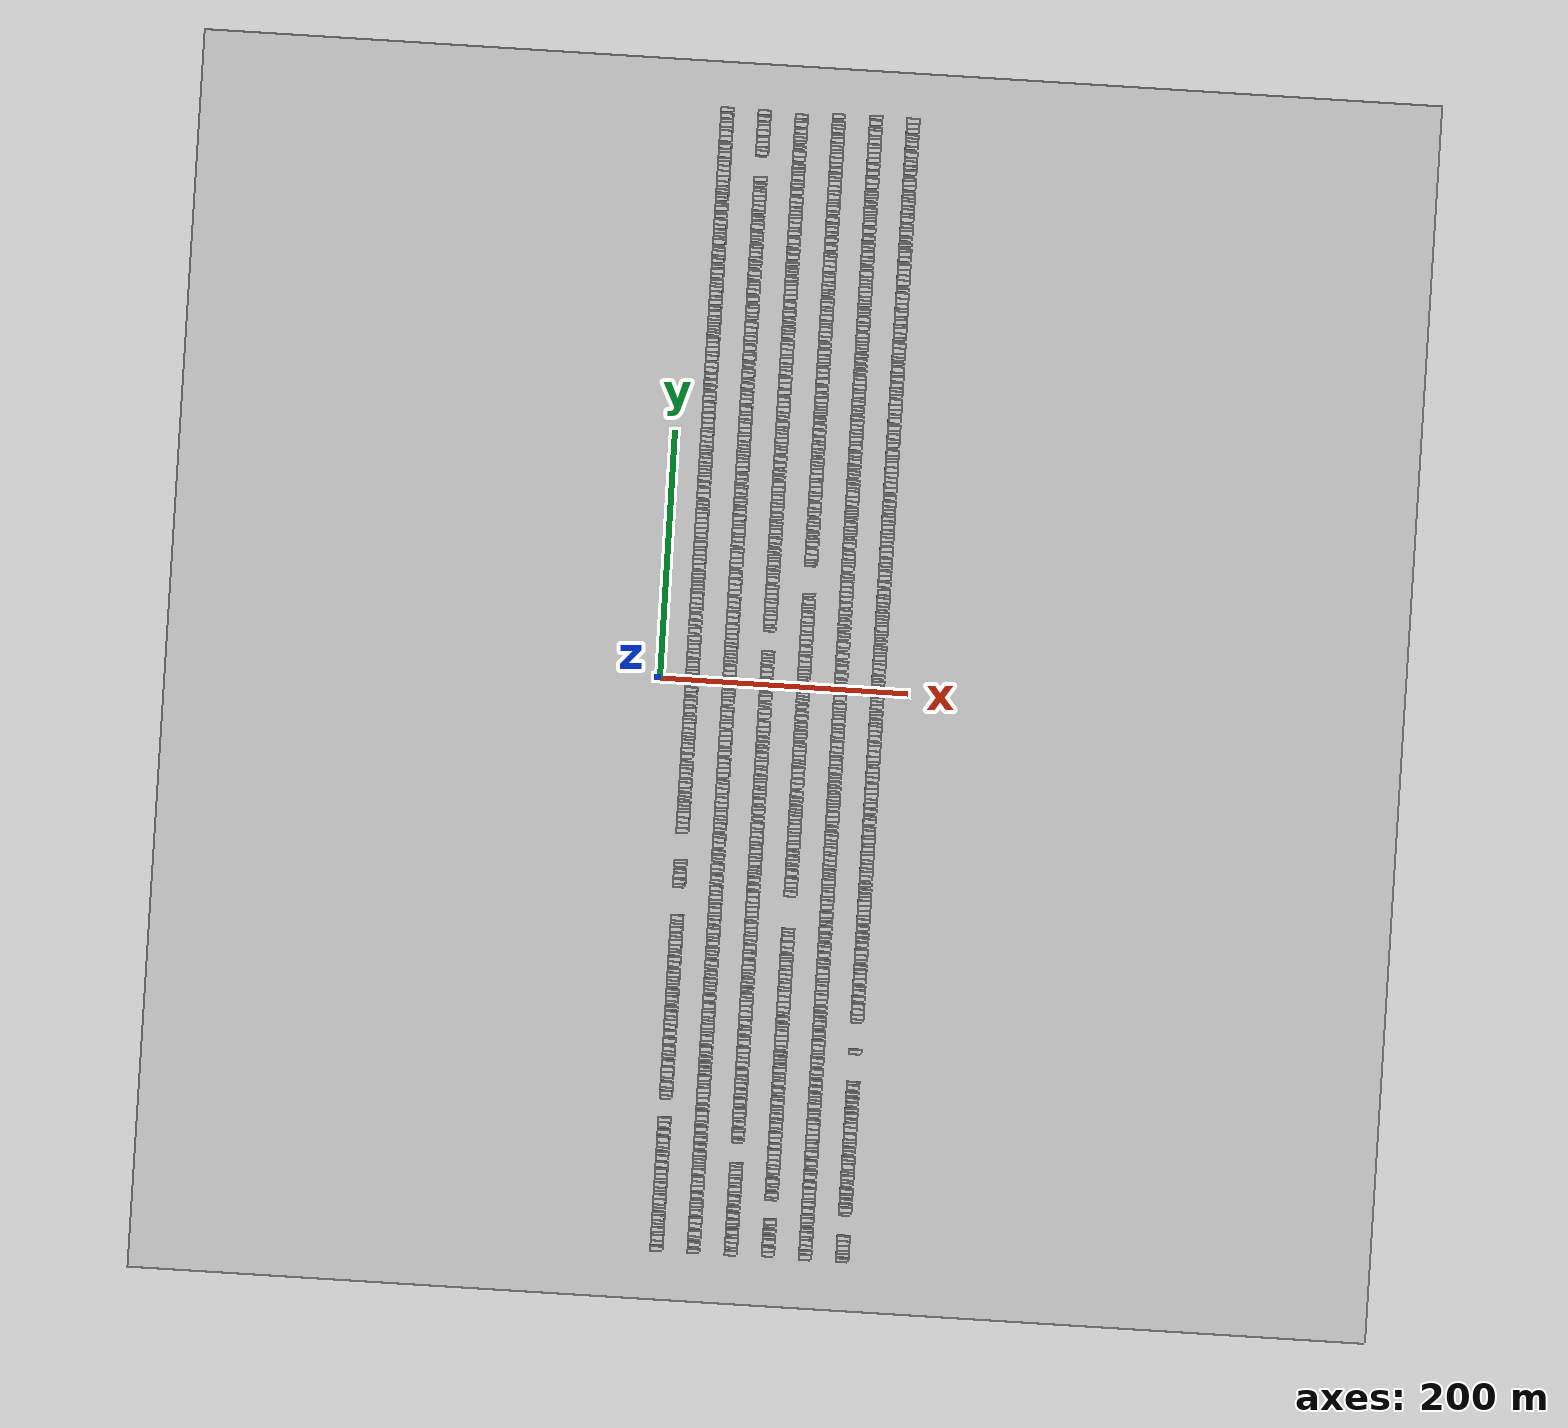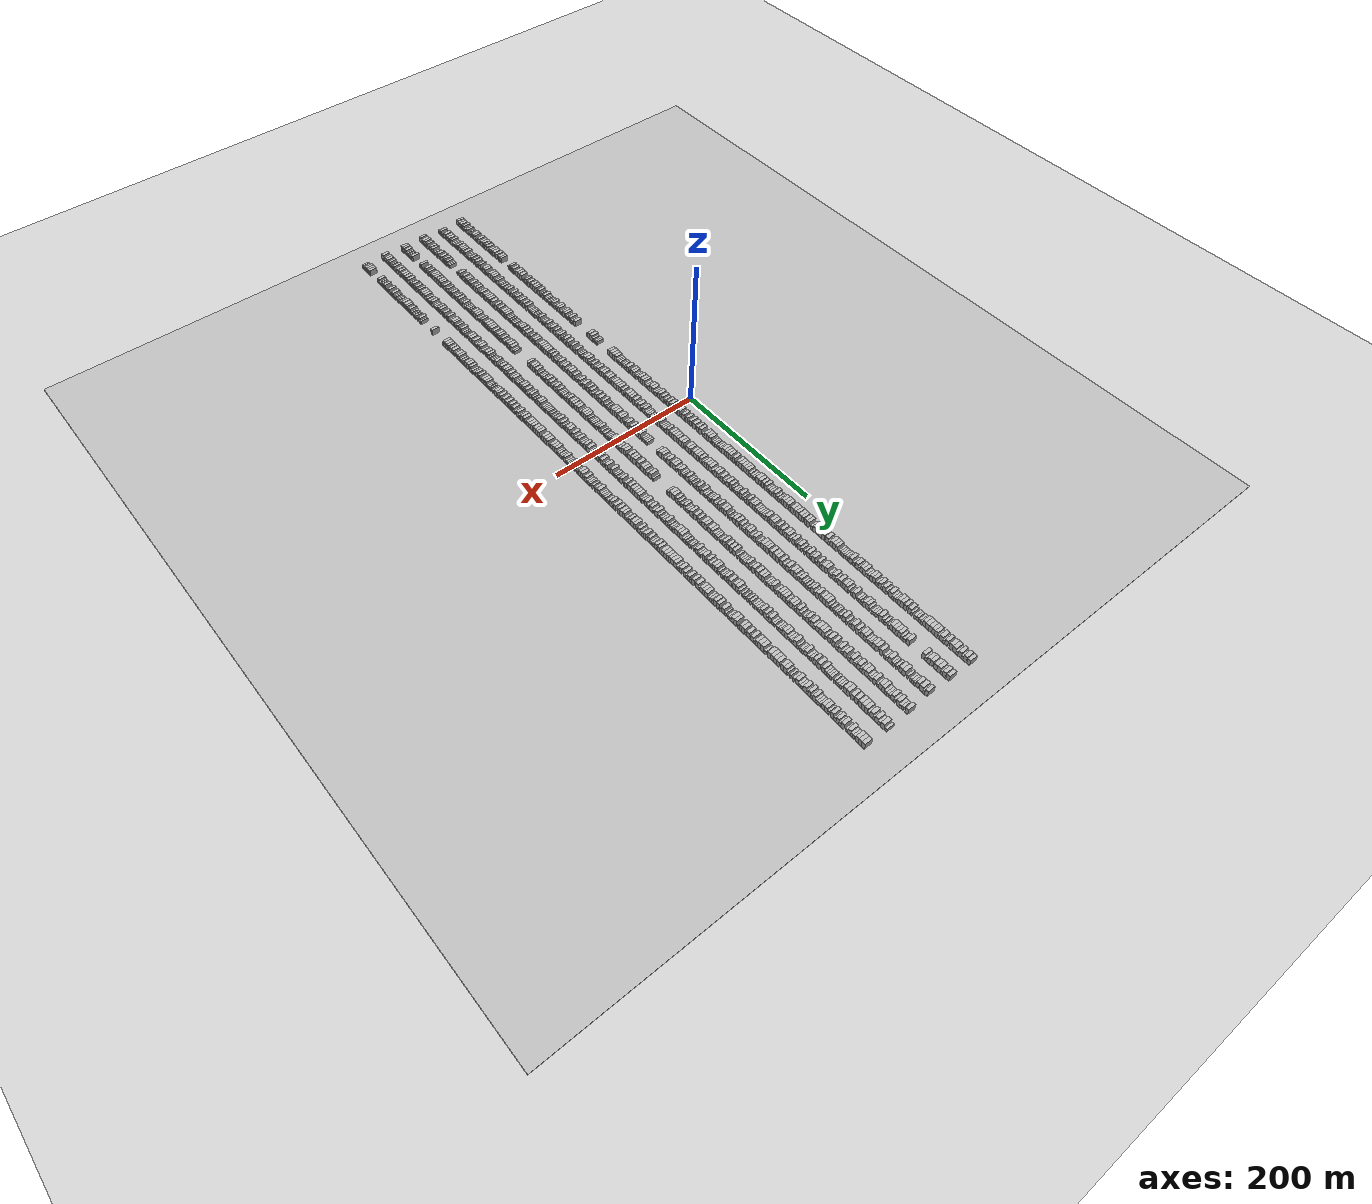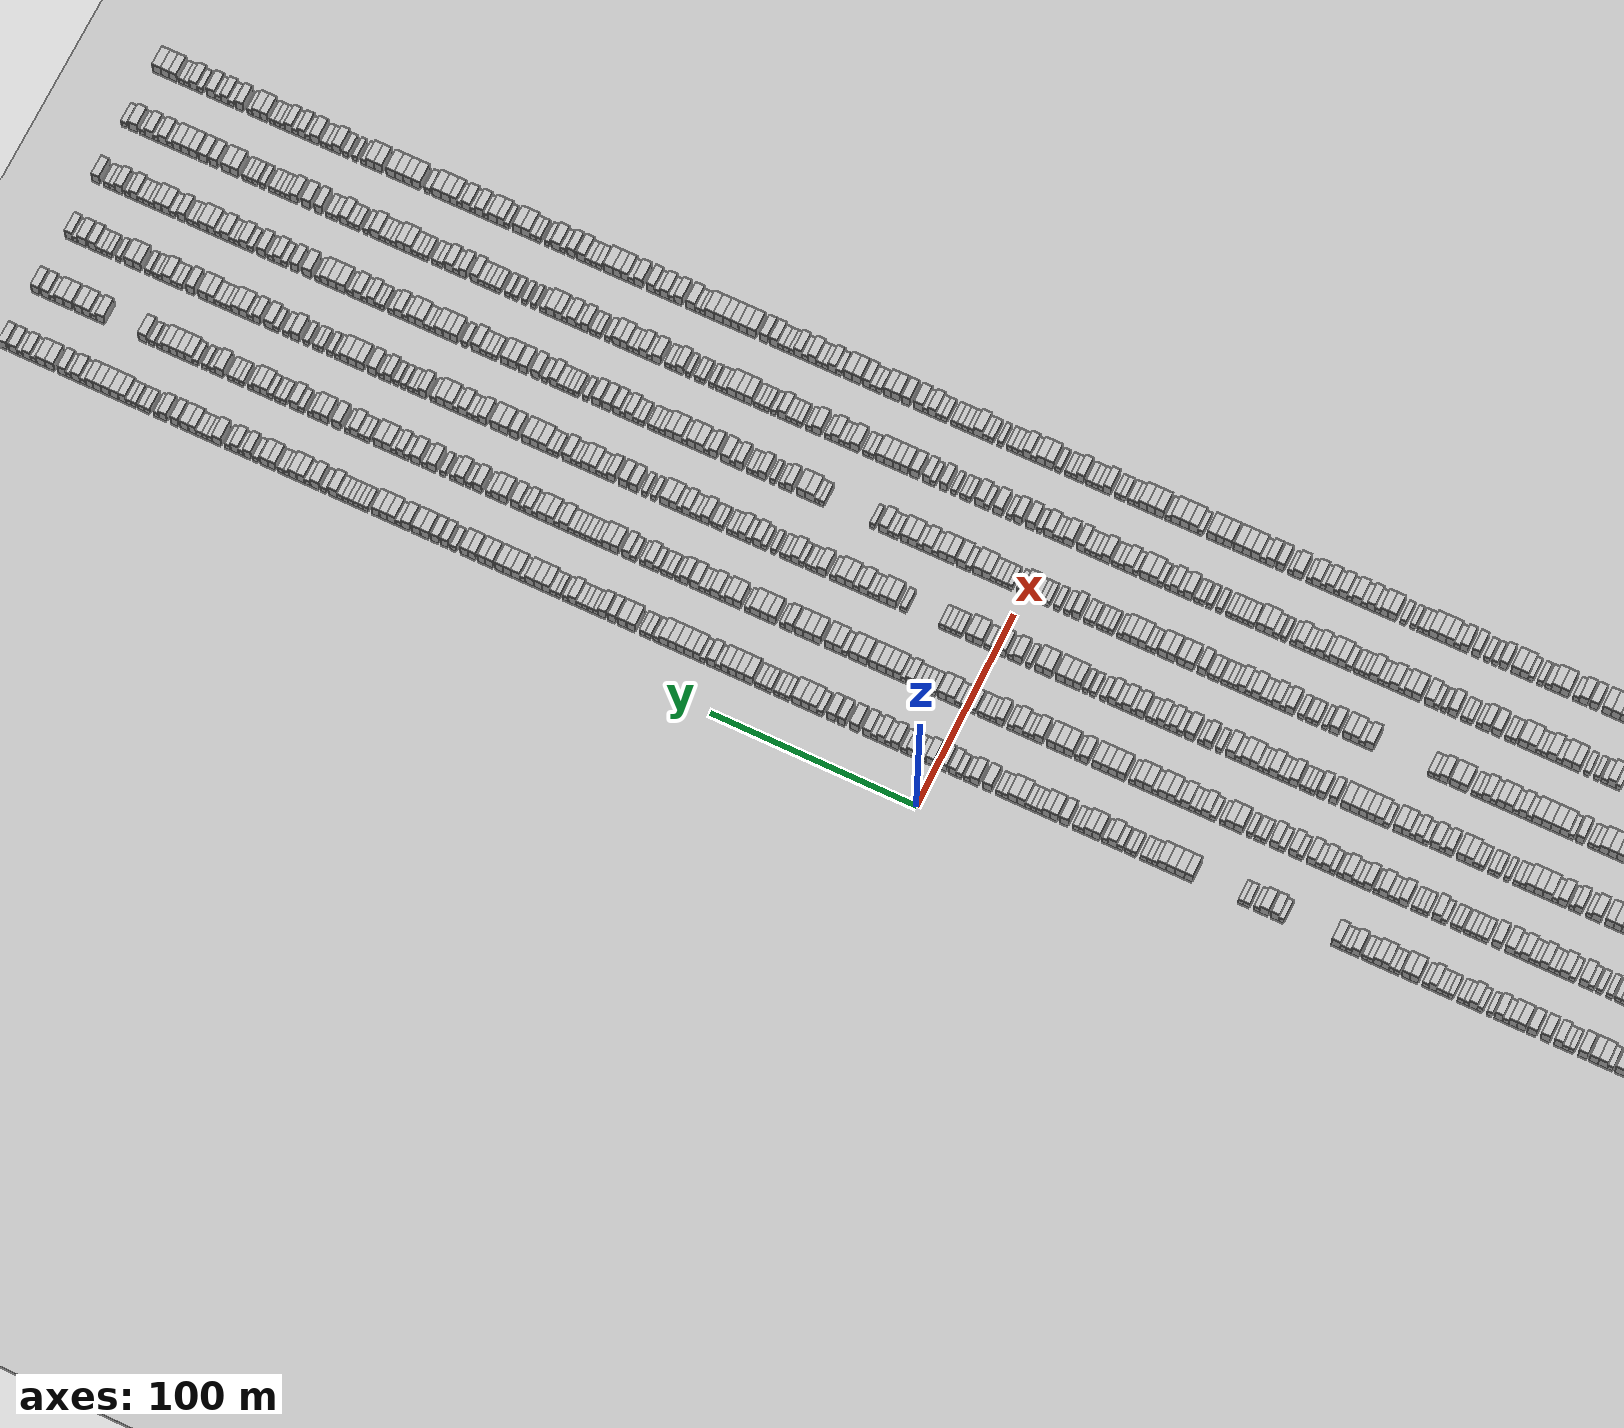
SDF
<sdf version="1.6">
 <world name="default">
  <scene>
   <sky><clouds><speed>12</speed></clouds></sky>
   <ambient>0.4 0.4 0.4 1</ambient>
   <background>0.7 0.7 0.7 1</background>
   <shadows>1</shadows>
  </scene>
  <gravity>0 0 -9.8066</gravity>
  <magnetic_field>6e-06 2.3e-05 -4.2e-05</magnetic_field>
  <physics default="0" name="default_physics" type="ode">
   <ode>
    <solver>
     <type>quick</type>
     <iters>10</iters>
     <sor>1.0</sor>
     <use_dynamic_moi_rescaling>0</use_dynamic_moi_rescaling>
    </solver>
    <constraints>
     <cfm>0</cfm>
     <erp>0.2</erp>
     <contact_max_correcting_vel>100</contact_max_correcting_vel>
     <contact_surface_layer>0.001</contact_surface_layer>
    </constraints>
   </ode>
   <max_step_size>0.004</max_step_size>
   <real_time_factor>1</real_time_factor>
   <real_time_update_rate>250</real_time_update_rate>
  </physics>
  <light name="sun" type="directional">
   <pose>0 0 10 0 0 0</pose>
   <diffuse>0.8 0.8 0.8 1</diffuse>
   <specular>0.2 0.2 0.2 1</specular>
   <attenuation>
    <range>1000</range>
    <constant>0.9</constant>
    <linear>0.01</linear>
    <quadratic>0.001</quadratic>
   </attenuation>
   <direction>-0.5 0.1 -0.9</direction>
  </light>
  <include><name>ground_plane_1</name><uri>model://HANNAS_ground_plane</uri></include>
  <include>
   <name>ground_plane_2</name>
   <uri>model://HANNAS_ground_plane</uri>
   <pose>100 0 0  0 0 0</pose>
  </include>
  <model name="building_1">
   <static>1</static>
   <pose>25.0000 -458.1524 0 0.000000 0.000000 0.000000</pose>
   <link name="link">
    <pose>0 0 4.50 0 0 0</pose>
    <collision name="collision"><geometry><box><size>10.0000 3.6952 9.0000</size></box></geometry></collision>
    <visual name="visual">
     <cast_shadows>0</cast_shadows>
     <geometry><box><size>10.0000 3.6952 9.0000</size></box></geometry>
     <material>
      <script>
       <uri>model://HANNAS_wall/materials/scripts</uri>
       <uri>model://HANNAS_wall/materials/textures</uri>
       <name>vrc/HANNAS_wall</name>
      </script>
     </material>
    </visual>
   </link>
  </model>
  <model name="building_2">
   <static>1</static>
   <pose>25.0000 -453.4959 0 0.000000 0.000000 0.000000</pose>
   <link name="link">
    <pose>0 0 4.50 0 0 0</pose>
    <collision name="collision"><geometry><box><size>10.0000 3.6178 9.0000</size></box></geometry></collision>
    <visual name="visual">
     <cast_shadows>0</cast_shadows>
     <geometry><box><size>10.0000 3.6178 9.0000</size></box></geometry>
     <material>
      <script>
       <uri>model://HANNAS_wall/materials/scripts</uri>
       <uri>model://HANNAS_wall/materials/textures</uri>
       <name>vrc/HANNAS_wall</name>
      </script>
     </material>
    </visual>
   </link>
  </model>
  <model name="building_3">
   <static>1</static>
   <pose>25.0000 -449.4425 0 0.000000 0.000000 0.000000</pose>
   <link name="link">
    <pose>0 0 4.50 0 0 0</pose>
    <collision name="collision"><geometry><box><size>10.0000 4.4890 9.0000</size></box></geometry></collision>
    <visual name="visual">
     <cast_shadows>0</cast_shadows>
     <geometry><box><size>10.0000 4.4890 9.0000</size></box></geometry>
     <material>
      <script>
       <uri>model://HANNAS_wall/materials/scripts</uri>
       <uri>model://HANNAS_wall/materials/textures</uri>
       <name>vrc/HANNAS_wall</name>
      </script>
     </material>
    </visual>
   </link>
  </model>
  <model name="building_4">
   <static>1</static>
   <pose>25.0000 -445.9746 0 0.000000 0.000000 0.000000</pose>
   <link name="link">
    <pose>0 0 3.00 0 0 0</pose>
    <collision name="collision"><geometry><box><size>10.0000 2.4467 6.0000</size></box></geometry></collision>
    <visual name="visual">
     <cast_shadows>0</cast_shadows>
     <geometry><box><size>10.0000 2.4467 6.0000</size></box></geometry>
     <material>
      <script>
       <uri>model://HANNAS_wall/materials/scripts</uri>
       <uri>model://HANNAS_wall/materials/textures</uri>
       <name>vrc/HANNAS_wall</name>
      </script>
     </material>
    </visual>
   </link>
  </model>
  <model name="building_5">
   <static>1</static>
   <pose>25.0000 -442.9022 0 0.000000 0.000000 0.000000</pose>
   <link name="link">
    <pose>0 0 4.50 0 0 0</pose>
    <collision name="collision"><geometry><box><size>10.0000 3.6982 9.0000</size></box></geometry></collision>
    <visual name="visual">
     <cast_shadows>0</cast_shadows>
     <geometry><box><size>10.0000 3.6982 9.0000</size></box></geometry>
     <material>
      <script>
       <uri>model://HANNAS_wall/materials/scripts</uri>
       <uri>model://HANNAS_wall/materials/textures</uri>
       <name>vrc/HANNAS_wall</name>
      </script>
     </material>
    </visual>
   </link>
  </model>
  <model name="building_6">
   <static>1</static>
   <pose>25.0000 -439.6706 0 0.000000 0.000000 0.000000</pose>
   <link name="link">
    <pose>0 0 3.00 0 0 0</pose>
    <collision name="collision"><geometry><box><size>10.0000 2.7650 6.0000</size></box></geometry></collision>
    <visual name="visual">
     <cast_shadows>0</cast_shadows>
     <geometry><box><size>10.0000 2.7650 6.0000</size></box></geometry>
     <material>
      <script>
       <uri>model://HANNAS_wall/materials/scripts</uri>
       <uri>model://HANNAS_wall/materials/textures</uri>
       <name>vrc/HANNAS_wall</name>
      </script>
     </material>
    </visual>
   </link>
  </model>
  <model name="building_7">
   <static>1</static>
   <pose>25.0000 -436.8086 0 0.000000 0.000000 0.000000</pose>
   <link name="link">
    <pose>0 0 3.00 0 0 0</pose>
    <collision name="collision"><geometry><box><size>10.0000 2.9590 6.0000</size></box></geometry></collision>
    <visual name="visual">
     <cast_shadows>0</cast_shadows>
     <geometry><box><size>10.0000 2.9590 6.0000</size></box></geometry>
     <material>
      <script>
       <uri>model://HANNAS_wall/materials/scripts</uri>
       <uri>model://HANNAS_wall/materials/textures</uri>
       <name>vrc/HANNAS_wall</name>
      </script>
     </material>
    </visual>
   </link>
  </model>
  <model name="building_8">
   <static>1</static>
   <pose>25.0000 -433.3091 0 0.000000 0.000000 0.000000</pose>
   <link name="link">
    <pose>0 0 4.50 0 0 0</pose>
    <collision name="collision"><geometry><box><size>10.0000 4.0399 9.0000</size></box></geometry></collision>
    <visual name="visual">
     <cast_shadows>0</cast_shadows>
     <geometry><box><size>10.0000 4.0399 9.0000</size></box></geometry>
     <material>
      <script>
       <uri>model://HANNAS_wall/materials/scripts</uri>
       <uri>model://HANNAS_wall/materials/textures</uri>
       <name>vrc/HANNAS_wall</name>
      </script>
     </material>
    </visual>
   </link>
  </model>
  <model name="building_9">
   <static>1</static>
   <pose>25.0000 -430.0815 0 0.000000 0.000000 0.000000</pose>
   <link name="link">
    <pose>0 0 3.00 0 0 0</pose>
    <collision name="collision"><geometry><box><size>10.0000 2.4153 6.0000</size></box></geometry></collision>
    <visual name="visual">
     <cast_shadows>0</cast_shadows>
     <geometry><box><size>10.0000 2.4153 6.0000</size></box></geometry>
     <material>
      <script>
       <uri>model://HANNAS_wall/materials/scripts</uri>
       <uri>model://HANNAS_wall/materials/textures</uri>
       <name>vrc/HANNAS_wall</name>
      </script>
     </material>
    </visual>
   </link>
  </model>
  <model name="building_10">
   <static>1</static>
   <pose>25.0000 -426.6182 0 0.000000 0.000000 0.000000</pose>
   <link name="link">
    <pose>0 0 3.00 0 0 0</pose>
    <collision name="collision"><geometry><box><size>10.0000 2.5112 6.0000</size></box></geometry></collision>
    <visual name="visual">
     <cast_shadows>0</cast_shadows>
     <geometry><box><size>10.0000 2.5112 6.0000</size></box></geometry>
     <material>
      <script>
       <uri>model://HANNAS_wall/materials/scripts</uri>
       <uri>model://HANNAS_wall/materials/textures</uri>
       <name>vrc/HANNAS_wall</name>
      </script>
     </material>
    </visual>
   </link>
  </model>
  <model name="building_11">
   <static>1</static>
   <pose>25.0000 -423.9730 0 0.000000 0.000000 0.000000</pose>
   <link name="link">
    <pose>0 0 3.00 0 0 0</pose>
    <collision name="collision"><geometry><box><size>10.0000 2.7792 6.0000</size></box></geometry></collision>
    <visual name="visual">
     <cast_shadows>0</cast_shadows>
     <geometry><box><size>10.0000 2.7792 6.0000</size></box></geometry>
     <material>
      <script>
       <uri>model://HANNAS_wall/materials/scripts</uri>
       <uri>model://HANNAS_wall/materials/textures</uri>
       <name>vrc/HANNAS_wall</name>
      </script>
     </material>
    </visual>
   </link>
  </model>
  <model name="building_12">
   <static>1</static>
   <pose>25.0000 -420.4237 0 0.000000 0.000000 0.000000</pose>
   <link name="link">
    <pose>0 0 4.50 0 0 0</pose>
    <collision name="collision"><geometry><box><size>10.0000 4.3195 9.0000</size></box></geometry></collision>
    <visual name="visual">
     <cast_shadows>0</cast_shadows>
     <geometry><box><size>10.0000 4.3195 9.0000</size></box></geometry>
     <material>
      <script>
       <uri>model://HANNAS_wall/materials/scripts</uri>
       <uri>model://HANNAS_wall/materials/textures</uri>
       <name>vrc/HANNAS_wall</name>
      </script>
     </material>
    </visual>
   </link>
  </model>
  <model name="building_13">
   <static>1</static>
   <pose>25.0000 -416.3539 0 0.000000 0.000000 0.000000</pose>
   <link name="link">
    <pose>0 0 4.50 0 0 0</pose>
    <collision name="collision"><geometry><box><size>10.0000 3.8201 9.0000</size></box></geometry></collision>
    <visual name="visual">
     <cast_shadows>0</cast_shadows>
     <geometry><box><size>10.0000 3.8201 9.0000</size></box></geometry>
     <material>
      <script>
       <uri>model://HANNAS_wall/materials/scripts</uri>
       <uri>model://HANNAS_wall/materials/textures</uri>
       <name>vrc/HANNAS_wall</name>
      </script>
     </material>
    </visual>
   </link>
  </model>
  <model name="building_14">
   <static>1</static>
   <pose>25.0000 -413.1420 0 0.000000 0.000000 0.000000</pose>
   <link name="link">
    <pose>0 0 3.00 0 0 0</pose>
    <collision name="collision"><geometry><box><size>10.0000 2.6039 6.0000</size></box></geometry></collision>
    <visual name="visual">
     <cast_shadows>0</cast_shadows>
     <geometry><box><size>10.0000 2.6039 6.0000</size></box></geometry>
     <material>
      <script>
       <uri>model://HANNAS_wall/materials/scripts</uri>
       <uri>model://HANNAS_wall/materials/textures</uri>
       <name>vrc/HANNAS_wall</name>
      </script>
     </material>
    </visual>
   </link>
  </model>
  <model name="building_15">
   <static>1</static>
   <pose>25.0000 -410.3872 0 0.000000 0.000000 0.000000</pose>
   <link name="link">
    <pose>0 0 3.00 0 0 0</pose>
    <collision name="collision"><geometry><box><size>10.0000 2.9057 6.0000</size></box></geometry></collision>
    <visual name="visual">
     <cast_shadows>0</cast_shadows>
     <geometry><box><size>10.0000 2.9057 6.0000</size></box></geometry>
     <material>
      <script>
       <uri>model://HANNAS_wall/materials/scripts</uri>
       <uri>model://HANNAS_wall/materials/textures</uri>
       <name>vrc/HANNAS_wall</name>
      </script>
     </material>
    </visual>
   </link>
  </model>
  <model name="building_16">
   <static>1</static>
   <pose>25.0000 -406.8814 0 0.000000 0.000000 0.000000</pose>
   <link name="link">
    <pose>0 0 4.50 0 0 0</pose>
    <collision name="collision"><geometry><box><size>10.0000 4.1057 9.0000</size></box></geometry></collision>
    <visual name="visual">
     <cast_shadows>0</cast_shadows>
     <geometry><box><size>10.0000 4.1057 9.0000</size></box></geometry>
     <material>
      <script>
       <uri>model://HANNAS_wall/materials/scripts</uri>
       <uri>model://HANNAS_wall/materials/textures</uri>
       <name>vrc/HANNAS_wall</name>
      </script>
     </material>
    </visual>
   </link>
  </model>
  <model name="building_17">
   <static>1</static>
   <pose>25.0000 -403.3574 0 0.000000 0.000000 0.000000</pose>
   <link name="link">
    <pose>0 0 3.00 0 0 0</pose>
    <collision name="collision"><geometry><box><size>10.0000 2.9423 6.0000</size></box></geometry></collision>
    <visual name="visual">
     <cast_shadows>0</cast_shadows>
     <geometry><box><size>10.0000 2.9423 6.0000</size></box></geometry>
     <material>
      <script>
       <uri>model://HANNAS_wall/materials/scripts</uri>
       <uri>model://HANNAS_wall/materials/textures</uri>
       <name>vrc/HANNAS_wall</name>
      </script>
     </material>
    </visual>
   </link>
  </model>
  <model name="building_18">
   <static>1</static>
   <pose>25.0000 -399.9926 0 0.000000 0.000000 0.000000</pose>
   <link name="link">
    <pose>0 0 4.50 0 0 0</pose>
    <collision name="collision"><geometry><box><size>10.0000 3.7872 9.0000</size></box></geometry></collision>
    <visual name="visual">
     <cast_shadows>0</cast_shadows>
     <geometry><box><size>10.0000 3.7872 9.0000</size></box></geometry>
     <material>
      <script>
       <uri>model://HANNAS_wall/materials/scripts</uri>
       <uri>model://HANNAS_wall/materials/textures</uri>
       <name>vrc/HANNAS_wall</name>
      </script>
     </material>
    </visual>
   </link>
  </model>
  <model name="building_19">
   <static>1</static>
   <pose>25.0000 -395.8993 0 0.000000 0.000000 0.000000</pose>
   <link name="link">
    <pose>0 0 4.50 0 0 0</pose>
    <collision name="collision"><geometry><box><size>10.0000 4.3993 9.0000</size></box></geometry></collision>
    <visual name="visual">
     <cast_shadows>0</cast_shadows>
     <geometry><box><size>10.0000 4.3993 9.0000</size></box></geometry>
     <material>
      <script>
       <uri>model://HANNAS_wall/materials/scripts</uri>
       <uri>model://HANNAS_wall/materials/textures</uri>
       <name>vrc/HANNAS_wall</name>
      </script>
     </material>
    </visual>
   </link>
  </model>
  <model name="building_20">
   <static>1</static>
   <pose>25.0000 -390.5978 0 0.000000 0.000000 0.000000</pose>
   <link name="link">
    <pose>0 0 4.50 0 0 0</pose>
    <collision name="collision"><geometry><box><size>10.0000 4.2038 9.0000</size></box></geometry></collision>
    <visual name="visual">
     <cast_shadows>0</cast_shadows>
     <geometry><box><size>10.0000 4.2038 9.0000</size></box></geometry>
     <material>
      <script>
       <uri>model://HANNAS_wall/materials/scripts</uri>
       <uri>model://HANNAS_wall/materials/textures</uri>
       <name>vrc/HANNAS_wall</name>
      </script>
     </material>
    </visual>
   </link>
  </model>
  <model name="building_21">
   <static>1</static>
   <pose>25.0000 -385.3042 0 0.000000 0.000000 0.000000</pose>
   <link name="link">
    <pose>0 0 4.50 0 0 0</pose>
    <collision name="collision"><geometry><box><size>10.0000 4.3834 9.0000</size></box></geometry></collision>
    <visual name="visual">
     <cast_shadows>0</cast_shadows>
     <geometry><box><size>10.0000 4.3834 9.0000</size></box></geometry>
     <material>
      <script>
       <uri>model://HANNAS_wall/materials/scripts</uri>
       <uri>model://HANNAS_wall/materials/textures</uri>
       <name>vrc/HANNAS_wall</name>
      </script>
     </material>
    </visual>
   </link>
  </model>
  <model name="building_22">
   <static>1</static>
   <pose>25.0000 -381.6776 0 0.000000 0.000000 0.000000</pose>
   <link name="link">
    <pose>0 0 3.00 0 0 0</pose>
    <collision name="collision"><geometry><box><size>10.0000 2.8699 6.0000</size></box></geometry></collision>
    <visual name="visual">
     <cast_shadows>0</cast_shadows>
     <geometry><box><size>10.0000 2.8699 6.0000</size></box></geometry>
     <material>
      <script>
       <uri>model://HANNAS_wall/materials/scripts</uri>
       <uri>model://HANNAS_wall/materials/textures</uri>
       <name>vrc/HANNAS_wall</name>
      </script>
     </material>
    </visual>
   </link>
  </model>
  <model name="building_23">
   <static>1</static>
   <pose>25.0000 -377.8964 0 0.000000 0.000000 0.000000</pose>
   <link name="link">
    <pose>0 0 3.00 0 0 0</pose>
    <collision name="collision"><geometry><box><size>10.0000 2.6924 6.0000</size></box></geometry></collision>
    <visual name="visual">
     <cast_shadows>0</cast_shadows>
     <geometry><box><size>10.0000 2.6924 6.0000</size></box></geometry>
     <material>
      <script>
       <uri>model://HANNAS_wall/materials/scripts</uri>
       <uri>model://HANNAS_wall/materials/textures</uri>
       <name>vrc/HANNAS_wall</name>
      </script>
     </material>
    </visual>
   </link>
  </model>
  <model name="building_24">
   <static>1</static>
   <pose>25.0000 -374.6292 0 0.000000 0.000000 0.000000</pose>
   <link name="link">
    <pose>0 0 4.50 0 0 0</pose>
    <collision name="collision"><geometry><box><size>10.0000 3.8420 9.0000</size></box></geometry></collision>
    <visual name="visual">
     <cast_shadows>0</cast_shadows>
     <geometry><box><size>10.0000 3.8420 9.0000</size></box></geometry>
     <material>
      <script>
       <uri>model://HANNAS_wall/materials/scripts</uri>
       <uri>model://HANNAS_wall/materials/textures</uri>
       <name>vrc/HANNAS_wall</name>
      </script>
     </material>
    </visual>
   </link>
  </model>
  <model name="building_25">
   <static>1</static>
   <pose>25.0000 -370.4790 0 0.000000 0.000000 0.000000</pose>
   <link name="link">
    <pose>0 0 4.50 0 0 0</pose>
    <collision name="collision"><geometry><box><size>10.0000 4.4584 9.0000</size></box></geometry></collision>
    <visual name="visual">
     <cast_shadows>0</cast_shadows>
     <geometry><box><size>10.0000 4.4584 9.0000</size></box></geometry>
     <material>
      <script>
       <uri>model://HANNAS_wall/materials/scripts</uri>
       <uri>model://HANNAS_wall/materials/textures</uri>
       <name>vrc/HANNAS_wall</name>
      </script>
     </material>
    </visual>
   </link>
  </model>
  <model name="building_26">
   <static>1</static>
   <pose>25.0000 -364.3102 0 0.000000 0.000000 0.000000</pose>
   <link name="link">
    <pose>0 0 4.50 0 0 0</pose>
    <collision name="collision"><geometry><box><size>10.0000 3.8792 9.0000</size></box></geometry></collision>
    <visual name="visual">
     <cast_shadows>0</cast_shadows>
     <geometry><box><size>10.0000 3.8792 9.0000</size></box></geometry>
     <material>
      <script>
       <uri>model://HANNAS_wall/materials/scripts</uri>
       <uri>model://HANNAS_wall/materials/textures</uri>
       <name>vrc/HANNAS_wall</name>
      </script>
     </material>
    </visual>
   </link>
  </model>
  <model name="building_27">
   <static>1</static>
   <pose>25.0000 -358.2777 0 0.000000 0.000000 0.000000</pose>
   <link name="link">
    <pose>0 0 4.50 0 0 0</pose>
    <collision name="collision"><geometry><box><size>10.0000 4.1857 9.0000</size></box></geometry></collision>
    <visual name="visual">
     <cast_shadows>0</cast_shadows>
     <geometry><box><size>10.0000 4.1857 9.0000</size></box></geometry>
     <material>
      <script>
       <uri>model://HANNAS_wall/materials/scripts</uri>
       <uri>model://HANNAS_wall/materials/textures</uri>
       <name>vrc/HANNAS_wall</name>
      </script>
     </material>
    </visual>
   </link>
  </model>
  <model name="building_28">
   <static>1</static>
   <pose>25.0000 -354.3249 0 0.000000 0.000000 0.000000</pose>
   <link name="link">
    <pose>0 0 4.50 0 0 0</pose>
    <collision name="collision"><geometry><box><size>10.0000 3.7199 9.0000</size></box></geometry></collision>
    <visual name="visual">
     <cast_shadows>0</cast_shadows>
     <geometry><box><size>10.0000 3.7199 9.0000</size></box></geometry>
     <material>
      <script>
       <uri>model://HANNAS_wall/materials/scripts</uri>
       <uri>model://HANNAS_wall/materials/textures</uri>
       <name>vrc/HANNAS_wall</name>
      </script>
     </material>
    </visual>
   </link>
  </model>
  <model name="building_29">
   <static>1</static>
   <pose>25.0000 -336.0042 0 0.000000 0.000000 0.000000</pose>
   <link name="link">
    <pose>0 0 3.00 0 0 0</pose>
    <collision name="collision"><geometry><box><size>10.0000 2.9738 6.0000</size></box></geometry></collision>
    <visual name="visual">
     <cast_shadows>0</cast_shadows>
     <geometry><box><size>10.0000 2.9738 6.0000</size></box></geometry>
     <material>
      <script>
       <uri>model://HANNAS_wall/materials/scripts</uri>
       <uri>model://HANNAS_wall/materials/textures</uri>
       <name>vrc/HANNAS_wall</name>
      </script>
     </material>
    </visual>
   </link>
  </model>
  <model name="building_30">
   <static>1</static>
   <pose>25.0000 -332.7003 0 0.000000 0.000000 0.000000</pose>
   <link name="link">
    <pose>0 0 4.50 0 0 0</pose>
    <collision name="collision"><geometry><box><size>10.0000 3.6338 9.0000</size></box></geometry></collision>
    <visual name="visual">
     <cast_shadows>0</cast_shadows>
     <geometry><box><size>10.0000 3.6338 9.0000</size></box></geometry>
     <material>
      <script>
       <uri>model://HANNAS_wall/materials/scripts</uri>
       <uri>model://HANNAS_wall/materials/textures</uri>
       <name>vrc/HANNAS_wall</name>
      </script>
     </material>
    </visual>
   </link>
  </model>
  <model name="building_31">
   <static>1</static>
   <pose>25.0000 -329.5198 0 0.000000 0.000000 0.000000</pose>
   <link name="link">
    <pose>0 0 3.00 0 0 0</pose>
    <collision name="collision"><geometry><box><size>10.0000 2.7272 6.0000</size></box></geometry></collision>
    <visual name="visual">
     <cast_shadows>0</cast_shadows>
     <geometry><box><size>10.0000 2.7272 6.0000</size></box></geometry>
     <material>
      <script>
       <uri>model://HANNAS_wall/materials/scripts</uri>
       <uri>model://HANNAS_wall/materials/textures</uri>
       <name>vrc/HANNAS_wall</name>
      </script>
     </material>
    </visual>
   </link>
  </model>
  <model name="building_32">
   <static>1</static>
   <pose>25.0000 -326.0183 0 0.000000 0.000000 0.000000</pose>
   <link name="link">
    <pose>0 0 4.50 0 0 0</pose>
    <collision name="collision"><geometry><box><size>10.0000 4.2759 9.0000</size></box></geometry></collision>
    <visual name="visual">
     <cast_shadows>0</cast_shadows>
     <geometry><box><size>10.0000 4.2759 9.0000</size></box></geometry>
     <material>
      <script>
       <uri>model://HANNAS_wall/materials/scripts</uri>
       <uri>model://HANNAS_wall/materials/textures</uri>
       <name>vrc/HANNAS_wall</name>
      </script>
     </material>
    </visual>
   </link>
  </model>
  <model name="building_33">
   <static>1</static>
   <pose>25.0000 -321.5558 0 0.000000 0.000000 0.000000</pose>
   <link name="link">
    <pose>0 0 3.00 0 0 0</pose>
    <collision name="collision"><geometry><box><size>10.0000 2.6491 6.0000</size></box></geometry></collision>
    <visual name="visual">
     <cast_shadows>0</cast_shadows>
     <geometry><box><size>10.0000 2.6491 6.0000</size></box></geometry>
     <material>
      <script>
       <uri>model://HANNAS_wall/materials/scripts</uri>
       <uri>model://HANNAS_wall/materials/textures</uri>
       <name>vrc/HANNAS_wall</name>
      </script>
     </material>
    </visual>
   </link>
  </model>
  <model name="building_34">
   <static>1</static>
   <pose>25.0000 -318.0081 0 0.000000 0.000000 0.000000</pose>
   <link name="link">
    <pose>0 0 4.50 0 0 0</pose>
    <collision name="collision"><geometry><box><size>10.0000 4.4463 9.0000</size></box></geometry></collision>
    <visual name="visual">
     <cast_shadows>0</cast_shadows>
     <geometry><box><size>10.0000 4.4463 9.0000</size></box></geometry>
     <material>
      <script>
       <uri>model://HANNAS_wall/materials/scripts</uri>
       <uri>model://HANNAS_wall/materials/textures</uri>
       <name>vrc/HANNAS_wall</name>
      </script>
     </material>
    </visual>
   </link>
  </model>
  <model name="building_35">
   <static>1</static>
   <pose>25.0000 -313.7575 0 0.000000 0.000000 0.000000</pose>
   <link name="link">
    <pose>0 0 4.50 0 0 0</pose>
    <collision name="collision"><geometry><box><size>10.0000 4.0548 9.0000</size></box></geometry></collision>
    <visual name="visual">
     <cast_shadows>0</cast_shadows>
     <geometry><box><size>10.0000 4.0548 9.0000</size></box></geometry>
     <material>
      <script>
       <uri>model://HANNAS_wall/materials/scripts</uri>
       <uri>model://HANNAS_wall/materials/textures</uri>
       <name>vrc/HANNAS_wall</name>
      </script>
     </material>
    </visual>
   </link>
  </model>
  <model name="building_36">
   <static>1</static>
   <pose>25.0000 -308.5774 0 0.000000 0.000000 0.000000</pose>
   <link name="link">
    <pose>0 0 4.50 0 0 0</pose>
    <collision name="collision"><geometry><box><size>10.0000 4.3056 9.0000</size></box></geometry></collision>
    <visual name="visual">
     <cast_shadows>0</cast_shadows>
     <geometry><box><size>10.0000 4.3056 9.0000</size></box></geometry>
     <material>
      <script>
       <uri>model://HANNAS_wall/materials/scripts</uri>
       <uri>model://HANNAS_wall/materials/textures</uri>
       <name>vrc/HANNAS_wall</name>
      </script>
     </material>
    </visual>
   </link>
  </model>
  <model name="building_37">
   <static>1</static>
   <pose>25.0000 -303.1384 0 0.000000 0.000000 0.000000</pose>
   <link name="link">
    <pose>0 0 3.00 0 0 0</pose>
    <collision name="collision"><geometry><box><size>10.0000 2.5723 6.0000</size></box></geometry></collision>
    <visual name="visual">
     <cast_shadows>0</cast_shadows>
     <geometry><box><size>10.0000 2.5723 6.0000</size></box></geometry>
     <material>
      <script>
       <uri>model://HANNAS_wall/materials/scripts</uri>
       <uri>model://HANNAS_wall/materials/textures</uri>
       <name>vrc/HANNAS_wall</name>
      </script>
     </material>
    </visual>
   </link>
  </model>
  <model name="building_38">
   <static>1</static>
   <pose>25.0000 -300.4234 0 0.000000 0.000000 0.000000</pose>
   <link name="link">
    <pose>0 0 3.00 0 0 0</pose>
    <collision name="collision"><geometry><box><size>10.0000 2.8578 6.0000</size></box></geometry></collision>
    <visual name="visual">
     <cast_shadows>0</cast_shadows>
     <geometry><box><size>10.0000 2.8578 6.0000</size></box></geometry>
     <material>
      <script>
       <uri>model://HANNAS_wall/materials/scripts</uri>
       <uri>model://HANNAS_wall/materials/textures</uri>
       <name>vrc/HANNAS_wall</name>
      </script>
     </material>
    </visual>
   </link>
  </model>
  <model name="building_39">
   <static>1</static>
   <pose>25.0000 -296.9860 0 0.000000 0.000000 0.000000</pose>
   <link name="link">
    <pose>0 0 4.50 0 0 0</pose>
    <collision name="collision"><geometry><box><size>10.0000 4.0170 9.0000</size></box></geometry></collision>
    <visual name="visual">
     <cast_shadows>0</cast_shadows>
     <geometry><box><size>10.0000 4.0170 9.0000</size></box></geometry>
     <material>
      <script>
       <uri>model://HANNAS_wall/materials/scripts</uri>
       <uri>model://HANNAS_wall/materials/textures</uri>
       <name>vrc/HANNAS_wall</name>
      </script>
     </material>
    </visual>
   </link>
  </model>
  <model name="building_40">
   <static>1</static>
   <pose>25.0000 -290.8100 0 0.000000 0.000000 0.000000</pose>
   <link name="link">
    <pose>0 0 4.50 0 0 0</pose>
    <collision name="collision"><geometry><box><size>10.0000 4.3349 9.0000</size></box></geometry></collision>
    <visual name="visual">
     <cast_shadows>0</cast_shadows>
     <geometry><box><size>10.0000 4.3349 9.0000</size></box></geometry>
     <material>
      <script>
       <uri>model://HANNAS_wall/materials/scripts</uri>
       <uri>model://HANNAS_wall/materials/textures</uri>
       <name>vrc/HANNAS_wall</name>
      </script>
     </material>
    </visual>
   </link>
  </model>
  <model name="building_41">
   <static>1</static>
   <pose>25.0000 -284.5205 0 0.000000 0.000000 0.000000</pose>
   <link name="link">
    <pose>0 0 4.50 0 0 0</pose>
    <collision name="collision"><geometry><box><size>10.0000 4.2441 9.0000</size></box></geometry></collision>
    <visual name="visual">
     <cast_shadows>0</cast_shadows>
     <geometry><box><size>10.0000 4.2441 9.0000</size></box></geometry>
     <material>
      <script>
       <uri>model://HANNAS_wall/materials/scripts</uri>
       <uri>model://HANNAS_wall/materials/textures</uri>
       <name>vrc/HANNAS_wall</name>
      </script>
     </material>
    </visual>
   </link>
  </model>
  <model name="building_42">
   <static>1</static>
   <pose>25.0000 -279.3800 0 0.000000 0.000000 0.000000</pose>
   <link name="link">
    <pose>0 0 4.50 0 0 0</pose>
    <collision name="collision"><geometry><box><size>10.0000 4.0371 9.0000</size></box></geometry></collision>
    <visual name="visual">
     <cast_shadows>0</cast_shadows>
     <geometry><box><size>10.0000 4.0371 9.0000</size></box></geometry>
     <material>
      <script>
       <uri>model://HANNAS_wall/materials/scripts</uri>
       <uri>model://HANNAS_wall/materials/textures</uri>
       <name>vrc/HANNAS_wall</name>
      </script>
     </material>
    </visual>
   </link>
  </model>
  <model name="building_43">
   <static>1</static>
   <pose>25.0000 -275.5001 0 0.000000 0.000000 0.000000</pose>
   <link name="link">
    <pose>0 0 4.50 0 0 0</pose>
    <collision name="collision"><geometry><box><size>10.0000 3.7226 9.0000</size></box></geometry></collision>
    <visual name="visual">
     <cast_shadows>0</cast_shadows>
     <geometry><box><size>10.0000 3.7226 9.0000</size></box></geometry>
     <material>
      <script>
       <uri>model://HANNAS_wall/materials/scripts</uri>
       <uri>model://HANNAS_wall/materials/textures</uri>
       <name>vrc/HANNAS_wall</name>
      </script>
     </material>
    </visual>
   </link>
  </model>
  <model name="building_44">
   <static>1</static>
   <pose>25.0000 -272.1725 0 0.000000 0.000000 0.000000</pose>
   <link name="link">
    <pose>0 0 3.00 0 0 0</pose>
    <collision name="collision"><geometry><box><size>10.0000 2.9327 6.0000</size></box></geometry></collision>
    <visual name="visual">
     <cast_shadows>0</cast_shadows>
     <geometry><box><size>10.0000 2.9327 6.0000</size></box></geometry>
     <material>
      <script>
       <uri>model://HANNAS_wall/materials/scripts</uri>
       <uri>model://HANNAS_wall/materials/textures</uri>
       <name>vrc/HANNAS_wall</name>
      </script>
     </material>
    </visual>
   </link>
  </model>
  <model name="building_45">
   <static>1</static>
   <pose>25.0000 -268.7681 0 0.000000 0.000000 0.000000</pose>
   <link name="link">
    <pose>0 0 4.50 0 0 0</pose>
    <collision name="collision"><geometry><box><size>10.0000 3.8760 9.0000</size></box></geometry></collision>
    <visual name="visual">
     <cast_shadows>0</cast_shadows>
     <geometry><box><size>10.0000 3.8760 9.0000</size></box></geometry>
     <material>
      <script>
       <uri>model://HANNAS_wall/materials/scripts</uri>
       <uri>model://HANNAS_wall/materials/textures</uri>
       <name>vrc/HANNAS_wall</name>
      </script>
     </material>
    </visual>
   </link>
  </model>
  <model name="building_46">
   <static>1</static>
   <pose>25.0000 -264.5430 0 0.000000 0.000000 0.000000</pose>
   <link name="link">
    <pose>0 0 3.00 0 0 0</pose>
    <collision name="collision"><geometry><box><size>10.0000 2.5741 6.0000</size></box></geometry></collision>
    <visual name="visual">
     <cast_shadows>0</cast_shadows>
     <geometry><box><size>10.0000 2.5741 6.0000</size></box></geometry>
     <material>
      <script>
       <uri>model://HANNAS_wall/materials/scripts</uri>
       <uri>model://HANNAS_wall/materials/textures</uri>
       <name>vrc/HANNAS_wall</name>
      </script>
     </material>
    </visual>
   </link>
  </model>
  <model name="building_47">
   <static>1</static>
   <pose>25.0000 -259.9437 0 0.000000 0.000000 0.000000</pose>
   <link name="link">
    <pose>0 0 3.00 0 0 0</pose>
    <collision name="collision"><geometry><box><size>10.0000 2.6247 6.0000</size></box></geometry></collision>
    <visual name="visual">
     <cast_shadows>0</cast_shadows>
     <geometry><box><size>10.0000 2.6247 6.0000</size></box></geometry>
     <material>
      <script>
       <uri>model://HANNAS_wall/materials/scripts</uri>
       <uri>model://HANNAS_wall/materials/textures</uri>
       <name>vrc/HANNAS_wall</name>
      </script>
     </material>
    </visual>
   </link>
  </model>
  <model name="building_48">
   <static>1</static>
   <pose>25.0000 -256.6727 0 0.000000 0.000000 0.000000</pose>
   <link name="link">
    <pose>0 0 4.50 0 0 0</pose>
    <collision name="collision"><geometry><box><size>10.0000 3.9173 9.0000</size></box></geometry></collision>
    <visual name="visual">
     <cast_shadows>0</cast_shadows>
     <geometry><box><size>10.0000 3.9173 9.0000</size></box></geometry>
     <material>
      <script>
       <uri>model://HANNAS_wall/materials/scripts</uri>
       <uri>model://HANNAS_wall/materials/textures</uri>
       <name>vrc/HANNAS_wall</name>
      </script>
     </material>
    </visual>
   </link>
  </model>
  <model name="building_49">
   <static>1</static>
   <pose>25.0000 -253.4671 0 0.000000 0.000000 0.000000</pose>
   <link name="link">
    <pose>0 0 3.00 0 0 0</pose>
    <collision name="collision"><geometry><box><size>10.0000 2.4939 6.0000</size></box></geometry></collision>
    <visual name="visual">
     <cast_shadows>0</cast_shadows>
     <geometry><box><size>10.0000 2.4939 6.0000</size></box></geometry>
     <material>
      <script>
       <uri>model://HANNAS_wall/materials/scripts</uri>
       <uri>model://HANNAS_wall/materials/textures</uri>
       <name>vrc/HANNAS_wall</name>
      </script>
     </material>
    </visual>
   </link>
  </model>
  <model name="building_50">
   <static>1</static>
   <pose>25.0000 -250.7479 0 0.000000 0.000000 0.000000</pose>
   <link name="link">
    <pose>0 0 3.00 0 0 0</pose>
    <collision name="collision"><geometry><box><size>10.0000 2.9444 6.0000</size></box></geometry></collision>
    <visual name="visual">
     <cast_shadows>0</cast_shadows>
     <geometry><box><size>10.0000 2.9444 6.0000</size></box></geometry>
     <material>
      <script>
       <uri>model://HANNAS_wall/materials/scripts</uri>
       <uri>model://HANNAS_wall/materials/textures</uri>
       <name>vrc/HANNAS_wall</name>
      </script>
     </material>
    </visual>
   </link>
  </model>
  <model name="building_51">
   <static>1</static>
   <pose>25.0000 -245.9819 0 0.000000 0.000000 0.000000</pose>
   <link name="link">
    <pose>0 0 3.00 0 0 0</pose>
    <collision name="collision"><geometry><box><size>10.0000 2.5876 6.0000</size></box></geometry></collision>
    <visual name="visual">
     <cast_shadows>0</cast_shadows>
     <geometry><box><size>10.0000 2.5876 6.0000</size></box></geometry>
     <material>
      <script>
       <uri>model://HANNAS_wall/materials/scripts</uri>
       <uri>model://HANNAS_wall/materials/textures</uri>
       <name>vrc/HANNAS_wall</name>
      </script>
     </material>
    </visual>
   </link>
  </model>
  <model name="building_52">
   <static>1</static>
   <pose>25.0000 -243.4026 0 0.000000 0.000000 0.000000</pose>
   <link name="link">
    <pose>0 0 3.00 0 0 0</pose>
    <collision name="collision"><geometry><box><size>10.0000 2.5710 6.0000</size></box></geometry></collision>
    <visual name="visual">
     <cast_shadows>0</cast_shadows>
     <geometry><box><size>10.0000 2.5710 6.0000</size></box></geometry>
     <material>
      <script>
       <uri>model://HANNAS_wall/materials/scripts</uri>
       <uri>model://HANNAS_wall/materials/textures</uri>
       <name>vrc/HANNAS_wall</name>
      </script>
     </material>
    </visual>
   </link>
  </model>
  <model name="building_53">
   <static>1</static>
   <pose>25.0000 -240.6543 0 0.000000 0.000000 0.000000</pose>
   <link name="link">
    <pose>0 0 3.00 0 0 0</pose>
    <collision name="collision"><geometry><box><size>10.0000 2.9257 6.0000</size></box></geometry></collision>
    <visual name="visual">
     <cast_shadows>0</cast_shadows>
     <geometry><box><size>10.0000 2.9257 6.0000</size></box></geometry>
     <material>
      <script>
       <uri>model://HANNAS_wall/materials/scripts</uri>
       <uri>model://HANNAS_wall/materials/textures</uri>
       <name>vrc/HANNAS_wall</name>
      </script>
     </material>
    </visual>
   </link>
  </model>
  <model name="building_54">
   <static>1</static>
   <pose>25.0000 -237.3830 0 0.000000 0.000000 0.000000</pose>
   <link name="link">
    <pose>0 0 4.50 0 0 0</pose>
    <collision name="collision"><geometry><box><size>10.0000 3.6170 9.0000</size></box></geometry></collision>
    <visual name="visual">
     <cast_shadows>0</cast_shadows>
     <geometry><box><size>10.0000 3.6170 9.0000</size></box></geometry>
     <material>
      <script>
       <uri>model://HANNAS_wall/materials/scripts</uri>
       <uri>model://HANNAS_wall/materials/textures</uri>
       <name>vrc/HANNAS_wall</name>
      </script>
     </material>
    </visual>
   </link>
  </model>
  <model name="building_55">
   <static>1</static>
   <pose>25.0000 -234.1075 0 0.000000 0.000000 0.000000</pose>
   <link name="link">
    <pose>0 0 3.00 0 0 0</pose>
    <collision name="collision"><geometry><box><size>10.0000 2.9338 6.0000</size></box></geometry></collision>
    <visual name="visual">
     <cast_shadows>0</cast_shadows>
     <geometry><box><size>10.0000 2.9338 6.0000</size></box></geometry>
     <material>
      <script>
       <uri>model://HANNAS_wall/materials/scripts</uri>
       <uri>model://HANNAS_wall/materials/textures</uri>
       <name>vrc/HANNAS_wall</name>
      </script>
     </material>
    </visual>
   </link>
  </model>
  <model name="building_56">
   <static>1</static>
   <pose>25.0000 -228.5994 0 0.000000 0.000000 0.000000</pose>
   <link name="link">
    <pose>0 0 4.50 0 0 0</pose>
    <collision name="collision"><geometry><box><size>10.0000 4.0824 9.0000</size></box></geometry></collision>
    <visual name="visual">
     <cast_shadows>0</cast_shadows>
     <geometry><box><size>10.0000 4.0824 9.0000</size></box></geometry>
     <material>
      <script>
       <uri>model://HANNAS_wall/materials/scripts</uri>
       <uri>model://HANNAS_wall/materials/textures</uri>
       <name>vrc/HANNAS_wall</name>
      </script>
     </material>
    </visual>
   </link>
  </model>
  <model name="building_57">
   <static>1</static>
   <pose>25.0000 -224.7067 0 0.000000 0.000000 0.000000</pose>
   <link name="link">
    <pose>0 0 4.50 0 0 0</pose>
    <collision name="collision"><geometry><box><size>10.0000 3.7029 9.0000</size></box></geometry></collision>
    <visual name="visual">
     <cast_shadows>0</cast_shadows>
     <geometry><box><size>10.0000 3.7029 9.0000</size></box></geometry>
     <material>
      <script>
       <uri>model://HANNAS_wall/materials/scripts</uri>
       <uri>model://HANNAS_wall/materials/textures</uri>
       <name>vrc/HANNAS_wall</name>
      </script>
     </material>
    </visual>
   </link>
  </model>
  <model name="building_58">
   <static>1</static>
   <pose>25.0000 -220.5207 0 0.000000 0.000000 0.000000</pose>
   <link name="link">
    <pose>0 0 3.00 0 0 0</pose>
    <collision name="collision"><geometry><box><size>10.0000 2.6692 6.0000</size></box></geometry></collision>
    <visual name="visual">
     <cast_shadows>0</cast_shadows>
     <geometry><box><size>10.0000 2.6692 6.0000</size></box></geometry>
     <material>
      <script>
       <uri>model://HANNAS_wall/materials/scripts</uri>
       <uri>model://HANNAS_wall/materials/textures</uri>
       <name>vrc/HANNAS_wall</name>
      </script>
     </material>
    </visual>
   </link>
  </model>
  <model name="building_59">
   <static>1</static>
   <pose>25.0000 -217.9531 0 0.000000 0.000000 0.000000</pose>
   <link name="link">
    <pose>0 0 3.00 0 0 0</pose>
    <collision name="collision"><geometry><box><size>10.0000 2.4660 6.0000</size></box></geometry></collision>
    <visual name="visual">
     <cast_shadows>0</cast_shadows>
     <geometry><box><size>10.0000 2.4660 6.0000</size></box></geometry>
     <material>
      <script>
       <uri>model://HANNAS_wall/materials/scripts</uri>
       <uri>model://HANNAS_wall/materials/textures</uri>
       <name>vrc/HANNAS_wall</name>
      </script>
     </material>
    </visual>
   </link>
  </model>
  <model name="building_60">
   <static>1</static>
   <pose>25.0000 -214.8881 0 0.000000 0.000000 0.000000</pose>
   <link name="link">
    <pose>0 0 4.50 0 0 0</pose>
    <collision name="collision"><geometry><box><size>10.0000 3.6640 9.0000</size></box></geometry></collision>
    <visual name="visual">
     <cast_shadows>0</cast_shadows>
     <geometry><box><size>10.0000 3.6640 9.0000</size></box></geometry>
     <material>
      <script>
       <uri>model://HANNAS_wall/materials/scripts</uri>
       <uri>model://HANNAS_wall/materials/textures</uri>
       <name>vrc/HANNAS_wall</name>
      </script>
     </material>
    </visual>
   </link>
  </model>
  <model name="building_61">
   <static>1</static>
   <pose>25.0000 -211.1548 0 0.000000 0.000000 0.000000</pose>
   <link name="link">
    <pose>0 0 4.50 0 0 0</pose>
    <collision name="collision"><geometry><box><size>10.0000 3.8027 9.0000</size></box></geometry></collision>
    <visual name="visual">
     <cast_shadows>0</cast_shadows>
     <geometry><box><size>10.0000 3.8027 9.0000</size></box></geometry>
     <material>
      <script>
       <uri>model://HANNAS_wall/materials/scripts</uri>
       <uri>model://HANNAS_wall/materials/textures</uri>
       <name>vrc/HANNAS_wall</name>
      </script>
     </material>
    </visual>
   </link>
  </model>
  <model name="building_62">
   <static>1</static>
   <pose>25.0000 -207.8550 0 0.000000 0.000000 0.000000</pose>
   <link name="link">
    <pose>0 0 3.00 0 0 0</pose>
    <collision name="collision"><geometry><box><size>10.0000 2.7968 6.0000</size></box></geometry></collision>
    <visual name="visual">
     <cast_shadows>0</cast_shadows>
     <geometry><box><size>10.0000 2.7968 6.0000</size></box></geometry>
     <material>
      <script>
       <uri>model://HANNAS_wall/materials/scripts</uri>
       <uri>model://HANNAS_wall/materials/textures</uri>
       <name>vrc/HANNAS_wall</name>
      </script>
     </material>
    </visual>
   </link>
  </model>
  <model name="building_63">
   <static>1</static>
   <pose>25.0000 -205.1174 0 0.000000 0.000000 0.000000</pose>
   <link name="link">
    <pose>0 0 3.00 0 0 0</pose>
    <collision name="collision"><geometry><box><size>10.0000 2.6784 6.0000</size></box></geometry></collision>
    <visual name="visual">
     <cast_shadows>0</cast_shadows>
     <geometry><box><size>10.0000 2.6784 6.0000</size></box></geometry>
     <material>
      <script>
       <uri>model://HANNAS_wall/materials/scripts</uri>
       <uri>model://HANNAS_wall/materials/textures</uri>
       <name>vrc/HANNAS_wall</name>
      </script>
     </material>
    </visual>
   </link>
  </model>
  <model name="building_64">
   <static>1</static>
   <pose>25.0000 -200.8064 0 0.000000 0.000000 0.000000</pose>
   <link name="link">
    <pose>0 0 4.50 0 0 0</pose>
    <collision name="collision"><geometry><box><size>10.0000 3.9436 9.0000</size></box></geometry></collision>
    <visual name="visual">
     <cast_shadows>0</cast_shadows>
     <geometry><box><size>10.0000 3.9436 9.0000</size></box></geometry>
     <material>
      <script>
       <uri>model://HANNAS_wall/materials/scripts</uri>
       <uri>model://HANNAS_wall/materials/textures</uri>
       <name>vrc/HANNAS_wall</name>
      </script>
     </material>
    </visual>
   </link>
  </model>
  <model name="building_65">
   <static>1</static>
   <pose>25.0000 -197.4739 0 0.000000 0.000000 0.000000</pose>
   <link name="link">
    <pose>0 0 3.00 0 0 0</pose>
    <collision name="collision"><geometry><box><size>10.0000 2.7212 6.0000</size></box></geometry></collision>
    <visual name="visual">
     <cast_shadows>0</cast_shadows>
     <geometry><box><size>10.0000 2.7212 6.0000</size></box></geometry>
     <material>
      <script>
       <uri>model://HANNAS_wall/materials/scripts</uri>
       <uri>model://HANNAS_wall/materials/textures</uri>
       <name>vrc/HANNAS_wall</name>
      </script>
     </material>
    </visual>
   </link>
  </model>
  <model name="building_66">
   <static>1</static>
   <pose>25.0000 -194.8271 0 0.000000 0.000000 0.000000</pose>
   <link name="link">
    <pose>0 0 3.00 0 0 0</pose>
    <collision name="collision"><geometry><box><size>10.0000 2.5724 6.0000</size></box></geometry></collision>
    <visual name="visual">
     <cast_shadows>0</cast_shadows>
     <geometry><box><size>10.0000 2.5724 6.0000</size></box></geometry>
     <material>
      <script>
       <uri>model://HANNAS_wall/materials/scripts</uri>
       <uri>model://HANNAS_wall/materials/textures</uri>
       <name>vrc/HANNAS_wall</name>
      </script>
     </material>
    </visual>
   </link>
  </model>
  <model name="building_67">
   <static>1</static>
   <pose>25.0000 -191.4376 0 0.000000 0.000000 0.000000</pose>
   <link name="link">
    <pose>0 0 4.50 0 0 0</pose>
    <collision name="collision"><geometry><box><size>10.0000 4.2065 9.0000</size></box></geometry></collision>
    <visual name="visual">
     <cast_shadows>0</cast_shadows>
     <geometry><box><size>10.0000 4.2065 9.0000</size></box></geometry>
     <material>
      <script>
       <uri>model://HANNAS_wall/materials/scripts</uri>
       <uri>model://HANNAS_wall/materials/textures</uri>
       <name>vrc/HANNAS_wall</name>
      </script>
     </material>
    </visual>
   </link>
  </model>
  <model name="building_68">
   <static>1</static>
   <pose>25.0000 -165.4969 0 0.000000 0.000000 0.000000</pose>
   <link name="link">
    <pose>0 0 3.00 0 0 0</pose>
    <collision name="collision"><geometry><box><size>10.0000 2.5583 6.0000</size></box></geometry></collision>
    <visual name="visual">
     <cast_shadows>0</cast_shadows>
     <geometry><box><size>10.0000 2.5583 6.0000</size></box></geometry>
     <material>
      <script>
       <uri>model://HANNAS_wall/materials/scripts</uri>
       <uri>model://HANNAS_wall/materials/textures</uri>
       <name>vrc/HANNAS_wall</name>
      </script>
     </material>
    </visual>
   </link>
  </model>
  <model name="building_69">
   <static>1</static>
   <pose>25.0000 -162.2608 0 0.000000 0.000000 0.000000</pose>
   <link name="link">
    <pose>0 0 4.50 0 0 0</pose>
    <collision name="collision"><geometry><box><size>10.0000 3.9138 9.0000</size></box></geometry></collision>
    <visual name="visual">
     <cast_shadows>0</cast_shadows>
     <geometry><box><size>10.0000 3.9138 9.0000</size></box></geometry>
     <material>
      <script>
       <uri>model://HANNAS_wall/materials/scripts</uri>
       <uri>model://HANNAS_wall/materials/textures</uri>
       <name>vrc/HANNAS_wall</name>
      </script>
     </material>
    </visual>
   </link>
  </model>
  <model name="building_70">
   <static>1</static>
   <pose>25.0000 -157.1194 0 0.000000 0.000000 0.000000</pose>
   <link name="link">
    <pose>0 0 4.50 0 0 0</pose>
    <collision name="collision"><geometry><box><size>10.0000 4.3691 9.0000</size></box></geometry></collision>
    <visual name="visual">
     <cast_shadows>0</cast_shadows>
     <geometry><box><size>10.0000 4.3691 9.0000</size></box></geometry>
     <material>
      <script>
       <uri>model://HANNAS_wall/materials/scripts</uri>
       <uri>model://HANNAS_wall/materials/textures</uri>
       <name>vrc/HANNAS_wall</name>
      </script>
     </material>
    </visual>
   </link>
  </model>
  <model name="building_71">
   <static>1</static>
   <pose>25.0000 -153.5848 0 0.000000 0.000000 0.000000</pose>
   <link name="link">
    <pose>0 0 3.00 0 0 0</pose>
    <collision name="collision"><geometry><box><size>10.0000 2.7001 6.0000</size></box></geometry></collision>
    <visual name="visual">
     <cast_shadows>0</cast_shadows>
     <geometry><box><size>10.0000 2.7001 6.0000</size></box></geometry>
     <material>
      <script>
       <uri>model://HANNAS_wall/materials/scripts</uri>
       <uri>model://HANNAS_wall/materials/textures</uri>
       <name>vrc/HANNAS_wall</name>
      </script>
     </material>
    </visual>
   </link>
  </model>
  <model name="building_72">
   <static>1</static>
   <pose>25.0000 -148.7566 0 0.000000 0.000000 0.000000</pose>
   <link name="link">
    <pose>0 0 3.00 0 0 0</pose>
    <collision name="collision"><geometry><box><size>10.0000 2.9561 6.0000</size></box></geometry></collision>
    <visual name="visual">
     <cast_shadows>0</cast_shadows>
     <geometry><box><size>10.0000 2.9561 6.0000</size></box></geometry>
     <material>
      <script>
       <uri>model://HANNAS_wall/materials/scripts</uri>
       <uri>model://HANNAS_wall/materials/textures</uri>
       <name>vrc/HANNAS_wall</name>
      </script>
     </material>
    </visual>
   </link>
  </model>
  <model name="building_73">
   <static>1</static>
   <pose>25.0000 -146.0488 0 0.000000 0.000000 0.000000</pose>
   <link name="link">
    <pose>0 0 3.00 0 0 0</pose>
    <collision name="collision"><geometry><box><size>10.0000 2.4596 6.0000</size></box></geometry></collision>
    <visual name="visual">
     <cast_shadows>0</cast_shadows>
     <geometry><box><size>10.0000 2.4596 6.0000</size></box></geometry>
     <material>
      <script>
       <uri>model://HANNAS_wall/materials/scripts</uri>
       <uri>model://HANNAS_wall/materials/textures</uri>
       <name>vrc/HANNAS_wall</name>
      </script>
     </material>
    </visual>
   </link>
  </model>
  <model name="building_74">
   <static>1</static>
   <pose>25.0000 -120.9493 0 0.000000 0.000000 0.000000</pose>
   <link name="link">
    <pose>0 0 4.50 0 0 0</pose>
    <collision name="collision"><geometry><box><size>10.0000 3.9131 9.0000</size></box></geometry></collision>
    <visual name="visual">
     <cast_shadows>0</cast_shadows>
     <geometry><box><size>10.0000 3.9131 9.0000</size></box></geometry>
     <material>
      <script>
       <uri>model://HANNAS_wall/materials/scripts</uri>
       <uri>model://HANNAS_wall/materials/textures</uri>
       <name>vrc/HANNAS_wall</name>
      </script>
     </material>
    </visual>
   </link>
  </model>
  <model name="building_75">
   <static>1</static>
   <pose>25.0000 -116.7447 0 0.000000 0.000000 0.000000</pose>
   <link name="link">
    <pose>0 0 4.50 0 0 0</pose>
    <collision name="collision"><geometry><box><size>10.0000 4.4961 9.0000</size></box></geometry></collision>
    <visual name="visual">
     <cast_shadows>0</cast_shadows>
     <geometry><box><size>10.0000 4.4961 9.0000</size></box></geometry>
     <material>
      <script>
       <uri>model://HANNAS_wall/materials/scripts</uri>
       <uri>model://HANNAS_wall/materials/textures</uri>
       <name>vrc/HANNAS_wall</name>
      </script>
     </material>
    </visual>
   </link>
  </model>
  <model name="building_76">
   <static>1</static>
   <pose>25.0000 -112.3964 0 0.000000 0.000000 0.000000</pose>
   <link name="link">
    <pose>0 0 4.50 0 0 0</pose>
    <collision name="collision"><geometry><box><size>10.0000 4.2004 9.0000</size></box></geometry></collision>
    <visual name="visual">
     <cast_shadows>0</cast_shadows>
     <geometry><box><size>10.0000 4.2004 9.0000</size></box></geometry>
     <material>
      <script>
       <uri>model://HANNAS_wall/materials/scripts</uri>
       <uri>model://HANNAS_wall/materials/textures</uri>
       <name>vrc/HANNAS_wall</name>
      </script>
     </material>
    </visual>
   </link>
  </model>
  <model name="building_77">
   <static>1</static>
   <pose>25.0000 -108.1592 0 0.000000 0.000000 0.000000</pose>
   <link name="link">
    <pose>0 0 4.50 0 0 0</pose>
    <collision name="collision"><geometry><box><size>10.0000 4.2739 9.0000</size></box></geometry></collision>
    <visual name="visual">
     <cast_shadows>0</cast_shadows>
     <geometry><box><size>10.0000 4.2739 9.0000</size></box></geometry>
     <material>
      <script>
       <uri>model://HANNAS_wall/materials/scripts</uri>
       <uri>model://HANNAS_wall/materials/textures</uri>
       <name>vrc/HANNAS_wall</name>
      </script>
     </material>
    </visual>
   </link>
  </model>
  <model name="building_78">
   <static>1</static>
   <pose>25.0000 -104.7323 0 0.000000 0.000000 0.000000</pose>
   <link name="link">
    <pose>0 0 3.00 0 0 0</pose>
    <collision name="collision"><geometry><box><size>10.0000 2.5799 6.0000</size></box></geometry></collision>
    <visual name="visual">
     <cast_shadows>0</cast_shadows>
     <geometry><box><size>10.0000 2.5799 6.0000</size></box></geometry>
     <material>
      <script>
       <uri>model://HANNAS_wall/materials/scripts</uri>
       <uri>model://HANNAS_wall/materials/textures</uri>
       <name>vrc/HANNAS_wall</name>
      </script>
     </material>
    </visual>
   </link>
  </model>
  <model name="building_79">
   <static>1</static>
   <pose>25.0000 -102.1367 0 0.000000 0.000000 0.000000</pose>
   <link name="link">
    <pose>0 0 3.00 0 0 0</pose>
    <collision name="collision"><geometry><box><size>10.0000 2.6113 6.0000</size></box></geometry></collision>
    <visual name="visual">
     <cast_shadows>0</cast_shadows>
     <geometry><box><size>10.0000 2.6113 6.0000</size></box></geometry>
     <material>
      <script>
       <uri>model://HANNAS_wall/materials/scripts</uri>
       <uri>model://HANNAS_wall/materials/textures</uri>
       <name>vrc/HANNAS_wall</name>
      </script>
     </material>
    </visual>
   </link>
  </model>
  <model name="building_80">
   <static>1</static>
   <pose>25.0000 -99.3626 0 0.000000 0.000000 0.000000</pose>
   <link name="link">
    <pose>0 0 3.00 0 0 0</pose>
    <collision name="collision"><geometry><box><size>10.0000 2.9368 6.0000</size></box></geometry></collision>
    <visual name="visual">
     <cast_shadows>0</cast_shadows>
     <geometry><box><size>10.0000 2.9368 6.0000</size></box></geometry>
     <material>
      <script>
       <uri>model://HANNAS_wall/materials/scripts</uri>
       <uri>model://HANNAS_wall/materials/textures</uri>
       <name>vrc/HANNAS_wall</name>
      </script>
     </material>
    </visual>
   </link>
  </model>
  <model name="building_81">
   <static>1</static>
   <pose>25.0000 -94.6724 0 0.000000 0.000000 0.000000</pose>
   <link name="link">
    <pose>0 0 3.00 0 0 0</pose>
    <collision name="collision"><geometry><box><size>10.0000 2.4437 6.0000</size></box></geometry></collision>
    <visual name="visual">
     <cast_shadows>0</cast_shadows>
     <geometry><box><size>10.0000 2.4437 6.0000</size></box></geometry>
     <material>
      <script>
       <uri>model://HANNAS_wall/materials/scripts</uri>
       <uri>model://HANNAS_wall/materials/textures</uri>
       <name>vrc/HANNAS_wall</name>
      </script>
     </material>
    </visual>
   </link>
  </model>
  <model name="building_82">
   <static>1</static>
   <pose>25.0000 -91.9848 0 0.000000 0.000000 0.000000</pose>
   <link name="link">
    <pose>0 0 3.00 0 0 0</pose>
    <collision name="collision"><geometry><box><size>10.0000 2.9315 6.0000</size></box></geometry></collision>
    <visual name="visual">
     <cast_shadows>0</cast_shadows>
     <geometry><box><size>10.0000 2.9315 6.0000</size></box></geometry>
     <material>
      <script>
       <uri>model://HANNAS_wall/materials/scripts</uri>
       <uri>model://HANNAS_wall/materials/textures</uri>
       <name>vrc/HANNAS_wall</name>
      </script>
     </material>
    </visual>
   </link>
  </model>
  <model name="building_83">
   <static>1</static>
   <pose>25.0000 -88.0615 0 0.000000 0.000000 0.000000</pose>
   <link name="link">
    <pose>0 0 3.00 0 0 0</pose>
    <collision name="collision"><geometry><box><size>10.0000 2.9152 6.0000</size></box></geometry></collision>
    <visual name="visual">
     <cast_shadows>0</cast_shadows>
     <geometry><box><size>10.0000 2.9152 6.0000</size></box></geometry>
     <material>
      <script>
       <uri>model://HANNAS_wall/materials/scripts</uri>
       <uri>model://HANNAS_wall/materials/textures</uri>
       <name>vrc/HANNAS_wall</name>
      </script>
     </material>
    </visual>
   </link>
  </model>
  <model name="building_84">
   <static>1</static>
   <pose>25.0000 -84.3552 0 0.000000 0.000000 0.000000</pose>
   <link name="link">
    <pose>0 0 4.50 0 0 0</pose>
    <collision name="collision"><geometry><box><size>10.0000 4.4973 9.0000</size></box></geometry></collision>
    <visual name="visual">
     <cast_shadows>0</cast_shadows>
     <geometry><box><size>10.0000 4.4973 9.0000</size></box></geometry>
     <material>
      <script>
       <uri>model://HANNAS_wall/materials/scripts</uri>
       <uri>model://HANNAS_wall/materials/textures</uri>
       <name>vrc/HANNAS_wall</name>
      </script>
     </material>
    </visual>
   </link>
  </model>
  <model name="building_85">
   <static>1</static>
   <pose>25.0000 -80.7821 0 0.000000 0.000000 0.000000</pose>
   <link name="link">
    <pose>0 0 3.00 0 0 0</pose>
    <collision name="collision"><geometry><box><size>10.0000 2.6490 6.0000</size></box></geometry></collision>
    <visual name="visual">
     <cast_shadows>0</cast_shadows>
     <geometry><box><size>10.0000 2.6490 6.0000</size></box></geometry>
     <material>
      <script>
       <uri>model://HANNAS_wall/materials/scripts</uri>
       <uri>model://HANNAS_wall/materials/textures</uri>
       <name>vrc/HANNAS_wall</name>
      </script>
     </material>
    </visual>
   </link>
  </model>
  <model name="building_86">
   <static>1</static>
   <pose>25.0000 -76.5953 0 0.000000 0.000000 0.000000</pose>
   <link name="link">
    <pose>0 0 4.50 0 0 0</pose>
    <collision name="collision"><geometry><box><size>10.0000 3.7245 9.0000</size></box></geometry></collision>
    <visual name="visual">
     <cast_shadows>0</cast_shadows>
     <geometry><box><size>10.0000 3.7245 9.0000</size></box></geometry>
     <material>
      <script>
       <uri>model://HANNAS_wall/materials/scripts</uri>
       <uri>model://HANNAS_wall/materials/textures</uri>
       <name>vrc/HANNAS_wall</name>
      </script>
     </material>
    </visual>
   </link>
  </model>
  <model name="building_87">
   <static>1</static>
   <pose>25.0000 -72.7636 0 0.000000 0.000000 0.000000</pose>
   <link name="link">
    <pose>0 0 4.50 0 0 0</pose>
    <collision name="collision"><geometry><box><size>10.0000 3.9390 9.0000</size></box></geometry></collision>
    <visual name="visual">
     <cast_shadows>0</cast_shadows>
     <geometry><box><size>10.0000 3.9390 9.0000</size></box></geometry>
     <material>
      <script>
       <uri>model://HANNAS_wall/materials/scripts</uri>
       <uri>model://HANNAS_wall/materials/textures</uri>
       <name>vrc/HANNAS_wall</name>
      </script>
     </material>
    </visual>
   </link>
  </model>
  <model name="building_88">
   <static>1</static>
   <pose>25.0000 -69.4672 0 0.000000 0.000000 0.000000</pose>
   <link name="link">
    <pose>0 0 3.00 0 0 0</pose>
    <collision name="collision"><geometry><box><size>10.0000 2.6539 6.0000</size></box></geometry></collision>
    <visual name="visual">
     <cast_shadows>0</cast_shadows>
     <geometry><box><size>10.0000 2.6539 6.0000</size></box></geometry>
     <material>
      <script>
       <uri>model://HANNAS_wall/materials/scripts</uri>
       <uri>model://HANNAS_wall/materials/textures</uri>
       <name>vrc/HANNAS_wall</name>
      </script>
     </material>
    </visual>
   </link>
  </model>
  <model name="building_89">
   <static>1</static>
   <pose>25.0000 -66.7081 0 0.000000 0.000000 0.000000</pose>
   <link name="link">
    <pose>0 0 3.00 0 0 0</pose>
    <collision name="collision"><geometry><box><size>10.0000 2.8642 6.0000</size></box></geometry></collision>
    <visual name="visual">
     <cast_shadows>0</cast_shadows>
     <geometry><box><size>10.0000 2.8642 6.0000</size></box></geometry>
     <material>
      <script>
       <uri>model://HANNAS_wall/materials/scripts</uri>
       <uri>model://HANNAS_wall/materials/textures</uri>
       <name>vrc/HANNAS_wall</name>
      </script>
     </material>
    </visual>
   </link>
  </model>
  <model name="building_90">
   <static>1</static>
   <pose>25.0000 -61.1816 0 0.000000 0.000000 0.000000</pose>
   <link name="link">
    <pose>0 0 4.50 0 0 0</pose>
    <collision name="collision"><geometry><box><size>10.0000 4.1888 9.0000</size></box></geometry></collision>
    <visual name="visual">
     <cast_shadows>0</cast_shadows>
     <geometry><box><size>10.0000 4.1888 9.0000</size></box></geometry>
     <material>
      <script>
       <uri>model://HANNAS_wall/materials/scripts</uri>
       <uri>model://HANNAS_wall/materials/textures</uri>
       <name>vrc/HANNAS_wall</name>
      </script>
     </material>
    </visual>
   </link>
  </model>
  <model name="building_91">
   <static>1</static>
   <pose>25.0000 -56.1573 0 0.000000 0.000000 0.000000</pose>
   <link name="link">
    <pose>0 0 4.50 0 0 0</pose>
    <collision name="collision"><geometry><box><size>10.0000 3.8599 9.0000</size></box></geometry></collision>
    <visual name="visual">
     <cast_shadows>0</cast_shadows>
     <geometry><box><size>10.0000 3.8599 9.0000</size></box></geometry>
     <material>
      <script>
       <uri>model://HANNAS_wall/materials/scripts</uri>
       <uri>model://HANNAS_wall/materials/textures</uri>
       <name>vrc/HANNAS_wall</name>
      </script>
     </material>
    </visual>
   </link>
  </model>
  <model name="building_92">
   <static>1</static>
   <pose>25.0000 -52.4123 0 0.000000 0.000000 0.000000</pose>
   <link name="link">
    <pose>0 0 4.50 0 0 0</pose>
    <collision name="collision"><geometry><box><size>10.0000 3.6300 9.0000</size></box></geometry></collision>
    <visual name="visual">
     <cast_shadows>0</cast_shadows>
     <geometry><box><size>10.0000 3.6300 9.0000</size></box></geometry>
     <material>
      <script>
       <uri>model://HANNAS_wall/materials/scripts</uri>
       <uri>model://HANNAS_wall/materials/textures</uri>
       <name>vrc/HANNAS_wall</name>
      </script>
     </material>
    </visual>
   </link>
  </model>
  <model name="building_93">
   <static>1</static>
   <pose>25.0000 -49.1199 0 0.000000 0.000000 0.000000</pose>
   <link name="link">
    <pose>0 0 3.00 0 0 0</pose>
    <collision name="collision"><geometry><box><size>10.0000 2.9548 6.0000</size></box></geometry></collision>
    <visual name="visual">
     <cast_shadows>0</cast_shadows>
     <geometry><box><size>10.0000 2.9548 6.0000</size></box></geometry>
     <material>
      <script>
       <uri>model://HANNAS_wall/materials/scripts</uri>
       <uri>model://HANNAS_wall/materials/textures</uri>
       <name>vrc/HANNAS_wall</name>
      </script>
     </material>
    </visual>
   </link>
  </model>
  <model name="building_94">
   <static>1</static>
   <pose>25.0000 -46.3922 0 0.000000 0.000000 0.000000</pose>
   <link name="link">
    <pose>0 0 3.00 0 0 0</pose>
    <collision name="collision"><geometry><box><size>10.0000 2.5007 6.0000</size></box></geometry></collision>
    <visual name="visual">
     <cast_shadows>0</cast_shadows>
     <geometry><box><size>10.0000 2.5007 6.0000</size></box></geometry>
     <material>
      <script>
       <uri>model://HANNAS_wall/materials/scripts</uri>
       <uri>model://HANNAS_wall/materials/textures</uri>
       <name>vrc/HANNAS_wall</name>
      </script>
     </material>
    </visual>
   </link>
  </model>
  <model name="building_95">
   <static>1</static>
   <pose>25.0000 -43.8099 0 0.000000 0.000000 0.000000</pose>
   <link name="link">
    <pose>0 0 3.00 0 0 0</pose>
    <collision name="collision"><geometry><box><size>10.0000 2.6638 6.0000</size></box></geometry></collision>
    <visual name="visual">
     <cast_shadows>0</cast_shadows>
     <geometry><box><size>10.0000 2.6638 6.0000</size></box></geometry>
     <material>
      <script>
       <uri>model://HANNAS_wall/materials/scripts</uri>
       <uri>model://HANNAS_wall/materials/textures</uri>
       <name>vrc/HANNAS_wall</name>
      </script>
     </material>
    </visual>
   </link>
  </model>
  <model name="building_96">
   <static>1</static>
   <pose>25.0000 -40.5106 0 0.000000 0.000000 0.000000</pose>
   <link name="link">
    <pose>0 0 4.50 0 0 0</pose>
    <collision name="collision"><geometry><box><size>10.0000 3.9348 9.0000</size></box></geometry></collision>
    <visual name="visual">
     <cast_shadows>0</cast_shadows>
     <geometry><box><size>10.0000 3.9348 9.0000</size></box></geometry>
     <material>
      <script>
       <uri>model://HANNAS_wall/materials/scripts</uri>
       <uri>model://HANNAS_wall/materials/textures</uri>
       <name>vrc/HANNAS_wall</name>
      </script>
     </material>
    </visual>
   </link>
  </model>
  <model name="building_97">
   <static>1</static>
   <pose>25.0000 -36.3132 0 0.000000 0.000000 0.000000</pose>
   <link name="link">
    <pose>0 0 4.50 0 0 0</pose>
    <collision name="collision"><geometry><box><size>10.0000 4.4601 9.0000</size></box></geometry></collision>
    <visual name="visual">
     <cast_shadows>0</cast_shadows>
     <geometry><box><size>10.0000 4.4601 9.0000</size></box></geometry>
     <material>
      <script>
       <uri>model://HANNAS_wall/materials/scripts</uri>
       <uri>model://HANNAS_wall/materials/textures</uri>
       <name>vrc/HANNAS_wall</name>
      </script>
     </material>
    </visual>
   </link>
  </model>
  <model name="building_98">
   <static>1</static>
   <pose>25.0000 -32.6326 0 0.000000 0.000000 0.000000</pose>
   <link name="link">
    <pose>0 0 3.00 0 0 0</pose>
    <collision name="collision"><geometry><box><size>10.0000 2.9010 6.0000</size></box></geometry></collision>
    <visual name="visual">
     <cast_shadows>0</cast_shadows>
     <geometry><box><size>10.0000 2.9010 6.0000</size></box></geometry>
     <material>
      <script>
       <uri>model://HANNAS_wall/materials/scripts</uri>
       <uri>model://HANNAS_wall/materials/textures</uri>
       <name>vrc/HANNAS_wall</name>
      </script>
     </material>
    </visual>
   </link>
  </model>
  <model name="building_99">
   <static>1</static>
   <pose>25.0000 -29.7477 0 0.000000 0.000000 0.000000</pose>
   <link name="link">
    <pose>0 0 3.00 0 0 0</pose>
    <collision name="collision"><geometry><box><size>10.0000 2.8688 6.0000</size></box></geometry></collision>
    <visual name="visual">
     <cast_shadows>0</cast_shadows>
     <geometry><box><size>10.0000 2.8688 6.0000</size></box></geometry>
     <material>
      <script>
       <uri>model://HANNAS_wall/materials/scripts</uri>
       <uri>model://HANNAS_wall/materials/textures</uri>
       <name>vrc/HANNAS_wall</name>
      </script>
     </material>
    </visual>
   </link>
  </model>
  <model name="building_100">
   <static>1</static>
   <pose>25.0000 -24.1033 0 0.000000 0.000000 0.000000</pose>
   <link name="link">
    <pose>0 0 4.50 0 0 0</pose>
    <collision name="collision"><geometry><box><size>10.0000 4.4200 9.0000</size></box></geometry></collision>
    <visual name="visual">
     <cast_shadows>0</cast_shadows>
     <geometry><box><size>10.0000 4.4200 9.0000</size></box></geometry>
     <material>
      <script>
       <uri>model://HANNAS_wall/materials/scripts</uri>
       <uri>model://HANNAS_wall/materials/textures</uri>
       <name>vrc/HANNAS_wall</name>
      </script>
     </material>
    </visual>
   </link>
  </model>
  <model name="building_101">
   <static>1</static>
   <pose>25.0000 -17.8589 0 0.000000 0.000000 0.000000</pose>
   <link name="link">
    <pose>0 0 4.50 0 0 0</pose>
    <collision name="collision"><geometry><box><size>10.0000 4.0689 9.0000</size></box></geometry></collision>
    <visual name="visual">
     <cast_shadows>0</cast_shadows>
     <geometry><box><size>10.0000 4.0689 9.0000</size></box></geometry>
     <material>
      <script>
       <uri>model://HANNAS_wall/materials/scripts</uri>
       <uri>model://HANNAS_wall/materials/textures</uri>
       <name>vrc/HANNAS_wall</name>
      </script>
     </material>
    </visual>
   </link>
  </model>
  <model name="building_102">
   <static>1</static>
   <pose>25.0000 -14.3806 0 0.000000 0.000000 0.000000</pose>
   <link name="link">
    <pose>0 0 3.00 0 0 0</pose>
    <collision name="collision"><geometry><box><size>10.0000 2.8877 6.0000</size></box></geometry></collision>
    <visual name="visual">
     <cast_shadows>0</cast_shadows>
     <geometry><box><size>10.0000 2.8877 6.0000</size></box></geometry>
     <material>
      <script>
       <uri>model://HANNAS_wall/materials/scripts</uri>
       <uri>model://HANNAS_wall/materials/textures</uri>
       <name>vrc/HANNAS_wall</name>
      </script>
     </material>
    </visual>
   </link>
  </model>
  <model name="building_103">
   <static>1</static>
   <pose>25.0000 -10.5104 0 0.000000 0.000000 0.000000</pose>
   <link name="link">
    <pose>0 0 3.00 0 0 0</pose>
    <collision name="collision"><geometry><box><size>10.0000 2.8526 6.0000</size></box></geometry></collision>
    <visual name="visual">
     <cast_shadows>0</cast_shadows>
     <geometry><box><size>10.0000 2.8526 6.0000</size></box></geometry>
     <material>
      <script>
       <uri>model://HANNAS_wall/materials/scripts</uri>
       <uri>model://HANNAS_wall/materials/textures</uri>
       <name>vrc/HANNAS_wall</name>
      </script>
     </material>
    </visual>
   </link>
  </model>
  <model name="building_104">
   <static>1</static>
   <pose>25.0000 -7.2760 0 0.000000 0.000000 0.000000</pose>
   <link name="link">
    <pose>0 0 4.50 0 0 0</pose>
    <collision name="collision"><geometry><box><size>10.0000 3.6163 9.0000</size></box></geometry></collision>
    <visual name="visual">
     <cast_shadows>0</cast_shadows>
     <geometry><box><size>10.0000 3.6163 9.0000</size></box></geometry>
     <material>
      <script>
       <uri>model://HANNAS_wall/materials/scripts</uri>
       <uri>model://HANNAS_wall/materials/textures</uri>
       <name>vrc/HANNAS_wall</name>
      </script>
     </material>
    </visual>
   </link>
  </model>
  <model name="building_105">
   <static>1</static>
   <pose>25.0000 -2.4095 0 0.000000 0.000000 0.000000</pose>
   <link name="link">
    <pose>0 0 4.50 0 0 0</pose>
    <collision name="collision"><geometry><box><size>10.0000 4.1167 9.0000</size></box></geometry></collision>
    <visual name="visual">
     <cast_shadows>0</cast_shadows>
     <geometry><box><size>10.0000 4.1167 9.0000</size></box></geometry>
     <material>
      <script>
       <uri>model://HANNAS_wall/materials/scripts</uri>
       <uri>model://HANNAS_wall/materials/textures</uri>
       <name>vrc/HANNAS_wall</name>
      </script>
     </material>
    </visual>
   </link>
  </model>
  <model name="building_106">
   <static>1</static>
   <pose>25.0000 3.6999 0 0.000000 0.000000 0.000000</pose>
   <link name="link">
    <pose>0 0 4.50 0 0 0</pose>
    <collision name="collision"><geometry><box><size>10.0000 4.1021 9.0000</size></box></geometry></collision>
    <visual name="visual">
     <cast_shadows>0</cast_shadows>
     <geometry><box><size>10.0000 4.1021 9.0000</size></box></geometry>
     <material>
      <script>
       <uri>model://HANNAS_wall/materials/scripts</uri>
       <uri>model://HANNAS_wall/materials/textures</uri>
       <name>vrc/HANNAS_wall</name>
      </script>
     </material>
    </visual>
   </link>
  </model>
  <model name="building_107">
   <static>1</static>
   <pose>25.0000 7.2233 0 0.000000 0.000000 0.000000</pose>
   <link name="link">
    <pose>0 0 3.00 0 0 0</pose>
    <collision name="collision"><geometry><box><size>10.0000 2.9448 6.0000</size></box></geometry></collision>
    <visual name="visual">
     <cast_shadows>0</cast_shadows>
     <geometry><box><size>10.0000 2.9448 6.0000</size></box></geometry>
     <material>
      <script>
       <uri>model://HANNAS_wall/materials/scripts</uri>
       <uri>model://HANNAS_wall/materials/textures</uri>
       <name>vrc/HANNAS_wall</name>
      </script>
     </material>
    </visual>
   </link>
  </model>
  <model name="building_108">
   <static>1</static>
   <pose>25.0000 9.9185 0 0.000000 0.000000 0.000000</pose>
   <link name="link">
    <pose>0 0 3.00 0 0 0</pose>
    <collision name="collision"><geometry><box><size>10.0000 2.4455 6.0000</size></box></geometry></collision>
    <visual name="visual">
     <cast_shadows>0</cast_shadows>
     <geometry><box><size>10.0000 2.4455 6.0000</size></box></geometry>
     <material>
      <script>
       <uri>model://HANNAS_wall/materials/scripts</uri>
       <uri>model://HANNAS_wall/materials/textures</uri>
       <name>vrc/HANNAS_wall</name>
      </script>
     </material>
    </visual>
   </link>
  </model>
  <model name="building_109">
   <static>1</static>
   <pose>25.0000 13.0404 0 0.000000 0.000000 0.000000</pose>
   <link name="link">
    <pose>0 0 4.50 0 0 0</pose>
    <collision name="collision"><geometry><box><size>10.0000 3.7983 9.0000</size></box></geometry></collision>
    <visual name="visual">
     <cast_shadows>0</cast_shadows>
     <geometry><box><size>10.0000 3.7983 9.0000</size></box></geometry>
     <material>
      <script>
       <uri>model://HANNAS_wall/materials/scripts</uri>
       <uri>model://HANNAS_wall/materials/textures</uri>
       <name>vrc/HANNAS_wall</name>
      </script>
     </material>
    </visual>
   </link>
  </model>
  <model name="building_110">
   <static>1</static>
   <pose>25.0000 16.2977 0 0.000000 0.000000 0.000000</pose>
   <link name="link">
    <pose>0 0 3.00 0 0 0</pose>
    <collision name="collision"><geometry><box><size>10.0000 2.7164 6.0000</size></box></geometry></collision>
    <visual name="visual">
     <cast_shadows>0</cast_shadows>
     <geometry><box><size>10.0000 2.7164 6.0000</size></box></geometry>
     <material>
      <script>
       <uri>model://HANNAS_wall/materials/scripts</uri>
       <uri>model://HANNAS_wall/materials/textures</uri>
       <name>vrc/HANNAS_wall</name>
      </script>
     </material>
    </visual>
   </link>
  </model>
  <model name="building_111">
   <static>1</static>
   <pose>25.0000 20.6557 0 0.000000 0.000000 0.000000</pose>
   <link name="link">
    <pose>0 0 4.50 0 0 0</pose>
    <collision name="collision"><geometry><box><size>10.0000 3.9995 9.0000</size></box></geometry></collision>
    <visual name="visual">
     <cast_shadows>0</cast_shadows>
     <geometry><box><size>10.0000 3.9995 9.0000</size></box></geometry>
     <material>
      <script>
       <uri>model://HANNAS_wall/materials/scripts</uri>
       <uri>model://HANNAS_wall/materials/textures</uri>
       <name>vrc/HANNAS_wall</name>
      </script>
     </material>
    </visual>
   </link>
  </model>
  <model name="building_112">
   <static>1</static>
   <pose>25.0000 24.1164 0 0.000000 0.000000 0.000000</pose>
   <link name="link">
    <pose>0 0 3.00 0 0 0</pose>
    <collision name="collision"><geometry><box><size>10.0000 2.9220 6.0000</size></box></geometry></collision>
    <visual name="visual">
     <cast_shadows>0</cast_shadows>
     <geometry><box><size>10.0000 2.9220 6.0000</size></box></geometry>
     <material>
      <script>
       <uri>model://HANNAS_wall/materials/scripts</uri>
       <uri>model://HANNAS_wall/materials/textures</uri>
       <name>vrc/HANNAS_wall</name>
      </script>
     </material>
    </visual>
   </link>
  </model>
  <model name="building_113">
   <static>1</static>
   <pose>25.0000 27.5131 0 0.000000 0.000000 0.000000</pose>
   <link name="link">
    <pose>0 0 4.50 0 0 0</pose>
    <collision name="collision"><geometry><box><size>10.0000 3.8715 9.0000</size></box></geometry></collision>
    <visual name="visual">
     <cast_shadows>0</cast_shadows>
     <geometry><box><size>10.0000 3.8715 9.0000</size></box></geometry>
     <material>
      <script>
       <uri>model://HANNAS_wall/materials/scripts</uri>
       <uri>model://HANNAS_wall/materials/textures</uri>
       <name>vrc/HANNAS_wall</name>
      </script>
     </material>
    </visual>
   </link>
  </model>
  <model name="building_114">
   <static>1</static>
   <pose>25.0000 30.8566 0 0.000000 0.000000 0.000000</pose>
   <link name="link">
    <pose>0 0 3.00 0 0 0</pose>
    <collision name="collision"><geometry><box><size>10.0000 2.8154 6.0000</size></box></geometry></collision>
    <visual name="visual">
     <cast_shadows>0</cast_shadows>
     <geometry><box><size>10.0000 2.8154 6.0000</size></box></geometry>
     <material>
      <script>
       <uri>model://HANNAS_wall/materials/scripts</uri>
       <uri>model://HANNAS_wall/materials/textures</uri>
       <name>vrc/HANNAS_wall</name>
      </script>
     </material>
    </visual>
   </link>
  </model>
  <model name="building_115">
   <static>1</static>
   <pose>25.0000 34.2120 0 0.000000 0.000000 0.000000</pose>
   <link name="link">
    <pose>0 0 4.50 0 0 0</pose>
    <collision name="collision"><geometry><box><size>10.0000 3.8953 9.0000</size></box></geometry></collision>
    <visual name="visual">
     <cast_shadows>0</cast_shadows>
     <geometry><box><size>10.0000 3.8953 9.0000</size></box></geometry>
     <material>
      <script>
       <uri>model://HANNAS_wall/materials/scripts</uri>
       <uri>model://HANNAS_wall/materials/textures</uri>
       <name>vrc/HANNAS_wall</name>
      </script>
     </material>
    </visual>
   </link>
  </model>
  <model name="building_116">
   <static>1</static>
   <pose>25.0000 40.3929 0 0.000000 0.000000 0.000000</pose>
   <link name="link">
    <pose>0 0 4.50 0 0 0</pose>
    <collision name="collision"><geometry><box><size>10.0000 4.4666 9.0000</size></box></geometry></collision>
    <visual name="visual">
     <cast_shadows>0</cast_shadows>
     <geometry><box><size>10.0000 4.4666 9.0000</size></box></geometry>
     <material>
      <script>
       <uri>model://HANNAS_wall/materials/scripts</uri>
       <uri>model://HANNAS_wall/materials/textures</uri>
       <name>vrc/HANNAS_wall</name>
      </script>
     </material>
    </visual>
   </link>
  </model>
  <model name="building_117">
   <static>1</static>
   <pose>25.0000 46.5357 0 0.000000 0.000000 0.000000</pose>
   <link name="link">
    <pose>0 0 4.50 0 0 0</pose>
    <collision name="collision"><geometry><box><size>10.0000 3.8190 9.0000</size></box></geometry></collision>
    <visual name="visual">
     <cast_shadows>0</cast_shadows>
     <geometry><box><size>10.0000 3.8190 9.0000</size></box></geometry>
     <material>
      <script>
       <uri>model://HANNAS_wall/materials/scripts</uri>
       <uri>model://HANNAS_wall/materials/textures</uri>
       <name>vrc/HANNAS_wall</name>
      </script>
     </material>
    </visual>
   </link>
  </model>
  <model name="building_118">
   <static>1</static>
   <pose>25.0000 51.5162 0 0.000000 0.000000 0.000000</pose>
   <link name="link">
    <pose>0 0 4.50 0 0 0</pose>
    <collision name="collision"><geometry><box><size>10.0000 4.1419 9.0000</size></box></geometry></collision>
    <visual name="visual">
     <cast_shadows>0</cast_shadows>
     <geometry><box><size>10.0000 4.1419 9.0000</size></box></geometry>
     <material>
      <script>
       <uri>model://HANNAS_wall/materials/scripts</uri>
       <uri>model://HANNAS_wall/materials/textures</uri>
       <name>vrc/HANNAS_wall</name>
      </script>
     </material>
    </visual>
   </link>
  </model>
  <model name="building_119">
   <static>1</static>
   <pose>25.0000 57.0269 0 0.000000 0.000000 0.000000</pose>
   <link name="link">
    <pose>0 0 3.00 0 0 0</pose>
    <collision name="collision"><geometry><box><size>10.0000 2.8795 6.0000</size></box></geometry></collision>
    <visual name="visual">
     <cast_shadows>0</cast_shadows>
     <geometry><box><size>10.0000 2.8795 6.0000</size></box></geometry>
     <material>
      <script>
       <uri>model://HANNAS_wall/materials/scripts</uri>
       <uri>model://HANNAS_wall/materials/textures</uri>
       <name>vrc/HANNAS_wall</name>
      </script>
     </material>
    </visual>
   </link>
  </model>
  <model name="building_120">
   <static>1</static>
   <pose>25.0000 60.3635 0 0.000000 0.000000 0.000000</pose>
   <link name="link">
    <pose>0 0 4.50 0 0 0</pose>
    <collision name="collision"><geometry><box><size>10.0000 3.7938 9.0000</size></box></geometry></collision>
    <visual name="visual">
     <cast_shadows>0</cast_shadows>
     <geometry><box><size>10.0000 3.7938 9.0000</size></box></geometry>
     <material>
      <script>
       <uri>model://HANNAS_wall/materials/scripts</uri>
       <uri>model://HANNAS_wall/materials/textures</uri>
       <name>vrc/HANNAS_wall</name>
      </script>
     </material>
    </visual>
   </link>
  </model>
  <model name="building_121">
   <static>1</static>
   <pose>25.0000 64.3561 0 0.000000 0.000000 0.000000</pose>
   <link name="link">
    <pose>0 0 4.50 0 0 0</pose>
    <collision name="collision"><geometry><box><size>10.0000 4.1913 9.0000</size></box></geometry></collision>
    <visual name="visual">
     <cast_shadows>0</cast_shadows>
     <geometry><box><size>10.0000 4.1913 9.0000</size></box></geometry>
     <material>
      <script>
       <uri>model://HANNAS_wall/materials/scripts</uri>
       <uri>model://HANNAS_wall/materials/textures</uri>
       <name>vrc/HANNAS_wall</name>
      </script>
     </material>
    </visual>
   </link>
  </model>
  <model name="building_122">
   <static>1</static>
   <pose>25.0000 68.5981 0 0.000000 0.000000 0.000000</pose>
   <link name="link">
    <pose>0 0 4.50 0 0 0</pose>
    <collision name="collision"><geometry><box><size>10.0000 4.2927 9.0000</size></box></geometry></collision>
    <visual name="visual">
     <cast_shadows>0</cast_shadows>
     <geometry><box><size>10.0000 4.2927 9.0000</size></box></geometry>
     <material>
      <script>
       <uri>model://HANNAS_wall/materials/scripts</uri>
       <uri>model://HANNAS_wall/materials/textures</uri>
       <name>vrc/HANNAS_wall</name>
      </script>
     </material>
    </visual>
   </link>
  </model>
  <model name="building_123">
   <static>1</static>
   <pose>25.0000 72.9526 0 0.000000 0.000000 0.000000</pose>
   <link name="link">
    <pose>0 0 3.00 0 0 0</pose>
    <collision name="collision"><geometry><box><size>10.0000 2.4162 6.0000</size></box></geometry></collision>
    <visual name="visual">
     <cast_shadows>0</cast_shadows>
     <geometry><box><size>10.0000 2.4162 6.0000</size></box></geometry>
     <material>
      <script>
       <uri>model://HANNAS_wall/materials/scripts</uri>
       <uri>model://HANNAS_wall/materials/textures</uri>
       <name>vrc/HANNAS_wall</name>
      </script>
     </material>
    </visual>
   </link>
  </model>
  <model name="building_124">
   <static>1</static>
   <pose>25.0000 75.6239 0 0.000000 0.000000 0.000000</pose>
   <link name="link">
    <pose>0 0 3.00 0 0 0</pose>
    <collision name="collision"><geometry><box><size>10.0000 2.9265 6.0000</size></box></geometry></collision>
    <visual name="visual">
     <cast_shadows>0</cast_shadows>
     <geometry><box><size>10.0000 2.9265 6.0000</size></box></geometry>
     <material>
      <script>
       <uri>model://HANNAS_wall/materials/scripts</uri>
       <uri>model://HANNAS_wall/materials/textures</uri>
       <name>vrc/HANNAS_wall</name>
      </script>
     </material>
    </visual>
   </link>
  </model>
  <model name="building_125">
   <static>1</static>
   <pose>25.0000 78.3247 0 0.000000 0.000000 0.000000</pose>
   <link name="link">
    <pose>0 0 3.00 0 0 0</pose>
    <collision name="collision"><geometry><box><size>10.0000 2.4751 6.0000</size></box></geometry></collision>
    <visual name="visual">
     <cast_shadows>0</cast_shadows>
     <geometry><box><size>10.0000 2.4751 6.0000</size></box></geometry>
     <material>
      <script>
       <uri>model://HANNAS_wall/materials/scripts</uri>
       <uri>model://HANNAS_wall/materials/textures</uri>
       <name>vrc/HANNAS_wall</name>
      </script>
     </material>
    </visual>
   </link>
  </model>
  <model name="building_126">
   <static>1</static>
   <pose>25.0000 81.8036 0 0.000000 0.000000 0.000000</pose>
   <link name="link">
    <pose>0 0 3.00 0 0 0</pose>
    <collision name="collision"><geometry><box><size>10.0000 2.4827 6.0000</size></box></geometry></collision>
    <visual name="visual">
     <cast_shadows>0</cast_shadows>
     <geometry><box><size>10.0000 2.4827 6.0000</size></box></geometry>
     <material>
      <script>
       <uri>model://HANNAS_wall/materials/scripts</uri>
       <uri>model://HANNAS_wall/materials/textures</uri>
       <name>vrc/HANNAS_wall</name>
      </script>
     </material>
    </visual>
   </link>
  </model>
  <model name="building_127">
   <static>1</static>
   <pose>25.0000 84.5330 0 0.000000 0.000000 0.000000</pose>
   <link name="link">
    <pose>0 0 3.00 0 0 0</pose>
    <collision name="collision"><geometry><box><size>10.0000 2.9761 6.0000</size></box></geometry></collision>
    <visual name="visual">
     <cast_shadows>0</cast_shadows>
     <geometry><box><size>10.0000 2.9761 6.0000</size></box></geometry>
     <material>
      <script>
       <uri>model://HANNAS_wall/materials/scripts</uri>
       <uri>model://HANNAS_wall/materials/textures</uri>
       <name>vrc/HANNAS_wall</name>
      </script>
     </material>
    </visual>
   </link>
  </model>
  <model name="building_128">
   <static>1</static>
   <pose>25.0000 87.3961 0 0.000000 0.000000 0.000000</pose>
   <link name="link">
    <pose>0 0 3.00 0 0 0</pose>
    <collision name="collision"><geometry><box><size>10.0000 2.7502 6.0000</size></box></geometry></collision>
    <visual name="visual">
     <cast_shadows>0</cast_shadows>
     <geometry><box><size>10.0000 2.7502 6.0000</size></box></geometry>
     <material>
      <script>
       <uri>model://HANNAS_wall/materials/scripts</uri>
       <uri>model://HANNAS_wall/materials/textures</uri>
       <name>vrc/HANNAS_wall</name>
      </script>
     </material>
    </visual>
   </link>
  </model>
  <model name="building_129">
   <static>1</static>
   <pose>25.0000 91.8990 0 0.000000 0.000000 0.000000</pose>
   <link name="link">
    <pose>0 0 4.50 0 0 0</pose>
    <collision name="collision"><geometry><box><size>10.0000 4.2556 9.0000</size></box></geometry></collision>
    <visual name="visual">
     <cast_shadows>0</cast_shadows>
     <geometry><box><size>10.0000 4.2556 9.0000</size></box></geometry>
     <material>
      <script>
       <uri>model://HANNAS_wall/materials/scripts</uri>
       <uri>model://HANNAS_wall/materials/textures</uri>
       <name>vrc/HANNAS_wall</name>
      </script>
     </material>
    </visual>
   </link>
  </model>
  <model name="building_130">
   <static>1</static>
   <pose>25.0000 95.9598 0 0.000000 0.000000 0.000000</pose>
   <link name="link">
    <pose>0 0 4.50 0 0 0</pose>
    <collision name="collision"><geometry><box><size>10.0000 3.8661 9.0000</size></box></geometry></collision>
    <visual name="visual">
     <cast_shadows>0</cast_shadows>
     <geometry><box><size>10.0000 3.8661 9.0000</size></box></geometry>
     <material>
      <script>
       <uri>model://HANNAS_wall/materials/scripts</uri>
       <uri>model://HANNAS_wall/materials/textures</uri>
       <name>vrc/HANNAS_wall</name>
      </script>
     </material>
    </visual>
   </link>
  </model>
  <model name="building_131">
   <static>1</static>
   <pose>25.0000 99.7192 0 0.000000 0.000000 0.000000</pose>
   <link name="link">
    <pose>0 0 4.50 0 0 0</pose>
    <collision name="collision"><geometry><box><size>10.0000 3.6528 9.0000</size></box></geometry></collision>
    <visual name="visual">
     <cast_shadows>0</cast_shadows>
     <geometry><box><size>10.0000 3.6528 9.0000</size></box></geometry>
     <material>
      <script>
       <uri>model://HANNAS_wall/materials/scripts</uri>
       <uri>model://HANNAS_wall/materials/textures</uri>
       <name>vrc/HANNAS_wall</name>
      </script>
     </material>
    </visual>
   </link>
  </model>
  <model name="building_132">
   <static>1</static>
   <pose>25.0000 103.4227 0 0.000000 0.000000 0.000000</pose>
   <link name="link">
    <pose>0 0 4.50 0 0 0</pose>
    <collision name="collision"><geometry><box><size>10.0000 3.7542 9.0000</size></box></geometry></collision>
    <visual name="visual">
     <cast_shadows>0</cast_shadows>
     <geometry><box><size>10.0000 3.7542 9.0000</size></box></geometry>
     <material>
      <script>
       <uri>model://HANNAS_wall/materials/scripts</uri>
       <uri>model://HANNAS_wall/materials/textures</uri>
       <name>vrc/HANNAS_wall</name>
      </script>
     </material>
    </visual>
   </link>
  </model>
  <model name="building_133">
   <static>1</static>
   <pose>25.0000 106.6087 0 0.000000 0.000000 0.000000</pose>
   <link name="link">
    <pose>0 0 3.00 0 0 0</pose>
    <collision name="collision"><geometry><box><size>10.0000 2.6178 6.0000</size></box></geometry></collision>
    <visual name="visual">
     <cast_shadows>0</cast_shadows>
     <geometry><box><size>10.0000 2.6178 6.0000</size></box></geometry>
     <material>
      <script>
       <uri>model://HANNAS_wall/materials/scripts</uri>
       <uri>model://HANNAS_wall/materials/textures</uri>
       <name>vrc/HANNAS_wall</name>
      </script>
     </material>
    </visual>
   </link>
  </model>
  <model name="building_134">
   <static>1</static>
   <pose>25.0000 109.9118 0 0.000000 0.000000 0.000000</pose>
   <link name="link">
    <pose>0 0 4.50 0 0 0</pose>
    <collision name="collision"><geometry><box><size>10.0000 3.9884 9.0000</size></box></geometry></collision>
    <visual name="visual">
     <cast_shadows>0</cast_shadows>
     <geometry><box><size>10.0000 3.9884 9.0000</size></box></geometry>
     <material>
      <script>
       <uri>model://HANNAS_wall/materials/scripts</uri>
       <uri>model://HANNAS_wall/materials/textures</uri>
       <name>vrc/HANNAS_wall</name>
      </script>
     </material>
    </visual>
   </link>
  </model>
  <model name="building_135">
   <static>1</static>
   <pose>25.0000 114.1309 0 0.000000 0.000000 0.000000</pose>
   <link name="link">
    <pose>0 0 3.00 0 0 0</pose>
    <collision name="collision"><geometry><box><size>10.0000 2.4498 6.0000</size></box></geometry></collision>
    <visual name="visual">
     <cast_shadows>0</cast_shadows>
     <geometry><box><size>10.0000 2.4498 6.0000</size></box></geometry>
     <material>
      <script>
       <uri>model://HANNAS_wall/materials/scripts</uri>
       <uri>model://HANNAS_wall/materials/textures</uri>
       <name>vrc/HANNAS_wall</name>
      </script>
     </material>
    </visual>
   </link>
  </model>
  <model name="building_136">
   <static>1</static>
   <pose>25.0000 117.1711 0 0.000000 0.000000 0.000000</pose>
   <link name="link">
    <pose>0 0 4.50 0 0 0</pose>
    <collision name="collision"><geometry><box><size>10.0000 3.6306 9.0000</size></box></geometry></collision>
    <visual name="visual">
     <cast_shadows>0</cast_shadows>
     <geometry><box><size>10.0000 3.6306 9.0000</size></box></geometry>
     <material>
      <script>
       <uri>model://HANNAS_wall/materials/scripts</uri>
       <uri>model://HANNAS_wall/materials/textures</uri>
       <name>vrc/HANNAS_wall</name>
      </script>
     </material>
    </visual>
   </link>
  </model>
  <model name="building_137">
   <static>1</static>
   <pose>25.0000 121.0385 0 0.000000 0.000000 0.000000</pose>
   <link name="link">
    <pose>0 0 4.50 0 0 0</pose>
    <collision name="collision"><geometry><box><size>10.0000 4.1043 9.0000</size></box></geometry></collision>
    <visual name="visual">
     <cast_shadows>0</cast_shadows>
     <geometry><box><size>10.0000 4.1043 9.0000</size></box></geometry>
     <material>
      <script>
       <uri>model://HANNAS_wall/materials/scripts</uri>
       <uri>model://HANNAS_wall/materials/textures</uri>
       <name>vrc/HANNAS_wall</name>
      </script>
     </material>
    </visual>
   </link>
  </model>
  <model name="building_138">
   <static>1</static>
   <pose>25.0000 125.1760 0 0.000000 0.000000 0.000000</pose>
   <link name="link">
    <pose>0 0 4.50 0 0 0</pose>
    <collision name="collision"><geometry><box><size>10.0000 4.1706 9.0000</size></box></geometry></collision>
    <visual name="visual">
     <cast_shadows>0</cast_shadows>
     <geometry><box><size>10.0000 4.1706 9.0000</size></box></geometry>
     <material>
      <script>
       <uri>model://HANNAS_wall/materials/scripts</uri>
       <uri>model://HANNAS_wall/materials/textures</uri>
       <name>vrc/HANNAS_wall</name>
      </script>
     </material>
    </visual>
   </link>
  </model>
  <model name="building_139">
   <static>1</static>
   <pose>25.0000 129.1784 0 0.000000 0.000000 0.000000</pose>
   <link name="link">
    <pose>0 0 4.50 0 0 0</pose>
    <collision name="collision"><geometry><box><size>10.0000 3.8342 9.0000</size></box></geometry></collision>
    <visual name="visual">
     <cast_shadows>0</cast_shadows>
     <geometry><box><size>10.0000 3.8342 9.0000</size></box></geometry>
     <material>
      <script>
       <uri>model://HANNAS_wall/materials/scripts</uri>
       <uri>model://HANNAS_wall/materials/textures</uri>
       <name>vrc/HANNAS_wall</name>
      </script>
     </material>
    </visual>
   </link>
  </model>
  <model name="building_140">
   <static>1</static>
   <pose>25.0000 133.1956 0 0.000000 0.000000 0.000000</pose>
   <link name="link">
    <pose>0 0 4.50 0 0 0</pose>
    <collision name="collision"><geometry><box><size>10.0000 4.2002 9.0000</size></box></geometry></collision>
    <visual name="visual">
     <cast_shadows>0</cast_shadows>
     <geometry><box><size>10.0000 4.2002 9.0000</size></box></geometry>
     <material>
      <script>
       <uri>model://HANNAS_wall/materials/scripts</uri>
       <uri>model://HANNAS_wall/materials/textures</uri>
       <name>vrc/HANNAS_wall</name>
      </script>
     </material>
    </visual>
   </link>
  </model>
  <model name="building_141">
   <static>1</static>
   <pose>25.0000 136.7625 0 0.000000 0.000000 0.000000</pose>
   <link name="link">
    <pose>0 0 3.00 0 0 0</pose>
    <collision name="collision"><geometry><box><size>10.0000 2.9337 6.0000</size></box></geometry></collision>
    <visual name="visual">
     <cast_shadows>0</cast_shadows>
     <geometry><box><size>10.0000 2.9337 6.0000</size></box></geometry>
     <material>
      <script>
       <uri>model://HANNAS_wall/materials/scripts</uri>
       <uri>model://HANNAS_wall/materials/textures</uri>
       <name>vrc/HANNAS_wall</name>
      </script>
     </material>
    </visual>
   </link>
  </model>
  <model name="building_142">
   <static>1</static>
   <pose>25.0000 140.7261 0 0.000000 0.000000 0.000000</pose>
   <link name="link">
    <pose>0 0 3.00 0 0 0</pose>
    <collision name="collision"><geometry><box><size>10.0000 2.9936 6.0000</size></box></geometry></collision>
    <visual name="visual">
     <cast_shadows>0</cast_shadows>
     <geometry><box><size>10.0000 2.9936 6.0000</size></box></geometry>
     <material>
      <script>
       <uri>model://HANNAS_wall/materials/scripts</uri>
       <uri>model://HANNAS_wall/materials/textures</uri>
       <name>vrc/HANNAS_wall</name>
      </script>
     </material>
    </visual>
   </link>
  </model>
  <model name="building_143">
   <static>1</static>
   <pose>25.0000 143.6168 0 0.000000 0.000000 0.000000</pose>
   <link name="link">
    <pose>0 0 3.00 0 0 0</pose>
    <collision name="collision"><geometry><box><size>10.0000 2.7877 6.0000</size></box></geometry></collision>
    <visual name="visual">
     <cast_shadows>0</cast_shadows>
     <geometry><box><size>10.0000 2.7877 6.0000</size></box></geometry>
     <material>
      <script>
       <uri>model://HANNAS_wall/materials/scripts</uri>
       <uri>model://HANNAS_wall/materials/textures</uri>
       <name>vrc/HANNAS_wall</name>
      </script>
     </material>
    </visual>
   </link>
  </model>
  <model name="building_144">
   <static>1</static>
   <pose>25.0000 149.2042 0 0.000000 0.000000 0.000000</pose>
   <link name="link">
    <pose>0 0 4.50 0 0 0</pose>
    <collision name="collision"><geometry><box><size>10.0000 4.3871 9.0000</size></box></geometry></collision>
    <visual name="visual">
     <cast_shadows>0</cast_shadows>
     <geometry><box><size>10.0000 4.3871 9.0000</size></box></geometry>
     <material>
      <script>
       <uri>model://HANNAS_wall/materials/scripts</uri>
       <uri>model://HANNAS_wall/materials/textures</uri>
       <name>vrc/HANNAS_wall</name>
      </script>
     </material>
    </visual>
   </link>
  </model>
  <model name="building_145">
   <static>1</static>
   <pose>25.0000 153.5591 0 0.000000 0.000000 0.000000</pose>
   <link name="link">
    <pose>0 0 4.50 0 0 0</pose>
    <collision name="collision"><geometry><box><size>10.0000 4.3227 9.0000</size></box></geometry></collision>
    <visual name="visual">
     <cast_shadows>0</cast_shadows>
     <geometry><box><size>10.0000 4.3227 9.0000</size></box></geometry>
     <material>
      <script>
       <uri>model://HANNAS_wall/materials/scripts</uri>
       <uri>model://HANNAS_wall/materials/textures</uri>
       <name>vrc/HANNAS_wall</name>
      </script>
     </material>
    </visual>
   </link>
  </model>
  <model name="building_146">
   <static>1</static>
   <pose>25.0000 158.5569 0 0.000000 0.000000 0.000000</pose>
   <link name="link">
    <pose>0 0 4.50 0 0 0</pose>
    <collision name="collision"><geometry><box><size>10.0000 3.6729 9.0000</size></box></geometry></collision>
    <visual name="visual">
     <cast_shadows>0</cast_shadows>
     <geometry><box><size>10.0000 3.6729 9.0000</size></box></geometry>
     <material>
      <script>
       <uri>model://HANNAS_wall/materials/scripts</uri>
       <uri>model://HANNAS_wall/materials/textures</uri>
       <name>vrc/HANNAS_wall</name>
      </script>
     </material>
    </visual>
   </link>
  </model>
  <model name="building_147">
   <static>1</static>
   <pose>25.0000 163.3041 0 0.000000 0.000000 0.000000</pose>
   <link name="link">
    <pose>0 0 4.50 0 0 0</pose>
    <collision name="collision"><geometry><box><size>10.0000 3.8214 9.0000</size></box></geometry></collision>
    <visual name="visual">
     <cast_shadows>0</cast_shadows>
     <geometry><box><size>10.0000 3.8214 9.0000</size></box></geometry>
     <material>
      <script>
       <uri>model://HANNAS_wall/materials/scripts</uri>
       <uri>model://HANNAS_wall/materials/textures</uri>
       <name>vrc/HANNAS_wall</name>
      </script>
     </material>
    </visual>
   </link>
  </model>
  <model name="building_148">
   <static>1</static>
   <pose>25.0000 166.4554 0 0.000000 0.000000 0.000000</pose>
   <link name="link">
    <pose>0 0 3.00 0 0 0</pose>
    <collision name="collision"><geometry><box><size>10.0000 2.4813 6.0000</size></box></geometry></collision>
    <visual name="visual">
     <cast_shadows>0</cast_shadows>
     <geometry><box><size>10.0000 2.4813 6.0000</size></box></geometry>
     <material>
      <script>
       <uri>model://HANNAS_wall/materials/scripts</uri>
       <uri>model://HANNAS_wall/materials/textures</uri>
       <name>vrc/HANNAS_wall</name>
      </script>
     </material>
    </visual>
   </link>
  </model>
  <model name="building_149">
   <static>1</static>
   <pose>25.0000 169.1382 0 0.000000 0.000000 0.000000</pose>
   <link name="link">
    <pose>0 0 3.00 0 0 0</pose>
    <collision name="collision"><geometry><box><size>10.0000 2.8843 6.0000</size></box></geometry></collision>
    <visual name="visual">
     <cast_shadows>0</cast_shadows>
     <geometry><box><size>10.0000 2.8843 6.0000</size></box></geometry>
     <material>
      <script>
       <uri>model://HANNAS_wall/materials/scripts</uri>
       <uri>model://HANNAS_wall/materials/textures</uri>
       <name>vrc/HANNAS_wall</name>
      </script>
     </material>
    </visual>
   </link>
  </model>
  <model name="building_150">
   <static>1</static>
   <pose>25.0000 171.8846 0 0.000000 0.000000 0.000000</pose>
   <link name="link">
    <pose>0 0 3.00 0 0 0</pose>
    <collision name="collision"><geometry><box><size>10.0000 2.6085 6.0000</size></box></geometry></collision>
    <visual name="visual">
     <cast_shadows>0</cast_shadows>
     <geometry><box><size>10.0000 2.6085 6.0000</size></box></geometry>
     <material>
      <script>
       <uri>model://HANNAS_wall/materials/scripts</uri>
       <uri>model://HANNAS_wall/materials/textures</uri>
       <name>vrc/HANNAS_wall</name>
      </script>
     </material>
    </visual>
   </link>
  </model>
  <model name="building_151">
   <static>1</static>
   <pose>25.0000 174.6094 0 0.000000 0.000000 0.000000</pose>
   <link name="link">
    <pose>0 0 3.00 0 0 0</pose>
    <collision name="collision"><geometry><box><size>10.0000 2.8411 6.0000</size></box></geometry></collision>
    <visual name="visual">
     <cast_shadows>0</cast_shadows>
     <geometry><box><size>10.0000 2.8411 6.0000</size></box></geometry>
     <material>
      <script>
       <uri>model://HANNAS_wall/materials/scripts</uri>
       <uri>model://HANNAS_wall/materials/textures</uri>
       <name>vrc/HANNAS_wall</name>
      </script>
     </material>
    </visual>
   </link>
  </model>
  <model name="building_152">
   <static>1</static>
   <pose>25.0000 177.9616 0 0.000000 0.000000 0.000000</pose>
   <link name="link">
    <pose>0 0 4.50 0 0 0</pose>
    <collision name="collision"><geometry><box><size>10.0000 3.8633 9.0000</size></box></geometry></collision>
    <visual name="visual">
     <cast_shadows>0</cast_shadows>
     <geometry><box><size>10.0000 3.8633 9.0000</size></box></geometry>
     <material>
      <script>
       <uri>model://HANNAS_wall/materials/scripts</uri>
       <uri>model://HANNAS_wall/materials/textures</uri>
       <name>vrc/HANNAS_wall</name>
      </script>
     </material>
    </visual>
   </link>
  </model>
  <model name="building_153">
   <static>1</static>
   <pose>25.0000 181.3048 0 0.000000 0.000000 0.000000</pose>
   <link name="link">
    <pose>0 0 3.00 0 0 0</pose>
    <collision name="collision"><geometry><box><size>10.0000 2.8230 6.0000</size></box></geometry></collision>
    <visual name="visual">
     <cast_shadows>0</cast_shadows>
     <geometry><box><size>10.0000 2.8230 6.0000</size></box></geometry>
     <material>
      <script>
       <uri>model://HANNAS_wall/materials/scripts</uri>
       <uri>model://HANNAS_wall/materials/textures</uri>
       <name>vrc/HANNAS_wall</name>
      </script>
     </material>
    </visual>
   </link>
  </model>
  <model name="building_154">
   <static>1</static>
   <pose>25.0000 184.9319 0 0.000000 0.000000 0.000000</pose>
   <link name="link">
    <pose>0 0 3.00 0 0 0</pose>
    <collision name="collision"><geometry><box><size>10.0000 2.4312 6.0000</size></box></geometry></collision>
    <visual name="visual">
     <cast_shadows>0</cast_shadows>
     <geometry><box><size>10.0000 2.4312 6.0000</size></box></geometry>
     <material>
      <script>
       <uri>model://HANNAS_wall/materials/scripts</uri>
       <uri>model://HANNAS_wall/materials/textures</uri>
       <name>vrc/HANNAS_wall</name>
      </script>
     </material>
    </visual>
   </link>
  </model>
  <model name="building_155">
   <static>1</static>
   <pose>25.0000 187.5969 0 0.000000 0.000000 0.000000</pose>
   <link name="link">
    <pose>0 0 3.00 0 0 0</pose>
    <collision name="collision"><geometry><box><size>10.0000 2.8987 6.0000</size></box></geometry></collision>
    <visual name="visual">
     <cast_shadows>0</cast_shadows>
     <geometry><box><size>10.0000 2.8987 6.0000</size></box></geometry>
     <material>
      <script>
       <uri>model://HANNAS_wall/materials/scripts</uri>
       <uri>model://HANNAS_wall/materials/textures</uri>
       <name>vrc/HANNAS_wall</name>
      </script>
     </material>
    </visual>
   </link>
  </model>
  <model name="building_156">
   <static>1</static>
   <pose>25.0000 190.9632 0 0.000000 0.000000 0.000000</pose>
   <link name="link">
    <pose>0 0 4.50 0 0 0</pose>
    <collision name="collision"><geometry><box><size>10.0000 3.8340 9.0000</size></box></geometry></collision>
    <visual name="visual">
     <cast_shadows>0</cast_shadows>
     <geometry><box><size>10.0000 3.8340 9.0000</size></box></geometry>
     <material>
      <script>
       <uri>model://HANNAS_wall/materials/scripts</uri>
       <uri>model://HANNAS_wall/materials/textures</uri>
       <name>vrc/HANNAS_wall</name>
      </script>
     </material>
    </visual>
   </link>
  </model>
  <model name="building_157">
   <static>1</static>
   <pose>25.0000 194.9033 0 0.000000 0.000000 0.000000</pose>
   <link name="link">
    <pose>0 0 4.50 0 0 0</pose>
    <collision name="collision"><geometry><box><size>10.0000 4.0461 9.0000</size></box></geometry></collision>
    <visual name="visual">
     <cast_shadows>0</cast_shadows>
     <geometry><box><size>10.0000 4.0461 9.0000</size></box></geometry>
     <material>
      <script>
       <uri>model://HANNAS_wall/materials/scripts</uri>
       <uri>model://HANNAS_wall/materials/textures</uri>
       <name>vrc/HANNAS_wall</name>
      </script>
     </material>
    </visual>
   </link>
  </model>
  <model name="building_158">
   <static>1</static>
   <pose>25.0000 198.9848 0 0.000000 0.000000 0.000000</pose>
   <link name="link">
    <pose>0 0 4.50 0 0 0</pose>
    <collision name="collision"><geometry><box><size>10.0000 4.1169 9.0000</size></box></geometry></collision>
    <visual name="visual">
     <cast_shadows>0</cast_shadows>
     <geometry><box><size>10.0000 4.1169 9.0000</size></box></geometry>
     <material>
      <script>
       <uri>model://HANNAS_wall/materials/scripts</uri>
       <uri>model://HANNAS_wall/materials/textures</uri>
       <name>vrc/HANNAS_wall</name>
      </script>
     </material>
    </visual>
   </link>
  </model>
  <model name="building_159">
   <static>1</static>
   <pose>25.0000 202.3625 0 0.000000 0.000000 0.000000</pose>
   <link name="link">
    <pose>0 0 3.00 0 0 0</pose>
    <collision name="collision"><geometry><box><size>10.0000 2.6386 6.0000</size></box></geometry></collision>
    <visual name="visual">
     <cast_shadows>0</cast_shadows>
     <geometry><box><size>10.0000 2.6386 6.0000</size></box></geometry>
     <material>
      <script>
       <uri>model://HANNAS_wall/materials/scripts</uri>
       <uri>model://HANNAS_wall/materials/textures</uri>
       <name>vrc/HANNAS_wall</name>
      </script>
     </material>
    </visual>
   </link>
  </model>
  <model name="building_160">
   <static>1</static>
   <pose>25.0000 205.8802 0 0.000000 0.000000 0.000000</pose>
   <link name="link">
    <pose>0 0 4.50 0 0 0</pose>
    <collision name="collision"><geometry><box><size>10.0000 4.3968 9.0000</size></box></geometry></collision>
    <visual name="visual">
     <cast_shadows>0</cast_shadows>
     <geometry><box><size>10.0000 4.3968 9.0000</size></box></geometry>
     <material>
      <script>
       <uri>model://HANNAS_wall/materials/scripts</uri>
       <uri>model://HANNAS_wall/materials/textures</uri>
       <name>vrc/HANNAS_wall</name>
      </script>
     </material>
    </visual>
   </link>
  </model>
  <model name="building_161">
   <static>1</static>
   <pose>25.0000 210.0567 0 0.000000 0.000000 0.000000</pose>
   <link name="link">
    <pose>0 0 4.50 0 0 0</pose>
    <collision name="collision"><geometry><box><size>10.0000 3.9562 9.0000</size></box></geometry></collision>
    <visual name="visual">
     <cast_shadows>0</cast_shadows>
     <geometry><box><size>10.0000 3.9562 9.0000</size></box></geometry>
     <material>
      <script>
       <uri>model://HANNAS_wall/materials/scripts</uri>
       <uri>model://HANNAS_wall/materials/textures</uri>
       <name>vrc/HANNAS_wall</name>
      </script>
     </material>
    </visual>
   </link>
  </model>
  <model name="building_162">
   <static>1</static>
   <pose>25.0000 213.9309 0 0.000000 0.000000 0.000000</pose>
   <link name="link">
    <pose>0 0 4.50 0 0 0</pose>
    <collision name="collision"><geometry><box><size>10.0000 3.7922 9.0000</size></box></geometry></collision>
    <visual name="visual">
     <cast_shadows>0</cast_shadows>
     <geometry><box><size>10.0000 3.7922 9.0000</size></box></geometry>
     <material>
      <script>
       <uri>model://HANNAS_wall/materials/scripts</uri>
       <uri>model://HANNAS_wall/materials/textures</uri>
       <name>vrc/HANNAS_wall</name>
      </script>
     </material>
    </visual>
   </link>
  </model>
  <model name="building_163">
   <static>1</static>
   <pose>25.0000 218.8381 0 0.000000 0.000000 0.000000</pose>
   <link name="link">
    <pose>0 0 4.50 0 0 0</pose>
    <collision name="collision"><geometry><box><size>10.0000 4.0223 9.0000</size></box></geometry></collision>
    <visual name="visual">
     <cast_shadows>0</cast_shadows>
     <geometry><box><size>10.0000 4.0223 9.0000</size></box></geometry>
     <material>
      <script>
       <uri>model://HANNAS_wall/materials/scripts</uri>
       <uri>model://HANNAS_wall/materials/textures</uri>
       <name>vrc/HANNAS_wall</name>
      </script>
     </material>
    </visual>
   </link>
  </model>
  <model name="building_164">
   <static>1</static>
   <pose>25.0000 222.6817 0 0.000000 0.000000 0.000000</pose>
   <link name="link">
    <pose>0 0 4.50 0 0 0</pose>
    <collision name="collision"><geometry><box><size>10.0000 3.6650 9.0000</size></box></geometry></collision>
    <visual name="visual">
     <cast_shadows>0</cast_shadows>
     <geometry><box><size>10.0000 3.6650 9.0000</size></box></geometry>
     <material>
      <script>
       <uri>model://HANNAS_wall/materials/scripts</uri>
       <uri>model://HANNAS_wall/materials/textures</uri>
       <name>vrc/HANNAS_wall</name>
      </script>
     </material>
    </visual>
   </link>
  </model>
  <model name="building_165">
   <static>1</static>
   <pose>25.0000 227.4370 0 0.000000 0.000000 0.000000</pose>
   <link name="link">
    <pose>0 0 4.50 0 0 0</pose>
    <collision name="collision"><geometry><box><size>10.0000 3.8455 9.0000</size></box></geometry></collision>
    <visual name="visual">
     <cast_shadows>0</cast_shadows>
     <geometry><box><size>10.0000 3.8455 9.0000</size></box></geometry>
     <material>
      <script>
       <uri>model://HANNAS_wall/materials/scripts</uri>
       <uri>model://HANNAS_wall/materials/textures</uri>
       <name>vrc/HANNAS_wall</name>
      </script>
     </material>
    </visual>
   </link>
  </model>
  <model name="building_166">
   <static>1</static>
   <pose>25.0000 231.2000 0 0.000000 0.000000 0.000000</pose>
   <link name="link">
    <pose>0 0 4.50 0 0 0</pose>
    <collision name="collision"><geometry><box><size>10.0000 3.6806 9.0000</size></box></geometry></collision>
    <visual name="visual">
     <cast_shadows>0</cast_shadows>
     <geometry><box><size>10.0000 3.6806 9.0000</size></box></geometry>
     <material>
      <script>
       <uri>model://HANNAS_wall/materials/scripts</uri>
       <uri>model://HANNAS_wall/materials/textures</uri>
       <name>vrc/HANNAS_wall</name>
      </script>
     </material>
    </visual>
   </link>
  </model>
  <model name="building_167">
   <static>1</static>
   <pose>25.0000 236.5311 0 0.000000 0.000000 0.000000</pose>
   <link name="link">
    <pose>0 0 3.00 0 0 0</pose>
    <collision name="collision"><geometry><box><size>10.0000 2.9816 6.0000</size></box></geometry></collision>
    <visual name="visual">
     <cast_shadows>0</cast_shadows>
     <geometry><box><size>10.0000 2.9816 6.0000</size></box></geometry>
     <material>
      <script>
       <uri>model://HANNAS_wall/materials/scripts</uri>
       <uri>model://HANNAS_wall/materials/textures</uri>
       <name>vrc/HANNAS_wall</name>
      </script>
     </material>
    </visual>
   </link>
  </model>
  <model name="building_168">
   <static>1</static>
   <pose>25.0000 240.8434 0 0.000000 0.000000 0.000000</pose>
   <link name="link">
    <pose>0 0 4.50 0 0 0</pose>
    <collision name="collision"><geometry><box><size>10.0000 3.6431 9.0000</size></box></geometry></collision>
    <visual name="visual">
     <cast_shadows>0</cast_shadows>
     <geometry><box><size>10.0000 3.6431 9.0000</size></box></geometry>
     <material>
      <script>
       <uri>model://HANNAS_wall/materials/scripts</uri>
       <uri>model://HANNAS_wall/materials/textures</uri>
       <name>vrc/HANNAS_wall</name>
      </script>
     </material>
    </visual>
   </link>
  </model>
  <model name="building_169">
   <static>1</static>
   <pose>25.0000 245.5628 0 0.000000 0.000000 0.000000</pose>
   <link name="link">
    <pose>0 0 4.50 0 0 0</pose>
    <collision name="collision"><geometry><box><size>10.0000 3.7955 9.0000</size></box></geometry></collision>
    <visual name="visual">
     <cast_shadows>0</cast_shadows>
     <geometry><box><size>10.0000 3.7955 9.0000</size></box></geometry>
     <material>
      <script>
       <uri>model://HANNAS_wall/materials/scripts</uri>
       <uri>model://HANNAS_wall/materials/textures</uri>
       <name>vrc/HANNAS_wall</name>
      </script>
     </material>
    </visual>
   </link>
  </model>
  <model name="building_170">
   <static>1</static>
   <pose>25.0000 250.6056 0 0.000000 0.000000 0.000000</pose>
   <link name="link">
    <pose>0 0 4.50 0 0 0</pose>
    <collision name="collision"><geometry><box><size>10.0000 4.2902 9.0000</size></box></geometry></collision>
    <visual name="visual">
     <cast_shadows>0</cast_shadows>
     <geometry><box><size>10.0000 4.2902 9.0000</size></box></geometry>
     <material>
      <script>
       <uri>model://HANNAS_wall/materials/scripts</uri>
       <uri>model://HANNAS_wall/materials/textures</uri>
       <name>vrc/HANNAS_wall</name>
      </script>
     </material>
    </visual>
   </link>
  </model>
  <model name="building_171">
   <static>1</static>
   <pose>25.0000 254.8267 0 0.000000 0.000000 0.000000</pose>
   <link name="link">
    <pose>0 0 4.50 0 0 0</pose>
    <collision name="collision"><geometry><box><size>10.0000 4.1519 9.0000</size></box></geometry></collision>
    <visual name="visual">
     <cast_shadows>0</cast_shadows>
     <geometry><box><size>10.0000 4.1519 9.0000</size></box></geometry>
     <material>
      <script>
       <uri>model://HANNAS_wall/materials/scripts</uri>
       <uri>model://HANNAS_wall/materials/textures</uri>
       <name>vrc/HANNAS_wall</name>
      </script>
     </material>
    </visual>
   </link>
  </model>
  <model name="building_172">
   <static>1</static>
   <pose>25.0000 260.0834 0 0.000000 0.000000 0.000000</pose>
   <link name="link">
    <pose>0 0 4.50 0 0 0</pose>
    <collision name="collision"><geometry><box><size>10.0000 4.3616 9.0000</size></box></geometry></collision>
    <visual name="visual">
     <cast_shadows>0</cast_shadows>
     <geometry><box><size>10.0000 4.3616 9.0000</size></box></geometry>
     <material>
      <script>
       <uri>model://HANNAS_wall/materials/scripts</uri>
       <uri>model://HANNAS_wall/materials/textures</uri>
       <name>vrc/HANNAS_wall</name>
      </script>
     </material>
    </visual>
   </link>
  </model>
  <model name="building_173">
   <static>1</static>
   <pose>25.0000 263.6945 0 0.000000 0.000000 0.000000</pose>
   <link name="link">
    <pose>0 0 3.00 0 0 0</pose>
    <collision name="collision"><geometry><box><size>10.0000 2.8604 6.0000</size></box></geometry></collision>
    <visual name="visual">
     <cast_shadows>0</cast_shadows>
     <geometry><box><size>10.0000 2.8604 6.0000</size></box></geometry>
     <material>
      <script>
       <uri>model://HANNAS_wall/materials/scripts</uri>
       <uri>model://HANNAS_wall/materials/textures</uri>
       <name>vrc/HANNAS_wall</name>
      </script>
     </material>
    </visual>
   </link>
  </model>
  <model name="building_174">
   <static>1</static>
   <pose>25.0000 267.1509 0 0.000000 0.000000 0.000000</pose>
   <link name="link">
    <pose>0 0 4.50 0 0 0</pose>
    <collision name="collision"><geometry><box><size>10.0000 4.0524 9.0000</size></box></geometry></collision>
    <visual name="visual">
     <cast_shadows>0</cast_shadows>
     <geometry><box><size>10.0000 4.0524 9.0000</size></box></geometry>
     <material>
      <script>
       <uri>model://HANNAS_wall/materials/scripts</uri>
       <uri>model://HANNAS_wall/materials/textures</uri>
       <name>vrc/HANNAS_wall</name>
      </script>
     </material>
    </visual>
   </link>
  </model>
  <model name="building_175">
   <static>1</static>
   <pose>25.0000 271.0927 0 0.000000 0.000000 0.000000</pose>
   <link name="link">
    <pose>0 0 4.50 0 0 0</pose>
    <collision name="collision"><geometry><box><size>10.0000 3.8312 9.0000</size></box></geometry></collision>
    <visual name="visual">
     <cast_shadows>0</cast_shadows>
     <geometry><box><size>10.0000 3.8312 9.0000</size></box></geometry>
     <material>
      <script>
       <uri>model://HANNAS_wall/materials/scripts</uri>
       <uri>model://HANNAS_wall/materials/textures</uri>
       <name>vrc/HANNAS_wall</name>
      </script>
     </material>
    </visual>
   </link>
  </model>
  <model name="building_176">
   <static>1</static>
   <pose>25.0000 274.8189 0 0.000000 0.000000 0.000000</pose>
   <link name="link">
    <pose>0 0 4.50 0 0 0</pose>
    <collision name="collision"><geometry><box><size>10.0000 3.6212 9.0000</size></box></geometry></collision>
    <visual name="visual">
     <cast_shadows>0</cast_shadows>
     <geometry><box><size>10.0000 3.6212 9.0000</size></box></geometry>
     <material>
      <script>
       <uri>model://HANNAS_wall/materials/scripts</uri>
       <uri>model://HANNAS_wall/materials/textures</uri>
       <name>vrc/HANNAS_wall</name>
      </script>
     </material>
    </visual>
   </link>
  </model>
  <model name="building_177">
   <static>1</static>
   <pose>25.0000 279.8929 0 0.000000 0.000000 0.000000</pose>
   <link name="link">
    <pose>0 0 3.00 0 0 0</pose>
    <collision name="collision"><geometry><box><size>10.0000 2.5268 6.0000</size></box></geometry></collision>
    <visual name="visual">
     <cast_shadows>0</cast_shadows>
     <geometry><box><size>10.0000 2.5268 6.0000</size></box></geometry>
     <material>
      <script>
       <uri>model://HANNAS_wall/materials/scripts</uri>
       <uri>model://HANNAS_wall/materials/textures</uri>
       <name>vrc/HANNAS_wall</name>
      </script>
     </material>
    </visual>
   </link>
  </model>
  <model name="building_178">
   <static>1</static>
   <pose>25.0000 282.3582 0 0.000000 0.000000 0.000000</pose>
   <link name="link">
    <pose>0 0 3.00 0 0 0</pose>
    <collision name="collision"><geometry><box><size>10.0000 2.4037 6.0000</size></box></geometry></collision>
    <visual name="visual">
     <cast_shadows>0</cast_shadows>
     <geometry><box><size>10.0000 2.4037 6.0000</size></box></geometry>
     <material>
      <script>
       <uri>model://HANNAS_wall/materials/scripts</uri>
       <uri>model://HANNAS_wall/materials/textures</uri>
       <name>vrc/HANNAS_wall</name>
      </script>
     </material>
    </visual>
   </link>
  </model>
  <model name="building_179">
   <static>1</static>
   <pose>25.0000 284.8630 0 0.000000 0.000000 0.000000</pose>
   <link name="link">
    <pose>0 0 3.00 0 0 0</pose>
    <collision name="collision"><geometry><box><size>10.0000 2.6060 6.0000</size></box></geometry></collision>
    <visual name="visual">
     <cast_shadows>0</cast_shadows>
     <geometry><box><size>10.0000 2.6060 6.0000</size></box></geometry>
     <material>
      <script>
       <uri>model://HANNAS_wall/materials/scripts</uri>
       <uri>model://HANNAS_wall/materials/textures</uri>
       <name>vrc/HANNAS_wall</name>
      </script>
     </material>
    </visual>
   </link>
  </model>
  <model name="building_180">
   <static>1</static>
   <pose>25.0000 287.3835 0 0.000000 0.000000 0.000000</pose>
   <link name="link">
    <pose>0 0 3.00 0 0 0</pose>
    <collision name="collision"><geometry><box><size>10.0000 2.4350 6.0000</size></box></geometry></collision>
    <visual name="visual">
     <cast_shadows>0</cast_shadows>
     <geometry><box><size>10.0000 2.4350 6.0000</size></box></geometry>
     <material>
      <script>
       <uri>model://HANNAS_wall/materials/scripts</uri>
       <uri>model://HANNAS_wall/materials/textures</uri>
       <name>vrc/HANNAS_wall</name>
      </script>
     </material>
    </visual>
   </link>
  </model>
  <model name="building_181">
   <static>1</static>
   <pose>25.0000 290.0002 0 0.000000 0.000000 0.000000</pose>
   <link name="link">
    <pose>0 0 3.00 0 0 0</pose>
    <collision name="collision"><geometry><box><size>10.0000 2.7984 6.0000</size></box></geometry></collision>
    <visual name="visual">
     <cast_shadows>0</cast_shadows>
     <geometry><box><size>10.0000 2.7984 6.0000</size></box></geometry>
     <material>
      <script>
       <uri>model://HANNAS_wall/materials/scripts</uri>
       <uri>model://HANNAS_wall/materials/textures</uri>
       <name>vrc/HANNAS_wall</name>
      </script>
     </material>
    </visual>
   </link>
  </model>
  <model name="building_182">
   <static>1</static>
   <pose>25.0000 292.7369 0 0.000000 0.000000 0.000000</pose>
   <link name="link">
    <pose>0 0 3.00 0 0 0</pose>
    <collision name="collision"><geometry><box><size>10.0000 2.6749 6.0000</size></box></geometry></collision>
    <visual name="visual">
     <cast_shadows>0</cast_shadows>
     <geometry><box><size>10.0000 2.6749 6.0000</size></box></geometry>
     <material>
      <script>
       <uri>model://HANNAS_wall/materials/scripts</uri>
       <uri>model://HANNAS_wall/materials/textures</uri>
       <name>vrc/HANNAS_wall</name>
      </script>
     </material>
    </visual>
   </link>
  </model>
  <model name="building_183">
   <static>1</static>
   <pose>25.0000 296.1657 0 0.000000 0.000000 0.000000</pose>
   <link name="link">
    <pose>0 0 4.50 0 0 0</pose>
    <collision name="collision"><geometry><box><size>10.0000 4.1828 9.0000</size></box></geometry></collision>
    <visual name="visual">
     <cast_shadows>0</cast_shadows>
     <geometry><box><size>10.0000 4.1828 9.0000</size></box></geometry>
     <material>
      <script>
       <uri>model://HANNAS_wall/materials/scripts</uri>
       <uri>model://HANNAS_wall/materials/textures</uri>
       <name>vrc/HANNAS_wall</name>
      </script>
     </material>
    </visual>
   </link>
  </model>
  <model name="building_184">
   <static>1</static>
   <pose>25.0000 300.6173 0 0.000000 0.000000 0.000000</pose>
   <link name="link">
    <pose>0 0 3.00 0 0 0</pose>
    <collision name="collision"><geometry><box><size>10.0000 2.7203 6.0000</size></box></geometry></collision>
    <visual name="visual">
     <cast_shadows>0</cast_shadows>
     <geometry><box><size>10.0000 2.7203 6.0000</size></box></geometry>
     <material>
      <script>
       <uri>model://HANNAS_wall/materials/scripts</uri>
       <uri>model://HANNAS_wall/materials/textures</uri>
       <name>vrc/HANNAS_wall</name>
      </script>
     </material>
    </visual>
   </link>
  </model>
  <model name="building_185">
   <static>1</static>
   <pose>25.0000 305.1178 0 0.000000 0.000000 0.000000</pose>
   <link name="link">
    <pose>0 0 4.50 0 0 0</pose>
    <collision name="collision"><geometry><box><size>10.0000 4.2808 9.0000</size></box></geometry></collision>
    <visual name="visual">
     <cast_shadows>0</cast_shadows>
     <geometry><box><size>10.0000 4.2808 9.0000</size></box></geometry>
     <material>
      <script>
       <uri>model://HANNAS_wall/materials/scripts</uri>
       <uri>model://HANNAS_wall/materials/textures</uri>
       <name>vrc/HANNAS_wall</name>
      </script>
     </material>
    </visual>
   </link>
  </model>
  <model name="building_186">
   <static>1</static>
   <pose>25.0000 308.6935 0 0.000000 0.000000 0.000000</pose>
   <link name="link">
    <pose>0 0 3.00 0 0 0</pose>
    <collision name="collision"><geometry><box><size>10.0000 2.8706 6.0000</size></box></geometry></collision>
    <visual name="visual">
     <cast_shadows>0</cast_shadows>
     <geometry><box><size>10.0000 2.8706 6.0000</size></box></geometry>
     <material>
      <script>
       <uri>model://HANNAS_wall/materials/scripts</uri>
       <uri>model://HANNAS_wall/materials/textures</uri>
       <name>vrc/HANNAS_wall</name>
      </script>
     </material>
    </visual>
   </link>
  </model>
  <model name="building_187">
   <static>1</static>
   <pose>25.0000 312.1012 0 0.000000 0.000000 0.000000</pose>
   <link name="link">
    <pose>0 0 4.50 0 0 0</pose>
    <collision name="collision"><geometry><box><size>10.0000 3.9448 9.0000</size></box></geometry></collision>
    <visual name="visual">
     <cast_shadows>0</cast_shadows>
     <geometry><box><size>10.0000 3.9448 9.0000</size></box></geometry>
     <material>
      <script>
       <uri>model://HANNAS_wall/materials/scripts</uri>
       <uri>model://HANNAS_wall/materials/textures</uri>
       <name>vrc/HANNAS_wall</name>
      </script>
     </material>
    </visual>
   </link>
  </model>
  <model name="building_188">
   <static>1</static>
   <pose>25.0000 316.0018 0 0.000000 0.000000 0.000000</pose>
   <link name="link">
    <pose>0 0 4.50 0 0 0</pose>
    <collision name="collision"><geometry><box><size>10.0000 3.8564 9.0000</size></box></geometry></collision>
    <visual name="visual">
     <cast_shadows>0</cast_shadows>
     <geometry><box><size>10.0000 3.8564 9.0000</size></box></geometry>
     <material>
      <script>
       <uri>model://HANNAS_wall/materials/scripts</uri>
       <uri>model://HANNAS_wall/materials/textures</uri>
       <name>vrc/HANNAS_wall</name>
      </script>
     </material>
    </visual>
   </link>
  </model>
  <model name="building_189">
   <static>1</static>
   <pose>25.0000 319.2529 0 0.000000 0.000000 0.000000</pose>
   <link name="link">
    <pose>0 0 3.00 0 0 0</pose>
    <collision name="collision"><geometry><box><size>10.0000 2.6458 6.0000</size></box></geometry></collision>
    <visual name="visual">
     <cast_shadows>0</cast_shadows>
     <geometry><box><size>10.0000 2.6458 6.0000</size></box></geometry>
     <material>
      <script>
       <uri>model://HANNAS_wall/materials/scripts</uri>
       <uri>model://HANNAS_wall/materials/textures</uri>
       <name>vrc/HANNAS_wall</name>
      </script>
     </material>
    </visual>
   </link>
  </model>
  <model name="building_190">
   <static>1</static>
   <pose>25.0000 322.0506 0 0.000000 0.000000 0.000000</pose>
   <link name="link">
    <pose>0 0 3.00 0 0 0</pose>
    <collision name="collision"><geometry><box><size>10.0000 2.9497 6.0000</size></box></geometry></collision>
    <visual name="visual">
     <cast_shadows>0</cast_shadows>
     <geometry><box><size>10.0000 2.9497 6.0000</size></box></geometry>
     <material>
      <script>
       <uri>model://HANNAS_wall/materials/scripts</uri>
       <uri>model://HANNAS_wall/materials/textures</uri>
       <name>vrc/HANNAS_wall</name>
      </script>
     </material>
    </visual>
   </link>
  </model>
  <model name="building_191">
   <static>1</static>
   <pose>25.0000 326.3966 0 0.000000 0.000000 0.000000</pose>
   <link name="link">
    <pose>0 0 4.50 0 0 0</pose>
    <collision name="collision"><geometry><box><size>10.0000 3.7424 9.0000</size></box></geometry></collision>
    <visual name="visual">
     <cast_shadows>0</cast_shadows>
     <geometry><box><size>10.0000 3.7424 9.0000</size></box></geometry>
     <material>
      <script>
       <uri>model://HANNAS_wall/materials/scripts</uri>
       <uri>model://HANNAS_wall/materials/textures</uri>
       <name>vrc/HANNAS_wall</name>
      </script>
     </material>
    </visual>
   </link>
  </model>
  <model name="building_192">
   <static>1</static>
   <pose>25.0000 330.2122 0 0.000000 0.000000 0.000000</pose>
   <link name="link">
    <pose>0 0 4.50 0 0 0</pose>
    <collision name="collision"><geometry><box><size>10.0000 3.8888 9.0000</size></box></geometry></collision>
    <visual name="visual">
     <cast_shadows>0</cast_shadows>
     <geometry><box><size>10.0000 3.8888 9.0000</size></box></geometry>
     <material>
      <script>
       <uri>model://HANNAS_wall/materials/scripts</uri>
       <uri>model://HANNAS_wall/materials/textures</uri>
       <name>vrc/HANNAS_wall</name>
      </script>
     </material>
    </visual>
   </link>
  </model>
  <model name="building_193">
   <static>1</static>
   <pose>25.0000 334.4716 0 0.000000 0.000000 0.000000</pose>
   <link name="link">
    <pose>0 0 3.00 0 0 0</pose>
    <collision name="collision"><geometry><box><size>10.0000 2.6299 6.0000</size></box></geometry></collision>
    <visual name="visual">
     <cast_shadows>0</cast_shadows>
     <geometry><box><size>10.0000 2.6299 6.0000</size></box></geometry>
     <material>
      <script>
       <uri>model://HANNAS_wall/materials/scripts</uri>
       <uri>model://HANNAS_wall/materials/textures</uri>
       <name>vrc/HANNAS_wall</name>
      </script>
     </material>
    </visual>
   </link>
  </model>
  <model name="building_194">
   <static>1</static>
   <pose>25.0000 338.6476 0 0.000000 0.000000 0.000000</pose>
   <link name="link">
    <pose>0 0 4.50 0 0 0</pose>
    <collision name="collision"><geometry><box><size>10.0000 3.7222 9.0000</size></box></geometry></collision>
    <visual name="visual">
     <cast_shadows>0</cast_shadows>
     <geometry><box><size>10.0000 3.7222 9.0000</size></box></geometry>
     <material>
      <script>
       <uri>model://HANNAS_wall/materials/scripts</uri>
       <uri>model://HANNAS_wall/materials/textures</uri>
       <name>vrc/HANNAS_wall</name>
      </script>
     </material>
    </visual>
   </link>
  </model>
  <model name="building_195">
   <static>1</static>
   <pose>25.0000 341.7327 0 0.000000 0.000000 0.000000</pose>
   <link name="link">
    <pose>0 0 3.00 0 0 0</pose>
    <collision name="collision"><geometry><box><size>10.0000 2.4480 6.0000</size></box></geometry></collision>
    <visual name="visual">
     <cast_shadows>0</cast_shadows>
     <geometry><box><size>10.0000 2.4480 6.0000</size></box></geometry>
     <material>
      <script>
       <uri>model://HANNAS_wall/materials/scripts</uri>
       <uri>model://HANNAS_wall/materials/textures</uri>
       <name>vrc/HANNAS_wall</name>
      </script>
     </material>
    </visual>
   </link>
  </model>
  <model name="building_196">
   <static>1</static>
   <pose>25.0000 344.9392 0 0.000000 0.000000 0.000000</pose>
   <link name="link">
    <pose>0 0 4.50 0 0 0</pose>
    <collision name="collision"><geometry><box><size>10.0000 3.9651 9.0000</size></box></geometry></collision>
    <visual name="visual">
     <cast_shadows>0</cast_shadows>
     <geometry><box><size>10.0000 3.9651 9.0000</size></box></geometry>
     <material>
      <script>
       <uri>model://HANNAS_wall/materials/scripts</uri>
       <uri>model://HANNAS_wall/materials/textures</uri>
       <name>vrc/HANNAS_wall</name>
      </script>
     </material>
    </visual>
   </link>
  </model>
  <model name="building_197">
   <static>1</static>
   <pose>25.0000 348.2840 0 0.000000 0.000000 0.000000</pose>
   <link name="link">
    <pose>0 0 3.00 0 0 0</pose>
    <collision name="collision"><geometry><box><size>10.0000 2.7245 6.0000</size></box></geometry></collision>
    <visual name="visual">
     <cast_shadows>0</cast_shadows>
     <geometry><box><size>10.0000 2.7245 6.0000</size></box></geometry>
     <material>
      <script>
       <uri>model://HANNAS_wall/materials/scripts</uri>
       <uri>model://HANNAS_wall/materials/textures</uri>
       <name>vrc/HANNAS_wall</name>
      </script>
     </material>
    </visual>
   </link>
  </model>
  <model name="building_198">
   <static>1</static>
   <pose>25.0000 353.8507 0 0.000000 0.000000 0.000000</pose>
   <link name="link">
    <pose>0 0 4.50 0 0 0</pose>
    <collision name="collision"><geometry><box><size>10.0000 4.4089 9.0000</size></box></geometry></collision>
    <visual name="visual">
     <cast_shadows>0</cast_shadows>
     <geometry><box><size>10.0000 4.4089 9.0000</size></box></geometry>
     <material>
      <script>
       <uri>model://HANNAS_wall/materials/scripts</uri>
       <uri>model://HANNAS_wall/materials/textures</uri>
       <name>vrc/HANNAS_wall</name>
      </script>
     </material>
    </visual>
   </link>
  </model>
  <model name="building_199">
   <static>1</static>
   <pose>25.0000 357.3013 0 0.000000 0.000000 0.000000</pose>
   <link name="link">
    <pose>0 0 3.00 0 0 0</pose>
    <collision name="collision"><geometry><box><size>10.0000 2.4924 6.0000</size></box></geometry></collision>
    <visual name="visual">
     <cast_shadows>0</cast_shadows>
     <geometry><box><size>10.0000 2.4924 6.0000</size></box></geometry>
     <material>
      <script>
       <uri>model://HANNAS_wall/materials/scripts</uri>
       <uri>model://HANNAS_wall/materials/textures</uri>
       <name>vrc/HANNAS_wall</name>
      </script>
     </material>
    </visual>
   </link>
  </model>
  <model name="building_200">
   <static>1</static>
   <pose>25.0000 359.8660 0 0.000000 0.000000 0.000000</pose>
   <link name="link">
    <pose>0 0 3.00 0 0 0</pose>
    <collision name="collision"><geometry><box><size>10.0000 2.6369 6.0000</size></box></geometry></collision>
    <visual name="visual">
     <cast_shadows>0</cast_shadows>
     <geometry><box><size>10.0000 2.6369 6.0000</size></box></geometry>
     <material>
      <script>
       <uri>model://HANNAS_wall/materials/scripts</uri>
       <uri>model://HANNAS_wall/materials/textures</uri>
       <name>vrc/HANNAS_wall</name>
      </script>
     </material>
    </visual>
   </link>
  </model>
  <model name="building_201">
   <static>1</static>
   <pose>25.0000 362.6691 0 0.000000 0.000000 0.000000</pose>
   <link name="link">
    <pose>0 0 3.00 0 0 0</pose>
    <collision name="collision"><geometry><box><size>10.0000 2.9695 6.0000</size></box></geometry></collision>
    <visual name="visual">
     <cast_shadows>0</cast_shadows>
     <geometry><box><size>10.0000 2.9695 6.0000</size></box></geometry>
     <material>
      <script>
       <uri>model://HANNAS_wall/materials/scripts</uri>
       <uri>model://HANNAS_wall/materials/textures</uri>
       <name>vrc/HANNAS_wall</name>
      </script>
     </material>
    </visual>
   </link>
  </model>
  <model name="building_202">
   <static>1</static>
   <pose>25.0000 366.0127 0 0.000000 0.000000 0.000000</pose>
   <link name="link">
    <pose>0 0 4.50 0 0 0</pose>
    <collision name="collision"><geometry><box><size>10.0000 3.7177 9.0000</size></box></geometry></collision>
    <visual name="visual">
     <cast_shadows>0</cast_shadows>
     <geometry><box><size>10.0000 3.7177 9.0000</size></box></geometry>
     <material>
      <script>
       <uri>model://HANNAS_wall/materials/scripts</uri>
       <uri>model://HANNAS_wall/materials/textures</uri>
       <name>vrc/HANNAS_wall</name>
      </script>
     </material>
    </visual>
   </link>
  </model>
  <model name="building_203">
   <static>1</static>
   <pose>25.0000 369.9389 0 0.000000 0.000000 0.000000</pose>
   <link name="link">
    <pose>0 0 4.50 0 0 0</pose>
    <collision name="collision"><geometry><box><size>10.0000 4.1347 9.0000</size></box></geometry></collision>
    <visual name="visual">
     <cast_shadows>0</cast_shadows>
     <geometry><box><size>10.0000 4.1347 9.0000</size></box></geometry>
     <material>
      <script>
       <uri>model://HANNAS_wall/materials/scripts</uri>
       <uri>model://HANNAS_wall/materials/textures</uri>
       <name>vrc/HANNAS_wall</name>
      </script>
     </material>
    </visual>
   </link>
  </model>
  <model name="building_204">
   <static>1</static>
   <pose>25.0000 374.8367 0 0.000000 0.000000 0.000000</pose>
   <link name="link">
    <pose>0 0 4.50 0 0 0</pose>
    <collision name="collision"><geometry><box><size>10.0000 3.6609 9.0000</size></box></geometry></collision>
    <visual name="visual">
     <cast_shadows>0</cast_shadows>
     <geometry><box><size>10.0000 3.6609 9.0000</size></box></geometry>
     <material>
      <script>
       <uri>model://HANNAS_wall/materials/scripts</uri>
       <uri>model://HANNAS_wall/materials/textures</uri>
       <name>vrc/HANNAS_wall</name>
      </script>
     </material>
    </visual>
   </link>
  </model>
  <model name="building_205">
   <static>1</static>
   <pose>25.0000 380.7238 0 0.000000 0.000000 0.000000</pose>
   <link name="link">
    <pose>0 0 4.50 0 0 0</pose>
    <collision name="collision"><geometry><box><size>10.0000 4.1133 9.0000</size></box></geometry></collision>
    <visual name="visual">
     <cast_shadows>0</cast_shadows>
     <geometry><box><size>10.0000 4.1133 9.0000</size></box></geometry>
     <material>
      <script>
       <uri>model://HANNAS_wall/materials/scripts</uri>
       <uri>model://HANNAS_wall/materials/textures</uri>
       <name>vrc/HANNAS_wall</name>
      </script>
     </material>
    </visual>
   </link>
  </model>
  <model name="building_206">
   <static>1</static>
   <pose>25.0000 383.9882 0 0.000000 0.000000 0.000000</pose>
   <link name="link">
    <pose>0 0 3.00 0 0 0</pose>
    <collision name="collision"><geometry><box><size>10.0000 2.4156 6.0000</size></box></geometry></collision>
    <visual name="visual">
     <cast_shadows>0</cast_shadows>
     <geometry><box><size>10.0000 2.4156 6.0000</size></box></geometry>
     <material>
      <script>
       <uri>model://HANNAS_wall/materials/scripts</uri>
       <uri>model://HANNAS_wall/materials/textures</uri>
       <name>vrc/HANNAS_wall</name>
      </script>
     </material>
    </visual>
   </link>
  </model>
  <model name="building_207">
   <static>1</static>
   <pose>25.0000 388.6744 0 0.000000 0.000000 0.000000</pose>
   <link name="link">
    <pose>0 0 3.00 0 0 0</pose>
    <collision name="collision"><geometry><box><size>10.0000 2.9569 6.0000</size></box></geometry></collision>
    <visual name="visual">
     <cast_shadows>0</cast_shadows>
     <geometry><box><size>10.0000 2.9569 6.0000</size></box></geometry>
     <material>
      <script>
       <uri>model://HANNAS_wall/materials/scripts</uri>
       <uri>model://HANNAS_wall/materials/textures</uri>
       <name>vrc/HANNAS_wall</name>
      </script>
     </material>
    </visual>
   </link>
  </model>
  <model name="building_208">
   <static>1</static>
   <pose>25.0000 391.5643 0 0.000000 0.000000 0.000000</pose>
   <link name="link">
    <pose>0 0 3.00 0 0 0</pose>
    <collision name="collision"><geometry><box><size>10.0000 2.8229 6.0000</size></box></geometry></collision>
    <visual name="visual">
     <cast_shadows>0</cast_shadows>
     <geometry><box><size>10.0000 2.8229 6.0000</size></box></geometry>
     <material>
      <script>
       <uri>model://HANNAS_wall/materials/scripts</uri>
       <uri>model://HANNAS_wall/materials/textures</uri>
       <name>vrc/HANNAS_wall</name>
      </script>
     </material>
    </visual>
   </link>
  </model>
  <model name="building_209">
   <static>1</static>
   <pose>25.0000 395.2826 0 0.000000 0.000000 0.000000</pose>
   <link name="link">
    <pose>0 0 3.00 0 0 0</pose>
    <collision name="collision"><geometry><box><size>10.0000 2.6137 6.0000</size></box></geometry></collision>
    <visual name="visual">
     <cast_shadows>0</cast_shadows>
     <geometry><box><size>10.0000 2.6137 6.0000</size></box></geometry>
     <material>
      <script>
       <uri>model://HANNAS_wall/materials/scripts</uri>
       <uri>model://HANNAS_wall/materials/textures</uri>
       <name>vrc/HANNAS_wall</name>
      </script>
     </material>
    </visual>
   </link>
  </model>
  <model name="building_210">
   <static>1</static>
   <pose>25.0000 397.8622 0 0.000000 0.000000 0.000000</pose>
   <link name="link">
    <pose>0 0 3.00 0 0 0</pose>
    <collision name="collision"><geometry><box><size>10.0000 2.5455 6.0000</size></box></geometry></collision>
    <visual name="visual">
     <cast_shadows>0</cast_shadows>
     <geometry><box><size>10.0000 2.5455 6.0000</size></box></geometry>
     <material>
      <script>
       <uri>model://HANNAS_wall/materials/scripts</uri>
       <uri>model://HANNAS_wall/materials/textures</uri>
       <name>vrc/HANNAS_wall</name>
      </script>
     </material>
    </visual>
   </link>
  </model>
  <model name="building_211">
   <static>1</static>
   <pose>25.0000 400.9672 0 0.000000 0.000000 0.000000</pose>
   <link name="link">
    <pose>0 0 4.50 0 0 0</pose>
    <collision name="collision"><geometry><box><size>10.0000 3.6644 9.0000</size></box></geometry></collision>
    <visual name="visual">
     <cast_shadows>0</cast_shadows>
     <geometry><box><size>10.0000 3.6644 9.0000</size></box></geometry>
     <material>
      <script>
       <uri>model://HANNAS_wall/materials/scripts</uri>
       <uri>model://HANNAS_wall/materials/textures</uri>
       <name>vrc/HANNAS_wall</name>
      </script>
     </material>
    </visual>
   </link>
  </model>
  <model name="building_212">
   <static>1</static>
   <pose>25.0000 404.9972 0 0.000000 0.000000 0.000000</pose>
   <link name="link">
    <pose>0 0 4.50 0 0 0</pose>
    <collision name="collision"><geometry><box><size>10.0000 4.3956 9.0000</size></box></geometry></collision>
    <visual name="visual">
     <cast_shadows>0</cast_shadows>
     <geometry><box><size>10.0000 4.3956 9.0000</size></box></geometry>
     <material>
      <script>
       <uri>model://HANNAS_wall/materials/scripts</uri>
       <uri>model://HANNAS_wall/materials/textures</uri>
       <name>vrc/HANNAS_wall</name>
      </script>
     </material>
    </visual>
   </link>
  </model>
  <model name="building_213">
   <static>1</static>
   <pose>25.0000 409.3300 0 0.000000 0.000000 0.000000</pose>
   <link name="link">
    <pose>0 0 4.50 0 0 0</pose>
    <collision name="collision"><geometry><box><size>10.0000 4.2699 9.0000</size></box></geometry></collision>
    <visual name="visual">
     <cast_shadows>0</cast_shadows>
     <geometry><box><size>10.0000 4.2699 9.0000</size></box></geometry>
     <material>
      <script>
       <uri>model://HANNAS_wall/materials/scripts</uri>
       <uri>model://HANNAS_wall/materials/textures</uri>
       <name>vrc/HANNAS_wall</name>
      </script>
     </material>
    </visual>
   </link>
  </model>
  <model name="building_214">
   <static>1</static>
   <pose>25.0000 413.5016 0 0.000000 0.000000 0.000000</pose>
   <link name="link">
    <pose>0 0 4.50 0 0 0</pose>
    <collision name="collision"><geometry><box><size>10.0000 4.0733 9.0000</size></box></geometry></collision>
    <visual name="visual">
     <cast_shadows>0</cast_shadows>
     <geometry><box><size>10.0000 4.0733 9.0000</size></box></geometry>
     <material>
      <script>
       <uri>model://HANNAS_wall/materials/scripts</uri>
       <uri>model://HANNAS_wall/materials/textures</uri>
       <name>vrc/HANNAS_wall</name>
      </script>
     </material>
    </visual>
   </link>
  </model>
  <model name="building_215">
   <static>1</static>
   <pose>25.0000 417.3595 0 0.000000 0.000000 0.000000</pose>
   <link name="link">
    <pose>0 0 4.50 0 0 0</pose>
    <collision name="collision"><geometry><box><size>10.0000 3.6426 9.0000</size></box></geometry></collision>
    <visual name="visual">
     <cast_shadows>0</cast_shadows>
     <geometry><box><size>10.0000 3.6426 9.0000</size></box></geometry>
     <material>
      <script>
       <uri>model://HANNAS_wall/materials/scripts</uri>
       <uri>model://HANNAS_wall/materials/textures</uri>
       <name>vrc/HANNAS_wall</name>
      </script>
     </material>
    </visual>
   </link>
  </model>
  <model name="building_216">
   <static>1</static>
   <pose>25.0000 420.6198 0 0.000000 0.000000 0.000000</pose>
   <link name="link">
    <pose>0 0 3.00 0 0 0</pose>
    <collision name="collision"><geometry><box><size>10.0000 2.8780 6.0000</size></box></geometry></collision>
    <visual name="visual">
     <cast_shadows>0</cast_shadows>
     <geometry><box><size>10.0000 2.8780 6.0000</size></box></geometry>
     <material>
      <script>
       <uri>model://HANNAS_wall/materials/scripts</uri>
       <uri>model://HANNAS_wall/materials/textures</uri>
       <name>vrc/HANNAS_wall</name>
      </script>
     </material>
    </visual>
   </link>
  </model>
  <model name="building_217">
   <static>1</static>
   <pose>25.0000 424.2506 0 0.000000 0.000000 0.000000</pose>
   <link name="link">
    <pose>0 0 4.50 0 0 0</pose>
    <collision name="collision"><geometry><box><size>10.0000 4.3836 9.0000</size></box></geometry></collision>
    <visual name="visual">
     <cast_shadows>0</cast_shadows>
     <geometry><box><size>10.0000 4.3836 9.0000</size></box></geometry>
     <material>
      <script>
       <uri>model://HANNAS_wall/materials/scripts</uri>
       <uri>model://HANNAS_wall/materials/textures</uri>
       <name>vrc/HANNAS_wall</name>
      </script>
     </material>
    </visual>
   </link>
  </model>
  <model name="building_218">
   <static>1</static>
   <pose>25.0000 427.7940 0 0.000000 0.000000 0.000000</pose>
   <link name="link">
    <pose>0 0 3.00 0 0 0</pose>
    <collision name="collision"><geometry><box><size>10.0000 2.7031 6.0000</size></box></geometry></collision>
    <visual name="visual">
     <cast_shadows>0</cast_shadows>
     <geometry><box><size>10.0000 2.7031 6.0000</size></box></geometry>
     <material>
      <script>
       <uri>model://HANNAS_wall/materials/scripts</uri>
       <uri>model://HANNAS_wall/materials/textures</uri>
       <name>vrc/HANNAS_wall</name>
      </script>
     </material>
    </visual>
   </link>
  </model>
  <model name="building_219">
   <static>1</static>
   <pose>25.0000 431.0830 0 0.000000 0.000000 0.000000</pose>
   <link name="link">
    <pose>0 0 4.50 0 0 0</pose>
    <collision name="collision"><geometry><box><size>10.0000 3.8747 9.0000</size></box></geometry></collision>
    <visual name="visual">
     <cast_shadows>0</cast_shadows>
     <geometry><box><size>10.0000 3.8747 9.0000</size></box></geometry>
     <material>
      <script>
       <uri>model://HANNAS_wall/materials/scripts</uri>
       <uri>model://HANNAS_wall/materials/textures</uri>
       <name>vrc/HANNAS_wall</name>
      </script>
     </material>
    </visual>
   </link>
  </model>
  <model name="building_220">
   <static>1</static>
   <pose>25.0000 437.2364 0 0.000000 0.000000 0.000000</pose>
   <link name="link">
    <pose>0 0 4.50 0 0 0</pose>
    <collision name="collision"><geometry><box><size>10.0000 4.4322 9.0000</size></box></geometry></collision>
    <visual name="visual">
     <cast_shadows>0</cast_shadows>
     <geometry><box><size>10.0000 4.4322 9.0000</size></box></geometry>
     <material>
      <script>
       <uri>model://HANNAS_wall/materials/scripts</uri>
       <uri>model://HANNAS_wall/materials/textures</uri>
       <name>vrc/HANNAS_wall</name>
      </script>
     </material>
    </visual>
   </link>
  </model>
  <model name="building_221">
   <static>1</static>
   <pose>25.0000 441.6965 0 0.000000 0.000000 0.000000</pose>
   <link name="link">
    <pose>0 0 4.50 0 0 0</pose>
    <collision name="collision"><geometry><box><size>10.0000 4.4881 9.0000</size></box></geometry></collision>
    <visual name="visual">
     <cast_shadows>0</cast_shadows>
     <geometry><box><size>10.0000 4.4881 9.0000</size></box></geometry>
     <material>
      <script>
       <uri>model://HANNAS_wall/materials/scripts</uri>
       <uri>model://HANNAS_wall/materials/textures</uri>
       <name>vrc/HANNAS_wall</name>
      </script>
     </material>
    </visual>
   </link>
  </model>
  <model name="building_222">
   <static>1</static>
   <pose>25.0000 445.3619 0 0.000000 0.000000 0.000000</pose>
   <link name="link">
    <pose>0 0 3.00 0 0 0</pose>
    <collision name="collision"><geometry><box><size>10.0000 2.8427 6.0000</size></box></geometry></collision>
    <visual name="visual">
     <cast_shadows>0</cast_shadows>
     <geometry><box><size>10.0000 2.8427 6.0000</size></box></geometry>
     <material>
      <script>
       <uri>model://HANNAS_wall/materials/scripts</uri>
       <uri>model://HANNAS_wall/materials/textures</uri>
       <name>vrc/HANNAS_wall</name>
      </script>
     </material>
    </visual>
   </link>
  </model>
  <model name="building_223">
   <static>1</static>
   <pose>25.0000 448.7875 0 0.000000 0.000000 0.000000</pose>
   <link name="link">
    <pose>0 0 4.50 0 0 0</pose>
    <collision name="collision"><geometry><box><size>10.0000 4.0086 9.0000</size></box></geometry></collision>
    <visual name="visual">
     <cast_shadows>0</cast_shadows>
     <geometry><box><size>10.0000 4.0086 9.0000</size></box></geometry>
     <material>
      <script>
       <uri>model://HANNAS_wall/materials/scripts</uri>
       <uri>model://HANNAS_wall/materials/textures</uri>
       <name>vrc/HANNAS_wall</name>
      </script>
     </material>
    </visual>
   </link>
  </model>
  <model name="building_224">
   <static>1</static>
   <pose>25.0000 452.1931 0 0.000000 0.000000 0.000000</pose>
   <link name="link">
    <pose>0 0 3.00 0 0 0</pose>
    <collision name="collision"><geometry><box><size>10.0000 2.8027 6.0000</size></box></geometry></collision>
    <visual name="visual">
     <cast_shadows>0</cast_shadows>
     <geometry><box><size>10.0000 2.8027 6.0000</size></box></geometry>
     <material>
      <script>
       <uri>model://HANNAS_wall/materials/scripts</uri>
       <uri>model://HANNAS_wall/materials/textures</uri>
       <name>vrc/HANNAS_wall</name>
      </script>
     </material>
    </visual>
   </link>
  </model>
  <model name="building_225">
   <static>1</static>
   <pose>25.0000 455.6488 0 0.000000 0.000000 0.000000</pose>
   <link name="link">
    <pose>0 0 4.50 0 0 0</pose>
    <collision name="collision"><geometry><box><size>10.0000 4.1085 9.0000</size></box></geometry></collision>
    <visual name="visual">
     <cast_shadows>0</cast_shadows>
     <geometry><box><size>10.0000 4.1085 9.0000</size></box></geometry>
     <material>
      <script>
       <uri>model://HANNAS_wall/materials/scripts</uri>
       <uri>model://HANNAS_wall/materials/textures</uri>
       <name>vrc/HANNAS_wall</name>
      </script>
     </material>
    </visual>
   </link>
  </model>
  <model name="building_226">
   <static>1</static>
   <pose>25.0000 460.5493 0 0.000000 0.000000 0.000000</pose>
   <link name="link">
    <pose>0 0 4.50 0 0 0</pose>
    <collision name="collision"><geometry><box><size>10.0000 3.6926 9.0000</size></box></geometry></collision>
    <visual name="visual">
     <cast_shadows>0</cast_shadows>
     <geometry><box><size>10.0000 3.6926 9.0000</size></box></geometry>
     <material>
      <script>
       <uri>model://HANNAS_wall/materials/scripts</uri>
       <uri>model://HANNAS_wall/materials/textures</uri>
       <name>vrc/HANNAS_wall</name>
      </script>
     </material>
    </visual>
   </link>
  </model>
  <model name="building_227">
   <static>1</static>
   <pose>55.0000 -458.5022 0 0.000000 0.000000 0.000000</pose>
   <link name="link">
    <pose>0 0 3.00 0 0 0</pose>
    <collision name="collision"><geometry><box><size>10.0000 2.9957 6.0000</size></box></geometry></collision>
    <visual name="visual">
     <cast_shadows>0</cast_shadows>
     <geometry><box><size>10.0000 2.9957 6.0000</size></box></geometry>
     <material>
      <script>
       <uri>model://HANNAS_wall/materials/scripts</uri>
       <uri>model://HANNAS_wall/materials/textures</uri>
       <name>vrc/HANNAS_wall</name>
      </script>
     </material>
    </visual>
   </link>
  </model>
  <model name="building_228">
   <static>1</static>
   <pose>55.0000 -453.1236 0 0.000000 0.000000 0.000000</pose>
   <link name="link">
    <pose>0 0 4.50 0 0 0</pose>
    <collision name="collision"><geometry><box><size>10.0000 3.7614 9.0000</size></box></geometry></collision>
    <visual name="visual">
     <cast_shadows>0</cast_shadows>
     <geometry><box><size>10.0000 3.7614 9.0000</size></box></geometry>
     <material>
      <script>
       <uri>model://HANNAS_wall/materials/scripts</uri>
       <uri>model://HANNAS_wall/materials/textures</uri>
       <name>vrc/HANNAS_wall</name>
      </script>
     </material>
    </visual>
   </link>
  </model>
  <model name="building_229">
   <static>1</static>
   <pose>55.0000 -447.8356 0 0.000000 0.000000 0.000000</pose>
   <link name="link">
    <pose>0 0 3.00 0 0 0</pose>
    <collision name="collision"><geometry><box><size>10.0000 2.8146 6.0000</size></box></geometry></collision>
    <visual name="visual">
     <cast_shadows>0</cast_shadows>
     <geometry><box><size>10.0000 2.8146 6.0000</size></box></geometry>
     <material>
      <script>
       <uri>model://HANNAS_wall/materials/scripts</uri>
       <uri>model://HANNAS_wall/materials/textures</uri>
       <name>vrc/HANNAS_wall</name>
      </script>
     </material>
    </visual>
   </link>
  </model>
  <model name="building_230">
   <static>1</static>
   <pose>55.0000 -444.2444 0 0.000000 0.000000 0.000000</pose>
   <link name="link">
    <pose>0 0 4.50 0 0 0</pose>
    <collision name="collision"><geometry><box><size>10.0000 4.3679 9.0000</size></box></geometry></collision>
    <visual name="visual">
     <cast_shadows>0</cast_shadows>
     <geometry><box><size>10.0000 4.3679 9.0000</size></box></geometry>
     <material>
      <script>
       <uri>model://HANNAS_wall/materials/scripts</uri>
       <uri>model://HANNAS_wall/materials/textures</uri>
       <name>vrc/HANNAS_wall</name>
      </script>
     </material>
    </visual>
   </link>
  </model>
  <model name="building_231">
   <static>1</static>
   <pose>55.0000 -438.0049 0 0.000000 0.000000 0.000000</pose>
   <link name="link">
    <pose>0 0 4.50 0 0 0</pose>
    <collision name="collision"><geometry><box><size>10.0000 4.1109 9.0000</size></box></geometry></collision>
    <visual name="visual">
     <cast_shadows>0</cast_shadows>
     <geometry><box><size>10.0000 4.1109 9.0000</size></box></geometry>
     <material>
      <script>
       <uri>model://HANNAS_wall/materials/scripts</uri>
       <uri>model://HANNAS_wall/materials/textures</uri>
       <name>vrc/HANNAS_wall</name>
      </script>
     </material>
    </visual>
   </link>
  </model>
  <model name="building_232">
   <static>1</static>
   <pose>55.0000 -433.7033 0 0.000000 0.000000 0.000000</pose>
   <link name="link">
    <pose>0 0 4.50 0 0 0</pose>
    <collision name="collision"><geometry><box><size>10.0000 4.4923 9.0000</size></box></geometry></collision>
    <visual name="visual">
     <cast_shadows>0</cast_shadows>
     <geometry><box><size>10.0000 4.4923 9.0000</size></box></geometry>
     <material>
      <script>
       <uri>model://HANNAS_wall/materials/scripts</uri>
       <uri>model://HANNAS_wall/materials/textures</uri>
       <name>vrc/HANNAS_wall</name>
      </script>
     </material>
    </visual>
   </link>
  </model>
  <model name="building_233">
   <static>1</static>
   <pose>55.0000 -427.4035 0 0.000000 0.000000 0.000000</pose>
   <link name="link">
    <pose>0 0 4.50 0 0 0</pose>
    <collision name="collision"><geometry><box><size>10.0000 4.1073 9.0000</size></box></geometry></collision>
    <visual name="visual">
     <cast_shadows>0</cast_shadows>
     <geometry><box><size>10.0000 4.1073 9.0000</size></box></geometry>
     <material>
      <script>
       <uri>model://HANNAS_wall/materials/scripts</uri>
       <uri>model://HANNAS_wall/materials/textures</uri>
       <name>vrc/HANNAS_wall</name>
      </script>
     </material>
    </visual>
   </link>
  </model>
  <model name="building_234">
   <static>1</static>
   <pose>55.0000 -424.0857 0 0.000000 0.000000 0.000000</pose>
   <link name="link">
    <pose>0 0 3.00 0 0 0</pose>
    <collision name="collision"><geometry><box><size>10.0000 2.5282 6.0000</size></box></geometry></collision>
    <visual name="visual">
     <cast_shadows>0</cast_shadows>
     <geometry><box><size>10.0000 2.5282 6.0000</size></box></geometry>
     <material>
      <script>
       <uri>model://HANNAS_wall/materials/scripts</uri>
       <uri>model://HANNAS_wall/materials/textures</uri>
       <name>vrc/HANNAS_wall</name>
      </script>
     </material>
    </visual>
   </link>
  </model>
  <model name="building_235">
   <static>1</static>
   <pose>55.0000 -421.3431 0 0.000000 0.000000 0.000000</pose>
   <link name="link">
    <pose>0 0 3.00 0 0 0</pose>
    <collision name="collision"><geometry><box><size>10.0000 2.9572 6.0000</size></box></geometry></collision>
    <visual name="visual">
     <cast_shadows>0</cast_shadows>
     <geometry><box><size>10.0000 2.9572 6.0000</size></box></geometry>
     <material>
      <script>
       <uri>model://HANNAS_wall/materials/scripts</uri>
       <uri>model://HANNAS_wall/materials/textures</uri>
       <name>vrc/HANNAS_wall</name>
      </script>
     </material>
    </visual>
   </link>
  </model>
  <model name="building_236">
   <static>1</static>
   <pose>55.0000 -418.6470 0 0.000000 0.000000 0.000000</pose>
   <link name="link">
    <pose>0 0 3.00 0 0 0</pose>
    <collision name="collision"><geometry><box><size>10.0000 2.4350 6.0000</size></box></geometry></collision>
    <visual name="visual">
     <cast_shadows>0</cast_shadows>
     <geometry><box><size>10.0000 2.4350 6.0000</size></box></geometry>
     <material>
      <script>
       <uri>model://HANNAS_wall/materials/scripts</uri>
       <uri>model://HANNAS_wall/materials/textures</uri>
       <name>vrc/HANNAS_wall</name>
      </script>
     </material>
    </visual>
   </link>
  </model>
  <model name="building_237">
   <static>1</static>
   <pose>55.0000 -413.5474 0 0.000000 0.000000 0.000000</pose>
   <link name="link">
    <pose>0 0 4.50 0 0 0</pose>
    <collision name="collision"><geometry><box><size>10.0000 3.7642 9.0000</size></box></geometry></collision>
    <visual name="visual">
     <cast_shadows>0</cast_shadows>
     <geometry><box><size>10.0000 3.7642 9.0000</size></box></geometry>
     <material>
      <script>
       <uri>model://HANNAS_wall/materials/scripts</uri>
       <uri>model://HANNAS_wall/materials/textures</uri>
       <name>vrc/HANNAS_wall</name>
      </script>
     </material>
    </visual>
   </link>
  </model>
  <model name="building_238">
   <static>1</static>
   <pose>55.0000 -407.7416 0 0.000000 0.000000 0.000000</pose>
   <link name="link">
    <pose>0 0 4.50 0 0 0</pose>
    <collision name="collision"><geometry><box><size>10.0000 3.8473 9.0000</size></box></geometry></collision>
    <visual name="visual">
     <cast_shadows>0</cast_shadows>
     <geometry><box><size>10.0000 3.8473 9.0000</size></box></geometry>
     <material>
      <script>
       <uri>model://HANNAS_wall/materials/scripts</uri>
       <uri>model://HANNAS_wall/materials/textures</uri>
       <name>vrc/HANNAS_wall</name>
      </script>
     </material>
    </visual>
   </link>
  </model>
  <model name="building_239">
   <static>1</static>
   <pose>55.0000 -403.9809 0 0.000000 0.000000 0.000000</pose>
   <link name="link">
    <pose>0 0 4.50 0 0 0</pose>
    <collision name="collision"><geometry><box><size>10.0000 3.6741 9.0000</size></box></geometry></collision>
    <visual name="visual">
     <cast_shadows>0</cast_shadows>
     <geometry><box><size>10.0000 3.6741 9.0000</size></box></geometry>
     <material>
      <script>
       <uri>model://HANNAS_wall/materials/scripts</uri>
       <uri>model://HANNAS_wall/materials/textures</uri>
       <name>vrc/HANNAS_wall</name>
      </script>
     </material>
    </visual>
   </link>
  </model>
  <model name="building_240">
   <static>1</static>
   <pose>55.0000 -400.3345 0 0.000000 0.000000 0.000000</pose>
   <link name="link">
    <pose>0 0 4.50 0 0 0</pose>
    <collision name="collision"><geometry><box><size>10.0000 3.6187 9.0000</size></box></geometry></collision>
    <visual name="visual">
     <cast_shadows>0</cast_shadows>
     <geometry><box><size>10.0000 3.6187 9.0000</size></box></geometry>
     <material>
      <script>
       <uri>model://HANNAS_wall/materials/scripts</uri>
       <uri>model://HANNAS_wall/materials/textures</uri>
       <name>vrc/HANNAS_wall</name>
      </script>
     </material>
    </visual>
   </link>
  </model>
  <model name="building_241">
   <static>1</static>
   <pose>55.0000 -394.4001 0 0.000000 0.000000 0.000000</pose>
   <link name="link">
    <pose>0 0 4.50 0 0 0</pose>
    <collision name="collision"><geometry><box><size>10.0000 4.2503 9.0000</size></box></geometry></collision>
    <visual name="visual">
     <cast_shadows>0</cast_shadows>
     <geometry><box><size>10.0000 4.2503 9.0000</size></box></geometry>
     <material>
      <script>
       <uri>model://HANNAS_wall/materials/scripts</uri>
       <uri>model://HANNAS_wall/materials/textures</uri>
       <name>vrc/HANNAS_wall</name>
      </script>
     </material>
    </visual>
   </link>
  </model>
  <model name="building_242">
   <static>1</static>
   <pose>55.0000 -391.0721 0 0.000000 0.000000 0.000000</pose>
   <link name="link">
    <pose>0 0 3.00 0 0 0</pose>
    <collision name="collision"><geometry><box><size>10.0000 2.4057 6.0000</size></box></geometry></collision>
    <visual name="visual">
     <cast_shadows>0</cast_shadows>
     <geometry><box><size>10.0000 2.4057 6.0000</size></box></geometry>
     <material>
      <script>
       <uri>model://HANNAS_wall/materials/scripts</uri>
       <uri>model://HANNAS_wall/materials/textures</uri>
       <name>vrc/HANNAS_wall</name>
      </script>
     </material>
    </visual>
   </link>
  </model>
  <model name="building_243">
   <static>1</static>
   <pose>55.0000 -388.5110 0 0.000000 0.000000 0.000000</pose>
   <link name="link">
    <pose>0 0 3.00 0 0 0</pose>
    <collision name="collision"><geometry><box><size>10.0000 2.7165 6.0000</size></box></geometry></collision>
    <visual name="visual">
     <cast_shadows>0</cast_shadows>
     <geometry><box><size>10.0000 2.7165 6.0000</size></box></geometry>
     <material>
      <script>
       <uri>model://HANNAS_wall/materials/scripts</uri>
       <uri>model://HANNAS_wall/materials/textures</uri>
       <name>vrc/HANNAS_wall</name>
      </script>
     </material>
    </visual>
   </link>
  </model>
  <model name="building_244">
   <static>1</static>
   <pose>55.0000 -385.8160 0 0.000000 0.000000 0.000000</pose>
   <link name="link">
    <pose>0 0 3.00 0 0 0</pose>
    <collision name="collision"><geometry><box><size>10.0000 2.6734 6.0000</size></box></geometry></collision>
    <visual name="visual">
     <cast_shadows>0</cast_shadows>
     <geometry><box><size>10.0000 2.6734 6.0000</size></box></geometry>
     <material>
      <script>
       <uri>model://HANNAS_wall/materials/scripts</uri>
       <uri>model://HANNAS_wall/materials/textures</uri>
       <name>vrc/HANNAS_wall</name>
      </script>
     </material>
    </visual>
   </link>
  </model>
  <model name="building_245">
   <static>1</static>
   <pose>55.0000 -383.1032 0 0.000000 0.000000 0.000000</pose>
   <link name="link">
    <pose>0 0 3.00 0 0 0</pose>
    <collision name="collision"><geometry><box><size>10.0000 2.7522 6.0000</size></box></geometry></collision>
    <visual name="visual">
     <cast_shadows>0</cast_shadows>
     <geometry><box><size>10.0000 2.7522 6.0000</size></box></geometry>
     <material>
      <script>
       <uri>model://HANNAS_wall/materials/scripts</uri>
       <uri>model://HANNAS_wall/materials/textures</uri>
       <name>vrc/HANNAS_wall</name>
      </script>
     </material>
    </visual>
   </link>
  </model>
  <model name="building_246">
   <static>1</static>
   <pose>55.0000 -379.8607 0 0.000000 0.000000 0.000000</pose>
   <link name="link">
    <pose>0 0 4.50 0 0 0</pose>
    <collision name="collision"><geometry><box><size>10.0000 3.7327 9.0000</size></box></geometry></collision>
    <visual name="visual">
     <cast_shadows>0</cast_shadows>
     <geometry><box><size>10.0000 3.7327 9.0000</size></box></geometry>
     <material>
      <script>
       <uri>model://HANNAS_wall/materials/scripts</uri>
       <uri>model://HANNAS_wall/materials/textures</uri>
       <name>vrc/HANNAS_wall</name>
      </script>
     </material>
    </visual>
   </link>
  </model>
  <model name="building_247">
   <static>1</static>
   <pose>55.0000 -374.1658 0 0.000000 0.000000 0.000000</pose>
   <link name="link">
    <pose>0 0 4.50 0 0 0</pose>
    <collision name="collision"><geometry><box><size>10.0000 3.6570 9.0000</size></box></geometry></collision>
    <visual name="visual">
     <cast_shadows>0</cast_shadows>
     <geometry><box><size>10.0000 3.6570 9.0000</size></box></geometry>
     <material>
      <script>
       <uri>model://HANNAS_wall/materials/scripts</uri>
       <uri>model://HANNAS_wall/materials/textures</uri>
       <name>vrc/HANNAS_wall</name>
      </script>
     </material>
    </visual>
   </link>
  </model>
  <model name="building_248">
   <static>1</static>
   <pose>55.0000 -368.4163 0 0.000000 0.000000 0.000000</pose>
   <link name="link">
    <pose>0 0 4.50 0 0 0</pose>
    <collision name="collision"><geometry><box><size>10.0000 3.8421 9.0000</size></box></geometry></collision>
    <visual name="visual">
     <cast_shadows>0</cast_shadows>
     <geometry><box><size>10.0000 3.8421 9.0000</size></box></geometry>
     <material>
      <script>
       <uri>model://HANNAS_wall/materials/scripts</uri>
       <uri>model://HANNAS_wall/materials/textures</uri>
       <name>vrc/HANNAS_wall</name>
      </script>
     </material>
    </visual>
   </link>
  </model>
  <model name="building_249">
   <static>1</static>
   <pose>55.0000 -365.2773 0 0.000000 0.000000 0.000000</pose>
   <link name="link">
    <pose>0 0 3.00 0 0 0</pose>
    <collision name="collision"><geometry><box><size>10.0000 2.4360 6.0000</size></box></geometry></collision>
    <visual name="visual">
     <cast_shadows>0</cast_shadows>
     <geometry><box><size>10.0000 2.4360 6.0000</size></box></geometry>
     <material>
      <script>
       <uri>model://HANNAS_wall/materials/scripts</uri>
       <uri>model://HANNAS_wall/materials/textures</uri>
       <name>vrc/HANNAS_wall</name>
      </script>
     </material>
    </visual>
   </link>
  </model>
  <model name="building_250">
   <static>1</static>
   <pose>55.0000 -360.1625 0 0.000000 0.000000 0.000000</pose>
   <link name="link">
    <pose>0 0 4.50 0 0 0</pose>
    <collision name="collision"><geometry><box><size>10.0000 3.7934 9.0000</size></box></geometry></collision>
    <visual name="visual">
     <cast_shadows>0</cast_shadows>
     <geometry><box><size>10.0000 3.7934 9.0000</size></box></geometry>
     <material>
      <script>
       <uri>model://HANNAS_wall/materials/scripts</uri>
       <uri>model://HANNAS_wall/materials/textures</uri>
       <name>vrc/HANNAS_wall</name>
      </script>
     </material>
    </visual>
   </link>
  </model>
  <model name="building_251">
   <static>1</static>
   <pose>55.0000 -354.8874 0 0.000000 0.000000 0.000000</pose>
   <link name="link">
    <pose>0 0 3.00 0 0 0</pose>
    <collision name="collision"><geometry><box><size>10.0000 2.7568 6.0000</size></box></geometry></collision>
    <visual name="visual">
     <cast_shadows>0</cast_shadows>
     <geometry><box><size>10.0000 2.7568 6.0000</size></box></geometry>
     <material>
      <script>
       <uri>model://HANNAS_wall/materials/scripts</uri>
       <uri>model://HANNAS_wall/materials/textures</uri>
       <name>vrc/HANNAS_wall</name>
      </script>
     </material>
    </visual>
   </link>
  </model>
  <model name="building_252">
   <static>1</static>
   <pose>55.0000 -351.4671 0 0.000000 0.000000 0.000000</pose>
   <link name="link">
    <pose>0 0 4.50 0 0 0</pose>
    <collision name="collision"><geometry><box><size>10.0000 4.0838 9.0000</size></box></geometry></collision>
    <visual name="visual">
     <cast_shadows>0</cast_shadows>
     <geometry><box><size>10.0000 4.0838 9.0000</size></box></geometry>
     <material>
      <script>
       <uri>model://HANNAS_wall/materials/scripts</uri>
       <uri>model://HANNAS_wall/materials/textures</uri>
       <name>vrc/HANNAS_wall</name>
      </script>
     </material>
    </visual>
   </link>
  </model>
  <model name="building_253">
   <static>1</static>
   <pose>55.0000 -347.3779 0 0.000000 0.000000 0.000000</pose>
   <link name="link">
    <pose>0 0 4.50 0 0 0</pose>
    <collision name="collision"><geometry><box><size>10.0000 4.0946 9.0000</size></box></geometry></collision>
    <visual name="visual">
     <cast_shadows>0</cast_shadows>
     <geometry><box><size>10.0000 4.0946 9.0000</size></box></geometry>
     <material>
      <script>
       <uri>model://HANNAS_wall/materials/scripts</uri>
       <uri>model://HANNAS_wall/materials/textures</uri>
       <name>vrc/HANNAS_wall</name>
      </script>
     </material>
    </visual>
   </link>
  </model>
  <model name="building_254">
   <static>1</static>
   <pose>55.0000 -342.0320 0 0.000000 0.000000 0.000000</pose>
   <link name="link">
    <pose>0 0 3.00 0 0 0</pose>
    <collision name="collision"><geometry><box><size>10.0000 2.5973 6.0000</size></box></geometry></collision>
    <visual name="visual">
     <cast_shadows>0</cast_shadows>
     <geometry><box><size>10.0000 2.5973 6.0000</size></box></geometry>
     <material>
      <script>
       <uri>model://HANNAS_wall/materials/scripts</uri>
       <uri>model://HANNAS_wall/materials/textures</uri>
       <name>vrc/HANNAS_wall</name>
      </script>
     </material>
    </visual>
   </link>
  </model>
  <model name="building_255">
   <static>1</static>
   <pose>55.0000 -336.8066 0 0.000000 0.000000 0.000000</pose>
   <link name="link">
    <pose>0 0 4.50 0 0 0</pose>
    <collision name="collision"><geometry><box><size>10.0000 3.8536 9.0000</size></box></geometry></collision>
    <visual name="visual">
     <cast_shadows>0</cast_shadows>
     <geometry><box><size>10.0000 3.8536 9.0000</size></box></geometry>
     <material>
      <script>
       <uri>model://HANNAS_wall/materials/scripts</uri>
       <uri>model://HANNAS_wall/materials/textures</uri>
       <name>vrc/HANNAS_wall</name>
      </script>
     </material>
    </visual>
   </link>
  </model>
  <model name="building_256">
   <static>1</static>
   <pose>55.0000 -332.8272 0 0.000000 0.000000 0.000000</pose>
   <link name="link">
    <pose>0 0 4.50 0 0 0</pose>
    <collision name="collision"><geometry><box><size>10.0000 4.1051 9.0000</size></box></geometry></collision>
    <visual name="visual">
     <cast_shadows>0</cast_shadows>
     <geometry><box><size>10.0000 4.1051 9.0000</size></box></geometry>
     <material>
      <script>
       <uri>model://HANNAS_wall/materials/scripts</uri>
       <uri>model://HANNAS_wall/materials/textures</uri>
       <name>vrc/HANNAS_wall</name>
      </script>
     </material>
    </visual>
   </link>
  </model>
  <model name="building_257">
   <static>1</static>
   <pose>55.0000 -328.6361 0 0.000000 0.000000 0.000000</pose>
   <link name="link">
    <pose>0 0 4.50 0 0 0</pose>
    <collision name="collision"><geometry><box><size>10.0000 4.2773 9.0000</size></box></geometry></collision>
    <visual name="visual">
     <cast_shadows>0</cast_shadows>
     <geometry><box><size>10.0000 4.2773 9.0000</size></box></geometry>
     <material>
      <script>
       <uri>model://HANNAS_wall/materials/scripts</uri>
       <uri>model://HANNAS_wall/materials/textures</uri>
       <name>vrc/HANNAS_wall</name>
      </script>
     </material>
    </visual>
   </link>
  </model>
  <model name="building_258">
   <static>1</static>
   <pose>55.0000 -325.1858 0 0.000000 0.000000 0.000000</pose>
   <link name="link">
    <pose>0 0 3.00 0 0 0</pose>
    <collision name="collision"><geometry><box><size>10.0000 2.6234 6.0000</size></box></geometry></collision>
    <visual name="visual">
     <cast_shadows>0</cast_shadows>
     <geometry><box><size>10.0000 2.6234 6.0000</size></box></geometry>
     <material>
      <script>
       <uri>model://HANNAS_wall/materials/scripts</uri>
       <uri>model://HANNAS_wall/materials/textures</uri>
       <name>vrc/HANNAS_wall</name>
      </script>
     </material>
    </visual>
   </link>
  </model>
  <model name="building_259">
   <static>1</static>
   <pose>55.0000 -322.3959 0 0.000000 0.000000 0.000000</pose>
   <link name="link">
    <pose>0 0 3.00 0 0 0</pose>
    <collision name="collision"><geometry><box><size>10.0000 2.9563 6.0000</size></box></geometry></collision>
    <visual name="visual">
     <cast_shadows>0</cast_shadows>
     <geometry><box><size>10.0000 2.9563 6.0000</size></box></geometry>
     <material>
      <script>
       <uri>model://HANNAS_wall/materials/scripts</uri>
       <uri>model://HANNAS_wall/materials/textures</uri>
       <name>vrc/HANNAS_wall</name>
      </script>
     </material>
    </visual>
   </link>
  </model>
  <model name="building_260">
   <static>1</static>
   <pose>55.0000 -318.9514 0 0.000000 0.000000 0.000000</pose>
   <link name="link">
    <pose>0 0 4.50 0 0 0</pose>
    <collision name="collision"><geometry><box><size>10.0000 3.9326 9.0000</size></box></geometry></collision>
    <visual name="visual">
     <cast_shadows>0</cast_shadows>
     <geometry><box><size>10.0000 3.9326 9.0000</size></box></geometry>
     <material>
      <script>
       <uri>model://HANNAS_wall/materials/scripts</uri>
       <uri>model://HANNAS_wall/materials/textures</uri>
       <name>vrc/HANNAS_wall</name>
      </script>
     </material>
    </visual>
   </link>
  </model>
  <model name="building_261">
   <static>1</static>
   <pose>55.0000 -314.6043 0 0.000000 0.000000 0.000000</pose>
   <link name="link">
    <pose>0 0 3.00 0 0 0</pose>
    <collision name="collision"><geometry><box><size>10.0000 2.7617 6.0000</size></box></geometry></collision>
    <visual name="visual">
     <cast_shadows>0</cast_shadows>
     <geometry><box><size>10.0000 2.7617 6.0000</size></box></geometry>
     <material>
      <script>
       <uri>model://HANNAS_wall/materials/scripts</uri>
       <uri>model://HANNAS_wall/materials/textures</uri>
       <name>vrc/HANNAS_wall</name>
      </script>
     </material>
    </visual>
   </link>
  </model>
  <model name="building_262">
   <static>1</static>
   <pose>55.0000 -311.8042 0 0.000000 0.000000 0.000000</pose>
   <link name="link">
    <pose>0 0 3.00 0 0 0</pose>
    <collision name="collision"><geometry><box><size>10.0000 2.8384 6.0000</size></box></geometry></collision>
    <visual name="visual">
     <cast_shadows>0</cast_shadows>
     <geometry><box><size>10.0000 2.8384 6.0000</size></box></geometry>
     <material>
      <script>
       <uri>model://HANNAS_wall/materials/scripts</uri>
       <uri>model://HANNAS_wall/materials/textures</uri>
       <name>vrc/HANNAS_wall</name>
      </script>
     </material>
    </visual>
   </link>
  </model>
  <model name="building_263">
   <static>1</static>
   <pose>55.0000 -307.9484 0 0.000000 0.000000 0.000000</pose>
   <link name="link">
    <pose>0 0 3.00 0 0 0</pose>
    <collision name="collision"><geometry><box><size>10.0000 2.8733 6.0000</size></box></geometry></collision>
    <visual name="visual">
     <cast_shadows>0</cast_shadows>
     <geometry><box><size>10.0000 2.8733 6.0000</size></box></geometry>
     <material>
      <script>
       <uri>model://HANNAS_wall/materials/scripts</uri>
       <uri>model://HANNAS_wall/materials/textures</uri>
       <name>vrc/HANNAS_wall</name>
      </script>
     </material>
    </visual>
   </link>
  </model>
  <model name="building_264">
   <static>1</static>
   <pose>55.0000 -303.0801 0 0.000000 0.000000 0.000000</pose>
   <link name="link">
    <pose>0 0 3.00 0 0 0</pose>
    <collision name="collision"><geometry><box><size>10.0000 2.8633 6.0000</size></box></geometry></collision>
    <visual name="visual">
     <cast_shadows>0</cast_shadows>
     <geometry><box><size>10.0000 2.8633 6.0000</size></box></geometry>
     <material>
      <script>
       <uri>model://HANNAS_wall/materials/scripts</uri>
       <uri>model://HANNAS_wall/materials/textures</uri>
       <name>vrc/HANNAS_wall</name>
      </script>
     </material>
    </visual>
   </link>
  </model>
  <model name="building_265">
   <static>1</static>
   <pose>55.0000 -299.2767 0 0.000000 0.000000 0.000000</pose>
   <link name="link">
    <pose>0 0 3.00 0 0 0</pose>
    <collision name="collision"><geometry><box><size>10.0000 2.7434 6.0000</size></box></geometry></collision>
    <visual name="visual">
     <cast_shadows>0</cast_shadows>
     <geometry><box><size>10.0000 2.7434 6.0000</size></box></geometry>
     <material>
      <script>
       <uri>model://HANNAS_wall/materials/scripts</uri>
       <uri>model://HANNAS_wall/materials/textures</uri>
       <name>vrc/HANNAS_wall</name>
      </script>
     </material>
    </visual>
   </link>
  </model>
  <model name="building_266">
   <static>1</static>
   <pose>55.0000 -295.8049 0 0.000000 0.000000 0.000000</pose>
   <link name="link">
    <pose>0 0 4.50 0 0 0</pose>
    <collision name="collision"><geometry><box><size>10.0000 4.2003 9.0000</size></box></geometry></collision>
    <visual name="visual">
     <cast_shadows>0</cast_shadows>
     <geometry><box><size>10.0000 4.2003 9.0000</size></box></geometry>
     <material>
      <script>
       <uri>model://HANNAS_wall/materials/scripts</uri>
       <uri>model://HANNAS_wall/materials/textures</uri>
       <name>vrc/HANNAS_wall</name>
      </script>
     </material>
    </visual>
   </link>
  </model>
  <model name="building_267">
   <static>1</static>
   <pose>55.0000 -290.2806 0 0.000000 0.000000 0.000000</pose>
   <link name="link">
    <pose>0 0 3.00 0 0 0</pose>
    <collision name="collision"><geometry><box><size>10.0000 2.8481 6.0000</size></box></geometry></collision>
    <visual name="visual">
     <cast_shadows>0</cast_shadows>
     <geometry><box><size>10.0000 2.8481 6.0000</size></box></geometry>
     <material>
      <script>
       <uri>model://HANNAS_wall/materials/scripts</uri>
       <uri>model://HANNAS_wall/materials/textures</uri>
       <name>vrc/HANNAS_wall</name>
      </script>
     </material>
    </visual>
   </link>
  </model>
  <model name="building_268">
   <static>1</static>
   <pose>55.0000 -286.6224 0 0.000000 0.000000 0.000000</pose>
   <link name="link">
    <pose>0 0 4.50 0 0 0</pose>
    <collision name="collision"><geometry><box><size>10.0000 4.4685 9.0000</size></box></geometry></collision>
    <visual name="visual">
     <cast_shadows>0</cast_shadows>
     <geometry><box><size>10.0000 4.4685 9.0000</size></box></geometry>
     <material>
      <script>
       <uri>model://HANNAS_wall/materials/scripts</uri>
       <uri>model://HANNAS_wall/materials/textures</uri>
       <name>vrc/HANNAS_wall</name>
      </script>
     </material>
    </visual>
   </link>
  </model>
  <model name="building_269">
   <static>1</static>
   <pose>55.0000 -283.1375 0 0.000000 0.000000 0.000000</pose>
   <link name="link">
    <pose>0 0 3.00 0 0 0</pose>
    <collision name="collision"><geometry><box><size>10.0000 2.5014 6.0000</size></box></geometry></collision>
    <visual name="visual">
     <cast_shadows>0</cast_shadows>
     <geometry><box><size>10.0000 2.5014 6.0000</size></box></geometry>
     <material>
      <script>
       <uri>model://HANNAS_wall/materials/scripts</uri>
       <uri>model://HANNAS_wall/materials/textures</uri>
       <name>vrc/HANNAS_wall</name>
      </script>
     </material>
    </visual>
   </link>
  </model>
  <model name="building_270">
   <static>1</static>
   <pose>55.0000 -280.4166 0 0.000000 0.000000 0.000000</pose>
   <link name="link">
    <pose>0 0 3.00 0 0 0</pose>
    <collision name="collision"><geometry><box><size>10.0000 2.9404 6.0000</size></box></geometry></collision>
    <visual name="visual">
     <cast_shadows>0</cast_shadows>
     <geometry><box><size>10.0000 2.9404 6.0000</size></box></geometry>
     <material>
      <script>
       <uri>model://HANNAS_wall/materials/scripts</uri>
       <uri>model://HANNAS_wall/materials/textures</uri>
       <name>vrc/HANNAS_wall</name>
      </script>
     </material>
    </visual>
   </link>
  </model>
  <model name="building_271">
   <static>1</static>
   <pose>55.0000 -276.9408 0 0.000000 0.000000 0.000000</pose>
   <link name="link">
    <pose>0 0 4.50 0 0 0</pose>
    <collision name="collision"><geometry><box><size>10.0000 4.0111 9.0000</size></box></geometry></collision>
    <visual name="visual">
     <cast_shadows>0</cast_shadows>
     <geometry><box><size>10.0000 4.0111 9.0000</size></box></geometry>
     <material>
      <script>
       <uri>model://HANNAS_wall/materials/scripts</uri>
       <uri>model://HANNAS_wall/materials/textures</uri>
       <name>vrc/HANNAS_wall</name>
      </script>
     </material>
    </visual>
   </link>
  </model>
  <model name="building_272">
   <static>1</static>
   <pose>55.0000 -273.6566 0 0.000000 0.000000 0.000000</pose>
   <link name="link">
    <pose>0 0 3.00 0 0 0</pose>
    <collision name="collision"><geometry><box><size>10.0000 2.5572 6.0000</size></box></geometry></collision>
    <visual name="visual">
     <cast_shadows>0</cast_shadows>
     <geometry><box><size>10.0000 2.5572 6.0000</size></box></geometry>
     <material>
      <script>
       <uri>model://HANNAS_wall/materials/scripts</uri>
       <uri>model://HANNAS_wall/materials/textures</uri>
       <name>vrc/HANNAS_wall</name>
      </script>
     </material>
    </visual>
   </link>
  </model>
  <model name="building_273">
   <static>1</static>
   <pose>55.0000 -271.0655 0 0.000000 0.000000 0.000000</pose>
   <link name="link">
    <pose>0 0 3.00 0 0 0</pose>
    <collision name="collision"><geometry><box><size>10.0000 2.6250 6.0000</size></box></geometry></collision>
    <visual name="visual">
     <cast_shadows>0</cast_shadows>
     <geometry><box><size>10.0000 2.6250 6.0000</size></box></geometry>
     <material>
      <script>
       <uri>model://HANNAS_wall/materials/scripts</uri>
       <uri>model://HANNAS_wall/materials/textures</uri>
       <name>vrc/HANNAS_wall</name>
      </script>
     </material>
    </visual>
   </link>
  </model>
  <model name="building_274">
   <static>1</static>
   <pose>55.0000 -267.6734 0 0.000000 0.000000 0.000000</pose>
   <link name="link">
    <pose>0 0 4.50 0 0 0</pose>
    <collision name="collision"><geometry><box><size>10.0000 4.1591 9.0000</size></box></geometry></collision>
    <visual name="visual">
     <cast_shadows>0</cast_shadows>
     <geometry><box><size>10.0000 4.1591 9.0000</size></box></geometry>
     <material>
      <script>
       <uri>model://HANNAS_wall/materials/scripts</uri>
       <uri>model://HANNAS_wall/materials/textures</uri>
       <name>vrc/HANNAS_wall</name>
      </script>
     </material>
    </visual>
   </link>
  </model>
  <model name="building_275">
   <static>1</static>
   <pose>55.0000 -264.2354 0 0.000000 0.000000 0.000000</pose>
   <link name="link">
    <pose>0 0 3.00 0 0 0</pose>
    <collision name="collision"><geometry><box><size>10.0000 2.7169 6.0000</size></box></geometry></collision>
    <visual name="visual">
     <cast_shadows>0</cast_shadows>
     <geometry><box><size>10.0000 2.7169 6.0000</size></box></geometry>
     <material>
      <script>
       <uri>model://HANNAS_wall/materials/scripts</uri>
       <uri>model://HANNAS_wall/materials/textures</uri>
       <name>vrc/HANNAS_wall</name>
      </script>
     </material>
    </visual>
   </link>
  </model>
  <model name="building_276">
   <static>1</static>
   <pose>55.0000 -260.6779 0 0.000000 0.000000 0.000000</pose>
   <link name="link">
    <pose>0 0 4.50 0 0 0</pose>
    <collision name="collision"><geometry><box><size>10.0000 4.3982 9.0000</size></box></geometry></collision>
    <visual name="visual">
     <cast_shadows>0</cast_shadows>
     <geometry><box><size>10.0000 4.3982 9.0000</size></box></geometry>
     <material>
      <script>
       <uri>model://HANNAS_wall/materials/scripts</uri>
       <uri>model://HANNAS_wall/materials/textures</uri>
       <name>vrc/HANNAS_wall</name>
      </script>
     </material>
    </visual>
   </link>
  </model>
  <model name="building_277">
   <static>1</static>
   <pose>55.0000 -254.3433 0 0.000000 0.000000 0.000000</pose>
   <link name="link">
    <pose>0 0 4.50 0 0 0</pose>
    <collision name="collision"><geometry><box><size>10.0000 4.2711 9.0000</size></box></geometry></collision>
    <visual name="visual">
     <cast_shadows>0</cast_shadows>
     <geometry><box><size>10.0000 4.2711 9.0000</size></box></geometry>
     <material>
      <script>
       <uri>model://HANNAS_wall/materials/scripts</uri>
       <uri>model://HANNAS_wall/materials/textures</uri>
       <name>vrc/HANNAS_wall</name>
      </script>
     </material>
    </visual>
   </link>
  </model>
  <model name="building_278">
   <static>1</static>
   <pose>55.0000 -248.8444 0 0.000000 0.000000 0.000000</pose>
   <link name="link">
    <pose>0 0 3.00 0 0 0</pose>
    <collision name="collision"><geometry><box><size>10.0000 2.7266 6.0000</size></box></geometry></collision>
    <visual name="visual">
     <cast_shadows>0</cast_shadows>
     <geometry><box><size>10.0000 2.7266 6.0000</size></box></geometry>
     <material>
      <script>
       <uri>model://HANNAS_wall/materials/scripts</uri>
       <uri>model://HANNAS_wall/materials/textures</uri>
       <name>vrc/HANNAS_wall</name>
      </script>
     </material>
    </visual>
   </link>
  </model>
  <model name="building_279">
   <static>1</static>
   <pose>55.0000 -246.0084 0 0.000000 0.000000 0.000000</pose>
   <link name="link">
    <pose>0 0 3.00 0 0 0</pose>
    <collision name="collision"><geometry><box><size>10.0000 2.9454 6.0000</size></box></geometry></collision>
    <visual name="visual">
     <cast_shadows>0</cast_shadows>
     <geometry><box><size>10.0000 2.9454 6.0000</size></box></geometry>
     <material>
      <script>
       <uri>model://HANNAS_wall/materials/scripts</uri>
       <uri>model://HANNAS_wall/materials/textures</uri>
       <name>vrc/HANNAS_wall</name>
      </script>
     </material>
    </visual>
   </link>
  </model>
  <model name="building_280">
   <static>1</static>
   <pose>55.0000 -243.1601 0 0.000000 0.000000 0.000000</pose>
   <link name="link">
    <pose>0 0 3.00 0 0 0</pose>
    <collision name="collision"><geometry><box><size>10.0000 2.7513 6.0000</size></box></geometry></collision>
    <visual name="visual">
     <cast_shadows>0</cast_shadows>
     <geometry><box><size>10.0000 2.7513 6.0000</size></box></geometry>
     <material>
      <script>
       <uri>model://HANNAS_wall/materials/scripts</uri>
       <uri>model://HANNAS_wall/materials/textures</uri>
       <name>vrc/HANNAS_wall</name>
      </script>
     </material>
    </visual>
   </link>
  </model>
  <model name="building_281">
   <static>1</static>
   <pose>55.0000 -240.3199 0 0.000000 0.000000 0.000000</pose>
   <link name="link">
    <pose>0 0 3.00 0 0 0</pose>
    <collision name="collision"><geometry><box><size>10.0000 2.9290 6.0000</size></box></geometry></collision>
    <visual name="visual">
     <cast_shadows>0</cast_shadows>
     <geometry><box><size>10.0000 2.9290 6.0000</size></box></geometry>
     <material>
      <script>
       <uri>model://HANNAS_wall/materials/scripts</uri>
       <uri>model://HANNAS_wall/materials/textures</uri>
       <name>vrc/HANNAS_wall</name>
      </script>
     </material>
    </visual>
   </link>
  </model>
  <model name="building_282">
   <static>1</static>
   <pose>55.0000 -236.5883 0 0.000000 0.000000 0.000000</pose>
   <link name="link">
    <pose>0 0 3.00 0 0 0</pose>
    <collision name="collision"><geometry><box><size>10.0000 2.5343 6.0000</size></box></geometry></collision>
    <visual name="visual">
     <cast_shadows>0</cast_shadows>
     <geometry><box><size>10.0000 2.5343 6.0000</size></box></geometry>
     <material>
      <script>
       <uri>model://HANNAS_wall/materials/scripts</uri>
       <uri>model://HANNAS_wall/materials/textures</uri>
       <name>vrc/HANNAS_wall</name>
      </script>
     </material>
    </visual>
   </link>
  </model>
  <model name="building_283">
   <static>1</static>
   <pose>55.0000 -233.9597 0 0.000000 0.000000 0.000000</pose>
   <link name="link">
    <pose>0 0 3.00 0 0 0</pose>
    <collision name="collision"><geometry><box><size>10.0000 2.7228 6.0000</size></box></geometry></collision>
    <visual name="visual">
     <cast_shadows>0</cast_shadows>
     <geometry><box><size>10.0000 2.7228 6.0000</size></box></geometry>
     <material>
      <script>
       <uri>model://HANNAS_wall/materials/scripts</uri>
       <uri>model://HANNAS_wall/materials/textures</uri>
       <name>vrc/HANNAS_wall</name>
      </script>
     </material>
    </visual>
   </link>
  </model>
  <model name="building_284">
   <static>1</static>
   <pose>55.0000 -229.2756 0 0.000000 0.000000 0.000000</pose>
   <link name="link">
    <pose>0 0 3.00 0 0 0</pose>
    <collision name="collision"><geometry><box><size>10.0000 2.6452 6.0000</size></box></geometry></collision>
    <visual name="visual">
     <cast_shadows>0</cast_shadows>
     <geometry><box><size>10.0000 2.6452 6.0000</size></box></geometry>
     <material>
      <script>
       <uri>model://HANNAS_wall/materials/scripts</uri>
       <uri>model://HANNAS_wall/materials/textures</uri>
       <name>vrc/HANNAS_wall</name>
      </script>
     </material>
    </visual>
   </link>
  </model>
  <model name="building_285">
   <static>1</static>
   <pose>55.0000 -225.9135 0 0.000000 0.000000 0.000000</pose>
   <link name="link">
    <pose>0 0 4.50 0 0 0</pose>
    <collision name="collision"><geometry><box><size>10.0000 4.0791 9.0000</size></box></geometry></collision>
    <visual name="visual">
     <cast_shadows>0</cast_shadows>
     <geometry><box><size>10.0000 4.0791 9.0000</size></box></geometry>
     <material>
      <script>
       <uri>model://HANNAS_wall/materials/scripts</uri>
       <uri>model://HANNAS_wall/materials/textures</uri>
       <name>vrc/HANNAS_wall</name>
      </script>
     </material>
    </visual>
   </link>
  </model>
  <model name="building_286">
   <static>1</static>
   <pose>55.0000 -220.5771 0 0.000000 0.000000 0.000000</pose>
   <link name="link">
    <pose>0 0 3.00 0 0 0</pose>
    <collision name="collision"><geometry><box><size>10.0000 2.5937 6.0000</size></box></geometry></collision>
    <visual name="visual">
     <cast_shadows>0</cast_shadows>
     <geometry><box><size>10.0000 2.5937 6.0000</size></box></geometry>
     <material>
      <script>
       <uri>model://HANNAS_wall/materials/scripts</uri>
       <uri>model://HANNAS_wall/materials/textures</uri>
       <name>vrc/HANNAS_wall</name>
      </script>
     </material>
    </visual>
   </link>
  </model>
  <model name="building_287">
   <static>1</static>
   <pose>55.0000 -217.9227 0 0.000000 0.000000 0.000000</pose>
   <link name="link">
    <pose>0 0 3.00 0 0 0</pose>
    <collision name="collision"><geometry><box><size>10.0000 2.7151 6.0000</size></box></geometry></collision>
    <visual name="visual">
     <cast_shadows>0</cast_shadows>
     <geometry><box><size>10.0000 2.7151 6.0000</size></box></geometry>
     <material>
      <script>
       <uri>model://HANNAS_wall/materials/scripts</uri>
       <uri>model://HANNAS_wall/materials/textures</uri>
       <name>vrc/HANNAS_wall</name>
      </script>
     </material>
    </visual>
   </link>
  </model>
  <model name="building_288">
   <static>1</static>
   <pose>55.0000 -215.2563 0 0.000000 0.000000 0.000000</pose>
   <link name="link">
    <pose>0 0 3.00 0 0 0</pose>
    <collision name="collision"><geometry><box><size>10.0000 2.6177 6.0000</size></box></geometry></collision>
    <visual name="visual">
     <cast_shadows>0</cast_shadows>
     <geometry><box><size>10.0000 2.6177 6.0000</size></box></geometry>
     <material>
      <script>
       <uri>model://HANNAS_wall/materials/scripts</uri>
       <uri>model://HANNAS_wall/materials/textures</uri>
       <name>vrc/HANNAS_wall</name>
      </script>
     </material>
    </visual>
   </link>
  </model>
  <model name="building_289">
   <static>1</static>
   <pose>55.0000 -209.9128 0 0.000000 0.000000 0.000000</pose>
   <link name="link">
    <pose>0 0 4.50 0 0 0</pose>
    <collision name="collision"><geometry><box><size>10.0000 4.0694 9.0000</size></box></geometry></collision>
    <visual name="visual">
     <cast_shadows>0</cast_shadows>
     <geometry><box><size>10.0000 4.0694 9.0000</size></box></geometry>
     <material>
      <script>
       <uri>model://HANNAS_wall/materials/scripts</uri>
       <uri>model://HANNAS_wall/materials/textures</uri>
       <name>vrc/HANNAS_wall</name>
      </script>
     </material>
    </visual>
   </link>
  </model>
  <model name="building_290">
   <static>1</static>
   <pose>55.0000 -206.6476 0 0.000000 0.000000 0.000000</pose>
   <link name="link">
    <pose>0 0 3.00 0 0 0</pose>
    <collision name="collision"><geometry><box><size>10.0000 2.4610 6.0000</size></box></geometry></collision>
    <visual name="visual">
     <cast_shadows>0</cast_shadows>
     <geometry><box><size>10.0000 2.4610 6.0000</size></box></geometry>
     <material>
      <script>
       <uri>model://HANNAS_wall/materials/scripts</uri>
       <uri>model://HANNAS_wall/materials/textures</uri>
       <name>vrc/HANNAS_wall</name>
      </script>
     </material>
    </visual>
   </link>
  </model>
  <model name="building_291">
   <static>1</static>
   <pose>55.0000 -204.0115 0 0.000000 0.000000 0.000000</pose>
   <link name="link">
    <pose>0 0 3.00 0 0 0</pose>
    <collision name="collision"><geometry><box><size>10.0000 2.8113 6.0000</size></box></geometry></collision>
    <visual name="visual">
     <cast_shadows>0</cast_shadows>
     <geometry><box><size>10.0000 2.8113 6.0000</size></box></geometry>
     <material>
      <script>
       <uri>model://HANNAS_wall/materials/scripts</uri>
       <uri>model://HANNAS_wall/materials/textures</uri>
       <name>vrc/HANNAS_wall</name>
      </script>
     </material>
    </visual>
   </link>
  </model>
  <model name="building_292">
   <static>1</static>
   <pose>55.0000 -200.3840 0 0.000000 0.000000 0.000000</pose>
   <link name="link">
    <pose>0 0 4.50 0 0 0</pose>
    <collision name="collision"><geometry><box><size>10.0000 4.4436 9.0000</size></box></geometry></collision>
    <visual name="visual">
     <cast_shadows>0</cast_shadows>
     <geometry><box><size>10.0000 4.4436 9.0000</size></box></geometry>
     <material>
      <script>
       <uri>model://HANNAS_wall/materials/scripts</uri>
       <uri>model://HANNAS_wall/materials/textures</uri>
       <name>vrc/HANNAS_wall</name>
      </script>
     </material>
    </visual>
   </link>
  </model>
  <model name="building_293">
   <static>1</static>
   <pose>55.0000 -196.9578 0 0.000000 0.000000 0.000000</pose>
   <link name="link">
    <pose>0 0 3.00 0 0 0</pose>
    <collision name="collision"><geometry><box><size>10.0000 2.4088 6.0000</size></box></geometry></collision>
    <visual name="visual">
     <cast_shadows>0</cast_shadows>
     <geometry><box><size>10.0000 2.4088 6.0000</size></box></geometry>
     <material>
      <script>
       <uri>model://HANNAS_wall/materials/scripts</uri>
       <uri>model://HANNAS_wall/materials/textures</uri>
       <name>vrc/HANNAS_wall</name>
      </script>
     </material>
    </visual>
   </link>
  </model>
  <model name="building_294">
   <static>1</static>
   <pose>55.0000 -192.8395 0 0.000000 0.000000 0.000000</pose>
   <link name="link">
    <pose>0 0 4.50 0 0 0</pose>
    <collision name="collision"><geometry><box><size>10.0000 3.8278 9.0000</size></box></geometry></collision>
    <visual name="visual">
     <cast_shadows>0</cast_shadows>
     <geometry><box><size>10.0000 3.8278 9.0000</size></box></geometry>
     <material>
      <script>
       <uri>model://HANNAS_wall/materials/scripts</uri>
       <uri>model://HANNAS_wall/materials/textures</uri>
       <name>vrc/HANNAS_wall</name>
      </script>
     </material>
    </visual>
   </link>
  </model>
  <model name="building_295">
   <static>1</static>
   <pose>55.0000 -189.4473 0 0.000000 0.000000 0.000000</pose>
   <link name="link">
    <pose>0 0 3.00 0 0 0</pose>
    <collision name="collision"><geometry><box><size>10.0000 2.9566 6.0000</size></box></geometry></collision>
    <visual name="visual">
     <cast_shadows>0</cast_shadows>
     <geometry><box><size>10.0000 2.9566 6.0000</size></box></geometry>
     <material>
      <script>
       <uri>model://HANNAS_wall/materials/scripts</uri>
       <uri>model://HANNAS_wall/materials/textures</uri>
       <name>vrc/HANNAS_wall</name>
      </script>
     </material>
    </visual>
   </link>
  </model>
  <model name="building_296">
   <static>1</static>
   <pose>55.0000 -186.6783 0 0.000000 0.000000 0.000000</pose>
   <link name="link">
    <pose>0 0 3.00 0 0 0</pose>
    <collision name="collision"><geometry><box><size>10.0000 2.5814 6.0000</size></box></geometry></collision>
    <visual name="visual">
     <cast_shadows>0</cast_shadows>
     <geometry><box><size>10.0000 2.5814 6.0000</size></box></geometry>
     <material>
      <script>
       <uri>model://HANNAS_wall/materials/scripts</uri>
       <uri>model://HANNAS_wall/materials/textures</uri>
       <name>vrc/HANNAS_wall</name>
      </script>
     </material>
    </visual>
   </link>
  </model>
  <model name="building_297">
   <static>1</static>
   <pose>55.0000 -183.2816 0 0.000000 0.000000 0.000000</pose>
   <link name="link">
    <pose>0 0 4.50 0 0 0</pose>
    <collision name="collision"><geometry><box><size>10.0000 4.2121 9.0000</size></box></geometry></collision>
    <visual name="visual">
     <cast_shadows>0</cast_shadows>
     <geometry><box><size>10.0000 4.2121 9.0000</size></box></geometry>
     <material>
      <script>
       <uri>model://HANNAS_wall/materials/scripts</uri>
       <uri>model://HANNAS_wall/materials/textures</uri>
       <name>vrc/HANNAS_wall</name>
      </script>
     </material>
    </visual>
   </link>
  </model>
  <model name="building_298">
   <static>1</static>
   <pose>55.0000 -179.8329 0 0.000000 0.000000 0.000000</pose>
   <link name="link">
    <pose>0 0 3.00 0 0 0</pose>
    <collision name="collision"><geometry><box><size>10.0000 2.6853 6.0000</size></box></geometry></collision>
    <visual name="visual">
     <cast_shadows>0</cast_shadows>
     <geometry><box><size>10.0000 2.6853 6.0000</size></box></geometry>
     <material>
      <script>
       <uri>model://HANNAS_wall/materials/scripts</uri>
       <uri>model://HANNAS_wall/materials/textures</uri>
       <name>vrc/HANNAS_wall</name>
      </script>
     </material>
    </visual>
   </link>
  </model>
  <model name="building_299">
   <static>1</static>
   <pose>55.0000 -176.1745 0 0.000000 0.000000 0.000000</pose>
   <link name="link">
    <pose>0 0 3.00 0 0 0</pose>
    <collision name="collision"><geometry><box><size>10.0000 2.6313 6.0000</size></box></geometry></collision>
    <visual name="visual">
     <cast_shadows>0</cast_shadows>
     <geometry><box><size>10.0000 2.6313 6.0000</size></box></geometry>
     <material>
      <script>
       <uri>model://HANNAS_wall/materials/scripts</uri>
       <uri>model://HANNAS_wall/materials/textures</uri>
       <name>vrc/HANNAS_wall</name>
      </script>
     </material>
    </visual>
   </link>
  </model>
  <model name="building_300">
   <static>1</static>
   <pose>55.0000 -172.8747 0 0.000000 0.000000 0.000000</pose>
   <link name="link">
    <pose>0 0 4.50 0 0 0</pose>
    <collision name="collision"><geometry><box><size>10.0000 3.9683 9.0000</size></box></geometry></collision>
    <visual name="visual">
     <cast_shadows>0</cast_shadows>
     <geometry><box><size>10.0000 3.9683 9.0000</size></box></geometry>
     <material>
      <script>
       <uri>model://HANNAS_wall/materials/scripts</uri>
       <uri>model://HANNAS_wall/materials/textures</uri>
       <name>vrc/HANNAS_wall</name>
      </script>
     </material>
    </visual>
   </link>
  </model>
  <model name="building_301">
   <static>1</static>
   <pose>55.0000 -169.4454 0 0.000000 0.000000 0.000000</pose>
   <link name="link">
    <pose>0 0 3.00 0 0 0</pose>
    <collision name="collision"><geometry><box><size>10.0000 2.8903 6.0000</size></box></geometry></collision>
    <visual name="visual">
     <cast_shadows>0</cast_shadows>
     <geometry><box><size>10.0000 2.8903 6.0000</size></box></geometry>
     <material>
      <script>
       <uri>model://HANNAS_wall/materials/scripts</uri>
       <uri>model://HANNAS_wall/materials/textures</uri>
       <name>vrc/HANNAS_wall</name>
      </script>
     </material>
    </visual>
   </link>
  </model>
  <model name="building_302">
   <static>1</static>
   <pose>55.0000 -165.9728 0 0.000000 0.000000 0.000000</pose>
   <link name="link">
    <pose>0 0 4.50 0 0 0</pose>
    <collision name="collision"><geometry><box><size>10.0000 4.0549 9.0000</size></box></geometry></collision>
    <visual name="visual">
     <cast_shadows>0</cast_shadows>
     <geometry><box><size>10.0000 4.0549 9.0000</size></box></geometry>
     <material>
      <script>
       <uri>model://HANNAS_wall/materials/scripts</uri>
       <uri>model://HANNAS_wall/materials/textures</uri>
       <name>vrc/HANNAS_wall</name>
      </script>
     </material>
    </visual>
   </link>
  </model>
  <model name="building_303">
   <static>1</static>
   <pose>55.0000 -160.5729 0 0.000000 0.000000 0.000000</pose>
   <link name="link">
    <pose>0 0 3.00 0 0 0</pose>
    <collision name="collision"><geometry><box><size>10.0000 2.7450 6.0000</size></box></geometry></collision>
    <visual name="visual">
     <cast_shadows>0</cast_shadows>
     <geometry><box><size>10.0000 2.7450 6.0000</size></box></geometry>
     <material>
      <script>
       <uri>model://HANNAS_wall/materials/scripts</uri>
       <uri>model://HANNAS_wall/materials/textures</uri>
       <name>vrc/HANNAS_wall</name>
      </script>
     </material>
    </visual>
   </link>
  </model>
  <model name="building_304">
   <static>1</static>
   <pose>55.0000 -157.2490 0 0.000000 0.000000 0.000000</pose>
   <link name="link">
    <pose>0 0 4.50 0 0 0</pose>
    <collision name="collision"><geometry><box><size>10.0000 3.9028 9.0000</size></box></geometry></collision>
    <visual name="visual">
     <cast_shadows>0</cast_shadows>
     <geometry><box><size>10.0000 3.9028 9.0000</size></box></geometry>
     <material>
      <script>
       <uri>model://HANNAS_wall/materials/scripts</uri>
       <uri>model://HANNAS_wall/materials/textures</uri>
       <name>vrc/HANNAS_wall</name>
      </script>
     </material>
    </visual>
   </link>
  </model>
  <model name="building_305">
   <static>1</static>
   <pose>55.0000 -151.8024 0 0.000000 0.000000 0.000000</pose>
   <link name="link">
    <pose>0 0 3.00 0 0 0</pose>
    <collision name="collision"><geometry><box><size>10.0000 2.9903 6.0000</size></box></geometry></collision>
    <visual name="visual">
     <cast_shadows>0</cast_shadows>
     <geometry><box><size>10.0000 2.9903 6.0000</size></box></geometry>
     <material>
      <script>
       <uri>model://HANNAS_wall/materials/scripts</uri>
       <uri>model://HANNAS_wall/materials/textures</uri>
       <name>vrc/HANNAS_wall</name>
      </script>
     </material>
    </visual>
   </link>
  </model>
  <model name="building_306">
   <static>1</static>
   <pose>55.0000 -148.2783 0 0.000000 0.000000 0.000000</pose>
   <link name="link">
    <pose>0 0 4.50 0 0 0</pose>
    <collision name="collision"><geometry><box><size>10.0000 4.0579 9.0000</size></box></geometry></collision>
    <visual name="visual">
     <cast_shadows>0</cast_shadows>
     <geometry><box><size>10.0000 4.0579 9.0000</size></box></geometry>
     <material>
      <script>
       <uri>model://HANNAS_wall/materials/scripts</uri>
       <uri>model://HANNAS_wall/materials/textures</uri>
       <name>vrc/HANNAS_wall</name>
      </script>
     </material>
    </visual>
   </link>
  </model>
  <model name="building_307">
   <static>1</static>
   <pose>55.0000 -143.0021 0 0.000000 0.000000 0.000000</pose>
   <link name="link">
    <pose>0 0 3.00 0 0 0</pose>
    <collision name="collision"><geometry><box><size>10.0000 2.4945 6.0000</size></box></geometry></collision>
    <visual name="visual">
     <cast_shadows>0</cast_shadows>
     <geometry><box><size>10.0000 2.4945 6.0000</size></box></geometry>
     <material>
      <script>
       <uri>model://HANNAS_wall/materials/scripts</uri>
       <uri>model://HANNAS_wall/materials/textures</uri>
       <name>vrc/HANNAS_wall</name>
      </script>
     </material>
    </visual>
   </link>
  </model>
  <model name="building_308">
   <static>1</static>
   <pose>55.0000 -140.3025 0 0.000000 0.000000 0.000000</pose>
   <link name="link">
    <pose>0 0 3.00 0 0 0</pose>
    <collision name="collision"><geometry><box><size>10.0000 2.9047 6.0000</size></box></geometry></collision>
    <visual name="visual">
     <cast_shadows>0</cast_shadows>
     <geometry><box><size>10.0000 2.9047 6.0000</size></box></geometry>
     <material>
      <script>
       <uri>model://HANNAS_wall/materials/scripts</uri>
       <uri>model://HANNAS_wall/materials/textures</uri>
       <name>vrc/HANNAS_wall</name>
      </script>
     </material>
    </visual>
   </link>
  </model>
  <model name="building_309">
   <static>1</static>
   <pose>55.0000 -136.4966 0 0.000000 0.000000 0.000000</pose>
   <link name="link">
    <pose>0 0 3.00 0 0 0</pose>
    <collision name="collision"><geometry><box><size>10.0000 2.7070 6.0000</size></box></geometry></collision>
    <visual name="visual">
     <cast_shadows>0</cast_shadows>
     <geometry><box><size>10.0000 2.7070 6.0000</size></box></geometry>
     <material>
      <script>
       <uri>model://HANNAS_wall/materials/scripts</uri>
       <uri>model://HANNAS_wall/materials/textures</uri>
       <name>vrc/HANNAS_wall</name>
      </script>
     </material>
    </visual>
   </link>
  </model>
  <model name="building_310">
   <static>1</static>
   <pose>55.0000 -130.9513 0 0.000000 0.000000 0.000000</pose>
   <link name="link">
    <pose>0 0 4.50 0 0 0</pose>
    <collision name="collision"><geometry><box><size>10.0000 4.3837 9.0000</size></box></geometry></collision>
    <visual name="visual">
     <cast_shadows>0</cast_shadows>
     <geometry><box><size>10.0000 4.3837 9.0000</size></box></geometry>
     <material>
      <script>
       <uri>model://HANNAS_wall/materials/scripts</uri>
       <uri>model://HANNAS_wall/materials/textures</uri>
       <name>vrc/HANNAS_wall</name>
      </script>
     </material>
    </visual>
   </link>
  </model>
  <model name="building_311">
   <static>1</static>
   <pose>55.0000 -126.7279 0 0.000000 0.000000 0.000000</pose>
   <link name="link">
    <pose>0 0 4.50 0 0 0</pose>
    <collision name="collision"><geometry><box><size>10.0000 4.0631 9.0000</size></box></geometry></collision>
    <visual name="visual">
     <cast_shadows>0</cast_shadows>
     <geometry><box><size>10.0000 4.0631 9.0000</size></box></geometry>
     <material>
      <script>
       <uri>model://HANNAS_wall/materials/scripts</uri>
       <uri>model://HANNAS_wall/materials/textures</uri>
       <name>vrc/HANNAS_wall</name>
      </script>
     </material>
    </visual>
   </link>
  </model>
  <model name="building_312">
   <static>1</static>
   <pose>55.0000 -123.4439 0 0.000000 0.000000 0.000000</pose>
   <link name="link">
    <pose>0 0 3.00 0 0 0</pose>
    <collision name="collision"><geometry><box><size>10.0000 2.5049 6.0000</size></box></geometry></collision>
    <visual name="visual">
     <cast_shadows>0</cast_shadows>
     <geometry><box><size>10.0000 2.5049 6.0000</size></box></geometry>
     <material>
      <script>
       <uri>model://HANNAS_wall/materials/scripts</uri>
       <uri>model://HANNAS_wall/materials/textures</uri>
       <name>vrc/HANNAS_wall</name>
      </script>
     </material>
    </visual>
   </link>
  </model>
  <model name="building_313">
   <static>1</static>
   <pose>55.0000 -118.7361 0 0.000000 0.000000 0.000000</pose>
   <link name="link">
    <pose>0 0 3.00 0 0 0</pose>
    <collision name="collision"><geometry><box><size>10.0000 2.9108 6.0000</size></box></geometry></collision>
    <visual name="visual">
     <cast_shadows>0</cast_shadows>
     <geometry><box><size>10.0000 2.9108 6.0000</size></box></geometry>
     <material>
      <script>
       <uri>model://HANNAS_wall/materials/scripts</uri>
       <uri>model://HANNAS_wall/materials/textures</uri>
       <name>vrc/HANNAS_wall</name>
      </script>
     </material>
    </visual>
   </link>
  </model>
  <model name="building_314">
   <static>1</static>
   <pose>55.0000 -115.2492 0 0.000000 0.000000 0.000000</pose>
   <link name="link">
    <pose>0 0 4.50 0 0 0</pose>
    <collision name="collision"><geometry><box><size>10.0000 4.0630 9.0000</size></box></geometry></collision>
    <visual name="visual">
     <cast_shadows>0</cast_shadows>
     <geometry><box><size>10.0000 4.0630 9.0000</size></box></geometry>
     <material>
      <script>
       <uri>model://HANNAS_wall/materials/scripts</uri>
       <uri>model://HANNAS_wall/materials/textures</uri>
       <name>vrc/HANNAS_wall</name>
      </script>
     </material>
    </visual>
   </link>
  </model>
  <model name="building_315">
   <static>1</static>
   <pose>55.0000 -111.7540 0 0.000000 0.000000 0.000000</pose>
   <link name="link">
    <pose>0 0 3.00 0 0 0</pose>
    <collision name="collision"><geometry><box><size>10.0000 2.9272 6.0000</size></box></geometry></collision>
    <visual name="visual">
     <cast_shadows>0</cast_shadows>
     <geometry><box><size>10.0000 2.9272 6.0000</size></box></geometry>
     <material>
      <script>
       <uri>model://HANNAS_wall/materials/scripts</uri>
       <uri>model://HANNAS_wall/materials/textures</uri>
       <name>vrc/HANNAS_wall</name>
      </script>
     </material>
    </visual>
   </link>
  </model>
  <model name="building_316">
   <static>1</static>
   <pose>55.0000 -108.9055 0 0.000000 0.000000 0.000000</pose>
   <link name="link">
    <pose>0 0 3.00 0 0 0</pose>
    <collision name="collision"><geometry><box><size>10.0000 2.7699 6.0000</size></box></geometry></collision>
    <visual name="visual">
     <cast_shadows>0</cast_shadows>
     <geometry><box><size>10.0000 2.7699 6.0000</size></box></geometry>
     <material>
      <script>
       <uri>model://HANNAS_wall/materials/scripts</uri>
       <uri>model://HANNAS_wall/materials/textures</uri>
       <name>vrc/HANNAS_wall</name>
      </script>
     </material>
    </visual>
   </link>
  </model>
  <model name="building_317">
   <static>1</static>
   <pose>55.0000 -105.3788 0 0.000000 0.000000 0.000000</pose>
   <link name="link">
    <pose>0 0 4.50 0 0 0</pose>
    <collision name="collision"><geometry><box><size>10.0000 4.2834 9.0000</size></box></geometry></collision>
    <visual name="visual">
     <cast_shadows>0</cast_shadows>
     <geometry><box><size>10.0000 4.2834 9.0000</size></box></geometry>
     <material>
      <script>
       <uri>model://HANNAS_wall/materials/scripts</uri>
       <uri>model://HANNAS_wall/materials/textures</uri>
       <name>vrc/HANNAS_wall</name>
      </script>
     </material>
    </visual>
   </link>
  </model>
  <model name="building_318">
   <static>1</static>
   <pose>55.0000 -101.9514 0 0.000000 0.000000 0.000000</pose>
   <link name="link">
    <pose>0 0 3.00 0 0 0</pose>
    <collision name="collision"><geometry><box><size>10.0000 2.5715 6.0000</size></box></geometry></collision>
    <visual name="visual">
     <cast_shadows>0</cast_shadows>
     <geometry><box><size>10.0000 2.5715 6.0000</size></box></geometry>
     <material>
      <script>
       <uri>model://HANNAS_wall/materials/scripts</uri>
       <uri>model://HANNAS_wall/materials/textures</uri>
       <name>vrc/HANNAS_wall</name>
      </script>
     </material>
    </visual>
   </link>
  </model>
  <model name="building_319">
   <static>1</static>
   <pose>55.0000 -98.5926 0 0.000000 0.000000 0.000000</pose>
   <link name="link">
    <pose>0 0 4.50 0 0 0</pose>
    <collision name="collision"><geometry><box><size>10.0000 4.1461 9.0000</size></box></geometry></collision>
    <visual name="visual">
     <cast_shadows>0</cast_shadows>
     <geometry><box><size>10.0000 4.1461 9.0000</size></box></geometry>
     <material>
      <script>
       <uri>model://HANNAS_wall/materials/scripts</uri>
       <uri>model://HANNAS_wall/materials/textures</uri>
       <name>vrc/HANNAS_wall</name>
      </script>
     </material>
    </visual>
   </link>
  </model>
  <model name="building_320">
   <static>1</static>
   <pose>55.0000 -94.4037 0 0.000000 0.000000 0.000000</pose>
   <link name="link">
    <pose>0 0 4.50 0 0 0</pose>
    <collision name="collision"><geometry><box><size>10.0000 4.2317 9.0000</size></box></geometry></collision>
    <visual name="visual">
     <cast_shadows>0</cast_shadows>
     <geometry><box><size>10.0000 4.2317 9.0000</size></box></geometry>
     <material>
      <script>
       <uri>model://HANNAS_wall/materials/scripts</uri>
       <uri>model://HANNAS_wall/materials/textures</uri>
       <name>vrc/HANNAS_wall</name>
      </script>
     </material>
    </visual>
   </link>
  </model>
  <model name="building_321">
   <static>1</static>
   <pose>55.0000 -90.8838 0 0.000000 0.000000 0.000000</pose>
   <link name="link">
    <pose>0 0 3.00 0 0 0</pose>
    <collision name="collision"><geometry><box><size>10.0000 2.8081 6.0000</size></box></geometry></collision>
    <visual name="visual">
     <cast_shadows>0</cast_shadows>
     <geometry><box><size>10.0000 2.8081 6.0000</size></box></geometry>
     <material>
      <script>
       <uri>model://HANNAS_wall/materials/scripts</uri>
       <uri>model://HANNAS_wall/materials/textures</uri>
       <name>vrc/HANNAS_wall</name>
      </script>
     </material>
    </visual>
   </link>
  </model>
  <model name="building_322">
   <static>1</static>
   <pose>55.0000 -87.2943 0 0.000000 0.000000 0.000000</pose>
   <link name="link">
    <pose>0 0 4.50 0 0 0</pose>
    <collision name="collision"><geometry><box><size>10.0000 4.3708 9.0000</size></box></geometry></collision>
    <visual name="visual">
     <cast_shadows>0</cast_shadows>
     <geometry><box><size>10.0000 4.3708 9.0000</size></box></geometry>
     <material>
      <script>
       <uri>model://HANNAS_wall/materials/scripts</uri>
       <uri>model://HANNAS_wall/materials/textures</uri>
       <name>vrc/HANNAS_wall</name>
      </script>
     </material>
    </visual>
   </link>
  </model>
  <model name="building_323">
   <static>1</static>
   <pose>55.0000 -83.1514 0 0.000000 0.000000 0.000000</pose>
   <link name="link">
    <pose>0 0 4.50 0 0 0</pose>
    <collision name="collision"><geometry><box><size>10.0000 3.9150 9.0000</size></box></geometry></collision>
    <visual name="visual">
     <cast_shadows>0</cast_shadows>
     <geometry><box><size>10.0000 3.9150 9.0000</size></box></geometry>
     <material>
      <script>
       <uri>model://HANNAS_wall/materials/scripts</uri>
       <uri>model://HANNAS_wall/materials/textures</uri>
       <name>vrc/HANNAS_wall</name>
      </script>
     </material>
    </visual>
   </link>
  </model>
  <model name="building_324">
   <static>1</static>
   <pose>55.0000 -79.9040 0 0.000000 0.000000 0.000000</pose>
   <link name="link">
    <pose>0 0 3.00 0 0 0</pose>
    <collision name="collision"><geometry><box><size>10.0000 2.5798 6.0000</size></box></geometry></collision>
    <visual name="visual">
     <cast_shadows>0</cast_shadows>
     <geometry><box><size>10.0000 2.5798 6.0000</size></box></geometry>
     <material>
      <script>
       <uri>model://HANNAS_wall/materials/scripts</uri>
       <uri>model://HANNAS_wall/materials/textures</uri>
       <name>vrc/HANNAS_wall</name>
      </script>
     </material>
    </visual>
   </link>
  </model>
  <model name="building_325">
   <static>1</static>
   <pose>55.0000 -74.6529 0 0.000000 0.000000 0.000000</pose>
   <link name="link">
    <pose>0 0 4.50 0 0 0</pose>
    <collision name="collision"><geometry><box><size>10.0000 3.9225 9.0000</size></box></geometry></collision>
    <visual name="visual">
     <cast_shadows>0</cast_shadows>
     <geometry><box><size>10.0000 3.9225 9.0000</size></box></geometry>
     <material>
      <script>
       <uri>model://HANNAS_wall/materials/scripts</uri>
       <uri>model://HANNAS_wall/materials/textures</uri>
       <name>vrc/HANNAS_wall</name>
      </script>
     </material>
    </visual>
   </link>
  </model>
  <model name="building_326">
   <static>1</static>
   <pose>55.0000 -70.5847 0 0.000000 0.000000 0.000000</pose>
   <link name="link">
    <pose>0 0 4.50 0 0 0</pose>
    <collision name="collision"><geometry><box><size>10.0000 4.2138 9.0000</size></box></geometry></collision>
    <visual name="visual">
     <cast_shadows>0</cast_shadows>
     <geometry><box><size>10.0000 4.2138 9.0000</size></box></geometry>
     <material>
      <script>
       <uri>model://HANNAS_wall/materials/scripts</uri>
       <uri>model://HANNAS_wall/materials/textures</uri>
       <name>vrc/HANNAS_wall</name>
      </script>
     </material>
    </visual>
   </link>
  </model>
  <model name="building_327">
   <static>1</static>
   <pose>55.0000 -66.5973 0 0.000000 0.000000 0.000000</pose>
   <link name="link">
    <pose>0 0 4.50 0 0 0</pose>
    <collision name="collision"><geometry><box><size>10.0000 3.7610 9.0000</size></box></geometry></collision>
    <visual name="visual">
     <cast_shadows>0</cast_shadows>
     <geometry><box><size>10.0000 3.7610 9.0000</size></box></geometry>
     <material>
      <script>
       <uri>model://HANNAS_wall/materials/scripts</uri>
       <uri>model://HANNAS_wall/materials/textures</uri>
       <name>vrc/HANNAS_wall</name>
      </script>
     </material>
    </visual>
   </link>
  </model>
  <model name="building_328">
   <static>1</static>
   <pose>55.0000 -62.7498 0 0.000000 0.000000 0.000000</pose>
   <link name="link">
    <pose>0 0 4.50 0 0 0</pose>
    <collision name="collision"><geometry><box><size>10.0000 3.9342 9.0000</size></box></geometry></collision>
    <visual name="visual">
     <cast_shadows>0</cast_shadows>
     <geometry><box><size>10.0000 3.9342 9.0000</size></box></geometry>
     <material>
      <script>
       <uri>model://HANNAS_wall/materials/scripts</uri>
       <uri>model://HANNAS_wall/materials/textures</uri>
       <name>vrc/HANNAS_wall</name>
      </script>
     </material>
    </visual>
   </link>
  </model>
  <model name="building_329">
   <static>1</static>
   <pose>55.0000 -56.7607 0 0.000000 0.000000 0.000000</pose>
   <link name="link">
    <pose>0 0 4.50 0 0 0</pose>
    <collision name="collision"><geometry><box><size>10.0000 4.0440 9.0000</size></box></geometry></collision>
    <visual name="visual">
     <cast_shadows>0</cast_shadows>
     <geometry><box><size>10.0000 4.0440 9.0000</size></box></geometry>
     <material>
      <script>
       <uri>model://HANNAS_wall/materials/scripts</uri>
       <uri>model://HANNAS_wall/materials/textures</uri>
       <name>vrc/HANNAS_wall</name>
      </script>
     </material>
    </visual>
   </link>
  </model>
  <model name="building_330">
   <static>1</static>
   <pose>55.0000 -53.5220 0 0.000000 0.000000 0.000000</pose>
   <link name="link">
    <pose>0 0 3.00 0 0 0</pose>
    <collision name="collision"><geometry><box><size>10.0000 2.4335 6.0000</size></box></geometry></collision>
    <visual name="visual">
     <cast_shadows>0</cast_shadows>
     <geometry><box><size>10.0000 2.4335 6.0000</size></box></geometry>
     <material>
      <script>
       <uri>model://HANNAS_wall/materials/scripts</uri>
       <uri>model://HANNAS_wall/materials/textures</uri>
       <name>vrc/HANNAS_wall</name>
      </script>
     </material>
    </visual>
   </link>
  </model>
  <model name="building_331">
   <static>1</static>
   <pose>55.0000 -49.0994 0 0.000000 0.000000 0.000000</pose>
   <link name="link">
    <pose>0 0 4.50 0 0 0</pose>
    <collision name="collision"><geometry><box><size>10.0000 4.4116 9.0000</size></box></geometry></collision>
    <visual name="visual">
     <cast_shadows>0</cast_shadows>
     <geometry><box><size>10.0000 4.4116 9.0000</size></box></geometry>
     <material>
      <script>
       <uri>model://HANNAS_wall/materials/scripts</uri>
       <uri>model://HANNAS_wall/materials/textures</uri>
       <name>vrc/HANNAS_wall</name>
      </script>
     </material>
    </visual>
   </link>
  </model>
  <model name="building_332">
   <static>1</static>
   <pose>55.0000 -44.7629 0 0.000000 0.000000 0.000000</pose>
   <link name="link">
    <pose>0 0 4.50 0 0 0</pose>
    <collision name="collision"><geometry><box><size>10.0000 4.2615 9.0000</size></box></geometry></collision>
    <visual name="visual">
     <cast_shadows>0</cast_shadows>
     <geometry><box><size>10.0000 4.2615 9.0000</size></box></geometry>
     <material>
      <script>
       <uri>model://HANNAS_wall/materials/scripts</uri>
       <uri>model://HANNAS_wall/materials/textures</uri>
       <name>vrc/HANNAS_wall</name>
      </script>
     </material>
    </visual>
   </link>
  </model>
  <model name="building_333">
   <static>1</static>
   <pose>55.0000 -40.6841 0 0.000000 0.000000 0.000000</pose>
   <link name="link">
    <pose>0 0 4.50 0 0 0</pose>
    <collision name="collision"><geometry><box><size>10.0000 3.8961 9.0000</size></box></geometry></collision>
    <visual name="visual">
     <cast_shadows>0</cast_shadows>
     <geometry><box><size>10.0000 3.8961 9.0000</size></box></geometry>
     <material>
      <script>
       <uri>model://HANNAS_wall/materials/scripts</uri>
       <uri>model://HANNAS_wall/materials/textures</uri>
       <name>vrc/HANNAS_wall</name>
      </script>
     </material>
    </visual>
   </link>
  </model>
  <model name="building_334">
   <static>1</static>
   <pose>55.0000 -34.5540 0 0.000000 0.000000 0.000000</pose>
   <link name="link">
    <pose>0 0 4.50 0 0 0</pose>
    <collision name="collision"><geometry><box><size>10.0000 4.3641 9.0000</size></box></geometry></collision>
    <visual name="visual">
     <cast_shadows>0</cast_shadows>
     <geometry><box><size>10.0000 4.3641 9.0000</size></box></geometry>
     <material>
      <script>
       <uri>model://HANNAS_wall/materials/scripts</uri>
       <uri>model://HANNAS_wall/materials/textures</uri>
       <name>vrc/HANNAS_wall</name>
      </script>
     </material>
    </visual>
   </link>
  </model>
  <model name="building_335">
   <static>1</static>
   <pose>55.0000 -31.1072 0 0.000000 0.000000 0.000000</pose>
   <link name="link">
    <pose>0 0 3.00 0 0 0</pose>
    <collision name="collision"><geometry><box><size>10.0000 2.5296 6.0000</size></box></geometry></collision>
    <visual name="visual">
     <cast_shadows>0</cast_shadows>
     <geometry><box><size>10.0000 2.5296 6.0000</size></box></geometry>
     <material>
      <script>
       <uri>model://HANNAS_wall/materials/scripts</uri>
       <uri>model://HANNAS_wall/materials/textures</uri>
       <name>vrc/HANNAS_wall</name>
      </script>
     </material>
    </visual>
   </link>
  </model>
  <model name="building_336">
   <static>1</static>
   <pose>55.0000 -28.4548 0 0.000000 0.000000 0.000000</pose>
   <link name="link">
    <pose>0 0 3.00 0 0 0</pose>
    <collision name="collision"><geometry><box><size>10.0000 2.7752 6.0000</size></box></geometry></collision>
    <visual name="visual">
     <cast_shadows>0</cast_shadows>
     <geometry><box><size>10.0000 2.7752 6.0000</size></box></geometry>
     <material>
      <script>
       <uri>model://HANNAS_wall/materials/scripts</uri>
       <uri>model://HANNAS_wall/materials/textures</uri>
       <name>vrc/HANNAS_wall</name>
      </script>
     </material>
    </visual>
   </link>
  </model>
  <model name="building_337">
   <static>1</static>
   <pose>55.0000 -24.8712 0 0.000000 0.000000 0.000000</pose>
   <link name="link">
    <pose>0 0 4.50 0 0 0</pose>
    <collision name="collision"><geometry><box><size>10.0000 4.3921 9.0000</size></box></geometry></collision>
    <visual name="visual">
     <cast_shadows>0</cast_shadows>
     <geometry><box><size>10.0000 4.3921 9.0000</size></box></geometry>
     <material>
      <script>
       <uri>model://HANNAS_wall/materials/scripts</uri>
       <uri>model://HANNAS_wall/materials/textures</uri>
       <name>vrc/HANNAS_wall</name>
      </script>
     </material>
    </visual>
   </link>
  </model>
  <model name="building_338">
   <static>1</static>
   <pose>55.0000 -21.2265 0 0.000000 0.000000 0.000000</pose>
   <link name="link">
    <pose>0 0 3.00 0 0 0</pose>
    <collision name="collision"><geometry><box><size>10.0000 2.8972 6.0000</size></box></geometry></collision>
    <visual name="visual">
     <cast_shadows>0</cast_shadows>
     <geometry><box><size>10.0000 2.8972 6.0000</size></box></geometry>
     <material>
      <script>
       <uri>model://HANNAS_wall/materials/scripts</uri>
       <uri>model://HANNAS_wall/materials/textures</uri>
       <name>vrc/HANNAS_wall</name>
      </script>
     </material>
    </visual>
   </link>
  </model>
  <model name="building_339">
   <static>1</static>
   <pose>55.0000 -15.8940 0 0.000000 0.000000 0.000000</pose>
   <link name="link">
    <pose>0 0 4.50 0 0 0</pose>
    <collision name="collision"><geometry><box><size>10.0000 3.7680 9.0000</size></box></geometry></collision>
    <visual name="visual">
     <cast_shadows>0</cast_shadows>
     <geometry><box><size>10.0000 3.7680 9.0000</size></box></geometry>
     <material>
      <script>
       <uri>model://HANNAS_wall/materials/scripts</uri>
       <uri>model://HANNAS_wall/materials/textures</uri>
       <name>vrc/HANNAS_wall</name>
      </script>
     </material>
    </visual>
   </link>
  </model>
  <model name="building_340">
   <static>1</static>
   <pose>55.0000 -12.5902 0 0.000000 0.000000 0.000000</pose>
   <link name="link">
    <pose>0 0 3.00 0 0 0</pose>
    <collision name="collision"><geometry><box><size>10.0000 2.8396 6.0000</size></box></geometry></collision>
    <visual name="visual">
     <cast_shadows>0</cast_shadows>
     <geometry><box><size>10.0000 2.8396 6.0000</size></box></geometry>
     <material>
      <script>
       <uri>model://HANNAS_wall/materials/scripts</uri>
       <uri>model://HANNAS_wall/materials/textures</uri>
       <name>vrc/HANNAS_wall</name>
      </script>
     </material>
    </visual>
   </link>
  </model>
  <model name="building_341">
   <static>1</static>
   <pose>55.0000 -9.6979 0 0.000000 0.000000 0.000000</pose>
   <link name="link">
    <pose>0 0 3.00 0 0 0</pose>
    <collision name="collision"><geometry><box><size>10.0000 2.9450 6.0000</size></box></geometry></collision>
    <visual name="visual">
     <cast_shadows>0</cast_shadows>
     <geometry><box><size>10.0000 2.9450 6.0000</size></box></geometry>
     <material>
      <script>
       <uri>model://HANNAS_wall/materials/scripts</uri>
       <uri>model://HANNAS_wall/materials/textures</uri>
       <name>vrc/HANNAS_wall</name>
      </script>
     </material>
    </visual>
   </link>
  </model>
  <model name="building_342">
   <static>1</static>
   <pose>55.0000 -6.8082 0 0.000000 0.000000 0.000000</pose>
   <link name="link">
    <pose>0 0 3.00 0 0 0</pose>
    <collision name="collision"><geometry><box><size>10.0000 2.8345 6.0000</size></box></geometry></collision>
    <visual name="visual">
     <cast_shadows>0</cast_shadows>
     <geometry><box><size>10.0000 2.8345 6.0000</size></box></geometry>
     <material>
      <script>
       <uri>model://HANNAS_wall/materials/scripts</uri>
       <uri>model://HANNAS_wall/materials/textures</uri>
       <name>vrc/HANNAS_wall</name>
      </script>
     </material>
    </visual>
   </link>
  </model>
  <model name="building_343">
   <static>1</static>
   <pose>55.0000 -2.9350 0 0.000000 0.000000 0.000000</pose>
   <link name="link">
    <pose>0 0 3.00 0 0 0</pose>
    <collision name="collision"><geometry><box><size>10.0000 2.9118 6.0000</size></box></geometry></collision>
    <visual name="visual">
     <cast_shadows>0</cast_shadows>
     <geometry><box><size>10.0000 2.9118 6.0000</size></box></geometry>
     <material>
      <script>
       <uri>model://HANNAS_wall/materials/scripts</uri>
       <uri>model://HANNAS_wall/materials/textures</uri>
       <name>vrc/HANNAS_wall</name>
      </script>
     </material>
    </visual>
   </link>
  </model>
  <model name="building_344">
   <static>1</static>
   <pose>55.0000 1.8401 0 0.000000 0.000000 0.000000</pose>
   <link name="link">
    <pose>0 0 3.00 0 0 0</pose>
    <collision name="collision"><geometry><box><size>10.0000 2.6385 6.0000</size></box></geometry></collision>
    <visual name="visual">
     <cast_shadows>0</cast_shadows>
     <geometry><box><size>10.0000 2.6385 6.0000</size></box></geometry>
     <material>
      <script>
       <uri>model://HANNAS_wall/materials/scripts</uri>
       <uri>model://HANNAS_wall/materials/textures</uri>
       <name>vrc/HANNAS_wall</name>
      </script>
     </material>
    </visual>
   </link>
  </model>
  <model name="building_345">
   <static>1</static>
   <pose>55.0000 4.5077 0 0.000000 0.000000 0.000000</pose>
   <link name="link">
    <pose>0 0 3.00 0 0 0</pose>
    <collision name="collision"><geometry><box><size>10.0000 2.6967 6.0000</size></box></geometry></collision>
    <visual name="visual">
     <cast_shadows>0</cast_shadows>
     <geometry><box><size>10.0000 2.6967 6.0000</size></box></geometry>
     <material>
      <script>
       <uri>model://HANNAS_wall/materials/scripts</uri>
       <uri>model://HANNAS_wall/materials/textures</uri>
       <name>vrc/HANNAS_wall</name>
      </script>
     </material>
    </visual>
   </link>
  </model>
  <model name="building_346">
   <static>1</static>
   <pose>55.0000 7.8903 0 0.000000 0.000000 0.000000</pose>
   <link name="link">
    <pose>0 0 4.50 0 0 0</pose>
    <collision name="collision"><geometry><box><size>10.0000 4.0685 9.0000</size></box></geometry></collision>
    <visual name="visual">
     <cast_shadows>0</cast_shadows>
     <geometry><box><size>10.0000 4.0685 9.0000</size></box></geometry>
     <material>
      <script>
       <uri>model://HANNAS_wall/materials/scripts</uri>
       <uri>model://HANNAS_wall/materials/textures</uri>
       <name>vrc/HANNAS_wall</name>
      </script>
     </material>
    </visual>
   </link>
  </model>
  <model name="building_347">
   <static>1</static>
   <pose>55.0000 11.9347 0 0.000000 0.000000 0.000000</pose>
   <link name="link">
    <pose>0 0 4.50 0 0 0</pose>
    <collision name="collision"><geometry><box><size>10.0000 4.0203 9.0000</size></box></geometry></collision>
    <visual name="visual">
     <cast_shadows>0</cast_shadows>
     <geometry><box><size>10.0000 4.0203 9.0000</size></box></geometry>
     <material>
      <script>
       <uri>model://HANNAS_wall/materials/scripts</uri>
       <uri>model://HANNAS_wall/materials/textures</uri>
       <name>vrc/HANNAS_wall</name>
      </script>
     </material>
    </visual>
   </link>
  </model>
  <model name="building_348">
   <static>1</static>
   <pose>55.0000 16.2301 0 0.000000 0.000000 0.000000</pose>
   <link name="link">
    <pose>0 0 3.00 0 0 0</pose>
    <collision name="collision"><geometry><box><size>10.0000 2.5705 6.0000</size></box></geometry></collision>
    <visual name="visual">
     <cast_shadows>0</cast_shadows>
     <geometry><box><size>10.0000 2.5705 6.0000</size></box></geometry>
     <material>
      <script>
       <uri>model://HANNAS_wall/materials/scripts</uri>
       <uri>model://HANNAS_wall/materials/textures</uri>
       <name>vrc/HANNAS_wall</name>
      </script>
     </material>
    </visual>
   </link>
  </model>
  <model name="building_349">
   <static>1</static>
   <pose>55.0000 18.9829 0 0.000000 0.000000 0.000000</pose>
   <link name="link">
    <pose>0 0 3.00 0 0 0</pose>
    <collision name="collision"><geometry><box><size>10.0000 2.9351 6.0000</size></box></geometry></collision>
    <visual name="visual">
     <cast_shadows>0</cast_shadows>
     <geometry><box><size>10.0000 2.9351 6.0000</size></box></geometry>
     <material>
      <script>
       <uri>model://HANNAS_wall/materials/scripts</uri>
       <uri>model://HANNAS_wall/materials/textures</uri>
       <name>vrc/HANNAS_wall</name>
      </script>
     </material>
    </visual>
   </link>
  </model>
  <model name="building_350">
   <static>1</static>
   <pose>55.0000 21.8233 0 0.000000 0.000000 0.000000</pose>
   <link name="link">
    <pose>0 0 3.00 0 0 0</pose>
    <collision name="collision"><geometry><box><size>10.0000 2.7456 6.0000</size></box></geometry></collision>
    <visual name="visual">
     <cast_shadows>0</cast_shadows>
     <geometry><box><size>10.0000 2.7456 6.0000</size></box></geometry>
     <material>
      <script>
       <uri>model://HANNAS_wall/materials/scripts</uri>
       <uri>model://HANNAS_wall/materials/textures</uri>
       <name>vrc/HANNAS_wall</name>
      </script>
     </material>
    </visual>
   </link>
  </model>
  <model name="building_351">
   <static>1</static>
   <pose>55.0000 24.4768 0 0.000000 0.000000 0.000000</pose>
   <link name="link">
    <pose>0 0 3.00 0 0 0</pose>
    <collision name="collision"><geometry><box><size>10.0000 2.5614 6.0000</size></box></geometry></collision>
    <visual name="visual">
     <cast_shadows>0</cast_shadows>
     <geometry><box><size>10.0000 2.5614 6.0000</size></box></geometry>
     <material>
      <script>
       <uri>model://HANNAS_wall/materials/scripts</uri>
       <uri>model://HANNAS_wall/materials/textures</uri>
       <name>vrc/HANNAS_wall</name>
      </script>
     </material>
    </visual>
   </link>
  </model>
  <model name="building_352">
   <static>1</static>
   <pose>55.0000 27.5903 0 0.000000 0.000000 0.000000</pose>
   <link name="link">
    <pose>0 0 4.50 0 0 0</pose>
    <collision name="collision"><geometry><box><size>10.0000 3.6657 9.0000</size></box></geometry></collision>
    <visual name="visual">
     <cast_shadows>0</cast_shadows>
     <geometry><box><size>10.0000 3.6657 9.0000</size></box></geometry>
     <material>
      <script>
       <uri>model://HANNAS_wall/materials/scripts</uri>
       <uri>model://HANNAS_wall/materials/textures</uri>
       <name>vrc/HANNAS_wall</name>
      </script>
     </material>
    </visual>
   </link>
  </model>
  <model name="building_353">
   <static>1</static>
   <pose>55.0000 30.7093 0 0.000000 0.000000 0.000000</pose>
   <link name="link">
    <pose>0 0 3.00 0 0 0</pose>
    <collision name="collision"><geometry><box><size>10.0000 2.5723 6.0000</size></box></geometry></collision>
    <visual name="visual">
     <cast_shadows>0</cast_shadows>
     <geometry><box><size>10.0000 2.5723 6.0000</size></box></geometry>
     <material>
      <script>
       <uri>model://HANNAS_wall/materials/scripts</uri>
       <uri>model://HANNAS_wall/materials/textures</uri>
       <name>vrc/HANNAS_wall</name>
      </script>
     </material>
    </visual>
   </link>
  </model>
  <model name="building_354">
   <static>1</static>
   <pose>55.0000 33.8671 0 0.000000 0.000000 0.000000</pose>
   <link name="link">
    <pose>0 0 4.50 0 0 0</pose>
    <collision name="collision"><geometry><box><size>10.0000 3.7433 9.0000</size></box></geometry></collision>
    <visual name="visual">
     <cast_shadows>0</cast_shadows>
     <geometry><box><size>10.0000 3.7433 9.0000</size></box></geometry>
     <material>
      <script>
       <uri>model://HANNAS_wall/materials/scripts</uri>
       <uri>model://HANNAS_wall/materials/textures</uri>
       <name>vrc/HANNAS_wall</name>
      </script>
     </material>
    </visual>
   </link>
  </model>
  <model name="building_355">
   <static>1</static>
   <pose>55.0000 37.5650 0 0.000000 0.000000 0.000000</pose>
   <link name="link">
    <pose>0 0 4.50 0 0 0</pose>
    <collision name="collision"><geometry><box><size>10.0000 3.6526 9.0000</size></box></geometry></collision>
    <visual name="visual">
     <cast_shadows>0</cast_shadows>
     <geometry><box><size>10.0000 3.6526 9.0000</size></box></geometry>
     <material>
      <script>
       <uri>model://HANNAS_wall/materials/scripts</uri>
       <uri>model://HANNAS_wall/materials/textures</uri>
       <name>vrc/HANNAS_wall</name>
      </script>
     </material>
    </visual>
   </link>
  </model>
  <model name="building_356">
   <static>1</static>
   <pose>55.0000 41.5224 0 0.000000 0.000000 0.000000</pose>
   <link name="link">
    <pose>0 0 4.50 0 0 0</pose>
    <collision name="collision"><geometry><box><size>10.0000 4.2622 9.0000</size></box></geometry></collision>
    <visual name="visual">
     <cast_shadows>0</cast_shadows>
     <geometry><box><size>10.0000 4.2622 9.0000</size></box></geometry>
     <material>
      <script>
       <uri>model://HANNAS_wall/materials/scripts</uri>
       <uri>model://HANNAS_wall/materials/textures</uri>
       <name>vrc/HANNAS_wall</name>
      </script>
     </material>
    </visual>
   </link>
  </model>
  <model name="building_357">
   <static>1</static>
   <pose>55.0000 45.5115 0 0.000000 0.000000 0.000000</pose>
   <link name="link">
    <pose>0 0 4.50 0 0 0</pose>
    <collision name="collision"><geometry><box><size>10.0000 3.7159 9.0000</size></box></geometry></collision>
    <visual name="visual">
     <cast_shadows>0</cast_shadows>
     <geometry><box><size>10.0000 3.7159 9.0000</size></box></geometry>
     <material>
      <script>
       <uri>model://HANNAS_wall/materials/scripts</uri>
       <uri>model://HANNAS_wall/materials/textures</uri>
       <name>vrc/HANNAS_wall</name>
      </script>
     </material>
    </visual>
   </link>
  </model>
  <model name="building_358">
   <static>1</static>
   <pose>55.0000 50.5996 0 0.000000 0.000000 0.000000</pose>
   <link name="link">
    <pose>0 0 4.50 0 0 0</pose>
    <collision name="collision"><geometry><box><size>10.0000 4.4604 9.0000</size></box></geometry></collision>
    <visual name="visual">
     <cast_shadows>0</cast_shadows>
     <geometry><box><size>10.0000 4.4604 9.0000</size></box></geometry>
     <material>
      <script>
       <uri>model://HANNAS_wall/materials/scripts</uri>
       <uri>model://HANNAS_wall/materials/textures</uri>
       <name>vrc/HANNAS_wall</name>
      </script>
     </material>
    </visual>
   </link>
  </model>
  <model name="building_359">
   <static>1</static>
   <pose>55.0000 54.9534 0 0.000000 0.000000 0.000000</pose>
   <link name="link">
    <pose>0 0 4.50 0 0 0</pose>
    <collision name="collision"><geometry><box><size>10.0000 4.2471 9.0000</size></box></geometry></collision>
    <visual name="visual">
     <cast_shadows>0</cast_shadows>
     <geometry><box><size>10.0000 4.2471 9.0000</size></box></geometry>
     <material>
      <script>
       <uri>model://HANNAS_wall/materials/scripts</uri>
       <uri>model://HANNAS_wall/materials/textures</uri>
       <name>vrc/HANNAS_wall</name>
      </script>
     </material>
    </visual>
   </link>
  </model>
  <model name="building_360">
   <static>1</static>
   <pose>55.0000 59.4679 0 0.000000 0.000000 0.000000</pose>
   <link name="link">
    <pose>0 0 3.00 0 0 0</pose>
    <collision name="collision"><geometry><box><size>10.0000 2.7819 6.0000</size></box></geometry></collision>
    <visual name="visual">
     <cast_shadows>0</cast_shadows>
     <geometry><box><size>10.0000 2.7819 6.0000</size></box></geometry>
     <material>
      <script>
       <uri>model://HANNAS_wall/materials/scripts</uri>
       <uri>model://HANNAS_wall/materials/textures</uri>
       <name>vrc/HANNAS_wall</name>
      </script>
     </material>
    </visual>
   </link>
  </model>
  <model name="building_361">
   <static>1</static>
   <pose>55.0000 62.9666 0 0.000000 0.000000 0.000000</pose>
   <link name="link">
    <pose>0 0 4.50 0 0 0</pose>
    <collision name="collision"><geometry><box><size>10.0000 4.2155 9.0000</size></box></geometry></collision>
    <visual name="visual">
     <cast_shadows>0</cast_shadows>
     <geometry><box><size>10.0000 4.2155 9.0000</size></box></geometry>
     <material>
      <script>
       <uri>model://HANNAS_wall/materials/scripts</uri>
       <uri>model://HANNAS_wall/materials/textures</uri>
       <name>vrc/HANNAS_wall</name>
      </script>
     </material>
    </visual>
   </link>
  </model>
  <model name="building_362">
   <static>1</static>
   <pose>55.0000 67.0980 0 0.000000 0.000000 0.000000</pose>
   <link name="link">
    <pose>0 0 4.50 0 0 0</pose>
    <collision name="collision"><geometry><box><size>10.0000 4.0474 9.0000</size></box></geometry></collision>
    <visual name="visual">
     <cast_shadows>0</cast_shadows>
     <geometry><box><size>10.0000 4.0474 9.0000</size></box></geometry>
     <material>
      <script>
       <uri>model://HANNAS_wall/materials/scripts</uri>
       <uri>model://HANNAS_wall/materials/textures</uri>
       <name>vrc/HANNAS_wall</name>
      </script>
     </material>
    </visual>
   </link>
  </model>
  <model name="building_363">
   <static>1</static>
   <pose>55.0000 73.0691 0 0.000000 0.000000 0.000000</pose>
   <link name="link">
    <pose>0 0 4.50 0 0 0</pose>
    <collision name="collision"><geometry><box><size>10.0000 3.8949 9.0000</size></box></geometry></collision>
    <visual name="visual">
     <cast_shadows>0</cast_shadows>
     <geometry><box><size>10.0000 3.8949 9.0000</size></box></geometry>
     <material>
      <script>
       <uri>model://HANNAS_wall/materials/scripts</uri>
       <uri>model://HANNAS_wall/materials/textures</uri>
       <name>vrc/HANNAS_wall</name>
      </script>
     </material>
    </visual>
   </link>
  </model>
  <model name="building_364">
   <static>1</static>
   <pose>55.0000 77.2363 0 0.000000 0.000000 0.000000</pose>
   <link name="link">
    <pose>0 0 4.50 0 0 0</pose>
    <collision name="collision"><geometry><box><size>10.0000 4.4394 9.0000</size></box></geometry></collision>
    <visual name="visual">
     <cast_shadows>0</cast_shadows>
     <geometry><box><size>10.0000 4.4394 9.0000</size></box></geometry>
     <material>
      <script>
       <uri>model://HANNAS_wall/materials/scripts</uri>
       <uri>model://HANNAS_wall/materials/textures</uri>
       <name>vrc/HANNAS_wall</name>
      </script>
     </material>
    </visual>
   </link>
  </model>
  <model name="building_365">
   <static>1</static>
   <pose>55.0000 81.5741 0 0.000000 0.000000 0.000000</pose>
   <link name="link">
    <pose>0 0 4.50 0 0 0</pose>
    <collision name="collision"><geometry><box><size>10.0000 4.2361 9.0000</size></box></geometry></collision>
    <visual name="visual">
     <cast_shadows>0</cast_shadows>
     <geometry><box><size>10.0000 4.2361 9.0000</size></box></geometry>
     <material>
      <script>
       <uri>model://HANNAS_wall/materials/scripts</uri>
       <uri>model://HANNAS_wall/materials/textures</uri>
       <name>vrc/HANNAS_wall</name>
      </script>
     </material>
    </visual>
   </link>
  </model>
  <model name="building_366">
   <static>1</static>
   <pose>55.0000 86.6366 0 0.000000 0.000000 0.000000</pose>
   <link name="link">
    <pose>0 0 4.50 0 0 0</pose>
    <collision name="collision"><geometry><box><size>10.0000 3.8889 9.0000</size></box></geometry></collision>
    <visual name="visual">
     <cast_shadows>0</cast_shadows>
     <geometry><box><size>10.0000 3.8889 9.0000</size></box></geometry>
     <material>
      <script>
       <uri>model://HANNAS_wall/materials/scripts</uri>
       <uri>model://HANNAS_wall/materials/textures</uri>
       <name>vrc/HANNAS_wall</name>
      </script>
     </material>
    </visual>
   </link>
  </model>
  <model name="building_367">
   <static>1</static>
   <pose>55.0000 89.7889 0 0.000000 0.000000 0.000000</pose>
   <link name="link">
    <pose>0 0 3.00 0 0 0</pose>
    <collision name="collision"><geometry><box><size>10.0000 2.4158 6.0000</size></box></geometry></collision>
    <visual name="visual">
     <cast_shadows>0</cast_shadows>
     <geometry><box><size>10.0000 2.4158 6.0000</size></box></geometry>
     <material>
      <script>
       <uri>model://HANNAS_wall/materials/scripts</uri>
       <uri>model://HANNAS_wall/materials/textures</uri>
       <name>vrc/HANNAS_wall</name>
      </script>
     </material>
    </visual>
   </link>
  </model>
  <model name="building_368">
   <static>1</static>
   <pose>55.0000 94.9438 0 0.000000 0.000000 0.000000</pose>
   <link name="link">
    <pose>0 0 4.50 0 0 0</pose>
    <collision name="collision"><geometry><box><size>10.0000 3.8940 9.0000</size></box></geometry></collision>
    <visual name="visual">
     <cast_shadows>0</cast_shadows>
     <geometry><box><size>10.0000 3.8940 9.0000</size></box></geometry>
     <material>
      <script>
       <uri>model://HANNAS_wall/materials/scripts</uri>
       <uri>model://HANNAS_wall/materials/textures</uri>
       <name>vrc/HANNAS_wall</name>
      </script>
     </material>
    </visual>
   </link>
  </model>
  <model name="building_369">
   <static>1</static>
   <pose>55.0000 98.8944 0 0.000000 0.000000 0.000000</pose>
   <link name="link">
    <pose>0 0 4.50 0 0 0</pose>
    <collision name="collision"><geometry><box><size>10.0000 4.0072 9.0000</size></box></geometry></collision>
    <visual name="visual">
     <cast_shadows>0</cast_shadows>
     <geometry><box><size>10.0000 4.0072 9.0000</size></box></geometry>
     <material>
      <script>
       <uri>model://HANNAS_wall/materials/scripts</uri>
       <uri>model://HANNAS_wall/materials/textures</uri>
       <name>vrc/HANNAS_wall</name>
      </script>
     </material>
    </visual>
   </link>
  </model>
  <model name="building_370">
   <static>1</static>
   <pose>55.0000 103.1457 0 0.000000 0.000000 0.000000</pose>
   <link name="link">
    <pose>0 0 4.50 0 0 0</pose>
    <collision name="collision"><geometry><box><size>10.0000 4.4955 9.0000</size></box></geometry></collision>
    <visual name="visual">
     <cast_shadows>0</cast_shadows>
     <geometry><box><size>10.0000 4.4955 9.0000</size></box></geometry>
     <material>
      <script>
       <uri>model://HANNAS_wall/materials/scripts</uri>
       <uri>model://HANNAS_wall/materials/textures</uri>
       <name>vrc/HANNAS_wall</name>
      </script>
     </material>
    </visual>
   </link>
  </model>
  <model name="building_371">
   <static>1</static>
   <pose>55.0000 106.7752 0 0.000000 0.000000 0.000000</pose>
   <link name="link">
    <pose>0 0 3.00 0 0 0</pose>
    <collision name="collision"><geometry><box><size>10.0000 2.7635 6.0000</size></box></geometry></collision>
    <visual name="visual">
     <cast_shadows>0</cast_shadows>
     <geometry><box><size>10.0000 2.7635 6.0000</size></box></geometry>
     <material>
      <script>
       <uri>model://HANNAS_wall/materials/scripts</uri>
       <uri>model://HANNAS_wall/materials/textures</uri>
       <name>vrc/HANNAS_wall</name>
      </script>
     </material>
    </visual>
   </link>
  </model>
  <model name="building_372">
   <static>1</static>
   <pose>55.0000 112.0783 0 0.000000 0.000000 0.000000</pose>
   <link name="link">
    <pose>0 0 4.50 0 0 0</pose>
    <collision name="collision"><geometry><box><size>10.0000 3.8425 9.0000</size></box></geometry></collision>
    <visual name="visual">
     <cast_shadows>0</cast_shadows>
     <geometry><box><size>10.0000 3.8425 9.0000</size></box></geometry>
     <material>
      <script>
       <uri>model://HANNAS_wall/materials/scripts</uri>
       <uri>model://HANNAS_wall/materials/textures</uri>
       <name>vrc/HANNAS_wall</name>
      </script>
     </material>
    </visual>
   </link>
  </model>
  <model name="building_373">
   <static>1</static>
   <pose>55.0000 115.9848 0 0.000000 0.000000 0.000000</pose>
   <link name="link">
    <pose>0 0 4.50 0 0 0</pose>
    <collision name="collision"><geometry><box><size>10.0000 3.9705 9.0000</size></box></geometry></collision>
    <visual name="visual">
     <cast_shadows>0</cast_shadows>
     <geometry><box><size>10.0000 3.9705 9.0000</size></box></geometry>
     <material>
      <script>
       <uri>model://HANNAS_wall/materials/scripts</uri>
       <uri>model://HANNAS_wall/materials/textures</uri>
       <name>vrc/HANNAS_wall</name>
      </script>
     </material>
    </visual>
   </link>
  </model>
  <model name="building_374">
   <static>1</static>
   <pose>55.0000 119.2194 0 0.000000 0.000000 0.000000</pose>
   <link name="link">
    <pose>0 0 3.00 0 0 0</pose>
    <collision name="collision"><geometry><box><size>10.0000 2.4987 6.0000</size></box></geometry></collision>
    <visual name="visual">
     <cast_shadows>0</cast_shadows>
     <geometry><box><size>10.0000 2.4987 6.0000</size></box></geometry>
     <material>
      <script>
       <uri>model://HANNAS_wall/materials/scripts</uri>
       <uri>model://HANNAS_wall/materials/textures</uri>
       <name>vrc/HANNAS_wall</name>
      </script>
     </material>
    </visual>
   </link>
  </model>
  <model name="building_375">
   <static>1</static>
   <pose>55.0000 122.7119 0 0.000000 0.000000 0.000000</pose>
   <link name="link">
    <pose>0 0 4.50 0 0 0</pose>
    <collision name="collision"><geometry><box><size>10.0000 4.4862 9.0000</size></box></geometry></collision>
    <visual name="visual">
     <cast_shadows>0</cast_shadows>
     <geometry><box><size>10.0000 4.4862 9.0000</size></box></geometry>
     <material>
      <script>
       <uri>model://HANNAS_wall/materials/scripts</uri>
       <uri>model://HANNAS_wall/materials/textures</uri>
       <name>vrc/HANNAS_wall</name>
      </script>
     </material>
    </visual>
   </link>
  </model>
  <model name="building_376">
   <static>1</static>
   <pose>55.0000 126.3049 0 0.000000 0.000000 0.000000</pose>
   <link name="link">
    <pose>0 0 3.00 0 0 0</pose>
    <collision name="collision"><geometry><box><size>10.0000 2.6999 6.0000</size></box></geometry></collision>
    <visual name="visual">
     <cast_shadows>0</cast_shadows>
     <geometry><box><size>10.0000 2.6999 6.0000</size></box></geometry>
     <material>
      <script>
       <uri>model://HANNAS_wall/materials/scripts</uri>
       <uri>model://HANNAS_wall/materials/textures</uri>
       <name>vrc/HANNAS_wall</name>
      </script>
     </material>
    </visual>
   </link>
  </model>
  <model name="building_377">
   <static>1</static>
   <pose>55.0000 129.0889 0 0.000000 0.000000 0.000000</pose>
   <link name="link">
    <pose>0 0 3.00 0 0 0</pose>
    <collision name="collision"><geometry><box><size>10.0000 2.8681 6.0000</size></box></geometry></collision>
    <visual name="visual">
     <cast_shadows>0</cast_shadows>
     <geometry><box><size>10.0000 2.8681 6.0000</size></box></geometry>
     <material>
      <script>
       <uri>model://HANNAS_wall/materials/scripts</uri>
       <uri>model://HANNAS_wall/materials/textures</uri>
       <name>vrc/HANNAS_wall</name>
      </script>
     </material>
    </visual>
   </link>
  </model>
  <model name="building_378">
   <static>1</static>
   <pose>55.0000 132.7047 0 0.000000 0.000000 0.000000</pose>
   <link name="link">
    <pose>0 0 4.50 0 0 0</pose>
    <collision name="collision"><geometry><box><size>10.0000 4.3636 9.0000</size></box></geometry></collision>
    <visual name="visual">
     <cast_shadows>0</cast_shadows>
     <geometry><box><size>10.0000 4.3636 9.0000</size></box></geometry>
     <material>
      <script>
       <uri>model://HANNAS_wall/materials/scripts</uri>
       <uri>model://HANNAS_wall/materials/textures</uri>
       <name>vrc/HANNAS_wall</name>
      </script>
     </material>
    </visual>
   </link>
  </model>
  <model name="building_379">
   <static>1</static>
   <pose>55.0000 137.8243 0 0.000000 0.000000 0.000000</pose>
   <link name="link">
    <pose>0 0 4.50 0 0 0</pose>
    <collision name="collision"><geometry><box><size>10.0000 3.8755 9.0000</size></box></geometry></collision>
    <visual name="visual">
     <cast_shadows>0</cast_shadows>
     <geometry><box><size>10.0000 3.8755 9.0000</size></box></geometry>
     <material>
      <script>
       <uri>model://HANNAS_wall/materials/scripts</uri>
       <uri>model://HANNAS_wall/materials/textures</uri>
       <name>vrc/HANNAS_wall</name>
      </script>
     </material>
    </visual>
   </link>
  </model>
  <model name="building_380">
   <static>1</static>
   <pose>55.0000 140.9935 0 0.000000 0.000000 0.000000</pose>
   <link name="link">
    <pose>0 0 3.00 0 0 0</pose>
    <collision name="collision"><geometry><box><size>10.0000 2.4629 6.0000</size></box></geometry></collision>
    <visual name="visual">
     <cast_shadows>0</cast_shadows>
     <geometry><box><size>10.0000 2.4629 6.0000</size></box></geometry>
     <material>
      <script>
       <uri>model://HANNAS_wall/materials/scripts</uri>
       <uri>model://HANNAS_wall/materials/textures</uri>
       <name>vrc/HANNAS_wall</name>
      </script>
     </material>
    </visual>
   </link>
  </model>
  <model name="building_381">
   <static>1</static>
   <pose>55.0000 144.7202 0 0.000000 0.000000 0.000000</pose>
   <link name="link">
    <pose>0 0 3.00 0 0 0</pose>
    <collision name="collision"><geometry><box><size>10.0000 2.9907 6.0000</size></box></geometry></collision>
    <visual name="visual">
     <cast_shadows>0</cast_shadows>
     <geometry><box><size>10.0000 2.9907 6.0000</size></box></geometry>
     <material>
      <script>
       <uri>model://HANNAS_wall/materials/scripts</uri>
       <uri>model://HANNAS_wall/materials/textures</uri>
       <name>vrc/HANNAS_wall</name>
      </script>
     </material>
    </visual>
   </link>
  </model>
  <model name="building_382">
   <static>1</static>
   <pose>55.0000 147.6666 0 0.000000 0.000000 0.000000</pose>
   <link name="link">
    <pose>0 0 3.00 0 0 0</pose>
    <collision name="collision"><geometry><box><size>10.0000 2.9020 6.0000</size></box></geometry></collision>
    <visual name="visual">
     <cast_shadows>0</cast_shadows>
     <geometry><box><size>10.0000 2.9020 6.0000</size></box></geometry>
     <material>
      <script>
       <uri>model://HANNAS_wall/materials/scripts</uri>
       <uri>model://HANNAS_wall/materials/textures</uri>
       <name>vrc/HANNAS_wall</name>
      </script>
     </material>
    </visual>
   </link>
  </model>
  <model name="building_383">
   <static>1</static>
   <pose>55.0000 151.5273 0 0.000000 0.000000 0.000000</pose>
   <link name="link">
    <pose>0 0 3.00 0 0 0</pose>
    <collision name="collision"><geometry><box><size>10.0000 2.8194 6.0000</size></box></geometry></collision>
    <visual name="visual">
     <cast_shadows>0</cast_shadows>
     <geometry><box><size>10.0000 2.8194 6.0000</size></box></geometry>
     <material>
      <script>
       <uri>model://HANNAS_wall/materials/scripts</uri>
       <uri>model://HANNAS_wall/materials/textures</uri>
       <name>vrc/HANNAS_wall</name>
      </script>
     </material>
    </visual>
   </link>
  </model>
  <model name="building_384">
   <static>1</static>
   <pose>55.0000 154.9959 0 0.000000 0.000000 0.000000</pose>
   <link name="link">
    <pose>0 0 4.50 0 0 0</pose>
    <collision name="collision"><geometry><box><size>10.0000 4.1179 9.0000</size></box></geometry></collision>
    <visual name="visual">
     <cast_shadows>0</cast_shadows>
     <geometry><box><size>10.0000 4.1179 9.0000</size></box></geometry>
     <material>
      <script>
       <uri>model://HANNAS_wall/materials/scripts</uri>
       <uri>model://HANNAS_wall/materials/textures</uri>
       <name>vrc/HANNAS_wall</name>
      </script>
     </material>
    </visual>
   </link>
  </model>
  <model name="building_385">
   <static>1</static>
   <pose>55.0000 158.3052 0 0.000000 0.000000 0.000000</pose>
   <link name="link">
    <pose>0 0 3.00 0 0 0</pose>
    <collision name="collision"><geometry><box><size>10.0000 2.5007 6.0000</size></box></geometry></collision>
    <visual name="visual">
     <cast_shadows>0</cast_shadows>
     <geometry><box><size>10.0000 2.5007 6.0000</size></box></geometry>
     <material>
      <script>
       <uri>model://HANNAS_wall/materials/scripts</uri>
       <uri>model://HANNAS_wall/materials/textures</uri>
       <name>vrc/HANNAS_wall</name>
      </script>
     </material>
    </visual>
   </link>
  </model>
  <model name="building_386">
   <static>1</static>
   <pose>55.0000 163.0096 0 0.000000 0.000000 0.000000</pose>
   <link name="link">
    <pose>0 0 3.00 0 0 0</pose>
    <collision name="collision"><geometry><box><size>10.0000 2.9079 6.0000</size></box></geometry></collision>
    <visual name="visual">
     <cast_shadows>0</cast_shadows>
     <geometry><box><size>10.0000 2.9079 6.0000</size></box></geometry>
     <material>
      <script>
       <uri>model://HANNAS_wall/materials/scripts</uri>
       <uri>model://HANNAS_wall/materials/textures</uri>
       <name>vrc/HANNAS_wall</name>
      </script>
     </material>
    </visual>
   </link>
  </model>
  <model name="building_387">
   <static>1</static>
   <pose>55.0000 166.2905 0 0.000000 0.000000 0.000000</pose>
   <link name="link">
    <pose>0 0 4.50 0 0 0</pose>
    <collision name="collision"><geometry><box><size>10.0000 3.6540 9.0000</size></box></geometry></collision>
    <visual name="visual">
     <cast_shadows>0</cast_shadows>
     <geometry><box><size>10.0000 3.6540 9.0000</size></box></geometry>
     <material>
      <script>
       <uri>model://HANNAS_wall/materials/scripts</uri>
       <uri>model://HANNAS_wall/materials/textures</uri>
       <name>vrc/HANNAS_wall</name>
      </script>
     </material>
    </visual>
   </link>
  </model>
  <model name="building_388">
   <static>1</static>
   <pose>55.0000 172.0921 0 0.000000 0.000000 0.000000</pose>
   <link name="link">
    <pose>0 0 4.50 0 0 0</pose>
    <collision name="collision"><geometry><box><size>10.0000 3.9493 9.0000</size></box></geometry></collision>
    <visual name="visual">
     <cast_shadows>0</cast_shadows>
     <geometry><box><size>10.0000 3.9493 9.0000</size></box></geometry>
     <material>
      <script>
       <uri>model://HANNAS_wall/materials/scripts</uri>
       <uri>model://HANNAS_wall/materials/textures</uri>
       <name>vrc/HANNAS_wall</name>
      </script>
     </material>
    </visual>
   </link>
  </model>
  <model name="building_389">
   <static>1</static>
   <pose>55.0000 176.1802 0 0.000000 0.000000 0.000000</pose>
   <link name="link">
    <pose>0 0 4.50 0 0 0</pose>
    <collision name="collision"><geometry><box><size>10.0000 4.2268 9.0000</size></box></geometry></collision>
    <visual name="visual">
     <cast_shadows>0</cast_shadows>
     <geometry><box><size>10.0000 4.2268 9.0000</size></box></geometry>
     <material>
      <script>
       <uri>model://HANNAS_wall/materials/scripts</uri>
       <uri>model://HANNAS_wall/materials/textures</uri>
       <name>vrc/HANNAS_wall</name>
      </script>
     </material>
    </visual>
   </link>
  </model>
  <model name="building_390">
   <static>1</static>
   <pose>55.0000 179.7558 0 0.000000 0.000000 0.000000</pose>
   <link name="link">
    <pose>0 0 3.00 0 0 0</pose>
    <collision name="collision"><geometry><box><size>10.0000 2.9246 6.0000</size></box></geometry></collision>
    <visual name="visual">
     <cast_shadows>0</cast_shadows>
     <geometry><box><size>10.0000 2.9246 6.0000</size></box></geometry>
     <material>
      <script>
       <uri>model://HANNAS_wall/materials/scripts</uri>
       <uri>model://HANNAS_wall/materials/textures</uri>
       <name>vrc/HANNAS_wall</name>
      </script>
     </material>
    </visual>
   </link>
  </model>
  <model name="building_391">
   <static>1</static>
   <pose>55.0000 182.4900 0 0.000000 0.000000 0.000000</pose>
   <link name="link">
    <pose>0 0 3.00 0 0 0</pose>
    <collision name="collision"><geometry><box><size>10.0000 2.5437 6.0000</size></box></geometry></collision>
    <visual name="visual">
     <cast_shadows>0</cast_shadows>
     <geometry><box><size>10.0000 2.5437 6.0000</size></box></geometry>
     <material>
      <script>
       <uri>model://HANNAS_wall/materials/scripts</uri>
       <uri>model://HANNAS_wall/materials/textures</uri>
       <name>vrc/HANNAS_wall</name>
      </script>
     </material>
    </visual>
   </link>
  </model>
  <model name="building_392">
   <static>1</static>
   <pose>55.0000 185.2289 0 0.000000 0.000000 0.000000</pose>
   <link name="link">
    <pose>0 0 3.00 0 0 0</pose>
    <collision name="collision"><geometry><box><size>10.0000 2.9341 6.0000</size></box></geometry></collision>
    <visual name="visual">
     <cast_shadows>0</cast_shadows>
     <geometry><box><size>10.0000 2.9341 6.0000</size></box></geometry>
     <material>
      <script>
       <uri>model://HANNAS_wall/materials/scripts</uri>
       <uri>model://HANNAS_wall/materials/textures</uri>
       <name>vrc/HANNAS_wall</name>
      </script>
     </material>
    </visual>
   </link>
  </model>
  <model name="building_393">
   <static>1</static>
   <pose>55.0000 187.9325 0 0.000000 0.000000 0.000000</pose>
   <link name="link">
    <pose>0 0 3.00 0 0 0</pose>
    <collision name="collision"><geometry><box><size>10.0000 2.4732 6.0000</size></box></geometry></collision>
    <visual name="visual">
     <cast_shadows>0</cast_shadows>
     <geometry><box><size>10.0000 2.4732 6.0000</size></box></geometry>
     <material>
      <script>
       <uri>model://HANNAS_wall/materials/scripts</uri>
       <uri>model://HANNAS_wall/materials/textures</uri>
       <name>vrc/HANNAS_wall</name>
      </script>
     </material>
    </visual>
   </link>
  </model>
  <model name="building_394">
   <static>1</static>
   <pose>55.0000 190.5150 0 0.000000 0.000000 0.000000</pose>
   <link name="link">
    <pose>0 0 3.00 0 0 0</pose>
    <collision name="collision"><geometry><box><size>10.0000 2.6918 6.0000</size></box></geometry></collision>
    <visual name="visual">
     <cast_shadows>0</cast_shadows>
     <geometry><box><size>10.0000 2.6918 6.0000</size></box></geometry>
     <material>
      <script>
       <uri>model://HANNAS_wall/materials/scripts</uri>
       <uri>model://HANNAS_wall/materials/textures</uri>
       <name>vrc/HANNAS_wall</name>
      </script>
     </material>
    </visual>
   </link>
  </model>
  <model name="building_395">
   <static>1</static>
   <pose>55.0000 193.3596 0 0.000000 0.000000 0.000000</pose>
   <link name="link">
    <pose>0 0 3.00 0 0 0</pose>
    <collision name="collision"><geometry><box><size>10.0000 2.9974 6.0000</size></box></geometry></collision>
    <visual name="visual">
     <cast_shadows>0</cast_shadows>
     <geometry><box><size>10.0000 2.9974 6.0000</size></box></geometry>
     <material>
      <script>
       <uri>model://HANNAS_wall/materials/scripts</uri>
       <uri>model://HANNAS_wall/materials/textures</uri>
       <name>vrc/HANNAS_wall</name>
      </script>
     </material>
    </visual>
   </link>
  </model>
  <model name="building_396">
   <static>1</static>
   <pose>55.0000 197.0703 0 0.000000 0.000000 0.000000</pose>
   <link name="link">
    <pose>0 0 4.50 0 0 0</pose>
    <collision name="collision"><geometry><box><size>10.0000 4.4240 9.0000</size></box></geometry></collision>
    <visual name="visual">
     <cast_shadows>0</cast_shadows>
     <geometry><box><size>10.0000 4.4240 9.0000</size></box></geometry>
     <material>
      <script>
       <uri>model://HANNAS_wall/materials/scripts</uri>
       <uri>model://HANNAS_wall/materials/textures</uri>
       <name>vrc/HANNAS_wall</name>
      </script>
     </material>
    </visual>
   </link>
  </model>
  <model name="building_397">
   <static>1</static>
   <pose>55.0000 200.5858 0 0.000000 0.000000 0.000000</pose>
   <link name="link">
    <pose>0 0 3.00 0 0 0</pose>
    <collision name="collision"><geometry><box><size>10.0000 2.6071 6.0000</size></box></geometry></collision>
    <visual name="visual">
     <cast_shadows>0</cast_shadows>
     <geometry><box><size>10.0000 2.6071 6.0000</size></box></geometry>
     <material>
      <script>
       <uri>model://HANNAS_wall/materials/scripts</uri>
       <uri>model://HANNAS_wall/materials/textures</uri>
       <name>vrc/HANNAS_wall</name>
      </script>
     </material>
    </visual>
   </link>
  </model>
  <model name="building_398">
   <static>1</static>
   <pose>55.0000 203.7964 0 0.000000 0.000000 0.000000</pose>
   <link name="link">
    <pose>0 0 4.50 0 0 0</pose>
    <collision name="collision"><geometry><box><size>10.0000 3.8142 9.0000</size></box></geometry></collision>
    <visual name="visual">
     <cast_shadows>0</cast_shadows>
     <geometry><box><size>10.0000 3.8142 9.0000</size></box></geometry>
     <material>
      <script>
       <uri>model://HANNAS_wall/materials/scripts</uri>
       <uri>model://HANNAS_wall/materials/textures</uri>
       <name>vrc/HANNAS_wall</name>
      </script>
     </material>
    </visual>
   </link>
  </model>
  <model name="building_399">
   <static>1</static>
   <pose>55.0000 207.8958 0 0.000000 0.000000 0.000000</pose>
   <link name="link">
    <pose>0 0 4.50 0 0 0</pose>
    <collision name="collision"><geometry><box><size>10.0000 4.3846 9.0000</size></box></geometry></collision>
    <visual name="visual">
     <cast_shadows>0</cast_shadows>
     <geometry><box><size>10.0000 4.3846 9.0000</size></box></geometry>
     <material>
      <script>
       <uri>model://HANNAS_wall/materials/scripts</uri>
       <uri>model://HANNAS_wall/materials/textures</uri>
       <name>vrc/HANNAS_wall</name>
      </script>
     </material>
    </visual>
   </link>
  </model>
  <model name="building_400">
   <static>1</static>
   <pose>55.0000 211.3840 0 0.000000 0.000000 0.000000</pose>
   <link name="link">
    <pose>0 0 3.00 0 0 0</pose>
    <collision name="collision"><geometry><box><size>10.0000 2.5918 6.0000</size></box></geometry></collision>
    <visual name="visual">
     <cast_shadows>0</cast_shadows>
     <geometry><box><size>10.0000 2.5918 6.0000</size></box></geometry>
     <material>
      <script>
       <uri>model://HANNAS_wall/materials/scripts</uri>
       <uri>model://HANNAS_wall/materials/textures</uri>
       <name>vrc/HANNAS_wall</name>
      </script>
     </material>
    </visual>
   </link>
  </model>
  <model name="building_401">
   <static>1</static>
   <pose>55.0000 214.5117 0 0.000000 0.000000 0.000000</pose>
   <link name="link">
    <pose>0 0 4.50 0 0 0</pose>
    <collision name="collision"><geometry><box><size>10.0000 3.6637 9.0000</size></box></geometry></collision>
    <visual name="visual">
     <cast_shadows>0</cast_shadows>
     <geometry><box><size>10.0000 3.6637 9.0000</size></box></geometry>
     <material>
      <script>
       <uri>model://HANNAS_wall/materials/scripts</uri>
       <uri>model://HANNAS_wall/materials/textures</uri>
       <name>vrc/HANNAS_wall</name>
      </script>
     </material>
    </visual>
   </link>
  </model>
  <model name="building_402">
   <static>1</static>
   <pose>55.0000 217.5615 0 0.000000 0.000000 0.000000</pose>
   <link name="link">
    <pose>0 0 3.00 0 0 0</pose>
    <collision name="collision"><geometry><box><size>10.0000 2.4358 6.0000</size></box></geometry></collision>
    <visual name="visual">
     <cast_shadows>0</cast_shadows>
     <geometry><box><size>10.0000 2.4358 6.0000</size></box></geometry>
     <material>
      <script>
       <uri>model://HANNAS_wall/materials/scripts</uri>
       <uri>model://HANNAS_wall/materials/textures</uri>
       <name>vrc/HANNAS_wall</name>
      </script>
     </material>
    </visual>
   </link>
  </model>
  <model name="building_403">
   <static>1</static>
   <pose>55.0000 220.9207 0 0.000000 0.000000 0.000000</pose>
   <link name="link">
    <pose>0 0 4.50 0 0 0</pose>
    <collision name="collision"><geometry><box><size>10.0000 4.2827 9.0000</size></box></geometry></collision>
    <visual name="visual">
     <cast_shadows>0</cast_shadows>
     <geometry><box><size>10.0000 4.2827 9.0000</size></box></geometry>
     <material>
      <script>
       <uri>model://HANNAS_wall/materials/scripts</uri>
       <uri>model://HANNAS_wall/materials/textures</uri>
       <name>vrc/HANNAS_wall</name>
      </script>
     </material>
    </visual>
   </link>
  </model>
  <model name="building_404">
   <static>1</static>
   <pose>55.0000 226.9983 0 0.000000 0.000000 0.000000</pose>
   <link name="link">
    <pose>0 0 4.50 0 0 0</pose>
    <collision name="collision"><geometry><box><size>10.0000 3.8726 9.0000</size></box></geometry></collision>
    <visual name="visual">
     <cast_shadows>0</cast_shadows>
     <geometry><box><size>10.0000 3.8726 9.0000</size></box></geometry>
     <material>
      <script>
       <uri>model://HANNAS_wall/materials/scripts</uri>
       <uri>model://HANNAS_wall/materials/textures</uri>
       <name>vrc/HANNAS_wall</name>
      </script>
     </material>
    </visual>
   </link>
  </model>
  <model name="building_405">
   <static>1</static>
   <pose>55.0000 230.7908 0 0.000000 0.000000 0.000000</pose>
   <link name="link">
    <pose>0 0 4.50 0 0 0</pose>
    <collision name="collision"><geometry><box><size>10.0000 3.7123 9.0000</size></box></geometry></collision>
    <visual name="visual">
     <cast_shadows>0</cast_shadows>
     <geometry><box><size>10.0000 3.7123 9.0000</size></box></geometry>
     <material>
      <script>
       <uri>model://HANNAS_wall/materials/scripts</uri>
       <uri>model://HANNAS_wall/materials/textures</uri>
       <name>vrc/HANNAS_wall</name>
      </script>
     </material>
    </visual>
   </link>
  </model>
  <model name="building_406">
   <static>1</static>
   <pose>55.0000 234.0624 0 0.000000 0.000000 0.000000</pose>
   <link name="link">
    <pose>0 0 3.00 0 0 0</pose>
    <collision name="collision"><geometry><box><size>10.0000 2.8311 6.0000</size></box></geometry></collision>
    <visual name="visual">
     <cast_shadows>0</cast_shadows>
     <geometry><box><size>10.0000 2.8311 6.0000</size></box></geometry>
     <material>
      <script>
       <uri>model://HANNAS_wall/materials/scripts</uri>
       <uri>model://HANNAS_wall/materials/textures</uri>
       <name>vrc/HANNAS_wall</name>
      </script>
     </material>
    </visual>
   </link>
  </model>
  <model name="building_407">
   <static>1</static>
   <pose>55.0000 239.5647 0 0.000000 0.000000 0.000000</pose>
   <link name="link">
    <pose>0 0 4.50 0 0 0</pose>
    <collision name="collision"><geometry><box><size>10.0000 4.1735 9.0000</size></box></geometry></collision>
    <visual name="visual">
     <cast_shadows>0</cast_shadows>
     <geometry><box><size>10.0000 4.1735 9.0000</size></box></geometry>
     <material>
      <script>
       <uri>model://HANNAS_wall/materials/scripts</uri>
       <uri>model://HANNAS_wall/materials/textures</uri>
       <name>vrc/HANNAS_wall</name>
      </script>
     </material>
    </visual>
   </link>
  </model>
  <model name="building_408">
   <static>1</static>
   <pose>55.0000 243.8929 0 0.000000 0.000000 0.000000</pose>
   <link name="link">
    <pose>0 0 3.00 0 0 0</pose>
    <collision name="collision"><geometry><box><size>10.0000 2.4830 6.0000</size></box></geometry></collision>
    <visual name="visual">
     <cast_shadows>0</cast_shadows>
     <geometry><box><size>10.0000 2.4830 6.0000</size></box></geometry>
     <material>
      <script>
       <uri>model://HANNAS_wall/materials/scripts</uri>
       <uri>model://HANNAS_wall/materials/textures</uri>
       <name>vrc/HANNAS_wall</name>
      </script>
     </material>
    </visual>
   </link>
  </model>
  <model name="building_409">
   <static>1</static>
   <pose>55.0000 248.2896 0 0.000000 0.000000 0.000000</pose>
   <link name="link">
    <pose>0 0 4.50 0 0 0</pose>
    <collision name="collision"><geometry><box><size>10.0000 4.3103 9.0000</size></box></geometry></collision>
    <visual name="visual">
     <cast_shadows>0</cast_shadows>
     <geometry><box><size>10.0000 4.3103 9.0000</size></box></geometry>
     <material>
      <script>
       <uri>model://HANNAS_wall/materials/scripts</uri>
       <uri>model://HANNAS_wall/materials/textures</uri>
       <name>vrc/HANNAS_wall</name>
      </script>
     </material>
    </visual>
   </link>
  </model>
  <model name="building_410">
   <static>1</static>
   <pose>55.0000 251.8631 0 0.000000 0.000000 0.000000</pose>
   <link name="link">
    <pose>0 0 3.00 0 0 0</pose>
    <collision name="collision"><geometry><box><size>10.0000 2.8367 6.0000</size></box></geometry></collision>
    <visual name="visual">
     <cast_shadows>0</cast_shadows>
     <geometry><box><size>10.0000 2.8367 6.0000</size></box></geometry>
     <material>
      <script>
       <uri>model://HANNAS_wall/materials/scripts</uri>
       <uri>model://HANNAS_wall/materials/textures</uri>
       <name>vrc/HANNAS_wall</name>
      </script>
     </material>
    </visual>
   </link>
  </model>
  <model name="building_411">
   <static>1</static>
   <pose>55.0000 256.6655 0 0.000000 0.000000 0.000000</pose>
   <link name="link">
    <pose>0 0 3.00 0 0 0</pose>
    <collision name="collision"><geometry><box><size>10.0000 2.7683 6.0000</size></box></geometry></collision>
    <visual name="visual">
     <cast_shadows>0</cast_shadows>
     <geometry><box><size>10.0000 2.7683 6.0000</size></box></geometry>
     <material>
      <script>
       <uri>model://HANNAS_wall/materials/scripts</uri>
       <uri>model://HANNAS_wall/materials/textures</uri>
       <name>vrc/HANNAS_wall</name>
      </script>
     </material>
    </visual>
   </link>
  </model>
  <model name="building_412">
   <static>1</static>
   <pose>55.0000 262.2347 0 0.000000 0.000000 0.000000</pose>
   <link name="link">
    <pose>0 0 4.50 0 0 0</pose>
    <collision name="collision"><geometry><box><size>10.0000 4.3701 9.0000</size></box></geometry></collision>
    <visual name="visual">
     <cast_shadows>0</cast_shadows>
     <geometry><box><size>10.0000 4.3701 9.0000</size></box></geometry>
     <material>
      <script>
       <uri>model://HANNAS_wall/materials/scripts</uri>
       <uri>model://HANNAS_wall/materials/textures</uri>
       <name>vrc/HANNAS_wall</name>
      </script>
     </material>
    </visual>
   </link>
  </model>
  <model name="building_413">
   <static>1</static>
   <pose>55.0000 265.6770 0 0.000000 0.000000 0.000000</pose>
   <link name="link">
    <pose>0 0 3.00 0 0 0</pose>
    <collision name="collision"><geometry><box><size>10.0000 2.5143 6.0000</size></box></geometry></collision>
    <visual name="visual">
     <cast_shadows>0</cast_shadows>
     <geometry><box><size>10.0000 2.5143 6.0000</size></box></geometry>
     <material>
      <script>
       <uri>model://HANNAS_wall/materials/scripts</uri>
       <uri>model://HANNAS_wall/materials/textures</uri>
       <name>vrc/HANNAS_wall</name>
      </script>
     </material>
    </visual>
   </link>
  </model>
  <model name="building_414">
   <static>1</static>
   <pose>55.0000 270.1775 0 0.000000 0.000000 0.000000</pose>
   <link name="link">
    <pose>0 0 4.50 0 0 0</pose>
    <collision name="collision"><geometry><box><size>10.0000 4.4868 9.0000</size></box></geometry></collision>
    <visual name="visual">
     <cast_shadows>0</cast_shadows>
     <geometry><box><size>10.0000 4.4868 9.0000</size></box></geometry>
     <material>
      <script>
       <uri>model://HANNAS_wall/materials/scripts</uri>
       <uri>model://HANNAS_wall/materials/textures</uri>
       <name>vrc/HANNAS_wall</name>
      </script>
     </material>
    </visual>
   </link>
  </model>
  <model name="building_415">
   <static>1</static>
   <pose>55.0000 274.7426 0 0.000000 0.000000 0.000000</pose>
   <link name="link">
    <pose>0 0 3.00 0 0 0</pose>
    <collision name="collision"><geometry><box><size>10.0000 2.6433 6.0000</size></box></geometry></collision>
    <visual name="visual">
     <cast_shadows>0</cast_shadows>
     <geometry><box><size>10.0000 2.6433 6.0000</size></box></geometry>
     <material>
      <script>
       <uri>model://HANNAS_wall/materials/scripts</uri>
       <uri>model://HANNAS_wall/materials/textures</uri>
       <name>vrc/HANNAS_wall</name>
      </script>
     </material>
    </visual>
   </link>
  </model>
  <model name="building_416">
   <static>1</static>
   <pose>55.0000 277.8679 0 0.000000 0.000000 0.000000</pose>
   <link name="link">
    <pose>0 0 4.50 0 0 0</pose>
    <collision name="collision"><geometry><box><size>10.0000 3.6072 9.0000</size></box></geometry></collision>
    <visual name="visual">
     <cast_shadows>0</cast_shadows>
     <geometry><box><size>10.0000 3.6072 9.0000</size></box></geometry>
     <material>
      <script>
       <uri>model://HANNAS_wall/materials/scripts</uri>
       <uri>model://HANNAS_wall/materials/textures</uri>
       <name>vrc/HANNAS_wall</name>
      </script>
     </material>
    </visual>
   </link>
  </model>
  <model name="building_417">
   <static>1</static>
   <pose>55.0000 281.0274 0 0.000000 0.000000 0.000000</pose>
   <link name="link">
    <pose>0 0 3.00 0 0 0</pose>
    <collision name="collision"><geometry><box><size>10.0000 2.7119 6.0000</size></box></geometry></collision>
    <visual name="visual">
     <cast_shadows>0</cast_shadows>
     <geometry><box><size>10.0000 2.7119 6.0000</size></box></geometry>
     <material>
      <script>
       <uri>model://HANNAS_wall/materials/scripts</uri>
       <uri>model://HANNAS_wall/materials/textures</uri>
       <name>vrc/HANNAS_wall</name>
      </script>
     </material>
    </visual>
   </link>
  </model>
  <model name="building_418">
   <static>1</static>
   <pose>55.0000 284.5988 0 0.000000 0.000000 0.000000</pose>
   <link name="link">
    <pose>0 0 4.50 0 0 0</pose>
    <collision name="collision"><geometry><box><size>10.0000 4.4309 9.0000</size></box></geometry></collision>
    <visual name="visual">
     <cast_shadows>0</cast_shadows>
     <geometry><box><size>10.0000 4.4309 9.0000</size></box></geometry>
     <material>
      <script>
       <uri>model://HANNAS_wall/materials/scripts</uri>
       <uri>model://HANNAS_wall/materials/textures</uri>
       <name>vrc/HANNAS_wall</name>
      </script>
     </material>
    </visual>
   </link>
  </model>
  <model name="building_419">
   <static>1</static>
   <pose>55.0000 288.8880 0 0.000000 0.000000 0.000000</pose>
   <link name="link">
    <pose>0 0 4.50 0 0 0</pose>
    <collision name="collision"><geometry><box><size>10.0000 4.1475 9.0000</size></box></geometry></collision>
    <visual name="visual">
     <cast_shadows>0</cast_shadows>
     <geometry><box><size>10.0000 4.1475 9.0000</size></box></geometry>
     <material>
      <script>
       <uri>model://HANNAS_wall/materials/scripts</uri>
       <uri>model://HANNAS_wall/materials/textures</uri>
       <name>vrc/HANNAS_wall</name>
      </script>
     </material>
    </visual>
   </link>
  </model>
  <model name="building_420">
   <static>1</static>
   <pose>55.0000 294.3403 0 0.000000 0.000000 0.000000</pose>
   <link name="link">
    <pose>0 0 3.00 0 0 0</pose>
    <collision name="collision"><geometry><box><size>10.0000 2.7571 6.0000</size></box></geometry></collision>
    <visual name="visual">
     <cast_shadows>0</cast_shadows>
     <geometry><box><size>10.0000 2.7571 6.0000</size></box></geometry>
     <material>
      <script>
       <uri>model://HANNAS_wall/materials/scripts</uri>
       <uri>model://HANNAS_wall/materials/textures</uri>
       <name>vrc/HANNAS_wall</name>
      </script>
     </material>
    </visual>
   </link>
  </model>
  <model name="building_421">
   <static>1</static>
   <pose>55.0000 297.1636 0 0.000000 0.000000 0.000000</pose>
   <link name="link">
    <pose>0 0 3.00 0 0 0</pose>
    <collision name="collision"><geometry><box><size>10.0000 2.8896 6.0000</size></box></geometry></collision>
    <visual name="visual">
     <cast_shadows>0</cast_shadows>
     <geometry><box><size>10.0000 2.8896 6.0000</size></box></geometry>
     <material>
      <script>
       <uri>model://HANNAS_wall/materials/scripts</uri>
       <uri>model://HANNAS_wall/materials/textures</uri>
       <name>vrc/HANNAS_wall</name>
      </script>
     </material>
    </visual>
   </link>
  </model>
  <model name="building_422">
   <static>1</static>
   <pose>55.0000 300.6883 0 0.000000 0.000000 0.000000</pose>
   <link name="link">
    <pose>0 0 4.50 0 0 0</pose>
    <collision name="collision"><geometry><box><size>10.0000 4.1597 9.0000</size></box></geometry></collision>
    <visual name="visual">
     <cast_shadows>0</cast_shadows>
     <geometry><box><size>10.0000 4.1597 9.0000</size></box></geometry>
     <material>
      <script>
       <uri>model://HANNAS_wall/materials/scripts</uri>
       <uri>model://HANNAS_wall/materials/textures</uri>
       <name>vrc/HANNAS_wall</name>
      </script>
     </material>
    </visual>
   </link>
  </model>
  <model name="building_423">
   <static>1</static>
   <pose>55.0000 304.0374 0 0.000000 0.000000 0.000000</pose>
   <link name="link">
    <pose>0 0 3.00 0 0 0</pose>
    <collision name="collision"><geometry><box><size>10.0000 2.5385 6.0000</size></box></geometry></collision>
    <visual name="visual">
     <cast_shadows>0</cast_shadows>
     <geometry><box><size>10.0000 2.5385 6.0000</size></box></geometry>
     <material>
      <script>
       <uri>model://HANNAS_wall/materials/scripts</uri>
       <uri>model://HANNAS_wall/materials/textures</uri>
       <name>vrc/HANNAS_wall</name>
      </script>
     </material>
    </visual>
   </link>
  </model>
  <model name="building_424">
   <static>1</static>
   <pose>55.0000 309.4275 0 0.000000 0.000000 0.000000</pose>
   <link name="link">
    <pose>0 0 4.50 0 0 0</pose>
    <collision name="collision"><geometry><box><size>10.0000 4.2418 9.0000</size></box></geometry></collision>
    <visual name="visual">
     <cast_shadows>0</cast_shadows>
     <geometry><box><size>10.0000 4.2418 9.0000</size></box></geometry>
     <material>
      <script>
       <uri>model://HANNAS_wall/materials/scripts</uri>
       <uri>model://HANNAS_wall/materials/textures</uri>
       <name>vrc/HANNAS_wall</name>
      </script>
     </material>
    </visual>
   </link>
  </model>
  <model name="building_425">
   <static>1</static>
   <pose>55.0000 315.5246 0 0.000000 0.000000 0.000000</pose>
   <link name="link">
    <pose>0 0 4.50 0 0 0</pose>
    <collision name="collision"><geometry><box><size>10.0000 3.9524 9.0000</size></box></geometry></collision>
    <visual name="visual">
     <cast_shadows>0</cast_shadows>
     <geometry><box><size>10.0000 3.9524 9.0000</size></box></geometry>
     <material>
      <script>
       <uri>model://HANNAS_wall/materials/scripts</uri>
       <uri>model://HANNAS_wall/materials/textures</uri>
       <name>vrc/HANNAS_wall</name>
      </script>
     </material>
    </visual>
   </link>
  </model>
  <model name="building_426">
   <static>1</static>
   <pose>55.0000 319.3592 0 0.000000 0.000000 0.000000</pose>
   <link name="link">
    <pose>0 0 4.50 0 0 0</pose>
    <collision name="collision"><geometry><box><size>10.0000 3.7169 9.0000</size></box></geometry></collision>
    <visual name="visual">
     <cast_shadows>0</cast_shadows>
     <geometry><box><size>10.0000 3.7169 9.0000</size></box></geometry>
     <material>
      <script>
       <uri>model://HANNAS_wall/materials/scripts</uri>
       <uri>model://HANNAS_wall/materials/textures</uri>
       <name>vrc/HANNAS_wall</name>
      </script>
     </material>
    </visual>
   </link>
  </model>
  <model name="building_427">
   <static>1</static>
   <pose>55.0000 322.4355 0 0.000000 0.000000 0.000000</pose>
   <link name="link">
    <pose>0 0 3.00 0 0 0</pose>
    <collision name="collision"><geometry><box><size>10.0000 2.4356 6.0000</size></box></geometry></collision>
    <visual name="visual">
     <cast_shadows>0</cast_shadows>
     <geometry><box><size>10.0000 2.4356 6.0000</size></box></geometry>
     <material>
      <script>
       <uri>model://HANNAS_wall/materials/scripts</uri>
       <uri>model://HANNAS_wall/materials/textures</uri>
       <name>vrc/HANNAS_wall</name>
      </script>
     </material>
    </visual>
   </link>
  </model>
  <model name="building_428">
   <static>1</static>
   <pose>55.0000 327.0862 0 0.000000 0.000000 0.000000</pose>
   <link name="link">
    <pose>0 0 3.00 0 0 0</pose>
    <collision name="collision"><geometry><box><size>10.0000 2.8658 6.0000</size></box></geometry></collision>
    <visual name="visual">
     <cast_shadows>0</cast_shadows>
     <geometry><box><size>10.0000 2.8658 6.0000</size></box></geometry>
     <material>
      <script>
       <uri>model://HANNAS_wall/materials/scripts</uri>
       <uri>model://HANNAS_wall/materials/textures</uri>
       <name>vrc/HANNAS_wall</name>
      </script>
     </material>
    </visual>
   </link>
  </model>
  <model name="building_429">
   <static>1</static>
   <pose>55.0000 330.5941 0 0.000000 0.000000 0.000000</pose>
   <link name="link">
    <pose>0 0 4.50 0 0 0</pose>
    <collision name="collision"><geometry><box><size>10.0000 4.1501 9.0000</size></box></geometry></collision>
    <visual name="visual">
     <cast_shadows>0</cast_shadows>
     <geometry><box><size>10.0000 4.1501 9.0000</size></box></geometry>
     <material>
      <script>
       <uri>model://HANNAS_wall/materials/scripts</uri>
       <uri>model://HANNAS_wall/materials/textures</uri>
       <name>vrc/HANNAS_wall</name>
      </script>
     </material>
    </visual>
   </link>
  </model>
  <model name="building_430">
   <static>1</static>
   <pose>55.0000 336.1144 0 0.000000 0.000000 0.000000</pose>
   <link name="link">
    <pose>0 0 3.00 0 0 0</pose>
    <collision name="collision"><geometry><box><size>10.0000 2.8905 6.0000</size></box></geometry></collision>
    <visual name="visual">
     <cast_shadows>0</cast_shadows>
     <geometry><box><size>10.0000 2.8905 6.0000</size></box></geometry>
     <material>
      <script>
       <uri>model://HANNAS_wall/materials/scripts</uri>
       <uri>model://HANNAS_wall/materials/textures</uri>
       <name>vrc/HANNAS_wall</name>
      </script>
     </material>
    </visual>
   </link>
  </model>
  <model name="building_431">
   <static>1</static>
   <pose>55.0000 338.8283 0 0.000000 0.000000 0.000000</pose>
   <link name="link">
    <pose>0 0 3.00 0 0 0</pose>
    <collision name="collision"><geometry><box><size>10.0000 2.5372 6.0000</size></box></geometry></collision>
    <visual name="visual">
     <cast_shadows>0</cast_shadows>
     <geometry><box><size>10.0000 2.5372 6.0000</size></box></geometry>
     <material>
      <script>
       <uri>model://HANNAS_wall/materials/scripts</uri>
       <uri>model://HANNAS_wall/materials/textures</uri>
       <name>vrc/HANNAS_wall</name>
      </script>
     </material>
    </visual>
   </link>
  </model>
  <model name="building_432">
   <static>1</static>
   <pose>55.0000 342.3957 0 0.000000 0.000000 0.000000</pose>
   <link name="link">
    <pose>0 0 3.00 0 0 0</pose>
    <collision name="collision"><geometry><box><size>10.0000 2.5977 6.0000</size></box></geometry></collision>
    <visual name="visual">
     <cast_shadows>0</cast_shadows>
     <geometry><box><size>10.0000 2.5977 6.0000</size></box></geometry>
     <material>
      <script>
       <uri>model://HANNAS_wall/materials/scripts</uri>
       <uri>model://HANNAS_wall/materials/textures</uri>
       <name>vrc/HANNAS_wall</name>
      </script>
     </material>
    </visual>
   </link>
  </model>
  <model name="building_433">
   <static>1</static>
   <pose>55.0000 345.5697 0 0.000000 0.000000 0.000000</pose>
   <link name="link">
    <pose>0 0 4.50 0 0 0</pose>
    <collision name="collision"><geometry><box><size>10.0000 3.7504 9.0000</size></box></geometry></collision>
    <visual name="visual">
     <cast_shadows>0</cast_shadows>
     <geometry><box><size>10.0000 3.7504 9.0000</size></box></geometry>
     <material>
      <script>
       <uri>model://HANNAS_wall/materials/scripts</uri>
       <uri>model://HANNAS_wall/materials/textures</uri>
       <name>vrc/HANNAS_wall</name>
      </script>
     </material>
    </visual>
   </link>
  </model>
  <model name="building_434">
   <static>1</static>
   <pose>55.0000 349.3110 0 0.000000 0.000000 0.000000</pose>
   <link name="link">
    <pose>0 0 4.50 0 0 0</pose>
    <collision name="collision"><geometry><box><size>10.0000 3.7321 9.0000</size></box></geometry></collision>
    <visual name="visual">
     <cast_shadows>0</cast_shadows>
     <geometry><box><size>10.0000 3.7321 9.0000</size></box></geometry>
     <material>
      <script>
       <uri>model://HANNAS_wall/materials/scripts</uri>
       <uri>model://HANNAS_wall/materials/textures</uri>
       <name>vrc/HANNAS_wall</name>
      </script>
     </material>
    </visual>
   </link>
  </model>
  <model name="building_435">
   <static>1</static>
   <pose>55.0000 352.4040 0 0.000000 0.000000 0.000000</pose>
   <link name="link">
    <pose>0 0 3.00 0 0 0</pose>
    <collision name="collision"><geometry><box><size>10.0000 2.4540 6.0000</size></box></geometry></collision>
    <visual name="visual">
     <cast_shadows>0</cast_shadows>
     <geometry><box><size>10.0000 2.4540 6.0000</size></box></geometry>
     <material>
      <script>
       <uri>model://HANNAS_wall/materials/scripts</uri>
       <uri>model://HANNAS_wall/materials/textures</uri>
       <name>vrc/HANNAS_wall</name>
      </script>
     </material>
    </visual>
   </link>
  </model>
  <model name="building_436">
   <static>1</static>
   <pose>55.0000 356.8590 0 0.000000 0.000000 0.000000</pose>
   <link name="link">
    <pose>0 0 3.00 0 0 0</pose>
    <collision name="collision"><geometry><box><size>10.0000 2.4561 6.0000</size></box></geometry></collision>
    <visual name="visual">
     <cast_shadows>0</cast_shadows>
     <geometry><box><size>10.0000 2.4561 6.0000</size></box></geometry>
     <material>
      <script>
       <uri>model://HANNAS_wall/materials/scripts</uri>
       <uri>model://HANNAS_wall/materials/textures</uri>
       <name>vrc/HANNAS_wall</name>
      </script>
     </material>
    </visual>
   </link>
  </model>
  <model name="building_437">
   <static>1</static>
   <pose>55.0000 359.4740 0 0.000000 0.000000 0.000000</pose>
   <link name="link">
    <pose>0 0 3.00 0 0 0</pose>
    <collision name="collision"><geometry><box><size>10.0000 2.7739 6.0000</size></box></geometry></collision>
    <visual name="visual">
     <cast_shadows>0</cast_shadows>
     <geometry><box><size>10.0000 2.7739 6.0000</size></box></geometry>
     <material>
      <script>
       <uri>model://HANNAS_wall/materials/scripts</uri>
       <uri>model://HANNAS_wall/materials/textures</uri>
       <name>vrc/HANNAS_wall</name>
      </script>
     </material>
    </visual>
   </link>
  </model>
  <model name="building_438">
   <static>1</static>
   <pose>55.0000 362.2789 0 0.000000 0.000000 0.000000</pose>
   <link name="link">
    <pose>0 0 3.00 0 0 0</pose>
    <collision name="collision"><geometry><box><size>10.0000 2.8358 6.0000</size></box></geometry></collision>
    <visual name="visual">
     <cast_shadows>0</cast_shadows>
     <geometry><box><size>10.0000 2.8358 6.0000</size></box></geometry>
     <material>
      <script>
       <uri>model://HANNAS_wall/materials/scripts</uri>
       <uri>model://HANNAS_wall/materials/textures</uri>
       <name>vrc/HANNAS_wall</name>
      </script>
     </material>
    </visual>
   </link>
  </model>
  <model name="building_439">
   <static>1</static>
   <pose>55.0000 367.8459 0 0.000000 0.000000 0.000000</pose>
   <link name="link">
    <pose>0 0 4.50 0 0 0</pose>
    <collision name="collision"><geometry><box><size>10.0000 4.2982 9.0000</size></box></geometry></collision>
    <visual name="visual">
     <cast_shadows>0</cast_shadows>
     <geometry><box><size>10.0000 4.2982 9.0000</size></box></geometry>
     <material>
      <script>
       <uri>model://HANNAS_wall/materials/scripts</uri>
       <uri>model://HANNAS_wall/materials/textures</uri>
       <name>vrc/HANNAS_wall</name>
      </script>
     </material>
    </visual>
   </link>
  </model>
  <model name="building_440">
   <static>1</static>
   <pose>55.0000 371.3918 0 0.000000 0.000000 0.000000</pose>
   <link name="link">
    <pose>0 0 3.00 0 0 0</pose>
    <collision name="collision"><geometry><box><size>10.0000 2.7935 6.0000</size></box></geometry></collision>
    <visual name="visual">
     <cast_shadows>0</cast_shadows>
     <geometry><box><size>10.0000 2.7935 6.0000</size></box></geometry>
     <material>
      <script>
       <uri>model://HANNAS_wall/materials/scripts</uri>
       <uri>model://HANNAS_wall/materials/textures</uri>
       <name>vrc/HANNAS_wall</name>
      </script>
     </material>
    </visual>
   </link>
  </model>
  <model name="building_441">
   <static>1</static>
   <pose>55.0000 375.1184 0 0.000000 0.000000 0.000000</pose>
   <link name="link">
    <pose>0 0 3.00 0 0 0</pose>
    <collision name="collision"><geometry><box><size>10.0000 2.6599 6.0000</size></box></geometry></collision>
    <visual name="visual">
     <cast_shadows>0</cast_shadows>
     <geometry><box><size>10.0000 2.6599 6.0000</size></box></geometry>
     <material>
      <script>
       <uri>model://HANNAS_wall/materials/scripts</uri>
       <uri>model://HANNAS_wall/materials/textures</uri>
       <name>vrc/HANNAS_wall</name>
      </script>
     </material>
    </visual>
   </link>
  </model>
  <model name="building_442">
   <static>1</static>
   <pose>55.0000 379.8037 0 0.000000 0.000000 0.000000</pose>
   <link name="link">
    <pose>0 0 3.00 0 0 0</pose>
    <collision name="collision"><geometry><box><size>10.0000 2.7107 6.0000</size></box></geometry></collision>
    <visual name="visual">
     <cast_shadows>0</cast_shadows>
     <geometry><box><size>10.0000 2.7107 6.0000</size></box></geometry>
     <material>
      <script>
       <uri>model://HANNAS_wall/materials/scripts</uri>
       <uri>model://HANNAS_wall/materials/textures</uri>
       <name>vrc/HANNAS_wall</name>
      </script>
     </material>
    </visual>
   </link>
  </model>
  <model name="building_443">
   <static>1</static>
   <pose>55.0000 383.1775 0 0.000000 0.000000 0.000000</pose>
   <link name="link">
    <pose>0 0 4.50 0 0 0</pose>
    <collision name="collision"><geometry><box><size>10.0000 4.0368 9.0000</size></box></geometry></collision>
    <visual name="visual">
     <cast_shadows>0</cast_shadows>
     <geometry><box><size>10.0000 4.0368 9.0000</size></box></geometry>
     <material>
      <script>
       <uri>model://HANNAS_wall/materials/scripts</uri>
       <uri>model://HANNAS_wall/materials/textures</uri>
       <name>vrc/HANNAS_wall</name>
      </script>
     </material>
    </visual>
   </link>
  </model>
  <model name="building_444">
   <static>1</static>
   <pose>55.0000 387.0927 0 0.000000 0.000000 0.000000</pose>
   <link name="link">
    <pose>0 0 4.50 0 0 0</pose>
    <collision name="collision"><geometry><box><size>10.0000 3.7936 9.0000</size></box></geometry></collision>
    <visual name="visual">
     <cast_shadows>0</cast_shadows>
     <geometry><box><size>10.0000 3.7936 9.0000</size></box></geometry>
     <material>
      <script>
       <uri>model://HANNAS_wall/materials/scripts</uri>
       <uri>model://HANNAS_wall/materials/textures</uri>
       <name>vrc/HANNAS_wall</name>
      </script>
     </material>
    </visual>
   </link>
  </model>
  <model name="building_445">
   <static>1</static>
   <pose>55.0000 390.8642 0 0.000000 0.000000 0.000000</pose>
   <link name="link">
    <pose>0 0 4.50 0 0 0</pose>
    <collision name="collision"><geometry><box><size>10.0000 3.7494 9.0000</size></box></geometry></collision>
    <visual name="visual">
     <cast_shadows>0</cast_shadows>
     <geometry><box><size>10.0000 3.7494 9.0000</size></box></geometry>
     <material>
      <script>
       <uri>model://HANNAS_wall/materials/scripts</uri>
       <uri>model://HANNAS_wall/materials/textures</uri>
       <name>vrc/HANNAS_wall</name>
      </script>
     </material>
    </visual>
   </link>
  </model>
  <model name="building_446">
   <static>1</static>
   <pose>55.0000 394.6418 0 0.000000 0.000000 0.000000</pose>
   <link name="link">
    <pose>0 0 4.50 0 0 0</pose>
    <collision name="collision"><geometry><box><size>10.0000 3.8059 9.0000</size></box></geometry></collision>
    <visual name="visual">
     <cast_shadows>0</cast_shadows>
     <geometry><box><size>10.0000 3.8059 9.0000</size></box></geometry>
     <material>
      <script>
       <uri>model://HANNAS_wall/materials/scripts</uri>
       <uri>model://HANNAS_wall/materials/textures</uri>
       <name>vrc/HANNAS_wall</name>
      </script>
     </material>
    </visual>
   </link>
  </model>
  <model name="building_447">
   <static>1</static>
   <pose>55.0000 397.8783 0 0.000000 0.000000 0.000000</pose>
   <link name="link">
    <pose>0 0 3.00 0 0 0</pose>
    <collision name="collision"><geometry><box><size>10.0000 2.6670 6.0000</size></box></geometry></collision>
    <visual name="visual">
     <cast_shadows>0</cast_shadows>
     <geometry><box><size>10.0000 2.6670 6.0000</size></box></geometry>
     <material>
      <script>
       <uri>model://HANNAS_wall/materials/scripts</uri>
       <uri>model://HANNAS_wall/materials/textures</uri>
       <name>vrc/HANNAS_wall</name>
      </script>
     </material>
    </visual>
   </link>
  </model>
  <model name="building_448">
   <static>1</static>
   <pose>55.0000 401.6317 0 0.000000 0.000000 0.000000</pose>
   <link name="link">
    <pose>0 0 3.00 0 0 0</pose>
    <collision name="collision"><geometry><box><size>10.0000 2.8397 6.0000</size></box></geometry></collision>
    <visual name="visual">
     <cast_shadows>0</cast_shadows>
     <geometry><box><size>10.0000 2.8397 6.0000</size></box></geometry>
     <material>
      <script>
       <uri>model://HANNAS_wall/materials/scripts</uri>
       <uri>model://HANNAS_wall/materials/textures</uri>
       <name>vrc/HANNAS_wall</name>
      </script>
     </material>
    </visual>
   </link>
  </model>
  <model name="building_449">
   <static>1</static>
   <pose>55.0000 406.1414 0 0.000000 0.000000 0.000000</pose>
   <link name="link">
    <pose>0 0 4.50 0 0 0</pose>
    <collision name="collision"><geometry><box><size>10.0000 4.1797 9.0000</size></box></geometry></collision>
    <visual name="visual">
     <cast_shadows>0</cast_shadows>
     <geometry><box><size>10.0000 4.1797 9.0000</size></box></geometry>
     <material>
      <script>
       <uri>model://HANNAS_wall/materials/scripts</uri>
       <uri>model://HANNAS_wall/materials/textures</uri>
       <name>vrc/HANNAS_wall</name>
      </script>
     </material>
    </visual>
   </link>
  </model>
  <model name="building_450">
   <static>1</static>
   <pose>55.0000 427.4276 0 0.000000 0.000000 0.000000</pose>
   <link name="link">
    <pose>0 0 4.50 0 0 0</pose>
    <collision name="collision"><geometry><box><size>10.0000 4.1309 9.0000</size></box></geometry></collision>
    <visual name="visual">
     <cast_shadows>0</cast_shadows>
     <geometry><box><size>10.0000 4.1309 9.0000</size></box></geometry>
     <material>
      <script>
       <uri>model://HANNAS_wall/materials/scripts</uri>
       <uri>model://HANNAS_wall/materials/textures</uri>
       <name>vrc/HANNAS_wall</name>
      </script>
     </material>
    </visual>
   </link>
  </model>
  <model name="building_451">
   <static>1</static>
   <pose>55.0000 430.9578 0 0.000000 0.000000 0.000000</pose>
   <link name="link">
    <pose>0 0 3.00 0 0 0</pose>
    <collision name="collision"><geometry><box><size>10.0000 2.9294 6.0000</size></box></geometry></collision>
    <visual name="visual">
     <cast_shadows>0</cast_shadows>
     <geometry><box><size>10.0000 2.9294 6.0000</size></box></geometry>
     <material>
      <script>
       <uri>model://HANNAS_wall/materials/scripts</uri>
       <uri>model://HANNAS_wall/materials/textures</uri>
       <name>vrc/HANNAS_wall</name>
      </script>
     </material>
    </visual>
   </link>
  </model>
  <model name="building_452">
   <static>1</static>
   <pose>55.0000 434.4286 0 0.000000 0.000000 0.000000</pose>
   <link name="link">
    <pose>0 0 4.50 0 0 0</pose>
    <collision name="collision"><geometry><box><size>10.0000 4.0122 9.0000</size></box></geometry></collision>
    <visual name="visual">
     <cast_shadows>0</cast_shadows>
     <geometry><box><size>10.0000 4.0122 9.0000</size></box></geometry>
     <material>
      <script>
       <uri>model://HANNAS_wall/materials/scripts</uri>
       <uri>model://HANNAS_wall/materials/textures</uri>
       <name>vrc/HANNAS_wall</name>
      </script>
     </material>
    </visual>
   </link>
  </model>
  <model name="building_453">
   <static>1</static>
   <pose>55.0000 438.4173 0 0.000000 0.000000 0.000000</pose>
   <link name="link">
    <pose>0 0 4.50 0 0 0</pose>
    <collision name="collision"><geometry><box><size>10.0000 3.9653 9.0000</size></box></geometry></collision>
    <visual name="visual">
     <cast_shadows>0</cast_shadows>
     <geometry><box><size>10.0000 3.9653 9.0000</size></box></geometry>
     <material>
      <script>
       <uri>model://HANNAS_wall/materials/scripts</uri>
       <uri>model://HANNAS_wall/materials/textures</uri>
       <name>vrc/HANNAS_wall</name>
      </script>
     </material>
    </visual>
   </link>
  </model>
  <model name="building_454">
   <static>1</static>
   <pose>55.0000 443.6395 0 0.000000 0.000000 0.000000</pose>
   <link name="link">
    <pose>0 0 4.50 0 0 0</pose>
    <collision name="collision"><geometry><box><size>10.0000 4.4791 9.0000</size></box></geometry></collision>
    <visual name="visual">
     <cast_shadows>0</cast_shadows>
     <geometry><box><size>10.0000 4.4791 9.0000</size></box></geometry>
     <material>
      <script>
       <uri>model://HANNAS_wall/materials/scripts</uri>
       <uri>model://HANNAS_wall/materials/textures</uri>
       <name>vrc/HANNAS_wall</name>
      </script>
     </material>
    </visual>
   </link>
  </model>
  <model name="building_455">
   <static>1</static>
   <pose>55.0000 448.0488 0 0.000000 0.000000 0.000000</pose>
   <link name="link">
    <pose>0 0 4.50 0 0 0</pose>
    <collision name="collision"><geometry><box><size>10.0000 4.3396 9.0000</size></box></geometry></collision>
    <visual name="visual">
     <cast_shadows>0</cast_shadows>
     <geometry><box><size>10.0000 4.3396 9.0000</size></box></geometry>
     <material>
      <script>
       <uri>model://HANNAS_wall/materials/scripts</uri>
       <uri>model://HANNAS_wall/materials/textures</uri>
       <name>vrc/HANNAS_wall</name>
      </script>
     </material>
    </visual>
   </link>
  </model>
  <model name="building_456">
   <static>1</static>
   <pose>55.0000 451.6271 0 0.000000 0.000000 0.000000</pose>
   <link name="link">
    <pose>0 0 3.00 0 0 0</pose>
    <collision name="collision"><geometry><box><size>10.0000 2.8170 6.0000</size></box></geometry></collision>
    <visual name="visual">
     <cast_shadows>0</cast_shadows>
     <geometry><box><size>10.0000 2.8170 6.0000</size></box></geometry>
     <material>
      <script>
       <uri>model://HANNAS_wall/materials/scripts</uri>
       <uri>model://HANNAS_wall/materials/textures</uri>
       <name>vrc/HANNAS_wall</name>
      </script>
     </material>
    </visual>
   </link>
  </model>
  <model name="building_457">
   <static>1</static>
   <pose>55.0000 455.0346 0 0.000000 0.000000 0.000000</pose>
   <link name="link">
    <pose>0 0 4.50 0 0 0</pose>
    <collision name="collision"><geometry><box><size>10.0000 3.9980 9.0000</size></box></geometry></collision>
    <visual name="visual">
     <cast_shadows>0</cast_shadows>
     <geometry><box><size>10.0000 3.9980 9.0000</size></box></geometry>
     <material>
      <script>
       <uri>model://HANNAS_wall/materials/scripts</uri>
       <uri>model://HANNAS_wall/materials/textures</uri>
       <name>vrc/HANNAS_wall</name>
      </script>
     </material>
    </visual>
   </link>
  </model>
  <model name="building_458">
   <static>1</static>
   <pose>55.0000 460.0126 0 0.000000 0.000000 0.000000</pose>
   <link name="link">
    <pose>0 0 4.50 0 0 0</pose>
    <collision name="collision"><geometry><box><size>10.0000 3.9579 9.0000</size></box></geometry></collision>
    <visual name="visual">
     <cast_shadows>0</cast_shadows>
     <geometry><box><size>10.0000 3.9579 9.0000</size></box></geometry>
     <material>
      <script>
       <uri>model://HANNAS_wall/materials/scripts</uri>
       <uri>model://HANNAS_wall/materials/textures</uri>
       <name>vrc/HANNAS_wall</name>
      </script>
     </material>
    </visual>
   </link>
  </model>
  <model name="building_459">
   <static>1</static>
   <pose>85.0000 -458.1022 0 0.000000 0.000000 0.000000</pose>
   <link name="link">
    <pose>0 0 4.50 0 0 0</pose>
    <collision name="collision"><geometry><box><size>10.0000 3.7957 9.0000</size></box></geometry></collision>
    <visual name="visual">
     <cast_shadows>0</cast_shadows>
     <geometry><box><size>10.0000 3.7957 9.0000</size></box></geometry>
     <material>
      <script>
       <uri>model://HANNAS_wall/materials/scripts</uri>
       <uri>model://HANNAS_wall/materials/textures</uri>
       <name>vrc/HANNAS_wall</name>
      </script>
     </material>
    </visual>
   </link>
  </model>
  <model name="building_460">
   <static>1</static>
   <pose>85.0000 -454.8898 0 0.000000 0.000000 0.000000</pose>
   <link name="link">
    <pose>0 0 3.00 0 0 0</pose>
    <collision name="collision"><geometry><box><size>10.0000 2.6291 6.0000</size></box></geometry></collision>
    <visual name="visual">
     <cast_shadows>0</cast_shadows>
     <geometry><box><size>10.0000 2.6291 6.0000</size></box></geometry>
     <material>
      <script>
       <uri>model://HANNAS_wall/materials/scripts</uri>
       <uri>model://HANNAS_wall/materials/textures</uri>
       <name>vrc/HANNAS_wall</name>
      </script>
     </material>
    </visual>
   </link>
  </model>
  <model name="building_461">
   <static>1</static>
   <pose>85.0000 -451.5593 0 0.000000 0.000000 0.000000</pose>
   <link name="link">
    <pose>0 0 4.50 0 0 0</pose>
    <collision name="collision"><geometry><box><size>10.0000 4.0319 9.0000</size></box></geometry></collision>
    <visual name="visual">
     <cast_shadows>0</cast_shadows>
     <geometry><box><size>10.0000 4.0319 9.0000</size></box></geometry>
     <material>
      <script>
       <uri>model://HANNAS_wall/materials/scripts</uri>
       <uri>model://HANNAS_wall/materials/textures</uri>
       <name>vrc/HANNAS_wall</name>
      </script>
     </material>
    </visual>
   </link>
  </model>
  <model name="building_462">
   <static>1</static>
   <pose>85.0000 -447.6206 0 0.000000 0.000000 0.000000</pose>
   <link name="link">
    <pose>0 0 4.50 0 0 0</pose>
    <collision name="collision"><geometry><box><size>10.0000 3.8457 9.0000</size></box></geometry></collision>
    <visual name="visual">
     <cast_shadows>0</cast_shadows>
     <geometry><box><size>10.0000 3.8457 9.0000</size></box></geometry>
     <material>
      <script>
       <uri>model://HANNAS_wall/materials/scripts</uri>
       <uri>model://HANNAS_wall/materials/textures</uri>
       <name>vrc/HANNAS_wall</name>
      </script>
     </material>
    </visual>
   </link>
  </model>
  <model name="building_463">
   <static>1</static>
   <pose>85.0000 -444.4341 0 0.000000 0.000000 0.000000</pose>
   <link name="link">
    <pose>0 0 3.00 0 0 0</pose>
    <collision name="collision"><geometry><box><size>10.0000 2.5273 6.0000</size></box></geometry></collision>
    <visual name="visual">
     <cast_shadows>0</cast_shadows>
     <geometry><box><size>10.0000 2.5273 6.0000</size></box></geometry>
     <material>
      <script>
       <uri>model://HANNAS_wall/materials/scripts</uri>
       <uri>model://HANNAS_wall/materials/textures</uri>
       <name>vrc/HANNAS_wall</name>
      </script>
     </material>
    </visual>
   </link>
  </model>
  <model name="building_464">
   <static>1</static>
   <pose>85.0000 -441.2378 0 0.000000 0.000000 0.000000</pose>
   <link name="link">
    <pose>0 0 4.50 0 0 0</pose>
    <collision name="collision"><geometry><box><size>10.0000 3.8652 9.0000</size></box></geometry></collision>
    <visual name="visual">
     <cast_shadows>0</cast_shadows>
     <geometry><box><size>10.0000 3.8652 9.0000</size></box></geometry>
     <material>
      <script>
       <uri>model://HANNAS_wall/materials/scripts</uri>
       <uri>model://HANNAS_wall/materials/textures</uri>
       <name>vrc/HANNAS_wall</name>
      </script>
     </material>
    </visual>
   </link>
  </model>
  <model name="building_465">
   <static>1</static>
   <pose>85.0000 -435.9963 0 0.000000 0.000000 0.000000</pose>
   <link name="link">
    <pose>0 0 3.00 0 0 0</pose>
    <collision name="collision"><geometry><box><size>10.0000 2.6178 6.0000</size></box></geometry></collision>
    <visual name="visual">
     <cast_shadows>0</cast_shadows>
     <geometry><box><size>10.0000 2.6178 6.0000</size></box></geometry>
     <material>
      <script>
       <uri>model://HANNAS_wall/materials/scripts</uri>
       <uri>model://HANNAS_wall/materials/textures</uri>
       <name>vrc/HANNAS_wall</name>
      </script>
     </material>
    </visual>
   </link>
  </model>
  <model name="building_466">
   <static>1</static>
   <pose>85.0000 -432.8842 0 0.000000 0.000000 0.000000</pose>
   <link name="link">
    <pose>0 0 4.50 0 0 0</pose>
    <collision name="collision"><geometry><box><size>10.0000 3.6064 9.0000</size></box></geometry></collision>
    <visual name="visual">
     <cast_shadows>0</cast_shadows>
     <geometry><box><size>10.0000 3.6064 9.0000</size></box></geometry>
     <material>
      <script>
       <uri>model://HANNAS_wall/materials/scripts</uri>
       <uri>model://HANNAS_wall/materials/textures</uri>
       <name>vrc/HANNAS_wall</name>
      </script>
     </material>
    </visual>
   </link>
  </model>
  <model name="building_467">
   <static>1</static>
   <pose>85.0000 -428.0140 0 0.000000 0.000000 0.000000</pose>
   <link name="link">
    <pose>0 0 4.50 0 0 0</pose>
    <collision name="collision"><geometry><box><size>10.0000 4.1339 9.0000</size></box></geometry></collision>
    <visual name="visual">
     <cast_shadows>0</cast_shadows>
     <geometry><box><size>10.0000 4.1339 9.0000</size></box></geometry>
     <material>
      <script>
       <uri>model://HANNAS_wall/materials/scripts</uri>
       <uri>model://HANNAS_wall/materials/textures</uri>
       <name>vrc/HANNAS_wall</name>
      </script>
     </material>
    </visual>
   </link>
  </model>
  <model name="building_468">
   <static>1</static>
   <pose>85.0000 -422.4973 0 0.000000 0.000000 0.000000</pose>
   <link name="link">
    <pose>0 0 3.00 0 0 0</pose>
    <collision name="collision"><geometry><box><size>10.0000 2.8995 6.0000</size></box></geometry></collision>
    <visual name="visual">
     <cast_shadows>0</cast_shadows>
     <geometry><box><size>10.0000 2.8995 6.0000</size></box></geometry>
     <material>
      <script>
       <uri>model://HANNAS_wall/materials/scripts</uri>
       <uri>model://HANNAS_wall/materials/textures</uri>
       <name>vrc/HANNAS_wall</name>
      </script>
     </material>
    </visual>
   </link>
  </model>
  <model name="building_469">
   <static>1</static>
   <pose>85.0000 -417.5792 0 0.000000 0.000000 0.000000</pose>
   <link name="link">
    <pose>0 0 3.00 0 0 0</pose>
    <collision name="collision"><geometry><box><size>10.0000 2.9367 6.0000</size></box></geometry></collision>
    <visual name="visual">
     <cast_shadows>0</cast_shadows>
     <geometry><box><size>10.0000 2.9367 6.0000</size></box></geometry>
     <material>
      <script>
       <uri>model://HANNAS_wall/materials/scripts</uri>
       <uri>model://HANNAS_wall/materials/textures</uri>
       <name>vrc/HANNAS_wall</name>
      </script>
     </material>
    </visual>
   </link>
  </model>
  <model name="building_470">
   <static>1</static>
   <pose>85.0000 -414.1651 0 0.000000 0.000000 0.000000</pose>
   <link name="link">
    <pose>0 0 4.50 0 0 0</pose>
    <collision name="collision"><geometry><box><size>10.0000 3.8913 9.0000</size></box></geometry></collision>
    <visual name="visual">
     <cast_shadows>0</cast_shadows>
     <geometry><box><size>10.0000 3.8913 9.0000</size></box></geometry>
     <material>
      <script>
       <uri>model://HANNAS_wall/materials/scripts</uri>
       <uri>model://HANNAS_wall/materials/textures</uri>
       <name>vrc/HANNAS_wall</name>
      </script>
     </material>
    </visual>
   </link>
  </model>
  <model name="building_471">
   <static>1</static>
   <pose>85.0000 -409.9226 0 0.000000 0.000000 0.000000</pose>
   <link name="link">
    <pose>0 0 3.00 0 0 0</pose>
    <collision name="collision"><geometry><box><size>10.0000 2.5938 6.0000</size></box></geometry></collision>
    <visual name="visual">
     <cast_shadows>0</cast_shadows>
     <geometry><box><size>10.0000 2.5938 6.0000</size></box></geometry>
     <material>
      <script>
       <uri>model://HANNAS_wall/materials/scripts</uri>
       <uri>model://HANNAS_wall/materials/textures</uri>
       <name>vrc/HANNAS_wall</name>
      </script>
     </material>
    </visual>
   </link>
  </model>
  <model name="building_472">
   <static>1</static>
   <pose>85.0000 -406.5445 0 0.000000 0.000000 0.000000</pose>
   <link name="link">
    <pose>0 0 4.50 0 0 0</pose>
    <collision name="collision"><geometry><box><size>10.0000 4.1625 9.0000</size></box></geometry></collision>
    <visual name="visual">
     <cast_shadows>0</cast_shadows>
     <geometry><box><size>10.0000 4.1625 9.0000</size></box></geometry>
     <material>
      <script>
       <uri>model://HANNAS_wall/materials/scripts</uri>
       <uri>model://HANNAS_wall/materials/textures</uri>
       <name>vrc/HANNAS_wall</name>
      </script>
     </material>
    </visual>
   </link>
  </model>
  <model name="building_473">
   <static>1</static>
   <pose>85.0000 -403.0198 0 0.000000 0.000000 0.000000</pose>
   <link name="link">
    <pose>0 0 3.00 0 0 0</pose>
    <collision name="collision"><geometry><box><size>10.0000 2.8869 6.0000</size></box></geometry></collision>
    <visual name="visual">
     <cast_shadows>0</cast_shadows>
     <geometry><box><size>10.0000 2.8869 6.0000</size></box></geometry>
     <material>
      <script>
       <uri>model://HANNAS_wall/materials/scripts</uri>
       <uri>model://HANNAS_wall/materials/textures</uri>
       <name>vrc/HANNAS_wall</name>
      </script>
     </material>
    </visual>
   </link>
  </model>
  <model name="building_474">
   <static>1</static>
   <pose>85.0000 -399.6921 0 0.000000 0.000000 0.000000</pose>
   <link name="link">
    <pose>0 0 4.50 0 0 0</pose>
    <collision name="collision"><geometry><box><size>10.0000 3.7686 9.0000</size></box></geometry></collision>
    <visual name="visual">
     <cast_shadows>0</cast_shadows>
     <geometry><box><size>10.0000 3.7686 9.0000</size></box></geometry>
     <material>
      <script>
       <uri>model://HANNAS_wall/materials/scripts</uri>
       <uri>model://HANNAS_wall/materials/textures</uri>
       <name>vrc/HANNAS_wall</name>
      </script>
     </material>
    </visual>
   </link>
  </model>
  <model name="building_475">
   <static>1</static>
   <pose>85.0000 -396.4250 0 0.000000 0.000000 0.000000</pose>
   <link name="link">
    <pose>0 0 3.00 0 0 0</pose>
    <collision name="collision"><geometry><box><size>10.0000 2.7654 6.0000</size></box></geometry></collision>
    <visual name="visual">
     <cast_shadows>0</cast_shadows>
     <geometry><box><size>10.0000 2.7654 6.0000</size></box></geometry>
     <material>
      <script>
       <uri>model://HANNAS_wall/materials/scripts</uri>
       <uri>model://HANNAS_wall/materials/textures</uri>
       <name>vrc/HANNAS_wall</name>
      </script>
     </material>
    </visual>
   </link>
  </model>
  <model name="building_476">
   <static>1</static>
   <pose>85.0000 -393.0539 0 0.000000 0.000000 0.000000</pose>
   <link name="link">
    <pose>0 0 4.50 0 0 0</pose>
    <collision name="collision"><geometry><box><size>10.0000 3.9768 9.0000</size></box></geometry></collision>
    <visual name="visual">
     <cast_shadows>0</cast_shadows>
     <geometry><box><size>10.0000 3.9768 9.0000</size></box></geometry>
     <material>
      <script>
       <uri>model://HANNAS_wall/materials/scripts</uri>
       <uri>model://HANNAS_wall/materials/textures</uri>
       <name>vrc/HANNAS_wall</name>
      </script>
     </material>
    </visual>
   </link>
  </model>
  <model name="building_477">
   <static>1</static>
   <pose>85.0000 -389.7389 0 0.000000 0.000000 0.000000</pose>
   <link name="link">
    <pose>0 0 3.00 0 0 0</pose>
    <collision name="collision"><geometry><box><size>10.0000 2.6531 6.0000</size></box></geometry></collision>
    <visual name="visual">
     <cast_shadows>0</cast_shadows>
     <geometry><box><size>10.0000 2.6531 6.0000</size></box></geometry>
     <material>
      <script>
       <uri>model://HANNAS_wall/materials/scripts</uri>
       <uri>model://HANNAS_wall/materials/textures</uri>
       <name>vrc/HANNAS_wall</name>
      </script>
     </material>
    </visual>
   </link>
  </model>
  <model name="building_478">
   <static>1</static>
   <pose>85.0000 -387.1685 0 0.000000 0.000000 0.000000</pose>
   <link name="link">
    <pose>0 0 3.00 0 0 0</pose>
    <collision name="collision"><geometry><box><size>10.0000 2.4878 6.0000</size></box></geometry></collision>
    <visual name="visual">
     <cast_shadows>0</cast_shadows>
     <geometry><box><size>10.0000 2.4878 6.0000</size></box></geometry>
     <material>
      <script>
       <uri>model://HANNAS_wall/materials/scripts</uri>
       <uri>model://HANNAS_wall/materials/textures</uri>
       <name>vrc/HANNAS_wall</name>
      </script>
     </material>
    </visual>
   </link>
  </model>
  <model name="building_479">
   <static>1</static>
   <pose>85.0000 -367.9053 0 0.000000 0.000000 0.000000</pose>
   <link name="link">
    <pose>0 0 3.00 0 0 0</pose>
    <collision name="collision"><geometry><box><size>10.0000 2.6795 6.0000</size></box></geometry></collision>
    <visual name="visual">
     <cast_shadows>0</cast_shadows>
     <geometry><box><size>10.0000 2.6795 6.0000</size></box></geometry>
     <material>
      <script>
       <uri>model://HANNAS_wall/materials/scripts</uri>
       <uri>model://HANNAS_wall/materials/textures</uri>
       <name>vrc/HANNAS_wall</name>
      </script>
     </material>
    </visual>
   </link>
  </model>
  <model name="building_480">
   <static>1</static>
   <pose>85.0000 -362.4808 0 0.000000 0.000000 0.000000</pose>
   <link name="link">
    <pose>0 0 4.50 0 0 0</pose>
    <collision name="collision"><geometry><box><size>10.0000 4.1695 9.0000</size></box></geometry></collision>
    <visual name="visual">
     <cast_shadows>0</cast_shadows>
     <geometry><box><size>10.0000 4.1695 9.0000</size></box></geometry>
     <material>
      <script>
       <uri>model://HANNAS_wall/materials/scripts</uri>
       <uri>model://HANNAS_wall/materials/textures</uri>
       <name>vrc/HANNAS_wall</name>
      </script>
     </material>
    </visual>
   </link>
  </model>
  <model name="building_481">
   <static>1</static>
   <pose>85.0000 -359.1682 0 0.000000 0.000000 0.000000</pose>
   <link name="link">
    <pose>0 0 3.00 0 0 0</pose>
    <collision name="collision"><geometry><box><size>10.0000 2.4558 6.0000</size></box></geometry></collision>
    <visual name="visual">
     <cast_shadows>0</cast_shadows>
     <geometry><box><size>10.0000 2.4558 6.0000</size></box></geometry>
     <material>
      <script>
       <uri>model://HANNAS_wall/materials/scripts</uri>
       <uri>model://HANNAS_wall/materials/textures</uri>
       <name>vrc/HANNAS_wall</name>
      </script>
     </material>
    </visual>
   </link>
  </model>
  <model name="building_482">
   <static>1</static>
   <pose>85.0000 -353.9382 0 0.000000 0.000000 0.000000</pose>
   <link name="link">
    <pose>0 0 4.50 0 0 0</pose>
    <collision name="collision"><geometry><box><size>10.0000 4.0041 9.0000</size></box></geometry></collision>
    <visual name="visual">
     <cast_shadows>0</cast_shadows>
     <geometry><box><size>10.0000 4.0041 9.0000</size></box></geometry>
     <material>
      <script>
       <uri>model://HANNAS_wall/materials/scripts</uri>
       <uri>model://HANNAS_wall/materials/textures</uri>
       <name>vrc/HANNAS_wall</name>
      </script>
     </material>
    </visual>
   </link>
  </model>
  <model name="building_483">
   <static>1</static>
   <pose>85.0000 -350.5603 0 0.000000 0.000000 0.000000</pose>
   <link name="link">
    <pose>0 0 3.00 0 0 0</pose>
    <collision name="collision"><geometry><box><size>10.0000 2.7517 6.0000</size></box></geometry></collision>
    <visual name="visual">
     <cast_shadows>0</cast_shadows>
     <geometry><box><size>10.0000 2.7517 6.0000</size></box></geometry>
     <material>
      <script>
       <uri>model://HANNAS_wall/materials/scripts</uri>
       <uri>model://HANNAS_wall/materials/textures</uri>
       <name>vrc/HANNAS_wall</name>
      </script>
     </material>
    </visual>
   </link>
  </model>
  <model name="building_484">
   <static>1</static>
   <pose>85.0000 -347.1685 0 0.000000 0.000000 0.000000</pose>
   <link name="link">
    <pose>0 0 4.50 0 0 0</pose>
    <collision name="collision"><geometry><box><size>10.0000 4.0319 9.0000</size></box></geometry></collision>
    <visual name="visual">
     <cast_shadows>0</cast_shadows>
     <geometry><box><size>10.0000 4.0319 9.0000</size></box></geometry>
     <material>
      <script>
       <uri>model://HANNAS_wall/materials/scripts</uri>
       <uri>model://HANNAS_wall/materials/textures</uri>
       <name>vrc/HANNAS_wall</name>
      </script>
     </material>
    </visual>
   </link>
  </model>
  <model name="building_485">
   <static>1</static>
   <pose>85.0000 -343.3510 0 0.000000 0.000000 0.000000</pose>
   <link name="link">
    <pose>0 0 4.50 0 0 0</pose>
    <collision name="collision"><geometry><box><size>10.0000 3.6032 9.0000</size></box></geometry></collision>
    <visual name="visual">
     <cast_shadows>0</cast_shadows>
     <geometry><box><size>10.0000 3.6032 9.0000</size></box></geometry>
     <material>
      <script>
       <uri>model://HANNAS_wall/materials/scripts</uri>
       <uri>model://HANNAS_wall/materials/textures</uri>
       <name>vrc/HANNAS_wall</name>
      </script>
     </material>
    </visual>
   </link>
  </model>
  <model name="building_486">
   <static>1</static>
   <pose>85.0000 -339.2658 0 0.000000 0.000000 0.000000</pose>
   <link name="link">
    <pose>0 0 3.00 0 0 0</pose>
    <collision name="collision"><geometry><box><size>10.0000 2.5672 6.0000</size></box></geometry></collision>
    <visual name="visual">
     <cast_shadows>0</cast_shadows>
     <geometry><box><size>10.0000 2.5672 6.0000</size></box></geometry>
     <material>
      <script>
       <uri>model://HANNAS_wall/materials/scripts</uri>
       <uri>model://HANNAS_wall/materials/textures</uri>
       <name>vrc/HANNAS_wall</name>
      </script>
     </material>
    </visual>
   </link>
  </model>
  <model name="building_487">
   <static>1</static>
   <pose>85.0000 -335.7774 0 0.000000 0.000000 0.000000</pose>
   <link name="link">
    <pose>0 0 4.50 0 0 0</pose>
    <collision name="collision"><geometry><box><size>10.0000 4.4096 9.0000</size></box></geometry></collision>
    <visual name="visual">
     <cast_shadows>0</cast_shadows>
     <geometry><box><size>10.0000 4.4096 9.0000</size></box></geometry>
     <material>
      <script>
       <uri>model://HANNAS_wall/materials/scripts</uri>
       <uri>model://HANNAS_wall/materials/textures</uri>
       <name>vrc/HANNAS_wall</name>
      </script>
     </material>
    </visual>
   </link>
  </model>
  <model name="building_488">
   <static>1</static>
   <pose>85.0000 -331.1698 0 0.000000 0.000000 0.000000</pose>
   <link name="link">
    <pose>0 0 3.00 0 0 0</pose>
    <collision name="collision"><geometry><box><size>10.0000 2.8057 6.0000</size></box></geometry></collision>
    <visual name="visual">
     <cast_shadows>0</cast_shadows>
     <geometry><box><size>10.0000 2.8057 6.0000</size></box></geometry>
     <material>
      <script>
       <uri>model://HANNAS_wall/materials/scripts</uri>
       <uri>model://HANNAS_wall/materials/textures</uri>
       <name>vrc/HANNAS_wall</name>
      </script>
     </material>
    </visual>
   </link>
  </model>
  <model name="building_489">
   <static>1</static>
   <pose>85.0000 -327.8996 0 0.000000 0.000000 0.000000</pose>
   <link name="link">
    <pose>0 0 4.50 0 0 0</pose>
    <collision name="collision"><geometry><box><size>10.0000 3.7346 9.0000</size></box></geometry></collision>
    <visual name="visual">
     <cast_shadows>0</cast_shadows>
     <geometry><box><size>10.0000 3.7346 9.0000</size></box></geometry>
     <material>
      <script>
       <uri>model://HANNAS_wall/materials/scripts</uri>
       <uri>model://HANNAS_wall/materials/textures</uri>
       <name>vrc/HANNAS_wall</name>
      </script>
     </material>
    </visual>
   </link>
  </model>
  <model name="building_490">
   <static>1</static>
   <pose>85.0000 -323.0122 0 0.000000 0.000000 0.000000</pose>
   <link name="link">
    <pose>0 0 4.50 0 0 0</pose>
    <collision name="collision"><geometry><box><size>10.0000 4.0402 9.0000</size></box></geometry></collision>
    <visual name="visual">
     <cast_shadows>0</cast_shadows>
     <geometry><box><size>10.0000 4.0402 9.0000</size></box></geometry>
     <material>
      <script>
       <uri>model://HANNAS_wall/materials/scripts</uri>
       <uri>model://HANNAS_wall/materials/textures</uri>
       <name>vrc/HANNAS_wall</name>
      </script>
     </material>
    </visual>
   </link>
  </model>
  <model name="building_491">
   <static>1</static>
   <pose>85.0000 -319.5613 0 0.000000 0.000000 0.000000</pose>
   <link name="link">
    <pose>0 0 3.00 0 0 0</pose>
    <collision name="collision"><geometry><box><size>10.0000 2.8616 6.0000</size></box></geometry></collision>
    <visual name="visual">
     <cast_shadows>0</cast_shadows>
     <geometry><box><size>10.0000 2.8616 6.0000</size></box></geometry>
     <material>
      <script>
       <uri>model://HANNAS_wall/materials/scripts</uri>
       <uri>model://HANNAS_wall/materials/textures</uri>
       <name>vrc/HANNAS_wall</name>
      </script>
     </material>
    </visual>
   </link>
  </model>
  <model name="building_492">
   <static>1</static>
   <pose>85.0000 -316.8175 0 0.000000 0.000000 0.000000</pose>
   <link name="link">
    <pose>0 0 3.00 0 0 0</pose>
    <collision name="collision"><geometry><box><size>10.0000 2.6260 6.0000</size></box></geometry></collision>
    <visual name="visual">
     <cast_shadows>0</cast_shadows>
     <geometry><box><size>10.0000 2.6260 6.0000</size></box></geometry>
     <material>
      <script>
       <uri>model://HANNAS_wall/materials/scripts</uri>
       <uri>model://HANNAS_wall/materials/textures</uri>
       <name>vrc/HANNAS_wall</name>
      </script>
     </material>
    </visual>
   </link>
  </model>
  <model name="building_493">
   <static>1</static>
   <pose>85.0000 -312.3448 0 0.000000 0.000000 0.000000</pose>
   <link name="link">
    <pose>0 0 4.50 0 0 0</pose>
    <collision name="collision"><geometry><box><size>10.0000 4.3194 9.0000</size></box></geometry></collision>
    <visual name="visual">
     <cast_shadows>0</cast_shadows>
     <geometry><box><size>10.0000 4.3194 9.0000</size></box></geometry>
     <material>
      <script>
       <uri>model://HANNAS_wall/materials/scripts</uri>
       <uri>model://HANNAS_wall/materials/textures</uri>
       <name>vrc/HANNAS_wall</name>
      </script>
     </material>
    </visual>
   </link>
  </model>
  <model name="building_494">
   <static>1</static>
   <pose>85.0000 -306.1226 0 0.000000 0.000000 0.000000</pose>
   <link name="link">
    <pose>0 0 4.50 0 0 0</pose>
    <collision name="collision"><geometry><box><size>10.0000 4.1250 9.0000</size></box></geometry></collision>
    <visual name="visual">
     <cast_shadows>0</cast_shadows>
     <geometry><box><size>10.0000 4.1250 9.0000</size></box></geometry>
     <material>
      <script>
       <uri>model://HANNAS_wall/materials/scripts</uri>
       <uri>model://HANNAS_wall/materials/textures</uri>
       <name>vrc/HANNAS_wall</name>
      </script>
     </material>
    </visual>
   </link>
  </model>
  <model name="building_495">
   <static>1</static>
   <pose>85.0000 -302.1917 0 0.000000 0.000000 0.000000</pose>
   <link name="link">
    <pose>0 0 4.50 0 0 0</pose>
    <collision name="collision"><geometry><box><size>10.0000 3.7370 9.0000</size></box></geometry></collision>
    <visual name="visual">
     <cast_shadows>0</cast_shadows>
     <geometry><box><size>10.0000 3.7370 9.0000</size></box></geometry>
     <material>
      <script>
       <uri>model://HANNAS_wall/materials/scripts</uri>
       <uri>model://HANNAS_wall/materials/textures</uri>
       <name>vrc/HANNAS_wall</name>
      </script>
     </material>
    </visual>
   </link>
  </model>
  <model name="building_496">
   <static>1</static>
   <pose>85.0000 -298.4778 0 0.000000 0.000000 0.000000</pose>
   <link name="link">
    <pose>0 0 4.50 0 0 0</pose>
    <collision name="collision"><geometry><box><size>10.0000 3.6908 9.0000</size></box></geometry></collision>
    <visual name="visual">
     <cast_shadows>0</cast_shadows>
     <geometry><box><size>10.0000 3.6908 9.0000</size></box></geometry>
     <material>
      <script>
       <uri>model://HANNAS_wall/materials/scripts</uri>
       <uri>model://HANNAS_wall/materials/textures</uri>
       <name>vrc/HANNAS_wall</name>
      </script>
     </material>
    </visual>
   </link>
  </model>
  <model name="building_497">
   <static>1</static>
   <pose>85.0000 -294.6077 0 0.000000 0.000000 0.000000</pose>
   <link name="link">
    <pose>0 0 4.50 0 0 0</pose>
    <collision name="collision"><geometry><box><size>10.0000 4.0493 9.0000</size></box></geometry></collision>
    <visual name="visual">
     <cast_shadows>0</cast_shadows>
     <geometry><box><size>10.0000 4.0493 9.0000</size></box></geometry>
     <material>
      <script>
       <uri>model://HANNAS_wall/materials/scripts</uri>
       <uri>model://HANNAS_wall/materials/textures</uri>
       <name>vrc/HANNAS_wall</name>
      </script>
     </material>
    </visual>
   </link>
  </model>
  <model name="building_498">
   <static>1</static>
   <pose>85.0000 -288.3664 0 0.000000 0.000000 0.000000</pose>
   <link name="link">
    <pose>0 0 4.50 0 0 0</pose>
    <collision name="collision"><geometry><box><size>10.0000 4.4332 9.0000</size></box></geometry></collision>
    <visual name="visual">
     <cast_shadows>0</cast_shadows>
     <geometry><box><size>10.0000 4.4332 9.0000</size></box></geometry>
     <material>
      <script>
       <uri>model://HANNAS_wall/materials/scripts</uri>
       <uri>model://HANNAS_wall/materials/textures</uri>
       <name>vrc/HANNAS_wall</name>
      </script>
     </material>
    </visual>
   </link>
  </model>
  <model name="building_499">
   <static>1</static>
   <pose>85.0000 -284.8829 0 0.000000 0.000000 0.000000</pose>
   <link name="link">
    <pose>0 0 3.00 0 0 0</pose>
    <collision name="collision"><geometry><box><size>10.0000 2.5338 6.0000</size></box></geometry></collision>
    <visual name="visual">
     <cast_shadows>0</cast_shadows>
     <geometry><box><size>10.0000 2.5338 6.0000</size></box></geometry>
     <material>
      <script>
       <uri>model://HANNAS_wall/materials/scripts</uri>
       <uri>model://HANNAS_wall/materials/textures</uri>
       <name>vrc/HANNAS_wall</name>
      </script>
     </material>
    </visual>
   </link>
  </model>
  <model name="building_500">
   <static>1</static>
   <pose>85.0000 -279.7804 0 0.000000 0.000000 0.000000</pose>
   <link name="link">
    <pose>0 0 4.50 0 0 0</pose>
    <collision name="collision"><geometry><box><size>10.0000 3.6713 9.0000</size></box></geometry></collision>
    <visual name="visual">
     <cast_shadows>0</cast_shadows>
     <geometry><box><size>10.0000 3.6713 9.0000</size></box></geometry>
     <material>
      <script>
       <uri>model://HANNAS_wall/materials/scripts</uri>
       <uri>model://HANNAS_wall/materials/textures</uri>
       <name>vrc/HANNAS_wall</name>
      </script>
     </material>
    </visual>
   </link>
  </model>
  <model name="building_501">
   <static>1</static>
   <pose>85.0000 -276.7335 0 0.000000 0.000000 0.000000</pose>
   <link name="link">
    <pose>0 0 3.00 0 0 0</pose>
    <collision name="collision"><geometry><box><size>10.0000 2.4225 6.0000</size></box></geometry></collision>
    <visual name="visual">
     <cast_shadows>0</cast_shadows>
     <geometry><box><size>10.0000 2.4225 6.0000</size></box></geometry>
     <material>
      <script>
       <uri>model://HANNAS_wall/materials/scripts</uri>
       <uri>model://HANNAS_wall/materials/textures</uri>
       <name>vrc/HANNAS_wall</name>
      </script>
     </material>
    </visual>
   </link>
  </model>
  <model name="building_502">
   <static>1</static>
   <pose>85.0000 -272.3767 0 0.000000 0.000000 0.000000</pose>
   <link name="link">
    <pose>0 0 4.50 0 0 0</pose>
    <collision name="collision"><geometry><box><size>10.0000 4.2911 9.0000</size></box></geometry></collision>
    <visual name="visual">
     <cast_shadows>0</cast_shadows>
     <geometry><box><size>10.0000 4.2911 9.0000</size></box></geometry>
     <material>
      <script>
       <uri>model://HANNAS_wall/materials/scripts</uri>
       <uri>model://HANNAS_wall/materials/textures</uri>
       <name>vrc/HANNAS_wall</name>
      </script>
     </material>
    </visual>
   </link>
  </model>
  <model name="building_503">
   <static>1</static>
   <pose>85.0000 -268.8246 0 0.000000 0.000000 0.000000</pose>
   <link name="link">
    <pose>0 0 3.00 0 0 0</pose>
    <collision name="collision"><geometry><box><size>10.0000 2.8131 6.0000</size></box></geometry></collision>
    <visual name="visual">
     <cast_shadows>0</cast_shadows>
     <geometry><box><size>10.0000 2.8131 6.0000</size></box></geometry>
     <material>
      <script>
       <uri>model://HANNAS_wall/materials/scripts</uri>
       <uri>model://HANNAS_wall/materials/textures</uri>
       <name>vrc/HANNAS_wall</name>
      </script>
     </material>
    </visual>
   </link>
  </model>
  <model name="building_504">
   <static>1</static>
   <pose>85.0000 -265.1941 0 0.000000 0.000000 0.000000</pose>
   <link name="link">
    <pose>0 0 4.50 0 0 0</pose>
    <collision name="collision"><geometry><box><size>10.0000 4.4480 9.0000</size></box></geometry></collision>
    <visual name="visual">
     <cast_shadows>0</cast_shadows>
     <geometry><box><size>10.0000 4.4480 9.0000</size></box></geometry>
     <material>
      <script>
       <uri>model://HANNAS_wall/materials/scripts</uri>
       <uri>model://HANNAS_wall/materials/textures</uri>
       <name>vrc/HANNAS_wall</name>
      </script>
     </material>
    </visual>
   </link>
  </model>
  <model name="building_505">
   <static>1</static>
   <pose>85.0000 -260.9077 0 0.000000 0.000000 0.000000</pose>
   <link name="link">
    <pose>0 0 4.50 0 0 0</pose>
    <collision name="collision"><geometry><box><size>10.0000 4.1247 9.0000</size></box></geometry></collision>
    <visual name="visual">
     <cast_shadows>0</cast_shadows>
     <geometry><box><size>10.0000 4.1247 9.0000</size></box></geometry>
     <material>
      <script>
       <uri>model://HANNAS_wall/materials/scripts</uri>
       <uri>model://HANNAS_wall/materials/textures</uri>
       <name>vrc/HANNAS_wall</name>
      </script>
     </material>
    </visual>
   </link>
  </model>
  <model name="building_506">
   <static>1</static>
   <pose>85.0000 -256.7634 0 0.000000 0.000000 0.000000</pose>
   <link name="link">
    <pose>0 0 4.50 0 0 0</pose>
    <collision name="collision"><geometry><box><size>10.0000 4.1638 9.0000</size></box></geometry></collision>
    <visual name="visual">
     <cast_shadows>0</cast_shadows>
     <geometry><box><size>10.0000 4.1638 9.0000</size></box></geometry>
     <material>
      <script>
       <uri>model://HANNAS_wall/materials/scripts</uri>
       <uri>model://HANNAS_wall/materials/textures</uri>
       <name>vrc/HANNAS_wall</name>
      </script>
     </material>
    </visual>
   </link>
  </model>
  <model name="building_507">
   <static>1</static>
   <pose>85.0000 -253.3404 0 0.000000 0.000000 0.000000</pose>
   <link name="link">
    <pose>0 0 3.00 0 0 0</pose>
    <collision name="collision"><geometry><box><size>10.0000 2.6822 6.0000</size></box></geometry></collision>
    <visual name="visual">
     <cast_shadows>0</cast_shadows>
     <geometry><box><size>10.0000 2.6822 6.0000</size></box></geometry>
     <material>
      <script>
       <uri>model://HANNAS_wall/materials/scripts</uri>
       <uri>model://HANNAS_wall/materials/textures</uri>
       <name>vrc/HANNAS_wall</name>
      </script>
     </material>
    </visual>
   </link>
  </model>
  <model name="building_508">
   <static>1</static>
   <pose>85.0000 -250.5221 0 0.000000 0.000000 0.000000</pose>
   <link name="link">
    <pose>0 0 3.00 0 0 0</pose>
    <collision name="collision"><geometry><box><size>10.0000 2.9543 6.0000</size></box></geometry></collision>
    <visual name="visual">
     <cast_shadows>0</cast_shadows>
     <geometry><box><size>10.0000 2.9543 6.0000</size></box></geometry>
     <material>
      <script>
       <uri>model://HANNAS_wall/materials/scripts</uri>
       <uri>model://HANNAS_wall/materials/textures</uri>
       <name>vrc/HANNAS_wall</name>
      </script>
     </material>
    </visual>
   </link>
  </model>
  <model name="building_509">
   <static>1</static>
   <pose>85.0000 -245.8423 0 0.000000 0.000000 0.000000</pose>
   <link name="link">
    <pose>0 0 3.00 0 0 0</pose>
    <collision name="collision"><geometry><box><size>10.0000 2.4054 6.0000</size></box></geometry></collision>
    <visual name="visual">
     <cast_shadows>0</cast_shadows>
     <geometry><box><size>10.0000 2.4054 6.0000</size></box></geometry>
     <material>
      <script>
       <uri>model://HANNAS_wall/materials/scripts</uri>
       <uri>model://HANNAS_wall/materials/textures</uri>
       <name>vrc/HANNAS_wall</name>
      </script>
     </material>
    </visual>
   </link>
  </model>
  <model name="building_510">
   <static>1</static>
   <pose>85.0000 -241.2646 0 0.000000 0.000000 0.000000</pose>
   <link name="link">
    <pose>0 0 3.00 0 0 0</pose>
    <collision name="collision"><geometry><box><size>10.0000 2.7500 6.0000</size></box></geometry></collision>
    <visual name="visual">
     <cast_shadows>0</cast_shadows>
     <geometry><box><size>10.0000 2.7500 6.0000</size></box></geometry>
     <material>
      <script>
       <uri>model://HANNAS_wall/materials/scripts</uri>
       <uri>model://HANNAS_wall/materials/textures</uri>
       <name>vrc/HANNAS_wall</name>
      </script>
     </material>
    </visual>
   </link>
  </model>
  <model name="building_511">
   <static>1</static>
   <pose>85.0000 -238.4506 0 0.000000 0.000000 0.000000</pose>
   <link name="link">
    <pose>0 0 3.00 0 0 0</pose>
    <collision name="collision"><geometry><box><size>10.0000 2.8780 6.0000</size></box></geometry></collision>
    <visual name="visual">
     <cast_shadows>0</cast_shadows>
     <geometry><box><size>10.0000 2.8780 6.0000</size></box></geometry>
     <material>
      <script>
       <uri>model://HANNAS_wall/materials/scripts</uri>
       <uri>model://HANNAS_wall/materials/textures</uri>
       <name>vrc/HANNAS_wall</name>
      </script>
     </material>
    </visual>
   </link>
  </model>
  <model name="building_512">
   <static>1</static>
   <pose>85.0000 -233.7528 0 0.000000 0.000000 0.000000</pose>
   <link name="link">
    <pose>0 0 3.00 0 0 0</pose>
    <collision name="collision"><geometry><box><size>10.0000 2.5176 6.0000</size></box></geometry></collision>
    <visual name="visual">
     <cast_shadows>0</cast_shadows>
     <geometry><box><size>10.0000 2.5176 6.0000</size></box></geometry>
     <material>
      <script>
       <uri>model://HANNAS_wall/materials/scripts</uri>
       <uri>model://HANNAS_wall/materials/textures</uri>
       <name>vrc/HANNAS_wall</name>
      </script>
     </material>
    </visual>
   </link>
  </model>
  <model name="building_513">
   <static>1</static>
   <pose>85.0000 -231.1223 0 0.000000 0.000000 0.000000</pose>
   <link name="link">
    <pose>0 0 3.00 0 0 0</pose>
    <collision name="collision"><geometry><box><size>10.0000 2.7435 6.0000</size></box></geometry></collision>
    <visual name="visual">
     <cast_shadows>0</cast_shadows>
     <geometry><box><size>10.0000 2.7435 6.0000</size></box></geometry>
     <material>
      <script>
       <uri>model://HANNAS_wall/materials/scripts</uri>
       <uri>model://HANNAS_wall/materials/textures</uri>
       <name>vrc/HANNAS_wall</name>
      </script>
     </material>
    </visual>
   </link>
  </model>
  <model name="building_514">
   <static>1</static>
   <pose>85.0000 -227.7607 0 0.000000 0.000000 0.000000</pose>
   <link name="link">
    <pose>0 0 4.50 0 0 0</pose>
    <collision name="collision"><geometry><box><size>10.0000 3.9798 9.0000</size></box></geometry></collision>
    <visual name="visual">
     <cast_shadows>0</cast_shadows>
     <geometry><box><size>10.0000 3.9798 9.0000</size></box></geometry>
     <material>
      <script>
       <uri>model://HANNAS_wall/materials/scripts</uri>
       <uri>model://HANNAS_wall/materials/textures</uri>
       <name>vrc/HANNAS_wall</name>
      </script>
     </material>
    </visual>
   </link>
  </model>
  <model name="building_515">
   <static>1</static>
   <pose>85.0000 -223.8538 0 0.000000 0.000000 0.000000</pose>
   <link name="link">
    <pose>0 0 4.50 0 0 0</pose>
    <collision name="collision"><geometry><box><size>10.0000 3.8340 9.0000</size></box></geometry></collision>
    <visual name="visual">
     <cast_shadows>0</cast_shadows>
     <geometry><box><size>10.0000 3.8340 9.0000</size></box></geometry>
     <material>
      <script>
       <uri>model://HANNAS_wall/materials/scripts</uri>
       <uri>model://HANNAS_wall/materials/textures</uri>
       <name>vrc/HANNAS_wall</name>
      </script>
     </material>
    </visual>
   </link>
  </model>
  <model name="building_516">
   <static>1</static>
   <pose>85.0000 -218.0531 0 0.000000 0.000000 0.000000</pose>
   <link name="link">
    <pose>0 0 4.50 0 0 0</pose>
    <collision name="collision"><geometry><box><size>10.0000 3.7673 9.0000</size></box></geometry></collision>
    <visual name="visual">
     <cast_shadows>0</cast_shadows>
     <geometry><box><size>10.0000 3.7673 9.0000</size></box></geometry>
     <material>
      <script>
       <uri>model://HANNAS_wall/materials/scripts</uri>
       <uri>model://HANNAS_wall/materials/textures</uri>
       <name>vrc/HANNAS_wall</name>
      </script>
     </material>
    </visual>
   </link>
  </model>
  <model name="building_517">
   <static>1</static>
   <pose>85.0000 -214.9662 0 0.000000 0.000000 0.000000</pose>
   <link name="link">
    <pose>0 0 3.00 0 0 0</pose>
    <collision name="collision"><geometry><box><size>10.0000 2.4067 6.0000</size></box></geometry></collision>
    <visual name="visual">
     <cast_shadows>0</cast_shadows>
     <geometry><box><size>10.0000 2.4067 6.0000</size></box></geometry>
     <material>
      <script>
       <uri>model://HANNAS_wall/materials/scripts</uri>
       <uri>model://HANNAS_wall/materials/textures</uri>
       <name>vrc/HANNAS_wall</name>
      </script>
     </material>
    </visual>
   </link>
  </model>
  <model name="building_518">
   <static>1</static>
   <pose>85.0000 -211.6481 0 0.000000 0.000000 0.000000</pose>
   <link name="link">
    <pose>0 0 4.50 0 0 0</pose>
    <collision name="collision"><geometry><box><size>10.0000 4.2295 9.0000</size></box></geometry></collision>
    <visual name="visual">
     <cast_shadows>0</cast_shadows>
     <geometry><box><size>10.0000 4.2295 9.0000</size></box></geometry>
     <material>
      <script>
       <uri>model://HANNAS_wall/materials/scripts</uri>
       <uri>model://HANNAS_wall/materials/textures</uri>
       <name>vrc/HANNAS_wall</name>
      </script>
     </material>
    </visual>
   </link>
  </model>
  <model name="building_519">
   <static>1</static>
   <pose>85.0000 -207.1218 0 0.000000 0.000000 0.000000</pose>
   <link name="link">
    <pose>0 0 3.00 0 0 0</pose>
    <collision name="collision"><geometry><box><size>10.0000 2.8231 6.0000</size></box></geometry></collision>
    <visual name="visual">
     <cast_shadows>0</cast_shadows>
     <geometry><box><size>10.0000 2.8231 6.0000</size></box></geometry>
     <material>
      <script>
       <uri>model://HANNAS_wall/materials/scripts</uri>
       <uri>model://HANNAS_wall/materials/textures</uri>
       <name>vrc/HANNAS_wall</name>
      </script>
     </material>
    </visual>
   </link>
  </model>
  <model name="building_520">
   <static>1</static>
   <pose>85.0000 -203.9026 0 0.000000 0.000000 0.000000</pose>
   <link name="link">
    <pose>0 0 4.50 0 0 0</pose>
    <collision name="collision"><geometry><box><size>10.0000 3.6152 9.0000</size></box></geometry></collision>
    <visual name="visual">
     <cast_shadows>0</cast_shadows>
     <geometry><box><size>10.0000 3.6152 9.0000</size></box></geometry>
     <material>
      <script>
       <uri>model://HANNAS_wall/materials/scripts</uri>
       <uri>model://HANNAS_wall/materials/textures</uri>
       <name>vrc/HANNAS_wall</name>
      </script>
     </material>
    </visual>
   </link>
  </model>
  <model name="building_521">
   <static>1</static>
   <pose>85.0000 -200.7630 0 0.000000 0.000000 0.000000</pose>
   <link name="link">
    <pose>0 0 3.00 0 0 0</pose>
    <collision name="collision"><geometry><box><size>10.0000 2.6641 6.0000</size></box></geometry></collision>
    <visual name="visual">
     <cast_shadows>0</cast_shadows>
     <geometry><box><size>10.0000 2.6641 6.0000</size></box></geometry>
     <material>
      <script>
       <uri>model://HANNAS_wall/materials/scripts</uri>
       <uri>model://HANNAS_wall/materials/textures</uri>
       <name>vrc/HANNAS_wall</name>
      </script>
     </material>
    </visual>
   </link>
  </model>
  <model name="building_522">
   <static>1</static>
   <pose>85.0000 -197.5969 0 0.000000 0.000000 0.000000</pose>
   <link name="link">
    <pose>0 0 4.50 0 0 0</pose>
    <collision name="collision"><geometry><box><size>10.0000 3.6681 9.0000</size></box></geometry></collision>
    <visual name="visual">
     <cast_shadows>0</cast_shadows>
     <geometry><box><size>10.0000 3.6681 9.0000</size></box></geometry>
     <material>
      <script>
       <uri>model://HANNAS_wall/materials/scripts</uri>
       <uri>model://HANNAS_wall/materials/textures</uri>
       <name>vrc/HANNAS_wall</name>
      </script>
     </material>
    </visual>
   </link>
  </model>
  <model name="building_523">
   <static>1</static>
   <pose>85.0000 -193.7722 0 0.000000 0.000000 0.000000</pose>
   <link name="link">
    <pose>0 0 4.50 0 0 0</pose>
    <collision name="collision"><geometry><box><size>10.0000 3.9813 9.0000</size></box></geometry></collision>
    <visual name="visual">
     <cast_shadows>0</cast_shadows>
     <geometry><box><size>10.0000 3.9813 9.0000</size></box></geometry>
     <material>
      <script>
       <uri>model://HANNAS_wall/materials/scripts</uri>
       <uri>model://HANNAS_wall/materials/textures</uri>
       <name>vrc/HANNAS_wall</name>
      </script>
     </material>
    </visual>
   </link>
  </model>
  <model name="building_524">
   <static>1</static>
   <pose>85.0000 -188.3345 0 0.000000 0.000000 0.000000</pose>
   <link name="link">
    <pose>0 0 3.00 0 0 0</pose>
    <collision name="collision"><geometry><box><size>10.0000 2.8941 6.0000</size></box></geometry></collision>
    <visual name="visual">
     <cast_shadows>0</cast_shadows>
     <geometry><box><size>10.0000 2.8941 6.0000</size></box></geometry>
     <material>
      <script>
       <uri>model://HANNAS_wall/materials/scripts</uri>
       <uri>model://HANNAS_wall/materials/textures</uri>
       <name>vrc/HANNAS_wall</name>
      </script>
     </material>
    </visual>
   </link>
  </model>
  <model name="building_525">
   <static>1</static>
   <pose>85.0000 -184.7837 0 0.000000 0.000000 0.000000</pose>
   <link name="link">
    <pose>0 0 4.50 0 0 0</pose>
    <collision name="collision"><geometry><box><size>10.0000 4.2075 9.0000</size></box></geometry></collision>
    <visual name="visual">
     <cast_shadows>0</cast_shadows>
     <geometry><box><size>10.0000 4.2075 9.0000</size></box></geometry>
     <material>
      <script>
       <uri>model://HANNAS_wall/materials/scripts</uri>
       <uri>model://HANNAS_wall/materials/textures</uri>
       <name>vrc/HANNAS_wall</name>
      </script>
     </material>
    </visual>
   </link>
  </model>
  <model name="building_526">
   <static>1</static>
   <pose>85.0000 -180.7996 0 0.000000 0.000000 0.000000</pose>
   <link name="link">
    <pose>0 0 4.50 0 0 0</pose>
    <collision name="collision"><geometry><box><size>10.0000 3.7609 9.0000</size></box></geometry></collision>
    <visual name="visual">
     <cast_shadows>0</cast_shadows>
     <geometry><box><size>10.0000 3.7609 9.0000</size></box></geometry>
     <material>
      <script>
       <uri>model://HANNAS_wall/materials/scripts</uri>
       <uri>model://HANNAS_wall/materials/textures</uri>
       <name>vrc/HANNAS_wall</name>
      </script>
     </material>
    </visual>
   </link>
  </model>
  <model name="building_527">
   <static>1</static>
   <pose>85.0000 -177.1018 0 0.000000 0.000000 0.000000</pose>
   <link name="link">
    <pose>0 0 4.50 0 0 0</pose>
    <collision name="collision"><geometry><box><size>10.0000 3.6346 9.0000</size></box></geometry></collision>
    <visual name="visual">
     <cast_shadows>0</cast_shadows>
     <geometry><box><size>10.0000 3.6346 9.0000</size></box></geometry>
     <material>
      <script>
       <uri>model://HANNAS_wall/materials/scripts</uri>
       <uri>model://HANNAS_wall/materials/textures</uri>
       <name>vrc/HANNAS_wall</name>
      </script>
     </material>
    </visual>
   </link>
  </model>
  <model name="building_528">
   <static>1</static>
   <pose>85.0000 -173.1041 0 0.000000 0.000000 0.000000</pose>
   <link name="link">
    <pose>0 0 4.50 0 0 0</pose>
    <collision name="collision"><geometry><box><size>10.0000 4.3609 9.0000</size></box></geometry></collision>
    <visual name="visual">
     <cast_shadows>0</cast_shadows>
     <geometry><box><size>10.0000 4.3609 9.0000</size></box></geometry>
     <material>
      <script>
       <uri>model://HANNAS_wall/materials/scripts</uri>
       <uri>model://HANNAS_wall/materials/textures</uri>
       <name>vrc/HANNAS_wall</name>
      </script>
     </material>
    </visual>
   </link>
  </model>
  <model name="building_529">
   <static>1</static>
   <pose>85.0000 -168.7789 0 0.000000 0.000000 0.000000</pose>
   <link name="link">
    <pose>0 0 4.50 0 0 0</pose>
    <collision name="collision"><geometry><box><size>10.0000 4.2895 9.0000</size></box></geometry></collision>
    <visual name="visual">
     <cast_shadows>0</cast_shadows>
     <geometry><box><size>10.0000 4.2895 9.0000</size></box></geometry>
     <material>
      <script>
       <uri>model://HANNAS_wall/materials/scripts</uri>
       <uri>model://HANNAS_wall/materials/textures</uri>
       <name>vrc/HANNAS_wall</name>
      </script>
     </material>
    </visual>
   </link>
  </model>
  <model name="building_530">
   <static>1</static>
   <pose>85.0000 -162.8322 0 0.000000 0.000000 0.000000</pose>
   <link name="link">
    <pose>0 0 4.50 0 0 0</pose>
    <collision name="collision"><geometry><box><size>10.0000 3.6038 9.0000</size></box></geometry></collision>
    <visual name="visual">
     <cast_shadows>0</cast_shadows>
     <geometry><box><size>10.0000 3.6038 9.0000</size></box></geometry>
     <material>
      <script>
       <uri>model://HANNAS_wall/materials/scripts</uri>
       <uri>model://HANNAS_wall/materials/textures</uri>
       <name>vrc/HANNAS_wall</name>
      </script>
     </material>
    </visual>
   </link>
  </model>
  <model name="building_531">
   <static>1</static>
   <pose>85.0000 -157.1569 0 0.000000 0.000000 0.000000</pose>
   <link name="link">
    <pose>0 0 4.50 0 0 0</pose>
    <collision name="collision"><geometry><box><size>10.0000 3.7469 9.0000</size></box></geometry></collision>
    <visual name="visual">
     <cast_shadows>0</cast_shadows>
     <geometry><box><size>10.0000 3.7469 9.0000</size></box></geometry>
     <material>
      <script>
       <uri>model://HANNAS_wall/materials/scripts</uri>
       <uri>model://HANNAS_wall/materials/textures</uri>
       <name>vrc/HANNAS_wall</name>
      </script>
     </material>
    </visual>
   </link>
  </model>
  <model name="building_532">
   <static>1</static>
   <pose>85.0000 -153.0195 0 0.000000 0.000000 0.000000</pose>
   <link name="link">
    <pose>0 0 3.00 0 0 0</pose>
    <collision name="collision"><geometry><box><size>10.0000 2.5278 6.0000</size></box></geometry></collision>
    <visual name="visual">
     <cast_shadows>0</cast_shadows>
     <geometry><box><size>10.0000 2.5278 6.0000</size></box></geometry>
     <material>
      <script>
       <uri>model://HANNAS_wall/materials/scripts</uri>
       <uri>model://HANNAS_wall/materials/textures</uri>
       <name>vrc/HANNAS_wall</name>
      </script>
     </material>
    </visual>
   </link>
  </model>
  <model name="building_533">
   <static>1</static>
   <pose>85.0000 -150.5378 0 0.000000 0.000000 0.000000</pose>
   <link name="link">
    <pose>0 0 3.00 0 0 0</pose>
    <collision name="collision"><geometry><box><size>10.0000 2.4356 6.0000</size></box></geometry></collision>
    <visual name="visual">
     <cast_shadows>0</cast_shadows>
     <geometry><box><size>10.0000 2.4356 6.0000</size></box></geometry>
     <material>
      <script>
       <uri>model://HANNAS_wall/materials/scripts</uri>
       <uri>model://HANNAS_wall/materials/textures</uri>
       <name>vrc/HANNAS_wall</name>
      </script>
     </material>
    </visual>
   </link>
  </model>
  <model name="building_534">
   <static>1</static>
   <pose>85.0000 -148.0838 0 0.000000 0.000000 0.000000</pose>
   <link name="link">
    <pose>0 0 3.00 0 0 0</pose>
    <collision name="collision"><geometry><box><size>10.0000 2.4725 6.0000</size></box></geometry></collision>
    <visual name="visual">
     <cast_shadows>0</cast_shadows>
     <geometry><box><size>10.0000 2.4725 6.0000</size></box></geometry>
     <material>
      <script>
       <uri>model://HANNAS_wall/materials/scripts</uri>
       <uri>model://HANNAS_wall/materials/textures</uri>
       <name>vrc/HANNAS_wall</name>
      </script>
     </material>
    </visual>
   </link>
  </model>
  <model name="building_535">
   <static>1</static>
   <pose>85.0000 -143.8200 0 0.000000 0.000000 0.000000</pose>
   <link name="link">
    <pose>0 0 4.50 0 0 0</pose>
    <collision name="collision"><geometry><box><size>10.0000 4.0551 9.0000</size></box></geometry></collision>
    <visual name="visual">
     <cast_shadows>0</cast_shadows>
     <geometry><box><size>10.0000 4.0551 9.0000</size></box></geometry>
     <material>
      <script>
       <uri>model://HANNAS_wall/materials/scripts</uri>
       <uri>model://HANNAS_wall/materials/textures</uri>
       <name>vrc/HANNAS_wall</name>
      </script>
     </material>
    </visual>
   </link>
  </model>
  <model name="building_536">
   <static>1</static>
   <pose>85.0000 -140.3522 0 0.000000 0.000000 0.000000</pose>
   <link name="link">
    <pose>0 0 3.00 0 0 0</pose>
    <collision name="collision"><geometry><box><size>10.0000 2.8806 6.0000</size></box></geometry></collision>
    <visual name="visual">
     <cast_shadows>0</cast_shadows>
     <geometry><box><size>10.0000 2.8806 6.0000</size></box></geometry>
     <material>
      <script>
       <uri>model://HANNAS_wall/materials/scripts</uri>
       <uri>model://HANNAS_wall/materials/textures</uri>
       <name>vrc/HANNAS_wall</name>
      </script>
     </material>
    </visual>
   </link>
  </model>
  <model name="building_537">
   <static>1</static>
   <pose>85.0000 -137.5734 0 0.000000 0.000000 0.000000</pose>
   <link name="link">
    <pose>0 0 3.00 0 0 0</pose>
    <collision name="collision"><geometry><box><size>10.0000 2.6770 6.0000</size></box></geometry></collision>
    <visual name="visual">
     <cast_shadows>0</cast_shadows>
     <geometry><box><size>10.0000 2.6770 6.0000</size></box></geometry>
     <material>
      <script>
       <uri>model://HANNAS_wall/materials/scripts</uri>
       <uri>model://HANNAS_wall/materials/textures</uri>
       <name>vrc/HANNAS_wall</name>
      </script>
     </material>
    </visual>
   </link>
  </model>
  <model name="building_538">
   <static>1</static>
   <pose>85.0000 -134.0160 0 0.000000 0.000000 0.000000</pose>
   <link name="link">
    <pose>0 0 4.50 0 0 0</pose>
    <collision name="collision"><geometry><box><size>10.0000 4.4378 9.0000</size></box></geometry></collision>
    <visual name="visual">
     <cast_shadows>0</cast_shadows>
     <geometry><box><size>10.0000 4.4378 9.0000</size></box></geometry>
     <material>
      <script>
       <uri>model://HANNAS_wall/materials/scripts</uri>
       <uri>model://HANNAS_wall/materials/textures</uri>
       <name>vrc/HANNAS_wall</name>
      </script>
     </material>
    </visual>
   </link>
  </model>
  <model name="building_539">
   <static>1</static>
   <pose>85.0000 -130.4149 0 0.000000 0.000000 0.000000</pose>
   <link name="link">
    <pose>0 0 3.00 0 0 0</pose>
    <collision name="collision"><geometry><box><size>10.0000 2.7645 6.0000</size></box></geometry></collision>
    <visual name="visual">
     <cast_shadows>0</cast_shadows>
     <geometry><box><size>10.0000 2.7645 6.0000</size></box></geometry>
     <material>
      <script>
       <uri>model://HANNAS_wall/materials/scripts</uri>
       <uri>model://HANNAS_wall/materials/textures</uri>
       <name>vrc/HANNAS_wall</name>
      </script>
     </material>
    </visual>
   </link>
  </model>
  <model name="building_540">
   <static>1</static>
   <pose>85.0000 -127.8289 0 0.000000 0.000000 0.000000</pose>
   <link name="link">
    <pose>0 0 3.00 0 0 0</pose>
    <collision name="collision"><geometry><box><size>10.0000 2.4074 6.0000</size></box></geometry></collision>
    <visual name="visual">
     <cast_shadows>0</cast_shadows>
     <geometry><box><size>10.0000 2.4074 6.0000</size></box></geometry>
     <material>
      <script>
       <uri>model://HANNAS_wall/materials/scripts</uri>
       <uri>model://HANNAS_wall/materials/textures</uri>
       <name>vrc/HANNAS_wall</name>
      </script>
     </material>
    </visual>
   </link>
  </model>
  <model name="building_541">
   <static>1</static>
   <pose>85.0000 -124.6546 0 0.000000 0.000000 0.000000</pose>
   <link name="link">
    <pose>0 0 4.50 0 0 0</pose>
    <collision name="collision"><geometry><box><size>10.0000 3.9412 9.0000</size></box></geometry></collision>
    <visual name="visual">
     <cast_shadows>0</cast_shadows>
     <geometry><box><size>10.0000 3.9412 9.0000</size></box></geometry>
     <material>
      <script>
       <uri>model://HANNAS_wall/materials/scripts</uri>
       <uri>model://HANNAS_wall/materials/textures</uri>
       <name>vrc/HANNAS_wall</name>
      </script>
     </material>
    </visual>
   </link>
  </model>
  <model name="building_542">
   <static>1</static>
   <pose>85.0000 -120.5861 0 0.000000 0.000000 0.000000</pose>
   <link name="link">
    <pose>0 0 4.50 0 0 0</pose>
    <collision name="collision"><geometry><box><size>10.0000 4.1958 9.0000</size></box></geometry></collision>
    <visual name="visual">
     <cast_shadows>0</cast_shadows>
     <geometry><box><size>10.0000 4.1958 9.0000</size></box></geometry>
     <material>
      <script>
       <uri>model://HANNAS_wall/materials/scripts</uri>
       <uri>model://HANNAS_wall/materials/textures</uri>
       <name>vrc/HANNAS_wall</name>
      </script>
     </material>
    </visual>
   </link>
  </model>
  <model name="building_543">
   <static>1</static>
   <pose>85.0000 -117.0441 0 0.000000 0.000000 0.000000</pose>
   <link name="link">
    <pose>0 0 3.00 0 0 0</pose>
    <collision name="collision"><geometry><box><size>10.0000 2.8881 6.0000</size></box></geometry></collision>
    <visual name="visual">
     <cast_shadows>0</cast_shadows>
     <geometry><box><size>10.0000 2.8881 6.0000</size></box></geometry>
     <material>
      <script>
       <uri>model://HANNAS_wall/materials/scripts</uri>
       <uri>model://HANNAS_wall/materials/textures</uri>
       <name>vrc/HANNAS_wall</name>
      </script>
     </material>
    </visual>
   </link>
  </model>
  <model name="building_544">
   <static>1</static>
   <pose>85.0000 -113.4410 0 0.000000 0.000000 0.000000</pose>
   <link name="link">
    <pose>0 0 4.50 0 0 0</pose>
    <collision name="collision"><geometry><box><size>10.0000 4.3182 9.0000</size></box></geometry></collision>
    <visual name="visual">
     <cast_shadows>0</cast_shadows>
     <geometry><box><size>10.0000 4.3182 9.0000</size></box></geometry>
     <material>
      <script>
       <uri>model://HANNAS_wall/materials/scripts</uri>
       <uri>model://HANNAS_wall/materials/textures</uri>
       <name>vrc/HANNAS_wall</name>
      </script>
     </material>
    </visual>
   </link>
  </model>
  <model name="building_545">
   <static>1</static>
   <pose>85.0000 -107.8302 0 0.000000 0.000000 0.000000</pose>
   <link name="link">
    <pose>0 0 3.00 0 0 0</pose>
    <collision name="collision"><geometry><box><size>10.0000 2.9035 6.0000</size></box></geometry></collision>
    <visual name="visual">
     <cast_shadows>0</cast_shadows>
     <geometry><box><size>10.0000 2.9035 6.0000</size></box></geometry>
     <material>
      <script>
       <uri>model://HANNAS_wall/materials/scripts</uri>
       <uri>model://HANNAS_wall/materials/textures</uri>
       <name>vrc/HANNAS_wall</name>
      </script>
     </material>
    </visual>
   </link>
  </model>
  <model name="building_546">
   <static>1</static>
   <pose>85.0000 -102.4607 0 0.000000 0.000000 0.000000</pose>
   <link name="link">
    <pose>0 0 4.50 0 0 0</pose>
    <collision name="collision"><geometry><box><size>10.0000 3.8355 9.0000</size></box></geometry></collision>
    <visual name="visual">
     <cast_shadows>0</cast_shadows>
     <geometry><box><size>10.0000 3.8355 9.0000</size></box></geometry>
     <material>
      <script>
       <uri>model://HANNAS_wall/materials/scripts</uri>
       <uri>model://HANNAS_wall/materials/textures</uri>
       <name>vrc/HANNAS_wall</name>
      </script>
     </material>
    </visual>
   </link>
  </model>
  <model name="building_547">
   <static>1</static>
   <pose>85.0000 -99.2539 0 0.000000 0.000000 0.000000</pose>
   <link name="link">
    <pose>0 0 3.00 0 0 0</pose>
    <collision name="collision"><geometry><box><size>10.0000 2.5783 6.0000</size></box></geometry></collision>
    <visual name="visual">
     <cast_shadows>0</cast_shadows>
     <geometry><box><size>10.0000 2.5783 6.0000</size></box></geometry>
     <material>
      <script>
       <uri>model://HANNAS_wall/materials/scripts</uri>
       <uri>model://HANNAS_wall/materials/textures</uri>
       <name>vrc/HANNAS_wall</name>
      </script>
     </material>
    </visual>
   </link>
  </model>
  <model name="building_548">
   <static>1</static>
   <pose>85.0000 -93.7427 0 0.000000 0.000000 0.000000</pose>
   <link name="link">
    <pose>0 0 4.50 0 0 0</pose>
    <collision name="collision"><geometry><box><size>10.0000 4.4441 9.0000</size></box></geometry></collision>
    <visual name="visual">
     <cast_shadows>0</cast_shadows>
     <geometry><box><size>10.0000 4.4441 9.0000</size></box></geometry>
     <material>
      <script>
       <uri>model://HANNAS_wall/materials/scripts</uri>
       <uri>model://HANNAS_wall/materials/textures</uri>
       <name>vrc/HANNAS_wall</name>
      </script>
     </material>
    </visual>
   </link>
  </model>
  <model name="building_549">
   <static>1</static>
   <pose>85.0000 -89.1301 0 0.000000 0.000000 0.000000</pose>
   <link name="link">
    <pose>0 0 3.00 0 0 0</pose>
    <collision name="collision"><geometry><box><size>10.0000 2.7810 6.0000</size></box></geometry></collision>
    <visual name="visual">
     <cast_shadows>0</cast_shadows>
     <geometry><box><size>10.0000 2.7810 6.0000</size></box></geometry>
     <material>
      <script>
       <uri>model://HANNAS_wall/materials/scripts</uri>
       <uri>model://HANNAS_wall/materials/textures</uri>
       <name>vrc/HANNAS_wall</name>
      </script>
     </material>
    </visual>
   </link>
  </model>
  <model name="building_550">
   <static>1</static>
   <pose>85.0000 -85.9074 0 0.000000 0.000000 0.000000</pose>
   <link name="link">
    <pose>0 0 4.50 0 0 0</pose>
    <collision name="collision"><geometry><box><size>10.0000 3.6644 9.0000</size></box></geometry></collision>
    <visual name="visual">
     <cast_shadows>0</cast_shadows>
     <geometry><box><size>10.0000 3.6644 9.0000</size></box></geometry>
     <material>
      <script>
       <uri>model://HANNAS_wall/materials/scripts</uri>
       <uri>model://HANNAS_wall/materials/textures</uri>
       <name>vrc/HANNAS_wall</name>
      </script>
     </material>
    </visual>
   </link>
  </model>
  <model name="building_551">
   <static>1</static>
   <pose>85.0000 -82.8521 0 0.000000 0.000000 0.000000</pose>
   <link name="link">
    <pose>0 0 3.00 0 0 0</pose>
    <collision name="collision"><geometry><box><size>10.0000 2.4461 6.0000</size></box></geometry></collision>
    <visual name="visual">
     <cast_shadows>0</cast_shadows>
     <geometry><box><size>10.0000 2.4461 6.0000</size></box></geometry>
     <material>
      <script>
       <uri>model://HANNAS_wall/materials/scripts</uri>
       <uri>model://HANNAS_wall/materials/textures</uri>
       <name>vrc/HANNAS_wall</name>
      </script>
     </material>
    </visual>
   </link>
  </model>
  <model name="building_552">
   <static>1</static>
   <pose>85.0000 -79.7721 0 0.000000 0.000000 0.000000</pose>
   <link name="link">
    <pose>0 0 4.50 0 0 0</pose>
    <collision name="collision"><geometry><box><size>10.0000 3.7141 9.0000</size></box></geometry></collision>
    <visual name="visual">
     <cast_shadows>0</cast_shadows>
     <geometry><box><size>10.0000 3.7141 9.0000</size></box></geometry>
     <material>
      <script>
       <uri>model://HANNAS_wall/materials/scripts</uri>
       <uri>model://HANNAS_wall/materials/textures</uri>
       <name>vrc/HANNAS_wall</name>
      </script>
     </material>
    </visual>
   </link>
  </model>
  <model name="building_553">
   <static>1</static>
   <pose>85.0000 -76.7027 0 0.000000 0.000000 0.000000</pose>
   <link name="link">
    <pose>0 0 3.00 0 0 0</pose>
    <collision name="collision"><geometry><box><size>10.0000 2.4245 6.0000</size></box></geometry></collision>
    <visual name="visual">
     <cast_shadows>0</cast_shadows>
     <geometry><box><size>10.0000 2.4245 6.0000</size></box></geometry>
     <material>
      <script>
       <uri>model://HANNAS_wall/materials/scripts</uri>
       <uri>model://HANNAS_wall/materials/textures</uri>
       <name>vrc/HANNAS_wall</name>
      </script>
     </material>
    </visual>
   </link>
  </model>
  <model name="building_554">
   <static>1</static>
   <pose>85.0000 -74.1821 0 0.000000 0.000000 0.000000</pose>
   <link name="link">
    <pose>0 0 3.00 0 0 0</pose>
    <collision name="collision"><geometry><box><size>10.0000 2.6168 6.0000</size></box></geometry></collision>
    <visual name="visual">
     <cast_shadows>0</cast_shadows>
     <geometry><box><size>10.0000 2.6168 6.0000</size></box></geometry>
     <material>
      <script>
       <uri>model://HANNAS_wall/materials/scripts</uri>
       <uri>model://HANNAS_wall/materials/textures</uri>
       <name>vrc/HANNAS_wall</name>
      </script>
     </material>
    </visual>
   </link>
  </model>
  <model name="building_555">
   <static>1</static>
   <pose>85.0000 -69.8786 0 0.000000 0.000000 0.000000</pose>
   <link name="link">
    <pose>0 0 4.50 0 0 0</pose>
    <collision name="collision"><geometry><box><size>10.0000 3.9900 9.0000</size></box></geometry></collision>
    <visual name="visual">
     <cast_shadows>0</cast_shadows>
     <geometry><box><size>10.0000 3.9900 9.0000</size></box></geometry>
     <material>
      <script>
       <uri>model://HANNAS_wall/materials/scripts</uri>
       <uri>model://HANNAS_wall/materials/textures</uri>
       <name>vrc/HANNAS_wall</name>
      </script>
     </material>
    </visual>
   </link>
  </model>
  <model name="building_556">
   <static>1</static>
   <pose>85.0000 -66.6171 0 0.000000 0.000000 0.000000</pose>
   <link name="link">
    <pose>0 0 3.00 0 0 0</pose>
    <collision name="collision"><geometry><box><size>10.0000 2.5330 6.0000</size></box></geometry></collision>
    <visual name="visual">
     <cast_shadows>0</cast_shadows>
     <geometry><box><size>10.0000 2.5330 6.0000</size></box></geometry>
     <material>
      <script>
       <uri>model://HANNAS_wall/materials/scripts</uri>
       <uri>model://HANNAS_wall/materials/textures</uri>
       <name>vrc/HANNAS_wall</name>
      </script>
     </material>
    </visual>
   </link>
  </model>
  <model name="building_557">
   <static>1</static>
   <pose>85.0000 -63.2118 0 0.000000 0.000000 0.000000</pose>
   <link name="link">
    <pose>0 0 4.50 0 0 0</pose>
    <collision name="collision"><geometry><box><size>10.0000 4.2775 9.0000</size></box></geometry></collision>
    <visual name="visual">
     <cast_shadows>0</cast_shadows>
     <geometry><box><size>10.0000 4.2775 9.0000</size></box></geometry>
     <material>
      <script>
       <uri>model://HANNAS_wall/materials/scripts</uri>
       <uri>model://HANNAS_wall/materials/textures</uri>
       <name>vrc/HANNAS_wall</name>
      </script>
     </material>
    </visual>
   </link>
  </model>
  <model name="building_558">
   <static>1</static>
   <pose>85.0000 -59.6736 0 0.000000 0.000000 0.000000</pose>
   <link name="link">
    <pose>0 0 3.00 0 0 0</pose>
    <collision name="collision"><geometry><box><size>10.0000 2.7989 6.0000</size></box></geometry></collision>
    <visual name="visual">
     <cast_shadows>0</cast_shadows>
     <geometry><box><size>10.0000 2.7989 6.0000</size></box></geometry>
     <material>
      <script>
       <uri>model://HANNAS_wall/materials/scripts</uri>
       <uri>model://HANNAS_wall/materials/textures</uri>
       <name>vrc/HANNAS_wall</name>
      </script>
     </material>
    </visual>
   </link>
  </model>
  <model name="building_559">
   <static>1</static>
   <pose>85.0000 -56.3443 0 0.000000 0.000000 0.000000</pose>
   <link name="link">
    <pose>0 0 4.50 0 0 0</pose>
    <collision name="collision"><geometry><box><size>10.0000 3.8599 9.0000</size></box></geometry></collision>
    <visual name="visual">
     <cast_shadows>0</cast_shadows>
     <geometry><box><size>10.0000 3.8599 9.0000</size></box></geometry>
     <material>
      <script>
       <uri>model://HANNAS_wall/materials/scripts</uri>
       <uri>model://HANNAS_wall/materials/textures</uri>
       <name>vrc/HANNAS_wall</name>
      </script>
     </material>
    </visual>
   </link>
  </model>
  <model name="building_560">
   <static>1</static>
   <pose>85.0000 -51.9395 0 0.000000 0.000000 0.000000</pose>
   <link name="link">
    <pose>0 0 3.00 0 0 0</pose>
    <collision name="collision"><geometry><box><size>10.0000 2.9497 6.0000</size></box></geometry></collision>
    <visual name="visual">
     <cast_shadows>0</cast_shadows>
     <geometry><box><size>10.0000 2.9497 6.0000</size></box></geometry>
     <material>
      <script>
       <uri>model://HANNAS_wall/materials/scripts</uri>
       <uri>model://HANNAS_wall/materials/textures</uri>
       <name>vrc/HANNAS_wall</name>
      </script>
     </material>
    </visual>
   </link>
  </model>
  <model name="building_561">
   <static>1</static>
   <pose>85.0000 -47.1184 0 0.000000 0.000000 0.000000</pose>
   <link name="link">
    <pose>0 0 3.00 0 0 0</pose>
    <collision name="collision"><geometry><box><size>10.0000 2.6925 6.0000</size></box></geometry></collision>
    <visual name="visual">
     <cast_shadows>0</cast_shadows>
     <geometry><box><size>10.0000 2.6925 6.0000</size></box></geometry>
     <material>
      <script>
       <uri>model://HANNAS_wall/materials/scripts</uri>
       <uri>model://HANNAS_wall/materials/textures</uri>
       <name>vrc/HANNAS_wall</name>
      </script>
     </material>
    </visual>
   </link>
  </model>
  <model name="building_562">
   <static>1</static>
   <pose>85.0000 -43.4355 0 0.000000 0.000000 0.000000</pose>
   <link name="link">
    <pose>0 0 3.00 0 0 0</pose>
    <collision name="collision"><geometry><box><size>10.0000 2.6732 6.0000</size></box></geometry></collision>
    <visual name="visual">
     <cast_shadows>0</cast_shadows>
     <geometry><box><size>10.0000 2.6732 6.0000</size></box></geometry>
     <material>
      <script>
       <uri>model://HANNAS_wall/materials/scripts</uri>
       <uri>model://HANNAS_wall/materials/textures</uri>
       <name>vrc/HANNAS_wall</name>
      </script>
     </material>
    </visual>
   </link>
  </model>
  <model name="building_563">
   <static>1</static>
   <pose>85.0000 -39.2434 0 0.000000 0.000000 0.000000</pose>
   <link name="link">
    <pose>0 0 4.50 0 0 0</pose>
    <collision name="collision"><geometry><box><size>10.0000 3.7110 9.0000</size></box></geometry></collision>
    <visual name="visual">
     <cast_shadows>0</cast_shadows>
     <geometry><box><size>10.0000 3.7110 9.0000</size></box></geometry>
     <material>
      <script>
       <uri>model://HANNAS_wall/materials/scripts</uri>
       <uri>model://HANNAS_wall/materials/textures</uri>
       <name>vrc/HANNAS_wall</name>
      </script>
     </material>
    </visual>
   </link>
  </model>
  <model name="building_564">
   <static>1</static>
   <pose>85.0000 -35.4805 0 0.000000 0.000000 0.000000</pose>
   <link name="link">
    <pose>0 0 4.50 0 0 0</pose>
    <collision name="collision"><geometry><box><size>10.0000 3.8146 9.0000</size></box></geometry></collision>
    <visual name="visual">
     <cast_shadows>0</cast_shadows>
     <geometry><box><size>10.0000 3.8146 9.0000</size></box></geometry>
     <material>
      <script>
       <uri>model://HANNAS_wall/materials/scripts</uri>
       <uri>model://HANNAS_wall/materials/textures</uri>
       <name>vrc/HANNAS_wall</name>
      </script>
     </material>
    </visual>
   </link>
  </model>
  <model name="building_565">
   <static>1</static>
   <pose>85.0000 -31.3632 0 0.000000 0.000000 0.000000</pose>
   <link name="link">
    <pose>0 0 4.50 0 0 0</pose>
    <collision name="collision"><geometry><box><size>10.0000 4.4200 9.0000</size></box></geometry></collision>
    <visual name="visual">
     <cast_shadows>0</cast_shadows>
     <geometry><box><size>10.0000 4.4200 9.0000</size></box></geometry>
     <material>
      <script>
       <uri>model://HANNAS_wall/materials/scripts</uri>
       <uri>model://HANNAS_wall/materials/textures</uri>
       <name>vrc/HANNAS_wall</name>
      </script>
     </material>
    </visual>
   </link>
  </model>
  <model name="building_566">
   <static>1</static>
   <pose>85.0000 -25.0076 0 0.000000 0.000000 0.000000</pose>
   <link name="link">
    <pose>0 0 4.50 0 0 0</pose>
    <collision name="collision"><geometry><box><size>10.0000 4.2912 9.0000</size></box></geometry></collision>
    <visual name="visual">
     <cast_shadows>0</cast_shadows>
     <geometry><box><size>10.0000 4.2912 9.0000</size></box></geometry>
     <material>
      <script>
       <uri>model://HANNAS_wall/materials/scripts</uri>
       <uri>model://HANNAS_wall/materials/textures</uri>
       <name>vrc/HANNAS_wall</name>
      </script>
     </material>
    </visual>
   </link>
  </model>
  <model name="building_567">
   <static>1</static>
   <pose>85.0000 -20.9846 0 0.000000 0.000000 0.000000</pose>
   <link name="link">
    <pose>0 0 4.50 0 0 0</pose>
    <collision name="collision"><geometry><box><size>10.0000 3.7547 9.0000</size></box></geometry></collision>
    <visual name="visual">
     <cast_shadows>0</cast_shadows>
     <geometry><box><size>10.0000 3.7547 9.0000</size></box></geometry>
     <material>
      <script>
       <uri>model://HANNAS_wall/materials/scripts</uri>
       <uri>model://HANNAS_wall/materials/textures</uri>
       <name>vrc/HANNAS_wall</name>
      </script>
     </material>
    </visual>
   </link>
  </model>
  <model name="building_568">
   <static>1</static>
   <pose>85.0000 -15.8609 0 0.000000 0.000000 0.000000</pose>
   <link name="link">
    <pose>0 0 3.00 0 0 0</pose>
    <collision name="collision"><geometry><box><size>10.0000 2.4927 6.0000</size></box></geometry></collision>
    <visual name="visual">
     <cast_shadows>0</cast_shadows>
     <geometry><box><size>10.0000 2.4927 6.0000</size></box></geometry>
     <material>
      <script>
       <uri>model://HANNAS_wall/materials/scripts</uri>
       <uri>model://HANNAS_wall/materials/textures</uri>
       <name>vrc/HANNAS_wall</name>
      </script>
     </material>
    </visual>
   </link>
  </model>
  <model name="building_569">
   <static>1</static>
   <pose>85.0000 -10.5110 0 0.000000 0.000000 0.000000</pose>
   <link name="link">
    <pose>0 0 4.50 0 0 0</pose>
    <collision name="collision"><geometry><box><size>10.0000 4.2071 9.0000</size></box></geometry></collision>
    <visual name="visual">
     <cast_shadows>0</cast_shadows>
     <geometry><box><size>10.0000 4.2071 9.0000</size></box></geometry>
     <material>
      <script>
       <uri>model://HANNAS_wall/materials/scripts</uri>
       <uri>model://HANNAS_wall/materials/textures</uri>
       <name>vrc/HANNAS_wall</name>
      </script>
     </material>
    </visual>
   </link>
  </model>
  <model name="building_570">
   <static>1</static>
   <pose>85.0000 -7.1642 0 0.000000 0.000000 0.000000</pose>
   <link name="link">
    <pose>0 0 3.00 0 0 0</pose>
    <collision name="collision"><geometry><box><size>10.0000 2.4864 6.0000</size></box></geometry></collision>
    <visual name="visual">
     <cast_shadows>0</cast_shadows>
     <geometry><box><size>10.0000 2.4864 6.0000</size></box></geometry>
     <material>
      <script>
       <uri>model://HANNAS_wall/materials/scripts</uri>
       <uri>model://HANNAS_wall/materials/textures</uri>
       <name>vrc/HANNAS_wall</name>
      </script>
     </material>
    </visual>
   </link>
  </model>
  <model name="building_571">
   <static>1</static>
   <pose>85.0000 -2.9042 0 0.000000 0.000000 0.000000</pose>
   <link name="link">
    <pose>0 0 4.50 0 0 0</pose>
    <collision name="collision"><geometry><box><size>10.0000 4.0337 9.0000</size></box></geometry></collision>
    <visual name="visual">
     <cast_shadows>0</cast_shadows>
     <geometry><box><size>10.0000 4.0337 9.0000</size></box></geometry>
     <material>
      <script>
       <uri>model://HANNAS_wall/materials/scripts</uri>
       <uri>model://HANNAS_wall/materials/textures</uri>
       <name>vrc/HANNAS_wall</name>
      </script>
     </material>
    </visual>
   </link>
  </model>
  <model name="building_572">
   <static>1</static>
   <pose>85.0000 1.4943 0 0.000000 0.000000 0.000000</pose>
   <link name="link">
    <pose>0 0 3.00 0 0 0</pose>
    <collision name="collision"><geometry><box><size>10.0000 2.7633 6.0000</size></box></geometry></collision>
    <visual name="visual">
     <cast_shadows>0</cast_shadows>
     <geometry><box><size>10.0000 2.7633 6.0000</size></box></geometry>
     <material>
      <script>
       <uri>model://HANNAS_wall/materials/scripts</uri>
       <uri>model://HANNAS_wall/materials/textures</uri>
       <name>vrc/HANNAS_wall</name>
      </script>
     </material>
    </visual>
   </link>
  </model>
  <model name="building_573">
   <static>1</static>
   <pose>85.0000 4.2021 0 0.000000 0.000000 0.000000</pose>
   <link name="link">
    <pose>0 0 3.00 0 0 0</pose>
    <collision name="collision"><geometry><box><size>10.0000 2.6524 6.0000</size></box></geometry></collision>
    <visual name="visual">
     <cast_shadows>0</cast_shadows>
     <geometry><box><size>10.0000 2.6524 6.0000</size></box></geometry>
     <material>
      <script>
       <uri>model://HANNAS_wall/materials/scripts</uri>
       <uri>model://HANNAS_wall/materials/textures</uri>
       <name>vrc/HANNAS_wall</name>
      </script>
     </material>
    </visual>
   </link>
  </model>
  <model name="building_574">
   <static>1</static>
   <pose>85.0000 8.7588 0 0.000000 0.000000 0.000000</pose>
   <link name="link">
    <pose>0 0 4.50 0 0 0</pose>
    <collision name="collision"><geometry><box><size>10.0000 4.4610 9.0000</size></box></geometry></collision>
    <visual name="visual">
     <cast_shadows>0</cast_shadows>
     <geometry><box><size>10.0000 4.4610 9.0000</size></box></geometry>
     <material>
      <script>
       <uri>model://HANNAS_wall/materials/scripts</uri>
       <uri>model://HANNAS_wall/materials/textures</uri>
       <name>vrc/HANNAS_wall</name>
      </script>
     </material>
    </visual>
   </link>
  </model>
  <model name="building_575">
   <static>1</static>
   <pose>85.0000 12.7911 0 0.000000 0.000000 0.000000</pose>
   <link name="link">
    <pose>0 0 4.50 0 0 0</pose>
    <collision name="collision"><geometry><box><size>10.0000 3.6037 9.0000</size></box></geometry></collision>
    <visual name="visual">
     <cast_shadows>0</cast_shadows>
     <geometry><box><size>10.0000 3.6037 9.0000</size></box></geometry>
     <material>
      <script>
       <uri>model://HANNAS_wall/materials/scripts</uri>
       <uri>model://HANNAS_wall/materials/textures</uri>
       <name>vrc/HANNAS_wall</name>
      </script>
     </material>
    </visual>
   </link>
  </model>
  <model name="building_576">
   <static>1</static>
   <pose>85.0000 17.9692 0 0.000000 0.000000 0.000000</pose>
   <link name="link">
    <pose>0 0 3.00 0 0 0</pose>
    <collision name="collision"><geometry><box><size>10.0000 2.7524 6.0000</size></box></geometry></collision>
    <visual name="visual">
     <cast_shadows>0</cast_shadows>
     <geometry><box><size>10.0000 2.7524 6.0000</size></box></geometry>
     <material>
      <script>
       <uri>model://HANNAS_wall/materials/scripts</uri>
       <uri>model://HANNAS_wall/materials/textures</uri>
       <name>vrc/HANNAS_wall</name>
      </script>
     </material>
    </visual>
   </link>
  </model>
  <model name="building_577">
   <static>1</static>
   <pose>85.0000 20.6582 0 0.000000 0.000000 0.000000</pose>
   <link name="link">
    <pose>0 0 3.00 0 0 0</pose>
    <collision name="collision"><geometry><box><size>10.0000 2.6257 6.0000</size></box></geometry></collision>
    <visual name="visual">
     <cast_shadows>0</cast_shadows>
     <geometry><box><size>10.0000 2.6257 6.0000</size></box></geometry>
     <material>
      <script>
       <uri>model://HANNAS_wall/materials/scripts</uri>
       <uri>model://HANNAS_wall/materials/textures</uri>
       <name>vrc/HANNAS_wall</name>
      </script>
     </material>
    </visual>
   </link>
  </model>
  <model name="building_578">
   <static>1</static>
   <pose>85.0000 23.3983 0 0.000000 0.000000 0.000000</pose>
   <link name="link">
    <pose>0 0 3.00 0 0 0</pose>
    <collision name="collision"><geometry><box><size>10.0000 2.8544 6.0000</size></box></geometry></collision>
    <visual name="visual">
     <cast_shadows>0</cast_shadows>
     <geometry><box><size>10.0000 2.8544 6.0000</size></box></geometry>
     <material>
      <script>
       <uri>model://HANNAS_wall/materials/scripts</uri>
       <uri>model://HANNAS_wall/materials/textures</uri>
       <name>vrc/HANNAS_wall</name>
      </script>
     </material>
    </visual>
   </link>
  </model>
  <model name="building_579">
   <static>1</static>
   <pose>85.0000 26.1770 0 0.000000 0.000000 0.000000</pose>
   <link name="link">
    <pose>0 0 3.00 0 0 0</pose>
    <collision name="collision"><geometry><box><size>10.0000 2.7030 6.0000</size></box></geometry></collision>
    <visual name="visual">
     <cast_shadows>0</cast_shadows>
     <geometry><box><size>10.0000 2.7030 6.0000</size></box></geometry>
     <material>
      <script>
       <uri>model://HANNAS_wall/materials/scripts</uri>
       <uri>model://HANNAS_wall/materials/textures</uri>
       <name>vrc/HANNAS_wall</name>
      </script>
     </material>
    </visual>
   </link>
  </model>
  <model name="building_580">
   <static>1</static>
   <pose>85.0000 44.9857 0 0.000000 0.000000 0.000000</pose>
   <link name="link">
    <pose>0 0 3.00 0 0 0</pose>
    <collision name="collision"><geometry><box><size>10.0000 2.9715 6.0000</size></box></geometry></collision>
    <visual name="visual">
     <cast_shadows>0</cast_shadows>
     <geometry><box><size>10.0000 2.9715 6.0000</size></box></geometry>
     <material>
      <script>
       <uri>model://HANNAS_wall/materials/scripts</uri>
       <uri>model://HANNAS_wall/materials/textures</uri>
       <name>vrc/HANNAS_wall</name>
      </script>
     </material>
    </visual>
   </link>
  </model>
  <model name="building_581">
   <static>1</static>
   <pose>85.0000 50.6754 0 0.000000 0.000000 0.000000</pose>
   <link name="link">
    <pose>0 0 4.50 0 0 0</pose>
    <collision name="collision"><geometry><box><size>10.0000 4.4081 9.0000</size></box></geometry></collision>
    <visual name="visual">
     <cast_shadows>0</cast_shadows>
     <geometry><box><size>10.0000 4.4081 9.0000</size></box></geometry>
     <material>
      <script>
       <uri>model://HANNAS_wall/materials/scripts</uri>
       <uri>model://HANNAS_wall/materials/textures</uri>
       <name>vrc/HANNAS_wall</name>
      </script>
     </material>
    </visual>
   </link>
  </model>
  <model name="building_582">
   <static>1</static>
   <pose>85.0000 54.8377 0 0.000000 0.000000 0.000000</pose>
   <link name="link">
    <pose>0 0 4.50 0 0 0</pose>
    <collision name="collision"><geometry><box><size>10.0000 3.9165 9.0000</size></box></geometry></collision>
    <visual name="visual">
     <cast_shadows>0</cast_shadows>
     <geometry><box><size>10.0000 3.9165 9.0000</size></box></geometry>
     <material>
      <script>
       <uri>model://HANNAS_wall/materials/scripts</uri>
       <uri>model://HANNAS_wall/materials/textures</uri>
       <name>vrc/HANNAS_wall</name>
      </script>
     </material>
    </visual>
   </link>
  </model>
  <model name="building_583">
   <static>1</static>
   <pose>85.0000 58.2847 0 0.000000 0.000000 0.000000</pose>
   <link name="link">
    <pose>0 0 3.00 0 0 0</pose>
    <collision name="collision"><geometry><box><size>10.0000 2.9775 6.0000</size></box></geometry></collision>
    <visual name="visual">
     <cast_shadows>0</cast_shadows>
     <geometry><box><size>10.0000 2.9775 6.0000</size></box></geometry>
     <material>
      <script>
       <uri>model://HANNAS_wall/materials/scripts</uri>
       <uri>model://HANNAS_wall/materials/textures</uri>
       <name>vrc/HANNAS_wall</name>
      </script>
     </material>
    </visual>
   </link>
  </model>
  <model name="building_584">
   <static>1</static>
   <pose>85.0000 61.0904 0 0.000000 0.000000 0.000000</pose>
   <link name="link">
    <pose>0 0 3.00 0 0 0</pose>
    <collision name="collision"><geometry><box><size>10.0000 2.6339 6.0000</size></box></geometry></collision>
    <visual name="visual">
     <cast_shadows>0</cast_shadows>
     <geometry><box><size>10.0000 2.6339 6.0000</size></box></geometry>
     <material>
      <script>
       <uri>model://HANNAS_wall/materials/scripts</uri>
       <uri>model://HANNAS_wall/materials/textures</uri>
       <name>vrc/HANNAS_wall</name>
      </script>
     </material>
    </visual>
   </link>
  </model>
  <model name="building_585">
   <static>1</static>
   <pose>85.0000 64.5924 0 0.000000 0.000000 0.000000</pose>
   <link name="link">
    <pose>0 0 4.50 0 0 0</pose>
    <collision name="collision"><geometry><box><size>10.0000 4.3702 9.0000</size></box></geometry></collision>
    <visual name="visual">
     <cast_shadows>0</cast_shadows>
     <geometry><box><size>10.0000 4.3702 9.0000</size></box></geometry>
     <material>
      <script>
       <uri>model://HANNAS_wall/materials/scripts</uri>
       <uri>model://HANNAS_wall/materials/textures</uri>
       <name>vrc/HANNAS_wall</name>
      </script>
     </material>
    </visual>
   </link>
  </model>
  <model name="building_586">
   <static>1</static>
   <pose>85.0000 68.1212 0 0.000000 0.000000 0.000000</pose>
   <link name="link">
    <pose>0 0 3.00 0 0 0</pose>
    <collision name="collision"><geometry><box><size>10.0000 2.6875 6.0000</size></box></geometry></collision>
    <visual name="visual">
     <cast_shadows>0</cast_shadows>
     <geometry><box><size>10.0000 2.6875 6.0000</size></box></geometry>
     <material>
      <script>
       <uri>model://HANNAS_wall/materials/scripts</uri>
       <uri>model://HANNAS_wall/materials/textures</uri>
       <name>vrc/HANNAS_wall</name>
      </script>
     </material>
    </visual>
   </link>
  </model>
  <model name="building_587">
   <static>1</static>
   <pose>85.0000 71.5010 0 0.000000 0.000000 0.000000</pose>
   <link name="link">
    <pose>0 0 4.50 0 0 0</pose>
    <collision name="collision"><geometry><box><size>10.0000 4.0722 9.0000</size></box></geometry></collision>
    <visual name="visual">
     <cast_shadows>0</cast_shadows>
     <geometry><box><size>10.0000 4.0722 9.0000</size></box></geometry>
     <material>
      <script>
       <uri>model://HANNAS_wall/materials/scripts</uri>
       <uri>model://HANNAS_wall/materials/textures</uri>
       <name>vrc/HANNAS_wall</name>
      </script>
     </material>
    </visual>
   </link>
  </model>
  <model name="building_588">
   <static>1</static>
   <pose>85.0000 75.7067 0 0.000000 0.000000 0.000000</pose>
   <link name="link">
    <pose>0 0 4.50 0 0 0</pose>
    <collision name="collision"><geometry><box><size>10.0000 4.3391 9.0000</size></box></geometry></collision>
    <visual name="visual">
     <cast_shadows>0</cast_shadows>
     <geometry><box><size>10.0000 4.3391 9.0000</size></box></geometry>
     <material>
      <script>
       <uri>model://HANNAS_wall/materials/scripts</uri>
       <uri>model://HANNAS_wall/materials/textures</uri>
       <name>vrc/HANNAS_wall</name>
      </script>
     </material>
    </visual>
   </link>
  </model>
  <model name="building_589">
   <static>1</static>
   <pose>85.0000 79.3103 0 0.000000 0.000000 0.000000</pose>
   <link name="link">
    <pose>0 0 3.00 0 0 0</pose>
    <collision name="collision"><geometry><box><size>10.0000 2.8681 6.0000</size></box></geometry></collision>
    <visual name="visual">
     <cast_shadows>0</cast_shadows>
     <geometry><box><size>10.0000 2.8681 6.0000</size></box></geometry>
     <material>
      <script>
       <uri>model://HANNAS_wall/materials/scripts</uri>
       <uri>model://HANNAS_wall/materials/textures</uri>
       <name>vrc/HANNAS_wall</name>
      </script>
     </material>
    </visual>
   </link>
  </model>
  <model name="building_590">
   <static>1</static>
   <pose>85.0000 84.9413 0 0.000000 0.000000 0.000000</pose>
   <link name="link">
    <pose>0 0 4.50 0 0 0</pose>
    <collision name="collision"><geometry><box><size>10.0000 4.3939 9.0000</size></box></geometry></collision>
    <visual name="visual">
     <cast_shadows>0</cast_shadows>
     <geometry><box><size>10.0000 4.3939 9.0000</size></box></geometry>
     <material>
      <script>
       <uri>model://HANNAS_wall/materials/scripts</uri>
       <uri>model://HANNAS_wall/materials/textures</uri>
       <name>vrc/HANNAS_wall</name>
      </script>
     </material>
    </visual>
   </link>
  </model>
  <model name="building_591">
   <static>1</static>
   <pose>85.0000 88.5599 0 0.000000 0.000000 0.000000</pose>
   <link name="link">
    <pose>0 0 3.00 0 0 0</pose>
    <collision name="collision"><geometry><box><size>10.0000 2.8432 6.0000</size></box></geometry></collision>
    <visual name="visual">
     <cast_shadows>0</cast_shadows>
     <geometry><box><size>10.0000 2.8432 6.0000</size></box></geometry>
     <material>
      <script>
       <uri>model://HANNAS_wall/materials/scripts</uri>
       <uri>model://HANNAS_wall/materials/textures</uri>
       <name>vrc/HANNAS_wall</name>
      </script>
     </material>
    </visual>
   </link>
  </model>
  <model name="building_592">
   <static>1</static>
   <pose>85.0000 91.2887 0 0.000000 0.000000 0.000000</pose>
   <link name="link">
    <pose>0 0 3.00 0 0 0</pose>
    <collision name="collision"><geometry><box><size>10.0000 2.6145 6.0000</size></box></geometry></collision>
    <visual name="visual">
     <cast_shadows>0</cast_shadows>
     <geometry><box><size>10.0000 2.6145 6.0000</size></box></geometry>
     <material>
      <script>
       <uri>model://HANNAS_wall/materials/scripts</uri>
       <uri>model://HANNAS_wall/materials/textures</uri>
       <name>vrc/HANNAS_wall</name>
      </script>
     </material>
    </visual>
   </link>
  </model>
  <model name="building_593">
   <static>1</static>
   <pose>85.0000 94.8194 0 0.000000 0.000000 0.000000</pose>
   <link name="link">
    <pose>0 0 3.00 0 0 0</pose>
    <collision name="collision"><geometry><box><size>10.0000 2.4469 6.0000</size></box></geometry></collision>
    <visual name="visual">
     <cast_shadows>0</cast_shadows>
     <geometry><box><size>10.0000 2.4469 6.0000</size></box></geometry>
     <material>
      <script>
       <uri>model://HANNAS_wall/materials/scripts</uri>
       <uri>model://HANNAS_wall/materials/textures</uri>
       <name>vrc/HANNAS_wall</name>
      </script>
     </material>
    </visual>
   </link>
  </model>
  <model name="building_594">
   <static>1</static>
   <pose>85.0000 98.1114 0 0.000000 0.000000 0.000000</pose>
   <link name="link">
    <pose>0 0 4.50 0 0 0</pose>
    <collision name="collision"><geometry><box><size>10.0000 4.1371 9.0000</size></box></geometry></collision>
    <visual name="visual">
     <cast_shadows>0</cast_shadows>
     <geometry><box><size>10.0000 4.1371 9.0000</size></box></geometry>
     <material>
      <script>
       <uri>model://HANNAS_wall/materials/scripts</uri>
       <uri>model://HANNAS_wall/materials/textures</uri>
       <name>vrc/HANNAS_wall</name>
      </script>
     </material>
    </visual>
   </link>
  </model>
  <model name="building_595">
   <static>1</static>
   <pose>85.0000 101.4752 0 0.000000 0.000000 0.000000</pose>
   <link name="link">
    <pose>0 0 3.00 0 0 0</pose>
    <collision name="collision"><geometry><box><size>10.0000 2.5905 6.0000</size></box></geometry></collision>
    <visual name="visual">
     <cast_shadows>0</cast_shadows>
     <geometry><box><size>10.0000 2.5905 6.0000</size></box></geometry>
     <material>
      <script>
       <uri>model://HANNAS_wall/materials/scripts</uri>
       <uri>model://HANNAS_wall/materials/textures</uri>
       <name>vrc/HANNAS_wall</name>
      </script>
     </material>
    </visual>
   </link>
  </model>
  <model name="building_596">
   <static>1</static>
   <pose>85.0000 104.0424 0 0.000000 0.000000 0.000000</pose>
   <link name="link">
    <pose>0 0 3.00 0 0 0</pose>
    <collision name="collision"><geometry><box><size>10.0000 2.5439 6.0000</size></box></geometry></collision>
    <visual name="visual">
     <cast_shadows>0</cast_shadows>
     <geometry><box><size>10.0000 2.5439 6.0000</size></box></geometry>
     <material>
      <script>
       <uri>model://HANNAS_wall/materials/scripts</uri>
       <uri>model://HANNAS_wall/materials/textures</uri>
       <name>vrc/HANNAS_wall</name>
      </script>
     </material>
    </visual>
   </link>
  </model>
  <model name="building_597">
   <static>1</static>
   <pose>85.0000 108.6125 0 0.000000 0.000000 0.000000</pose>
   <link name="link">
    <pose>0 0 3.00 0 0 0</pose>
    <collision name="collision"><geometry><box><size>10.0000 2.5963 6.0000</size></box></geometry></collision>
    <visual name="visual">
     <cast_shadows>0</cast_shadows>
     <geometry><box><size>10.0000 2.5963 6.0000</size></box></geometry>
     <material>
      <script>
       <uri>model://HANNAS_wall/materials/scripts</uri>
       <uri>model://HANNAS_wall/materials/textures</uri>
       <name>vrc/HANNAS_wall</name>
      </script>
     </material>
    </visual>
   </link>
  </model>
  <model name="building_598">
   <static>1</static>
   <pose>85.0000 113.1998 0 0.000000 0.000000 0.000000</pose>
   <link name="link">
    <pose>0 0 3.00 0 0 0</pose>
    <collision name="collision"><geometry><box><size>10.0000 2.5784 6.0000</size></box></geometry></collision>
    <visual name="visual">
     <cast_shadows>0</cast_shadows>
     <geometry><box><size>10.0000 2.5784 6.0000</size></box></geometry>
     <material>
      <script>
       <uri>model://HANNAS_wall/materials/scripts</uri>
       <uri>model://HANNAS_wall/materials/textures</uri>
       <name>vrc/HANNAS_wall</name>
      </script>
     </material>
    </visual>
   </link>
  </model>
  <model name="building_599">
   <static>1</static>
   <pose>85.0000 116.5124 0 0.000000 0.000000 0.000000</pose>
   <link name="link">
    <pose>0 0 4.50 0 0 0</pose>
    <collision name="collision"><geometry><box><size>10.0000 4.0468 9.0000</size></box></geometry></collision>
    <visual name="visual">
     <cast_shadows>0</cast_shadows>
     <geometry><box><size>10.0000 4.0468 9.0000</size></box></geometry>
     <material>
      <script>
       <uri>model://HANNAS_wall/materials/scripts</uri>
       <uri>model://HANNAS_wall/materials/textures</uri>
       <name>vrc/HANNAS_wall</name>
      </script>
     </material>
    </visual>
   </link>
  </model>
  <model name="building_600">
   <static>1</static>
   <pose>85.0000 120.8324 0 0.000000 0.000000 0.000000</pose>
   <link name="link">
    <pose>0 0 3.00 0 0 0</pose>
    <collision name="collision"><geometry><box><size>10.0000 2.5931 6.0000</size></box></geometry></collision>
    <visual name="visual">
     <cast_shadows>0</cast_shadows>
     <geometry><box><size>10.0000 2.5931 6.0000</size></box></geometry>
     <material>
      <script>
       <uri>model://HANNAS_wall/materials/scripts</uri>
       <uri>model://HANNAS_wall/materials/textures</uri>
       <name>vrc/HANNAS_wall</name>
      </script>
     </material>
    </visual>
   </link>
  </model>
  <model name="building_601">
   <static>1</static>
   <pose>85.0000 124.0520 0 0.000000 0.000000 0.000000</pose>
   <link name="link">
    <pose>0 0 4.50 0 0 0</pose>
    <collision name="collision"><geometry><box><size>10.0000 3.8462 9.0000</size></box></geometry></collision>
    <visual name="visual">
     <cast_shadows>0</cast_shadows>
     <geometry><box><size>10.0000 3.8462 9.0000</size></box></geometry>
     <material>
      <script>
       <uri>model://HANNAS_wall/materials/scripts</uri>
       <uri>model://HANNAS_wall/materials/textures</uri>
       <name>vrc/HANNAS_wall</name>
      </script>
     </material>
    </visual>
   </link>
  </model>
  <model name="building_602">
   <static>1</static>
   <pose>85.0000 127.3873 0 0.000000 0.000000 0.000000</pose>
   <link name="link">
    <pose>0 0 3.00 0 0 0</pose>
    <collision name="collision"><geometry><box><size>10.0000 2.8244 6.0000</size></box></geometry></collision>
    <visual name="visual">
     <cast_shadows>0</cast_shadows>
     <geometry><box><size>10.0000 2.8244 6.0000</size></box></geometry>
     <material>
      <script>
       <uri>model://HANNAS_wall/materials/scripts</uri>
       <uri>model://HANNAS_wall/materials/textures</uri>
       <name>vrc/HANNAS_wall</name>
      </script>
     </material>
    </visual>
   </link>
  </model>
  <model name="building_603">
   <static>1</static>
   <pose>85.0000 130.1325 0 0.000000 0.000000 0.000000</pose>
   <link name="link">
    <pose>0 0 3.00 0 0 0</pose>
    <collision name="collision"><geometry><box><size>10.0000 2.6658 6.0000</size></box></geometry></collision>
    <visual name="visual">
     <cast_shadows>0</cast_shadows>
     <geometry><box><size>10.0000 2.6658 6.0000</size></box></geometry>
     <material>
      <script>
       <uri>model://HANNAS_wall/materials/scripts</uri>
       <uri>model://HANNAS_wall/materials/textures</uri>
       <name>vrc/HANNAS_wall</name>
      </script>
     </material>
    </visual>
   </link>
  </model>
  <model name="building_604">
   <static>1</static>
   <pose>85.0000 134.7559 0 0.000000 0.000000 0.000000</pose>
   <link name="link">
    <pose>0 0 3.00 0 0 0</pose>
    <collision name="collision"><geometry><box><size>10.0000 2.5810 6.0000</size></box></geometry></collision>
    <visual name="visual">
     <cast_shadows>0</cast_shadows>
     <geometry><box><size>10.0000 2.5810 6.0000</size></box></geometry>
     <material>
      <script>
       <uri>model://HANNAS_wall/materials/scripts</uri>
       <uri>model://HANNAS_wall/materials/textures</uri>
       <name>vrc/HANNAS_wall</name>
      </script>
     </material>
    </visual>
   </link>
  </model>
  <model name="building_605">
   <static>1</static>
   <pose>85.0000 137.5102 0 0.000000 0.000000 0.000000</pose>
   <link name="link">
    <pose>0 0 3.00 0 0 0</pose>
    <collision name="collision"><geometry><box><size>10.0000 2.9276 6.0000</size></box></geometry></collision>
    <visual name="visual">
     <cast_shadows>0</cast_shadows>
     <geometry><box><size>10.0000 2.9276 6.0000</size></box></geometry>
     <material>
      <script>
       <uri>model://HANNAS_wall/materials/scripts</uri>
       <uri>model://HANNAS_wall/materials/textures</uri>
       <name>vrc/HANNAS_wall</name>
      </script>
     </material>
    </visual>
   </link>
  </model>
  <model name="building_606">
   <static>1</static>
   <pose>85.0000 141.9765 0 0.000000 0.000000 0.000000</pose>
   <link name="link">
    <pose>0 0 4.50 0 0 0</pose>
    <collision name="collision"><geometry><box><size>10.0000 4.0051 9.0000</size></box></geometry></collision>
    <visual name="visual">
     <cast_shadows>0</cast_shadows>
     <geometry><box><size>10.0000 4.0051 9.0000</size></box></geometry>
     <material>
      <script>
       <uri>model://HANNAS_wall/materials/scripts</uri>
       <uri>model://HANNAS_wall/materials/textures</uri>
       <name>vrc/HANNAS_wall</name>
      </script>
     </material>
    </visual>
   </link>
  </model>
  <model name="building_607">
   <static>1</static>
   <pose>85.0000 145.3599 0 0.000000 0.000000 0.000000</pose>
   <link name="link">
    <pose>0 0 3.00 0 0 0</pose>
    <collision name="collision"><geometry><box><size>10.0000 2.7617 6.0000</size></box></geometry></collision>
    <visual name="visual">
     <cast_shadows>0</cast_shadows>
     <geometry><box><size>10.0000 2.7617 6.0000</size></box></geometry>
     <material>
      <script>
       <uri>model://HANNAS_wall/materials/scripts</uri>
       <uri>model://HANNAS_wall/materials/textures</uri>
       <name>vrc/HANNAS_wall</name>
      </script>
     </material>
    </visual>
   </link>
  </model>
  <model name="building_608">
   <static>1</static>
   <pose>85.0000 148.1356 0 0.000000 0.000000 0.000000</pose>
   <link name="link">
    <pose>0 0 3.00 0 0 0</pose>
    <collision name="collision"><geometry><box><size>10.0000 2.7896 6.0000</size></box></geometry></collision>
    <visual name="visual">
     <cast_shadows>0</cast_shadows>
     <geometry><box><size>10.0000 2.7896 6.0000</size></box></geometry>
     <material>
      <script>
       <uri>model://HANNAS_wall/materials/scripts</uri>
       <uri>model://HANNAS_wall/materials/textures</uri>
       <name>vrc/HANNAS_wall</name>
      </script>
     </material>
    </visual>
   </link>
  </model>
  <model name="building_609">
   <static>1</static>
   <pose>85.0000 151.4025 0 0.000000 0.000000 0.000000</pose>
   <link name="link">
    <pose>0 0 4.50 0 0 0</pose>
    <collision name="collision"><geometry><box><size>10.0000 3.7443 9.0000</size></box></geometry></collision>
    <visual name="visual">
     <cast_shadows>0</cast_shadows>
     <geometry><box><size>10.0000 3.7443 9.0000</size></box></geometry>
     <material>
      <script>
       <uri>model://HANNAS_wall/materials/scripts</uri>
       <uri>model://HANNAS_wall/materials/textures</uri>
       <name>vrc/HANNAS_wall</name>
      </script>
     </material>
    </visual>
   </link>
  </model>
  <model name="building_610">
   <static>1</static>
   <pose>85.0000 154.6747 0 0.000000 0.000000 0.000000</pose>
   <link name="link">
    <pose>0 0 3.00 0 0 0</pose>
    <collision name="collision"><geometry><box><size>10.0000 2.7999 6.0000</size></box></geometry></collision>
    <visual name="visual">
     <cast_shadows>0</cast_shadows>
     <geometry><box><size>10.0000 2.7999 6.0000</size></box></geometry>
     <material>
      <script>
       <uri>model://HANNAS_wall/materials/scripts</uri>
       <uri>model://HANNAS_wall/materials/textures</uri>
       <name>vrc/HANNAS_wall</name>
      </script>
     </material>
    </visual>
   </link>
  </model>
  <model name="building_611">
   <static>1</static>
   <pose>85.0000 157.9519 0 0.000000 0.000000 0.000000</pose>
   <link name="link">
    <pose>0 0 4.50 0 0 0</pose>
    <collision name="collision"><geometry><box><size>10.0000 3.7544 9.0000</size></box></geometry></collision>
    <visual name="visual">
     <cast_shadows>0</cast_shadows>
     <geometry><box><size>10.0000 3.7544 9.0000</size></box></geometry>
     <material>
      <script>
       <uri>model://HANNAS_wall/materials/scripts</uri>
       <uri>model://HANNAS_wall/materials/textures</uri>
       <name>vrc/HANNAS_wall</name>
      </script>
     </material>
    </visual>
   </link>
  </model>
  <model name="building_612">
   <static>1</static>
   <pose>85.0000 162.0266 0 0.000000 0.000000 0.000000</pose>
   <link name="link">
    <pose>0 0 4.50 0 0 0</pose>
    <collision name="collision"><geometry><box><size>10.0000 4.3950 9.0000</size></box></geometry></collision>
    <visual name="visual">
     <cast_shadows>0</cast_shadows>
     <geometry><box><size>10.0000 4.3950 9.0000</size></box></geometry>
     <material>
      <script>
       <uri>model://HANNAS_wall/materials/scripts</uri>
       <uri>model://HANNAS_wall/materials/textures</uri>
       <name>vrc/HANNAS_wall</name>
      </script>
     </material>
    </visual>
   </link>
  </model>
  <model name="building_613">
   <static>1</static>
   <pose>85.0000 167.4840 0 0.000000 0.000000 0.000000</pose>
   <link name="link">
    <pose>0 0 3.00 0 0 0</pose>
    <collision name="collision"><geometry><box><size>10.0000 2.5198 6.0000</size></box></geometry></collision>
    <visual name="visual">
     <cast_shadows>0</cast_shadows>
     <geometry><box><size>10.0000 2.5198 6.0000</size></box></geometry>
     <material>
      <script>
       <uri>model://HANNAS_wall/materials/scripts</uri>
       <uri>model://HANNAS_wall/materials/textures</uri>
       <name>vrc/HANNAS_wall</name>
      </script>
     </material>
    </visual>
   </link>
  </model>
  <model name="building_614">
   <static>1</static>
   <pose>85.0000 172.0618 0 0.000000 0.000000 0.000000</pose>
   <link name="link">
    <pose>0 0 3.00 0 0 0</pose>
    <collision name="collision"><geometry><box><size>10.0000 2.6360 6.0000</size></box></geometry></collision>
    <visual name="visual">
     <cast_shadows>0</cast_shadows>
     <geometry><box><size>10.0000 2.6360 6.0000</size></box></geometry>
     <material>
      <script>
       <uri>model://HANNAS_wall/materials/scripts</uri>
       <uri>model://HANNAS_wall/materials/textures</uri>
       <name>vrc/HANNAS_wall</name>
      </script>
     </material>
    </visual>
   </link>
  </model>
  <model name="building_615">
   <static>1</static>
   <pose>85.0000 177.3985 0 0.000000 0.000000 0.000000</pose>
   <link name="link">
    <pose>0 0 4.50 0 0 0</pose>
    <collision name="collision"><geometry><box><size>10.0000 4.0372 9.0000</size></box></geometry></collision>
    <visual name="visual">
     <cast_shadows>0</cast_shadows>
     <geometry><box><size>10.0000 4.0372 9.0000</size></box></geometry>
     <material>
      <script>
       <uri>model://HANNAS_wall/materials/scripts</uri>
       <uri>model://HANNAS_wall/materials/textures</uri>
       <name>vrc/HANNAS_wall</name>
      </script>
     </material>
    </visual>
   </link>
  </model>
  <model name="building_616">
   <static>1</static>
   <pose>85.0000 182.4982 0 0.000000 0.000000 0.000000</pose>
   <link name="link">
    <pose>0 0 4.50 0 0 0</pose>
    <collision name="collision"><geometry><box><size>10.0000 4.1622 9.0000</size></box></geometry></collision>
    <visual name="visual">
     <cast_shadows>0</cast_shadows>
     <geometry><box><size>10.0000 4.1622 9.0000</size></box></geometry>
     <material>
      <script>
       <uri>model://HANNAS_wall/materials/scripts</uri>
       <uri>model://HANNAS_wall/materials/textures</uri>
       <name>vrc/HANNAS_wall</name>
      </script>
     </material>
    </visual>
   </link>
  </model>
  <model name="building_617">
   <static>1</static>
   <pose>85.0000 188.3986 0 0.000000 0.000000 0.000000</pose>
   <link name="link">
    <pose>0 0 4.50 0 0 0</pose>
    <collision name="collision"><geometry><box><size>10.0000 3.6386 9.0000</size></box></geometry></collision>
    <visual name="visual">
     <cast_shadows>0</cast_shadows>
     <geometry><box><size>10.0000 3.6386 9.0000</size></box></geometry>
     <material>
      <script>
       <uri>model://HANNAS_wall/materials/scripts</uri>
       <uri>model://HANNAS_wall/materials/textures</uri>
       <name>vrc/HANNAS_wall</name>
      </script>
     </material>
    </visual>
   </link>
  </model>
  <model name="building_618">
   <static>1</static>
   <pose>85.0000 191.4631 0 0.000000 0.000000 0.000000</pose>
   <link name="link">
    <pose>0 0 3.00 0 0 0</pose>
    <collision name="collision"><geometry><box><size>10.0000 2.4904 6.0000</size></box></geometry></collision>
    <visual name="visual">
     <cast_shadows>0</cast_shadows>
     <geometry><box><size>10.0000 2.4904 6.0000</size></box></geometry>
     <material>
      <script>
       <uri>model://HANNAS_wall/materials/scripts</uri>
       <uri>model://HANNAS_wall/materials/textures</uri>
       <name>vrc/HANNAS_wall</name>
      </script>
     </material>
    </visual>
   </link>
  </model>
  <model name="building_619">
   <static>1</static>
   <pose>85.0000 194.1972 0 0.000000 0.000000 0.000000</pose>
   <link name="link">
    <pose>0 0 3.00 0 0 0</pose>
    <collision name="collision"><geometry><box><size>10.0000 2.9778 6.0000</size></box></geometry></collision>
    <visual name="visual">
     <cast_shadows>0</cast_shadows>
     <geometry><box><size>10.0000 2.9778 6.0000</size></box></geometry>
     <material>
      <script>
       <uri>model://HANNAS_wall/materials/scripts</uri>
       <uri>model://HANNAS_wall/materials/textures</uri>
       <name>vrc/HANNAS_wall</name>
      </script>
     </material>
    </visual>
   </link>
  </model>
  <model name="building_620">
   <static>1</static>
   <pose>85.0000 197.5602 0 0.000000 0.000000 0.000000</pose>
   <link name="link">
    <pose>0 0 4.50 0 0 0</pose>
    <collision name="collision"><geometry><box><size>10.0000 3.7483 9.0000</size></box></geometry></collision>
    <visual name="visual">
     <cast_shadows>0</cast_shadows>
     <geometry><box><size>10.0000 3.7483 9.0000</size></box></geometry>
     <material>
      <script>
       <uri>model://HANNAS_wall/materials/scripts</uri>
       <uri>model://HANNAS_wall/materials/textures</uri>
       <name>vrc/HANNAS_wall</name>
      </script>
     </material>
    </visual>
   </link>
  </model>
  <model name="building_621">
   <static>1</static>
   <pose>85.0000 201.2540 0 0.000000 0.000000 0.000000</pose>
   <link name="link">
    <pose>0 0 4.50 0 0 0</pose>
    <collision name="collision"><geometry><box><size>10.0000 3.6392 9.0000</size></box></geometry></collision>
    <visual name="visual">
     <cast_shadows>0</cast_shadows>
     <geometry><box><size>10.0000 3.6392 9.0000</size></box></geometry>
     <material>
      <script>
       <uri>model://HANNAS_wall/materials/scripts</uri>
       <uri>model://HANNAS_wall/materials/textures</uri>
       <name>vrc/HANNAS_wall</name>
      </script>
     </material>
    </visual>
   </link>
  </model>
  <model name="building_622">
   <static>1</static>
   <pose>85.0000 204.4250 0 0.000000 0.000000 0.000000</pose>
   <link name="link">
    <pose>0 0 3.00 0 0 0</pose>
    <collision name="collision"><geometry><box><size>10.0000 2.7029 6.0000</size></box></geometry></collision>
    <visual name="visual">
     <cast_shadows>0</cast_shadows>
     <geometry><box><size>10.0000 2.7029 6.0000</size></box></geometry>
     <material>
      <script>
       <uri>model://HANNAS_wall/materials/scripts</uri>
       <uri>model://HANNAS_wall/materials/textures</uri>
       <name>vrc/HANNAS_wall</name>
      </script>
     </material>
    </visual>
   </link>
  </model>
  <model name="building_623">
   <static>1</static>
   <pose>85.0000 206.9836 0 0.000000 0.000000 0.000000</pose>
   <link name="link">
    <pose>0 0 3.00 0 0 0</pose>
    <collision name="collision"><geometry><box><size>10.0000 2.4144 6.0000</size></box></geometry></collision>
    <visual name="visual">
     <cast_shadows>0</cast_shadows>
     <geometry><box><size>10.0000 2.4144 6.0000</size></box></geometry>
     <material>
      <script>
       <uri>model://HANNAS_wall/materials/scripts</uri>
       <uri>model://HANNAS_wall/materials/textures</uri>
       <name>vrc/HANNAS_wall</name>
      </script>
     </material>
    </visual>
   </link>
  </model>
  <model name="building_624">
   <static>1</static>
   <pose>85.0000 210.2818 0 0.000000 0.000000 0.000000</pose>
   <link name="link">
    <pose>0 0 4.50 0 0 0</pose>
    <collision name="collision"><geometry><box><size>10.0000 4.1820 9.0000</size></box></geometry></collision>
    <visual name="visual">
     <cast_shadows>0</cast_shadows>
     <geometry><box><size>10.0000 4.1820 9.0000</size></box></geometry>
     <material>
      <script>
       <uri>model://HANNAS_wall/materials/scripts</uri>
       <uri>model://HANNAS_wall/materials/textures</uri>
       <name>vrc/HANNAS_wall</name>
      </script>
     </material>
    </visual>
   </link>
  </model>
  <model name="building_625">
   <static>1</static>
   <pose>85.0000 215.7468 0 0.000000 0.000000 0.000000</pose>
   <link name="link">
    <pose>0 0 3.00 0 0 0</pose>
    <collision name="collision"><geometry><box><size>10.0000 2.7480 6.0000</size></box></geometry></collision>
    <visual name="visual">
     <cast_shadows>0</cast_shadows>
     <geometry><box><size>10.0000 2.7480 6.0000</size></box></geometry>
     <material>
      <script>
       <uri>model://HANNAS_wall/materials/scripts</uri>
       <uri>model://HANNAS_wall/materials/textures</uri>
       <name>vrc/HANNAS_wall</name>
      </script>
     </material>
    </visual>
   </link>
  </model>
  <model name="building_626">
   <static>1</static>
   <pose>85.0000 218.6139 0 0.000000 0.000000 0.000000</pose>
   <link name="link">
    <pose>0 0 3.00 0 0 0</pose>
    <collision name="collision"><geometry><box><size>10.0000 2.9862 6.0000</size></box></geometry></collision>
    <visual name="visual">
     <cast_shadows>0</cast_shadows>
     <geometry><box><size>10.0000 2.9862 6.0000</size></box></geometry>
     <material>
      <script>
       <uri>model://HANNAS_wall/materials/scripts</uri>
       <uri>model://HANNAS_wall/materials/textures</uri>
       <name>vrc/HANNAS_wall</name>
      </script>
     </material>
    </visual>
   </link>
  </model>
  <model name="building_627">
   <static>1</static>
   <pose>85.0000 222.3025 0 0.000000 0.000000 0.000000</pose>
   <link name="link">
    <pose>0 0 4.50 0 0 0</pose>
    <collision name="collision"><geometry><box><size>10.0000 4.3910 9.0000</size></box></geometry></collision>
    <visual name="visual">
     <cast_shadows>0</cast_shadows>
     <geometry><box><size>10.0000 4.3910 9.0000</size></box></geometry>
     <material>
      <script>
       <uri>model://HANNAS_wall/materials/scripts</uri>
       <uri>model://HANNAS_wall/materials/textures</uri>
       <name>vrc/HANNAS_wall</name>
      </script>
     </material>
    </visual>
   </link>
  </model>
  <model name="building_628">
   <static>1</static>
   <pose>85.0000 226.4498 0 0.000000 0.000000 0.000000</pose>
   <link name="link">
    <pose>0 0 4.50 0 0 0</pose>
    <collision name="collision"><geometry><box><size>10.0000 3.9036 9.0000</size></box></geometry></collision>
    <visual name="visual">
     <cast_shadows>0</cast_shadows>
     <geometry><box><size>10.0000 3.9036 9.0000</size></box></geometry>
     <material>
      <script>
       <uri>model://HANNAS_wall/materials/scripts</uri>
       <uri>model://HANNAS_wall/materials/textures</uri>
       <name>vrc/HANNAS_wall</name>
      </script>
     </material>
    </visual>
   </link>
  </model>
  <model name="building_629">
   <static>1</static>
   <pose>85.0000 230.3287 0 0.000000 0.000000 0.000000</pose>
   <link name="link">
    <pose>0 0 4.50 0 0 0</pose>
    <collision name="collision"><geometry><box><size>10.0000 3.8542 9.0000</size></box></geometry></collision>
    <visual name="visual">
     <cast_shadows>0</cast_shadows>
     <geometry><box><size>10.0000 3.8542 9.0000</size></box></geometry>
     <material>
      <script>
       <uri>model://HANNAS_wall/materials/scripts</uri>
       <uri>model://HANNAS_wall/materials/textures</uri>
       <name>vrc/HANNAS_wall</name>
      </script>
     </material>
    </visual>
   </link>
  </model>
  <model name="building_630">
   <static>1</static>
   <pose>85.0000 236.3032 0 0.000000 0.000000 0.000000</pose>
   <link name="link">
    <pose>0 0 4.50 0 0 0</pose>
    <collision name="collision"><geometry><box><size>10.0000 4.0949 9.0000</size></box></geometry></collision>
    <visual name="visual">
     <cast_shadows>0</cast_shadows>
     <geometry><box><size>10.0000 4.0949 9.0000</size></box></geometry>
     <material>
      <script>
       <uri>model://HANNAS_wall/materials/scripts</uri>
       <uri>model://HANNAS_wall/materials/textures</uri>
       <name>vrc/HANNAS_wall</name>
      </script>
     </material>
    </visual>
   </link>
  </model>
  <model name="building_631">
   <static>1</static>
   <pose>85.0000 241.5825 0 0.000000 0.000000 0.000000</pose>
   <link name="link">
    <pose>0 0 4.50 0 0 0</pose>
    <collision name="collision"><geometry><box><size>10.0000 4.4637 9.0000</size></box></geometry></collision>
    <visual name="visual">
     <cast_shadows>0</cast_shadows>
     <geometry><box><size>10.0000 4.4637 9.0000</size></box></geometry>
     <material>
      <script>
       <uri>model://HANNAS_wall/materials/scripts</uri>
       <uri>model://HANNAS_wall/materials/textures</uri>
       <name>vrc/HANNAS_wall</name>
      </script>
     </material>
    </visual>
   </link>
  </model>
  <model name="building_632">
   <static>1</static>
   <pose>85.0000 245.8919 0 0.000000 0.000000 0.000000</pose>
   <link name="link">
    <pose>0 0 4.50 0 0 0</pose>
    <collision name="collision"><geometry><box><size>10.0000 4.1550 9.0000</size></box></geometry></collision>
    <visual name="visual">
     <cast_shadows>0</cast_shadows>
     <geometry><box><size>10.0000 4.1550 9.0000</size></box></geometry>
     <material>
      <script>
       <uri>model://HANNAS_wall/materials/scripts</uri>
       <uri>model://HANNAS_wall/materials/textures</uri>
       <name>vrc/HANNAS_wall</name>
      </script>
     </material>
    </visual>
   </link>
  </model>
  <model name="building_633">
   <static>1</static>
   <pose>85.0000 251.9793 0 0.000000 0.000000 0.000000</pose>
   <link name="link">
    <pose>0 0 4.50 0 0 0</pose>
    <collision name="collision"><geometry><box><size>10.0000 4.0200 9.0000</size></box></geometry></collision>
    <visual name="visual">
     <cast_shadows>0</cast_shadows>
     <geometry><box><size>10.0000 4.0200 9.0000</size></box></geometry>
     <material>
      <script>
       <uri>model://HANNAS_wall/materials/scripts</uri>
       <uri>model://HANNAS_wall/materials/textures</uri>
       <name>vrc/HANNAS_wall</name>
      </script>
     </material>
    </visual>
   </link>
  </model>
  <model name="building_634">
   <static>1</static>
   <pose>85.0000 255.4817 0 0.000000 0.000000 0.000000</pose>
   <link name="link">
    <pose>0 0 3.00 0 0 0</pose>
    <collision name="collision"><geometry><box><size>10.0000 2.9847 6.0000</size></box></geometry></collision>
    <visual name="visual">
     <cast_shadows>0</cast_shadows>
     <geometry><box><size>10.0000 2.9847 6.0000</size></box></geometry>
     <material>
      <script>
       <uri>model://HANNAS_wall/materials/scripts</uri>
       <uri>model://HANNAS_wall/materials/textures</uri>
       <name>vrc/HANNAS_wall</name>
      </script>
     </material>
    </visual>
   </link>
  </model>
  <model name="building_635">
   <static>1</static>
   <pose>85.0000 258.3266 0 0.000000 0.000000 0.000000</pose>
   <link name="link">
    <pose>0 0 3.00 0 0 0</pose>
    <collision name="collision"><geometry><box><size>10.0000 2.7050 6.0000</size></box></geometry></collision>
    <visual name="visual">
     <cast_shadows>0</cast_shadows>
     <geometry><box><size>10.0000 2.7050 6.0000</size></box></geometry>
     <material>
      <script>
       <uri>model://HANNAS_wall/materials/scripts</uri>
       <uri>model://HANNAS_wall/materials/textures</uri>
       <name>vrc/HANNAS_wall</name>
      </script>
     </material>
    </visual>
   </link>
  </model>
  <model name="building_636">
   <static>1</static>
   <pose>85.0000 261.8639 0 0.000000 0.000000 0.000000</pose>
   <link name="link">
    <pose>0 0 4.50 0 0 0</pose>
    <collision name="collision"><geometry><box><size>10.0000 4.3697 9.0000</size></box></geometry></collision>
    <visual name="visual">
     <cast_shadows>0</cast_shadows>
     <geometry><box><size>10.0000 4.3697 9.0000</size></box></geometry>
     <material>
      <script>
       <uri>model://HANNAS_wall/materials/scripts</uri>
       <uri>model://HANNAS_wall/materials/textures</uri>
       <name>vrc/HANNAS_wall</name>
      </script>
     </material>
    </visual>
   </link>
  </model>
  <model name="building_637">
   <static>1</static>
   <pose>85.0000 265.3122 0 0.000000 0.000000 0.000000</pose>
   <link name="link">
    <pose>0 0 3.00 0 0 0</pose>
    <collision name="collision"><geometry><box><size>10.0000 2.5270 6.0000</size></box></geometry></collision>
    <visual name="visual">
     <cast_shadows>0</cast_shadows>
     <geometry><box><size>10.0000 2.5270 6.0000</size></box></geometry>
     <material>
      <script>
       <uri>model://HANNAS_wall/materials/scripts</uri>
       <uri>model://HANNAS_wall/materials/textures</uri>
       <name>vrc/HANNAS_wall</name>
      </script>
     </material>
    </visual>
   </link>
  </model>
  <model name="building_638">
   <static>1</static>
   <pose>85.0000 268.7443 0 0.000000 0.000000 0.000000</pose>
   <link name="link">
    <pose>0 0 4.50 0 0 0</pose>
    <collision name="collision"><geometry><box><size>10.0000 4.3372 9.0000</size></box></geometry></collision>
    <visual name="visual">
     <cast_shadows>0</cast_shadows>
     <geometry><box><size>10.0000 4.3372 9.0000</size></box></geometry>
     <material>
      <script>
       <uri>model://HANNAS_wall/materials/scripts</uri>
       <uri>model://HANNAS_wall/materials/textures</uri>
       <name>vrc/HANNAS_wall</name>
      </script>
     </material>
    </visual>
   </link>
  </model>
  <model name="building_639">
   <static>1</static>
   <pose>85.0000 272.9704 0 0.000000 0.000000 0.000000</pose>
   <link name="link">
    <pose>0 0 4.50 0 0 0</pose>
    <collision name="collision"><geometry><box><size>10.0000 4.1149 9.0000</size></box></geometry></collision>
    <visual name="visual">
     <cast_shadows>0</cast_shadows>
     <geometry><box><size>10.0000 4.1149 9.0000</size></box></geometry>
     <material>
      <script>
       <uri>model://HANNAS_wall/materials/scripts</uri>
       <uri>model://HANNAS_wall/materials/textures</uri>
       <name>vrc/HANNAS_wall</name>
      </script>
     </material>
    </visual>
   </link>
  </model>
  <model name="building_640">
   <static>1</static>
   <pose>85.0000 276.4338 0 0.000000 0.000000 0.000000</pose>
   <link name="link">
    <pose>0 0 3.00 0 0 0</pose>
    <collision name="collision"><geometry><box><size>10.0000 2.8120 6.0000</size></box></geometry></collision>
    <visual name="visual">
     <cast_shadows>0</cast_shadows>
     <geometry><box><size>10.0000 2.8120 6.0000</size></box></geometry>
     <material>
      <script>
       <uri>model://HANNAS_wall/materials/scripts</uri>
       <uri>model://HANNAS_wall/materials/textures</uri>
       <name>vrc/HANNAS_wall</name>
      </script>
     </material>
    </visual>
   </link>
  </model>
  <model name="building_641">
   <static>1</static>
   <pose>85.0000 281.7197 0 0.000000 0.000000 0.000000</pose>
   <link name="link">
    <pose>0 0 4.50 0 0 0</pose>
    <collision name="collision"><geometry><box><size>10.0000 3.7596 9.0000</size></box></geometry></collision>
    <visual name="visual">
     <cast_shadows>0</cast_shadows>
     <geometry><box><size>10.0000 3.7596 9.0000</size></box></geometry>
     <material>
      <script>
       <uri>model://HANNAS_wall/materials/scripts</uri>
       <uri>model://HANNAS_wall/materials/textures</uri>
       <name>vrc/HANNAS_wall</name>
      </script>
     </material>
    </visual>
   </link>
  </model>
  <model name="building_642">
   <static>1</static>
   <pose>85.0000 284.9208 0 0.000000 0.000000 0.000000</pose>
   <link name="link">
    <pose>0 0 3.00 0 0 0</pose>
    <collision name="collision"><geometry><box><size>10.0000 2.6427 6.0000</size></box></geometry></collision>
    <visual name="visual">
     <cast_shadows>0</cast_shadows>
     <geometry><box><size>10.0000 2.6427 6.0000</size></box></geometry>
     <material>
      <script>
       <uri>model://HANNAS_wall/materials/scripts</uri>
       <uri>model://HANNAS_wall/materials/textures</uri>
       <name>vrc/HANNAS_wall</name>
      </script>
     </material>
    </visual>
   </link>
  </model>
  <model name="building_643">
   <static>1</static>
   <pose>85.0000 287.5709 0 0.000000 0.000000 0.000000</pose>
   <link name="link">
    <pose>0 0 3.00 0 0 0</pose>
    <collision name="collision"><geometry><box><size>10.0000 2.6576 6.0000</size></box></geometry></collision>
    <visual name="visual">
     <cast_shadows>0</cast_shadows>
     <geometry><box><size>10.0000 2.6576 6.0000</size></box></geometry>
     <material>
      <script>
       <uri>model://HANNAS_wall/materials/scripts</uri>
       <uri>model://HANNAS_wall/materials/textures</uri>
       <name>vrc/HANNAS_wall</name>
      </script>
     </material>
    </visual>
   </link>
  </model>
  <model name="building_644">
   <static>1</static>
   <pose>85.0000 291.2250 0 0.000000 0.000000 0.000000</pose>
   <link name="link">
    <pose>0 0 3.00 0 0 0</pose>
    <collision name="collision"><geometry><box><size>10.0000 2.6506 6.0000</size></box></geometry></collision>
    <visual name="visual">
     <cast_shadows>0</cast_shadows>
     <geometry><box><size>10.0000 2.6506 6.0000</size></box></geometry>
     <material>
      <script>
       <uri>model://HANNAS_wall/materials/scripts</uri>
       <uri>model://HANNAS_wall/materials/textures</uri>
       <name>vrc/HANNAS_wall</name>
      </script>
     </material>
    </visual>
   </link>
  </model>
  <model name="building_645">
   <static>1</static>
   <pose>85.0000 294.9094 0 0.000000 0.000000 0.000000</pose>
   <link name="link">
    <pose>0 0 3.00 0 0 0</pose>
    <collision name="collision"><geometry><box><size>10.0000 2.7181 6.0000</size></box></geometry></collision>
    <visual name="visual">
     <cast_shadows>0</cast_shadows>
     <geometry><box><size>10.0000 2.7181 6.0000</size></box></geometry>
     <material>
      <script>
       <uri>model://HANNAS_wall/materials/scripts</uri>
       <uri>model://HANNAS_wall/materials/textures</uri>
       <name>vrc/HANNAS_wall</name>
      </script>
     </material>
    </visual>
   </link>
  </model>
  <model name="building_646">
   <static>1</static>
   <pose>85.0000 299.1199 0 0.000000 0.000000 0.000000</pose>
   <link name="link">
    <pose>0 0 4.50 0 0 0</pose>
    <collision name="collision"><geometry><box><size>10.0000 3.7028 9.0000</size></box></geometry></collision>
    <visual name="visual">
     <cast_shadows>0</cast_shadows>
     <geometry><box><size>10.0000 3.7028 9.0000</size></box></geometry>
     <material>
      <script>
       <uri>model://HANNAS_wall/materials/scripts</uri>
       <uri>model://HANNAS_wall/materials/textures</uri>
       <name>vrc/HANNAS_wall</name>
      </script>
     </material>
    </visual>
   </link>
  </model>
  <model name="building_647">
   <static>1</static>
   <pose>85.0000 302.3047 0 0.000000 0.000000 0.000000</pose>
   <link name="link">
    <pose>0 0 3.00 0 0 0</pose>
    <collision name="collision"><geometry><box><size>10.0000 2.6668 6.0000</size></box></geometry></collision>
    <visual name="visual">
     <cast_shadows>0</cast_shadows>
     <geometry><box><size>10.0000 2.6668 6.0000</size></box></geometry>
     <material>
      <script>
       <uri>model://HANNAS_wall/materials/scripts</uri>
       <uri>model://HANNAS_wall/materials/textures</uri>
       <name>vrc/HANNAS_wall</name>
      </script>
     </material>
    </visual>
   </link>
  </model>
  <model name="building_648">
   <static>1</static>
   <pose>85.0000 306.7820 0 0.000000 0.000000 0.000000</pose>
   <link name="link">
    <pose>0 0 4.50 0 0 0</pose>
    <collision name="collision"><geometry><box><size>10.0000 4.2879 9.0000</size></box></geometry></collision>
    <visual name="visual">
     <cast_shadows>0</cast_shadows>
     <geometry><box><size>10.0000 4.2879 9.0000</size></box></geometry>
     <material>
      <script>
       <uri>model://HANNAS_wall/materials/scripts</uri>
       <uri>model://HANNAS_wall/materials/textures</uri>
       <name>vrc/HANNAS_wall</name>
      </script>
     </material>
    </visual>
   </link>
  </model>
  <model name="building_649">
   <static>1</static>
   <pose>85.0000 312.8888 0 0.000000 0.000000 0.000000</pose>
   <link name="link">
    <pose>0 0 4.50 0 0 0</pose>
    <collision name="collision"><geometry><box><size>10.0000 3.9257 9.0000</size></box></geometry></collision>
    <visual name="visual">
     <cast_shadows>0</cast_shadows>
     <geometry><box><size>10.0000 3.9257 9.0000</size></box></geometry>
     <material>
      <script>
       <uri>model://HANNAS_wall/materials/scripts</uri>
       <uri>model://HANNAS_wall/materials/textures</uri>
       <name>vrc/HANNAS_wall</name>
      </script>
     </material>
    </visual>
   </link>
  </model>
  <model name="building_650">
   <static>1</static>
   <pose>85.0000 316.9154 0 0.000000 0.000000 0.000000</pose>
   <link name="link">
    <pose>0 0 4.50 0 0 0</pose>
    <collision name="collision"><geometry><box><size>10.0000 4.1277 9.0000</size></box></geometry></collision>
    <visual name="visual">
     <cast_shadows>0</cast_shadows>
     <geometry><box><size>10.0000 4.1277 9.0000</size></box></geometry>
     <material>
      <script>
       <uri>model://HANNAS_wall/materials/scripts</uri>
       <uri>model://HANNAS_wall/materials/textures</uri>
       <name>vrc/HANNAS_wall</name>
      </script>
     </material>
    </visual>
   </link>
  </model>
  <model name="building_651">
   <static>1</static>
   <pose>85.0000 320.9069 0 0.000000 0.000000 0.000000</pose>
   <link name="link">
    <pose>0 0 4.50 0 0 0</pose>
    <collision name="collision"><geometry><box><size>10.0000 3.8553 9.0000</size></box></geometry></collision>
    <visual name="visual">
     <cast_shadows>0</cast_shadows>
     <geometry><box><size>10.0000 3.8553 9.0000</size></box></geometry>
     <material>
      <script>
       <uri>model://HANNAS_wall/materials/scripts</uri>
       <uri>model://HANNAS_wall/materials/textures</uri>
       <name>vrc/HANNAS_wall</name>
      </script>
     </material>
    </visual>
   </link>
  </model>
  <model name="building_652">
   <static>1</static>
   <pose>85.0000 324.1477 0 0.000000 0.000000 0.000000</pose>
   <link name="link">
    <pose>0 0 3.00 0 0 0</pose>
    <collision name="collision"><geometry><box><size>10.0000 2.6264 6.0000</size></box></geometry></collision>
    <visual name="visual">
     <cast_shadows>0</cast_shadows>
     <geometry><box><size>10.0000 2.6264 6.0000</size></box></geometry>
     <material>
      <script>
       <uri>model://HANNAS_wall/materials/scripts</uri>
       <uri>model://HANNAS_wall/materials/textures</uri>
       <name>vrc/HANNAS_wall</name>
      </script>
     </material>
    </visual>
   </link>
  </model>
  <model name="building_653">
   <static>1</static>
   <pose>85.0000 327.8629 0 0.000000 0.000000 0.000000</pose>
   <link name="link">
    <pose>0 0 3.00 0 0 0</pose>
    <collision name="collision"><geometry><box><size>10.0000 2.8039 6.0000</size></box></geometry></collision>
    <visual name="visual">
     <cast_shadows>0</cast_shadows>
     <geometry><box><size>10.0000 2.8039 6.0000</size></box></geometry>
     <material>
      <script>
       <uri>model://HANNAS_wall/materials/scripts</uri>
       <uri>model://HANNAS_wall/materials/textures</uri>
       <name>vrc/HANNAS_wall</name>
      </script>
     </material>
    </visual>
   </link>
  </model>
  <model name="building_654">
   <static>1</static>
   <pose>85.0000 332.5841 0 0.000000 0.000000 0.000000</pose>
   <link name="link">
    <pose>0 0 3.00 0 0 0</pose>
    <collision name="collision"><geometry><box><size>10.0000 2.6385 6.0000</size></box></geometry></collision>
    <visual name="visual">
     <cast_shadows>0</cast_shadows>
     <geometry><box><size>10.0000 2.6385 6.0000</size></box></geometry>
     <material>
      <script>
       <uri>model://HANNAS_wall/materials/scripts</uri>
       <uri>model://HANNAS_wall/materials/textures</uri>
       <name>vrc/HANNAS_wall</name>
      </script>
     </material>
    </visual>
   </link>
  </model>
  <model name="building_655">
   <static>1</static>
   <pose>85.0000 335.1400 0 0.000000 0.000000 0.000000</pose>
   <link name="link">
    <pose>0 0 3.00 0 0 0</pose>
    <collision name="collision"><geometry><box><size>10.0000 2.4734 6.0000</size></box></geometry></collision>
    <visual name="visual">
     <cast_shadows>0</cast_shadows>
     <geometry><box><size>10.0000 2.4734 6.0000</size></box></geometry>
     <material>
      <script>
       <uri>model://HANNAS_wall/materials/scripts</uri>
       <uri>model://HANNAS_wall/materials/textures</uri>
       <name>vrc/HANNAS_wall</name>
      </script>
     </material>
    </visual>
   </link>
  </model>
  <model name="building_656">
   <static>1</static>
   <pose>85.0000 339.7246 0 0.000000 0.000000 0.000000</pose>
   <link name="link">
    <pose>0 0 3.00 0 0 0</pose>
    <collision name="collision"><geometry><box><size>10.0000 2.6957 6.0000</size></box></geometry></collision>
    <visual name="visual">
     <cast_shadows>0</cast_shadows>
     <geometry><box><size>10.0000 2.6957 6.0000</size></box></geometry>
     <material>
      <script>
       <uri>model://HANNAS_wall/materials/scripts</uri>
       <uri>model://HANNAS_wall/materials/textures</uri>
       <name>vrc/HANNAS_wall</name>
      </script>
     </material>
    </visual>
   </link>
  </model>
  <model name="building_657">
   <static>1</static>
   <pose>85.0000 345.2438 0 0.000000 0.000000 0.000000</pose>
   <link name="link">
    <pose>0 0 4.50 0 0 0</pose>
    <collision name="collision"><geometry><box><size>10.0000 4.3428 9.0000</size></box></geometry></collision>
    <visual name="visual">
     <cast_shadows>0</cast_shadows>
     <geometry><box><size>10.0000 4.3428 9.0000</size></box></geometry>
     <material>
      <script>
       <uri>model://HANNAS_wall/materials/scripts</uri>
       <uri>model://HANNAS_wall/materials/textures</uri>
       <name>vrc/HANNAS_wall</name>
      </script>
     </material>
    </visual>
   </link>
  </model>
  <model name="building_658">
   <static>1</static>
   <pose>85.0000 349.8824 0 0.000000 0.000000 0.000000</pose>
   <link name="link">
    <pose>0 0 3.00 0 0 0</pose>
    <collision name="collision"><geometry><box><size>10.0000 2.9343 6.0000</size></box></geometry></collision>
    <visual name="visual">
     <cast_shadows>0</cast_shadows>
     <geometry><box><size>10.0000 2.9343 6.0000</size></box></geometry>
     <material>
      <script>
       <uri>model://HANNAS_wall/materials/scripts</uri>
       <uri>model://HANNAS_wall/materials/textures</uri>
       <name>vrc/HANNAS_wall</name>
      </script>
     </material>
    </visual>
   </link>
  </model>
  <model name="building_659">
   <static>1</static>
   <pose>85.0000 354.7335 0 0.000000 0.000000 0.000000</pose>
   <link name="link">
    <pose>0 0 3.00 0 0 0</pose>
    <collision name="collision"><geometry><box><size>10.0000 2.7680 6.0000</size></box></geometry></collision>
    <visual name="visual">
     <cast_shadows>0</cast_shadows>
     <geometry><box><size>10.0000 2.7680 6.0000</size></box></geometry>
     <material>
      <script>
       <uri>model://HANNAS_wall/materials/scripts</uri>
       <uri>model://HANNAS_wall/materials/textures</uri>
       <name>vrc/HANNAS_wall</name>
      </script>
     </material>
    </visual>
   </link>
  </model>
  <model name="building_660">
   <static>1</static>
   <pose>85.0000 358.3324 0 0.000000 0.000000 0.000000</pose>
   <link name="link">
    <pose>0 0 4.50 0 0 0</pose>
    <collision name="collision"><geometry><box><size>10.0000 4.4299 9.0000</size></box></geometry></collision>
    <visual name="visual">
     <cast_shadows>0</cast_shadows>
     <geometry><box><size>10.0000 4.4299 9.0000</size></box></geometry>
     <material>
      <script>
       <uri>model://HANNAS_wall/materials/scripts</uri>
       <uri>model://HANNAS_wall/materials/textures</uri>
       <name>vrc/HANNAS_wall</name>
      </script>
     </material>
    </visual>
   </link>
  </model>
  <model name="building_661">
   <static>1</static>
   <pose>85.0000 364.4345 0 0.000000 0.000000 0.000000</pose>
   <link name="link">
    <pose>0 0 4.50 0 0 0</pose>
    <collision name="collision"><geometry><box><size>10.0000 3.7742 9.0000</size></box></geometry></collision>
    <visual name="visual">
     <cast_shadows>0</cast_shadows>
     <geometry><box><size>10.0000 3.7742 9.0000</size></box></geometry>
     <material>
      <script>
       <uri>model://HANNAS_wall/materials/scripts</uri>
       <uri>model://HANNAS_wall/materials/textures</uri>
       <name>vrc/HANNAS_wall</name>
      </script>
     </material>
    </visual>
   </link>
  </model>
  <model name="building_662">
   <static>1</static>
   <pose>85.0000 367.6362 0 0.000000 0.000000 0.000000</pose>
   <link name="link">
    <pose>0 0 3.00 0 0 0</pose>
    <collision name="collision"><geometry><box><size>10.0000 2.6291 6.0000</size></box></geometry></collision>
    <visual name="visual">
     <cast_shadows>0</cast_shadows>
     <geometry><box><size>10.0000 2.6291 6.0000</size></box></geometry>
     <material>
      <script>
       <uri>model://HANNAS_wall/materials/scripts</uri>
       <uri>model://HANNAS_wall/materials/textures</uri>
       <name>vrc/HANNAS_wall</name>
      </script>
     </material>
    </visual>
   </link>
  </model>
  <model name="building_663">
   <static>1</static>
   <pose>85.0000 371.0983 0 0.000000 0.000000 0.000000</pose>
   <link name="link">
    <pose>0 0 4.50 0 0 0</pose>
    <collision name="collision"><geometry><box><size>10.0000 4.2952 9.0000</size></box></geometry></collision>
    <visual name="visual">
     <cast_shadows>0</cast_shadows>
     <geometry><box><size>10.0000 4.2952 9.0000</size></box></geometry>
     <material>
      <script>
       <uri>model://HANNAS_wall/materials/scripts</uri>
       <uri>model://HANNAS_wall/materials/textures</uri>
       <name>vrc/HANNAS_wall</name>
      </script>
     </material>
    </visual>
   </link>
  </model>
  <model name="building_664">
   <static>1</static>
   <pose>85.0000 375.1570 0 0.000000 0.000000 0.000000</pose>
   <link name="link">
    <pose>0 0 4.50 0 0 0</pose>
    <collision name="collision"><geometry><box><size>10.0000 3.8223 9.0000</size></box></geometry></collision>
    <visual name="visual">
     <cast_shadows>0</cast_shadows>
     <geometry><box><size>10.0000 3.8223 9.0000</size></box></geometry>
     <material>
      <script>
       <uri>model://HANNAS_wall/materials/scripts</uri>
       <uri>model://HANNAS_wall/materials/textures</uri>
       <name>vrc/HANNAS_wall</name>
      </script>
     </material>
    </visual>
   </link>
  </model>
  <model name="building_665">
   <static>1</static>
   <pose>85.0000 378.4080 0 0.000000 0.000000 0.000000</pose>
   <link name="link">
    <pose>0 0 3.00 0 0 0</pose>
    <collision name="collision"><geometry><box><size>10.0000 2.6797 6.0000</size></box></geometry></collision>
    <visual name="visual">
     <cast_shadows>0</cast_shadows>
     <geometry><box><size>10.0000 2.6797 6.0000</size></box></geometry>
     <material>
      <script>
       <uri>model://HANNAS_wall/materials/scripts</uri>
       <uri>model://HANNAS_wall/materials/textures</uri>
       <name>vrc/HANNAS_wall</name>
      </script>
     </material>
    </visual>
   </link>
  </model>
  <model name="building_666">
   <static>1</static>
   <pose>85.0000 381.2136 0 0.000000 0.000000 0.000000</pose>
   <link name="link">
    <pose>0 0 3.00 0 0 0</pose>
    <collision name="collision"><geometry><box><size>10.0000 2.9314 6.0000</size></box></geometry></collision>
    <visual name="visual">
     <cast_shadows>0</cast_shadows>
     <geometry><box><size>10.0000 2.9314 6.0000</size></box></geometry>
     <material>
      <script>
       <uri>model://HANNAS_wall/materials/scripts</uri>
       <uri>model://HANNAS_wall/materials/textures</uri>
       <name>vrc/HANNAS_wall</name>
      </script>
     </material>
    </visual>
   </link>
  </model>
  <model name="building_667">
   <static>1</static>
   <pose>85.0000 384.1634 0 0.000000 0.000000 0.000000</pose>
   <link name="link">
    <pose>0 0 3.00 0 0 0</pose>
    <collision name="collision"><geometry><box><size>10.0000 2.9683 6.0000</size></box></geometry></collision>
    <visual name="visual">
     <cast_shadows>0</cast_shadows>
     <geometry><box><size>10.0000 2.9683 6.0000</size></box></geometry>
     <material>
      <script>
       <uri>model://HANNAS_wall/materials/scripts</uri>
       <uri>model://HANNAS_wall/materials/textures</uri>
       <name>vrc/HANNAS_wall</name>
      </script>
     </material>
    </visual>
   </link>
  </model>
  <model name="building_668">
   <static>1</static>
   <pose>85.0000 387.5630 0 0.000000 0.000000 0.000000</pose>
   <link name="link">
    <pose>0 0 4.50 0 0 0</pose>
    <collision name="collision"><geometry><box><size>10.0000 3.8309 9.0000</size></box></geometry></collision>
    <visual name="visual">
     <cast_shadows>0</cast_shadows>
     <geometry><box><size>10.0000 3.8309 9.0000</size></box></geometry>
     <material>
      <script>
       <uri>model://HANNAS_wall/materials/scripts</uri>
       <uri>model://HANNAS_wall/materials/textures</uri>
       <name>vrc/HANNAS_wall</name>
      </script>
     </material>
    </visual>
   </link>
  </model>
  <model name="building_669">
   <static>1</static>
   <pose>85.0000 391.5540 0 0.000000 0.000000 0.000000</pose>
   <link name="link">
    <pose>0 0 4.50 0 0 0</pose>
    <collision name="collision"><geometry><box><size>10.0000 4.1510 9.0000</size></box></geometry></collision>
    <visual name="visual">
     <cast_shadows>0</cast_shadows>
     <geometry><box><size>10.0000 4.1510 9.0000</size></box></geometry>
     <material>
      <script>
       <uri>model://HANNAS_wall/materials/scripts</uri>
       <uri>model://HANNAS_wall/materials/textures</uri>
       <name>vrc/HANNAS_wall</name>
      </script>
     </material>
    </visual>
   </link>
  </model>
  <model name="building_670">
   <static>1</static>
   <pose>85.0000 397.6238 0 0.000000 0.000000 0.000000</pose>
   <link name="link">
    <pose>0 0 4.50 0 0 0</pose>
    <collision name="collision"><geometry><box><size>10.0000 3.9885 9.0000</size></box></geometry></collision>
    <visual name="visual">
     <cast_shadows>0</cast_shadows>
     <geometry><box><size>10.0000 3.9885 9.0000</size></box></geometry>
     <material>
      <script>
       <uri>model://HANNAS_wall/materials/scripts</uri>
       <uri>model://HANNAS_wall/materials/textures</uri>
       <name>vrc/HANNAS_wall</name>
      </script>
     </material>
    </visual>
   </link>
  </model>
  <model name="building_671">
   <static>1</static>
   <pose>85.0000 403.0536 0 0.000000 0.000000 0.000000</pose>
   <link name="link">
    <pose>0 0 3.00 0 0 0</pose>
    <collision name="collision"><geometry><box><size>10.0000 2.8712 6.0000</size></box></geometry></collision>
    <visual name="visual">
     <cast_shadows>0</cast_shadows>
     <geometry><box><size>10.0000 2.8712 6.0000</size></box></geometry>
     <material>
      <script>
       <uri>model://HANNAS_wall/materials/scripts</uri>
       <uri>model://HANNAS_wall/materials/textures</uri>
       <name>vrc/HANNAS_wall</name>
      </script>
     </material>
    </visual>
   </link>
  </model>
  <model name="building_672">
   <static>1</static>
   <pose>85.0000 405.9152 0 0.000000 0.000000 0.000000</pose>
   <link name="link">
    <pose>0 0 3.00 0 0 0</pose>
    <collision name="collision"><geometry><box><size>10.0000 2.8520 6.0000</size></box></geometry></collision>
    <visual name="visual">
     <cast_shadows>0</cast_shadows>
     <geometry><box><size>10.0000 2.8520 6.0000</size></box></geometry>
     <material>
      <script>
       <uri>model://HANNAS_wall/materials/scripts</uri>
       <uri>model://HANNAS_wall/materials/textures</uri>
       <name>vrc/HANNAS_wall</name>
      </script>
     </material>
    </visual>
   </link>
  </model>
  <model name="building_673">
   <static>1</static>
   <pose>85.0000 409.5805 0 0.000000 0.000000 0.000000</pose>
   <link name="link">
    <pose>0 0 4.50 0 0 0</pose>
    <collision name="collision"><geometry><box><size>10.0000 4.4785 9.0000</size></box></geometry></collision>
    <visual name="visual">
     <cast_shadows>0</cast_shadows>
     <geometry><box><size>10.0000 4.4785 9.0000</size></box></geometry>
     <material>
      <script>
       <uri>model://HANNAS_wall/materials/scripts</uri>
       <uri>model://HANNAS_wall/materials/textures</uri>
       <name>vrc/HANNAS_wall</name>
      </script>
     </material>
    </visual>
   </link>
  </model>
  <model name="building_674">
   <static>1</static>
   <pose>85.0000 413.0240 0 0.000000 0.000000 0.000000</pose>
   <link name="link">
    <pose>0 0 3.00 0 0 0</pose>
    <collision name="collision"><geometry><box><size>10.0000 2.4084 6.0000</size></box></geometry></collision>
    <visual name="visual">
     <cast_shadows>0</cast_shadows>
     <geometry><box><size>10.0000 2.4084 6.0000</size></box></geometry>
     <material>
      <script>
       <uri>model://HANNAS_wall/materials/scripts</uri>
       <uri>model://HANNAS_wall/materials/textures</uri>
       <name>vrc/HANNAS_wall</name>
      </script>
     </material>
    </visual>
   </link>
  </model>
  <model name="building_675">
   <static>1</static>
   <pose>85.0000 415.4644 0 0.000000 0.000000 0.000000</pose>
   <link name="link">
    <pose>0 0 3.00 0 0 0</pose>
    <collision name="collision"><geometry><box><size>10.0000 2.4725 6.0000</size></box></geometry></collision>
    <visual name="visual">
     <cast_shadows>0</cast_shadows>
     <geometry><box><size>10.0000 2.4725 6.0000</size></box></geometry>
     <material>
      <script>
       <uri>model://HANNAS_wall/materials/scripts</uri>
       <uri>model://HANNAS_wall/materials/textures</uri>
       <name>vrc/HANNAS_wall</name>
      </script>
     </material>
    </visual>
   </link>
  </model>
  <model name="building_676">
   <static>1</static>
   <pose>85.0000 419.0719 0 0.000000 0.000000 0.000000</pose>
   <link name="link">
    <pose>0 0 3.00 0 0 0</pose>
    <collision name="collision"><geometry><box><size>10.0000 2.7425 6.0000</size></box></geometry></collision>
    <visual name="visual">
     <cast_shadows>0</cast_shadows>
     <geometry><box><size>10.0000 2.7425 6.0000</size></box></geometry>
     <material>
      <script>
       <uri>model://HANNAS_wall/materials/scripts</uri>
       <uri>model://HANNAS_wall/materials/textures</uri>
       <name>vrc/HANNAS_wall</name>
      </script>
     </material>
    </visual>
   </link>
  </model>
  <model name="building_677">
   <static>1</static>
   <pose>85.0000 424.3862 0 0.000000 0.000000 0.000000</pose>
   <link name="link">
    <pose>0 0 4.50 0 0 0</pose>
    <collision name="collision"><geometry><box><size>10.0000 3.8863 9.0000</size></box></geometry></collision>
    <visual name="visual">
     <cast_shadows>0</cast_shadows>
     <geometry><box><size>10.0000 3.8863 9.0000</size></box></geometry>
     <material>
      <script>
       <uri>model://HANNAS_wall/materials/scripts</uri>
       <uri>model://HANNAS_wall/materials/textures</uri>
       <name>vrc/HANNAS_wall</name>
      </script>
     </material>
    </visual>
   </link>
  </model>
  <model name="building_678">
   <static>1</static>
   <pose>85.0000 428.4835 0 0.000000 0.000000 0.000000</pose>
   <link name="link">
    <pose>0 0 4.50 0 0 0</pose>
    <collision name="collision"><geometry><box><size>10.0000 4.3082 9.0000</size></box></geometry></collision>
    <visual name="visual">
     <cast_shadows>0</cast_shadows>
     <geometry><box><size>10.0000 4.3082 9.0000</size></box></geometry>
     <material>
      <script>
       <uri>model://HANNAS_wall/materials/scripts</uri>
       <uri>model://HANNAS_wall/materials/textures</uri>
       <name>vrc/HANNAS_wall</name>
      </script>
     </material>
    </visual>
   </link>
  </model>
  <model name="building_679">
   <static>1</static>
   <pose>85.0000 433.8634 0 0.000000 0.000000 0.000000</pose>
   <link name="link">
    <pose>0 0 3.00 0 0 0</pose>
    <collision name="collision"><geometry><box><size>10.0000 2.4517 6.0000</size></box></geometry></collision>
    <visual name="visual">
     <cast_shadows>0</cast_shadows>
     <geometry><box><size>10.0000 2.4517 6.0000</size></box></geometry>
     <material>
      <script>
       <uri>model://HANNAS_wall/materials/scripts</uri>
       <uri>model://HANNAS_wall/materials/textures</uri>
       <name>vrc/HANNAS_wall</name>
      </script>
     </material>
    </visual>
   </link>
  </model>
  <model name="building_680">
   <static>1</static>
   <pose>85.0000 438.3011 0 0.000000 0.000000 0.000000</pose>
   <link name="link">
    <pose>0 0 3.00 0 0 0</pose>
    <collision name="collision"><geometry><box><size>10.0000 2.4236 6.0000</size></box></geometry></collision>
    <visual name="visual">
     <cast_shadows>0</cast_shadows>
     <geometry><box><size>10.0000 2.4236 6.0000</size></box></geometry>
     <material>
      <script>
       <uri>model://HANNAS_wall/materials/scripts</uri>
       <uri>model://HANNAS_wall/materials/textures</uri>
       <name>vrc/HANNAS_wall</name>
      </script>
     </material>
    </visual>
   </link>
  </model>
  <model name="building_681">
   <static>1</static>
   <pose>85.0000 440.9165 0 0.000000 0.000000 0.000000</pose>
   <link name="link">
    <pose>0 0 3.00 0 0 0</pose>
    <collision name="collision"><geometry><box><size>10.0000 2.8073 6.0000</size></box></geometry></collision>
    <visual name="visual">
     <cast_shadows>0</cast_shadows>
     <geometry><box><size>10.0000 2.8073 6.0000</size></box></geometry>
     <material>
      <script>
       <uri>model://HANNAS_wall/materials/scripts</uri>
       <uri>model://HANNAS_wall/materials/textures</uri>
       <name>vrc/HANNAS_wall</name>
      </script>
     </material>
    </visual>
   </link>
  </model>
  <model name="building_682">
   <static>1</static>
   <pose>85.0000 443.7046 0 0.000000 0.000000 0.000000</pose>
   <link name="link">
    <pose>0 0 3.00 0 0 0</pose>
    <collision name="collision"><geometry><box><size>10.0000 2.7688 6.0000</size></box></geometry></collision>
    <visual name="visual">
     <cast_shadows>0</cast_shadows>
     <geometry><box><size>10.0000 2.7688 6.0000</size></box></geometry>
     <material>
      <script>
       <uri>model://HANNAS_wall/materials/scripts</uri>
       <uri>model://HANNAS_wall/materials/textures</uri>
       <name>vrc/HANNAS_wall</name>
      </script>
     </material>
    </visual>
   </link>
  </model>
  <model name="building_683">
   <static>1</static>
   <pose>85.0000 447.0223 0 0.000000 0.000000 0.000000</pose>
   <link name="link">
    <pose>0 0 4.50 0 0 0</pose>
    <collision name="collision"><geometry><box><size>10.0000 3.8668 9.0000</size></box></geometry></collision>
    <visual name="visual">
     <cast_shadows>0</cast_shadows>
     <geometry><box><size>10.0000 3.8668 9.0000</size></box></geometry>
     <material>
      <script>
       <uri>model://HANNAS_wall/materials/scripts</uri>
       <uri>model://HANNAS_wall/materials/textures</uri>
       <name>vrc/HANNAS_wall</name>
      </script>
     </material>
    </visual>
   </link>
  </model>
  <model name="building_684">
   <static>1</static>
   <pose>85.0000 452.1767 0 0.000000 0.000000 0.000000</pose>
   <link name="link">
    <pose>0 0 4.50 0 0 0</pose>
    <collision name="collision"><geometry><box><size>10.0000 4.4420 9.0000</size></box></geometry></collision>
    <visual name="visual">
     <cast_shadows>0</cast_shadows>
     <geometry><box><size>10.0000 4.4420 9.0000</size></box></geometry>
     <material>
      <script>
       <uri>model://HANNAS_wall/materials/scripts</uri>
       <uri>model://HANNAS_wall/materials/textures</uri>
       <name>vrc/HANNAS_wall</name>
      </script>
     </material>
    </visual>
   </link>
  </model>
  <model name="building_685">
   <static>1</static>
   <pose>85.0000 455.6086 0 0.000000 0.000000 0.000000</pose>
   <link name="link">
    <pose>0 0 3.00 0 0 0</pose>
    <collision name="collision"><geometry><box><size>10.0000 2.4217 6.0000</size></box></geometry></collision>
    <visual name="visual">
     <cast_shadows>0</cast_shadows>
     <geometry><box><size>10.0000 2.4217 6.0000</size></box></geometry>
     <material>
      <script>
       <uri>model://HANNAS_wall/materials/scripts</uri>
       <uri>model://HANNAS_wall/materials/textures</uri>
       <name>vrc/HANNAS_wall</name>
      </script>
     </material>
    </visual>
   </link>
  </model>
  <model name="building_686">
   <static>1</static>
   <pose>85.0000 458.6730 0 0.000000 0.000000 0.000000</pose>
   <link name="link">
    <pose>0 0 4.50 0 0 0</pose>
    <collision name="collision"><geometry><box><size>10.0000 3.7071 9.0000</size></box></geometry></collision>
    <visual name="visual">
     <cast_shadows>0</cast_shadows>
     <geometry><box><size>10.0000 3.7071 9.0000</size></box></geometry>
     <material>
      <script>
       <uri>model://HANNAS_wall/materials/scripts</uri>
       <uri>model://HANNAS_wall/materials/textures</uri>
       <name>vrc/HANNAS_wall</name>
      </script>
     </material>
    </visual>
   </link>
  </model>
  <model name="building_687">
   <static>1</static>
   <pose>115.0000 -457.0895 0 0.000000 0.000000 0.000000</pose>
   <link name="link">
    <pose>0 0 4.50 0 0 0</pose>
    <collision name="collision"><geometry><box><size>10.0000 3.8209 9.0000</size></box></geometry></collision>
    <visual name="visual">
     <cast_shadows>0</cast_shadows>
     <geometry><box><size>10.0000 3.8209 9.0000</size></box></geometry>
     <material>
      <script>
       <uri>model://HANNAS_wall/materials/scripts</uri>
       <uri>model://HANNAS_wall/materials/textures</uri>
       <name>vrc/HANNAS_wall</name>
      </script>
     </material>
    </visual>
   </link>
  </model>
  <model name="building_688">
   <static>1</static>
   <pose>115.0000 -453.3605 0 0.000000 0.000000 0.000000</pose>
   <link name="link">
    <pose>0 0 4.50 0 0 0</pose>
    <collision name="collision"><geometry><box><size>10.0000 3.6372 9.0000</size></box></geometry></collision>
    <visual name="visual">
     <cast_shadows>0</cast_shadows>
     <geometry><box><size>10.0000 3.6372 9.0000</size></box></geometry>
     <material>
      <script>
       <uri>model://HANNAS_wall/materials/scripts</uri>
       <uri>model://HANNAS_wall/materials/textures</uri>
       <name>vrc/HANNAS_wall</name>
      </script>
     </material>
    </visual>
   </link>
  </model>
  <model name="building_689">
   <static>1</static>
   <pose>115.0000 -447.3853 0 0.000000 0.000000 0.000000</pose>
   <link name="link">
    <pose>0 0 4.50 0 0 0</pose>
    <collision name="collision"><geometry><box><size>10.0000 4.3132 9.0000</size></box></geometry></collision>
    <visual name="visual">
     <cast_shadows>0</cast_shadows>
     <geometry><box><size>10.0000 4.3132 9.0000</size></box></geometry>
     <material>
      <script>
       <uri>model://HANNAS_wall/materials/scripts</uri>
       <uri>model://HANNAS_wall/materials/textures</uri>
       <name>vrc/HANNAS_wall</name>
      </script>
     </material>
    </visual>
   </link>
  </model>
  <model name="building_690">
   <static>1</static>
   <pose>115.0000 -443.8892 0 0.000000 0.000000 0.000000</pose>
   <link name="link">
    <pose>0 0 3.00 0 0 0</pose>
    <collision name="collision"><geometry><box><size>10.0000 2.6789 6.0000</size></box></geometry></collision>
    <visual name="visual">
     <cast_shadows>0</cast_shadows>
     <geometry><box><size>10.0000 2.6789 6.0000</size></box></geometry>
     <material>
      <script>
       <uri>model://HANNAS_wall/materials/scripts</uri>
       <uri>model://HANNAS_wall/materials/textures</uri>
       <name>vrc/HANNAS_wall</name>
      </script>
     </material>
    </visual>
   </link>
  </model>
  <model name="building_691">
   <static>1</static>
   <pose>115.0000 -439.1732 0 0.000000 0.000000 0.000000</pose>
   <link name="link">
    <pose>0 0 3.00 0 0 0</pose>
    <collision name="collision"><geometry><box><size>10.0000 2.7532 6.0000</size></box></geometry></collision>
    <visual name="visual">
     <cast_shadows>0</cast_shadows>
     <geometry><box><size>10.0000 2.7532 6.0000</size></box></geometry>
     <material>
      <script>
       <uri>model://HANNAS_wall/materials/scripts</uri>
       <uri>model://HANNAS_wall/materials/textures</uri>
       <name>vrc/HANNAS_wall</name>
      </script>
     </material>
    </visual>
   </link>
  </model>
  <model name="building_692">
   <static>1</static>
   <pose>115.0000 -434.5289 0 0.000000 0.000000 0.000000</pose>
   <link name="link">
    <pose>0 0 3.00 0 0 0</pose>
    <collision name="collision"><geometry><box><size>10.0000 2.5354 6.0000</size></box></geometry></collision>
    <visual name="visual">
     <cast_shadows>0</cast_shadows>
     <geometry><box><size>10.0000 2.5354 6.0000</size></box></geometry>
     <material>
      <script>
       <uri>model://HANNAS_wall/materials/scripts</uri>
       <uri>model://HANNAS_wall/materials/textures</uri>
       <name>vrc/HANNAS_wall</name>
      </script>
     </material>
    </visual>
   </link>
  </model>
  <model name="building_693">
   <static>1</static>
   <pose>115.0000 -431.3441 0 0.000000 0.000000 0.000000</pose>
   <link name="link">
    <pose>0 0 4.50 0 0 0</pose>
    <collision name="collision"><geometry><box><size>10.0000 3.8343 9.0000</size></box></geometry></collision>
    <visual name="visual">
     <cast_shadows>0</cast_shadows>
     <geometry><box><size>10.0000 3.8343 9.0000</size></box></geometry>
     <material>
      <script>
       <uri>model://HANNAS_wall/materials/scripts</uri>
       <uri>model://HANNAS_wall/materials/textures</uri>
       <name>vrc/HANNAS_wall</name>
      </script>
     </material>
    </visual>
   </link>
  </model>
  <model name="building_694">
   <static>1</static>
   <pose>115.0000 -412.5783 0 0.000000 0.000000 0.000000</pose>
   <link name="link">
    <pose>0 0 3.00 0 0 0</pose>
    <collision name="collision"><geometry><box><size>10.0000 2.5658 6.0000</size></box></geometry></collision>
    <visual name="visual">
     <cast_shadows>0</cast_shadows>
     <geometry><box><size>10.0000 2.5658 6.0000</size></box></geometry>
     <material>
      <script>
       <uri>model://HANNAS_wall/materials/scripts</uri>
       <uri>model://HANNAS_wall/materials/textures</uri>
       <name>vrc/HANNAS_wall</name>
      </script>
     </material>
    </visual>
   </link>
  </model>
  <model name="building_695">
   <static>1</static>
   <pose>115.0000 -409.4933 0 0.000000 0.000000 0.000000</pose>
   <link name="link">
    <pose>0 0 4.50 0 0 0</pose>
    <collision name="collision"><geometry><box><size>10.0000 3.6043 9.0000</size></box></geometry></collision>
    <visual name="visual">
     <cast_shadows>0</cast_shadows>
     <geometry><box><size>10.0000 3.6043 9.0000</size></box></geometry>
     <material>
      <script>
       <uri>model://HANNAS_wall/materials/scripts</uri>
       <uri>model://HANNAS_wall/materials/textures</uri>
       <name>vrc/HANNAS_wall</name>
      </script>
     </material>
    </visual>
   </link>
  </model>
  <model name="building_696">
   <static>1</static>
   <pose>115.0000 -404.2193 0 0.000000 0.000000 0.000000</pose>
   <link name="link">
    <pose>0 0 3.00 0 0 0</pose>
    <collision name="collision"><geometry><box><size>10.0000 2.9438 6.0000</size></box></geometry></collision>
    <visual name="visual">
     <cast_shadows>0</cast_shadows>
     <geometry><box><size>10.0000 2.9438 6.0000</size></box></geometry>
     <material>
      <script>
       <uri>model://HANNAS_wall/materials/scripts</uri>
       <uri>model://HANNAS_wall/materials/textures</uri>
       <name>vrc/HANNAS_wall</name>
      </script>
     </material>
    </visual>
   </link>
  </model>
  <model name="building_697">
   <static>1</static>
   <pose>115.0000 -401.5117 0 0.000000 0.000000 0.000000</pose>
   <link name="link">
    <pose>0 0 3.00 0 0 0</pose>
    <collision name="collision"><geometry><box><size>10.0000 2.4714 6.0000</size></box></geometry></collision>
    <visual name="visual">
     <cast_shadows>0</cast_shadows>
     <geometry><box><size>10.0000 2.4714 6.0000</size></box></geometry>
     <material>
      <script>
       <uri>model://HANNAS_wall/materials/scripts</uri>
       <uri>model://HANNAS_wall/materials/textures</uri>
       <name>vrc/HANNAS_wall</name>
      </script>
     </material>
    </visual>
   </link>
  </model>
  <model name="building_698">
   <static>1</static>
   <pose>115.0000 -398.4111 0 0.000000 0.000000 0.000000</pose>
   <link name="link">
    <pose>0 0 4.50 0 0 0</pose>
    <collision name="collision"><geometry><box><size>10.0000 3.7298 9.0000</size></box></geometry></collision>
    <visual name="visual">
     <cast_shadows>0</cast_shadows>
     <geometry><box><size>10.0000 3.7298 9.0000</size></box></geometry>
     <material>
      <script>
       <uri>model://HANNAS_wall/materials/scripts</uri>
       <uri>model://HANNAS_wall/materials/textures</uri>
       <name>vrc/HANNAS_wall</name>
      </script>
     </material>
    </visual>
   </link>
  </model>
  <model name="building_699">
   <static>1</static>
   <pose>115.0000 -393.3273 0 0.000000 0.000000 0.000000</pose>
   <link name="link">
    <pose>0 0 3.00 0 0 0</pose>
    <collision name="collision"><geometry><box><size>10.0000 2.4378 6.0000</size></box></geometry></collision>
    <visual name="visual">
     <cast_shadows>0</cast_shadows>
     <geometry><box><size>10.0000 2.4378 6.0000</size></box></geometry>
     <material>
      <script>
       <uri>model://HANNAS_wall/materials/scripts</uri>
       <uri>model://HANNAS_wall/materials/textures</uri>
       <name>vrc/HANNAS_wall</name>
      </script>
     </material>
    </visual>
   </link>
  </model>
  <model name="building_700">
   <static>1</static>
   <pose>115.0000 -390.1832 0 0.000000 0.000000 0.000000</pose>
   <link name="link">
    <pose>0 0 4.50 0 0 0</pose>
    <collision name="collision"><geometry><box><size>10.0000 3.8503 9.0000</size></box></geometry></collision>
    <visual name="visual">
     <cast_shadows>0</cast_shadows>
     <geometry><box><size>10.0000 3.8503 9.0000</size></box></geometry>
     <material>
      <script>
       <uri>model://HANNAS_wall/materials/scripts</uri>
       <uri>model://HANNAS_wall/materials/textures</uri>
       <name>vrc/HANNAS_wall</name>
      </script>
     </material>
    </visual>
   </link>
  </model>
  <model name="building_701">
   <static>1</static>
   <pose>115.0000 -386.7784 0 0.000000 0.000000 0.000000</pose>
   <link name="link">
    <pose>0 0 3.00 0 0 0</pose>
    <collision name="collision"><geometry><box><size>10.0000 2.9593 6.0000</size></box></geometry></collision>
    <visual name="visual">
     <cast_shadows>0</cast_shadows>
     <geometry><box><size>10.0000 2.9593 6.0000</size></box></geometry>
     <material>
      <script>
       <uri>model://HANNAS_wall/materials/scripts</uri>
       <uri>model://HANNAS_wall/materials/textures</uri>
       <name>vrc/HANNAS_wall</name>
      </script>
     </material>
    </visual>
   </link>
  </model>
  <model name="building_702">
   <static>1</static>
   <pose>115.0000 -383.2661 0 0.000000 0.000000 0.000000</pose>
   <link name="link">
    <pose>0 0 4.50 0 0 0</pose>
    <collision name="collision"><geometry><box><size>10.0000 4.0654 9.0000</size></box></geometry></collision>
    <visual name="visual">
     <cast_shadows>0</cast_shadows>
     <geometry><box><size>10.0000 4.0654 9.0000</size></box></geometry>
     <material>
      <script>
       <uri>model://HANNAS_wall/materials/scripts</uri>
       <uri>model://HANNAS_wall/materials/textures</uri>
       <name>vrc/HANNAS_wall</name>
      </script>
     </material>
    </visual>
   </link>
  </model>
  <model name="building_703">
   <static>1</static>
   <pose>115.0000 -379.1564 0 0.000000 0.000000 0.000000</pose>
   <link name="link">
    <pose>0 0 4.50 0 0 0</pose>
    <collision name="collision"><geometry><box><size>10.0000 4.1540 9.0000</size></box></geometry></collision>
    <visual name="visual">
     <cast_shadows>0</cast_shadows>
     <geometry><box><size>10.0000 4.1540 9.0000</size></box></geometry>
     <material>
      <script>
       <uri>model://HANNAS_wall/materials/scripts</uri>
       <uri>model://HANNAS_wall/materials/textures</uri>
       <name>vrc/HANNAS_wall</name>
      </script>
     </material>
    </visual>
   </link>
  </model>
  <model name="building_704">
   <static>1</static>
   <pose>115.0000 -374.9879 0 0.000000 0.000000 0.000000</pose>
   <link name="link">
    <pose>0 0 4.50 0 0 0</pose>
    <collision name="collision"><geometry><box><size>10.0000 4.1829 9.0000</size></box></geometry></collision>
    <visual name="visual">
     <cast_shadows>0</cast_shadows>
     <geometry><box><size>10.0000 4.1829 9.0000</size></box></geometry>
     <material>
      <script>
       <uri>model://HANNAS_wall/materials/scripts</uri>
       <uri>model://HANNAS_wall/materials/textures</uri>
       <name>vrc/HANNAS_wall</name>
      </script>
     </material>
    </visual>
   </link>
  </model>
  <model name="building_705">
   <static>1</static>
   <pose>115.0000 -370.0102 0 0.000000 0.000000 0.000000</pose>
   <link name="link">
    <pose>0 0 4.50 0 0 0</pose>
    <collision name="collision"><geometry><box><size>10.0000 3.7726 9.0000</size></box></geometry></collision>
    <visual name="visual">
     <cast_shadows>0</cast_shadows>
     <geometry><box><size>10.0000 3.7726 9.0000</size></box></geometry>
     <material>
      <script>
       <uri>model://HANNAS_wall/materials/scripts</uri>
       <uri>model://HANNAS_wall/materials/textures</uri>
       <name>vrc/HANNAS_wall</name>
      </script>
     </material>
    </visual>
   </link>
  </model>
  <model name="building_706">
   <static>1</static>
   <pose>115.0000 -365.1681 0 0.000000 0.000000 0.000000</pose>
   <link name="link">
    <pose>0 0 4.50 0 0 0</pose>
    <collision name="collision"><geometry><box><size>10.0000 3.9117 9.0000</size></box></geometry></collision>
    <visual name="visual">
     <cast_shadows>0</cast_shadows>
     <geometry><box><size>10.0000 3.9117 9.0000</size></box></geometry>
     <material>
      <script>
       <uri>model://HANNAS_wall/materials/scripts</uri>
       <uri>model://HANNAS_wall/materials/textures</uri>
       <name>vrc/HANNAS_wall</name>
      </script>
     </material>
    </visual>
   </link>
  </model>
  <model name="building_707">
   <static>1</static>
   <pose>115.0000 -361.2288 0 0.000000 0.000000 0.000000</pose>
   <link name="link">
    <pose>0 0 4.50 0 0 0</pose>
    <collision name="collision"><geometry><box><size>10.0000 3.9670 9.0000</size></box></geometry></collision>
    <visual name="visual">
     <cast_shadows>0</cast_shadows>
     <geometry><box><size>10.0000 3.9670 9.0000</size></box></geometry>
     <material>
      <script>
       <uri>model://HANNAS_wall/materials/scripts</uri>
       <uri>model://HANNAS_wall/materials/textures</uri>
       <name>vrc/HANNAS_wall</name>
      </script>
     </material>
    </visual>
   </link>
  </model>
  <model name="building_708">
   <static>1</static>
   <pose>115.0000 -356.8644 0 0.000000 0.000000 0.000000</pose>
   <link name="link">
    <pose>0 0 3.00 0 0 0</pose>
    <collision name="collision"><geometry><box><size>10.0000 2.7618 6.0000</size></box></geometry></collision>
    <visual name="visual">
     <cast_shadows>0</cast_shadows>
     <geometry><box><size>10.0000 2.7618 6.0000</size></box></geometry>
     <material>
      <script>
       <uri>model://HANNAS_wall/materials/scripts</uri>
       <uri>model://HANNAS_wall/materials/textures</uri>
       <name>vrc/HANNAS_wall</name>
      </script>
     </material>
    </visual>
   </link>
  </model>
  <model name="building_709">
   <static>1</static>
   <pose>115.0000 -353.2475 0 0.000000 0.000000 0.000000</pose>
   <link name="link">
    <pose>0 0 4.50 0 0 0</pose>
    <collision name="collision"><geometry><box><size>10.0000 4.4720 9.0000</size></box></geometry></collision>
    <visual name="visual">
     <cast_shadows>0</cast_shadows>
     <geometry><box><size>10.0000 4.4720 9.0000</size></box></geometry>
     <material>
      <script>
       <uri>model://HANNAS_wall/materials/scripts</uri>
       <uri>model://HANNAS_wall/materials/textures</uri>
       <name>vrc/HANNAS_wall</name>
      </script>
     </material>
    </visual>
   </link>
  </model>
  <model name="building_710">
   <static>1</static>
   <pose>115.0000 -349.7443 0 0.000000 0.000000 0.000000</pose>
   <link name="link">
    <pose>0 0 3.00 0 0 0</pose>
    <collision name="collision"><geometry><box><size>10.0000 2.5344 6.0000</size></box></geometry></collision>
    <visual name="visual">
     <cast_shadows>0</cast_shadows>
     <geometry><box><size>10.0000 2.5344 6.0000</size></box></geometry>
     <material>
      <script>
       <uri>model://HANNAS_wall/materials/scripts</uri>
       <uri>model://HANNAS_wall/materials/textures</uri>
       <name>vrc/HANNAS_wall</name>
      </script>
     </material>
    </visual>
   </link>
  </model>
  <model name="building_711">
   <static>1</static>
   <pose>115.0000 -345.5267 0 0.000000 0.000000 0.000000</pose>
   <link name="link">
    <pose>0 0 4.50 0 0 0</pose>
    <collision name="collision"><geometry><box><size>10.0000 3.9007 9.0000</size></box></geometry></collision>
    <visual name="visual">
     <cast_shadows>0</cast_shadows>
     <geometry><box><size>10.0000 3.9007 9.0000</size></box></geometry>
     <material>
      <script>
       <uri>model://HANNAS_wall/materials/scripts</uri>
       <uri>model://HANNAS_wall/materials/textures</uri>
       <name>vrc/HANNAS_wall</name>
      </script>
     </material>
    </visual>
   </link>
  </model>
  <model name="building_712">
   <static>1</static>
   <pose>115.0000 -342.2818 0 0.000000 0.000000 0.000000</pose>
   <link name="link">
    <pose>0 0 3.00 0 0 0</pose>
    <collision name="collision"><geometry><box><size>10.0000 2.5893 6.0000</size></box></geometry></collision>
    <visual name="visual">
     <cast_shadows>0</cast_shadows>
     <geometry><box><size>10.0000 2.5893 6.0000</size></box></geometry>
     <material>
      <script>
       <uri>model://HANNAS_wall/materials/scripts</uri>
       <uri>model://HANNAS_wall/materials/textures</uri>
       <name>vrc/HANNAS_wall</name>
      </script>
     </material>
    </visual>
   </link>
  </model>
  <model name="building_713">
   <static>1</static>
   <pose>115.0000 -339.6200 0 0.000000 0.000000 0.000000</pose>
   <link name="link">
    <pose>0 0 3.00 0 0 0</pose>
    <collision name="collision"><geometry><box><size>10.0000 2.7343 6.0000</size></box></geometry></collision>
    <visual name="visual">
     <cast_shadows>0</cast_shadows>
     <geometry><box><size>10.0000 2.7343 6.0000</size></box></geometry>
     <material>
      <script>
       <uri>model://HANNAS_wall/materials/scripts</uri>
       <uri>model://HANNAS_wall/materials/textures</uri>
       <name>vrc/HANNAS_wall</name>
      </script>
     </material>
    </visual>
   </link>
  </model>
  <model name="building_714">
   <static>1</static>
   <pose>115.0000 -335.1193 0 0.000000 0.000000 0.000000</pose>
   <link name="link">
    <pose>0 0 4.50 0 0 0</pose>
    <collision name="collision"><geometry><box><size>10.0000 4.2670 9.0000</size></box></geometry></collision>
    <visual name="visual">
     <cast_shadows>0</cast_shadows>
     <geometry><box><size>10.0000 4.2670 9.0000</size></box></geometry>
     <material>
      <script>
       <uri>model://HANNAS_wall/materials/scripts</uri>
       <uri>model://HANNAS_wall/materials/textures</uri>
       <name>vrc/HANNAS_wall</name>
      </script>
     </material>
    </visual>
   </link>
  </model>
  <model name="building_715">
   <static>1</static>
   <pose>115.0000 -331.6394 0 0.000000 0.000000 0.000000</pose>
   <link name="link">
    <pose>0 0 3.00 0 0 0</pose>
    <collision name="collision"><geometry><box><size>10.0000 2.6928 6.0000</size></box></geometry></collision>
    <visual name="visual">
     <cast_shadows>0</cast_shadows>
     <geometry><box><size>10.0000 2.6928 6.0000</size></box></geometry>
     <material>
      <script>
       <uri>model://HANNAS_wall/materials/scripts</uri>
       <uri>model://HANNAS_wall/materials/textures</uri>
       <name>vrc/HANNAS_wall</name>
      </script>
     </material>
    </visual>
   </link>
  </model>
  <model name="building_716">
   <static>1</static>
   <pose>115.0000 -328.0481 0 0.000000 0.000000 0.000000</pose>
   <link name="link">
    <pose>0 0 3.00 0 0 0</pose>
    <collision name="collision"><geometry><box><size>10.0000 2.4899 6.0000</size></box></geometry></collision>
    <visual name="visual">
     <cast_shadows>0</cast_shadows>
     <geometry><box><size>10.0000 2.4899 6.0000</size></box></geometry>
     <material>
      <script>
       <uri>model://HANNAS_wall/materials/scripts</uri>
       <uri>model://HANNAS_wall/materials/textures</uri>
       <name>vrc/HANNAS_wall</name>
      </script>
     </material>
    </visual>
   </link>
  </model>
  <model name="building_717">
   <static>1</static>
   <pose>115.0000 -324.9728 0 0.000000 0.000000 0.000000</pose>
   <link name="link">
    <pose>0 0 4.50 0 0 0</pose>
    <collision name="collision"><geometry><box><size>10.0000 3.6605 9.0000</size></box></geometry></collision>
    <visual name="visual">
     <cast_shadows>0</cast_shadows>
     <geometry><box><size>10.0000 3.6605 9.0000</size></box></geometry>
     <material>
      <script>
       <uri>model://HANNAS_wall/materials/scripts</uri>
       <uri>model://HANNAS_wall/materials/textures</uri>
       <name>vrc/HANNAS_wall</name>
      </script>
     </material>
    </visual>
   </link>
  </model>
  <model name="building_718">
   <static>1</static>
   <pose>115.0000 -319.1096 0 0.000000 0.000000 0.000000</pose>
   <link name="link">
    <pose>0 0 4.50 0 0 0</pose>
    <collision name="collision"><geometry><box><size>10.0000 4.0659 9.0000</size></box></geometry></collision>
    <visual name="visual">
     <cast_shadows>0</cast_shadows>
     <geometry><box><size>10.0000 4.0659 9.0000</size></box></geometry>
     <material>
      <script>
       <uri>model://HANNAS_wall/materials/scripts</uri>
       <uri>model://HANNAS_wall/materials/textures</uri>
       <name>vrc/HANNAS_wall</name>
      </script>
     </material>
    </visual>
   </link>
  </model>
  <model name="building_719">
   <static>1</static>
   <pose>115.0000 -315.8519 0 0.000000 0.000000 0.000000</pose>
   <link name="link">
    <pose>0 0 3.00 0 0 0</pose>
    <collision name="collision"><geometry><box><size>10.0000 2.4496 6.0000</size></box></geometry></collision>
    <visual name="visual">
     <cast_shadows>0</cast_shadows>
     <geometry><box><size>10.0000 2.4496 6.0000</size></box></geometry>
     <material>
      <script>
       <uri>model://HANNAS_wall/materials/scripts</uri>
       <uri>model://HANNAS_wall/materials/textures</uri>
       <name>vrc/HANNAS_wall</name>
      </script>
     </material>
    </visual>
   </link>
  </model>
  <model name="building_720">
   <static>1</static>
   <pose>115.0000 -313.2362 0 0.000000 0.000000 0.000000</pose>
   <link name="link">
    <pose>0 0 3.00 0 0 0</pose>
    <collision name="collision"><geometry><box><size>10.0000 2.7818 6.0000</size></box></geometry></collision>
    <visual name="visual">
     <cast_shadows>0</cast_shadows>
     <geometry><box><size>10.0000 2.7818 6.0000</size></box></geometry>
     <material>
      <script>
       <uri>model://HANNAS_wall/materials/scripts</uri>
       <uri>model://HANNAS_wall/materials/textures</uri>
       <name>vrc/HANNAS_wall</name>
      </script>
     </material>
    </visual>
   </link>
  </model>
  <model name="building_721">
   <static>1</static>
   <pose>115.0000 -308.7893 0 0.000000 0.000000 0.000000</pose>
   <link name="link">
    <pose>0 0 4.50 0 0 0</pose>
    <collision name="collision"><geometry><box><size>10.0000 4.1120 9.0000</size></box></geometry></collision>
    <visual name="visual">
     <cast_shadows>0</cast_shadows>
     <geometry><box><size>10.0000 4.1120 9.0000</size></box></geometry>
     <material>
      <script>
       <uri>model://HANNAS_wall/materials/scripts</uri>
       <uri>model://HANNAS_wall/materials/textures</uri>
       <name>vrc/HANNAS_wall</name>
      </script>
     </material>
    </visual>
   </link>
  </model>
  <model name="building_722">
   <static>1</static>
   <pose>115.0000 -305.4355 0 0.000000 0.000000 0.000000</pose>
   <link name="link">
    <pose>0 0 3.00 0 0 0</pose>
    <collision name="collision"><geometry><box><size>10.0000 2.5956 6.0000</size></box></geometry></collision>
    <visual name="visual">
     <cast_shadows>0</cast_shadows>
     <geometry><box><size>10.0000 2.5956 6.0000</size></box></geometry>
     <material>
      <script>
       <uri>model://HANNAS_wall/materials/scripts</uri>
       <uri>model://HANNAS_wall/materials/textures</uri>
       <name>vrc/HANNAS_wall</name>
      </script>
     </material>
    </visual>
   </link>
  </model>
  <model name="building_723">
   <static>1</static>
   <pose>115.0000 -301.8810 0 0.000000 0.000000 0.000000</pose>
   <link name="link">
    <pose>0 0 3.00 0 0 0</pose>
    <collision name="collision"><geometry><box><size>10.0000 2.5132 6.0000</size></box></geometry></collision>
    <visual name="visual">
     <cast_shadows>0</cast_shadows>
     <geometry><box><size>10.0000 2.5132 6.0000</size></box></geometry>
     <material>
      <script>
       <uri>model://HANNAS_wall/materials/scripts</uri>
       <uri>model://HANNAS_wall/materials/textures</uri>
       <name>vrc/HANNAS_wall</name>
      </script>
     </material>
    </visual>
   </link>
  </model>
  <model name="building_724">
   <static>1</static>
   <pose>115.0000 -299.1929 0 0.000000 0.000000 0.000000</pose>
   <link name="link">
    <pose>0 0 3.00 0 0 0</pose>
    <collision name="collision"><geometry><box><size>10.0000 2.8631 6.0000</size></box></geometry></collision>
    <visual name="visual">
     <cast_shadows>0</cast_shadows>
     <geometry><box><size>10.0000 2.8631 6.0000</size></box></geometry>
     <material>
      <script>
       <uri>model://HANNAS_wall/materials/scripts</uri>
       <uri>model://HANNAS_wall/materials/textures</uri>
       <name>vrc/HANNAS_wall</name>
      </script>
     </material>
    </visual>
   </link>
  </model>
  <model name="building_725">
   <static>1</static>
   <pose>115.0000 -295.5247 0 0.000000 0.000000 0.000000</pose>
   <link name="link">
    <pose>0 0 3.00 0 0 0</pose>
    <collision name="collision"><geometry><box><size>10.0000 2.4732 6.0000</size></box></geometry></collision>
    <visual name="visual">
     <cast_shadows>0</cast_shadows>
     <geometry><box><size>10.0000 2.4732 6.0000</size></box></geometry>
     <material>
      <script>
       <uri>model://HANNAS_wall/materials/scripts</uri>
       <uri>model://HANNAS_wall/materials/textures</uri>
       <name>vrc/HANNAS_wall</name>
      </script>
     </material>
    </visual>
   </link>
  </model>
  <model name="building_726">
   <static>1</static>
   <pose>115.0000 -290.7898 0 0.000000 0.000000 0.000000</pose>
   <link name="link">
    <pose>0 0 3.00 0 0 0</pose>
    <collision name="collision"><geometry><box><size>10.0000 2.9967 6.0000</size></box></geometry></collision>
    <visual name="visual">
     <cast_shadows>0</cast_shadows>
     <geometry><box><size>10.0000 2.9967 6.0000</size></box></geometry>
     <material>
      <script>
       <uri>model://HANNAS_wall/materials/scripts</uri>
       <uri>model://HANNAS_wall/materials/textures</uri>
       <name>vrc/HANNAS_wall</name>
      </script>
     </material>
    </visual>
   </link>
  </model>
  <model name="building_727">
   <static>1</static>
   <pose>115.0000 -287.1499 0 0.000000 0.000000 0.000000</pose>
   <link name="link">
    <pose>0 0 4.50 0 0 0</pose>
    <collision name="collision"><geometry><box><size>10.0000 4.2832 9.0000</size></box></geometry></collision>
    <visual name="visual">
     <cast_shadows>0</cast_shadows>
     <geometry><box><size>10.0000 4.2832 9.0000</size></box></geometry>
     <material>
      <script>
       <uri>model://HANNAS_wall/materials/scripts</uri>
       <uri>model://HANNAS_wall/materials/textures</uri>
       <name>vrc/HANNAS_wall</name>
      </script>
     </material>
    </visual>
   </link>
  </model>
  <model name="building_728">
   <static>1</static>
   <pose>115.0000 -282.9449 0 0.000000 0.000000 0.000000</pose>
   <link name="link">
    <pose>0 0 4.50 0 0 0</pose>
    <collision name="collision"><geometry><box><size>10.0000 4.1266 9.0000</size></box></geometry></collision>
    <visual name="visual">
     <cast_shadows>0</cast_shadows>
     <geometry><box><size>10.0000 4.1266 9.0000</size></box></geometry>
     <material>
      <script>
       <uri>model://HANNAS_wall/materials/scripts</uri>
       <uri>model://HANNAS_wall/materials/textures</uri>
       <name>vrc/HANNAS_wall</name>
      </script>
     </material>
    </visual>
   </link>
  </model>
  <model name="building_729">
   <static>1</static>
   <pose>115.0000 -278.7370 0 0.000000 0.000000 0.000000</pose>
   <link name="link">
    <pose>0 0 4.50 0 0 0</pose>
    <collision name="collision"><geometry><box><size>10.0000 4.2893 9.0000</size></box></geometry></collision>
    <visual name="visual">
     <cast_shadows>0</cast_shadows>
     <geometry><box><size>10.0000 4.2893 9.0000</size></box></geometry>
     <material>
      <script>
       <uri>model://HANNAS_wall/materials/scripts</uri>
       <uri>model://HANNAS_wall/materials/textures</uri>
       <name>vrc/HANNAS_wall</name>
      </script>
     </material>
    </visual>
   </link>
  </model>
  <model name="building_730">
   <static>1</static>
   <pose>115.0000 -275.1830 0 0.000000 0.000000 0.000000</pose>
   <link name="link">
    <pose>0 0 3.00 0 0 0</pose>
    <collision name="collision"><geometry><box><size>10.0000 2.8186 6.0000</size></box></geometry></collision>
    <visual name="visual">
     <cast_shadows>0</cast_shadows>
     <geometry><box><size>10.0000 2.8186 6.0000</size></box></geometry>
     <material>
      <script>
       <uri>model://HANNAS_wall/materials/scripts</uri>
       <uri>model://HANNAS_wall/materials/textures</uri>
       <name>vrc/HANNAS_wall</name>
      </script>
     </material>
    </visual>
   </link>
  </model>
  <model name="building_731">
   <static>1</static>
   <pose>115.0000 -272.5029 0 0.000000 0.000000 0.000000</pose>
   <link name="link">
    <pose>0 0 3.00 0 0 0</pose>
    <collision name="collision"><geometry><box><size>10.0000 2.5417 6.0000</size></box></geometry></collision>
    <visual name="visual">
     <cast_shadows>0</cast_shadows>
     <geometry><box><size>10.0000 2.5417 6.0000</size></box></geometry>
     <material>
      <script>
       <uri>model://HANNAS_wall/materials/scripts</uri>
       <uri>model://HANNAS_wall/materials/textures</uri>
       <name>vrc/HANNAS_wall</name>
      </script>
     </material>
    </visual>
   </link>
  </model>
  <model name="building_732">
   <static>1</static>
   <pose>115.0000 -267.3993 0 0.000000 0.000000 0.000000</pose>
   <link name="link">
    <pose>0 0 4.50 0 0 0</pose>
    <collision name="collision"><geometry><box><size>10.0000 3.6655 9.0000</size></box></geometry></collision>
    <visual name="visual">
     <cast_shadows>0</cast_shadows>
     <geometry><box><size>10.0000 3.6655 9.0000</size></box></geometry>
     <material>
      <script>
       <uri>model://HANNAS_wall/materials/scripts</uri>
       <uri>model://HANNAS_wall/materials/textures</uri>
       <name>vrc/HANNAS_wall</name>
      </script>
     </material>
    </visual>
   </link>
  </model>
  <model name="building_733">
   <static>1</static>
   <pose>115.0000 -263.3040 0 0.000000 0.000000 0.000000</pose>
   <link name="link">
    <pose>0 0 3.00 0 0 0</pose>
    <collision name="collision"><geometry><box><size>10.0000 2.5251 6.0000</size></box></geometry></collision>
    <visual name="visual">
     <cast_shadows>0</cast_shadows>
     <geometry><box><size>10.0000 2.5251 6.0000</size></box></geometry>
     <material>
      <script>
       <uri>model://HANNAS_wall/materials/scripts</uri>
       <uri>model://HANNAS_wall/materials/textures</uri>
       <name>vrc/HANNAS_wall</name>
      </script>
     </material>
    </visual>
   </link>
  </model>
  <model name="building_734">
   <static>1</static>
   <pose>115.0000 -259.9657 0 0.000000 0.000000 0.000000</pose>
   <link name="link">
    <pose>0 0 4.50 0 0 0</pose>
    <collision name="collision"><geometry><box><size>10.0000 4.1515 9.0000</size></box></geometry></collision>
    <visual name="visual">
     <cast_shadows>0</cast_shadows>
     <geometry><box><size>10.0000 4.1515 9.0000</size></box></geometry>
     <material>
      <script>
       <uri>model://HANNAS_wall/materials/scripts</uri>
       <uri>model://HANNAS_wall/materials/textures</uri>
       <name>vrc/HANNAS_wall</name>
      </script>
     </material>
    </visual>
   </link>
  </model>
  <model name="building_735">
   <static>1</static>
   <pose>115.0000 -255.6677 0 0.000000 0.000000 0.000000</pose>
   <link name="link">
    <pose>0 0 4.50 0 0 0</pose>
    <collision name="collision"><geometry><box><size>10.0000 4.4446 9.0000</size></box></geometry></collision>
    <visual name="visual">
     <cast_shadows>0</cast_shadows>
     <geometry><box><size>10.0000 4.4446 9.0000</size></box></geometry>
     <material>
      <script>
       <uri>model://HANNAS_wall/materials/scripts</uri>
       <uri>model://HANNAS_wall/materials/textures</uri>
       <name>vrc/HANNAS_wall</name>
      </script>
     </material>
    </visual>
   </link>
  </model>
  <model name="building_736">
   <static>1</static>
   <pose>115.0000 -251.2618 0 0.000000 0.000000 0.000000</pose>
   <link name="link">
    <pose>0 0 4.50 0 0 0</pose>
    <collision name="collision"><geometry><box><size>10.0000 4.3670 9.0000</size></box></geometry></collision>
    <visual name="visual">
     <cast_shadows>0</cast_shadows>
     <geometry><box><size>10.0000 4.3670 9.0000</size></box></geometry>
     <material>
      <script>
       <uri>model://HANNAS_wall/materials/scripts</uri>
       <uri>model://HANNAS_wall/materials/textures</uri>
       <name>vrc/HANNAS_wall</name>
      </script>
     </material>
    </visual>
   </link>
  </model>
  <model name="building_737">
   <static>1</static>
   <pose>115.0000 -246.8488 0 0.000000 0.000000 0.000000</pose>
   <link name="link">
    <pose>0 0 4.50 0 0 0</pose>
    <collision name="collision"><geometry><box><size>10.0000 4.4591 9.0000</size></box></geometry></collision>
    <visual name="visual">
     <cast_shadows>0</cast_shadows>
     <geometry><box><size>10.0000 4.4591 9.0000</size></box></geometry>
     <material>
      <script>
       <uri>model://HANNAS_wall/materials/scripts</uri>
       <uri>model://HANNAS_wall/materials/textures</uri>
       <name>vrc/HANNAS_wall</name>
      </script>
     </material>
    </visual>
   </link>
  </model>
  <model name="building_738">
   <static>1</static>
   <pose>115.0000 -243.2430 0 0.000000 0.000000 0.000000</pose>
   <link name="link">
    <pose>0 0 3.00 0 0 0</pose>
    <collision name="collision"><geometry><box><size>10.0000 2.7524 6.0000</size></box></geometry></collision>
    <visual name="visual">
     <cast_shadows>0</cast_shadows>
     <geometry><box><size>10.0000 2.7524 6.0000</size></box></geometry>
     <material>
      <script>
       <uri>model://HANNAS_wall/materials/scripts</uri>
       <uri>model://HANNAS_wall/materials/textures</uri>
       <name>vrc/HANNAS_wall</name>
      </script>
     </material>
    </visual>
   </link>
  </model>
  <model name="building_739">
   <static>1</static>
   <pose>115.0000 -239.9782 0 0.000000 0.000000 0.000000</pose>
   <link name="link">
    <pose>0 0 4.50 0 0 0</pose>
    <collision name="collision"><geometry><box><size>10.0000 3.7771 9.0000</size></box></geometry></collision>
    <visual name="visual">
     <cast_shadows>0</cast_shadows>
     <geometry><box><size>10.0000 3.7771 9.0000</size></box></geometry>
     <material>
      <script>
       <uri>model://HANNAS_wall/materials/scripts</uri>
       <uri>model://HANNAS_wall/materials/textures</uri>
       <name>vrc/HANNAS_wall</name>
      </script>
     </material>
    </visual>
   </link>
  </model>
  <model name="building_740">
   <static>1</static>
   <pose>115.0000 -236.6905 0 0.000000 0.000000 0.000000</pose>
   <link name="link">
    <pose>0 0 3.00 0 0 0</pose>
    <collision name="collision"><geometry><box><size>10.0000 2.7982 6.0000</size></box></geometry></collision>
    <visual name="visual">
     <cast_shadows>0</cast_shadows>
     <geometry><box><size>10.0000 2.7982 6.0000</size></box></geometry>
     <material>
      <script>
       <uri>model://HANNAS_wall/materials/scripts</uri>
       <uri>model://HANNAS_wall/materials/textures</uri>
       <name>vrc/HANNAS_wall</name>
      </script>
     </material>
    </visual>
   </link>
  </model>
  <model name="building_741">
   <static>1</static>
   <pose>115.0000 -233.3121 0 0.000000 0.000000 0.000000</pose>
   <link name="link">
    <pose>0 0 4.50 0 0 0</pose>
    <collision name="collision"><geometry><box><size>10.0000 3.9586 9.0000</size></box></geometry></collision>
    <visual name="visual">
     <cast_shadows>0</cast_shadows>
     <geometry><box><size>10.0000 3.9586 9.0000</size></box></geometry>
     <material>
      <script>
       <uri>model://HANNAS_wall/materials/scripts</uri>
       <uri>model://HANNAS_wall/materials/textures</uri>
       <name>vrc/HANNAS_wall</name>
      </script>
     </material>
    </visual>
   </link>
  </model>
  <model name="building_742">
   <static>1</static>
   <pose>115.0000 -229.4182 0 0.000000 0.000000 0.000000</pose>
   <link name="link">
    <pose>0 0 4.50 0 0 0</pose>
    <collision name="collision"><geometry><box><size>10.0000 3.8293 9.0000</size></box></geometry></collision>
    <visual name="visual">
     <cast_shadows>0</cast_shadows>
     <geometry><box><size>10.0000 3.8293 9.0000</size></box></geometry>
     <material>
      <script>
       <uri>model://HANNAS_wall/materials/scripts</uri>
       <uri>model://HANNAS_wall/materials/textures</uri>
       <name>vrc/HANNAS_wall</name>
      </script>
     </material>
    </visual>
   </link>
  </model>
  <model name="building_743">
   <static>1</static>
   <pose>115.0000 -226.0865 0 0.000000 0.000000 0.000000</pose>
   <link name="link">
    <pose>0 0 3.00 0 0 0</pose>
    <collision name="collision"><geometry><box><size>10.0000 2.8341 6.0000</size></box></geometry></collision>
    <visual name="visual">
     <cast_shadows>0</cast_shadows>
     <geometry><box><size>10.0000 2.8341 6.0000</size></box></geometry>
     <material>
      <script>
       <uri>model://HANNAS_wall/materials/scripts</uri>
       <uri>model://HANNAS_wall/materials/textures</uri>
       <name>vrc/HANNAS_wall</name>
      </script>
     </material>
    </visual>
   </link>
  </model>
  <model name="building_744">
   <static>1</static>
   <pose>115.0000 -222.6949 0 0.000000 0.000000 0.000000</pose>
   <link name="link">
    <pose>0 0 4.50 0 0 0</pose>
    <collision name="collision"><geometry><box><size>10.0000 3.9492 9.0000</size></box></geometry></collision>
    <visual name="visual">
     <cast_shadows>0</cast_shadows>
     <geometry><box><size>10.0000 3.9492 9.0000</size></box></geometry>
     <material>
      <script>
       <uri>model://HANNAS_wall/materials/scripts</uri>
       <uri>model://HANNAS_wall/materials/textures</uri>
       <name>vrc/HANNAS_wall</name>
      </script>
     </material>
    </visual>
   </link>
  </model>
  <model name="building_745">
   <static>1</static>
   <pose>115.0000 -219.5034 0 0.000000 0.000000 0.000000</pose>
   <link name="link">
    <pose>0 0 3.00 0 0 0</pose>
    <collision name="collision"><geometry><box><size>10.0000 2.4337 6.0000</size></box></geometry></collision>
    <visual name="visual">
     <cast_shadows>0</cast_shadows>
     <geometry><box><size>10.0000 2.4337 6.0000</size></box></geometry>
     <material>
      <script>
       <uri>model://HANNAS_wall/materials/scripts</uri>
       <uri>model://HANNAS_wall/materials/textures</uri>
       <name>vrc/HANNAS_wall</name>
      </script>
     </material>
    </visual>
   </link>
  </model>
  <model name="building_746">
   <static>1</static>
   <pose>115.0000 -216.9486 0 0.000000 0.000000 0.000000</pose>
   <link name="link">
    <pose>0 0 3.00 0 0 0</pose>
    <collision name="collision"><geometry><box><size>10.0000 2.6760 6.0000</size></box></geometry></collision>
    <visual name="visual">
     <cast_shadows>0</cast_shadows>
     <geometry><box><size>10.0000 2.6760 6.0000</size></box></geometry>
     <material>
      <script>
       <uri>model://HANNAS_wall/materials/scripts</uri>
       <uri>model://HANNAS_wall/materials/textures</uri>
       <name>vrc/HANNAS_wall</name>
      </script>
     </material>
    </visual>
   </link>
  </model>
  <model name="building_747">
   <static>1</static>
   <pose>115.0000 -211.6499 0 0.000000 0.000000 0.000000</pose>
   <link name="link">
    <pose>0 0 4.50 0 0 0</pose>
    <collision name="collision"><geometry><box><size>10.0000 3.9215 9.0000</size></box></geometry></collision>
    <visual name="visual">
     <cast_shadows>0</cast_shadows>
     <geometry><box><size>10.0000 3.9215 9.0000</size></box></geometry>
     <material>
      <script>
       <uri>model://HANNAS_wall/materials/scripts</uri>
       <uri>model://HANNAS_wall/materials/textures</uri>
       <name>vrc/HANNAS_wall</name>
      </script>
     </material>
    </visual>
   </link>
  </model>
  <model name="building_748">
   <static>1</static>
   <pose>115.0000 -207.4661 0 0.000000 0.000000 0.000000</pose>
   <link name="link">
    <pose>0 0 4.50 0 0 0</pose>
    <collision name="collision"><geometry><box><size>10.0000 4.4460 9.0000</size></box></geometry></collision>
    <visual name="visual">
     <cast_shadows>0</cast_shadows>
     <geometry><box><size>10.0000 4.4460 9.0000</size></box></geometry>
     <material>
      <script>
       <uri>model://HANNAS_wall/materials/scripts</uri>
       <uri>model://HANNAS_wall/materials/textures</uri>
       <name>vrc/HANNAS_wall</name>
      </script>
     </material>
    </visual>
   </link>
  </model>
  <model name="building_749">
   <static>1</static>
   <pose>115.0000 -202.2381 0 0.000000 0.000000 0.000000</pose>
   <link name="link">
    <pose>0 0 4.50 0 0 0</pose>
    <collision name="collision"><geometry><box><size>10.0000 4.0099 9.0000</size></box></geometry></collision>
    <visual name="visual">
     <cast_shadows>0</cast_shadows>
     <geometry><box><size>10.0000 4.0099 9.0000</size></box></geometry>
     <material>
      <script>
       <uri>model://HANNAS_wall/materials/scripts</uri>
       <uri>model://HANNAS_wall/materials/textures</uri>
       <name>vrc/HANNAS_wall</name>
      </script>
     </material>
    </visual>
   </link>
  </model>
  <model name="building_750">
   <static>1</static>
   <pose>115.0000 -198.9101 0 0.000000 0.000000 0.000000</pose>
   <link name="link">
    <pose>0 0 3.00 0 0 0</pose>
    <collision name="collision"><geometry><box><size>10.0000 2.6460 6.0000</size></box></geometry></collision>
    <visual name="visual">
     <cast_shadows>0</cast_shadows>
     <geometry><box><size>10.0000 2.6460 6.0000</size></box></geometry>
     <material>
      <script>
       <uri>model://HANNAS_wall/materials/scripts</uri>
       <uri>model://HANNAS_wall/materials/textures</uri>
       <name>vrc/HANNAS_wall</name>
      </script>
     </material>
    </visual>
   </link>
  </model>
  <model name="building_751">
   <static>1</static>
   <pose>115.0000 -196.1701 0 0.000000 0.000000 0.000000</pose>
   <link name="link">
    <pose>0 0 3.00 0 0 0</pose>
    <collision name="collision"><geometry><box><size>10.0000 2.8340 6.0000</size></box></geometry></collision>
    <visual name="visual">
     <cast_shadows>0</cast_shadows>
     <geometry><box><size>10.0000 2.8340 6.0000</size></box></geometry>
     <material>
      <script>
       <uri>model://HANNAS_wall/materials/scripts</uri>
       <uri>model://HANNAS_wall/materials/textures</uri>
       <name>vrc/HANNAS_wall</name>
      </script>
     </material>
    </visual>
   </link>
  </model>
  <model name="building_752">
   <static>1</static>
   <pose>115.0000 -166.4770 0 0.000000 0.000000 0.000000</pose>
   <link name="link">
    <pose>0 0 4.50 0 0 0</pose>
    <collision name="collision"><geometry><box><size>10.0000 4.1840 9.0000</size></box></geometry></collision>
    <visual name="visual">
     <cast_shadows>0</cast_shadows>
     <geometry><box><size>10.0000 4.1840 9.0000</size></box></geometry>
     <material>
      <script>
       <uri>model://HANNAS_wall/materials/scripts</uri>
       <uri>model://HANNAS_wall/materials/textures</uri>
       <name>vrc/HANNAS_wall</name>
      </script>
     </material>
    </visual>
   </link>
  </model>
  <model name="building_753">
   <static>1</static>
   <pose>115.0000 -163.0198 0 0.000000 0.000000 0.000000</pose>
   <link name="link">
    <pose>0 0 3.00 0 0 0</pose>
    <collision name="collision"><geometry><box><size>10.0000 2.7303 6.0000</size></box></geometry></collision>
    <visual name="visual">
     <cast_shadows>0</cast_shadows>
     <geometry><box><size>10.0000 2.7303 6.0000</size></box></geometry>
     <material>
      <script>
       <uri>model://HANNAS_wall/materials/scripts</uri>
       <uri>model://HANNAS_wall/materials/textures</uri>
       <name>vrc/HANNAS_wall</name>
      </script>
     </material>
    </visual>
   </link>
  </model>
  <model name="building_754">
   <static>1</static>
   <pose>115.0000 -159.6044 0 0.000000 0.000000 0.000000</pose>
   <link name="link">
    <pose>0 0 4.50 0 0 0</pose>
    <collision name="collision"><geometry><box><size>10.0000 4.1006 9.0000</size></box></geometry></collision>
    <visual name="visual">
     <cast_shadows>0</cast_shadows>
     <geometry><box><size>10.0000 4.1006 9.0000</size></box></geometry>
     <material>
      <script>
       <uri>model://HANNAS_wall/materials/scripts</uri>
       <uri>model://HANNAS_wall/materials/textures</uri>
       <name>vrc/HANNAS_wall</name>
      </script>
     </material>
    </visual>
   </link>
  </model>
  <model name="building_755">
   <static>1</static>
   <pose>115.0000 -155.6981 0 0.000000 0.000000 0.000000</pose>
   <link name="link">
    <pose>0 0 4.50 0 0 0</pose>
    <collision name="collision"><geometry><box><size>10.0000 3.7119 9.0000</size></box></geometry></collision>
    <visual name="visual">
     <cast_shadows>0</cast_shadows>
     <geometry><box><size>10.0000 3.7119 9.0000</size></box></geometry>
     <material>
      <script>
       <uri>model://HANNAS_wall/materials/scripts</uri>
       <uri>model://HANNAS_wall/materials/textures</uri>
       <name>vrc/HANNAS_wall</name>
      </script>
     </material>
    </visual>
   </link>
  </model>
  <model name="building_756">
   <static>1</static>
   <pose>115.0000 -149.6514 0 0.000000 0.000000 0.000000</pose>
   <link name="link">
    <pose>0 0 4.50 0 0 0</pose>
    <collision name="collision"><geometry><box><size>10.0000 4.3815 9.0000</size></box></geometry></collision>
    <visual name="visual">
     <cast_shadows>0</cast_shadows>
     <geometry><box><size>10.0000 4.3815 9.0000</size></box></geometry>
     <material>
      <script>
       <uri>model://HANNAS_wall/materials/scripts</uri>
       <uri>model://HANNAS_wall/materials/textures</uri>
       <name>vrc/HANNAS_wall</name>
      </script>
     </material>
    </visual>
   </link>
  </model>
  <model name="building_757">
   <static>1</static>
   <pose>115.0000 -145.2228 0 0.000000 0.000000 0.000000</pose>
   <link name="link">
    <pose>0 0 3.00 0 0 0</pose>
    <collision name="collision"><geometry><box><size>10.0000 2.4757 6.0000</size></box></geometry></collision>
    <visual name="visual">
     <cast_shadows>0</cast_shadows>
     <geometry><box><size>10.0000 2.4757 6.0000</size></box></geometry>
     <material>
      <script>
       <uri>model://HANNAS_wall/materials/scripts</uri>
       <uri>model://HANNAS_wall/materials/textures</uri>
       <name>vrc/HANNAS_wall</name>
      </script>
     </material>
    </visual>
   </link>
  </model>
  <model name="building_758">
   <static>1</static>
   <pose>115.0000 -140.5453 0 0.000000 0.000000 0.000000</pose>
   <link name="link">
    <pose>0 0 3.00 0 0 0</pose>
    <collision name="collision"><geometry><box><size>10.0000 2.8793 6.0000</size></box></geometry></collision>
    <visual name="visual">
     <cast_shadows>0</cast_shadows>
     <geometry><box><size>10.0000 2.8793 6.0000</size></box></geometry>
     <material>
      <script>
       <uri>model://HANNAS_wall/materials/scripts</uri>
       <uri>model://HANNAS_wall/materials/textures</uri>
       <name>vrc/HANNAS_wall</name>
      </script>
     </material>
    </visual>
   </link>
  </model>
  <model name="building_759">
   <static>1</static>
   <pose>115.0000 -137.6579 0 0.000000 0.000000 0.000000</pose>
   <link name="link">
    <pose>0 0 3.00 0 0 0</pose>
    <collision name="collision"><geometry><box><size>10.0000 2.8955 6.0000</size></box></geometry></collision>
    <visual name="visual">
     <cast_shadows>0</cast_shadows>
     <geometry><box><size>10.0000 2.8955 6.0000</size></box></geometry>
     <material>
      <script>
       <uri>model://HANNAS_wall/materials/scripts</uri>
       <uri>model://HANNAS_wall/materials/textures</uri>
       <name>vrc/HANNAS_wall</name>
      </script>
     </material>
    </visual>
   </link>
  </model>
  <model name="building_760">
   <static>1</static>
   <pose>115.0000 -133.7371 0 0.000000 0.000000 0.000000</pose>
   <link name="link">
    <pose>0 0 3.00 0 0 0</pose>
    <collision name="collision"><geometry><box><size>10.0000 2.9461 6.0000</size></box></geometry></collision>
    <visual name="visual">
     <cast_shadows>0</cast_shadows>
     <geometry><box><size>10.0000 2.9461 6.0000</size></box></geometry>
     <material>
      <script>
       <uri>model://HANNAS_wall/materials/scripts</uri>
       <uri>model://HANNAS_wall/materials/textures</uri>
       <name>vrc/HANNAS_wall</name>
      </script>
     </material>
    </visual>
   </link>
  </model>
  <model name="building_761">
   <static>1</static>
   <pose>115.0000 -128.2009 0 0.000000 0.000000 0.000000</pose>
   <link name="link">
    <pose>0 0 4.50 0 0 0</pose>
    <collision name="collision"><geometry><box><size>10.0000 4.1262 9.0000</size></box></geometry></collision>
    <visual name="visual">
     <cast_shadows>0</cast_shadows>
     <geometry><box><size>10.0000 4.1262 9.0000</size></box></geometry>
     <material>
      <script>
       <uri>model://HANNAS_wall/materials/scripts</uri>
       <uri>model://HANNAS_wall/materials/textures</uri>
       <name>vrc/HANNAS_wall</name>
      </script>
     </material>
    </visual>
   </link>
  </model>
  <model name="building_762">
   <static>1</static>
   <pose>115.0000 -124.8843 0 0.000000 0.000000 0.000000</pose>
   <link name="link">
    <pose>0 0 3.00 0 0 0</pose>
    <collision name="collision"><geometry><box><size>10.0000 2.5070 6.0000</size></box></geometry></collision>
    <visual name="visual">
     <cast_shadows>0</cast_shadows>
     <geometry><box><size>10.0000 2.5070 6.0000</size></box></geometry>
     <material>
      <script>
       <uri>model://HANNAS_wall/materials/scripts</uri>
       <uri>model://HANNAS_wall/materials/textures</uri>
       <name>vrc/HANNAS_wall</name>
      </script>
     </material>
    </visual>
   </link>
  </model>
  <model name="building_763">
   <static>1</static>
   <pose>115.0000 -121.6791 0 0.000000 0.000000 0.000000</pose>
   <link name="link">
    <pose>0 0 4.50 0 0 0</pose>
    <collision name="collision"><geometry><box><size>10.0000 3.9035 9.0000</size></box></geometry></collision>
    <visual name="visual">
     <cast_shadows>0</cast_shadows>
     <geometry><box><size>10.0000 3.9035 9.0000</size></box></geometry>
     <material>
      <script>
       <uri>model://HANNAS_wall/materials/scripts</uri>
       <uri>model://HANNAS_wall/materials/textures</uri>
       <name>vrc/HANNAS_wall</name>
      </script>
     </material>
    </visual>
   </link>
  </model>
  <model name="building_764">
   <static>1</static>
   <pose>115.0000 -118.3856 0 0.000000 0.000000 0.000000</pose>
   <link name="link">
    <pose>0 0 3.00 0 0 0</pose>
    <collision name="collision"><geometry><box><size>10.0000 2.6836 6.0000</size></box></geometry></collision>
    <visual name="visual">
     <cast_shadows>0</cast_shadows>
     <geometry><box><size>10.0000 2.6836 6.0000</size></box></geometry>
     <material>
      <script>
       <uri>model://HANNAS_wall/materials/scripts</uri>
       <uri>model://HANNAS_wall/materials/textures</uri>
       <name>vrc/HANNAS_wall</name>
      </script>
     </material>
    </visual>
   </link>
  </model>
  <model name="building_765">
   <static>1</static>
   <pose>115.0000 -115.5446 0 0.000000 0.000000 0.000000</pose>
   <link name="link">
    <pose>0 0 3.00 0 0 0</pose>
    <collision name="collision"><geometry><box><size>10.0000 2.9984 6.0000</size></box></geometry></collision>
    <visual name="visual">
     <cast_shadows>0</cast_shadows>
     <geometry><box><size>10.0000 2.9984 6.0000</size></box></geometry>
     <material>
      <script>
       <uri>model://HANNAS_wall/materials/scripts</uri>
       <uri>model://HANNAS_wall/materials/textures</uri>
       <name>vrc/HANNAS_wall</name>
      </script>
     </material>
    </visual>
   </link>
  </model>
  <model name="building_766">
   <static>1</static>
   <pose>115.0000 -111.9162 0 0.000000 0.000000 0.000000</pose>
   <link name="link">
    <pose>0 0 4.50 0 0 0</pose>
    <collision name="collision"><geometry><box><size>10.0000 4.2585 9.0000</size></box></geometry></collision>
    <visual name="visual">
     <cast_shadows>0</cast_shadows>
     <geometry><box><size>10.0000 4.2585 9.0000</size></box></geometry>
     <material>
      <script>
       <uri>model://HANNAS_wall/materials/scripts</uri>
       <uri>model://HANNAS_wall/materials/textures</uri>
       <name>vrc/HANNAS_wall</name>
      </script>
     </material>
    </visual>
   </link>
  </model>
  <model name="building_767">
   <static>1</static>
   <pose>115.0000 -108.3424 0 0.000000 0.000000 0.000000</pose>
   <link name="link">
    <pose>0 0 3.00 0 0 0</pose>
    <collision name="collision"><geometry><box><size>10.0000 2.8889 6.0000</size></box></geometry></collision>
    <visual name="visual">
     <cast_shadows>0</cast_shadows>
     <geometry><box><size>10.0000 2.8889 6.0000</size></box></geometry>
     <material>
      <script>
       <uri>model://HANNAS_wall/materials/scripts</uri>
       <uri>model://HANNAS_wall/materials/textures</uri>
       <name>vrc/HANNAS_wall</name>
      </script>
     </material>
    </visual>
   </link>
  </model>
  <model name="building_768">
   <static>1</static>
   <pose>115.0000 -105.0635 0 0.000000 0.000000 0.000000</pose>
   <link name="link">
    <pose>0 0 4.50 0 0 0</pose>
    <collision name="collision"><geometry><box><size>10.0000 3.6689 9.0000</size></box></geometry></collision>
    <visual name="visual">
     <cast_shadows>0</cast_shadows>
     <geometry><box><size>10.0000 3.6689 9.0000</size></box></geometry>
     <material>
      <script>
       <uri>model://HANNAS_wall/materials/scripts</uri>
       <uri>model://HANNAS_wall/materials/textures</uri>
       <name>vrc/HANNAS_wall</name>
      </script>
     </material>
    </visual>
   </link>
  </model>
  <model name="building_769">
   <static>1</static>
   <pose>115.0000 -102.0070 0 0.000000 0.000000 0.000000</pose>
   <link name="link">
    <pose>0 0 3.00 0 0 0</pose>
    <collision name="collision"><geometry><box><size>10.0000 2.4442 6.0000</size></box></geometry></collision>
    <visual name="visual">
     <cast_shadows>0</cast_shadows>
     <geometry><box><size>10.0000 2.4442 6.0000</size></box></geometry>
     <material>
      <script>
       <uri>model://HANNAS_wall/materials/scripts</uri>
       <uri>model://HANNAS_wall/materials/textures</uri>
       <name>vrc/HANNAS_wall</name>
      </script>
     </material>
    </visual>
   </link>
  </model>
  <model name="building_770">
   <static>1</static>
   <pose>115.0000 -99.5461 0 0.000000 0.000000 0.000000</pose>
   <link name="link">
    <pose>0 0 3.00 0 0 0</pose>
    <collision name="collision"><geometry><box><size>10.0000 2.4774 6.0000</size></box></geometry></collision>
    <visual name="visual">
     <cast_shadows>0</cast_shadows>
     <geometry><box><size>10.0000 2.4774 6.0000</size></box></geometry>
     <material>
      <script>
       <uri>model://HANNAS_wall/materials/scripts</uri>
       <uri>model://HANNAS_wall/materials/textures</uri>
       <name>vrc/HANNAS_wall</name>
      </script>
     </material>
    </visual>
   </link>
  </model>
  <model name="building_771">
   <static>1</static>
   <pose>115.0000 -96.8161 0 0.000000 0.000000 0.000000</pose>
   <link name="link">
    <pose>0 0 3.00 0 0 0</pose>
    <collision name="collision"><geometry><box><size>10.0000 2.9827 6.0000</size></box></geometry></collision>
    <visual name="visual">
     <cast_shadows>0</cast_shadows>
     <geometry><box><size>10.0000 2.9827 6.0000</size></box></geometry>
     <material>
      <script>
       <uri>model://HANNAS_wall/materials/scripts</uri>
       <uri>model://HANNAS_wall/materials/textures</uri>
       <name>vrc/HANNAS_wall</name>
      </script>
     </material>
    </visual>
   </link>
  </model>
  <model name="building_772">
   <static>1</static>
   <pose>115.0000 -93.0438 0 0.000000 0.000000 0.000000</pose>
   <link name="link">
    <pose>0 0 3.00 0 0 0</pose>
    <collision name="collision"><geometry><box><size>10.0000 2.5618 6.0000</size></box></geometry></collision>
    <visual name="visual">
     <cast_shadows>0</cast_shadows>
     <geometry><box><size>10.0000 2.5618 6.0000</size></box></geometry>
     <material>
      <script>
       <uri>model://HANNAS_wall/materials/scripts</uri>
       <uri>model://HANNAS_wall/materials/textures</uri>
       <name>vrc/HANNAS_wall</name>
      </script>
     </material>
    </visual>
   </link>
  </model>
  <model name="building_773">
   <static>1</static>
   <pose>115.0000 -90.2993 0 0.000000 0.000000 0.000000</pose>
   <link name="link">
    <pose>0 0 3.00 0 0 0</pose>
    <collision name="collision"><geometry><box><size>10.0000 2.9272 6.0000</size></box></geometry></collision>
    <visual name="visual">
     <cast_shadows>0</cast_shadows>
     <geometry><box><size>10.0000 2.9272 6.0000</size></box></geometry>
     <material>
      <script>
       <uri>model://HANNAS_wall/materials/scripts</uri>
       <uri>model://HANNAS_wall/materials/textures</uri>
       <name>vrc/HANNAS_wall</name>
      </script>
     </material>
    </visual>
   </link>
  </model>
  <model name="building_774">
   <static>1</static>
   <pose>115.0000 -85.8157 0 0.000000 0.000000 0.000000</pose>
   <link name="link">
    <pose>0 0 4.50 0 0 0</pose>
    <collision name="collision"><geometry><box><size>10.0000 4.0402 9.0000</size></box></geometry></collision>
    <visual name="visual">
     <cast_shadows>0</cast_shadows>
     <geometry><box><size>10.0000 4.0402 9.0000</size></box></geometry>
     <material>
      <script>
       <uri>model://HANNAS_wall/materials/scripts</uri>
       <uri>model://HANNAS_wall/materials/textures</uri>
       <name>vrc/HANNAS_wall</name>
      </script>
     </material>
    </visual>
   </link>
  </model>
  <model name="building_775">
   <static>1</static>
   <pose>115.0000 -79.6129 0 0.000000 0.000000 0.000000</pose>
   <link name="link">
    <pose>0 0 4.50 0 0 0</pose>
    <collision name="collision"><geometry><box><size>10.0000 4.3654 9.0000</size></box></geometry></collision>
    <visual name="visual">
     <cast_shadows>0</cast_shadows>
     <geometry><box><size>10.0000 4.3654 9.0000</size></box></geometry>
     <material>
      <script>
       <uri>model://HANNAS_wall/materials/scripts</uri>
       <uri>model://HANNAS_wall/materials/textures</uri>
       <name>vrc/HANNAS_wall</name>
      </script>
     </material>
    </visual>
   </link>
  </model>
  <model name="building_776">
   <static>1</static>
   <pose>115.0000 -75.6115 0 0.000000 0.000000 0.000000</pose>
   <link name="link">
    <pose>0 0 4.50 0 0 0</pose>
    <collision name="collision"><geometry><box><size>10.0000 3.6374 9.0000</size></box></geometry></collision>
    <visual name="visual">
     <cast_shadows>0</cast_shadows>
     <geometry><box><size>10.0000 3.6374 9.0000</size></box></geometry>
     <material>
      <script>
       <uri>model://HANNAS_wall/materials/scripts</uri>
       <uri>model://HANNAS_wall/materials/textures</uri>
       <name>vrc/HANNAS_wall</name>
      </script>
     </material>
    </visual>
   </link>
  </model>
  <model name="building_777">
   <static>1</static>
   <pose>115.0000 -70.8860 0 0.000000 0.000000 0.000000</pose>
   <link name="link">
    <pose>0 0 4.50 0 0 0</pose>
    <collision name="collision"><geometry><box><size>10.0000 3.8137 9.0000</size></box></geometry></collision>
    <visual name="visual">
     <cast_shadows>0</cast_shadows>
     <geometry><box><size>10.0000 3.8137 9.0000</size></box></geometry>
     <material>
      <script>
       <uri>model://HANNAS_wall/materials/scripts</uri>
       <uri>model://HANNAS_wall/materials/textures</uri>
       <name>vrc/HANNAS_wall</name>
      </script>
     </material>
    </visual>
   </link>
  </model>
  <model name="building_778">
   <static>1</static>
   <pose>115.0000 -66.8018 0 0.000000 0.000000 0.000000</pose>
   <link name="link">
    <pose>0 0 4.50 0 0 0</pose>
    <collision name="collision"><geometry><box><size>10.0000 4.3546 9.0000</size></box></geometry></collision>
    <visual name="visual">
     <cast_shadows>0</cast_shadows>
     <geometry><box><size>10.0000 4.3546 9.0000</size></box></geometry>
     <material>
      <script>
       <uri>model://HANNAS_wall/materials/scripts</uri>
       <uri>model://HANNAS_wall/materials/textures</uri>
       <name>vrc/HANNAS_wall</name>
      </script>
     </material>
    </visual>
   </link>
  </model>
  <model name="building_779">
   <static>1</static>
   <pose>115.0000 -62.3872 0 0.000000 0.000000 0.000000</pose>
   <link name="link">
    <pose>0 0 3.00 0 0 0</pose>
    <collision name="collision"><geometry><box><size>10.0000 2.4748 6.0000</size></box></geometry></collision>
    <visual name="visual">
     <cast_shadows>0</cast_shadows>
     <geometry><box><size>10.0000 2.4748 6.0000</size></box></geometry>
     <material>
      <script>
       <uri>model://HANNAS_wall/materials/scripts</uri>
       <uri>model://HANNAS_wall/materials/textures</uri>
       <name>vrc/HANNAS_wall</name>
      </script>
     </material>
    </visual>
   </link>
  </model>
  <model name="building_780">
   <static>1</static>
   <pose>115.0000 -59.9182 0 0.000000 0.000000 0.000000</pose>
   <link name="link">
    <pose>0 0 3.00 0 0 0</pose>
    <collision name="collision"><geometry><box><size>10.0000 2.4631 6.0000</size></box></geometry></collision>
    <visual name="visual">
     <cast_shadows>0</cast_shadows>
     <geometry><box><size>10.0000 2.4631 6.0000</size></box></geometry>
     <material>
      <script>
       <uri>model://HANNAS_wall/materials/scripts</uri>
       <uri>model://HANNAS_wall/materials/textures</uri>
       <name>vrc/HANNAS_wall</name>
      </script>
     </material>
    </visual>
   </link>
  </model>
  <model name="building_781">
   <static>1</static>
   <pose>115.0000 -56.8294 0 0.000000 0.000000 0.000000</pose>
   <link name="link">
    <pose>0 0 4.50 0 0 0</pose>
    <collision name="collision"><geometry><box><size>10.0000 3.7147 9.0000</size></box></geometry></collision>
    <visual name="visual">
     <cast_shadows>0</cast_shadows>
     <geometry><box><size>10.0000 3.7147 9.0000</size></box></geometry>
     <material>
      <script>
       <uri>model://HANNAS_wall/materials/scripts</uri>
       <uri>model://HANNAS_wall/materials/textures</uri>
       <name>vrc/HANNAS_wall</name>
      </script>
     </material>
    </visual>
   </link>
  </model>
  <model name="building_782">
   <static>1</static>
   <pose>115.0000 -53.0049 0 0.000000 0.000000 0.000000</pose>
   <link name="link">
    <pose>0 0 4.50 0 0 0</pose>
    <collision name="collision"><geometry><box><size>10.0000 3.9342 9.0000</size></box></geometry></collision>
    <visual name="visual">
     <cast_shadows>0</cast_shadows>
     <geometry><box><size>10.0000 3.9342 9.0000</size></box></geometry>
     <material>
      <script>
       <uri>model://HANNAS_wall/materials/scripts</uri>
       <uri>model://HANNAS_wall/materials/textures</uri>
       <name>vrc/HANNAS_wall</name>
      </script>
     </material>
    </visual>
   </link>
  </model>
  <model name="building_783">
   <static>1</static>
   <pose>115.0000 -49.2304 0 0.000000 0.000000 0.000000</pose>
   <link name="link">
    <pose>0 0 4.50 0 0 0</pose>
    <collision name="collision"><geometry><box><size>10.0000 3.6148 9.0000</size></box></geometry></collision>
    <visual name="visual">
     <cast_shadows>0</cast_shadows>
     <geometry><box><size>10.0000 3.6148 9.0000</size></box></geometry>
     <material>
      <script>
       <uri>model://HANNAS_wall/materials/scripts</uri>
       <uri>model://HANNAS_wall/materials/textures</uri>
       <name>vrc/HANNAS_wall</name>
      </script>
     </material>
    </visual>
   </link>
  </model>
  <model name="building_784">
   <static>1</static>
   <pose>115.0000 -46.1725 0 0.000000 0.000000 0.000000</pose>
   <link name="link">
    <pose>0 0 3.00 0 0 0</pose>
    <collision name="collision"><geometry><box><size>10.0000 2.5010 6.0000</size></box></geometry></collision>
    <visual name="visual">
     <cast_shadows>0</cast_shadows>
     <geometry><box><size>10.0000 2.5010 6.0000</size></box></geometry>
     <material>
      <script>
       <uri>model://HANNAS_wall/materials/scripts</uri>
       <uri>model://HANNAS_wall/materials/textures</uri>
       <name>vrc/HANNAS_wall</name>
      </script>
     </material>
    </visual>
   </link>
  </model>
  <model name="building_785">
   <static>1</static>
   <pose>115.0000 -41.6934 0 0.000000 0.000000 0.000000</pose>
   <link name="link">
    <pose>0 0 3.00 0 0 0</pose>
    <collision name="collision"><geometry><box><size>10.0000 2.4573 6.0000</size></box></geometry></collision>
    <visual name="visual">
     <cast_shadows>0</cast_shadows>
     <geometry><box><size>10.0000 2.4573 6.0000</size></box></geometry>
     <material>
      <script>
       <uri>model://HANNAS_wall/materials/scripts</uri>
       <uri>model://HANNAS_wall/materials/textures</uri>
       <name>vrc/HANNAS_wall</name>
      </script>
     </material>
    </visual>
   </link>
  </model>
  <model name="building_786">
   <static>1</static>
   <pose>115.0000 -38.9997 0 0.000000 0.000000 0.000000</pose>
   <link name="link">
    <pose>0 0 3.00 0 0 0</pose>
    <collision name="collision"><geometry><box><size>10.0000 2.9301 6.0000</size></box></geometry></collision>
    <visual name="visual">
     <cast_shadows>0</cast_shadows>
     <geometry><box><size>10.0000 2.9301 6.0000</size></box></geometry>
     <material>
      <script>
       <uri>model://HANNAS_wall/materials/scripts</uri>
       <uri>model://HANNAS_wall/materials/textures</uri>
       <name>vrc/HANNAS_wall</name>
      </script>
     </material>
    </visual>
   </link>
  </model>
  <model name="building_787">
   <static>1</static>
   <pose>115.0000 -36.2115 0 0.000000 0.000000 0.000000</pose>
   <link name="link">
    <pose>0 0 3.00 0 0 0</pose>
    <collision name="collision"><geometry><box><size>10.0000 2.6463 6.0000</size></box></geometry></collision>
    <visual name="visual">
     <cast_shadows>0</cast_shadows>
     <geometry><box><size>10.0000 2.6463 6.0000</size></box></geometry>
     <material>
      <script>
       <uri>model://HANNAS_wall/materials/scripts</uri>
       <uri>model://HANNAS_wall/materials/textures</uri>
       <name>vrc/HANNAS_wall</name>
      </script>
     </material>
    </visual>
   </link>
  </model>
  <model name="building_788">
   <static>1</static>
   <pose>115.0000 -32.6613 0 0.000000 0.000000 0.000000</pose>
   <link name="link">
    <pose>0 0 3.00 0 0 0</pose>
    <collision name="collision"><geometry><box><size>10.0000 2.4540 6.0000</size></box></geometry></collision>
    <visual name="visual">
     <cast_shadows>0</cast_shadows>
     <geometry><box><size>10.0000 2.4540 6.0000</size></box></geometry>
     <material>
      <script>
       <uri>model://HANNAS_wall/materials/scripts</uri>
       <uri>model://HANNAS_wall/materials/textures</uri>
       <name>vrc/HANNAS_wall</name>
      </script>
     </material>
    </visual>
   </link>
  </model>
  <model name="building_789">
   <static>1</static>
   <pose>115.0000 -30.0411 0 0.000000 0.000000 0.000000</pose>
   <link name="link">
    <pose>0 0 3.00 0 0 0</pose>
    <collision name="collision"><geometry><box><size>10.0000 2.7864 6.0000</size></box></geometry></collision>
    <visual name="visual">
     <cast_shadows>0</cast_shadows>
     <geometry><box><size>10.0000 2.7864 6.0000</size></box></geometry>
     <material>
      <script>
       <uri>model://HANNAS_wall/materials/scripts</uri>
       <uri>model://HANNAS_wall/materials/textures</uri>
       <name>vrc/HANNAS_wall</name>
      </script>
     </material>
    </visual>
   </link>
  </model>
  <model name="building_790">
   <static>1</static>
   <pose>115.0000 -24.8198 0 0.000000 0.000000 0.000000</pose>
   <link name="link">
    <pose>0 0 4.50 0 0 0</pose>
    <collision name="collision"><geometry><box><size>10.0000 3.6562 9.0000</size></box></geometry></collision>
    <visual name="visual">
     <cast_shadows>0</cast_shadows>
     <geometry><box><size>10.0000 3.6562 9.0000</size></box></geometry>
     <material>
      <script>
       <uri>model://HANNAS_wall/materials/scripts</uri>
       <uri>model://HANNAS_wall/materials/textures</uri>
       <name>vrc/HANNAS_wall</name>
      </script>
     </material>
    </visual>
   </link>
  </model>
  <model name="building_791">
   <static>1</static>
   <pose>115.0000 -20.5394 0 0.000000 0.000000 0.000000</pose>
   <link name="link">
    <pose>0 0 3.00 0 0 0</pose>
    <collision name="collision"><geometry><box><size>10.0000 2.9045 6.0000</size></box></geometry></collision>
    <visual name="visual">
     <cast_shadows>0</cast_shadows>
     <geometry><box><size>10.0000 2.9045 6.0000</size></box></geometry>
     <material>
      <script>
       <uri>model://HANNAS_wall/materials/scripts</uri>
       <uri>model://HANNAS_wall/materials/textures</uri>
       <name>vrc/HANNAS_wall</name>
      </script>
     </material>
    </visual>
   </link>
  </model>
  <model name="building_792">
   <static>1</static>
   <pose>115.0000 -15.6085 0 0.000000 0.000000 0.000000</pose>
   <link name="link">
    <pose>0 0 3.00 0 0 0</pose>
    <collision name="collision"><geometry><box><size>10.0000 2.9574 6.0000</size></box></geometry></collision>
    <visual name="visual">
     <cast_shadows>0</cast_shadows>
     <geometry><box><size>10.0000 2.9574 6.0000</size></box></geometry>
     <material>
      <script>
       <uri>model://HANNAS_wall/materials/scripts</uri>
       <uri>model://HANNAS_wall/materials/textures</uri>
       <name>vrc/HANNAS_wall</name>
      </script>
     </material>
    </visual>
   </link>
  </model>
  <model name="building_793">
   <static>1</static>
   <pose>115.0000 -10.8407 0 0.000000 0.000000 0.000000</pose>
   <link name="link">
    <pose>0 0 3.00 0 0 0</pose>
    <collision name="collision"><geometry><box><size>10.0000 2.5782 6.0000</size></box></geometry></collision>
    <visual name="visual">
     <cast_shadows>0</cast_shadows>
     <geometry><box><size>10.0000 2.5782 6.0000</size></box></geometry>
     <material>
      <script>
       <uri>model://HANNAS_wall/materials/scripts</uri>
       <uri>model://HANNAS_wall/materials/textures</uri>
       <name>vrc/HANNAS_wall</name>
      </script>
     </material>
    </visual>
   </link>
  </model>
  <model name="building_794">
   <static>1</static>
   <pose>115.0000 -8.3090 0 0.000000 0.000000 0.000000</pose>
   <link name="link">
    <pose>0 0 3.00 0 0 0</pose>
    <collision name="collision"><geometry><box><size>10.0000 2.4852 6.0000</size></box></geometry></collision>
    <visual name="visual">
     <cast_shadows>0</cast_shadows>
     <geometry><box><size>10.0000 2.4852 6.0000</size></box></geometry>
     <material>
      <script>
       <uri>model://HANNAS_wall/materials/scripts</uri>
       <uri>model://HANNAS_wall/materials/textures</uri>
       <name>vrc/HANNAS_wall</name>
      </script>
     </material>
    </visual>
   </link>
  </model>
  <model name="building_795">
   <static>1</static>
   <pose>115.0000 -5.6638 0 0.000000 0.000000 0.000000</pose>
   <link name="link">
    <pose>0 0 3.00 0 0 0</pose>
    <collision name="collision"><geometry><box><size>10.0000 2.8053 6.0000</size></box></geometry></collision>
    <visual name="visual">
     <cast_shadows>0</cast_shadows>
     <geometry><box><size>10.0000 2.8053 6.0000</size></box></geometry>
     <material>
      <script>
       <uri>model://HANNAS_wall/materials/scripts</uri>
       <uri>model://HANNAS_wall/materials/textures</uri>
       <name>vrc/HANNAS_wall</name>
      </script>
     </material>
    </visual>
   </link>
  </model>
  <model name="building_796">
   <static>1</static>
   <pose>115.0000 -1.0613 0 0.000000 0.000000 0.000000</pose>
   <link name="link">
    <pose>0 0 4.50 0 0 0</pose>
    <collision name="collision"><geometry><box><size>10.0000 4.3996 9.0000</size></box></geometry></collision>
    <visual name="visual">
     <cast_shadows>0</cast_shadows>
     <geometry><box><size>10.0000 4.3996 9.0000</size></box></geometry>
     <material>
      <script>
       <uri>model://HANNAS_wall/materials/scripts</uri>
       <uri>model://HANNAS_wall/materials/textures</uri>
       <name>vrc/HANNAS_wall</name>
      </script>
     </material>
    </visual>
   </link>
  </model>
  <model name="building_797">
   <static>1</static>
   <pose>115.0000 2.5554 0 0.000000 0.000000 0.000000</pose>
   <link name="link">
    <pose>0 0 3.00 0 0 0</pose>
    <collision name="collision"><geometry><box><size>10.0000 2.8340 6.0000</size></box></geometry></collision>
    <visual name="visual">
     <cast_shadows>0</cast_shadows>
     <geometry><box><size>10.0000 2.8340 6.0000</size></box></geometry>
     <material>
      <script>
       <uri>model://HANNAS_wall/materials/scripts</uri>
       <uri>model://HANNAS_wall/materials/textures</uri>
       <name>vrc/HANNAS_wall</name>
      </script>
     </material>
    </visual>
   </link>
  </model>
  <model name="building_798">
   <static>1</static>
   <pose>115.0000 7.1792 0 0.000000 0.000000 0.000000</pose>
   <link name="link">
    <pose>0 0 3.00 0 0 0</pose>
    <collision name="collision"><geometry><box><size>10.0000 2.4135 6.0000</size></box></geometry></collision>
    <visual name="visual">
     <cast_shadows>0</cast_shadows>
     <geometry><box><size>10.0000 2.4135 6.0000</size></box></geometry>
     <material>
      <script>
       <uri>model://HANNAS_wall/materials/scripts</uri>
       <uri>model://HANNAS_wall/materials/textures</uri>
       <name>vrc/HANNAS_wall</name>
      </script>
     </material>
    </visual>
   </link>
  </model>
  <model name="building_799">
   <static>1</static>
   <pose>115.0000 9.7535 0 0.000000 0.000000 0.000000</pose>
   <link name="link">
    <pose>0 0 3.00 0 0 0</pose>
    <collision name="collision"><geometry><box><size>10.0000 2.7353 6.0000</size></box></geometry></collision>
    <visual name="visual">
     <cast_shadows>0</cast_shadows>
     <geometry><box><size>10.0000 2.7353 6.0000</size></box></geometry>
     <material>
      <script>
       <uri>model://HANNAS_wall/materials/scripts</uri>
       <uri>model://HANNAS_wall/materials/textures</uri>
       <name>vrc/HANNAS_wall</name>
      </script>
     </material>
    </visual>
   </link>
  </model>
  <model name="building_800">
   <static>1</static>
   <pose>115.0000 12.6080 0 0.000000 0.000000 0.000000</pose>
   <link name="link">
    <pose>0 0 3.00 0 0 0</pose>
    <collision name="collision"><geometry><box><size>10.0000 2.9737 6.0000</size></box></geometry></collision>
    <visual name="visual">
     <cast_shadows>0</cast_shadows>
     <geometry><box><size>10.0000 2.9737 6.0000</size></box></geometry>
     <material>
      <script>
       <uri>model://HANNAS_wall/materials/scripts</uri>
       <uri>model://HANNAS_wall/materials/textures</uri>
       <name>vrc/HANNAS_wall</name>
      </script>
     </material>
    </visual>
   </link>
  </model>
  <model name="building_801">
   <static>1</static>
   <pose>115.0000 15.4291 0 0.000000 0.000000 0.000000</pose>
   <link name="link">
    <pose>0 0 3.00 0 0 0</pose>
    <collision name="collision"><geometry><box><size>10.0000 2.6686 6.0000</size></box></geometry></collision>
    <visual name="visual">
     <cast_shadows>0</cast_shadows>
     <geometry><box><size>10.0000 2.6686 6.0000</size></box></geometry>
     <material>
      <script>
       <uri>model://HANNAS_wall/materials/scripts</uri>
       <uri>model://HANNAS_wall/materials/textures</uri>
       <name>vrc/HANNAS_wall</name>
      </script>
     </material>
    </visual>
   </link>
  </model>
  <model name="building_802">
   <static>1</static>
   <pose>115.0000 18.8560 0 0.000000 0.000000 0.000000</pose>
   <link name="link">
    <pose>0 0 4.50 0 0 0</pose>
    <collision name="collision"><geometry><box><size>10.0000 4.1851 9.0000</size></box></geometry></collision>
    <visual name="visual">
     <cast_shadows>0</cast_shadows>
     <geometry><box><size>10.0000 4.1851 9.0000</size></box></geometry>
     <material>
      <script>
       <uri>model://HANNAS_wall/materials/scripts</uri>
       <uri>model://HANNAS_wall/materials/textures</uri>
       <name>vrc/HANNAS_wall</name>
      </script>
     </material>
    </visual>
   </link>
  </model>
  <model name="building_803">
   <static>1</static>
   <pose>115.0000 23.0743 0 0.000000 0.000000 0.000000</pose>
   <link name="link">
    <pose>0 0 4.50 0 0 0</pose>
    <collision name="collision"><geometry><box><size>10.0000 4.2515 9.0000</size></box></geometry></collision>
    <visual name="visual">
     <cast_shadows>0</cast_shadows>
     <geometry><box><size>10.0000 4.2515 9.0000</size></box></geometry>
     <material>
      <script>
       <uri>model://HANNAS_wall/materials/scripts</uri>
       <uri>model://HANNAS_wall/materials/textures</uri>
       <name>vrc/HANNAS_wall</name>
      </script>
     </material>
    </visual>
   </link>
  </model>
  <model name="building_804">
   <static>1</static>
   <pose>115.0000 27.5548 0 0.000000 0.000000 0.000000</pose>
   <link name="link">
    <pose>0 0 3.00 0 0 0</pose>
    <collision name="collision"><geometry><box><size>10.0000 2.7096 6.0000</size></box></geometry></collision>
    <visual name="visual">
     <cast_shadows>0</cast_shadows>
     <geometry><box><size>10.0000 2.7096 6.0000</size></box></geometry>
     <material>
      <script>
       <uri>model://HANNAS_wall/materials/scripts</uri>
       <uri>model://HANNAS_wall/materials/textures</uri>
       <name>vrc/HANNAS_wall</name>
      </script>
     </material>
    </visual>
   </link>
  </model>
  <model name="building_805">
   <static>1</static>
   <pose>115.0000 31.0713 0 0.000000 0.000000 0.000000</pose>
   <link name="link">
    <pose>0 0 4.50 0 0 0</pose>
    <collision name="collision"><geometry><box><size>10.0000 4.3234 9.0000</size></box></geometry></collision>
    <visual name="visual">
     <cast_shadows>0</cast_shadows>
     <geometry><box><size>10.0000 4.3234 9.0000</size></box></geometry>
     <material>
      <script>
       <uri>model://HANNAS_wall/materials/scripts</uri>
       <uri>model://HANNAS_wall/materials/textures</uri>
       <name>vrc/HANNAS_wall</name>
      </script>
     </material>
    </visual>
   </link>
  </model>
  <model name="building_806">
   <static>1</static>
   <pose>115.0000 36.2288 0 0.000000 0.000000 0.000000</pose>
   <link name="link">
    <pose>0 0 4.50 0 0 0</pose>
    <collision name="collision"><geometry><box><size>10.0000 3.9916 9.0000</size></box></geometry></collision>
    <visual name="visual">
     <cast_shadows>0</cast_shadows>
     <geometry><box><size>10.0000 3.9916 9.0000</size></box></geometry>
     <material>
      <script>
       <uri>model://HANNAS_wall/materials/scripts</uri>
       <uri>model://HANNAS_wall/materials/textures</uri>
       <name>vrc/HANNAS_wall</name>
      </script>
     </material>
    </visual>
   </link>
  </model>
  <model name="building_807">
   <static>1</static>
   <pose>115.0000 40.3157 0 0.000000 0.000000 0.000000</pose>
   <link name="link">
    <pose>0 0 4.50 0 0 0</pose>
    <collision name="collision"><geometry><box><size>10.0000 4.1824 9.0000</size></box></geometry></collision>
    <visual name="visual">
     <cast_shadows>0</cast_shadows>
     <geometry><box><size>10.0000 4.1824 9.0000</size></box></geometry>
     <material>
      <script>
       <uri>model://HANNAS_wall/materials/scripts</uri>
       <uri>model://HANNAS_wall/materials/textures</uri>
       <name>vrc/HANNAS_wall</name>
      </script>
     </material>
    </visual>
   </link>
  </model>
  <model name="building_808">
   <static>1</static>
   <pose>115.0000 43.8195 0 0.000000 0.000000 0.000000</pose>
   <link name="link">
    <pose>0 0 3.00 0 0 0</pose>
    <collision name="collision"><geometry><box><size>10.0000 2.8252 6.0000</size></box></geometry></collision>
    <visual name="visual">
     <cast_shadows>0</cast_shadows>
     <geometry><box><size>10.0000 2.8252 6.0000</size></box></geometry>
     <material>
      <script>
       <uri>model://HANNAS_wall/materials/scripts</uri>
       <uri>model://HANNAS_wall/materials/textures</uri>
       <name>vrc/HANNAS_wall</name>
      </script>
     </material>
    </visual>
   </link>
  </model>
  <model name="building_809">
   <static>1</static>
   <pose>115.0000 47.4599 0 0.000000 0.000000 0.000000</pose>
   <link name="link">
    <pose>0 0 4.50 0 0 0</pose>
    <collision name="collision"><geometry><box><size>10.0000 4.4556 9.0000</size></box></geometry></collision>
    <visual name="visual">
     <cast_shadows>0</cast_shadows>
     <geometry><box><size>10.0000 4.4556 9.0000</size></box></geometry>
     <material>
      <script>
       <uri>model://HANNAS_wall/materials/scripts</uri>
       <uri>model://HANNAS_wall/materials/textures</uri>
       <name>vrc/HANNAS_wall</name>
      </script>
     </material>
    </visual>
   </link>
  </model>
  <model name="building_810">
   <static>1</static>
   <pose>115.0000 51.0722 0 0.000000 0.000000 0.000000</pose>
   <link name="link">
    <pose>0 0 3.00 0 0 0</pose>
    <collision name="collision"><geometry><box><size>10.0000 2.7689 6.0000</size></box></geometry></collision>
    <visual name="visual">
     <cast_shadows>0</cast_shadows>
     <geometry><box><size>10.0000 2.7689 6.0000</size></box></geometry>
     <material>
      <script>
       <uri>model://HANNAS_wall/materials/scripts</uri>
       <uri>model://HANNAS_wall/materials/textures</uri>
       <name>vrc/HANNAS_wall</name>
      </script>
     </material>
    </visual>
   </link>
  </model>
  <model name="building_811">
   <static>1</static>
   <pose>115.0000 54.6493 0 0.000000 0.000000 0.000000</pose>
   <link name="link">
    <pose>0 0 4.50 0 0 0</pose>
    <collision name="collision"><geometry><box><size>10.0000 4.3854 9.0000</size></box></geometry></collision>
    <visual name="visual">
     <cast_shadows>0</cast_shadows>
     <geometry><box><size>10.0000 4.3854 9.0000</size></box></geometry>
     <material>
      <script>
       <uri>model://HANNAS_wall/materials/scripts</uri>
       <uri>model://HANNAS_wall/materials/textures</uri>
       <name>vrc/HANNAS_wall</name>
      </script>
     </material>
    </visual>
   </link>
  </model>
  <model name="building_812">
   <static>1</static>
   <pose>115.0000 58.7381 0 0.000000 0.000000 0.000000</pose>
   <link name="link">
    <pose>0 0 4.50 0 0 0</pose>
    <collision name="collision"><geometry><box><size>10.0000 3.7921 9.0000</size></box></geometry></collision>
    <visual name="visual">
     <cast_shadows>0</cast_shadows>
     <geometry><box><size>10.0000 3.7921 9.0000</size></box></geometry>
     <material>
      <script>
       <uri>model://HANNAS_wall/materials/scripts</uri>
       <uri>model://HANNAS_wall/materials/textures</uri>
       <name>vrc/HANNAS_wall</name>
      </script>
     </material>
    </visual>
   </link>
  </model>
  <model name="building_813">
   <static>1</static>
   <pose>115.0000 63.0121 0 0.000000 0.000000 0.000000</pose>
   <link name="link">
    <pose>0 0 3.00 0 0 0</pose>
    <collision name="collision"><geometry><box><size>10.0000 2.7558 6.0000</size></box></geometry></collision>
    <visual name="visual">
     <cast_shadows>0</cast_shadows>
     <geometry><box><size>10.0000 2.7558 6.0000</size></box></geometry>
     <material>
      <script>
       <uri>model://HANNAS_wall/materials/scripts</uri>
       <uri>model://HANNAS_wall/materials/textures</uri>
       <name>vrc/HANNAS_wall</name>
      </script>
     </material>
    </visual>
   </link>
  </model>
  <model name="building_814">
   <static>1</static>
   <pose>115.0000 65.6531 0 0.000000 0.000000 0.000000</pose>
   <link name="link">
    <pose>0 0 3.00 0 0 0</pose>
    <collision name="collision"><geometry><box><size>10.0000 2.5263 6.0000</size></box></geometry></collision>
    <visual name="visual">
     <cast_shadows>0</cast_shadows>
     <geometry><box><size>10.0000 2.5263 6.0000</size></box></geometry>
     <material>
      <script>
       <uri>model://HANNAS_wall/materials/scripts</uri>
       <uri>model://HANNAS_wall/materials/textures</uri>
       <name>vrc/HANNAS_wall</name>
      </script>
     </material>
    </visual>
   </link>
  </model>
  <model name="building_815">
   <static>1</static>
   <pose>115.0000 69.0038 0 0.000000 0.000000 0.000000</pose>
   <link name="link">
    <pose>0 0 4.50 0 0 0</pose>
    <collision name="collision"><geometry><box><size>10.0000 4.1751 9.0000</size></box></geometry></collision>
    <visual name="visual">
     <cast_shadows>0</cast_shadows>
     <geometry><box><size>10.0000 4.1751 9.0000</size></box></geometry>
     <material>
      <script>
       <uri>model://HANNAS_wall/materials/scripts</uri>
       <uri>model://HANNAS_wall/materials/textures</uri>
       <name>vrc/HANNAS_wall</name>
      </script>
     </material>
    </visual>
   </link>
  </model>
  <model name="building_816">
   <static>1</static>
   <pose>115.0000 74.3374 0 0.000000 0.000000 0.000000</pose>
   <link name="link">
    <pose>0 0 3.00 0 0 0</pose>
    <collision name="collision"><geometry><box><size>10.0000 2.4922 6.0000</size></box></geometry></collision>
    <visual name="visual">
     <cast_shadows>0</cast_shadows>
     <geometry><box><size>10.0000 2.4922 6.0000</size></box></geometry>
     <material>
      <script>
       <uri>model://HANNAS_wall/materials/scripts</uri>
       <uri>model://HANNAS_wall/materials/textures</uri>
       <name>vrc/HANNAS_wall</name>
      </script>
     </material>
    </visual>
   </link>
  </model>
  <model name="building_817">
   <static>1</static>
   <pose>115.0000 99.2062 0 0.000000 0.000000 0.000000</pose>
   <link name="link">
    <pose>0 0 3.00 0 0 0</pose>
    <collision name="collision"><geometry><box><size>10.0000 2.4151 6.0000</size></box></geometry></collision>
    <visual name="visual">
     <cast_shadows>0</cast_shadows>
     <geometry><box><size>10.0000 2.4151 6.0000</size></box></geometry>
     <material>
      <script>
       <uri>model://HANNAS_wall/materials/scripts</uri>
       <uri>model://HANNAS_wall/materials/textures</uri>
       <name>vrc/HANNAS_wall</name>
      </script>
     </material>
    </visual>
   </link>
  </model>
  <model name="building_818">
   <static>1</static>
   <pose>115.0000 101.6250 0 0.000000 0.000000 0.000000</pose>
   <link name="link">
    <pose>0 0 3.00 0 0 0</pose>
    <collision name="collision"><geometry><box><size>10.0000 2.4226 6.0000</size></box></geometry></collision>
    <visual name="visual">
     <cast_shadows>0</cast_shadows>
     <geometry><box><size>10.0000 2.4226 6.0000</size></box></geometry>
     <material>
      <script>
       <uri>model://HANNAS_wall/materials/scripts</uri>
       <uri>model://HANNAS_wall/materials/textures</uri>
       <name>vrc/HANNAS_wall</name>
      </script>
     </material>
    </visual>
   </link>
  </model>
  <model name="building_819">
   <static>1</static>
   <pose>115.0000 105.0814 0 0.000000 0.000000 0.000000</pose>
   <link name="link">
    <pose>0 0 4.50 0 0 0</pose>
    <collision name="collision"><geometry><box><size>10.0000 4.4901 9.0000</size></box></geometry></collision>
    <visual name="visual">
     <cast_shadows>0</cast_shadows>
     <geometry><box><size>10.0000 4.4901 9.0000</size></box></geometry>
     <material>
      <script>
       <uri>model://HANNAS_wall/materials/scripts</uri>
       <uri>model://HANNAS_wall/materials/textures</uri>
       <name>vrc/HANNAS_wall</name>
      </script>
     </material>
    </visual>
   </link>
  </model>
  <model name="building_820">
   <static>1</static>
   <pose>115.0000 109.5029 0 0.000000 0.000000 0.000000</pose>
   <link name="link">
    <pose>0 0 4.50 0 0 0</pose>
    <collision name="collision"><geometry><box><size>10.0000 4.3530 9.0000</size></box></geometry></collision>
    <visual name="visual">
     <cast_shadows>0</cast_shadows>
     <geometry><box><size>10.0000 4.3530 9.0000</size></box></geometry>
     <material>
      <script>
       <uri>model://HANNAS_wall/materials/scripts</uri>
       <uri>model://HANNAS_wall/materials/textures</uri>
       <name>vrc/HANNAS_wall</name>
      </script>
     </material>
    </visual>
   </link>
  </model>
  <model name="building_821">
   <static>1</static>
   <pose>115.0000 115.5284 0 0.000000 0.000000 0.000000</pose>
   <link name="link">
    <pose>0 0 4.50 0 0 0</pose>
    <collision name="collision"><geometry><box><size>10.0000 3.6979 9.0000</size></box></geometry></collision>
    <visual name="visual">
     <cast_shadows>0</cast_shadows>
     <geometry><box><size>10.0000 3.6979 9.0000</size></box></geometry>
     <material>
      <script>
       <uri>model://HANNAS_wall/materials/scripts</uri>
       <uri>model://HANNAS_wall/materials/textures</uri>
       <name>vrc/HANNAS_wall</name>
      </script>
     </material>
    </visual>
   </link>
  </model>
  <model name="building_822">
   <static>1</static>
   <pose>115.0000 118.8068 0 0.000000 0.000000 0.000000</pose>
   <link name="link">
    <pose>0 0 3.00 0 0 0</pose>
    <collision name="collision"><geometry><box><size>10.0000 2.8588 6.0000</size></box></geometry></collision>
    <visual name="visual">
     <cast_shadows>0</cast_shadows>
     <geometry><box><size>10.0000 2.8588 6.0000</size></box></geometry>
     <material>
      <script>
       <uri>model://HANNAS_wall/materials/scripts</uri>
       <uri>model://HANNAS_wall/materials/textures</uri>
       <name>vrc/HANNAS_wall</name>
      </script>
     </material>
    </visual>
   </link>
  </model>
  <model name="building_823">
   <static>1</static>
   <pose>115.0000 123.4999 0 0.000000 0.000000 0.000000</pose>
   <link name="link">
    <pose>0 0 3.00 0 0 0</pose>
    <collision name="collision"><geometry><box><size>10.0000 2.5275 6.0000</size></box></geometry></collision>
    <visual name="visual">
     <cast_shadows>0</cast_shadows>
     <geometry><box><size>10.0000 2.5275 6.0000</size></box></geometry>
     <material>
      <script>
       <uri>model://HANNAS_wall/materials/scripts</uri>
       <uri>model://HANNAS_wall/materials/textures</uri>
       <name>vrc/HANNAS_wall</name>
      </script>
     </material>
    </visual>
   </link>
  </model>
  <model name="building_824">
   <static>1</static>
   <pose>115.0000 128.6530 0 0.000000 0.000000 0.000000</pose>
   <link name="link">
    <pose>0 0 4.50 0 0 0</pose>
    <collision name="collision"><geometry><box><size>10.0000 3.7787 9.0000</size></box></geometry></collision>
    <visual name="visual">
     <cast_shadows>0</cast_shadows>
     <geometry><box><size>10.0000 3.7787 9.0000</size></box></geometry>
     <material>
      <script>
       <uri>model://HANNAS_wall/materials/scripts</uri>
       <uri>model://HANNAS_wall/materials/textures</uri>
       <name>vrc/HANNAS_wall</name>
      </script>
     </material>
    </visual>
   </link>
  </model>
  <model name="building_825">
   <static>1</static>
   <pose>115.0000 131.9373 0 0.000000 0.000000 0.000000</pose>
   <link name="link">
    <pose>0 0 3.00 0 0 0</pose>
    <collision name="collision"><geometry><box><size>10.0000 2.7900 6.0000</size></box></geometry></collision>
    <visual name="visual">
     <cast_shadows>0</cast_shadows>
     <geometry><box><size>10.0000 2.7900 6.0000</size></box></geometry>
     <material>
      <script>
       <uri>model://HANNAS_wall/materials/scripts</uri>
       <uri>model://HANNAS_wall/materials/textures</uri>
       <name>vrc/HANNAS_wall</name>
      </script>
     </material>
    </visual>
   </link>
  </model>
  <model name="building_826">
   <static>1</static>
   <pose>115.0000 134.7272 0 0.000000 0.000000 0.000000</pose>
   <link name="link">
    <pose>0 0 3.00 0 0 0</pose>
    <collision name="collision"><geometry><box><size>10.0000 2.7896 6.0000</size></box></geometry></collision>
    <visual name="visual">
     <cast_shadows>0</cast_shadows>
     <geometry><box><size>10.0000 2.7896 6.0000</size></box></geometry>
     <material>
      <script>
       <uri>model://HANNAS_wall/materials/scripts</uri>
       <uri>model://HANNAS_wall/materials/textures</uri>
       <name>vrc/HANNAS_wall</name>
      </script>
     </material>
    </visual>
   </link>
  </model>
  <model name="building_827">
   <static>1</static>
   <pose>115.0000 139.9612 0 0.000000 0.000000 0.000000</pose>
   <link name="link">
    <pose>0 0 4.50 0 0 0</pose>
    <collision name="collision"><geometry><box><size>10.0000 3.6786 9.0000</size></box></geometry></collision>
    <visual name="visual">
     <cast_shadows>0</cast_shadows>
     <geometry><box><size>10.0000 3.6786 9.0000</size></box></geometry>
     <material>
      <script>
       <uri>model://HANNAS_wall/materials/scripts</uri>
       <uri>model://HANNAS_wall/materials/textures</uri>
       <name>vrc/HANNAS_wall</name>
      </script>
     </material>
    </visual>
   </link>
  </model>
  <model name="building_828">
   <static>1</static>
   <pose>115.0000 143.1754 0 0.000000 0.000000 0.000000</pose>
   <link name="link">
    <pose>0 0 3.00 0 0 0</pose>
    <collision name="collision"><geometry><box><size>10.0000 2.7498 6.0000</size></box></geometry></collision>
    <visual name="visual">
     <cast_shadows>0</cast_shadows>
     <geometry><box><size>10.0000 2.7498 6.0000</size></box></geometry>
     <material>
      <script>
       <uri>model://HANNAS_wall/materials/scripts</uri>
       <uri>model://HANNAS_wall/materials/textures</uri>
       <name>vrc/HANNAS_wall</name>
      </script>
     </material>
    </visual>
   </link>
  </model>
  <model name="building_829">
   <static>1</static>
   <pose>115.0000 146.7240 0 0.000000 0.000000 0.000000</pose>
   <link name="link">
    <pose>0 0 4.50 0 0 0</pose>
    <collision name="collision"><geometry><box><size>10.0000 4.3474 9.0000</size></box></geometry></collision>
    <visual name="visual">
     <cast_shadows>0</cast_shadows>
     <geometry><box><size>10.0000 4.3474 9.0000</size></box></geometry>
     <material>
      <script>
       <uri>model://HANNAS_wall/materials/scripts</uri>
       <uri>model://HANNAS_wall/materials/textures</uri>
       <name>vrc/HANNAS_wall</name>
      </script>
     </material>
    </visual>
   </link>
  </model>
  <model name="building_830">
   <static>1</static>
   <pose>115.0000 152.7351 0 0.000000 0.000000 0.000000</pose>
   <link name="link">
    <pose>0 0 4.50 0 0 0</pose>
    <collision name="collision"><geometry><box><size>10.0000 3.6748 9.0000</size></box></geometry></collision>
    <visual name="visual">
     <cast_shadows>0</cast_shadows>
     <geometry><box><size>10.0000 3.6748 9.0000</size></box></geometry>
     <material>
      <script>
       <uri>model://HANNAS_wall/materials/scripts</uri>
       <uri>model://HANNAS_wall/materials/textures</uri>
       <name>vrc/HANNAS_wall</name>
      </script>
     </material>
    </visual>
   </link>
  </model>
  <model name="building_831">
   <static>1</static>
   <pose>115.0000 156.0014 0 0.000000 0.000000 0.000000</pose>
   <link name="link">
    <pose>0 0 3.00 0 0 0</pose>
    <collision name="collision"><geometry><box><size>10.0000 2.8578 6.0000</size></box></geometry></collision>
    <visual name="visual">
     <cast_shadows>0</cast_shadows>
     <geometry><box><size>10.0000 2.8578 6.0000</size></box></geometry>
     <material>
      <script>
       <uri>model://HANNAS_wall/materials/scripts</uri>
       <uri>model://HANNAS_wall/materials/textures</uri>
       <name>vrc/HANNAS_wall</name>
      </script>
     </material>
    </visual>
   </link>
  </model>
  <model name="building_832">
   <static>1</static>
   <pose>115.0000 159.6064 0 0.000000 0.000000 0.000000</pose>
   <link name="link">
    <pose>0 0 4.50 0 0 0</pose>
    <collision name="collision"><geometry><box><size>10.0000 4.3523 9.0000</size></box></geometry></collision>
    <visual name="visual">
     <cast_shadows>0</cast_shadows>
     <geometry><box><size>10.0000 4.3523 9.0000</size></box></geometry>
     <material>
      <script>
       <uri>model://HANNAS_wall/materials/scripts</uri>
       <uri>model://HANNAS_wall/materials/textures</uri>
       <name>vrc/HANNAS_wall</name>
      </script>
     </material>
    </visual>
   </link>
  </model>
  <model name="building_833">
   <static>1</static>
   <pose>115.0000 163.7664 0 0.000000 0.000000 0.000000</pose>
   <link name="link">
    <pose>0 0 4.50 0 0 0</pose>
    <collision name="collision"><geometry><box><size>10.0000 3.9676 9.0000</size></box></geometry></collision>
    <visual name="visual">
     <cast_shadows>0</cast_shadows>
     <geometry><box><size>10.0000 3.9676 9.0000</size></box></geometry>
     <material>
      <script>
       <uri>model://HANNAS_wall/materials/scripts</uri>
       <uri>model://HANNAS_wall/materials/textures</uri>
       <name>vrc/HANNAS_wall</name>
      </script>
     </material>
    </visual>
   </link>
  </model>
  <model name="building_834">
   <static>1</static>
   <pose>115.0000 166.9560 0 0.000000 0.000000 0.000000</pose>
   <link name="link">
    <pose>0 0 3.00 0 0 0</pose>
    <collision name="collision"><geometry><box><size>10.0000 2.4116 6.0000</size></box></geometry></collision>
    <visual name="visual">
     <cast_shadows>0</cast_shadows>
     <geometry><box><size>10.0000 2.4116 6.0000</size></box></geometry>
     <material>
      <script>
       <uri>model://HANNAS_wall/materials/scripts</uri>
       <uri>model://HANNAS_wall/materials/textures</uri>
       <name>vrc/HANNAS_wall</name>
      </script>
     </material>
    </visual>
   </link>
  </model>
  <model name="building_835">
   <static>1</static>
   <pose>115.0000 170.3783 0 0.000000 0.000000 0.000000</pose>
   <link name="link">
    <pose>0 0 4.50 0 0 0</pose>
    <collision name="collision"><geometry><box><size>10.0000 4.4330 9.0000</size></box></geometry></collision>
    <visual name="visual">
     <cast_shadows>0</cast_shadows>
     <geometry><box><size>10.0000 4.4330 9.0000</size></box></geometry>
     <material>
      <script>
       <uri>model://HANNAS_wall/materials/scripts</uri>
       <uri>model://HANNAS_wall/materials/textures</uri>
       <name>vrc/HANNAS_wall</name>
      </script>
     </material>
    </visual>
   </link>
  </model>
  <model name="building_836">
   <static>1</static>
   <pose>115.0000 174.4651 0 0.000000 0.000000 0.000000</pose>
   <link name="link">
    <pose>0 0 4.50 0 0 0</pose>
    <collision name="collision"><geometry><box><size>10.0000 3.7405 9.0000</size></box></geometry></collision>
    <visual name="visual">
     <cast_shadows>0</cast_shadows>
     <geometry><box><size>10.0000 3.7405 9.0000</size></box></geometry>
     <material>
      <script>
       <uri>model://HANNAS_wall/materials/scripts</uri>
       <uri>model://HANNAS_wall/materials/textures</uri>
       <name>vrc/HANNAS_wall</name>
      </script>
     </material>
    </visual>
   </link>
  </model>
  <model name="building_837">
   <static>1</static>
   <pose>115.0000 177.7722 0 0.000000 0.000000 0.000000</pose>
   <link name="link">
    <pose>0 0 3.00 0 0 0</pose>
    <collision name="collision"><geometry><box><size>10.0000 2.8737 6.0000</size></box></geometry></collision>
    <visual name="visual">
     <cast_shadows>0</cast_shadows>
     <geometry><box><size>10.0000 2.8737 6.0000</size></box></geometry>
     <material>
      <script>
       <uri>model://HANNAS_wall/materials/scripts</uri>
       <uri>model://HANNAS_wall/materials/textures</uri>
       <name>vrc/HANNAS_wall</name>
      </script>
     </material>
    </visual>
   </link>
  </model>
  <model name="building_838">
   <static>1</static>
   <pose>115.0000 180.4866 0 0.000000 0.000000 0.000000</pose>
   <link name="link">
    <pose>0 0 3.00 0 0 0</pose>
    <collision name="collision"><geometry><box><size>10.0000 2.5551 6.0000</size></box></geometry></collision>
    <visual name="visual">
     <cast_shadows>0</cast_shadows>
     <geometry><box><size>10.0000 2.5551 6.0000</size></box></geometry>
     <material>
      <script>
       <uri>model://HANNAS_wall/materials/scripts</uri>
       <uri>model://HANNAS_wall/materials/textures</uri>
       <name>vrc/HANNAS_wall</name>
      </script>
     </material>
    </visual>
   </link>
  </model>
  <model name="building_839">
   <static>1</static>
   <pose>115.0000 183.2599 0 0.000000 0.000000 0.000000</pose>
   <link name="link">
    <pose>0 0 3.00 0 0 0</pose>
    <collision name="collision"><geometry><box><size>10.0000 2.9916 6.0000</size></box></geometry></collision>
    <visual name="visual">
     <cast_shadows>0</cast_shadows>
     <geometry><box><size>10.0000 2.9916 6.0000</size></box></geometry>
     <material>
      <script>
       <uri>model://HANNAS_wall/materials/scripts</uri>
       <uri>model://HANNAS_wall/materials/textures</uri>
       <name>vrc/HANNAS_wall</name>
      </script>
     </material>
    </visual>
   </link>
  </model>
  <model name="building_840">
   <static>1</static>
   <pose>115.0000 188.2432 0 0.000000 0.000000 0.000000</pose>
   <link name="link">
    <pose>0 0 3.00 0 0 0</pose>
    <collision name="collision"><geometry><box><size>10.0000 2.9750 6.0000</size></box></geometry></collision>
    <visual name="visual">
     <cast_shadows>0</cast_shadows>
     <geometry><box><size>10.0000 2.9750 6.0000</size></box></geometry>
     <material>
      <script>
       <uri>model://HANNAS_wall/materials/scripts</uri>
       <uri>model://HANNAS_wall/materials/textures</uri>
       <name>vrc/HANNAS_wall</name>
      </script>
     </material>
    </visual>
   </link>
  </model>
  <model name="building_841">
   <static>1</static>
   <pose>115.0000 191.0118 0 0.000000 0.000000 0.000000</pose>
   <link name="link">
    <pose>0 0 3.00 0 0 0</pose>
    <collision name="collision"><geometry><box><size>10.0000 2.5622 6.0000</size></box></geometry></collision>
    <visual name="visual">
     <cast_shadows>0</cast_shadows>
     <geometry><box><size>10.0000 2.5622 6.0000</size></box></geometry>
     <material>
      <script>
       <uri>model://HANNAS_wall/materials/scripts</uri>
       <uri>model://HANNAS_wall/materials/textures</uri>
       <name>vrc/HANNAS_wall</name>
      </script>
     </material>
    </visual>
   </link>
  </model>
  <model name="building_842">
   <static>1</static>
   <pose>115.0000 194.2278 0 0.000000 0.000000 0.000000</pose>
   <link name="link">
    <pose>0 0 4.50 0 0 0</pose>
    <collision name="collision"><geometry><box><size>10.0000 3.8698 9.0000</size></box></geometry></collision>
    <visual name="visual">
     <cast_shadows>0</cast_shadows>
     <geometry><box><size>10.0000 3.8698 9.0000</size></box></geometry>
     <material>
      <script>
       <uri>model://HANNAS_wall/materials/scripts</uri>
       <uri>model://HANNAS_wall/materials/textures</uri>
       <name>vrc/HANNAS_wall</name>
      </script>
     </material>
    </visual>
   </link>
  </model>
  <model name="building_843">
   <static>1</static>
   <pose>115.0000 197.4004 0 0.000000 0.000000 0.000000</pose>
   <link name="link">
    <pose>0 0 3.00 0 0 0</pose>
    <collision name="collision"><geometry><box><size>10.0000 2.4754 6.0000</size></box></geometry></collision>
    <visual name="visual">
     <cast_shadows>0</cast_shadows>
     <geometry><box><size>10.0000 2.4754 6.0000</size></box></geometry>
     <material>
      <script>
       <uri>model://HANNAS_wall/materials/scripts</uri>
       <uri>model://HANNAS_wall/materials/textures</uri>
       <name>vrc/HANNAS_wall</name>
      </script>
     </material>
    </visual>
   </link>
  </model>
  <model name="building_844">
   <static>1</static>
   <pose>115.0000 200.4506 0 0.000000 0.000000 0.000000</pose>
   <link name="link">
    <pose>0 0 4.50 0 0 0</pose>
    <collision name="collision"><geometry><box><size>10.0000 3.6250 9.0000</size></box></geometry></collision>
    <visual name="visual">
     <cast_shadows>0</cast_shadows>
     <geometry><box><size>10.0000 3.6250 9.0000</size></box></geometry>
     <material>
      <script>
       <uri>model://HANNAS_wall/materials/scripts</uri>
       <uri>model://HANNAS_wall/materials/textures</uri>
       <name>vrc/HANNAS_wall</name>
      </script>
     </material>
    </visual>
   </link>
  </model>
  <model name="building_845">
   <static>1</static>
   <pose>115.0000 205.3513 0 0.000000 0.000000 0.000000</pose>
   <link name="link">
    <pose>0 0 4.50 0 0 0</pose>
    <collision name="collision"><geometry><box><size>10.0000 4.1764 9.0000</size></box></geometry></collision>
    <visual name="visual">
     <cast_shadows>0</cast_shadows>
     <geometry><box><size>10.0000 4.1764 9.0000</size></box></geometry>
     <material>
      <script>
       <uri>model://HANNAS_wall/materials/scripts</uri>
       <uri>model://HANNAS_wall/materials/textures</uri>
       <name>vrc/HANNAS_wall</name>
      </script>
     </material>
    </visual>
   </link>
  </model>
  <model name="building_846">
   <static>1</static>
   <pose>115.0000 210.4061 0 0.000000 0.000000 0.000000</pose>
   <link name="link">
    <pose>0 0 4.50 0 0 0</pose>
    <collision name="collision"><geometry><box><size>10.0000 3.9333 9.0000</size></box></geometry></collision>
    <visual name="visual">
     <cast_shadows>0</cast_shadows>
     <geometry><box><size>10.0000 3.9333 9.0000</size></box></geometry>
     <material>
      <script>
       <uri>model://HANNAS_wall/materials/scripts</uri>
       <uri>model://HANNAS_wall/materials/textures</uri>
       <name>vrc/HANNAS_wall</name>
      </script>
     </material>
    </visual>
   </link>
  </model>
  <model name="building_847">
   <static>1</static>
   <pose>115.0000 215.7771 0 0.000000 0.000000 0.000000</pose>
   <link name="link">
    <pose>0 0 3.00 0 0 0</pose>
    <collision name="collision"><geometry><box><size>10.0000 2.8086 6.0000</size></box></geometry></collision>
    <visual name="visual">
     <cast_shadows>0</cast_shadows>
     <geometry><box><size>10.0000 2.8086 6.0000</size></box></geometry>
     <material>
      <script>
       <uri>model://HANNAS_wall/materials/scripts</uri>
       <uri>model://HANNAS_wall/materials/textures</uri>
       <name>vrc/HANNAS_wall</name>
      </script>
     </material>
    </visual>
   </link>
  </model>
  <model name="building_848">
   <static>1</static>
   <pose>115.0000 220.4615 0 0.000000 0.000000 0.000000</pose>
   <link name="link">
    <pose>0 0 3.00 0 0 0</pose>
    <collision name="collision"><geometry><box><size>10.0000 2.5602 6.0000</size></box></geometry></collision>
    <visual name="visual">
     <cast_shadows>0</cast_shadows>
     <geometry><box><size>10.0000 2.5602 6.0000</size></box></geometry>
     <material>
      <script>
       <uri>model://HANNAS_wall/materials/scripts</uri>
       <uri>model://HANNAS_wall/materials/textures</uri>
       <name>vrc/HANNAS_wall</name>
      </script>
     </material>
    </visual>
   </link>
  </model>
  <model name="building_849">
   <static>1</static>
   <pose>115.0000 223.0526 0 0.000000 0.000000 0.000000</pose>
   <link name="link">
    <pose>0 0 3.00 0 0 0</pose>
    <collision name="collision"><geometry><box><size>10.0000 2.6220 6.0000</size></box></geometry></collision>
    <visual name="visual">
     <cast_shadows>0</cast_shadows>
     <geometry><box><size>10.0000 2.6220 6.0000</size></box></geometry>
     <material>
      <script>
       <uri>model://HANNAS_wall/materials/scripts</uri>
       <uri>model://HANNAS_wall/materials/textures</uri>
       <name>vrc/HANNAS_wall</name>
      </script>
     </material>
    </visual>
   </link>
  </model>
  <model name="building_850">
   <static>1</static>
   <pose>115.0000 225.5707 0 0.000000 0.000000 0.000000</pose>
   <link name="link">
    <pose>0 0 3.00 0 0 0</pose>
    <collision name="collision"><geometry><box><size>10.0000 2.4143 6.0000</size></box></geometry></collision>
    <visual name="visual">
     <cast_shadows>0</cast_shadows>
     <geometry><box><size>10.0000 2.4143 6.0000</size></box></geometry>
     <material>
      <script>
       <uri>model://HANNAS_wall/materials/scripts</uri>
       <uri>model://HANNAS_wall/materials/textures</uri>
       <name>vrc/HANNAS_wall</name>
      </script>
     </material>
    </visual>
   </link>
  </model>
  <model name="building_851">
   <static>1</static>
   <pose>115.0000 228.2759 0 0.000000 0.000000 0.000000</pose>
   <link name="link">
    <pose>0 0 3.00 0 0 0</pose>
    <collision name="collision"><geometry><box><size>10.0000 2.9960 6.0000</size></box></geometry></collision>
    <visual name="visual">
     <cast_shadows>0</cast_shadows>
     <geometry><box><size>10.0000 2.9960 6.0000</size></box></geometry>
     <material>
      <script>
       <uri>model://HANNAS_wall/materials/scripts</uri>
       <uri>model://HANNAS_wall/materials/textures</uri>
       <name>vrc/HANNAS_wall</name>
      </script>
     </material>
    </visual>
   </link>
  </model>
  <model name="building_852">
   <static>1</static>
   <pose>115.0000 231.6820 0 0.000000 0.000000 0.000000</pose>
   <link name="link">
    <pose>0 0 4.50 0 0 0</pose>
    <collision name="collision"><geometry><box><size>10.0000 3.8162 9.0000</size></box></geometry></collision>
    <visual name="visual">
     <cast_shadows>0</cast_shadows>
     <geometry><box><size>10.0000 3.8162 9.0000</size></box></geometry>
     <material>
      <script>
       <uri>model://HANNAS_wall/materials/scripts</uri>
       <uri>model://HANNAS_wall/materials/textures</uri>
       <name>vrc/HANNAS_wall</name>
      </script>
     </material>
    </visual>
   </link>
  </model>
  <model name="building_853">
   <static>1</static>
   <pose>115.0000 236.0585 0 0.000000 0.000000 0.000000</pose>
   <link name="link">
    <pose>0 0 3.00 0 0 0</pose>
    <collision name="collision"><geometry><box><size>10.0000 2.9367 6.0000</size></box></geometry></collision>
    <visual name="visual">
     <cast_shadows>0</cast_shadows>
     <geometry><box><size>10.0000 2.9367 6.0000</size></box></geometry>
     <material>
      <script>
       <uri>model://HANNAS_wall/materials/scripts</uri>
       <uri>model://HANNAS_wall/materials/textures</uri>
       <name>vrc/HANNAS_wall</name>
      </script>
     </material>
    </visual>
   </link>
  </model>
  <model name="building_854">
   <static>1</static>
   <pose>115.0000 240.5584 0 0.000000 0.000000 0.000000</pose>
   <link name="link">
    <pose>0 0 4.50 0 0 0</pose>
    <collision name="collision"><geometry><box><size>10.0000 4.0631 9.0000</size></box></geometry></collision>
    <visual name="visual">
     <cast_shadows>0</cast_shadows>
     <geometry><box><size>10.0000 4.0631 9.0000</size></box></geometry>
     <material>
      <script>
       <uri>model://HANNAS_wall/materials/scripts</uri>
       <uri>model://HANNAS_wall/materials/textures</uri>
       <name>vrc/HANNAS_wall</name>
      </script>
     </material>
    </visual>
   </link>
  </model>
  <model name="building_855">
   <static>1</static>
   <pose>115.0000 246.7543 0 0.000000 0.000000 0.000000</pose>
   <link name="link">
    <pose>0 0 4.50 0 0 0</pose>
    <collision name="collision"><geometry><box><size>10.0000 4.3288 9.0000</size></box></geometry></collision>
    <visual name="visual">
     <cast_shadows>0</cast_shadows>
     <geometry><box><size>10.0000 4.3288 9.0000</size></box></geometry>
     <material>
      <script>
       <uri>model://HANNAS_wall/materials/scripts</uri>
       <uri>model://HANNAS_wall/materials/textures</uri>
       <name>vrc/HANNAS_wall</name>
      </script>
     </material>
    </visual>
   </link>
  </model>
  <model name="building_856">
   <static>1</static>
   <pose>115.0000 251.9937 0 0.000000 0.000000 0.000000</pose>
   <link name="link">
    <pose>0 0 4.50 0 0 0</pose>
    <collision name="collision"><geometry><box><size>10.0000 4.1499 9.0000</size></box></geometry></collision>
    <visual name="visual">
     <cast_shadows>0</cast_shadows>
     <geometry><box><size>10.0000 4.1499 9.0000</size></box></geometry>
     <material>
      <script>
       <uri>model://HANNAS_wall/materials/scripts</uri>
       <uri>model://HANNAS_wall/materials/textures</uri>
       <name>vrc/HANNAS_wall</name>
      </script>
     </material>
    </visual>
   </link>
  </model>
  <model name="building_857">
   <static>1</static>
   <pose>115.0000 255.8738 0 0.000000 0.000000 0.000000</pose>
   <link name="link">
    <pose>0 0 4.50 0 0 0</pose>
    <collision name="collision"><geometry><box><size>10.0000 3.6103 9.0000</size></box></geometry></collision>
    <visual name="visual">
     <cast_shadows>0</cast_shadows>
     <geometry><box><size>10.0000 3.6103 9.0000</size></box></geometry>
     <material>
      <script>
       <uri>model://HANNAS_wall/materials/scripts</uri>
       <uri>model://HANNAS_wall/materials/textures</uri>
       <name>vrc/HANNAS_wall</name>
      </script>
     </material>
    </visual>
   </link>
  </model>
  <model name="building_858">
   <static>1</static>
   <pose>115.0000 260.9586 0 0.000000 0.000000 0.000000</pose>
   <link name="link">
    <pose>0 0 3.00 0 0 0</pose>
    <collision name="collision"><geometry><box><size>10.0000 2.5593 6.0000</size></box></geometry></collision>
    <visual name="visual">
     <cast_shadows>0</cast_shadows>
     <geometry><box><size>10.0000 2.5593 6.0000</size></box></geometry>
     <material>
      <script>
       <uri>model://HANNAS_wall/materials/scripts</uri>
       <uri>model://HANNAS_wall/materials/textures</uri>
       <name>vrc/HANNAS_wall</name>
      </script>
     </material>
    </visual>
   </link>
  </model>
  <model name="building_859">
   <static>1</static>
   <pose>115.0000 263.7291 0 0.000000 0.000000 0.000000</pose>
   <link name="link">
    <pose>0 0 3.00 0 0 0</pose>
    <collision name="collision"><geometry><box><size>10.0000 2.9817 6.0000</size></box></geometry></collision>
    <visual name="visual">
     <cast_shadows>0</cast_shadows>
     <geometry><box><size>10.0000 2.9817 6.0000</size></box></geometry>
     <material>
      <script>
       <uri>model://HANNAS_wall/materials/scripts</uri>
       <uri>model://HANNAS_wall/materials/textures</uri>
       <name>vrc/HANNAS_wall</name>
      </script>
     </material>
    </visual>
   </link>
  </model>
  <model name="building_860">
   <static>1</static>
   <pose>115.0000 266.7163 0 0.000000 0.000000 0.000000</pose>
   <link name="link">
    <pose>0 0 3.00 0 0 0</pose>
    <collision name="collision"><geometry><box><size>10.0000 2.9927 6.0000</size></box></geometry></collision>
    <visual name="visual">
     <cast_shadows>0</cast_shadows>
     <geometry><box><size>10.0000 2.9927 6.0000</size></box></geometry>
     <material>
      <script>
       <uri>model://HANNAS_wall/materials/scripts</uri>
       <uri>model://HANNAS_wall/materials/textures</uri>
       <name>vrc/HANNAS_wall</name>
      </script>
     </material>
    </visual>
   </link>
  </model>
  <model name="building_861">
   <static>1</static>
   <pose>115.0000 270.2825 0 0.000000 0.000000 0.000000</pose>
   <link name="link">
    <pose>0 0 4.50 0 0 0</pose>
    <collision name="collision"><geometry><box><size>10.0000 4.1398 9.0000</size></box></geometry></collision>
    <visual name="visual">
     <cast_shadows>0</cast_shadows>
     <geometry><box><size>10.0000 4.1398 9.0000</size></box></geometry>
     <material>
      <script>
       <uri>model://HANNAS_wall/materials/scripts</uri>
       <uri>model://HANNAS_wall/materials/textures</uri>
       <name>vrc/HANNAS_wall</name>
      </script>
     </material>
    </visual>
   </link>
  </model>
  <model name="building_862">
   <static>1</static>
   <pose>115.0000 275.8511 0 0.000000 0.000000 0.000000</pose>
   <link name="link">
    <pose>0 0 3.00 0 0 0</pose>
    <collision name="collision"><geometry><box><size>10.0000 2.9973 6.0000</size></box></geometry></collision>
    <visual name="visual">
     <cast_shadows>0</cast_shadows>
     <geometry><box><size>10.0000 2.9973 6.0000</size></box></geometry>
     <material>
      <script>
       <uri>model://HANNAS_wall/materials/scripts</uri>
       <uri>model://HANNAS_wall/materials/textures</uri>
       <name>vrc/HANNAS_wall</name>
      </script>
     </material>
    </visual>
   </link>
  </model>
  <model name="building_863">
   <static>1</static>
   <pose>115.0000 281.2233 0 0.000000 0.000000 0.000000</pose>
   <link name="link">
    <pose>0 0 4.50 0 0 0</pose>
    <collision name="collision"><geometry><box><size>10.0000 3.7471 9.0000</size></box></geometry></collision>
    <visual name="visual">
     <cast_shadows>0</cast_shadows>
     <geometry><box><size>10.0000 3.7471 9.0000</size></box></geometry>
     <material>
      <script>
       <uri>model://HANNAS_wall/materials/scripts</uri>
       <uri>model://HANNAS_wall/materials/textures</uri>
       <name>vrc/HANNAS_wall</name>
      </script>
     </material>
    </visual>
   </link>
  </model>
  <model name="building_864">
   <static>1</static>
   <pose>115.0000 284.9020 0 0.000000 0.000000 0.000000</pose>
   <link name="link">
    <pose>0 0 4.50 0 0 0</pose>
    <collision name="collision"><geometry><box><size>10.0000 3.6104 9.0000</size></box></geometry></collision>
    <visual name="visual">
     <cast_shadows>0</cast_shadows>
     <geometry><box><size>10.0000 3.6104 9.0000</size></box></geometry>
     <material>
      <script>
       <uri>model://HANNAS_wall/materials/scripts</uri>
       <uri>model://HANNAS_wall/materials/textures</uri>
       <name>vrc/HANNAS_wall</name>
      </script>
     </material>
    </visual>
   </link>
  </model>
  <model name="building_865">
   <static>1</static>
   <pose>115.0000 288.6993 0 0.000000 0.000000 0.000000</pose>
   <link name="link">
    <pose>0 0 4.50 0 0 0</pose>
    <collision name="collision"><geometry><box><size>10.0000 3.9842 9.0000</size></box></geometry></collision>
    <visual name="visual">
     <cast_shadows>0</cast_shadows>
     <geometry><box><size>10.0000 3.9842 9.0000</size></box></geometry>
     <material>
      <script>
       <uri>model://HANNAS_wall/materials/scripts</uri>
       <uri>model://HANNAS_wall/materials/textures</uri>
       <name>vrc/HANNAS_wall</name>
      </script>
     </material>
    </visual>
   </link>
  </model>
  <model name="building_866">
   <static>1</static>
   <pose>115.0000 292.0157 0 0.000000 0.000000 0.000000</pose>
   <link name="link">
    <pose>0 0 3.00 0 0 0</pose>
    <collision name="collision"><geometry><box><size>10.0000 2.6485 6.0000</size></box></geometry></collision>
    <visual name="visual">
     <cast_shadows>0</cast_shadows>
     <geometry><box><size>10.0000 2.6485 6.0000</size></box></geometry>
     <material>
      <script>
       <uri>model://HANNAS_wall/materials/scripts</uri>
       <uri>model://HANNAS_wall/materials/textures</uri>
       <name>vrc/HANNAS_wall</name>
      </script>
     </material>
    </visual>
   </link>
  </model>
  <model name="building_867">
   <static>1</static>
   <pose>115.0000 294.7421 0 0.000000 0.000000 0.000000</pose>
   <link name="link">
    <pose>0 0 3.00 0 0 0</pose>
    <collision name="collision"><geometry><box><size>10.0000 2.8044 6.0000</size></box></geometry></collision>
    <visual name="visual">
     <cast_shadows>0</cast_shadows>
     <geometry><box><size>10.0000 2.8044 6.0000</size></box></geometry>
     <material>
      <script>
       <uri>model://HANNAS_wall/materials/scripts</uri>
       <uri>model://HANNAS_wall/materials/textures</uri>
       <name>vrc/HANNAS_wall</name>
      </script>
     </material>
    </visual>
   </link>
  </model>
  <model name="building_868">
   <static>1</static>
   <pose>115.0000 298.3151 0 0.000000 0.000000 0.000000</pose>
   <link name="link">
    <pose>0 0 4.50 0 0 0</pose>
    <collision name="collision"><geometry><box><size>10.0000 4.3416 9.0000</size></box></geometry></collision>
    <visual name="visual">
     <cast_shadows>0</cast_shadows>
     <geometry><box><size>10.0000 4.3416 9.0000</size></box></geometry>
     <material>
      <script>
       <uri>model://HANNAS_wall/materials/scripts</uri>
       <uri>model://HANNAS_wall/materials/textures</uri>
       <name>vrc/HANNAS_wall</name>
      </script>
     </material>
    </visual>
   </link>
  </model>
  <model name="building_869">
   <static>1</static>
   <pose>115.0000 302.3101 0 0.000000 0.000000 0.000000</pose>
   <link name="link">
    <pose>0 0 4.50 0 0 0</pose>
    <collision name="collision"><geometry><box><size>10.0000 3.6484 9.0000</size></box></geometry></collision>
    <visual name="visual">
     <cast_shadows>0</cast_shadows>
     <geometry><box><size>10.0000 3.6484 9.0000</size></box></geometry>
     <material>
      <script>
       <uri>model://HANNAS_wall/materials/scripts</uri>
       <uri>model://HANNAS_wall/materials/textures</uri>
       <name>vrc/HANNAS_wall</name>
      </script>
     </material>
    </visual>
   </link>
  </model>
  <model name="building_870">
   <static>1</static>
   <pose>115.0000 305.4803 0 0.000000 0.000000 0.000000</pose>
   <link name="link">
    <pose>0 0 3.00 0 0 0</pose>
    <collision name="collision"><geometry><box><size>10.0000 2.6921 6.0000</size></box></geometry></collision>
    <visual name="visual">
     <cast_shadows>0</cast_shadows>
     <geometry><box><size>10.0000 2.6921 6.0000</size></box></geometry>
     <material>
      <script>
       <uri>model://HANNAS_wall/materials/scripts</uri>
       <uri>model://HANNAS_wall/materials/textures</uri>
       <name>vrc/HANNAS_wall</name>
      </script>
     </material>
    </visual>
   </link>
  </model>
  <model name="building_871">
   <static>1</static>
   <pose>115.0000 308.8566 0 0.000000 0.000000 0.000000</pose>
   <link name="link">
    <pose>0 0 4.50 0 0 0</pose>
    <collision name="collision"><geometry><box><size>10.0000 4.0604 9.0000</size></box></geometry></collision>
    <visual name="visual">
     <cast_shadows>0</cast_shadows>
     <geometry><box><size>10.0000 4.0604 9.0000</size></box></geometry>
     <material>
      <script>
       <uri>model://HANNAS_wall/materials/scripts</uri>
       <uri>model://HANNAS_wall/materials/textures</uri>
       <name>vrc/HANNAS_wall</name>
      </script>
     </material>
    </visual>
   </link>
  </model>
  <model name="building_872">
   <static>1</static>
   <pose>115.0000 312.3381 0 0.000000 0.000000 0.000000</pose>
   <link name="link">
    <pose>0 0 3.00 0 0 0</pose>
    <collision name="collision"><geometry><box><size>10.0000 2.9026 6.0000</size></box></geometry></collision>
    <visual name="visual">
     <cast_shadows>0</cast_shadows>
     <geometry><box><size>10.0000 2.9026 6.0000</size></box></geometry>
     <material>
      <script>
       <uri>model://HANNAS_wall/materials/scripts</uri>
       <uri>model://HANNAS_wall/materials/textures</uri>
       <name>vrc/HANNAS_wall</name>
      </script>
     </material>
    </visual>
   </link>
  </model>
  <model name="building_873">
   <static>1</static>
   <pose>115.0000 317.0129 0 0.000000 0.000000 0.000000</pose>
   <link name="link">
    <pose>0 0 3.00 0 0 0</pose>
    <collision name="collision"><geometry><box><size>10.0000 2.4471 6.0000</size></box></geometry></collision>
    <visual name="visual">
     <cast_shadows>0</cast_shadows>
     <geometry><box><size>10.0000 2.4471 6.0000</size></box></geometry>
     <material>
      <script>
       <uri>model://HANNAS_wall/materials/scripts</uri>
       <uri>model://HANNAS_wall/materials/textures</uri>
       <name>vrc/HANNAS_wall</name>
      </script>
     </material>
    </visual>
   </link>
  </model>
  <model name="building_874">
   <static>1</static>
   <pose>115.0000 319.4420 0 0.000000 0.000000 0.000000</pose>
   <link name="link">
    <pose>0 0 3.00 0 0 0</pose>
    <collision name="collision"><geometry><box><size>10.0000 2.4111 6.0000</size></box></geometry></collision>
    <visual name="visual">
     <cast_shadows>0</cast_shadows>
     <geometry><box><size>10.0000 2.4111 6.0000</size></box></geometry>
     <material>
      <script>
       <uri>model://HANNAS_wall/materials/scripts</uri>
       <uri>model://HANNAS_wall/materials/textures</uri>
       <name>vrc/HANNAS_wall</name>
      </script>
     </material>
    </visual>
   </link>
  </model>
  <model name="building_875">
   <static>1</static>
   <pose>115.0000 322.5029 0 0.000000 0.000000 0.000000</pose>
   <link name="link">
    <pose>0 0 4.50 0 0 0</pose>
    <collision name="collision"><geometry><box><size>10.0000 3.7107 9.0000</size></box></geometry></collision>
    <visual name="visual">
     <cast_shadows>0</cast_shadows>
     <geometry><box><size>10.0000 3.7107 9.0000</size></box></geometry>
     <material>
      <script>
       <uri>model://HANNAS_wall/materials/scripts</uri>
       <uri>model://HANNAS_wall/materials/textures</uri>
       <name>vrc/HANNAS_wall</name>
      </script>
     </material>
    </visual>
   </link>
  </model>
  <model name="building_876">
   <static>1</static>
   <pose>115.0000 325.7823 0 0.000000 0.000000 0.000000</pose>
   <link name="link">
    <pose>0 0 3.00 0 0 0</pose>
    <collision name="collision"><geometry><box><size>10.0000 2.8481 6.0000</size></box></geometry></collision>
    <visual name="visual">
     <cast_shadows>0</cast_shadows>
     <geometry><box><size>10.0000 2.8481 6.0000</size></box></geometry>
     <material>
      <script>
       <uri>model://HANNAS_wall/materials/scripts</uri>
       <uri>model://HANNAS_wall/materials/textures</uri>
       <name>vrc/HANNAS_wall</name>
      </script>
     </material>
    </visual>
   </link>
  </model>
  <model name="building_877">
   <static>1</static>
   <pose>115.0000 329.3535 0 0.000000 0.000000 0.000000</pose>
   <link name="link">
    <pose>0 0 4.50 0 0 0</pose>
    <collision name="collision"><geometry><box><size>10.0000 4.2943 9.0000</size></box></geometry></collision>
    <visual name="visual">
     <cast_shadows>0</cast_shadows>
     <geometry><box><size>10.0000 4.2943 9.0000</size></box></geometry>
     <material>
      <script>
       <uri>model://HANNAS_wall/materials/scripts</uri>
       <uri>model://HANNAS_wall/materials/textures</uri>
       <name>vrc/HANNAS_wall</name>
      </script>
     </material>
    </visual>
   </link>
  </model>
  <model name="building_878">
   <static>1</static>
   <pose>115.0000 332.8965 0 0.000000 0.000000 0.000000</pose>
   <link name="link">
    <pose>0 0 3.00 0 0 0</pose>
    <collision name="collision"><geometry><box><size>10.0000 2.7916 6.0000</size></box></geometry></collision>
    <visual name="visual">
     <cast_shadows>0</cast_shadows>
     <geometry><box><size>10.0000 2.7916 6.0000</size></box></geometry>
     <material>
      <script>
       <uri>model://HANNAS_wall/materials/scripts</uri>
       <uri>model://HANNAS_wall/materials/textures</uri>
       <name>vrc/HANNAS_wall</name>
      </script>
     </material>
    </visual>
   </link>
  </model>
  <model name="building_879">
   <static>1</static>
   <pose>115.0000 337.5282 0 0.000000 0.000000 0.000000</pose>
   <link name="link">
    <pose>0 0 4.50 0 0 0</pose>
    <collision name="collision"><geometry><box><size>10.0000 4.4718 9.0000</size></box></geometry></collision>
    <visual name="visual">
     <cast_shadows>0</cast_shadows>
     <geometry><box><size>10.0000 4.4718 9.0000</size></box></geometry>
     <material>
      <script>
       <uri>model://HANNAS_wall/materials/scripts</uri>
       <uri>model://HANNAS_wall/materials/textures</uri>
       <name>vrc/HANNAS_wall</name>
      </script>
     </material>
    </visual>
   </link>
  </model>
  <model name="building_880">
   <static>1</static>
   <pose>115.0000 341.8726 0 0.000000 0.000000 0.000000</pose>
   <link name="link">
    <pose>0 0 4.50 0 0 0</pose>
    <collision name="collision"><geometry><box><size>10.0000 4.2169 9.0000</size></box></geometry></collision>
    <visual name="visual">
     <cast_shadows>0</cast_shadows>
     <geometry><box><size>10.0000 4.2169 9.0000</size></box></geometry>
     <material>
      <script>
       <uri>model://HANNAS_wall/materials/scripts</uri>
       <uri>model://HANNAS_wall/materials/textures</uri>
       <name>vrc/HANNAS_wall</name>
      </script>
     </material>
    </visual>
   </link>
  </model>
  <model name="building_881">
   <static>1</static>
   <pose>115.0000 345.8553 0 0.000000 0.000000 0.000000</pose>
   <link name="link">
    <pose>0 0 4.50 0 0 0</pose>
    <collision name="collision"><geometry><box><size>10.0000 3.7484 9.0000</size></box></geometry></collision>
    <visual name="visual">
     <cast_shadows>0</cast_shadows>
     <geometry><box><size>10.0000 3.7484 9.0000</size></box></geometry>
     <material>
      <script>
       <uri>model://HANNAS_wall/materials/scripts</uri>
       <uri>model://HANNAS_wall/materials/textures</uri>
       <name>vrc/HANNAS_wall</name>
      </script>
     </material>
    </visual>
   </link>
  </model>
  <model name="building_882">
   <static>1</static>
   <pose>115.0000 349.0259 0 0.000000 0.000000 0.000000</pose>
   <link name="link">
    <pose>0 0 3.00 0 0 0</pose>
    <collision name="collision"><geometry><box><size>10.0000 2.5928 6.0000</size></box></geometry></collision>
    <visual name="visual">
     <cast_shadows>0</cast_shadows>
     <geometry><box><size>10.0000 2.5928 6.0000</size></box></geometry>
     <material>
      <script>
       <uri>model://HANNAS_wall/materials/scripts</uri>
       <uri>model://HANNAS_wall/materials/textures</uri>
       <name>vrc/HANNAS_wall</name>
      </script>
     </material>
    </visual>
   </link>
  </model>
  <model name="building_883">
   <static>1</static>
   <pose>115.0000 354.5537 0 0.000000 0.000000 0.000000</pose>
   <link name="link">
    <pose>0 0 4.50 0 0 0</pose>
    <collision name="collision"><geometry><box><size>10.0000 4.4627 9.0000</size></box></geometry></collision>
    <visual name="visual">
     <cast_shadows>0</cast_shadows>
     <geometry><box><size>10.0000 4.4627 9.0000</size></box></geometry>
     <material>
      <script>
       <uri>model://HANNAS_wall/materials/scripts</uri>
       <uri>model://HANNAS_wall/materials/textures</uri>
       <name>vrc/HANNAS_wall</name>
      </script>
     </material>
    </visual>
   </link>
  </model>
  <model name="building_884">
   <static>1</static>
   <pose>115.0000 360.6563 0 0.000000 0.000000 0.000000</pose>
   <link name="link">
    <pose>0 0 4.50 0 0 0</pose>
    <collision name="collision"><geometry><box><size>10.0000 3.7427 9.0000</size></box></geometry></collision>
    <visual name="visual">
     <cast_shadows>0</cast_shadows>
     <geometry><box><size>10.0000 3.7427 9.0000</size></box></geometry>
     <material>
      <script>
       <uri>model://HANNAS_wall/materials/scripts</uri>
       <uri>model://HANNAS_wall/materials/textures</uri>
       <name>vrc/HANNAS_wall</name>
      </script>
     </material>
    </visual>
   </link>
  </model>
  <model name="building_885">
   <static>1</static>
   <pose>115.0000 365.9667 0 0.000000 0.000000 0.000000</pose>
   <link name="link">
    <pose>0 0 3.00 0 0 0</pose>
    <collision name="collision"><geometry><box><size>10.0000 2.8780 6.0000</size></box></geometry></collision>
    <visual name="visual">
     <cast_shadows>0</cast_shadows>
     <geometry><box><size>10.0000 2.8780 6.0000</size></box></geometry>
     <material>
      <script>
       <uri>model://HANNAS_wall/materials/scripts</uri>
       <uri>model://HANNAS_wall/materials/textures</uri>
       <name>vrc/HANNAS_wall</name>
      </script>
     </material>
    </visual>
   </link>
  </model>
  <model name="building_886">
   <static>1</static>
   <pose>115.0000 369.3741 0 0.000000 0.000000 0.000000</pose>
   <link name="link">
    <pose>0 0 4.50 0 0 0</pose>
    <collision name="collision"><geometry><box><size>10.0000 3.9368 9.0000</size></box></geometry></collision>
    <visual name="visual">
     <cast_shadows>0</cast_shadows>
     <geometry><box><size>10.0000 3.9368 9.0000</size></box></geometry>
     <material>
      <script>
       <uri>model://HANNAS_wall/materials/scripts</uri>
       <uri>model://HANNAS_wall/materials/textures</uri>
       <name>vrc/HANNAS_wall</name>
      </script>
     </material>
    </visual>
   </link>
  </model>
  <model name="building_887">
   <static>1</static>
   <pose>115.0000 372.7899 0 0.000000 0.000000 0.000000</pose>
   <link name="link">
    <pose>0 0 3.00 0 0 0</pose>
    <collision name="collision"><geometry><box><size>10.0000 2.8949 6.0000</size></box></geometry></collision>
    <visual name="visual">
     <cast_shadows>0</cast_shadows>
     <geometry><box><size>10.0000 2.8949 6.0000</size></box></geometry>
     <material>
      <script>
       <uri>model://HANNAS_wall/materials/scripts</uri>
       <uri>model://HANNAS_wall/materials/textures</uri>
       <name>vrc/HANNAS_wall</name>
      </script>
     </material>
    </visual>
   </link>
  </model>
  <model name="building_888">
   <static>1</static>
   <pose>115.0000 377.3226 0 0.000000 0.000000 0.000000</pose>
   <link name="link">
    <pose>0 0 4.50 0 0 0</pose>
    <collision name="collision"><geometry><box><size>10.0000 4.1705 9.0000</size></box></geometry></collision>
    <visual name="visual">
     <cast_shadows>0</cast_shadows>
     <geometry><box><size>10.0000 4.1705 9.0000</size></box></geometry>
     <material>
      <script>
       <uri>model://HANNAS_wall/materials/scripts</uri>
       <uri>model://HANNAS_wall/materials/textures</uri>
       <name>vrc/HANNAS_wall</name>
      </script>
     </material>
    </visual>
   </link>
  </model>
  <model name="building_889">
   <static>1</static>
   <pose>115.0000 382.8236 0 0.000000 0.000000 0.000000</pose>
   <link name="link">
    <pose>0 0 3.00 0 0 0</pose>
    <collision name="collision"><geometry><box><size>10.0000 2.8314 6.0000</size></box></geometry></collision>
    <visual name="visual">
     <cast_shadows>0</cast_shadows>
     <geometry><box><size>10.0000 2.8314 6.0000</size></box></geometry>
     <material>
      <script>
       <uri>model://HANNAS_wall/materials/scripts</uri>
       <uri>model://HANNAS_wall/materials/textures</uri>
       <name>vrc/HANNAS_wall</name>
      </script>
     </material>
    </visual>
   </link>
  </model>
  <model name="building_890">
   <static>1</static>
   <pose>115.0000 386.3095 0 0.000000 0.000000 0.000000</pose>
   <link name="link">
    <pose>0 0 4.50 0 0 0</pose>
    <collision name="collision"><geometry><box><size>10.0000 4.1405 9.0000</size></box></geometry></collision>
    <visual name="visual">
     <cast_shadows>0</cast_shadows>
     <geometry><box><size>10.0000 4.1405 9.0000</size></box></geometry>
     <material>
      <script>
       <uri>model://HANNAS_wall/materials/scripts</uri>
       <uri>model://HANNAS_wall/materials/textures</uri>
       <name>vrc/HANNAS_wall</name>
      </script>
     </material>
    </visual>
   </link>
  </model>
  <model name="building_891">
   <static>1</static>
   <pose>115.0000 389.6946 0 0.000000 0.000000 0.000000</pose>
   <link name="link">
    <pose>0 0 3.00 0 0 0</pose>
    <collision name="collision"><geometry><box><size>10.0000 2.6297 6.0000</size></box></geometry></collision>
    <visual name="visual">
     <cast_shadows>0</cast_shadows>
     <geometry><box><size>10.0000 2.6297 6.0000</size></box></geometry>
     <material>
      <script>
       <uri>model://HANNAS_wall/materials/scripts</uri>
       <uri>model://HANNAS_wall/materials/textures</uri>
       <name>vrc/HANNAS_wall</name>
      </script>
     </material>
    </visual>
   </link>
  </model>
  <model name="building_892">
   <static>1</static>
   <pose>115.0000 392.2609 0 0.000000 0.000000 0.000000</pose>
   <link name="link">
    <pose>0 0 3.00 0 0 0</pose>
    <collision name="collision"><geometry><box><size>10.0000 2.5029 6.0000</size></box></geometry></collision>
    <visual name="visual">
     <cast_shadows>0</cast_shadows>
     <geometry><box><size>10.0000 2.5029 6.0000</size></box></geometry>
     <material>
      <script>
       <uri>model://HANNAS_wall/materials/scripts</uri>
       <uri>model://HANNAS_wall/materials/textures</uri>
       <name>vrc/HANNAS_wall</name>
      </script>
     </material>
    </visual>
   </link>
  </model>
  <model name="building_893">
   <static>1</static>
   <pose>115.0000 395.6551 0 0.000000 0.000000 0.000000</pose>
   <link name="link">
    <pose>0 0 4.50 0 0 0</pose>
    <collision name="collision"><geometry><box><size>10.0000 4.2854 9.0000</size></box></geometry></collision>
    <visual name="visual">
     <cast_shadows>0</cast_shadows>
     <geometry><box><size>10.0000 4.2854 9.0000</size></box></geometry>
     <material>
      <script>
       <uri>model://HANNAS_wall/materials/scripts</uri>
       <uri>model://HANNAS_wall/materials/textures</uri>
       <name>vrc/HANNAS_wall</name>
      </script>
     </material>
    </visual>
   </link>
  </model>
  <model name="building_894">
   <static>1</static>
   <pose>115.0000 399.2625 0 0.000000 0.000000 0.000000</pose>
   <link name="link">
    <pose>0 0 3.00 0 0 0</pose>
    <collision name="collision"><geometry><box><size>10.0000 2.9295 6.0000</size></box></geometry></collision>
    <visual name="visual">
     <cast_shadows>0</cast_shadows>
     <geometry><box><size>10.0000 2.9295 6.0000</size></box></geometry>
     <material>
      <script>
       <uri>model://HANNAS_wall/materials/scripts</uri>
       <uri>model://HANNAS_wall/materials/textures</uri>
       <name>vrc/HANNAS_wall</name>
      </script>
     </material>
    </visual>
   </link>
  </model>
  <model name="building_895">
   <static>1</static>
   <pose>115.0000 402.5846 0 0.000000 0.000000 0.000000</pose>
   <link name="link">
    <pose>0 0 4.50 0 0 0</pose>
    <collision name="collision"><geometry><box><size>10.0000 3.7147 9.0000</size></box></geometry></collision>
    <visual name="visual">
     <cast_shadows>0</cast_shadows>
     <geometry><box><size>10.0000 3.7147 9.0000</size></box></geometry>
     <material>
      <script>
       <uri>model://HANNAS_wall/materials/scripts</uri>
       <uri>model://HANNAS_wall/materials/textures</uri>
       <name>vrc/HANNAS_wall</name>
      </script>
     </material>
    </visual>
   </link>
  </model>
  <model name="building_896">
   <static>1</static>
   <pose>115.0000 406.6318 0 0.000000 0.000000 0.000000</pose>
   <link name="link">
    <pose>0 0 4.50 0 0 0</pose>
    <collision name="collision"><geometry><box><size>10.0000 4.3796 9.0000</size></box></geometry></collision>
    <visual name="visual">
     <cast_shadows>0</cast_shadows>
     <geometry><box><size>10.0000 4.3796 9.0000</size></box></geometry>
     <material>
      <script>
       <uri>model://HANNAS_wall/materials/scripts</uri>
       <uri>model://HANNAS_wall/materials/textures</uri>
       <name>vrc/HANNAS_wall</name>
      </script>
     </material>
    </visual>
   </link>
  </model>
  <model name="building_897">
   <static>1</static>
   <pose>115.0000 410.2932 0 0.000000 0.000000 0.000000</pose>
   <link name="link">
    <pose>0 0 3.00 0 0 0</pose>
    <collision name="collision"><geometry><box><size>10.0000 2.9433 6.0000</size></box></geometry></collision>
    <visual name="visual">
     <cast_shadows>0</cast_shadows>
     <geometry><box><size>10.0000 2.9433 6.0000</size></box></geometry>
     <material>
      <script>
       <uri>model://HANNAS_wall/materials/scripts</uri>
       <uri>model://HANNAS_wall/materials/textures</uri>
       <name>vrc/HANNAS_wall</name>
      </script>
     </material>
    </visual>
   </link>
  </model>
  <model name="building_898">
   <static>1</static>
   <pose>115.0000 413.1930 0 0.000000 0.000000 0.000000</pose>
   <link name="link">
    <pose>0 0 3.00 0 0 0</pose>
    <collision name="collision"><geometry><box><size>10.0000 2.8564 6.0000</size></box></geometry></collision>
    <visual name="visual">
     <cast_shadows>0</cast_shadows>
     <geometry><box><size>10.0000 2.8564 6.0000</size></box></geometry>
     <material>
      <script>
       <uri>model://HANNAS_wall/materials/scripts</uri>
       <uri>model://HANNAS_wall/materials/textures</uri>
       <name>vrc/HANNAS_wall</name>
      </script>
     </material>
    </visual>
   </link>
  </model>
  <model name="building_899">
   <static>1</static>
   <pose>115.0000 417.5178 0 0.000000 0.000000 0.000000</pose>
   <link name="link">
    <pose>0 0 4.50 0 0 0</pose>
    <collision name="collision"><geometry><box><size>10.0000 3.7932 9.0000</size></box></geometry></collision>
    <visual name="visual">
     <cast_shadows>0</cast_shadows>
     <geometry><box><size>10.0000 3.7932 9.0000</size></box></geometry>
     <material>
      <script>
       <uri>model://HANNAS_wall/materials/scripts</uri>
       <uri>model://HANNAS_wall/materials/textures</uri>
       <name>vrc/HANNAS_wall</name>
      </script>
     </material>
    </visual>
   </link>
  </model>
  <model name="building_900">
   <static>1</static>
   <pose>115.0000 421.9022 0 0.000000 0.000000 0.000000</pose>
   <link name="link">
    <pose>0 0 3.00 0 0 0</pose>
    <collision name="collision"><geometry><box><size>10.0000 2.9756 6.0000</size></box></geometry></collision>
    <visual name="visual">
     <cast_shadows>0</cast_shadows>
     <geometry><box><size>10.0000 2.9756 6.0000</size></box></geometry>
     <material>
      <script>
       <uri>model://HANNAS_wall/materials/scripts</uri>
       <uri>model://HANNAS_wall/materials/textures</uri>
       <name>vrc/HANNAS_wall</name>
      </script>
     </material>
    </visual>
   </link>
  </model>
  <model name="building_901">
   <static>1</static>
   <pose>115.0000 425.4659 0 0.000000 0.000000 0.000000</pose>
   <link name="link">
    <pose>0 0 4.50 0 0 0</pose>
    <collision name="collision"><geometry><box><size>10.0000 4.1519 9.0000</size></box></geometry></collision>
    <visual name="visual">
     <cast_shadows>0</cast_shadows>
     <geometry><box><size>10.0000 4.1519 9.0000</size></box></geometry>
     <material>
      <script>
       <uri>model://HANNAS_wall/materials/scripts</uri>
       <uri>model://HANNAS_wall/materials/textures</uri>
       <name>vrc/HANNAS_wall</name>
      </script>
     </material>
    </visual>
   </link>
  </model>
  <model name="building_902">
   <static>1</static>
   <pose>115.0000 429.3774 0 0.000000 0.000000 0.000000</pose>
   <link name="link">
    <pose>0 0 4.50 0 0 0</pose>
    <collision name="collision"><geometry><box><size>10.0000 3.6711 9.0000</size></box></geometry></collision>
    <visual name="visual">
     <cast_shadows>0</cast_shadows>
     <geometry><box><size>10.0000 3.6711 9.0000</size></box></geometry>
     <material>
      <script>
       <uri>model://HANNAS_wall/materials/scripts</uri>
       <uri>model://HANNAS_wall/materials/textures</uri>
       <name>vrc/HANNAS_wall</name>
      </script>
     </material>
    </visual>
   </link>
  </model>
  <model name="building_903">
   <static>1</static>
   <pose>115.0000 432.6002 0 0.000000 0.000000 0.000000</pose>
   <link name="link">
    <pose>0 0 3.00 0 0 0</pose>
    <collision name="collision"><geometry><box><size>10.0000 2.7744 6.0000</size></box></geometry></collision>
    <visual name="visual">
     <cast_shadows>0</cast_shadows>
     <geometry><box><size>10.0000 2.7744 6.0000</size></box></geometry>
     <material>
      <script>
       <uri>model://HANNAS_wall/materials/scripts</uri>
       <uri>model://HANNAS_wall/materials/textures</uri>
       <name>vrc/HANNAS_wall</name>
      </script>
     </material>
    </visual>
   </link>
  </model>
  <model name="building_904">
   <static>1</static>
   <pose>115.0000 435.4635 0 0.000000 0.000000 0.000000</pose>
   <link name="link">
    <pose>0 0 3.00 0 0 0</pose>
    <collision name="collision"><geometry><box><size>10.0000 2.9524 6.0000</size></box></geometry></collision>
    <visual name="visual">
     <cast_shadows>0</cast_shadows>
     <geometry><box><size>10.0000 2.9524 6.0000</size></box></geometry>
     <material>
      <script>
       <uri>model://HANNAS_wall/materials/scripts</uri>
       <uri>model://HANNAS_wall/materials/textures</uri>
       <name>vrc/HANNAS_wall</name>
      </script>
     </material>
    </visual>
   </link>
  </model>
  <model name="building_905">
   <static>1</static>
   <pose>115.0000 438.2882 0 0.000000 0.000000 0.000000</pose>
   <link name="link">
    <pose>0 0 3.00 0 0 0</pose>
    <collision name="collision"><geometry><box><size>10.0000 2.6970 6.0000</size></box></geometry></collision>
    <visual name="visual">
     <cast_shadows>0</cast_shadows>
     <geometry><box><size>10.0000 2.6970 6.0000</size></box></geometry>
     <material>
      <script>
       <uri>model://HANNAS_wall/materials/scripts</uri>
       <uri>model://HANNAS_wall/materials/textures</uri>
       <name>vrc/HANNAS_wall</name>
      </script>
     </material>
    </visual>
   </link>
  </model>
  <model name="building_906">
   <static>1</static>
   <pose>115.0000 441.5805 0 0.000000 0.000000 0.000000</pose>
   <link name="link">
    <pose>0 0 4.50 0 0 0</pose>
    <collision name="collision"><geometry><box><size>10.0000 3.8874 9.0000</size></box></geometry></collision>
    <visual name="visual">
     <cast_shadows>0</cast_shadows>
     <geometry><box><size>10.0000 3.8874 9.0000</size></box></geometry>
     <material>
      <script>
       <uri>model://HANNAS_wall/materials/scripts</uri>
       <uri>model://HANNAS_wall/materials/textures</uri>
       <name>vrc/HANNAS_wall</name>
      </script>
     </material>
    </visual>
   </link>
  </model>
  <model name="building_907">
   <static>1</static>
   <pose>115.0000 444.8221 0 0.000000 0.000000 0.000000</pose>
   <link name="link">
    <pose>0 0 3.00 0 0 0</pose>
    <collision name="collision"><geometry><box><size>10.0000 2.5959 6.0000</size></box></geometry></collision>
    <visual name="visual">
     <cast_shadows>0</cast_shadows>
     <geometry><box><size>10.0000 2.5959 6.0000</size></box></geometry>
     <material>
      <script>
       <uri>model://HANNAS_wall/materials/scripts</uri>
       <uri>model://HANNAS_wall/materials/textures</uri>
       <name>vrc/HANNAS_wall</name>
      </script>
     </material>
    </visual>
   </link>
  </model>
  <model name="building_908">
   <static>1</static>
   <pose>115.0000 449.0435 0 0.000000 0.000000 0.000000</pose>
   <link name="link">
    <pose>0 0 4.50 0 0 0</pose>
    <collision name="collision"><geometry><box><size>10.0000 3.8468 9.0000</size></box></geometry></collision>
    <visual name="visual">
     <cast_shadows>0</cast_shadows>
     <geometry><box><size>10.0000 3.8468 9.0000</size></box></geometry>
     <material>
      <script>
       <uri>model://HANNAS_wall/materials/scripts</uri>
       <uri>model://HANNAS_wall/materials/textures</uri>
       <name>vrc/HANNAS_wall</name>
      </script>
     </material>
    </visual>
   </link>
  </model>
  <model name="building_909">
   <static>1</static>
   <pose>115.0000 452.4516 0 0.000000 0.000000 0.000000</pose>
   <link name="link">
    <pose>0 0 3.00 0 0 0</pose>
    <collision name="collision"><geometry><box><size>10.0000 2.9696 6.0000</size></box></geometry></collision>
    <visual name="visual">
     <cast_shadows>0</cast_shadows>
     <geometry><box><size>10.0000 2.9696 6.0000</size></box></geometry>
     <material>
      <script>
       <uri>model://HANNAS_wall/materials/scripts</uri>
       <uri>model://HANNAS_wall/materials/textures</uri>
       <name>vrc/HANNAS_wall</name>
      </script>
     </material>
    </visual>
   </link>
  </model>
  <model name="building_910">
   <static>1</static>
   <pose>115.0000 455.2880 0 0.000000 0.000000 0.000000</pose>
   <link name="link">
    <pose>0 0 3.00 0 0 0</pose>
    <collision name="collision"><geometry><box><size>10.0000 2.7031 6.0000</size></box></geometry></collision>
    <visual name="visual">
     <cast_shadows>0</cast_shadows>
     <geometry><box><size>10.0000 2.7031 6.0000</size></box></geometry>
     <material>
      <script>
       <uri>model://HANNAS_wall/materials/scripts</uri>
       <uri>model://HANNAS_wall/materials/textures</uri>
       <name>vrc/HANNAS_wall</name>
      </script>
     </material>
    </visual>
   </link>
  </model>
  <model name="building_911">
   <static>1</static>
   <pose>115.0000 460.5904 0 0.000000 0.000000 0.000000</pose>
   <link name="link">
    <pose>0 0 4.50 0 0 0</pose>
    <collision name="collision"><geometry><box><size>10.0000 3.9017 9.0000</size></box></geometry></collision>
    <visual name="visual">
     <cast_shadows>0</cast_shadows>
     <geometry><box><size>10.0000 3.9017 9.0000</size></box></geometry>
     <material>
      <script>
       <uri>model://HANNAS_wall/materials/scripts</uri>
       <uri>model://HANNAS_wall/materials/textures</uri>
       <name>vrc/HANNAS_wall</name>
      </script>
     </material>
    </visual>
   </link>
  </model>
  <model name="building_912">
   <static>1</static>
   <pose>145.0000 -457.7989 0 0.000000 0.000000 0.000000</pose>
   <link name="link">
    <pose>0 0 4.50 0 0 0</pose>
    <collision name="collision"><geometry><box><size>10.0000 4.4022 9.0000</size></box></geometry></collision>
    <visual name="visual">
     <cast_shadows>0</cast_shadows>
     <geometry><box><size>10.0000 4.4022 9.0000</size></box></geometry>
     <material>
      <script>
       <uri>model://HANNAS_wall/materials/scripts</uri>
       <uri>model://HANNAS_wall/materials/textures</uri>
       <name>vrc/HANNAS_wall</name>
      </script>
     </material>
    </visual>
   </link>
  </model>
  <model name="building_913">
   <static>1</static>
   <pose>145.0000 -454.1747 0 0.000000 0.000000 0.000000</pose>
   <link name="link">
    <pose>0 0 3.00 0 0 0</pose>
    <collision name="collision"><geometry><box><size>10.0000 2.8462 6.0000</size></box></geometry></collision>
    <visual name="visual">
     <cast_shadows>0</cast_shadows>
     <geometry><box><size>10.0000 2.8462 6.0000</size></box></geometry>
     <material>
      <script>
       <uri>model://HANNAS_wall/materials/scripts</uri>
       <uri>model://HANNAS_wall/materials/textures</uri>
       <name>vrc/HANNAS_wall</name>
      </script>
     </material>
    </visual>
   </link>
  </model>
  <model name="building_914">
   <static>1</static>
   <pose>145.0000 -449.9264 0 0.000000 0.000000 0.000000</pose>
   <link name="link">
    <pose>0 0 4.50 0 0 0</pose>
    <collision name="collision"><geometry><box><size>10.0000 3.6504 9.0000</size></box></geometry></collision>
    <visual name="visual">
     <cast_shadows>0</cast_shadows>
     <geometry><box><size>10.0000 3.6504 9.0000</size></box></geometry>
     <material>
      <script>
       <uri>model://HANNAS_wall/materials/scripts</uri>
       <uri>model://HANNAS_wall/materials/textures</uri>
       <name>vrc/HANNAS_wall</name>
      </script>
     </material>
    </visual>
   </link>
  </model>
  <model name="building_915">
   <static>1</static>
   <pose>145.0000 -446.0148 0 0.000000 0.000000 0.000000</pose>
   <link name="link">
    <pose>0 0 4.50 0 0 0</pose>
    <collision name="collision"><geometry><box><size>10.0000 4.1729 9.0000</size></box></geometry></collision>
    <visual name="visual">
     <cast_shadows>0</cast_shadows>
     <geometry><box><size>10.0000 4.1729 9.0000</size></box></geometry>
     <material>
      <script>
       <uri>model://HANNAS_wall/materials/scripts</uri>
       <uri>model://HANNAS_wall/materials/textures</uri>
       <name>vrc/HANNAS_wall</name>
      </script>
     </material>
    </visual>
   </link>
  </model>
  <model name="building_916">
   <static>1</static>
   <pose>145.0000 -442.7020 0 0.000000 0.000000 0.000000</pose>
   <link name="link">
    <pose>0 0 3.00 0 0 0</pose>
    <collision name="collision"><geometry><box><size>10.0000 2.4528 6.0000</size></box></geometry></collision>
    <visual name="visual">
     <cast_shadows>0</cast_shadows>
     <geometry><box><size>10.0000 2.4528 6.0000</size></box></geometry>
     <material>
      <script>
       <uri>model://HANNAS_wall/materials/scripts</uri>
       <uri>model://HANNAS_wall/materials/textures</uri>
       <name>vrc/HANNAS_wall</name>
      </script>
     </material>
    </visual>
   </link>
  </model>
  <model name="building_917">
   <static>1</static>
   <pose>145.0000 -439.5113 0 0.000000 0.000000 0.000000</pose>
   <link name="link">
    <pose>0 0 4.50 0 0 0</pose>
    <collision name="collision"><geometry><box><size>10.0000 3.9284 9.0000</size></box></geometry></collision>
    <visual name="visual">
     <cast_shadows>0</cast_shadows>
     <geometry><box><size>10.0000 3.9284 9.0000</size></box></geometry>
     <material>
      <script>
       <uri>model://HANNAS_wall/materials/scripts</uri>
       <uri>model://HANNAS_wall/materials/textures</uri>
       <name>vrc/HANNAS_wall</name>
      </script>
     </material>
    </visual>
   </link>
  </model>
  <model name="building_918">
   <static>1</static>
   <pose>145.0000 -436.1663 0 0.000000 0.000000 0.000000</pose>
   <link name="link">
    <pose>0 0 3.00 0 0 0</pose>
    <collision name="collision"><geometry><box><size>10.0000 2.7617 6.0000</size></box></geometry></collision>
    <visual name="visual">
     <cast_shadows>0</cast_shadows>
     <geometry><box><size>10.0000 2.7617 6.0000</size></box></geometry>
     <material>
      <script>
       <uri>model://HANNAS_wall/materials/scripts</uri>
       <uri>model://HANNAS_wall/materials/textures</uri>
       <name>vrc/HANNAS_wall</name>
      </script>
     </material>
    </visual>
   </link>
  </model>
  <model name="building_919">
   <static>1</static>
   <pose>145.0000 -431.3639 0 0.000000 0.000000 0.000000</pose>
   <link name="link">
    <pose>0 0 3.00 0 0 0</pose>
    <collision name="collision"><geometry><box><size>10.0000 2.8430 6.0000</size></box></geometry></collision>
    <visual name="visual">
     <cast_shadows>0</cast_shadows>
     <geometry><box><size>10.0000 2.8430 6.0000</size></box></geometry>
     <material>
      <script>
       <uri>model://HANNAS_wall/materials/scripts</uri>
       <uri>model://HANNAS_wall/materials/textures</uri>
       <name>vrc/HANNAS_wall</name>
      </script>
     </material>
    </visual>
   </link>
  </model>
  <model name="building_920">
   <static>1</static>
   <pose>145.0000 -428.0373 0 0.000000 0.000000 0.000000</pose>
   <link name="link">
    <pose>0 0 4.50 0 0 0</pose>
    <collision name="collision"><geometry><box><size>10.0000 3.8101 9.0000</size></box></geometry></collision>
    <visual name="visual">
     <cast_shadows>0</cast_shadows>
     <geometry><box><size>10.0000 3.8101 9.0000</size></box></geometry>
     <material>
      <script>
       <uri>model://HANNAS_wall/materials/scripts</uri>
       <uri>model://HANNAS_wall/materials/textures</uri>
       <name>vrc/HANNAS_wall</name>
      </script>
     </material>
    </visual>
   </link>
  </model>
  <model name="building_921">
   <static>1</static>
   <pose>145.0000 -424.8645 0 0.000000 0.000000 0.000000</pose>
   <link name="link">
    <pose>0 0 3.00 0 0 0</pose>
    <collision name="collision"><geometry><box><size>10.0000 2.5356 6.0000</size></box></geometry></collision>
    <visual name="visual">
     <cast_shadows>0</cast_shadows>
     <geometry><box><size>10.0000 2.5356 6.0000</size></box></geometry>
     <material>
      <script>
       <uri>model://HANNAS_wall/materials/scripts</uri>
       <uri>model://HANNAS_wall/materials/textures</uri>
       <name>vrc/HANNAS_wall</name>
      </script>
     </material>
    </visual>
   </link>
  </model>
  <model name="building_922">
   <static>1</static>
   <pose>145.0000 -420.3850 0 0.000000 0.000000 0.000000</pose>
   <link name="link">
    <pose>0 0 4.50 0 0 0</pose>
    <collision name="collision"><geometry><box><size>10.0000 4.4234 9.0000</size></box></geometry></collision>
    <visual name="visual">
     <cast_shadows>0</cast_shadows>
     <geometry><box><size>10.0000 4.4234 9.0000</size></box></geometry>
     <material>
      <script>
       <uri>model://HANNAS_wall/materials/scripts</uri>
       <uri>model://HANNAS_wall/materials/textures</uri>
       <name>vrc/HANNAS_wall</name>
      </script>
     </material>
    </visual>
   </link>
  </model>
  <model name="building_923">
   <static>1</static>
   <pose>145.0000 -415.2059 0 0.000000 0.000000 0.000000</pose>
   <link name="link">
    <pose>0 0 4.50 0 0 0</pose>
    <collision name="collision"><geometry><box><size>10.0000 3.9348 9.0000</size></box></geometry></collision>
    <visual name="visual">
     <cast_shadows>0</cast_shadows>
     <geometry><box><size>10.0000 3.9348 9.0000</size></box></geometry>
     <material>
      <script>
       <uri>model://HANNAS_wall/materials/scripts</uri>
       <uri>model://HANNAS_wall/materials/textures</uri>
       <name>vrc/HANNAS_wall</name>
      </script>
     </material>
    </visual>
   </link>
  </model>
  <model name="building_924">
   <static>1</static>
   <pose>145.0000 -411.9417 0 0.000000 0.000000 0.000000</pose>
   <link name="link">
    <pose>0 0 3.00 0 0 0</pose>
    <collision name="collision"><geometry><box><size>10.0000 2.5937 6.0000</size></box></geometry></collision>
    <visual name="visual">
     <cast_shadows>0</cast_shadows>
     <geometry><box><size>10.0000 2.5937 6.0000</size></box></geometry>
     <material>
      <script>
       <uri>model://HANNAS_wall/materials/scripts</uri>
       <uri>model://HANNAS_wall/materials/textures</uri>
       <name>vrc/HANNAS_wall</name>
      </script>
     </material>
    </visual>
   </link>
  </model>
  <model name="building_925">
   <static>1</static>
   <pose>145.0000 -408.5975 0 0.000000 0.000000 0.000000</pose>
   <link name="link">
    <pose>0 0 4.50 0 0 0</pose>
    <collision name="collision"><geometry><box><size>10.0000 4.0947 9.0000</size></box></geometry></collision>
    <visual name="visual">
     <cast_shadows>0</cast_shadows>
     <geometry><box><size>10.0000 4.0947 9.0000</size></box></geometry>
     <material>
      <script>
       <uri>model://HANNAS_wall/materials/scripts</uri>
       <uri>model://HANNAS_wall/materials/textures</uri>
       <name>vrc/HANNAS_wall</name>
      </script>
     </material>
    </visual>
   </link>
  </model>
  <model name="building_926">
   <static>1</static>
   <pose>145.0000 -404.4101 0 0.000000 0.000000 0.000000</pose>
   <link name="link">
    <pose>0 0 4.50 0 0 0</pose>
    <collision name="collision"><geometry><box><size>10.0000 4.2801 9.0000</size></box></geometry></collision>
    <visual name="visual">
     <cast_shadows>0</cast_shadows>
     <geometry><box><size>10.0000 4.2801 9.0000</size></box></geometry>
     <material>
      <script>
       <uri>model://HANNAS_wall/materials/scripts</uri>
       <uri>model://HANNAS_wall/materials/textures</uri>
       <name>vrc/HANNAS_wall</name>
      </script>
     </material>
    </visual>
   </link>
  </model>
  <model name="building_927">
   <static>1</static>
   <pose>145.0000 -399.2185 0 0.000000 0.000000 0.000000</pose>
   <link name="link">
    <pose>0 0 4.50 0 0 0</pose>
    <collision name="collision"><geometry><box><size>10.0000 4.1031 9.0000</size></box></geometry></collision>
    <visual name="visual">
     <cast_shadows>0</cast_shadows>
     <geometry><box><size>10.0000 4.1031 9.0000</size></box></geometry>
     <material>
      <script>
       <uri>model://HANNAS_wall/materials/scripts</uri>
       <uri>model://HANNAS_wall/materials/textures</uri>
       <name>vrc/HANNAS_wall</name>
      </script>
     </material>
    </visual>
   </link>
  </model>
  <model name="building_928">
   <static>1</static>
   <pose>145.0000 -392.9979 0 0.000000 0.000000 0.000000</pose>
   <link name="link">
    <pose>0 0 4.50 0 0 0</pose>
    <collision name="collision"><geometry><box><size>10.0000 4.3382 9.0000</size></box></geometry></collision>
    <visual name="visual">
     <cast_shadows>0</cast_shadows>
     <geometry><box><size>10.0000 4.3382 9.0000</size></box></geometry>
     <material>
      <script>
       <uri>model://HANNAS_wall/materials/scripts</uri>
       <uri>model://HANNAS_wall/materials/textures</uri>
       <name>vrc/HANNAS_wall</name>
      </script>
     </material>
    </visual>
   </link>
  </model>
  <model name="building_929">
   <static>1</static>
   <pose>145.0000 -389.5846 0 0.000000 0.000000 0.000000</pose>
   <link name="link">
    <pose>0 0 3.00 0 0 0</pose>
    <collision name="collision"><geometry><box><size>10.0000 2.4885 6.0000</size></box></geometry></collision>
    <visual name="visual">
     <cast_shadows>0</cast_shadows>
     <geometry><box><size>10.0000 2.4885 6.0000</size></box></geometry>
     <material>
      <script>
       <uri>model://HANNAS_wall/materials/scripts</uri>
       <uri>model://HANNAS_wall/materials/textures</uri>
       <name>vrc/HANNAS_wall</name>
      </script>
     </material>
    </visual>
   </link>
  </model>
  <model name="building_930">
   <static>1</static>
   <pose>145.0000 -385.0871 0 0.000000 0.000000 0.000000</pose>
   <link name="link">
    <pose>0 0 3.00 0 0 0</pose>
    <collision name="collision"><geometry><box><size>10.0000 2.5064 6.0000</size></box></geometry></collision>
    <visual name="visual">
     <cast_shadows>0</cast_shadows>
     <geometry><box><size>10.0000 2.5064 6.0000</size></box></geometry>
     <material>
      <script>
       <uri>model://HANNAS_wall/materials/scripts</uri>
       <uri>model://HANNAS_wall/materials/textures</uri>
       <name>vrc/HANNAS_wall</name>
      </script>
     </material>
    </visual>
   </link>
  </model>
  <model name="building_931">
   <static>1</static>
   <pose>145.0000 -381.9576 0 0.000000 0.000000 0.000000</pose>
   <link name="link">
    <pose>0 0 4.50 0 0 0</pose>
    <collision name="collision"><geometry><box><size>10.0000 3.7526 9.0000</size></box></geometry></collision>
    <visual name="visual">
     <cast_shadows>0</cast_shadows>
     <geometry><box><size>10.0000 3.7526 9.0000</size></box></geometry>
     <material>
      <script>
       <uri>model://HANNAS_wall/materials/scripts</uri>
       <uri>model://HANNAS_wall/materials/textures</uri>
       <name>vrc/HANNAS_wall</name>
      </script>
     </material>
    </visual>
   </link>
  </model>
  <model name="building_932">
   <static>1</static>
   <pose>145.0000 -377.8148 0 0.000000 0.000000 0.000000</pose>
   <link name="link">
    <pose>0 0 3.00 0 0 0</pose>
    <collision name="collision"><geometry><box><size>10.0000 2.5330 6.0000</size></box></geometry></collision>
    <visual name="visual">
     <cast_shadows>0</cast_shadows>
     <geometry><box><size>10.0000 2.5330 6.0000</size></box></geometry>
     <material>
      <script>
       <uri>model://HANNAS_wall/materials/scripts</uri>
       <uri>model://HANNAS_wall/materials/textures</uri>
       <name>vrc/HANNAS_wall</name>
      </script>
     </material>
    </visual>
   </link>
  </model>
  <model name="building_933">
   <static>1</static>
   <pose>145.0000 -374.4097 0 0.000000 0.000000 0.000000</pose>
   <link name="link">
    <pose>0 0 4.50 0 0 0</pose>
    <collision name="collision"><geometry><box><size>10.0000 4.2773 9.0000</size></box></geometry></collision>
    <visual name="visual">
     <cast_shadows>0</cast_shadows>
     <geometry><box><size>10.0000 4.2773 9.0000</size></box></geometry>
     <material>
      <script>
       <uri>model://HANNAS_wall/materials/scripts</uri>
       <uri>model://HANNAS_wall/materials/textures</uri>
       <name>vrc/HANNAS_wall</name>
      </script>
     </material>
    </visual>
   </link>
  </model>
  <model name="building_934">
   <static>1</static>
   <pose>145.0000 -370.8080 0 0.000000 0.000000 0.000000</pose>
   <link name="link">
    <pose>0 0 3.00 0 0 0</pose>
    <collision name="collision"><geometry><box><size>10.0000 2.9260 6.0000</size></box></geometry></collision>
    <visual name="visual">
     <cast_shadows>0</cast_shadows>
     <geometry><box><size>10.0000 2.9260 6.0000</size></box></geometry>
     <material>
      <script>
       <uri>model://HANNAS_wall/materials/scripts</uri>
       <uri>model://HANNAS_wall/materials/textures</uri>
       <name>vrc/HANNAS_wall</name>
      </script>
     </material>
    </visual>
   </link>
  </model>
  <model name="building_935">
   <static>1</static>
   <pose>145.0000 -367.5120 0 0.000000 0.000000 0.000000</pose>
   <link name="link">
    <pose>0 0 4.50 0 0 0</pose>
    <collision name="collision"><geometry><box><size>10.0000 3.6662 9.0000</size></box></geometry></collision>
    <visual name="visual">
     <cast_shadows>0</cast_shadows>
     <geometry><box><size>10.0000 3.6662 9.0000</size></box></geometry>
     <material>
      <script>
       <uri>model://HANNAS_wall/materials/scripts</uri>
       <uri>model://HANNAS_wall/materials/textures</uri>
       <name>vrc/HANNAS_wall</name>
      </script>
     </material>
    </visual>
   </link>
  </model>
  <model name="building_936">
   <static>1</static>
   <pose>145.0000 -364.4337 0 0.000000 0.000000 0.000000</pose>
   <link name="link">
    <pose>0 0 3.00 0 0 0</pose>
    <collision name="collision"><geometry><box><size>10.0000 2.4903 6.0000</size></box></geometry></collision>
    <visual name="visual">
     <cast_shadows>0</cast_shadows>
     <geometry><box><size>10.0000 2.4903 6.0000</size></box></geometry>
     <material>
      <script>
       <uri>model://HANNAS_wall/materials/scripts</uri>
       <uri>model://HANNAS_wall/materials/textures</uri>
       <name>vrc/HANNAS_wall</name>
      </script>
     </material>
    </visual>
   </link>
  </model>
  <model name="building_937">
   <static>1</static>
   <pose>145.0000 -361.1114 0 0.000000 0.000000 0.000000</pose>
   <link name="link">
    <pose>0 0 4.50 0 0 0</pose>
    <collision name="collision"><geometry><box><size>10.0000 4.1544 9.0000</size></box></geometry></collision>
    <visual name="visual">
     <cast_shadows>0</cast_shadows>
     <geometry><box><size>10.0000 4.1544 9.0000</size></box></geometry>
     <material>
      <script>
       <uri>model://HANNAS_wall/materials/scripts</uri>
       <uri>model://HANNAS_wall/materials/textures</uri>
       <name>vrc/HANNAS_wall</name>
      </script>
     </material>
    </visual>
   </link>
  </model>
  <model name="building_938">
   <static>1</static>
   <pose>145.0000 -356.8283 0 0.000000 0.000000 0.000000</pose>
   <link name="link">
    <pose>0 0 4.50 0 0 0</pose>
    <collision name="collision"><geometry><box><size>10.0000 4.4118 9.0000</size></box></geometry></collision>
    <visual name="visual">
     <cast_shadows>0</cast_shadows>
     <geometry><box><size>10.0000 4.4118 9.0000</size></box></geometry>
     <material>
      <script>
       <uri>model://HANNAS_wall/materials/scripts</uri>
       <uri>model://HANNAS_wall/materials/textures</uri>
       <name>vrc/HANNAS_wall</name>
      </script>
     </material>
    </visual>
   </link>
  </model>
  <model name="building_939">
   <static>1</static>
   <pose>145.0000 -352.4324 0 0.000000 0.000000 0.000000</pose>
   <link name="link">
    <pose>0 0 4.50 0 0 0</pose>
    <collision name="collision"><geometry><box><size>10.0000 4.3799 9.0000</size></box></geometry></collision>
    <visual name="visual">
     <cast_shadows>0</cast_shadows>
     <geometry><box><size>10.0000 4.3799 9.0000</size></box></geometry>
     <material>
      <script>
       <uri>model://HANNAS_wall/materials/scripts</uri>
       <uri>model://HANNAS_wall/materials/textures</uri>
       <name>vrc/HANNAS_wall</name>
      </script>
     </material>
    </visual>
   </link>
  </model>
  <model name="building_940">
   <static>1</static>
   <pose>145.0000 -348.8052 0 0.000000 0.000000 0.000000</pose>
   <link name="link">
    <pose>0 0 3.00 0 0 0</pose>
    <collision name="collision"><geometry><box><size>10.0000 2.8744 6.0000</size></box></geometry></collision>
    <visual name="visual">
     <cast_shadows>0</cast_shadows>
     <geometry><box><size>10.0000 2.8744 6.0000</size></box></geometry>
     <material>
      <script>
       <uri>model://HANNAS_wall/materials/scripts</uri>
       <uri>model://HANNAS_wall/materials/textures</uri>
       <name>vrc/HANNAS_wall</name>
      </script>
     </material>
    </visual>
   </link>
  </model>
  <model name="building_941">
   <static>1</static>
   <pose>145.0000 -343.8777 0 0.000000 0.000000 0.000000</pose>
   <link name="link">
    <pose>0 0 3.00 0 0 0</pose>
    <collision name="collision"><geometry><box><size>10.0000 2.9807 6.0000</size></box></geometry></collision>
    <visual name="visual">
     <cast_shadows>0</cast_shadows>
     <geometry><box><size>10.0000 2.9807 6.0000</size></box></geometry>
     <material>
      <script>
       <uri>model://HANNAS_wall/materials/scripts</uri>
       <uri>model://HANNAS_wall/materials/textures</uri>
       <name>vrc/HANNAS_wall</name>
      </script>
     </material>
    </visual>
   </link>
  </model>
  <model name="building_942">
   <static>1</static>
   <pose>145.0000 -341.1432 0 0.000000 0.000000 0.000000</pose>
   <link name="link">
    <pose>0 0 3.00 0 0 0</pose>
    <collision name="collision"><geometry><box><size>10.0000 2.4883 6.0000</size></box></geometry></collision>
    <visual name="visual">
     <cast_shadows>0</cast_shadows>
     <geometry><box><size>10.0000 2.4883 6.0000</size></box></geometry>
     <material>
      <script>
       <uri>model://HANNAS_wall/materials/scripts</uri>
       <uri>model://HANNAS_wall/materials/textures</uri>
       <name>vrc/HANNAS_wall</name>
      </script>
     </material>
    </visual>
   </link>
  </model>
  <model name="building_943">
   <static>1</static>
   <pose>145.0000 -335.8153 0 0.000000 0.000000 0.000000</pose>
   <link name="link">
    <pose>0 0 4.50 0 0 0</pose>
    <collision name="collision"><geometry><box><size>10.0000 4.1676 9.0000</size></box></geometry></collision>
    <visual name="visual">
     <cast_shadows>0</cast_shadows>
     <geometry><box><size>10.0000 4.1676 9.0000</size></box></geometry>
     <material>
      <script>
       <uri>model://HANNAS_wall/materials/scripts</uri>
       <uri>model://HANNAS_wall/materials/textures</uri>
       <name>vrc/HANNAS_wall</name>
      </script>
     </material>
    </visual>
   </link>
  </model>
  <model name="building_944">
   <static>1</static>
   <pose>145.0000 -332.5053 0 0.000000 0.000000 0.000000</pose>
   <link name="link">
    <pose>0 0 3.00 0 0 0</pose>
    <collision name="collision"><geometry><box><size>10.0000 2.4524 6.0000</size></box></geometry></collision>
    <visual name="visual">
     <cast_shadows>0</cast_shadows>
     <geometry><box><size>10.0000 2.4524 6.0000</size></box></geometry>
     <material>
      <script>
       <uri>model://HANNAS_wall/materials/scripts</uri>
       <uri>model://HANNAS_wall/materials/textures</uri>
       <name>vrc/HANNAS_wall</name>
      </script>
     </material>
    </visual>
   </link>
  </model>
  <model name="building_945">
   <static>1</static>
   <pose>145.0000 -329.8388 0 0.000000 0.000000 0.000000</pose>
   <link name="link">
    <pose>0 0 3.00 0 0 0</pose>
    <collision name="collision"><geometry><box><size>10.0000 2.8806 6.0000</size></box></geometry></collision>
    <visual name="visual">
     <cast_shadows>0</cast_shadows>
     <geometry><box><size>10.0000 2.8806 6.0000</size></box></geometry>
     <material>
      <script>
       <uri>model://HANNAS_wall/materials/scripts</uri>
       <uri>model://HANNAS_wall/materials/textures</uri>
       <name>vrc/HANNAS_wall</name>
      </script>
     </material>
    </visual>
   </link>
  </model>
  <model name="building_946">
   <static>1</static>
   <pose>145.0000 -327.1089 0 0.000000 0.000000 0.000000</pose>
   <link name="link">
    <pose>0 0 3.00 0 0 0</pose>
    <collision name="collision"><geometry><box><size>10.0000 2.5794 6.0000</size></box></geometry></collision>
    <visual name="visual">
     <cast_shadows>0</cast_shadows>
     <geometry><box><size>10.0000 2.5794 6.0000</size></box></geometry>
     <material>
      <script>
       <uri>model://HANNAS_wall/materials/scripts</uri>
       <uri>model://HANNAS_wall/materials/textures</uri>
       <name>vrc/HANNAS_wall</name>
      </script>
     </material>
    </visual>
   </link>
  </model>
  <model name="building_947">
   <static>1</static>
   <pose>145.0000 -321.9064 0 0.000000 0.000000 0.000000</pose>
   <link name="link">
    <pose>0 0 4.50 0 0 0</pose>
    <collision name="collision"><geometry><box><size>10.0000 3.8255 9.0000</size></box></geometry></collision>
    <visual name="visual">
     <cast_shadows>0</cast_shadows>
     <geometry><box><size>10.0000 3.8255 9.0000</size></box></geometry>
     <material>
      <script>
       <uri>model://HANNAS_wall/materials/scripts</uri>
       <uri>model://HANNAS_wall/materials/textures</uri>
       <name>vrc/HANNAS_wall</name>
      </script>
     </material>
    </visual>
   </link>
  </model>
  <model name="building_948">
   <static>1</static>
   <pose>145.0000 -317.0617 0 0.000000 0.000000 0.000000</pose>
   <link name="link">
    <pose>0 0 4.50 0 0 0</pose>
    <collision name="collision"><geometry><box><size>10.0000 3.8639 9.0000</size></box></geometry></collision>
    <visual name="visual">
     <cast_shadows>0</cast_shadows>
     <geometry><box><size>10.0000 3.8639 9.0000</size></box></geometry>
     <material>
      <script>
       <uri>model://HANNAS_wall/materials/scripts</uri>
       <uri>model://HANNAS_wall/materials/textures</uri>
       <name>vrc/HANNAS_wall</name>
      </script>
     </material>
    </visual>
   </link>
  </model>
  <model name="building_949">
   <static>1</static>
   <pose>145.0000 -311.7407 0 0.000000 0.000000 0.000000</pose>
   <link name="link">
    <pose>0 0 3.00 0 0 0</pose>
    <collision name="collision"><geometry><box><size>10.0000 2.7782 6.0000</size></box></geometry></collision>
    <visual name="visual">
     <cast_shadows>0</cast_shadows>
     <geometry><box><size>10.0000 2.7782 6.0000</size></box></geometry>
     <material>
      <script>
       <uri>model://HANNAS_wall/materials/scripts</uri>
       <uri>model://HANNAS_wall/materials/textures</uri>
       <name>vrc/HANNAS_wall</name>
      </script>
     </material>
    </visual>
   </link>
  </model>
  <model name="building_950">
   <static>1</static>
   <pose>145.0000 -308.2813 0 0.000000 0.000000 0.000000</pose>
   <link name="link">
    <pose>0 0 4.50 0 0 0</pose>
    <collision name="collision"><geometry><box><size>10.0000 4.1406 9.0000</size></box></geometry></collision>
    <visual name="visual">
     <cast_shadows>0</cast_shadows>
     <geometry><box><size>10.0000 4.1406 9.0000</size></box></geometry>
     <material>
      <script>
       <uri>model://HANNAS_wall/materials/scripts</uri>
       <uri>model://HANNAS_wall/materials/textures</uri>
       <name>vrc/HANNAS_wall</name>
      </script>
     </material>
    </visual>
   </link>
  </model>
  <model name="building_951">
   <static>1</static>
   <pose>145.0000 -302.7348 0 0.000000 0.000000 0.000000</pose>
   <link name="link">
    <pose>0 0 3.00 0 0 0</pose>
    <collision name="collision"><geometry><box><size>10.0000 2.9525 6.0000</size></box></geometry></collision>
    <visual name="visual">
     <cast_shadows>0</cast_shadows>
     <geometry><box><size>10.0000 2.9525 6.0000</size></box></geometry>
     <material>
      <script>
       <uri>model://HANNAS_wall/materials/scripts</uri>
       <uri>model://HANNAS_wall/materials/textures</uri>
       <name>vrc/HANNAS_wall</name>
      </script>
     </material>
    </visual>
   </link>
  </model>
  <model name="building_952">
   <static>1</static>
   <pose>145.0000 -299.2792 0 0.000000 0.000000 0.000000</pose>
   <link name="link">
    <pose>0 0 4.50 0 0 0</pose>
    <collision name="collision"><geometry><box><size>10.0000 3.9588 9.0000</size></box></geometry></collision>
    <visual name="visual">
     <cast_shadows>0</cast_shadows>
     <geometry><box><size>10.0000 3.9588 9.0000</size></box></geometry>
     <material>
      <script>
       <uri>model://HANNAS_wall/materials/scripts</uri>
       <uri>model://HANNAS_wall/materials/textures</uri>
       <name>vrc/HANNAS_wall</name>
      </script>
     </material>
    </visual>
   </link>
  </model>
  <model name="building_953">
   <static>1</static>
   <pose>145.0000 -295.0889 0 0.000000 0.000000 0.000000</pose>
   <link name="link">
    <pose>0 0 3.00 0 0 0</pose>
    <collision name="collision"><geometry><box><size>10.0000 2.4218 6.0000</size></box></geometry></collision>
    <visual name="visual">
     <cast_shadows>0</cast_shadows>
     <geometry><box><size>10.0000 2.4218 6.0000</size></box></geometry>
     <material>
      <script>
       <uri>model://HANNAS_wall/materials/scripts</uri>
       <uri>model://HANNAS_wall/materials/textures</uri>
       <name>vrc/HANNAS_wall</name>
      </script>
     </material>
    </visual>
   </link>
  </model>
  <model name="building_954">
   <static>1</static>
   <pose>145.0000 -292.4491 0 0.000000 0.000000 0.000000</pose>
   <link name="link">
    <pose>0 0 3.00 0 0 0</pose>
    <collision name="collision"><geometry><box><size>10.0000 2.8577 6.0000</size></box></geometry></collision>
    <visual name="visual">
     <cast_shadows>0</cast_shadows>
     <geometry><box><size>10.0000 2.8577 6.0000</size></box></geometry>
     <material>
      <script>
       <uri>model://HANNAS_wall/materials/scripts</uri>
       <uri>model://HANNAS_wall/materials/textures</uri>
       <name>vrc/HANNAS_wall</name>
      </script>
     </material>
    </visual>
   </link>
  </model>
  <model name="building_955">
   <static>1</static>
   <pose>145.0000 -288.8513 0 0.000000 0.000000 0.000000</pose>
   <link name="link">
    <pose>0 0 4.50 0 0 0</pose>
    <collision name="collision"><geometry><box><size>10.0000 4.3379 9.0000</size></box></geometry></collision>
    <visual name="visual">
     <cast_shadows>0</cast_shadows>
     <geometry><box><size>10.0000 4.3379 9.0000</size></box></geometry>
     <material>
      <script>
       <uri>model://HANNAS_wall/materials/scripts</uri>
       <uri>model://HANNAS_wall/materials/textures</uri>
       <name>vrc/HANNAS_wall</name>
      </script>
     </material>
    </visual>
   </link>
  </model>
  <model name="building_956">
   <static>1</static>
   <pose>145.0000 -284.8399 0 0.000000 0.000000 0.000000</pose>
   <link name="link">
    <pose>0 0 4.50 0 0 0</pose>
    <collision name="collision"><geometry><box><size>10.0000 3.6849 9.0000</size></box></geometry></collision>
    <visual name="visual">
     <cast_shadows>0</cast_shadows>
     <geometry><box><size>10.0000 3.6849 9.0000</size></box></geometry>
     <material>
      <script>
       <uri>model://HANNAS_wall/materials/scripts</uri>
       <uri>model://HANNAS_wall/materials/textures</uri>
       <name>vrc/HANNAS_wall</name>
      </script>
     </material>
    </visual>
   </link>
  </model>
  <model name="building_957">
   <static>1</static>
   <pose>145.0000 -280.6612 0 0.000000 0.000000 0.000000</pose>
   <link name="link">
    <pose>0 0 3.00 0 0 0</pose>
    <collision name="collision"><geometry><box><size>10.0000 2.6726 6.0000</size></box></geometry></collision>
    <visual name="visual">
     <cast_shadows>0</cast_shadows>
     <geometry><box><size>10.0000 2.6726 6.0000</size></box></geometry>
     <material>
      <script>
       <uri>model://HANNAS_wall/materials/scripts</uri>
       <uri>model://HANNAS_wall/materials/textures</uri>
       <name>vrc/HANNAS_wall</name>
      </script>
     </material>
    </visual>
   </link>
  </model>
  <model name="building_958">
   <static>1</static>
   <pose>145.0000 -277.4936 0 0.000000 0.000000 0.000000</pose>
   <link name="link">
    <pose>0 0 4.50 0 0 0</pose>
    <collision name="collision"><geometry><box><size>10.0000 3.6626 9.0000</size></box></geometry></collision>
    <visual name="visual">
     <cast_shadows>0</cast_shadows>
     <geometry><box><size>10.0000 3.6626 9.0000</size></box></geometry>
     <material>
      <script>
       <uri>model://HANNAS_wall/materials/scripts</uri>
       <uri>model://HANNAS_wall/materials/textures</uri>
       <name>vrc/HANNAS_wall</name>
      </script>
     </material>
    </visual>
   </link>
  </model>
  <model name="building_959">
   <static>1</static>
   <pose>145.0000 -272.4554 0 0.000000 0.000000 0.000000</pose>
   <link name="link">
    <pose>0 0 3.00 0 0 0</pose>
    <collision name="collision"><geometry><box><size>10.0000 2.4138 6.0000</size></box></geometry></collision>
    <visual name="visual">
     <cast_shadows>0</cast_shadows>
     <geometry><box><size>10.0000 2.4138 6.0000</size></box></geometry>
     <material>
      <script>
       <uri>model://HANNAS_wall/materials/scripts</uri>
       <uri>model://HANNAS_wall/materials/textures</uri>
       <name>vrc/HANNAS_wall</name>
      </script>
     </material>
    </visual>
   </link>
  </model>
  <model name="building_960">
   <static>1</static>
   <pose>145.0000 -269.2724 0 0.000000 0.000000 0.000000</pose>
   <link name="link">
    <pose>0 0 4.50 0 0 0</pose>
    <collision name="collision"><geometry><box><size>10.0000 3.9522 9.0000</size></box></geometry></collision>
    <visual name="visual">
     <cast_shadows>0</cast_shadows>
     <geometry><box><size>10.0000 3.9522 9.0000</size></box></geometry>
     <material>
      <script>
       <uri>model://HANNAS_wall/materials/scripts</uri>
       <uri>model://HANNAS_wall/materials/textures</uri>
       <name>vrc/HANNAS_wall</name>
      </script>
     </material>
    </visual>
   </link>
  </model>
  <model name="building_961">
   <static>1</static>
   <pose>145.0000 -265.8401 0 0.000000 0.000000 0.000000</pose>
   <link name="link">
    <pose>0 0 3.00 0 0 0</pose>
    <collision name="collision"><geometry><box><size>10.0000 2.9124 6.0000</size></box></geometry></collision>
    <visual name="visual">
     <cast_shadows>0</cast_shadows>
     <geometry><box><size>10.0000 2.9124 6.0000</size></box></geometry>
     <material>
      <script>
       <uri>model://HANNAS_wall/materials/scripts</uri>
       <uri>model://HANNAS_wall/materials/textures</uri>
       <name>vrc/HANNAS_wall</name>
      </script>
     </material>
    </visual>
   </link>
  </model>
  <model name="building_962">
   <static>1</static>
   <pose>145.0000 -262.0682 0 0.000000 0.000000 0.000000</pose>
   <link name="link">
    <pose>0 0 3.00 0 0 0</pose>
    <collision name="collision"><geometry><box><size>10.0000 2.6313 6.0000</size></box></geometry></collision>
    <visual name="visual">
     <cast_shadows>0</cast_shadows>
     <geometry><box><size>10.0000 2.6313 6.0000</size></box></geometry>
     <material>
      <script>
       <uri>model://HANNAS_wall/materials/scripts</uri>
       <uri>model://HANNAS_wall/materials/textures</uri>
       <name>vrc/HANNAS_wall</name>
      </script>
     </material>
    </visual>
   </link>
  </model>
  <model name="building_963">
   <static>1</static>
   <pose>145.0000 -257.3772 0 0.000000 0.000000 0.000000</pose>
   <link name="link">
    <pose>0 0 3.00 0 0 0</pose>
    <collision name="collision"><geometry><box><size>10.0000 2.7508 6.0000</size></box></geometry></collision>
    <visual name="visual">
     <cast_shadows>0</cast_shadows>
     <geometry><box><size>10.0000 2.7508 6.0000</size></box></geometry>
     <material>
      <script>
       <uri>model://HANNAS_wall/materials/scripts</uri>
       <uri>model://HANNAS_wall/materials/textures</uri>
       <name>vrc/HANNAS_wall</name>
      </script>
     </material>
    </visual>
   </link>
  </model>
  <model name="building_964">
   <static>1</static>
   <pose>145.0000 -252.0776 0 0.000000 0.000000 0.000000</pose>
   <link name="link">
    <pose>0 0 4.50 0 0 0</pose>
    <collision name="collision"><geometry><box><size>10.0000 3.8484 9.0000</size></box></geometry></collision>
    <visual name="visual">
     <cast_shadows>0</cast_shadows>
     <geometry><box><size>10.0000 3.8484 9.0000</size></box></geometry>
     <material>
      <script>
       <uri>model://HANNAS_wall/materials/scripts</uri>
       <uri>model://HANNAS_wall/materials/textures</uri>
       <name>vrc/HANNAS_wall</name>
      </script>
     </material>
    </visual>
   </link>
  </model>
  <model name="building_965">
   <static>1</static>
   <pose>145.0000 -247.9197 0 0.000000 0.000000 0.000000</pose>
   <link name="link">
    <pose>0 0 4.50 0 0 0</pose>
    <collision name="collision"><geometry><box><size>10.0000 4.4674 9.0000</size></box></geometry></collision>
    <visual name="visual">
     <cast_shadows>0</cast_shadows>
     <geometry><box><size>10.0000 4.4674 9.0000</size></box></geometry>
     <material>
      <script>
       <uri>model://HANNAS_wall/materials/scripts</uri>
       <uri>model://HANNAS_wall/materials/textures</uri>
       <name>vrc/HANNAS_wall</name>
      </script>
     </material>
    </visual>
   </link>
  </model>
  <model name="building_966">
   <static>1</static>
   <pose>145.0000 -244.2596 0 0.000000 0.000000 0.000000</pose>
   <link name="link">
    <pose>0 0 3.00 0 0 0</pose>
    <collision name="collision"><geometry><box><size>10.0000 2.8528 6.0000</size></box></geometry></collision>
    <visual name="visual">
     <cast_shadows>0</cast_shadows>
     <geometry><box><size>10.0000 2.8528 6.0000</size></box></geometry>
     <material>
      <script>
       <uri>model://HANNAS_wall/materials/scripts</uri>
       <uri>model://HANNAS_wall/materials/textures</uri>
       <name>vrc/HANNAS_wall</name>
      </script>
     </material>
    </visual>
   </link>
  </model>
  <model name="building_967">
   <static>1</static>
   <pose>145.0000 -240.6260 0 0.000000 0.000000 0.000000</pose>
   <link name="link">
    <pose>0 0 4.50 0 0 0</pose>
    <collision name="collision"><geometry><box><size>10.0000 4.4144 9.0000</size></box></geometry></collision>
    <visual name="visual">
     <cast_shadows>0</cast_shadows>
     <geometry><box><size>10.0000 4.4144 9.0000</size></box></geometry>
     <material>
      <script>
       <uri>model://HANNAS_wall/materials/scripts</uri>
       <uri>model://HANNAS_wall/materials/textures</uri>
       <name>vrc/HANNAS_wall</name>
      </script>
     </material>
    </visual>
   </link>
  </model>
  <model name="building_968">
   <static>1</static>
   <pose>145.0000 -236.9592 0 0.000000 0.000000 0.000000</pose>
   <link name="link">
    <pose>0 0 3.00 0 0 0</pose>
    <collision name="collision"><geometry><box><size>10.0000 2.9190 6.0000</size></box></geometry></collision>
    <visual name="visual">
     <cast_shadows>0</cast_shadows>
     <geometry><box><size>10.0000 2.9190 6.0000</size></box></geometry>
     <material>
      <script>
       <uri>model://HANNAS_wall/materials/scripts</uri>
       <uri>model://HANNAS_wall/materials/textures</uri>
       <name>vrc/HANNAS_wall</name>
      </script>
     </material>
    </visual>
   </link>
  </model>
  <model name="building_969">
   <static>1</static>
   <pose>145.0000 -234.2791 0 0.000000 0.000000 0.000000</pose>
   <link name="link">
    <pose>0 0 3.00 0 0 0</pose>
    <collision name="collision"><geometry><box><size>10.0000 2.4412 6.0000</size></box></geometry></collision>
    <visual name="visual">
     <cast_shadows>0</cast_shadows>
     <geometry><box><size>10.0000 2.4412 6.0000</size></box></geometry>
     <material>
      <script>
       <uri>model://HANNAS_wall/materials/scripts</uri>
       <uri>model://HANNAS_wall/materials/textures</uri>
       <name>vrc/HANNAS_wall</name>
      </script>
     </material>
    </visual>
   </link>
  </model>
  <model name="building_970">
   <static>1</static>
   <pose>145.0000 -231.0264 0 0.000000 0.000000 0.000000</pose>
   <link name="link">
    <pose>0 0 4.50 0 0 0</pose>
    <collision name="collision"><geometry><box><size>10.0000 4.0643 9.0000</size></box></geometry></collision>
    <visual name="visual">
     <cast_shadows>0</cast_shadows>
     <geometry><box><size>10.0000 4.0643 9.0000</size></box></geometry>
     <material>
      <script>
       <uri>model://HANNAS_wall/materials/scripts</uri>
       <uri>model://HANNAS_wall/materials/textures</uri>
       <name>vrc/HANNAS_wall</name>
      </script>
     </material>
    </visual>
   </link>
  </model>
  <model name="building_971">
   <static>1</static>
   <pose>145.0000 -226.8149 0 0.000000 0.000000 0.000000</pose>
   <link name="link">
    <pose>0 0 4.50 0 0 0</pose>
    <collision name="collision"><geometry><box><size>10.0000 4.3588 9.0000</size></box></geometry></collision>
    <visual name="visual">
     <cast_shadows>0</cast_shadows>
     <geometry><box><size>10.0000 4.3588 9.0000</size></box></geometry>
     <material>
      <script>
       <uri>model://HANNAS_wall/materials/scripts</uri>
       <uri>model://HANNAS_wall/materials/textures</uri>
       <name>vrc/HANNAS_wall</name>
      </script>
     </material>
    </visual>
   </link>
  </model>
  <model name="building_972">
   <static>1</static>
   <pose>145.0000 -222.2878 0 0.000000 0.000000 0.000000</pose>
   <link name="link">
    <pose>0 0 3.00 0 0 0</pose>
    <collision name="collision"><geometry><box><size>10.0000 2.6953 6.0000</size></box></geometry></collision>
    <visual name="visual">
     <cast_shadows>0</cast_shadows>
     <geometry><box><size>10.0000 2.6953 6.0000</size></box></geometry>
     <material>
      <script>
       <uri>model://HANNAS_wall/materials/scripts</uri>
       <uri>model://HANNAS_wall/materials/textures</uri>
       <name>vrc/HANNAS_wall</name>
      </script>
     </material>
    </visual>
   </link>
  </model>
  <model name="building_973">
   <static>1</static>
   <pose>145.0000 -219.6061 0 0.000000 0.000000 0.000000</pose>
   <link name="link">
    <pose>0 0 3.00 0 0 0</pose>
    <collision name="collision"><geometry><box><size>10.0000 2.6683 6.0000</size></box></geometry></collision>
    <visual name="visual">
     <cast_shadows>0</cast_shadows>
     <geometry><box><size>10.0000 2.6683 6.0000</size></box></geometry>
     <material>
      <script>
       <uri>model://HANNAS_wall/materials/scripts</uri>
       <uri>model://HANNAS_wall/materials/textures</uri>
       <name>vrc/HANNAS_wall</name>
      </script>
     </material>
    </visual>
   </link>
  </model>
  <model name="building_974">
   <static>1</static>
   <pose>145.0000 -214.1360 0 0.000000 0.000000 0.000000</pose>
   <link name="link">
    <pose>0 0 4.50 0 0 0</pose>
    <collision name="collision"><geometry><box><size>10.0000 4.2719 9.0000</size></box></geometry></collision>
    <visual name="visual">
     <cast_shadows>0</cast_shadows>
     <geometry><box><size>10.0000 4.2719 9.0000</size></box></geometry>
     <material>
      <script>
       <uri>model://HANNAS_wall/materials/scripts</uri>
       <uri>model://HANNAS_wall/materials/textures</uri>
       <name>vrc/HANNAS_wall</name>
      </script>
     </material>
    </visual>
   </link>
  </model>
  <model name="building_975">
   <static>1</static>
   <pose>145.0000 -209.0221 0 0.000000 0.000000 0.000000</pose>
   <link name="link">
    <pose>0 0 4.50 0 0 0</pose>
    <collision name="collision"><geometry><box><size>10.0000 3.9557 9.0000</size></box></geometry></collision>
    <visual name="visual">
     <cast_shadows>0</cast_shadows>
     <geometry><box><size>10.0000 3.9557 9.0000</size></box></geometry>
     <material>
      <script>
       <uri>model://HANNAS_wall/materials/scripts</uri>
       <uri>model://HANNAS_wall/materials/textures</uri>
       <name>vrc/HANNAS_wall</name>
      </script>
     </material>
    </visual>
   </link>
  </model>
  <model name="building_976">
   <static>1</static>
   <pose>145.0000 -205.8235 0 0.000000 0.000000 0.000000</pose>
   <link name="link">
    <pose>0 0 3.00 0 0 0</pose>
    <collision name="collision"><geometry><box><size>10.0000 2.4415 6.0000</size></box></geometry></collision>
    <visual name="visual">
     <cast_shadows>0</cast_shadows>
     <geometry><box><size>10.0000 2.4415 6.0000</size></box></geometry>
     <material>
      <script>
       <uri>model://HANNAS_wall/materials/scripts</uri>
       <uri>model://HANNAS_wall/materials/textures</uri>
       <name>vrc/HANNAS_wall</name>
      </script>
     </material>
    </visual>
   </link>
  </model>
  <model name="building_977">
   <static>1</static>
   <pose>145.0000 -201.2860 0 0.000000 0.000000 0.000000</pose>
   <link name="link">
    <pose>0 0 3.00 0 0 0</pose>
    <collision name="collision"><geometry><box><size>10.0000 2.6336 6.0000</size></box></geometry></collision>
    <visual name="visual">
     <cast_shadows>0</cast_shadows>
     <geometry><box><size>10.0000 2.6336 6.0000</size></box></geometry>
     <material>
      <script>
       <uri>model://HANNAS_wall/materials/scripts</uri>
       <uri>model://HANNAS_wall/materials/textures</uri>
       <name>vrc/HANNAS_wall</name>
      </script>
     </material>
    </visual>
   </link>
  </model>
  <model name="building_978">
   <static>1</static>
   <pose>145.0000 -198.5667 0 0.000000 0.000000 0.000000</pose>
   <link name="link">
    <pose>0 0 3.00 0 0 0</pose>
    <collision name="collision"><geometry><box><size>10.0000 2.8049 6.0000</size></box></geometry></collision>
    <visual name="visual">
     <cast_shadows>0</cast_shadows>
     <geometry><box><size>10.0000 2.8049 6.0000</size></box></geometry>
     <material>
      <script>
       <uri>model://HANNAS_wall/materials/scripts</uri>
       <uri>model://HANNAS_wall/materials/textures</uri>
       <name>vrc/HANNAS_wall</name>
      </script>
     </material>
    </visual>
   </link>
  </model>
  <model name="building_979">
   <static>1</static>
   <pose>145.0000 -193.1160 0 0.000000 0.000000 0.000000</pose>
   <link name="link">
    <pose>0 0 4.50 0 0 0</pose>
    <collision name="collision"><geometry><box><size>10.0000 4.0964 9.0000</size></box></geometry></collision>
    <visual name="visual">
     <cast_shadows>0</cast_shadows>
     <geometry><box><size>10.0000 4.0964 9.0000</size></box></geometry>
     <material>
      <script>
       <uri>model://HANNAS_wall/materials/scripts</uri>
       <uri>model://HANNAS_wall/materials/textures</uri>
       <name>vrc/HANNAS_wall</name>
      </script>
     </material>
    </visual>
   </link>
  </model>
  <model name="building_980">
   <static>1</static>
   <pose>145.0000 -188.8352 0 0.000000 0.000000 0.000000</pose>
   <link name="link">
    <pose>0 0 3.00 0 0 0</pose>
    <collision name="collision"><geometry><box><size>10.0000 2.4653 6.0000</size></box></geometry></collision>
    <visual name="visual">
     <cast_shadows>0</cast_shadows>
     <geometry><box><size>10.0000 2.4653 6.0000</size></box></geometry>
     <material>
      <script>
       <uri>model://HANNAS_wall/materials/scripts</uri>
       <uri>model://HANNAS_wall/materials/textures</uri>
       <name>vrc/HANNAS_wall</name>
      </script>
     </material>
    </visual>
   </link>
  </model>
  <model name="building_981">
   <static>1</static>
   <pose>145.0000 -185.3016 0 0.000000 0.000000 0.000000</pose>
   <link name="link">
    <pose>0 0 3.00 0 0 0</pose>
    <collision name="collision"><geometry><box><size>10.0000 2.6017 6.0000</size></box></geometry></collision>
    <visual name="visual">
     <cast_shadows>0</cast_shadows>
     <geometry><box><size>10.0000 2.6017 6.0000</size></box></geometry>
     <material>
      <script>
       <uri>model://HANNAS_wall/materials/scripts</uri>
       <uri>model://HANNAS_wall/materials/textures</uri>
       <name>vrc/HANNAS_wall</name>
      </script>
     </material>
    </visual>
   </link>
  </model>
  <model name="building_982">
   <static>1</static>
   <pose>145.0000 -181.8311 0 0.000000 0.000000 0.000000</pose>
   <link name="link">
    <pose>0 0 4.50 0 0 0</pose>
    <collision name="collision"><geometry><box><size>10.0000 4.3393 9.0000</size></box></geometry></collision>
    <visual name="visual">
     <cast_shadows>0</cast_shadows>
     <geometry><box><size>10.0000 4.3393 9.0000</size></box></geometry>
     <material>
      <script>
       <uri>model://HANNAS_wall/materials/scripts</uri>
       <uri>model://HANNAS_wall/materials/textures</uri>
       <name>vrc/HANNAS_wall</name>
      </script>
     </material>
    </visual>
   </link>
  </model>
  <model name="building_983">
   <static>1</static>
   <pose>145.0000 -175.5718 0 0.000000 0.000000 0.000000</pose>
   <link name="link">
    <pose>0 0 4.50 0 0 0</pose>
    <collision name="collision"><geometry><box><size>10.0000 4.1794 9.0000</size></box></geometry></collision>
    <visual name="visual">
     <cast_shadows>0</cast_shadows>
     <geometry><box><size>10.0000 4.1794 9.0000</size></box></geometry>
     <material>
      <script>
       <uri>model://HANNAS_wall/materials/scripts</uri>
       <uri>model://HANNAS_wall/materials/textures</uri>
       <name>vrc/HANNAS_wall</name>
      </script>
     </material>
    </visual>
   </link>
  </model>
  <model name="building_984">
   <static>1</static>
   <pose>145.0000 -171.6326 0 0.000000 0.000000 0.000000</pose>
   <link name="link">
    <pose>0 0 4.50 0 0 0</pose>
    <collision name="collision"><geometry><box><size>10.0000 3.6988 9.0000</size></box></geometry></collision>
    <visual name="visual">
     <cast_shadows>0</cast_shadows>
     <geometry><box><size>10.0000 3.6988 9.0000</size></box></geometry>
     <material>
      <script>
       <uri>model://HANNAS_wall/materials/scripts</uri>
       <uri>model://HANNAS_wall/materials/textures</uri>
       <name>vrc/HANNAS_wall</name>
      </script>
     </material>
    </visual>
   </link>
  </model>
  <model name="building_985">
   <static>1</static>
   <pose>145.0000 -168.4068 0 0.000000 0.000000 0.000000</pose>
   <link name="link">
    <pose>0 0 3.00 0 0 0</pose>
    <collision name="collision"><geometry><box><size>10.0000 2.7528 6.0000</size></box></geometry></collision>
    <visual name="visual">
     <cast_shadows>0</cast_shadows>
     <geometry><box><size>10.0000 2.7528 6.0000</size></box></geometry>
     <material>
      <script>
       <uri>model://HANNAS_wall/materials/scripts</uri>
       <uri>model://HANNAS_wall/materials/textures</uri>
       <name>vrc/HANNAS_wall</name>
      </script>
     </material>
    </visual>
   </link>
  </model>
  <model name="building_986">
   <static>1</static>
   <pose>145.0000 -164.8436 0 0.000000 0.000000 0.000000</pose>
   <link name="link">
    <pose>0 0 4.50 0 0 0</pose>
    <collision name="collision"><geometry><box><size>10.0000 4.3737 9.0000</size></box></geometry></collision>
    <visual name="visual">
     <cast_shadows>0</cast_shadows>
     <geometry><box><size>10.0000 4.3737 9.0000</size></box></geometry>
     <material>
      <script>
       <uri>model://HANNAS_wall/materials/scripts</uri>
       <uri>model://HANNAS_wall/materials/textures</uri>
       <name>vrc/HANNAS_wall</name>
      </script>
     </material>
    </visual>
   </link>
  </model>
  <model name="building_987">
   <static>1</static>
   <pose>145.0000 -161.2282 0 0.000000 0.000000 0.000000</pose>
   <link name="link">
    <pose>0 0 3.00 0 0 0</pose>
    <collision name="collision"><geometry><box><size>10.0000 2.8570 6.0000</size></box></geometry></collision>
    <visual name="visual">
     <cast_shadows>0</cast_shadows>
     <geometry><box><size>10.0000 2.8570 6.0000</size></box></geometry>
     <material>
      <script>
       <uri>model://HANNAS_wall/materials/scripts</uri>
       <uri>model://HANNAS_wall/materials/textures</uri>
       <name>vrc/HANNAS_wall</name>
      </script>
     </material>
    </visual>
   </link>
  </model>
  <model name="building_988">
   <static>1</static>
   <pose>145.0000 -158.4980 0 0.000000 0.000000 0.000000</pose>
   <link name="link">
    <pose>0 0 3.00 0 0 0</pose>
    <collision name="collision"><geometry><box><size>10.0000 2.6034 6.0000</size></box></geometry></collision>
    <visual name="visual">
     <cast_shadows>0</cast_shadows>
     <geometry><box><size>10.0000 2.6034 6.0000</size></box></geometry>
     <material>
      <script>
       <uri>model://HANNAS_wall/materials/scripts</uri>
       <uri>model://HANNAS_wall/materials/textures</uri>
       <name>vrc/HANNAS_wall</name>
      </script>
     </material>
    </visual>
   </link>
  </model>
  <model name="building_989">
   <static>1</static>
   <pose>145.0000 -155.1126 0 0.000000 0.000000 0.000000</pose>
   <link name="link">
    <pose>0 0 4.50 0 0 0</pose>
    <collision name="collision"><geometry><box><size>10.0000 4.1673 9.0000</size></box></geometry></collision>
    <visual name="visual">
     <cast_shadows>0</cast_shadows>
     <geometry><box><size>10.0000 4.1673 9.0000</size></box></geometry>
     <material>
      <script>
       <uri>model://HANNAS_wall/materials/scripts</uri>
       <uri>model://HANNAS_wall/materials/textures</uri>
       <name>vrc/HANNAS_wall</name>
      </script>
     </material>
    </visual>
   </link>
  </model>
  <model name="building_990">
   <static>1</static>
   <pose>145.0000 -151.7691 0 0.000000 0.000000 0.000000</pose>
   <link name="link">
    <pose>0 0 3.00 0 0 0</pose>
    <collision name="collision"><geometry><box><size>10.0000 2.5197 6.0000</size></box></geometry></collision>
    <visual name="visual">
     <cast_shadows>0</cast_shadows>
     <geometry><box><size>10.0000 2.5197 6.0000</size></box></geometry>
     <material>
      <script>
       <uri>model://HANNAS_wall/materials/scripts</uri>
       <uri>model://HANNAS_wall/materials/textures</uri>
       <name>vrc/HANNAS_wall</name>
      </script>
     </material>
    </visual>
   </link>
  </model>
  <model name="building_991">
   <static>1</static>
   <pose>145.0000 -149.3059 0 0.000000 0.000000 0.000000</pose>
   <link name="link">
    <pose>0 0 3.00 0 0 0</pose>
    <collision name="collision"><geometry><box><size>10.0000 2.4069 6.0000</size></box></geometry></collision>
    <visual name="visual">
     <cast_shadows>0</cast_shadows>
     <geometry><box><size>10.0000 2.4069 6.0000</size></box></geometry>
     <material>
      <script>
       <uri>model://HANNAS_wall/materials/scripts</uri>
       <uri>model://HANNAS_wall/materials/textures</uri>
       <name>vrc/HANNAS_wall</name>
      </script>
     </material>
    </visual>
   </link>
  </model>
  <model name="building_992">
   <static>1</static>
   <pose>145.0000 -146.8213 0 0.000000 0.000000 0.000000</pose>
   <link name="link">
    <pose>0 0 3.00 0 0 0</pose>
    <collision name="collision"><geometry><box><size>10.0000 2.5622 6.0000</size></box></geometry></collision>
    <visual name="visual">
     <cast_shadows>0</cast_shadows>
     <geometry><box><size>10.0000 2.5622 6.0000</size></box></geometry>
     <material>
      <script>
       <uri>model://HANNAS_wall/materials/scripts</uri>
       <uri>model://HANNAS_wall/materials/textures</uri>
       <name>vrc/HANNAS_wall</name>
      </script>
     </material>
    </visual>
   </link>
  </model>
  <model name="building_993">
   <static>1</static>
   <pose>145.0000 -143.0931 0 0.000000 0.000000 0.000000</pose>
   <link name="link">
    <pose>0 0 3.00 0 0 0</pose>
    <collision name="collision"><geometry><box><size>10.0000 2.8942 6.0000</size></box></geometry></collision>
    <visual name="visual">
     <cast_shadows>0</cast_shadows>
     <geometry><box><size>10.0000 2.8942 6.0000</size></box></geometry>
     <material>
      <script>
       <uri>model://HANNAS_wall/materials/scripts</uri>
       <uri>model://HANNAS_wall/materials/textures</uri>
       <name>vrc/HANNAS_wall</name>
      </script>
     </material>
    </visual>
   </link>
  </model>
  <model name="building_994">
   <static>1</static>
   <pose>145.0000 -139.6429 0 0.000000 0.000000 0.000000</pose>
   <link name="link">
    <pose>0 0 4.50 0 0 0</pose>
    <collision name="collision"><geometry><box><size>10.0000 4.0061 9.0000</size></box></geometry></collision>
    <visual name="visual">
     <cast_shadows>0</cast_shadows>
     <geometry><box><size>10.0000 4.0061 9.0000</size></box></geometry>
     <material>
      <script>
       <uri>model://HANNAS_wall/materials/scripts</uri>
       <uri>model://HANNAS_wall/materials/textures</uri>
       <name>vrc/HANNAS_wall</name>
      </script>
     </material>
    </visual>
   </link>
  </model>
  <model name="building_995">
   <static>1</static>
   <pose>145.0000 -135.6012 0 0.000000 0.000000 0.000000</pose>
   <link name="link">
    <pose>0 0 4.50 0 0 0</pose>
    <collision name="collision"><geometry><box><size>10.0000 4.0774 9.0000</size></box></geometry></collision>
    <visual name="visual">
     <cast_shadows>0</cast_shadows>
     <geometry><box><size>10.0000 4.0774 9.0000</size></box></geometry>
     <material>
      <script>
       <uri>model://HANNAS_wall/materials/scripts</uri>
       <uri>model://HANNAS_wall/materials/textures</uri>
       <name>vrc/HANNAS_wall</name>
      </script>
     </material>
    </visual>
   </link>
  </model>
  <model name="building_996">
   <static>1</static>
   <pose>145.0000 -132.3313 0 0.000000 0.000000 0.000000</pose>
   <link name="link">
    <pose>0 0 3.00 0 0 0</pose>
    <collision name="collision"><geometry><box><size>10.0000 2.4624 6.0000</size></box></geometry></collision>
    <visual name="visual">
     <cast_shadows>0</cast_shadows>
     <geometry><box><size>10.0000 2.4624 6.0000</size></box></geometry>
     <material>
      <script>
       <uri>model://HANNAS_wall/materials/scripts</uri>
       <uri>model://HANNAS_wall/materials/textures</uri>
       <name>vrc/HANNAS_wall</name>
      </script>
     </material>
    </visual>
   </link>
  </model>
  <model name="building_997">
   <static>1</static>
   <pose>145.0000 -129.0486 0 0.000000 0.000000 0.000000</pose>
   <link name="link">
    <pose>0 0 4.50 0 0 0</pose>
    <collision name="collision"><geometry><box><size>10.0000 4.1032 9.0000</size></box></geometry></collision>
    <visual name="visual">
     <cast_shadows>0</cast_shadows>
     <geometry><box><size>10.0000 4.1032 9.0000</size></box></geometry>
     <material>
      <script>
       <uri>model://HANNAS_wall/materials/scripts</uri>
       <uri>model://HANNAS_wall/materials/textures</uri>
       <name>vrc/HANNAS_wall</name>
      </script>
     </material>
    </visual>
   </link>
  </model>
  <model name="building_998">
   <static>1</static>
   <pose>145.0000 -125.6347 0 0.000000 0.000000 0.000000</pose>
   <link name="link">
    <pose>0 0 3.00 0 0 0</pose>
    <collision name="collision"><geometry><box><size>10.0000 2.7245 6.0000</size></box></geometry></collision>
    <visual name="visual">
     <cast_shadows>0</cast_shadows>
     <geometry><box><size>10.0000 2.7245 6.0000</size></box></geometry>
     <material>
      <script>
       <uri>model://HANNAS_wall/materials/scripts</uri>
       <uri>model://HANNAS_wall/materials/textures</uri>
       <name>vrc/HANNAS_wall</name>
      </script>
     </material>
    </visual>
   </link>
  </model>
  <model name="building_999">
   <static>1</static>
   <pose>145.0000 -122.8305 0 0.000000 0.000000 0.000000</pose>
   <link name="link">
    <pose>0 0 3.00 0 0 0</pose>
    <collision name="collision"><geometry><box><size>10.0000 2.8841 6.0000</size></box></geometry></collision>
    <visual name="visual">
     <cast_shadows>0</cast_shadows>
     <geometry><box><size>10.0000 2.8841 6.0000</size></box></geometry>
     <material>
      <script>
       <uri>model://HANNAS_wall/materials/scripts</uri>
       <uri>model://HANNAS_wall/materials/textures</uri>
       <name>vrc/HANNAS_wall</name>
      </script>
     </material>
    </visual>
   </link>
  </model>
  <model name="building_1000">
   <static>1</static>
   <pose>145.0000 -119.4106 0 0.000000 0.000000 0.000000</pose>
   <link name="link">
    <pose>0 0 4.50 0 0 0</pose>
    <collision name="collision"><geometry><box><size>10.0000 3.9557 9.0000</size></box></geometry></collision>
    <visual name="visual">
     <cast_shadows>0</cast_shadows>
     <geometry><box><size>10.0000 3.9557 9.0000</size></box></geometry>
     <material>
      <script>
       <uri>model://HANNAS_wall/materials/scripts</uri>
       <uri>model://HANNAS_wall/materials/textures</uri>
       <name>vrc/HANNAS_wall</name>
      </script>
     </material>
    </visual>
   </link>
  </model>
  <model name="building_1001">
   <static>1</static>
   <pose>145.0000 -116.1544 0 0.000000 0.000000 0.000000</pose>
   <link name="link">
    <pose>0 0 3.00 0 0 0</pose>
    <collision name="collision"><geometry><box><size>10.0000 2.5565 6.0000</size></box></geometry></collision>
    <visual name="visual">
     <cast_shadows>0</cast_shadows>
     <geometry><box><size>10.0000 2.5565 6.0000</size></box></geometry>
     <material>
      <script>
       <uri>model://HANNAS_wall/materials/scripts</uri>
       <uri>model://HANNAS_wall/materials/textures</uri>
       <name>vrc/HANNAS_wall</name>
      </script>
     </material>
    </visual>
   </link>
  </model>
  <model name="building_1002">
   <static>1</static>
   <pose>145.0000 -111.6190 0 0.000000 0.000000 0.000000</pose>
   <link name="link">
    <pose>0 0 3.00 0 0 0</pose>
    <collision name="collision"><geometry><box><size>10.0000 2.5144 6.0000</size></box></geometry></collision>
    <visual name="visual">
     <cast_shadows>0</cast_shadows>
     <geometry><box><size>10.0000 2.5144 6.0000</size></box></geometry>
     <material>
      <script>
       <uri>model://HANNAS_wall/materials/scripts</uri>
       <uri>model://HANNAS_wall/materials/textures</uri>
       <name>vrc/HANNAS_wall</name>
      </script>
     </material>
    </visual>
   </link>
  </model>
  <model name="building_1003">
   <static>1</static>
   <pose>145.0000 -107.9648 0 0.000000 0.000000 0.000000</pose>
   <link name="link">
    <pose>0 0 3.00 0 0 0</pose>
    <collision name="collision"><geometry><box><size>10.0000 2.7940 6.0000</size></box></geometry></collision>
    <visual name="visual">
     <cast_shadows>0</cast_shadows>
     <geometry><box><size>10.0000 2.7940 6.0000</size></box></geometry>
     <material>
      <script>
       <uri>model://HANNAS_wall/materials/scripts</uri>
       <uri>model://HANNAS_wall/materials/textures</uri>
       <name>vrc/HANNAS_wall</name>
      </script>
     </material>
    </visual>
   </link>
  </model>
  <model name="building_1004">
   <static>1</static>
   <pose>145.0000 -104.4766 0 0.000000 0.000000 0.000000</pose>
   <link name="link">
    <pose>0 0 4.50 0 0 0</pose>
    <collision name="collision"><geometry><box><size>10.0000 4.1823 9.0000</size></box></geometry></collision>
    <visual name="visual">
     <cast_shadows>0</cast_shadows>
     <geometry><box><size>10.0000 4.1823 9.0000</size></box></geometry>
     <material>
      <script>
       <uri>model://HANNAS_wall/materials/scripts</uri>
       <uri>model://HANNAS_wall/materials/textures</uri>
       <name>vrc/HANNAS_wall</name>
      </script>
     </material>
    </visual>
   </link>
  </model>
  <model name="building_1005">
   <static>1</static>
   <pose>145.0000 -100.4321 0 0.000000 0.000000 0.000000</pose>
   <link name="link">
    <pose>0 0 4.50 0 0 0</pose>
    <collision name="collision"><geometry><box><size>10.0000 3.9067 9.0000</size></box></geometry></collision>
    <visual name="visual">
     <cast_shadows>0</cast_shadows>
     <geometry><box><size>10.0000 3.9067 9.0000</size></box></geometry>
     <material>
      <script>
       <uri>model://HANNAS_wall/materials/scripts</uri>
       <uri>model://HANNAS_wall/materials/textures</uri>
       <name>vrc/HANNAS_wall</name>
      </script>
     </material>
    </visual>
   </link>
  </model>
  <model name="building_1006">
   <static>1</static>
   <pose>145.0000 -96.0026 0 0.000000 0.000000 0.000000</pose>
   <link name="link">
    <pose>0 0 3.00 0 0 0</pose>
    <collision name="collision"><geometry><box><size>10.0000 2.9523 6.0000</size></box></geometry></collision>
    <visual name="visual">
     <cast_shadows>0</cast_shadows>
     <geometry><box><size>10.0000 2.9523 6.0000</size></box></geometry>
     <material>
      <script>
       <uri>model://HANNAS_wall/materials/scripts</uri>
       <uri>model://HANNAS_wall/materials/textures</uri>
       <name>vrc/HANNAS_wall</name>
      </script>
     </material>
    </visual>
   </link>
  </model>
  <model name="building_1007">
   <static>1</static>
   <pose>145.0000 -93.2080 0 0.000000 0.000000 0.000000</pose>
   <link name="link">
    <pose>0 0 3.00 0 0 0</pose>
    <collision name="collision"><geometry><box><size>10.0000 2.6368 6.0000</size></box></geometry></collision>
    <visual name="visual">
     <cast_shadows>0</cast_shadows>
     <geometry><box><size>10.0000 2.6368 6.0000</size></box></geometry>
     <material>
      <script>
       <uri>model://HANNAS_wall/materials/scripts</uri>
       <uri>model://HANNAS_wall/materials/textures</uri>
       <name>vrc/HANNAS_wall</name>
      </script>
     </material>
    </visual>
   </link>
  </model>
  <model name="building_1008">
   <static>1</static>
   <pose>145.0000 -90.6058 0 0.000000 0.000000 0.000000</pose>
   <link name="link">
    <pose>0 0 3.00 0 0 0</pose>
    <collision name="collision"><geometry><box><size>10.0000 2.5676 6.0000</size></box></geometry></collision>
    <visual name="visual">
     <cast_shadows>0</cast_shadows>
     <geometry><box><size>10.0000 2.5676 6.0000</size></box></geometry>
     <material>
      <script>
       <uri>model://HANNAS_wall/materials/scripts</uri>
       <uri>model://HANNAS_wall/materials/textures</uri>
       <name>vrc/HANNAS_wall</name>
      </script>
     </material>
    </visual>
   </link>
  </model>
  <model name="building_1009">
   <static>1</static>
   <pose>145.0000 -87.8278 0 0.000000 0.000000 0.000000</pose>
   <link name="link">
    <pose>0 0 3.00 0 0 0</pose>
    <collision name="collision"><geometry><box><size>10.0000 2.9884 6.0000</size></box></geometry></collision>
    <visual name="visual">
     <cast_shadows>0</cast_shadows>
     <geometry><box><size>10.0000 2.9884 6.0000</size></box></geometry>
     <material>
      <script>
       <uri>model://HANNAS_wall/materials/scripts</uri>
       <uri>model://HANNAS_wall/materials/textures</uri>
       <name>vrc/HANNAS_wall</name>
      </script>
     </material>
    </visual>
   </link>
  </model>
  <model name="building_1010">
   <static>1</static>
   <pose>145.0000 -85.0766 0 0.000000 0.000000 0.000000</pose>
   <link name="link">
    <pose>0 0 3.00 0 0 0</pose>
    <collision name="collision"><geometry><box><size>10.0000 2.5139 6.0000</size></box></geometry></collision>
    <visual name="visual">
     <cast_shadows>0</cast_shadows>
     <geometry><box><size>10.0000 2.5139 6.0000</size></box></geometry>
     <material>
      <script>
       <uri>model://HANNAS_wall/materials/scripts</uri>
       <uri>model://HANNAS_wall/materials/textures</uri>
       <name>vrc/HANNAS_wall</name>
      </script>
     </material>
    </visual>
   </link>
  </model>
  <model name="building_1011">
   <static>1</static>
   <pose>145.0000 -80.4164 0 0.000000 0.000000 0.000000</pose>
   <link name="link">
    <pose>0 0 3.00 0 0 0</pose>
    <collision name="collision"><geometry><box><size>10.0000 2.8066 6.0000</size></box></geometry></collision>
    <visual name="visual">
     <cast_shadows>0</cast_shadows>
     <geometry><box><size>10.0000 2.8066 6.0000</size></box></geometry>
     <material>
      <script>
       <uri>model://HANNAS_wall/materials/scripts</uri>
       <uri>model://HANNAS_wall/materials/textures</uri>
       <name>vrc/HANNAS_wall</name>
      </script>
     </material>
    </visual>
   </link>
  </model>
  <model name="building_1012">
   <static>1</static>
   <pose>145.0000 -75.6962 0 0.000000 0.000000 0.000000</pose>
   <link name="link">
    <pose>0 0 3.00 0 0 0</pose>
    <collision name="collision"><geometry><box><size>10.0000 2.6338 6.0000</size></box></geometry></collision>
    <visual name="visual">
     <cast_shadows>0</cast_shadows>
     <geometry><box><size>10.0000 2.6338 6.0000</size></box></geometry>
     <material>
      <script>
       <uri>model://HANNAS_wall/materials/scripts</uri>
       <uri>model://HANNAS_wall/materials/textures</uri>
       <name>vrc/HANNAS_wall</name>
      </script>
     </material>
    </visual>
   </link>
  </model>
  <model name="building_1013">
   <static>1</static>
   <pose>145.0000 -72.1018 0 0.000000 0.000000 0.000000</pose>
   <link name="link">
    <pose>0 0 3.00 0 0 0</pose>
    <collision name="collision"><geometry><box><size>10.0000 2.5551 6.0000</size></box></geometry></collision>
    <visual name="visual">
     <cast_shadows>0</cast_shadows>
     <geometry><box><size>10.0000 2.5551 6.0000</size></box></geometry>
     <material>
      <script>
       <uri>model://HANNAS_wall/materials/scripts</uri>
       <uri>model://HANNAS_wall/materials/textures</uri>
       <name>vrc/HANNAS_wall</name>
      </script>
     </material>
    </visual>
   </link>
  </model>
  <model name="building_1014">
   <static>1</static>
   <pose>145.0000 -69.5819 0 0.000000 0.000000 0.000000</pose>
   <link name="link">
    <pose>0 0 3.00 0 0 0</pose>
    <collision name="collision"><geometry><box><size>10.0000 2.4846 6.0000</size></box></geometry></collision>
    <visual name="visual">
     <cast_shadows>0</cast_shadows>
     <geometry><box><size>10.0000 2.4846 6.0000</size></box></geometry>
     <material>
      <script>
       <uri>model://HANNAS_wall/materials/scripts</uri>
       <uri>model://HANNAS_wall/materials/textures</uri>
       <name>vrc/HANNAS_wall</name>
      </script>
     </material>
    </visual>
   </link>
  </model>
  <model name="building_1015">
   <static>1</static>
   <pose>145.0000 -65.3022 0 0.000000 0.000000 0.000000</pose>
   <link name="link">
    <pose>0 0 4.50 0 0 0</pose>
    <collision name="collision"><geometry><box><size>10.0000 4.0749 9.0000</size></box></geometry></collision>
    <visual name="visual">
     <cast_shadows>0</cast_shadows>
     <geometry><box><size>10.0000 4.0749 9.0000</size></box></geometry>
     <material>
      <script>
       <uri>model://HANNAS_wall/materials/scripts</uri>
       <uri>model://HANNAS_wall/materials/textures</uri>
       <name>vrc/HANNAS_wall</name>
      </script>
     </material>
    </visual>
   </link>
  </model>
  <model name="building_1016">
   <static>1</static>
   <pose>145.0000 -61.8812 0 0.000000 0.000000 0.000000</pose>
   <link name="link">
    <pose>0 0 3.00 0 0 0</pose>
    <collision name="collision"><geometry><box><size>10.0000 2.7671 6.0000</size></box></geometry></collision>
    <visual name="visual">
     <cast_shadows>0</cast_shadows>
     <geometry><box><size>10.0000 2.7671 6.0000</size></box></geometry>
     <material>
      <script>
       <uri>model://HANNAS_wall/materials/scripts</uri>
       <uri>model://HANNAS_wall/materials/textures</uri>
       <name>vrc/HANNAS_wall</name>
      </script>
     </material>
    </visual>
   </link>
  </model>
  <model name="building_1017">
   <static>1</static>
   <pose>145.0000 -58.5932 0 0.000000 0.000000 0.000000</pose>
   <link name="link">
    <pose>0 0 4.50 0 0 0</pose>
    <collision name="collision"><geometry><box><size>10.0000 3.8088 9.0000</size></box></geometry></collision>
    <visual name="visual">
     <cast_shadows>0</cast_shadows>
     <geometry><box><size>10.0000 3.8088 9.0000</size></box></geometry>
     <material>
      <script>
       <uri>model://HANNAS_wall/materials/scripts</uri>
       <uri>model://HANNAS_wall/materials/textures</uri>
       <name>vrc/HANNAS_wall</name>
      </script>
     </material>
    </visual>
   </link>
  </model>
  <model name="building_1018">
   <static>1</static>
   <pose>145.0000 -55.4643 0 0.000000 0.000000 0.000000</pose>
   <link name="link">
    <pose>0 0 3.00 0 0 0</pose>
    <collision name="collision"><geometry><box><size>10.0000 2.4490 6.0000</size></box></geometry></collision>
    <visual name="visual">
     <cast_shadows>0</cast_shadows>
     <geometry><box><size>10.0000 2.4490 6.0000</size></box></geometry>
     <material>
      <script>
       <uri>model://HANNAS_wall/materials/scripts</uri>
       <uri>model://HANNAS_wall/materials/textures</uri>
       <name>vrc/HANNAS_wall</name>
      </script>
     </material>
    </visual>
   </link>
  </model>
  <model name="building_1019">
   <static>1</static>
   <pose>145.0000 -51.9038 0 0.000000 0.000000 0.000000</pose>
   <link name="link">
    <pose>0 0 3.00 0 0 0</pose>
    <collision name="collision"><geometry><box><size>10.0000 2.6721 6.0000</size></box></geometry></collision>
    <visual name="visual">
     <cast_shadows>0</cast_shadows>
     <geometry><box><size>10.0000 2.6721 6.0000</size></box></geometry>
     <material>
      <script>
       <uri>model://HANNAS_wall/materials/scripts</uri>
       <uri>model://HANNAS_wall/materials/textures</uri>
       <name>vrc/HANNAS_wall</name>
      </script>
     </material>
    </visual>
   </link>
  </model>
  <model name="building_1020">
   <static>1</static>
   <pose>145.0000 -48.4867 0 0.000000 0.000000 0.000000</pose>
   <link name="link">
    <pose>0 0 4.50 0 0 0</pose>
    <collision name="collision"><geometry><box><size>10.0000 4.1620 9.0000</size></box></geometry></collision>
    <visual name="visual">
     <cast_shadows>0</cast_shadows>
     <geometry><box><size>10.0000 4.1620 9.0000</size></box></geometry>
     <material>
      <script>
       <uri>model://HANNAS_wall/materials/scripts</uri>
       <uri>model://HANNAS_wall/materials/textures</uri>
       <name>vrc/HANNAS_wall</name>
      </script>
     </material>
    </visual>
   </link>
  </model>
  <model name="building_1021">
   <static>1</static>
   <pose>145.0000 -44.1577 0 0.000000 0.000000 0.000000</pose>
   <link name="link">
    <pose>0 0 4.50 0 0 0</pose>
    <collision name="collision"><geometry><box><size>10.0000 4.4961 9.0000</size></box></geometry></collision>
    <visual name="visual">
     <cast_shadows>0</cast_shadows>
     <geometry><box><size>10.0000 4.4961 9.0000</size></box></geometry>
     <material>
      <script>
       <uri>model://HANNAS_wall/materials/scripts</uri>
       <uri>model://HANNAS_wall/materials/textures</uri>
       <name>vrc/HANNAS_wall</name>
      </script>
     </material>
    </visual>
   </link>
  </model>
  <model name="building_1022">
   <static>1</static>
   <pose>145.0000 -39.6807 0 0.000000 0.000000 0.000000</pose>
   <link name="link">
    <pose>0 0 3.00 0 0 0</pose>
    <collision name="collision"><geometry><box><size>10.0000 2.4578 6.0000</size></box></geometry></collision>
    <visual name="visual">
     <cast_shadows>0</cast_shadows>
     <geometry><box><size>10.0000 2.4578 6.0000</size></box></geometry>
     <material>
      <script>
       <uri>model://HANNAS_wall/materials/scripts</uri>
       <uri>model://HANNAS_wall/materials/textures</uri>
       <name>vrc/HANNAS_wall</name>
      </script>
     </material>
    </visual>
   </link>
  </model>
  <model name="building_1023">
   <static>1</static>
   <pose>145.0000 -36.3090 0 0.000000 0.000000 0.000000</pose>
   <link name="link">
    <pose>0 0 4.50 0 0 0</pose>
    <collision name="collision"><geometry><box><size>10.0000 4.2856 9.0000</size></box></geometry></collision>
    <visual name="visual">
     <cast_shadows>0</cast_shadows>
     <geometry><box><size>10.0000 4.2856 9.0000</size></box></geometry>
     <material>
      <script>
       <uri>model://HANNAS_wall/materials/scripts</uri>
       <uri>model://HANNAS_wall/materials/textures</uri>
       <name>vrc/HANNAS_wall</name>
      </script>
     </material>
    </visual>
   </link>
  </model>
  <model name="building_1024">
   <static>1</static>
   <pose>145.0000 -32.7095 0 0.000000 0.000000 0.000000</pose>
   <link name="link">
    <pose>0 0 3.00 0 0 0</pose>
    <collision name="collision"><geometry><box><size>10.0000 2.9133 6.0000</size></box></geometry></collision>
    <visual name="visual">
     <cast_shadows>0</cast_shadows>
     <geometry><box><size>10.0000 2.9133 6.0000</size></box></geometry>
     <material>
      <script>
       <uri>model://HANNAS_wall/materials/scripts</uri>
       <uri>model://HANNAS_wall/materials/textures</uri>
       <name>vrc/HANNAS_wall</name>
      </script>
     </material>
    </visual>
   </link>
  </model>
  <model name="building_1025">
   <static>1</static>
   <pose>145.0000 -29.8279 0 0.000000 0.000000 0.000000</pose>
   <link name="link">
    <pose>0 0 3.00 0 0 0</pose>
    <collision name="collision"><geometry><box><size>10.0000 2.8499 6.0000</size></box></geometry></collision>
    <visual name="visual">
     <cast_shadows>0</cast_shadows>
     <geometry><box><size>10.0000 2.8499 6.0000</size></box></geometry>
     <material>
      <script>
       <uri>model://HANNAS_wall/materials/scripts</uri>
       <uri>model://HANNAS_wall/materials/textures</uri>
       <name>vrc/HANNAS_wall</name>
      </script>
     </material>
    </visual>
   </link>
  </model>
  <model name="building_1026">
   <static>1</static>
   <pose>145.0000 -25.3269 0 0.000000 0.000000 0.000000</pose>
   <link name="link">
    <pose>0 0 4.50 0 0 0</pose>
    <collision name="collision"><geometry><box><size>10.0000 4.1520 9.0000</size></box></geometry></collision>
    <visual name="visual">
     <cast_shadows>0</cast_shadows>
     <geometry><box><size>10.0000 4.1520 9.0000</size></box></geometry>
     <material>
      <script>
       <uri>model://HANNAS_wall/materials/scripts</uri>
       <uri>model://HANNAS_wall/materials/textures</uri>
       <name>vrc/HANNAS_wall</name>
      </script>
     </material>
    </visual>
   </link>
  </model>
  <model name="building_1027">
   <static>1</static>
   <pose>145.0000 -21.8485 0 0.000000 0.000000 0.000000</pose>
   <link name="link">
    <pose>0 0 3.00 0 0 0</pose>
    <collision name="collision"><geometry><box><size>10.0000 2.8049 6.0000</size></box></geometry></collision>
    <visual name="visual">
     <cast_shadows>0</cast_shadows>
     <geometry><box><size>10.0000 2.8049 6.0000</size></box></geometry>
     <material>
      <script>
       <uri>model://HANNAS_wall/materials/scripts</uri>
       <uri>model://HANNAS_wall/materials/textures</uri>
       <name>vrc/HANNAS_wall</name>
      </script>
     </material>
    </visual>
   </link>
  </model>
  <model name="building_1028">
   <static>1</static>
   <pose>145.0000 -19.0626 0 0.000000 0.000000 0.000000</pose>
   <link name="link">
    <pose>0 0 3.00 0 0 0</pose>
    <collision name="collision"><geometry><box><size>10.0000 2.7668 6.0000</size></box></geometry></collision>
    <visual name="visual">
     <cast_shadows>0</cast_shadows>
     <geometry><box><size>10.0000 2.7668 6.0000</size></box></geometry>
     <material>
      <script>
       <uri>model://HANNAS_wall/materials/scripts</uri>
       <uri>model://HANNAS_wall/materials/textures</uri>
       <name>vrc/HANNAS_wall</name>
      </script>
     </material>
    </visual>
   </link>
  </model>
  <model name="building_1029">
   <static>1</static>
   <pose>145.0000 -16.3604 0 0.000000 0.000000 0.000000</pose>
   <link name="link">
    <pose>0 0 3.00 0 0 0</pose>
    <collision name="collision"><geometry><box><size>10.0000 2.6377 6.0000</size></box></geometry></collision>
    <visual name="visual">
     <cast_shadows>0</cast_shadows>
     <geometry><box><size>10.0000 2.6377 6.0000</size></box></geometry>
     <material>
      <script>
       <uri>model://HANNAS_wall/materials/scripts</uri>
       <uri>model://HANNAS_wall/materials/textures</uri>
       <name>vrc/HANNAS_wall</name>
      </script>
     </material>
    </visual>
   </link>
  </model>
  <model name="building_1030">
   <static>1</static>
   <pose>145.0000 -13.1069 0 0.000000 0.000000 0.000000</pose>
   <link name="link">
    <pose>0 0 4.50 0 0 0</pose>
    <collision name="collision"><geometry><box><size>10.0000 3.8693 9.0000</size></box></geometry></collision>
    <visual name="visual">
     <cast_shadows>0</cast_shadows>
     <geometry><box><size>10.0000 3.8693 9.0000</size></box></geometry>
     <material>
      <script>
       <uri>model://HANNAS_wall/materials/scripts</uri>
       <uri>model://HANNAS_wall/materials/textures</uri>
       <name>vrc/HANNAS_wall</name>
      </script>
     </material>
    </visual>
   </link>
  </model>
  <model name="building_1031">
   <static>1</static>
   <pose>145.0000 -6.9509 0 0.000000 0.000000 0.000000</pose>
   <link name="link">
    <pose>0 0 4.50 0 0 0</pose>
    <collision name="collision"><geometry><box><size>10.0000 4.4426 9.0000</size></box></geometry></collision>
    <visual name="visual">
     <cast_shadows>0</cast_shadows>
     <geometry><box><size>10.0000 4.4426 9.0000</size></box></geometry>
     <material>
      <script>
       <uri>model://HANNAS_wall/materials/scripts</uri>
       <uri>model://HANNAS_wall/materials/textures</uri>
       <name>vrc/HANNAS_wall</name>
      </script>
     </material>
    </visual>
   </link>
  </model>
  <model name="building_1032">
   <static>1</static>
   <pose>145.0000 -3.5189 0 0.000000 0.000000 0.000000</pose>
   <link name="link">
    <pose>0 0 3.00 0 0 0</pose>
    <collision name="collision"><geometry><box><size>10.0000 2.4214 6.0000</size></box></geometry></collision>
    <visual name="visual">
     <cast_shadows>0</cast_shadows>
     <geometry><box><size>10.0000 2.4214 6.0000</size></box></geometry>
     <material>
      <script>
       <uri>model://HANNAS_wall/materials/scripts</uri>
       <uri>model://HANNAS_wall/materials/textures</uri>
       <name>vrc/HANNAS_wall</name>
      </script>
     </material>
    </visual>
   </link>
  </model>
  <model name="building_1033">
   <static>1</static>
   <pose>145.0000 -0.9528 0 0.000000 0.000000 0.000000</pose>
   <link name="link">
    <pose>0 0 3.00 0 0 0</pose>
    <collision name="collision"><geometry><box><size>10.0000 2.7107 6.0000</size></box></geometry></collision>
    <visual name="visual">
     <cast_shadows>0</cast_shadows>
     <geometry><box><size>10.0000 2.7107 6.0000</size></box></geometry>
     <material>
      <script>
       <uri>model://HANNAS_wall/materials/scripts</uri>
       <uri>model://HANNAS_wall/materials/textures</uri>
       <name>vrc/HANNAS_wall</name>
      </script>
     </material>
    </visual>
   </link>
  </model>
  <model name="building_1034">
   <static>1</static>
   <pose>145.0000 2.5804 0 0.000000 0.000000 0.000000</pose>
   <link name="link">
    <pose>0 0 4.50 0 0 0</pose>
    <collision name="collision"><geometry><box><size>10.0000 4.3556 9.0000</size></box></geometry></collision>
    <visual name="visual">
     <cast_shadows>0</cast_shadows>
     <geometry><box><size>10.0000 4.3556 9.0000</size></box></geometry>
     <material>
      <script>
       <uri>model://HANNAS_wall/materials/scripts</uri>
       <uri>model://HANNAS_wall/materials/textures</uri>
       <name>vrc/HANNAS_wall</name>
      </script>
     </material>
    </visual>
   </link>
  </model>
  <model name="building_1035">
   <static>1</static>
   <pose>145.0000 7.0560 0 0.000000 0.000000 0.000000</pose>
   <link name="link">
    <pose>0 0 3.00 0 0 0</pose>
    <collision name="collision"><geometry><box><size>10.0000 2.5956 6.0000</size></box></geometry></collision>
    <visual name="visual">
     <cast_shadows>0</cast_shadows>
     <geometry><box><size>10.0000 2.5956 6.0000</size></box></geometry>
     <material>
      <script>
       <uri>model://HANNAS_wall/materials/scripts</uri>
       <uri>model://HANNAS_wall/materials/textures</uri>
       <name>vrc/HANNAS_wall</name>
      </script>
     </material>
    </visual>
   </link>
  </model>
  <model name="building_1036">
   <static>1</static>
   <pose>145.0000 11.4209 0 0.000000 0.000000 0.000000</pose>
   <link name="link">
    <pose>0 0 4.50 0 0 0</pose>
    <collision name="collision"><geometry><box><size>10.0000 4.1343 9.0000</size></box></geometry></collision>
    <visual name="visual">
     <cast_shadows>0</cast_shadows>
     <geometry><box><size>10.0000 4.1343 9.0000</size></box></geometry>
     <material>
      <script>
       <uri>model://HANNAS_wall/materials/scripts</uri>
       <uri>model://HANNAS_wall/materials/textures</uri>
       <name>vrc/HANNAS_wall</name>
      </script>
     </material>
    </visual>
   </link>
  </model>
  <model name="building_1037">
   <static>1</static>
   <pose>145.0000 17.4856 0 0.000000 0.000000 0.000000</pose>
   <link name="link">
    <pose>0 0 4.50 0 0 0</pose>
    <collision name="collision"><geometry><box><size>10.0000 3.9952 9.0000</size></box></geometry></collision>
    <visual name="visual">
     <cast_shadows>0</cast_shadows>
     <geometry><box><size>10.0000 3.9952 9.0000</size></box></geometry>
     <material>
      <script>
       <uri>model://HANNAS_wall/materials/scripts</uri>
       <uri>model://HANNAS_wall/materials/textures</uri>
       <name>vrc/HANNAS_wall</name>
      </script>
     </material>
    </visual>
   </link>
  </model>
  <model name="building_1038">
   <static>1</static>
   <pose>145.0000 21.7685 0 0.000000 0.000000 0.000000</pose>
   <link name="link">
    <pose>0 0 3.00 0 0 0</pose>
    <collision name="collision"><geometry><box><size>10.0000 2.5706 6.0000</size></box></geometry></collision>
    <visual name="visual">
     <cast_shadows>0</cast_shadows>
     <geometry><box><size>10.0000 2.5706 6.0000</size></box></geometry>
     <material>
      <script>
       <uri>model://HANNAS_wall/materials/scripts</uri>
       <uri>model://HANNAS_wall/materials/textures</uri>
       <name>vrc/HANNAS_wall</name>
      </script>
     </material>
    </visual>
   </link>
  </model>
  <model name="building_1039">
   <static>1</static>
   <pose>145.0000 27.2655 0 0.000000 0.000000 0.000000</pose>
   <link name="link">
    <pose>0 0 4.50 0 0 0</pose>
    <collision name="collision"><geometry><box><size>10.0000 4.4233 9.0000</size></box></geometry></collision>
    <visual name="visual">
     <cast_shadows>0</cast_shadows>
     <geometry><box><size>10.0000 4.4233 9.0000</size></box></geometry>
     <material>
      <script>
       <uri>model://HANNAS_wall/materials/scripts</uri>
       <uri>model://HANNAS_wall/materials/textures</uri>
       <name>vrc/HANNAS_wall</name>
      </script>
     </material>
    </visual>
   </link>
  </model>
  <model name="building_1040">
   <static>1</static>
   <pose>145.0000 32.8113 0 0.000000 0.000000 0.000000</pose>
   <link name="link">
    <pose>0 0 3.00 0 0 0</pose>
    <collision name="collision"><geometry><box><size>10.0000 2.6684 6.0000</size></box></geometry></collision>
    <visual name="visual">
     <cast_shadows>0</cast_shadows>
     <geometry><box><size>10.0000 2.6684 6.0000</size></box></geometry>
     <material>
      <script>
       <uri>model://HANNAS_wall/materials/scripts</uri>
       <uri>model://HANNAS_wall/materials/textures</uri>
       <name>vrc/HANNAS_wall</name>
      </script>
     </material>
    </visual>
   </link>
  </model>
  <model name="building_1041">
   <static>1</static>
   <pose>145.0000 36.3082 0 0.000000 0.000000 0.000000</pose>
   <link name="link">
    <pose>0 0 4.50 0 0 0</pose>
    <collision name="collision"><geometry><box><size>10.0000 4.3254 9.0000</size></box></geometry></collision>
    <visual name="visual">
     <cast_shadows>0</cast_shadows>
     <geometry><box><size>10.0000 4.3254 9.0000</size></box></geometry>
     <material>
      <script>
       <uri>model://HANNAS_wall/materials/scripts</uri>
       <uri>model://HANNAS_wall/materials/textures</uri>
       <name>vrc/HANNAS_wall</name>
      </script>
     </material>
    </visual>
   </link>
  </model>
  <model name="building_1042">
   <static>1</static>
   <pose>145.0000 41.7417 0 0.000000 0.000000 0.000000</pose>
   <link name="link">
    <pose>0 0 3.00 0 0 0</pose>
    <collision name="collision"><geometry><box><size>10.0000 2.5417 6.0000</size></box></geometry></collision>
    <visual name="visual">
     <cast_shadows>0</cast_shadows>
     <geometry><box><size>10.0000 2.5417 6.0000</size></box></geometry>
     <material>
      <script>
       <uri>model://HANNAS_wall/materials/scripts</uri>
       <uri>model://HANNAS_wall/materials/textures</uri>
       <name>vrc/HANNAS_wall</name>
      </script>
     </material>
    </visual>
   </link>
  </model>
  <model name="building_1043">
   <static>1</static>
   <pose>145.0000 44.3353 0 0.000000 0.000000 0.000000</pose>
   <link name="link">
    <pose>0 0 3.00 0 0 0</pose>
    <collision name="collision"><geometry><box><size>10.0000 2.6455 6.0000</size></box></geometry></collision>
    <visual name="visual">
     <cast_shadows>0</cast_shadows>
     <geometry><box><size>10.0000 2.6455 6.0000</size></box></geometry>
     <material>
      <script>
       <uri>model://HANNAS_wall/materials/scripts</uri>
       <uri>model://HANNAS_wall/materials/textures</uri>
       <name>vrc/HANNAS_wall</name>
      </script>
     </material>
    </visual>
   </link>
  </model>
  <model name="building_1044">
   <static>1</static>
   <pose>145.0000 48.8938 0 0.000000 0.000000 0.000000</pose>
   <link name="link">
    <pose>0 0 3.00 0 0 0</pose>
    <collision name="collision"><geometry><box><size>10.0000 2.4715 6.0000</size></box></geometry></collision>
    <visual name="visual">
     <cast_shadows>0</cast_shadows>
     <geometry><box><size>10.0000 2.4715 6.0000</size></box></geometry>
     <material>
      <script>
       <uri>model://HANNAS_wall/materials/scripts</uri>
       <uri>model://HANNAS_wall/materials/textures</uri>
       <name>vrc/HANNAS_wall</name>
      </script>
     </material>
    </visual>
   </link>
  </model>
  <model name="building_1045">
   <static>1</static>
   <pose>145.0000 53.9756 0 0.000000 0.000000 0.000000</pose>
   <link name="link">
    <pose>0 0 4.50 0 0 0</pose>
    <collision name="collision"><geometry><box><size>10.0000 3.6921 9.0000</size></box></geometry></collision>
    <visual name="visual">
     <cast_shadows>0</cast_shadows>
     <geometry><box><size>10.0000 3.6921 9.0000</size></box></geometry>
     <material>
      <script>
       <uri>model://HANNAS_wall/materials/scripts</uri>
       <uri>model://HANNAS_wall/materials/textures</uri>
       <name>vrc/HANNAS_wall</name>
      </script>
     </material>
    </visual>
   </link>
  </model>
  <model name="building_1046">
   <static>1</static>
   <pose>145.0000 59.0805 0 0.000000 0.000000 0.000000</pose>
   <link name="link">
    <pose>0 0 3.00 0 0 0</pose>
    <collision name="collision"><geometry><box><size>10.0000 2.5176 6.0000</size></box></geometry></collision>
    <visual name="visual">
     <cast_shadows>0</cast_shadows>
     <geometry><box><size>10.0000 2.5176 6.0000</size></box></geometry>
     <material>
      <script>
       <uri>model://HANNAS_wall/materials/scripts</uri>
       <uri>model://HANNAS_wall/materials/textures</uri>
       <name>vrc/HANNAS_wall</name>
      </script>
     </material>
    </visual>
   </link>
  </model>
  <model name="building_1047">
   <static>1</static>
   <pose>145.0000 62.1937 0 0.000000 0.000000 0.000000</pose>
   <link name="link">
    <pose>0 0 4.50 0 0 0</pose>
    <collision name="collision"><geometry><box><size>10.0000 3.7089 9.0000</size></box></geometry></collision>
    <visual name="visual">
     <cast_shadows>0</cast_shadows>
     <geometry><box><size>10.0000 3.7089 9.0000</size></box></geometry>
     <material>
      <script>
       <uri>model://HANNAS_wall/materials/scripts</uri>
       <uri>model://HANNAS_wall/materials/textures</uri>
       <name>vrc/HANNAS_wall</name>
      </script>
     </material>
    </visual>
   </link>
  </model>
  <model name="building_1048">
   <static>1</static>
   <pose>145.0000 68.1113 0 0.000000 0.000000 0.000000</pose>
   <link name="link">
    <pose>0 0 4.50 0 0 0</pose>
    <collision name="collision"><geometry><box><size>10.0000 4.1263 9.0000</size></box></geometry></collision>
    <visual name="visual">
     <cast_shadows>0</cast_shadows>
     <geometry><box><size>10.0000 4.1263 9.0000</size></box></geometry>
     <material>
      <script>
       <uri>model://HANNAS_wall/materials/scripts</uri>
       <uri>model://HANNAS_wall/materials/textures</uri>
       <name>vrc/HANNAS_wall</name>
      </script>
     </material>
    </visual>
   </link>
  </model>
  <model name="building_1049">
   <static>1</static>
   <pose>145.0000 73.1885 0 0.000000 0.000000 0.000000</pose>
   <link name="link">
    <pose>0 0 4.50 0 0 0</pose>
    <collision name="collision"><geometry><box><size>10.0000 4.0281 9.0000</size></box></geometry></collision>
    <visual name="visual">
     <cast_shadows>0</cast_shadows>
     <geometry><box><size>10.0000 4.0281 9.0000</size></box></geometry>
     <material>
      <script>
       <uri>model://HANNAS_wall/materials/scripts</uri>
       <uri>model://HANNAS_wall/materials/textures</uri>
       <name>vrc/HANNAS_wall</name>
      </script>
     </material>
    </visual>
   </link>
  </model>
  <model name="building_1050">
   <static>1</static>
   <pose>145.0000 77.0109 0 0.000000 0.000000 0.000000</pose>
   <link name="link">
    <pose>0 0 4.50 0 0 0</pose>
    <collision name="collision"><geometry><box><size>10.0000 3.6168 9.0000</size></box></geometry></collision>
    <visual name="visual">
     <cast_shadows>0</cast_shadows>
     <geometry><box><size>10.0000 3.6168 9.0000</size></box></geometry>
     <material>
      <script>
       <uri>model://HANNAS_wall/materials/scripts</uri>
       <uri>model://HANNAS_wall/materials/textures</uri>
       <name>vrc/HANNAS_wall</name>
      </script>
     </material>
    </visual>
   </link>
  </model>
  <model name="building_1051">
   <static>1</static>
   <pose>145.0000 80.8475 0 0.000000 0.000000 0.000000</pose>
   <link name="link">
    <pose>0 0 4.50 0 0 0</pose>
    <collision name="collision"><geometry><box><size>10.0000 4.0564 9.0000</size></box></geometry></collision>
    <visual name="visual">
     <cast_shadows>0</cast_shadows>
     <geometry><box><size>10.0000 4.0564 9.0000</size></box></geometry>
     <material>
      <script>
       <uri>model://HANNAS_wall/materials/scripts</uri>
       <uri>model://HANNAS_wall/materials/textures</uri>
       <name>vrc/HANNAS_wall</name>
      </script>
     </material>
    </visual>
   </link>
  </model>
  <model name="building_1052">
   <static>1</static>
   <pose>145.0000 84.9177 0 0.000000 0.000000 0.000000</pose>
   <link name="link">
    <pose>0 0 4.50 0 0 0</pose>
    <collision name="collision"><geometry><box><size>10.0000 4.0839 9.0000</size></box></geometry></collision>
    <visual name="visual">
     <cast_shadows>0</cast_shadows>
     <geometry><box><size>10.0000 4.0839 9.0000</size></box></geometry>
     <material>
      <script>
       <uri>model://HANNAS_wall/materials/scripts</uri>
       <uri>model://HANNAS_wall/materials/textures</uri>
       <name>vrc/HANNAS_wall</name>
      </script>
     </material>
    </visual>
   </link>
  </model>
  <model name="building_1053">
   <static>1</static>
   <pose>145.0000 89.2876 0 0.000000 0.000000 0.000000</pose>
   <link name="link">
    <pose>0 0 3.00 0 0 0</pose>
    <collision name="collision"><geometry><box><size>10.0000 2.6560 6.0000</size></box></geometry></collision>
    <visual name="visual">
     <cast_shadows>0</cast_shadows>
     <geometry><box><size>10.0000 2.6560 6.0000</size></box></geometry>
     <material>
      <script>
       <uri>model://HANNAS_wall/materials/scripts</uri>
       <uri>model://HANNAS_wall/materials/textures</uri>
       <name>vrc/HANNAS_wall</name>
      </script>
     </material>
    </visual>
   </link>
  </model>
  <model name="building_1054">
   <static>1</static>
   <pose>145.0000 91.9745 0 0.000000 0.000000 0.000000</pose>
   <link name="link">
    <pose>0 0 3.00 0 0 0</pose>
    <collision name="collision"><geometry><box><size>10.0000 2.7177 6.0000</size></box></geometry></collision>
    <visual name="visual">
     <cast_shadows>0</cast_shadows>
     <geometry><box><size>10.0000 2.7177 6.0000</size></box></geometry>
     <material>
      <script>
       <uri>model://HANNAS_wall/materials/scripts</uri>
       <uri>model://HANNAS_wall/materials/textures</uri>
       <name>vrc/HANNAS_wall</name>
      </script>
     </material>
    </visual>
   </link>
  </model>
  <model name="building_1055">
   <static>1</static>
   <pose>145.0000 97.5526 0 0.000000 0.000000 0.000000</pose>
   <link name="link">
    <pose>0 0 4.50 0 0 0</pose>
    <collision name="collision"><geometry><box><size>10.0000 4.4385 9.0000</size></box></geometry></collision>
    <visual name="visual">
     <cast_shadows>0</cast_shadows>
     <geometry><box><size>10.0000 4.4385 9.0000</size></box></geometry>
     <material>
      <script>
       <uri>model://HANNAS_wall/materials/scripts</uri>
       <uri>model://HANNAS_wall/materials/textures</uri>
       <name>vrc/HANNAS_wall</name>
      </script>
     </material>
    </visual>
   </link>
  </model>
  <model name="building_1056">
   <static>1</static>
   <pose>145.0000 101.1746 0 0.000000 0.000000 0.000000</pose>
   <link name="link">
    <pose>0 0 3.00 0 0 0</pose>
    <collision name="collision"><geometry><box><size>10.0000 2.8057 6.0000</size></box></geometry></collision>
    <visual name="visual">
     <cast_shadows>0</cast_shadows>
     <geometry><box><size>10.0000 2.8057 6.0000</size></box></geometry>
     <material>
      <script>
       <uri>model://HANNAS_wall/materials/scripts</uri>
       <uri>model://HANNAS_wall/materials/textures</uri>
       <name>vrc/HANNAS_wall</name>
      </script>
     </material>
    </visual>
   </link>
  </model>
  <model name="building_1057">
   <static>1</static>
   <pose>145.0000 103.8728 0 0.000000 0.000000 0.000000</pose>
   <link name="link">
    <pose>0 0 3.00 0 0 0</pose>
    <collision name="collision"><geometry><box><size>10.0000 2.5907 6.0000</size></box></geometry></collision>
    <visual name="visual">
     <cast_shadows>0</cast_shadows>
     <geometry><box><size>10.0000 2.5907 6.0000</size></box></geometry>
     <material>
      <script>
       <uri>model://HANNAS_wall/materials/scripts</uri>
       <uri>model://HANNAS_wall/materials/textures</uri>
       <name>vrc/HANNAS_wall</name>
      </script>
     </material>
    </visual>
   </link>
  </model>
  <model name="building_1058">
   <static>1</static>
   <pose>145.0000 107.1646 0 0.000000 0.000000 0.000000</pose>
   <link name="link">
    <pose>0 0 4.50 0 0 0</pose>
    <collision name="collision"><geometry><box><size>10.0000 3.9927 9.0000</size></box></geometry></collision>
    <visual name="visual">
     <cast_shadows>0</cast_shadows>
     <geometry><box><size>10.0000 3.9927 9.0000</size></box></geometry>
     <material>
      <script>
       <uri>model://HANNAS_wall/materials/scripts</uri>
       <uri>model://HANNAS_wall/materials/textures</uri>
       <name>vrc/HANNAS_wall</name>
      </script>
     </material>
    </visual>
   </link>
  </model>
  <model name="building_1059">
   <static>1</static>
   <pose>145.0000 110.5606 0 0.000000 0.000000 0.000000</pose>
   <link name="link">
    <pose>0 0 3.00 0 0 0</pose>
    <collision name="collision"><geometry><box><size>10.0000 2.7993 6.0000</size></box></geometry></collision>
    <visual name="visual">
     <cast_shadows>0</cast_shadows>
     <geometry><box><size>10.0000 2.7993 6.0000</size></box></geometry>
     <material>
      <script>
       <uri>model://HANNAS_wall/materials/scripts</uri>
       <uri>model://HANNAS_wall/materials/textures</uri>
       <name>vrc/HANNAS_wall</name>
      </script>
     </material>
    </visual>
   </link>
  </model>
  <model name="building_1060">
   <static>1</static>
   <pose>145.0000 116.1626 0 0.000000 0.000000 0.000000</pose>
   <link name="link">
    <pose>0 0 4.50 0 0 0</pose>
    <collision name="collision"><geometry><box><size>10.0000 4.4048 9.0000</size></box></geometry></collision>
    <visual name="visual">
     <cast_shadows>0</cast_shadows>
     <geometry><box><size>10.0000 4.4048 9.0000</size></box></geometry>
     <material>
      <script>
       <uri>model://HANNAS_wall/materials/scripts</uri>
       <uri>model://HANNAS_wall/materials/textures</uri>
       <name>vrc/HANNAS_wall</name>
      </script>
     </material>
    </visual>
   </link>
  </model>
  <model name="building_1061">
   <static>1</static>
   <pose>145.0000 119.8513 0 0.000000 0.000000 0.000000</pose>
   <link name="link">
    <pose>0 0 3.00 0 0 0</pose>
    <collision name="collision"><geometry><box><size>10.0000 2.9725 6.0000</size></box></geometry></collision>
    <visual name="visual">
     <cast_shadows>0</cast_shadows>
     <geometry><box><size>10.0000 2.9725 6.0000</size></box></geometry>
     <material>
      <script>
       <uri>model://HANNAS_wall/materials/scripts</uri>
       <uri>model://HANNAS_wall/materials/textures</uri>
       <name>vrc/HANNAS_wall</name>
      </script>
     </material>
    </visual>
   </link>
  </model>
  <model name="building_1062">
   <static>1</static>
   <pose>145.0000 124.6513 0 0.000000 0.000000 0.000000</pose>
   <link name="link">
    <pose>0 0 3.00 0 0 0</pose>
    <collision name="collision"><geometry><box><size>10.0000 2.6275 6.0000</size></box></geometry></collision>
    <visual name="visual">
     <cast_shadows>0</cast_shadows>
     <geometry><box><size>10.0000 2.6275 6.0000</size></box></geometry>
     <material>
      <script>
       <uri>model://HANNAS_wall/materials/scripts</uri>
       <uri>model://HANNAS_wall/materials/textures</uri>
       <name>vrc/HANNAS_wall</name>
      </script>
     </material>
    </visual>
   </link>
  </model>
  <model name="building_1063">
   <static>1</static>
   <pose>145.0000 127.2939 0 0.000000 0.000000 0.000000</pose>
   <link name="link">
    <pose>0 0 3.00 0 0 0</pose>
    <collision name="collision"><geometry><box><size>10.0000 2.6578 6.0000</size></box></geometry></collision>
    <visual name="visual">
     <cast_shadows>0</cast_shadows>
     <geometry><box><size>10.0000 2.6578 6.0000</size></box></geometry>
     <material>
      <script>
       <uri>model://HANNAS_wall/materials/scripts</uri>
       <uri>model://HANNAS_wall/materials/textures</uri>
       <name>vrc/HANNAS_wall</name>
      </script>
     </material>
    </visual>
   </link>
  </model>
  <model name="building_1064">
   <static>1</static>
   <pose>145.0000 130.0022 0 0.000000 0.000000 0.000000</pose>
   <link name="link">
    <pose>0 0 3.00 0 0 0</pose>
    <collision name="collision"><geometry><box><size>10.0000 2.7588 6.0000</size></box></geometry></collision>
    <visual name="visual">
     <cast_shadows>0</cast_shadows>
     <geometry><box><size>10.0000 2.7588 6.0000</size></box></geometry>
     <material>
      <script>
       <uri>model://HANNAS_wall/materials/scripts</uri>
       <uri>model://HANNAS_wall/materials/textures</uri>
       <name>vrc/HANNAS_wall</name>
      </script>
     </material>
    </visual>
   </link>
  </model>
  <model name="building_1065">
   <static>1</static>
   <pose>145.0000 133.2563 0 0.000000 0.000000 0.000000</pose>
   <link name="link">
    <pose>0 0 4.50 0 0 0</pose>
    <collision name="collision"><geometry><box><size>10.0000 3.7495 9.0000</size></box></geometry></collision>
    <visual name="visual">
     <cast_shadows>0</cast_shadows>
     <geometry><box><size>10.0000 3.7495 9.0000</size></box></geometry>
     <material>
      <script>
       <uri>model://HANNAS_wall/materials/scripts</uri>
       <uri>model://HANNAS_wall/materials/textures</uri>
       <name>vrc/HANNAS_wall</name>
      </script>
     </material>
    </visual>
   </link>
  </model>
  <model name="building_1066">
   <static>1</static>
   <pose>145.0000 137.3476 0 0.000000 0.000000 0.000000</pose>
   <link name="link">
    <pose>0 0 3.00 0 0 0</pose>
    <collision name="collision"><geometry><box><size>10.0000 2.4330 6.0000</size></box></geometry></collision>
    <visual name="visual">
     <cast_shadows>0</cast_shadows>
     <geometry><box><size>10.0000 2.4330 6.0000</size></box></geometry>
     <material>
      <script>
       <uri>model://HANNAS_wall/materials/scripts</uri>
       <uri>model://HANNAS_wall/materials/textures</uri>
       <name>vrc/HANNAS_wall</name>
      </script>
     </material>
    </visual>
   </link>
  </model>
  <model name="building_1067">
   <static>1</static>
   <pose>145.0000 140.8643 0 0.000000 0.000000 0.000000</pose>
   <link name="link">
    <pose>0 0 3.00 0 0 0</pose>
    <collision name="collision"><geometry><box><size>10.0000 2.6004 6.0000</size></box></geometry></collision>
    <visual name="visual">
     <cast_shadows>0</cast_shadows>
     <geometry><box><size>10.0000 2.6004 6.0000</size></box></geometry>
     <material>
      <script>
       <uri>model://HANNAS_wall/materials/scripts</uri>
       <uri>model://HANNAS_wall/materials/textures</uri>
       <name>vrc/HANNAS_wall</name>
      </script>
     </material>
    </visual>
   </link>
  </model>
  <model name="building_1068">
   <static>1</static>
   <pose>145.0000 143.3700 0 0.000000 0.000000 0.000000</pose>
   <link name="link">
    <pose>0 0 3.00 0 0 0</pose>
    <collision name="collision"><geometry><box><size>10.0000 2.4110 6.0000</size></box></geometry></collision>
    <visual name="visual">
     <cast_shadows>0</cast_shadows>
     <geometry><box><size>10.0000 2.4110 6.0000</size></box></geometry>
     <material>
      <script>
       <uri>model://HANNAS_wall/materials/scripts</uri>
       <uri>model://HANNAS_wall/materials/textures</uri>
       <name>vrc/HANNAS_wall</name>
      </script>
     </material>
    </visual>
   </link>
  </model>
  <model name="building_1069">
   <static>1</static>
   <pose>145.0000 145.7933 0 0.000000 0.000000 0.000000</pose>
   <link name="link">
    <pose>0 0 3.00 0 0 0</pose>
    <collision name="collision"><geometry><box><size>10.0000 2.4356 6.0000</size></box></geometry></collision>
    <visual name="visual">
     <cast_shadows>0</cast_shadows>
     <geometry><box><size>10.0000 2.4356 6.0000</size></box></geometry>
     <material>
      <script>
       <uri>model://HANNAS_wall/materials/scripts</uri>
       <uri>model://HANNAS_wall/materials/textures</uri>
       <name>vrc/HANNAS_wall</name>
      </script>
     </material>
    </visual>
   </link>
  </model>
  <model name="building_1070">
   <static>1</static>
   <pose>145.0000 150.0315 0 0.000000 0.000000 0.000000</pose>
   <link name="link">
    <pose>0 0 4.50 0 0 0</pose>
    <collision name="collision"><geometry><box><size>10.0000 4.0409 9.0000</size></box></geometry></collision>
    <visual name="visual">
     <cast_shadows>0</cast_shadows>
     <geometry><box><size>10.0000 4.0409 9.0000</size></box></geometry>
     <material>
      <script>
       <uri>model://HANNAS_wall/materials/scripts</uri>
       <uri>model://HANNAS_wall/materials/textures</uri>
       <name>vrc/HANNAS_wall</name>
      </script>
     </material>
    </visual>
   </link>
  </model>
  <model name="building_1071">
   <static>1</static>
   <pose>145.0000 153.9264 0 0.000000 0.000000 0.000000</pose>
   <link name="link">
    <pose>0 0 4.50 0 0 0</pose>
    <collision name="collision"><geometry><box><size>10.0000 3.7490 9.0000</size></box></geometry></collision>
    <visual name="visual">
     <cast_shadows>0</cast_shadows>
     <geometry><box><size>10.0000 3.7490 9.0000</size></box></geometry>
     <material>
      <script>
       <uri>model://HANNAS_wall/materials/scripts</uri>
       <uri>model://HANNAS_wall/materials/textures</uri>
       <name>vrc/HANNAS_wall</name>
      </script>
     </material>
    </visual>
   </link>
  </model>
  <model name="building_1072">
   <static>1</static>
   <pose>145.0000 158.0233 0 0.000000 0.000000 0.000000</pose>
   <link name="link">
    <pose>0 0 4.50 0 0 0</pose>
    <collision name="collision"><geometry><box><size>10.0000 4.4447 9.0000</size></box></geometry></collision>
    <visual name="visual">
     <cast_shadows>0</cast_shadows>
     <geometry><box><size>10.0000 4.4447 9.0000</size></box></geometry>
     <material>
      <script>
       <uri>model://HANNAS_wall/materials/scripts</uri>
       <uri>model://HANNAS_wall/materials/textures</uri>
       <name>vrc/HANNAS_wall</name>
      </script>
     </material>
    </visual>
   </link>
  </model>
  <model name="building_1073">
   <static>1</static>
   <pose>145.0000 161.5259 0 0.000000 0.000000 0.000000</pose>
   <link name="link">
    <pose>0 0 3.00 0 0 0</pose>
    <collision name="collision"><geometry><box><size>10.0000 2.5606 6.0000</size></box></geometry></collision>
    <visual name="visual">
     <cast_shadows>0</cast_shadows>
     <geometry><box><size>10.0000 2.5606 6.0000</size></box></geometry>
     <material>
      <script>
       <uri>model://HANNAS_wall/materials/scripts</uri>
       <uri>model://HANNAS_wall/materials/textures</uri>
       <name>vrc/HANNAS_wall</name>
      </script>
     </material>
    </visual>
   </link>
  </model>
  <model name="building_1074">
   <static>1</static>
   <pose>145.0000 164.2708 0 0.000000 0.000000 0.000000</pose>
   <link name="link">
    <pose>0 0 3.00 0 0 0</pose>
    <collision name="collision"><geometry><box><size>10.0000 2.9294 6.0000</size></box></geometry></collision>
    <visual name="visual">
     <cast_shadows>0</cast_shadows>
     <geometry><box><size>10.0000 2.9294 6.0000</size></box></geometry>
     <material>
      <script>
       <uri>model://HANNAS_wall/materials/scripts</uri>
       <uri>model://HANNAS_wall/materials/textures</uri>
       <name>vrc/HANNAS_wall</name>
      </script>
     </material>
    </visual>
   </link>
  </model>
  <model name="building_1075">
   <static>1</static>
   <pose>145.0000 168.0119 0 0.000000 0.000000 0.000000</pose>
   <link name="link">
    <pose>0 0 3.00 0 0 0</pose>
    <collision name="collision"><geometry><box><size>10.0000 2.5528 6.0000</size></box></geometry></collision>
    <visual name="visual">
     <cast_shadows>0</cast_shadows>
     <geometry><box><size>10.0000 2.5528 6.0000</size></box></geometry>
     <material>
      <script>
       <uri>model://HANNAS_wall/materials/scripts</uri>
       <uri>model://HANNAS_wall/materials/textures</uri>
       <name>vrc/HANNAS_wall</name>
      </script>
     </material>
    </visual>
   </link>
  </model>
  <model name="building_1076">
   <static>1</static>
   <pose>145.0000 172.5833 0 0.000000 0.000000 0.000000</pose>
   <link name="link">
    <pose>0 0 3.00 0 0 0</pose>
    <collision name="collision"><geometry><box><size>10.0000 2.5899 6.0000</size></box></geometry></collision>
    <visual name="visual">
     <cast_shadows>0</cast_shadows>
     <geometry><box><size>10.0000 2.5899 6.0000</size></box></geometry>
     <material>
      <script>
       <uri>model://HANNAS_wall/materials/scripts</uri>
       <uri>model://HANNAS_wall/materials/textures</uri>
       <name>vrc/HANNAS_wall</name>
      </script>
     </material>
    </visual>
   </link>
  </model>
  <model name="building_1077">
   <static>1</static>
   <pose>145.0000 175.1761 0 0.000000 0.000000 0.000000</pose>
   <link name="link">
    <pose>0 0 3.00 0 0 0</pose>
    <collision name="collision"><geometry><box><size>10.0000 2.5956 6.0000</size></box></geometry></collision>
    <visual name="visual">
     <cast_shadows>0</cast_shadows>
     <geometry><box><size>10.0000 2.5956 6.0000</size></box></geometry>
     <material>
      <script>
       <uri>model://HANNAS_wall/materials/scripts</uri>
       <uri>model://HANNAS_wall/materials/textures</uri>
       <name>vrc/HANNAS_wall</name>
      </script>
     </material>
    </visual>
   </link>
  </model>
  <model name="building_1078">
   <static>1</static>
   <pose>145.0000 179.6835 0 0.000000 0.000000 0.000000</pose>
   <link name="link">
    <pose>0 0 3.00 0 0 0</pose>
    <collision name="collision"><geometry><box><size>10.0000 2.4192 6.0000</size></box></geometry></collision>
    <visual name="visual">
     <cast_shadows>0</cast_shadows>
     <geometry><box><size>10.0000 2.4192 6.0000</size></box></geometry>
     <material>
      <script>
       <uri>model://HANNAS_wall/materials/scripts</uri>
       <uri>model://HANNAS_wall/materials/textures</uri>
       <name>vrc/HANNAS_wall</name>
      </script>
     </material>
    </visual>
   </link>
  </model>
  <model name="building_1079">
   <static>1</static>
   <pose>145.0000 183.8589 0 0.000000 0.000000 0.000000</pose>
   <link name="link">
    <pose>0 0 4.50 0 0 0</pose>
    <collision name="collision"><geometry><box><size>10.0000 3.9317 9.0000</size></box></geometry></collision>
    <visual name="visual">
     <cast_shadows>0</cast_shadows>
     <geometry><box><size>10.0000 3.9317 9.0000</size></box></geometry>
     <material>
      <script>
       <uri>model://HANNAS_wall/materials/scripts</uri>
       <uri>model://HANNAS_wall/materials/textures</uri>
       <name>vrc/HANNAS_wall</name>
      </script>
     </material>
    </visual>
   </link>
  </model>
  <model name="building_1080">
   <static>1</static>
   <pose>145.0000 187.1050 0 0.000000 0.000000 0.000000</pose>
   <link name="link">
    <pose>0 0 3.00 0 0 0</pose>
    <collision name="collision"><geometry><box><size>10.0000 2.5604 6.0000</size></box></geometry></collision>
    <visual name="visual">
     <cast_shadows>0</cast_shadows>
     <geometry><box><size>10.0000 2.5604 6.0000</size></box></geometry>
     <material>
      <script>
       <uri>model://HANNAS_wall/materials/scripts</uri>
       <uri>model://HANNAS_wall/materials/textures</uri>
       <name>vrc/HANNAS_wall</name>
      </script>
     </material>
    </visual>
   </link>
  </model>
  <model name="building_1081">
   <static>1</static>
   <pose>145.0000 189.7967 0 0.000000 0.000000 0.000000</pose>
   <link name="link">
    <pose>0 0 3.00 0 0 0</pose>
    <collision name="collision"><geometry><box><size>10.0000 2.8230 6.0000</size></box></geometry></collision>
    <visual name="visual">
     <cast_shadows>0</cast_shadows>
     <geometry><box><size>10.0000 2.8230 6.0000</size></box></geometry>
     <material>
      <script>
       <uri>model://HANNAS_wall/materials/scripts</uri>
       <uri>model://HANNAS_wall/materials/textures</uri>
       <name>vrc/HANNAS_wall</name>
      </script>
     </material>
    </visual>
   </link>
  </model>
  <model name="building_1082">
   <static>1</static>
   <pose>145.0000 195.3401 0 0.000000 0.000000 0.000000</pose>
   <link name="link">
    <pose>0 0 4.50 0 0 0</pose>
    <collision name="collision"><geometry><box><size>10.0000 4.2638 9.0000</size></box></geometry></collision>
    <visual name="visual">
     <cast_shadows>0</cast_shadows>
     <geometry><box><size>10.0000 4.2638 9.0000</size></box></geometry>
     <material>
      <script>
       <uri>model://HANNAS_wall/materials/scripts</uri>
       <uri>model://HANNAS_wall/materials/textures</uri>
       <name>vrc/HANNAS_wall</name>
      </script>
     </material>
    </visual>
   </link>
  </model>
  <model name="building_1083">
   <static>1</static>
   <pose>145.0000 198.7444 0 0.000000 0.000000 0.000000</pose>
   <link name="link">
    <pose>0 0 3.00 0 0 0</pose>
    <collision name="collision"><geometry><box><size>10.0000 2.5447 6.0000</size></box></geometry></collision>
    <visual name="visual">
     <cast_shadows>0</cast_shadows>
     <geometry><box><size>10.0000 2.5447 6.0000</size></box></geometry>
     <material>
      <script>
       <uri>model://HANNAS_wall/materials/scripts</uri>
       <uri>model://HANNAS_wall/materials/textures</uri>
       <name>vrc/HANNAS_wall</name>
      </script>
     </material>
    </visual>
   </link>
  </model>
  <model name="building_1084">
   <static>1</static>
   <pose>145.0000 201.9946 0 0.000000 0.000000 0.000000</pose>
   <link name="link">
    <pose>0 0 4.50 0 0 0</pose>
    <collision name="collision"><geometry><box><size>10.0000 3.9556 9.0000</size></box></geometry></collision>
    <visual name="visual">
     <cast_shadows>0</cast_shadows>
     <geometry><box><size>10.0000 3.9556 9.0000</size></box></geometry>
     <material>
      <script>
       <uri>model://HANNAS_wall/materials/scripts</uri>
       <uri>model://HANNAS_wall/materials/textures</uri>
       <name>vrc/HANNAS_wall</name>
      </script>
     </material>
    </visual>
   </link>
  </model>
  <model name="building_1085">
   <static>1</static>
   <pose>145.0000 205.4334 0 0.000000 0.000000 0.000000</pose>
   <link name="link">
    <pose>0 0 3.00 0 0 0</pose>
    <collision name="collision"><geometry><box><size>10.0000 2.9219 6.0000</size></box></geometry></collision>
    <visual name="visual">
     <cast_shadows>0</cast_shadows>
     <geometry><box><size>10.0000 2.9219 6.0000</size></box></geometry>
     <material>
      <script>
       <uri>model://HANNAS_wall/materials/scripts</uri>
       <uri>model://HANNAS_wall/materials/textures</uri>
       <name>vrc/HANNAS_wall</name>
      </script>
     </material>
    </visual>
   </link>
  </model>
  <model name="building_1086">
   <static>1</static>
   <pose>145.0000 208.2895 0 0.000000 0.000000 0.000000</pose>
   <link name="link">
    <pose>0 0 3.00 0 0 0</pose>
    <collision name="collision"><geometry><box><size>10.0000 2.7905 6.0000</size></box></geometry></collision>
    <visual name="visual">
     <cast_shadows>0</cast_shadows>
     <geometry><box><size>10.0000 2.7905 6.0000</size></box></geometry>
     <material>
      <script>
       <uri>model://HANNAS_wall/materials/scripts</uri>
       <uri>model://HANNAS_wall/materials/textures</uri>
       <name>vrc/HANNAS_wall</name>
      </script>
     </material>
    </visual>
   </link>
  </model>
  <model name="building_1087">
   <static>1</static>
   <pose>145.0000 211.5451 0 0.000000 0.000000 0.000000</pose>
   <link name="link">
    <pose>0 0 4.50 0 0 0</pose>
    <collision name="collision"><geometry><box><size>10.0000 3.7206 9.0000</size></box></geometry></collision>
    <visual name="visual">
     <cast_shadows>0</cast_shadows>
     <geometry><box><size>10.0000 3.7206 9.0000</size></box></geometry>
     <material>
      <script>
       <uri>model://HANNAS_wall/materials/scripts</uri>
       <uri>model://HANNAS_wall/materials/textures</uri>
       <name>vrc/HANNAS_wall</name>
      </script>
     </material>
    </visual>
   </link>
  </model>
  <model name="building_1088">
   <static>1</static>
   <pose>145.0000 215.2692 0 0.000000 0.000000 0.000000</pose>
   <link name="link">
    <pose>0 0 4.50 0 0 0</pose>
    <collision name="collision"><geometry><box><size>10.0000 3.7278 9.0000</size></box></geometry></collision>
    <visual name="visual">
     <cast_shadows>0</cast_shadows>
     <geometry><box><size>10.0000 3.7278 9.0000</size></box></geometry>
     <material>
      <script>
       <uri>model://HANNAS_wall/materials/scripts</uri>
       <uri>model://HANNAS_wall/materials/textures</uri>
       <name>vrc/HANNAS_wall</name>
      </script>
     </material>
    </visual>
   </link>
  </model>
  <model name="building_1089">
   <static>1</static>
   <pose>145.0000 219.4959 0 0.000000 0.000000 0.000000</pose>
   <link name="link">
    <pose>0 0 3.00 0 0 0</pose>
    <collision name="collision"><geometry><box><size>10.0000 2.7255 6.0000</size></box></geometry></collision>
    <visual name="visual">
     <cast_shadows>0</cast_shadows>
     <geometry><box><size>10.0000 2.7255 6.0000</size></box></geometry>
     <material>
      <script>
       <uri>model://HANNAS_wall/materials/scripts</uri>
       <uri>model://HANNAS_wall/materials/textures</uri>
       <name>vrc/HANNAS_wall</name>
      </script>
     </material>
    </visual>
   </link>
  </model>
  <model name="building_1090">
   <static>1</static>
   <pose>145.0000 224.1685 0 0.000000 0.000000 0.000000</pose>
   <link name="link">
    <pose>0 0 3.00 0 0 0</pose>
    <collision name="collision"><geometry><box><size>10.0000 2.6198 6.0000</size></box></geometry></collision>
    <visual name="visual">
     <cast_shadows>0</cast_shadows>
     <geometry><box><size>10.0000 2.6198 6.0000</size></box></geometry>
     <material>
      <script>
       <uri>model://HANNAS_wall/materials/scripts</uri>
       <uri>model://HANNAS_wall/materials/textures</uri>
       <name>vrc/HANNAS_wall</name>
      </script>
     </material>
    </visual>
   </link>
  </model>
  <model name="building_1091">
   <static>1</static>
   <pose>145.0000 226.8143 0 0.000000 0.000000 0.000000</pose>
   <link name="link">
    <pose>0 0 3.00 0 0 0</pose>
    <collision name="collision"><geometry><box><size>10.0000 2.6717 6.0000</size></box></geometry></collision>
    <visual name="visual">
     <cast_shadows>0</cast_shadows>
     <geometry><box><size>10.0000 2.6717 6.0000</size></box></geometry>
     <material>
      <script>
       <uri>model://HANNAS_wall/materials/scripts</uri>
       <uri>model://HANNAS_wall/materials/textures</uri>
       <name>vrc/HANNAS_wall</name>
      </script>
     </material>
    </visual>
   </link>
  </model>
  <model name="building_1092">
   <static>1</static>
   <pose>145.0000 230.9680 0 0.000000 0.000000 0.000000</pose>
   <link name="link">
    <pose>0 0 4.50 0 0 0</pose>
    <collision name="collision"><geometry><box><size>10.0000 3.6357 9.0000</size></box></geometry></collision>
    <visual name="visual">
     <cast_shadows>0</cast_shadows>
     <geometry><box><size>10.0000 3.6357 9.0000</size></box></geometry>
     <material>
      <script>
       <uri>model://HANNAS_wall/materials/scripts</uri>
       <uri>model://HANNAS_wall/materials/textures</uri>
       <name>vrc/HANNAS_wall</name>
      </script>
     </material>
    </visual>
   </link>
  </model>
  <model name="building_1093">
   <static>1</static>
   <pose>145.0000 234.0963 0 0.000000 0.000000 0.000000</pose>
   <link name="link">
    <pose>0 0 3.00 0 0 0</pose>
    <collision name="collision"><geometry><box><size>10.0000 2.6210 6.0000</size></box></geometry></collision>
    <visual name="visual">
     <cast_shadows>0</cast_shadows>
     <geometry><box><size>10.0000 2.6210 6.0000</size></box></geometry>
     <material>
      <script>
       <uri>model://HANNAS_wall/materials/scripts</uri>
       <uri>model://HANNAS_wall/materials/textures</uri>
       <name>vrc/HANNAS_wall</name>
      </script>
     </material>
    </visual>
   </link>
  </model>
  <model name="building_1094">
   <static>1</static>
   <pose>145.0000 237.5690 0 0.000000 0.000000 0.000000</pose>
   <link name="link">
    <pose>0 0 4.50 0 0 0</pose>
    <collision name="collision"><geometry><box><size>10.0000 4.3244 9.0000</size></box></geometry></collision>
    <visual name="visual">
     <cast_shadows>0</cast_shadows>
     <geometry><box><size>10.0000 4.3244 9.0000</size></box></geometry>
     <material>
      <script>
       <uri>model://HANNAS_wall/materials/scripts</uri>
       <uri>model://HANNAS_wall/materials/textures</uri>
       <name>vrc/HANNAS_wall</name>
      </script>
     </material>
    </visual>
   </link>
  </model>
  <model name="building_1095">
   <static>1</static>
   <pose>145.0000 241.0086 0 0.000000 0.000000 0.000000</pose>
   <link name="link">
    <pose>0 0 3.00 0 0 0</pose>
    <collision name="collision"><geometry><box><size>10.0000 2.5547 6.0000</size></box></geometry></collision>
    <visual name="visual">
     <cast_shadows>0</cast_shadows>
     <geometry><box><size>10.0000 2.5547 6.0000</size></box></geometry>
     <material>
      <script>
       <uri>model://HANNAS_wall/materials/scripts</uri>
       <uri>model://HANNAS_wall/materials/textures</uri>
       <name>vrc/HANNAS_wall</name>
      </script>
     </material>
    </visual>
   </link>
  </model>
  <model name="building_1096">
   <static>1</static>
   <pose>145.0000 244.1035 0 0.000000 0.000000 0.000000</pose>
   <link name="link">
    <pose>0 0 4.50 0 0 0</pose>
    <collision name="collision"><geometry><box><size>10.0000 3.6352 9.0000</size></box></geometry></collision>
    <visual name="visual">
     <cast_shadows>0</cast_shadows>
     <geometry><box><size>10.0000 3.6352 9.0000</size></box></geometry>
     <material>
      <script>
       <uri>model://HANNAS_wall/materials/scripts</uri>
       <uri>model://HANNAS_wall/materials/textures</uri>
       <name>vrc/HANNAS_wall</name>
      </script>
     </material>
    </visual>
   </link>
  </model>
  <model name="building_1097">
   <static>1</static>
   <pose>145.0000 248.1163 0 0.000000 0.000000 0.000000</pose>
   <link name="link">
    <pose>0 0 4.50 0 0 0</pose>
    <collision name="collision"><geometry><box><size>10.0000 4.3904 9.0000</size></box></geometry></collision>
    <visual name="visual">
     <cast_shadows>0</cast_shadows>
     <geometry><box><size>10.0000 4.3904 9.0000</size></box></geometry>
     <material>
      <script>
       <uri>model://HANNAS_wall/materials/scripts</uri>
       <uri>model://HANNAS_wall/materials/textures</uri>
       <name>vrc/HANNAS_wall</name>
      </script>
     </material>
    </visual>
   </link>
  </model>
  <model name="building_1098">
   <static>1</static>
   <pose>145.0000 251.7940 0 0.000000 0.000000 0.000000</pose>
   <link name="link">
    <pose>0 0 3.00 0 0 0</pose>
    <collision name="collision"><geometry><box><size>10.0000 2.9651 6.0000</size></box></geometry></collision>
    <visual name="visual">
     <cast_shadows>0</cast_shadows>
     <geometry><box><size>10.0000 2.9651 6.0000</size></box></geometry>
     <material>
      <script>
       <uri>model://HANNAS_wall/materials/scripts</uri>
       <uri>model://HANNAS_wall/materials/textures</uri>
       <name>vrc/HANNAS_wall</name>
      </script>
     </material>
    </visual>
   </link>
  </model>
  <model name="building_1099">
   <static>1</static>
   <pose>145.0000 256.4855 0 0.000000 0.000000 0.000000</pose>
   <link name="link">
    <pose>0 0 3.00 0 0 0</pose>
    <collision name="collision"><geometry><box><size>10.0000 2.4179 6.0000</size></box></geometry></collision>
    <visual name="visual">
     <cast_shadows>0</cast_shadows>
     <geometry><box><size>10.0000 2.4179 6.0000</size></box></geometry>
     <material>
      <script>
       <uri>model://HANNAS_wall/materials/scripts</uri>
       <uri>model://HANNAS_wall/materials/textures</uri>
       <name>vrc/HANNAS_wall</name>
      </script>
     </material>
    </visual>
   </link>
  </model>
  <model name="building_1100">
   <static>1</static>
   <pose>145.0000 260.9284 0 0.000000 0.000000 0.000000</pose>
   <link name="link">
    <pose>0 0 3.00 0 0 0</pose>
    <collision name="collision"><geometry><box><size>10.0000 2.4680 6.0000</size></box></geometry></collision>
    <visual name="visual">
     <cast_shadows>0</cast_shadows>
     <geometry><box><size>10.0000 2.4680 6.0000</size></box></geometry>
     <material>
      <script>
       <uri>model://HANNAS_wall/materials/scripts</uri>
       <uri>model://HANNAS_wall/materials/textures</uri>
       <name>vrc/HANNAS_wall</name>
      </script>
     </material>
    </visual>
   </link>
  </model>
  <model name="building_1101">
   <static>1</static>
   <pose>145.0000 265.5333 0 0.000000 0.000000 0.000000</pose>
   <link name="link">
    <pose>0 0 3.00 0 0 0</pose>
    <collision name="collision"><geometry><box><size>10.0000 2.7417 6.0000</size></box></geometry></collision>
    <visual name="visual">
     <cast_shadows>0</cast_shadows>
     <geometry><box><size>10.0000 2.7417 6.0000</size></box></geometry>
     <material>
      <script>
       <uri>model://HANNAS_wall/materials/scripts</uri>
       <uri>model://HANNAS_wall/materials/textures</uri>
       <name>vrc/HANNAS_wall</name>
      </script>
     </material>
    </visual>
   </link>
  </model>
  <model name="building_1102">
   <static>1</static>
   <pose>145.0000 269.3330 0 0.000000 0.000000 0.000000</pose>
   <link name="link">
    <pose>0 0 3.00 0 0 0</pose>
    <collision name="collision"><geometry><box><size>10.0000 2.8578 6.0000</size></box></geometry></collision>
    <visual name="visual">
     <cast_shadows>0</cast_shadows>
     <geometry><box><size>10.0000 2.8578 6.0000</size></box></geometry>
     <material>
      <script>
       <uri>model://HANNAS_wall/materials/scripts</uri>
       <uri>model://HANNAS_wall/materials/textures</uri>
       <name>vrc/HANNAS_wall</name>
      </script>
     </material>
    </visual>
   </link>
  </model>
  <model name="building_1103">
   <static>1</static>
   <pose>145.0000 274.1606 0 0.000000 0.000000 0.000000</pose>
   <link name="link">
    <pose>0 0 3.00 0 0 0</pose>
    <collision name="collision"><geometry><box><size>10.0000 2.7974 6.0000</size></box></geometry></collision>
    <visual name="visual">
     <cast_shadows>0</cast_shadows>
     <geometry><box><size>10.0000 2.7974 6.0000</size></box></geometry>
     <material>
      <script>
       <uri>model://HANNAS_wall/materials/scripts</uri>
       <uri>model://HANNAS_wall/materials/textures</uri>
       <name>vrc/HANNAS_wall</name>
      </script>
     </material>
    </visual>
   </link>
  </model>
  <model name="building_1104">
   <static>1</static>
   <pose>145.0000 276.9651 0 0.000000 0.000000 0.000000</pose>
   <link name="link">
    <pose>0 0 3.00 0 0 0</pose>
    <collision name="collision"><geometry><box><size>10.0000 2.8115 6.0000</size></box></geometry></collision>
    <visual name="visual">
     <cast_shadows>0</cast_shadows>
     <geometry><box><size>10.0000 2.8115 6.0000</size></box></geometry>
     <material>
      <script>
       <uri>model://HANNAS_wall/materials/scripts</uri>
       <uri>model://HANNAS_wall/materials/textures</uri>
       <name>vrc/HANNAS_wall</name>
      </script>
     </material>
    </visual>
   </link>
  </model>
  <model name="building_1105">
   <static>1</static>
   <pose>145.0000 279.7249 0 0.000000 0.000000 0.000000</pose>
   <link name="link">
    <pose>0 0 3.00 0 0 0</pose>
    <collision name="collision"><geometry><box><size>10.0000 2.7082 6.0000</size></box></geometry></collision>
    <visual name="visual">
     <cast_shadows>0</cast_shadows>
     <geometry><box><size>10.0000 2.7082 6.0000</size></box></geometry>
     <material>
      <script>
       <uri>model://HANNAS_wall/materials/scripts</uri>
       <uri>model://HANNAS_wall/materials/textures</uri>
       <name>vrc/HANNAS_wall</name>
      </script>
     </material>
    </visual>
   </link>
  </model>
  <model name="building_1106">
   <static>1</static>
   <pose>145.0000 282.5231 0 0.000000 0.000000 0.000000</pose>
   <link name="link">
    <pose>0 0 3.00 0 0 0</pose>
    <collision name="collision"><geometry><box><size>10.0000 2.8881 6.0000</size></box></geometry></collision>
    <visual name="visual">
     <cast_shadows>0</cast_shadows>
     <geometry><box><size>10.0000 2.8881 6.0000</size></box></geometry>
     <material>
      <script>
       <uri>model://HANNAS_wall/materials/scripts</uri>
       <uri>model://HANNAS_wall/materials/textures</uri>
       <name>vrc/HANNAS_wall</name>
      </script>
     </material>
    </visual>
   </link>
  </model>
  <model name="building_1107">
   <static>1</static>
   <pose>145.0000 285.8740 0 0.000000 0.000000 0.000000</pose>
   <link name="link">
    <pose>0 0 4.50 0 0 0</pose>
    <collision name="collision"><geometry><box><size>10.0000 3.8138 9.0000</size></box></geometry></collision>
    <visual name="visual">
     <cast_shadows>0</cast_shadows>
     <geometry><box><size>10.0000 3.8138 9.0000</size></box></geometry>
     <material>
      <script>
       <uri>model://HANNAS_wall/materials/scripts</uri>
       <uri>model://HANNAS_wall/materials/textures</uri>
       <name>vrc/HANNAS_wall</name>
      </script>
     </material>
    </visual>
   </link>
  </model>
  <model name="building_1108">
   <static>1</static>
   <pose>145.0000 291.6220 0 0.000000 0.000000 0.000000</pose>
   <link name="link">
    <pose>0 0 4.50 0 0 0</pose>
    <collision name="collision"><geometry><box><size>10.0000 3.6821 9.0000</size></box></geometry></collision>
    <visual name="visual">
     <cast_shadows>0</cast_shadows>
     <geometry><box><size>10.0000 3.6821 9.0000</size></box></geometry>
     <material>
      <script>
       <uri>model://HANNAS_wall/materials/scripts</uri>
       <uri>model://HANNAS_wall/materials/textures</uri>
       <name>vrc/HANNAS_wall</name>
      </script>
     </material>
    </visual>
   </link>
  </model>
  <model name="building_1109">
   <static>1</static>
   <pose>145.0000 294.9605 0 0.000000 0.000000 0.000000</pose>
   <link name="link">
    <pose>0 0 3.00 0 0 0</pose>
    <collision name="collision"><geometry><box><size>10.0000 2.9949 6.0000</size></box></geometry></collision>
    <visual name="visual">
     <cast_shadows>0</cast_shadows>
     <geometry><box><size>10.0000 2.9949 6.0000</size></box></geometry>
     <material>
      <script>
       <uri>model://HANNAS_wall/materials/scripts</uri>
       <uri>model://HANNAS_wall/materials/textures</uri>
       <name>vrc/HANNAS_wall</name>
      </script>
     </material>
    </visual>
   </link>
  </model>
  <model name="building_1110">
   <static>1</static>
   <pose>145.0000 298.5709 0 0.000000 0.000000 0.000000</pose>
   <link name="link">
    <pose>0 0 4.50 0 0 0</pose>
    <collision name="collision"><geometry><box><size>10.0000 4.2260 9.0000</size></box></geometry></collision>
    <visual name="visual">
     <cast_shadows>0</cast_shadows>
     <geometry><box><size>10.0000 4.2260 9.0000</size></box></geometry>
     <material>
      <script>
       <uri>model://HANNAS_wall/materials/scripts</uri>
       <uri>model://HANNAS_wall/materials/textures</uri>
       <name>vrc/HANNAS_wall</name>
      </script>
     </material>
    </visual>
   </link>
  </model>
  <model name="building_1111">
   <static>1</static>
   <pose>145.0000 302.9987 0 0.000000 0.000000 0.000000</pose>
   <link name="link">
    <pose>0 0 3.00 0 0 0</pose>
    <collision name="collision"><geometry><box><size>10.0000 2.6296 6.0000</size></box></geometry></collision>
    <visual name="visual">
     <cast_shadows>0</cast_shadows>
     <geometry><box><size>10.0000 2.6296 6.0000</size></box></geometry>
     <material>
      <script>
       <uri>model://HANNAS_wall/materials/scripts</uri>
       <uri>model://HANNAS_wall/materials/textures</uri>
       <name>vrc/HANNAS_wall</name>
      </script>
     </material>
    </visual>
   </link>
  </model>
  <model name="building_1112">
   <static>1</static>
   <pose>145.0000 305.6463 0 0.000000 0.000000 0.000000</pose>
   <link name="link">
    <pose>0 0 3.00 0 0 0</pose>
    <collision name="collision"><geometry><box><size>10.0000 2.6657 6.0000</size></box></geometry></collision>
    <visual name="visual">
     <cast_shadows>0</cast_shadows>
     <geometry><box><size>10.0000 2.6657 6.0000</size></box></geometry>
     <material>
      <script>
       <uri>model://HANNAS_wall/materials/scripts</uri>
       <uri>model://HANNAS_wall/materials/textures</uri>
       <name>vrc/HANNAS_wall</name>
      </script>
     </material>
    </visual>
   </link>
  </model>
  <model name="building_1113">
   <static>1</static>
   <pose>145.0000 310.3112 0 0.000000 0.000000 0.000000</pose>
   <link name="link">
    <pose>0 0 3.00 0 0 0</pose>
    <collision name="collision"><geometry><box><size>10.0000 2.6642 6.0000</size></box></geometry></collision>
    <visual name="visual">
     <cast_shadows>0</cast_shadows>
     <geometry><box><size>10.0000 2.6642 6.0000</size></box></geometry>
     <material>
      <script>
       <uri>model://HANNAS_wall/materials/scripts</uri>
       <uri>model://HANNAS_wall/materials/textures</uri>
       <name>vrc/HANNAS_wall</name>
      </script>
     </material>
    </visual>
   </link>
  </model>
  <model name="building_1114">
   <static>1</static>
   <pose>145.0000 312.9701 0 0.000000 0.000000 0.000000</pose>
   <link name="link">
    <pose>0 0 3.00 0 0 0</pose>
    <collision name="collision"><geometry><box><size>10.0000 2.6536 6.0000</size></box></geometry></collision>
    <visual name="visual">
     <cast_shadows>0</cast_shadows>
     <geometry><box><size>10.0000 2.6536 6.0000</size></box></geometry>
     <material>
      <script>
       <uri>model://HANNAS_wall/materials/scripts</uri>
       <uri>model://HANNAS_wall/materials/textures</uri>
       <name>vrc/HANNAS_wall</name>
      </script>
     </material>
    </visual>
   </link>
  </model>
  <model name="building_1115">
   <static>1</static>
   <pose>145.0000 315.7651 0 0.000000 0.000000 0.000000</pose>
   <link name="link">
    <pose>0 0 3.00 0 0 0</pose>
    <collision name="collision"><geometry><box><size>10.0000 2.9365 6.0000</size></box></geometry></collision>
    <visual name="visual">
     <cast_shadows>0</cast_shadows>
     <geometry><box><size>10.0000 2.9365 6.0000</size></box></geometry>
     <material>
      <script>
       <uri>model://HANNAS_wall/materials/scripts</uri>
       <uri>model://HANNAS_wall/materials/textures</uri>
       <name>vrc/HANNAS_wall</name>
      </script>
     </material>
    </visual>
   </link>
  </model>
  <model name="building_1116">
   <static>1</static>
   <pose>145.0000 319.1755 0 0.000000 0.000000 0.000000</pose>
   <link name="link">
    <pose>0 0 4.50 0 0 0</pose>
    <collision name="collision"><geometry><box><size>10.0000 3.8842 9.0000</size></box></geometry></collision>
    <visual name="visual">
     <cast_shadows>0</cast_shadows>
     <geometry><box><size>10.0000 3.8842 9.0000</size></box></geometry>
     <material>
      <script>
       <uri>model://HANNAS_wall/materials/scripts</uri>
       <uri>model://HANNAS_wall/materials/textures</uri>
       <name>vrc/HANNAS_wall</name>
      </script>
     </material>
    </visual>
   </link>
  </model>
  <model name="building_1117">
   <static>1</static>
   <pose>145.0000 322.9769 0 0.000000 0.000000 0.000000</pose>
   <link name="link">
    <pose>0 0 4.50 0 0 0</pose>
    <collision name="collision"><geometry><box><size>10.0000 3.7186 9.0000</size></box></geometry></collision>
    <visual name="visual">
     <cast_shadows>0</cast_shadows>
     <geometry><box><size>10.0000 3.7186 9.0000</size></box></geometry>
     <material>
      <script>
       <uri>model://HANNAS_wall/materials/scripts</uri>
       <uri>model://HANNAS_wall/materials/textures</uri>
       <name>vrc/HANNAS_wall</name>
      </script>
     </material>
    </visual>
   </link>
  </model>
  <model name="building_1118">
   <static>1</static>
   <pose>145.0000 326.2973 0 0.000000 0.000000 0.000000</pose>
   <link name="link">
    <pose>0 0 3.00 0 0 0</pose>
    <collision name="collision"><geometry><box><size>10.0000 2.9222 6.0000</size></box></geometry></collision>
    <visual name="visual">
     <cast_shadows>0</cast_shadows>
     <geometry><box><size>10.0000 2.9222 6.0000</size></box></geometry>
     <material>
      <script>
       <uri>model://HANNAS_wall/materials/scripts</uri>
       <uri>model://HANNAS_wall/materials/textures</uri>
       <name>vrc/HANNAS_wall</name>
      </script>
     </material>
    </visual>
   </link>
  </model>
  <model name="building_1119">
   <static>1</static>
   <pose>145.0000 329.1950 0 0.000000 0.000000 0.000000</pose>
   <link name="link">
    <pose>0 0 3.00 0 0 0</pose>
    <collision name="collision"><geometry><box><size>10.0000 2.8732 6.0000</size></box></geometry></collision>
    <visual name="visual">
     <cast_shadows>0</cast_shadows>
     <geometry><box><size>10.0000 2.8732 6.0000</size></box></geometry>
     <material>
      <script>
       <uri>model://HANNAS_wall/materials/scripts</uri>
       <uri>model://HANNAS_wall/materials/textures</uri>
       <name>vrc/HANNAS_wall</name>
      </script>
     </material>
    </visual>
   </link>
  </model>
  <model name="building_1120">
   <static>1</static>
   <pose>145.0000 331.9974 0 0.000000 0.000000 0.000000</pose>
   <link name="link">
    <pose>0 0 3.00 0 0 0</pose>
    <collision name="collision"><geometry><box><size>10.0000 2.7316 6.0000</size></box></geometry></collision>
    <visual name="visual">
     <cast_shadows>0</cast_shadows>
     <geometry><box><size>10.0000 2.7316 6.0000</size></box></geometry>
     <material>
      <script>
       <uri>model://HANNAS_wall/materials/scripts</uri>
       <uri>model://HANNAS_wall/materials/textures</uri>
       <name>vrc/HANNAS_wall</name>
      </script>
     </material>
    </visual>
   </link>
  </model>
  <model name="building_1121">
   <static>1</static>
   <pose>145.0000 335.6110 0 0.000000 0.000000 0.000000</pose>
   <link name="link">
    <pose>0 0 4.50 0 0 0</pose>
    <collision name="collision"><geometry><box><size>10.0000 4.4956 9.0000</size></box></geometry></collision>
    <visual name="visual">
     <cast_shadows>0</cast_shadows>
     <geometry><box><size>10.0000 4.4956 9.0000</size></box></geometry>
     <material>
      <script>
       <uri>model://HANNAS_wall/materials/scripts</uri>
       <uri>model://HANNAS_wall/materials/textures</uri>
       <name>vrc/HANNAS_wall</name>
      </script>
     </material>
    </visual>
   </link>
  </model>
  <model name="building_1122">
   <static>1</static>
   <pose>145.0000 340.0870 0 0.000000 0.000000 0.000000</pose>
   <link name="link">
    <pose>0 0 3.00 0 0 0</pose>
    <collision name="collision"><geometry><box><size>10.0000 2.4566 6.0000</size></box></geometry></collision>
    <visual name="visual">
     <cast_shadows>0</cast_shadows>
     <geometry><box><size>10.0000 2.4566 6.0000</size></box></geometry>
     <material>
      <script>
       <uri>model://HANNAS_wall/materials/scripts</uri>
       <uri>model://HANNAS_wall/materials/textures</uri>
       <name>vrc/HANNAS_wall</name>
      </script>
     </material>
    </visual>
   </link>
  </model>
  <model name="building_1123">
   <static>1</static>
   <pose>145.0000 344.7889 0 0.000000 0.000000 0.000000</pose>
   <link name="link">
    <pose>0 0 3.00 0 0 0</pose>
    <collision name="collision"><geometry><box><size>10.0000 2.9472 6.0000</size></box></geometry></collision>
    <visual name="visual">
     <cast_shadows>0</cast_shadows>
     <geometry><box><size>10.0000 2.9472 6.0000</size></box></geometry>
     <material>
      <script>
       <uri>model://HANNAS_wall/materials/scripts</uri>
       <uri>model://HANNAS_wall/materials/textures</uri>
       <name>vrc/HANNAS_wall</name>
      </script>
     </material>
    </visual>
   </link>
  </model>
  <model name="building_1124">
   <static>1</static>
   <pose>145.0000 347.7125 0 0.000000 0.000000 0.000000</pose>
   <link name="link">
    <pose>0 0 3.00 0 0 0</pose>
    <collision name="collision"><geometry><box><size>10.0000 2.8999 6.0000</size></box></geometry></collision>
    <visual name="visual">
     <cast_shadows>0</cast_shadows>
     <geometry><box><size>10.0000 2.8999 6.0000</size></box></geometry>
     <material>
      <script>
       <uri>model://HANNAS_wall/materials/scripts</uri>
       <uri>model://HANNAS_wall/materials/textures</uri>
       <name>vrc/HANNAS_wall</name>
      </script>
     </material>
    </visual>
   </link>
  </model>
  <model name="building_1125">
   <static>1</static>
   <pose>145.0000 351.2035 0 0.000000 0.000000 0.000000</pose>
   <link name="link">
    <pose>0 0 4.50 0 0 0</pose>
    <collision name="collision"><geometry><box><size>10.0000 4.0821 9.0000</size></box></geometry></collision>
    <visual name="visual">
     <cast_shadows>0</cast_shadows>
     <geometry><box><size>10.0000 4.0821 9.0000</size></box></geometry>
     <material>
      <script>
       <uri>model://HANNAS_wall/materials/scripts</uri>
       <uri>model://HANNAS_wall/materials/textures</uri>
       <name>vrc/HANNAS_wall</name>
      </script>
     </material>
    </visual>
   </link>
  </model>
  <model name="building_1126">
   <static>1</static>
   <pose>145.0000 355.7361 0 0.000000 0.000000 0.000000</pose>
   <link name="link">
    <pose>0 0 3.00 0 0 0</pose>
    <collision name="collision"><geometry><box><size>10.0000 2.9832 6.0000</size></box></geometry></collision>
    <visual name="visual">
     <cast_shadows>0</cast_shadows>
     <geometry><box><size>10.0000 2.9832 6.0000</size></box></geometry>
     <material>
      <script>
       <uri>model://HANNAS_wall/materials/scripts</uri>
       <uri>model://HANNAS_wall/materials/textures</uri>
       <name>vrc/HANNAS_wall</name>
      </script>
     </material>
    </visual>
   </link>
  </model>
  <model name="building_1127">
   <static>1</static>
   <pose>145.0000 358.6434 0 0.000000 0.000000 0.000000</pose>
   <link name="link">
    <pose>0 0 3.00 0 0 0</pose>
    <collision name="collision"><geometry><box><size>10.0000 2.8314 6.0000</size></box></geometry></collision>
    <visual name="visual">
     <cast_shadows>0</cast_shadows>
     <geometry><box><size>10.0000 2.8314 6.0000</size></box></geometry>
     <material>
      <script>
       <uri>model://HANNAS_wall/materials/scripts</uri>
       <uri>model://HANNAS_wall/materials/textures</uri>
       <name>vrc/HANNAS_wall</name>
      </script>
     </material>
    </visual>
   </link>
  </model>
  <model name="building_1128">
   <static>1</static>
   <pose>145.0000 363.9567 0 0.000000 0.000000 0.000000</pose>
   <link name="link">
    <pose>0 0 4.50 0 0 0</pose>
    <collision name="collision"><geometry><box><size>10.0000 3.7952 9.0000</size></box></geometry></collision>
    <visual name="visual">
     <cast_shadows>0</cast_shadows>
     <geometry><box><size>10.0000 3.7952 9.0000</size></box></geometry>
     <material>
      <script>
       <uri>model://HANNAS_wall/materials/scripts</uri>
       <uri>model://HANNAS_wall/materials/textures</uri>
       <name>vrc/HANNAS_wall</name>
      </script>
     </material>
    </visual>
   </link>
  </model>
  <model name="building_1129">
   <static>1</static>
   <pose>145.0000 370.0640 0 0.000000 0.000000 0.000000</pose>
   <link name="link">
    <pose>0 0 4.50 0 0 0</pose>
    <collision name="collision"><geometry><box><size>10.0000 4.4193 9.0000</size></box></geometry></collision>
    <visual name="visual">
     <cast_shadows>0</cast_shadows>
     <geometry><box><size>10.0000 4.4193 9.0000</size></box></geometry>
     <material>
      <script>
       <uri>model://HANNAS_wall/materials/scripts</uri>
       <uri>model://HANNAS_wall/materials/textures</uri>
       <name>vrc/HANNAS_wall</name>
      </script>
     </material>
    </visual>
   </link>
  </model>
  <model name="building_1130">
   <static>1</static>
   <pose>145.0000 376.2245 0 0.000000 0.000000 0.000000</pose>
   <link name="link">
    <pose>0 0 4.50 0 0 0</pose>
    <collision name="collision"><geometry><box><size>10.0000 3.9018 9.0000</size></box></geometry></collision>
    <visual name="visual">
     <cast_shadows>0</cast_shadows>
     <geometry><box><size>10.0000 3.9018 9.0000</size></box></geometry>
     <material>
      <script>
       <uri>model://HANNAS_wall/materials/scripts</uri>
       <uri>model://HANNAS_wall/materials/textures</uri>
       <name>vrc/HANNAS_wall</name>
      </script>
     </material>
    </visual>
   </link>
  </model>
  <model name="building_1131">
   <static>1</static>
   <pose>145.0000 379.5280 0 0.000000 0.000000 0.000000</pose>
   <link name="link">
    <pose>0 0 3.00 0 0 0</pose>
    <collision name="collision"><geometry><box><size>10.0000 2.7051 6.0000</size></box></geometry></collision>
    <visual name="visual">
     <cast_shadows>0</cast_shadows>
     <geometry><box><size>10.0000 2.7051 6.0000</size></box></geometry>
     <material>
      <script>
       <uri>model://HANNAS_wall/materials/scripts</uri>
       <uri>model://HANNAS_wall/materials/textures</uri>
       <name>vrc/HANNAS_wall</name>
      </script>
     </material>
    </visual>
   </link>
  </model>
  <model name="building_1132">
   <static>1</static>
   <pose>145.0000 382.1107 0 0.000000 0.000000 0.000000</pose>
   <link name="link">
    <pose>0 0 3.00 0 0 0</pose>
    <collision name="collision"><geometry><box><size>10.0000 2.4603 6.0000</size></box></geometry></collision>
    <visual name="visual">
     <cast_shadows>0</cast_shadows>
     <geometry><box><size>10.0000 2.4603 6.0000</size></box></geometry>
     <material>
      <script>
       <uri>model://HANNAS_wall/materials/scripts</uri>
       <uri>model://HANNAS_wall/materials/textures</uri>
       <name>vrc/HANNAS_wall</name>
      </script>
     </material>
    </visual>
   </link>
  </model>
  <model name="building_1133">
   <static>1</static>
   <pose>145.0000 384.5477 0 0.000000 0.000000 0.000000</pose>
   <link name="link">
    <pose>0 0 3.00 0 0 0</pose>
    <collision name="collision"><geometry><box><size>10.0000 2.4138 6.0000</size></box></geometry></collision>
    <visual name="visual">
     <cast_shadows>0</cast_shadows>
     <geometry><box><size>10.0000 2.4138 6.0000</size></box></geometry>
     <material>
      <script>
       <uri>model://HANNAS_wall/materials/scripts</uri>
       <uri>model://HANNAS_wall/materials/textures</uri>
       <name>vrc/HANNAS_wall</name>
      </script>
     </material>
    </visual>
   </link>
  </model>
  <model name="building_1134">
   <static>1</static>
   <pose>145.0000 387.2275 0 0.000000 0.000000 0.000000</pose>
   <link name="link">
    <pose>0 0 3.00 0 0 0</pose>
    <collision name="collision"><geometry><box><size>10.0000 2.9458 6.0000</size></box></geometry></collision>
    <visual name="visual">
     <cast_shadows>0</cast_shadows>
     <geometry><box><size>10.0000 2.9458 6.0000</size></box></geometry>
     <material>
      <script>
       <uri>model://HANNAS_wall/materials/scripts</uri>
       <uri>model://HANNAS_wall/materials/textures</uri>
       <name>vrc/HANNAS_wall</name>
      </script>
     </material>
    </visual>
   </link>
  </model>
  <model name="building_1135">
   <static>1</static>
   <pose>145.0000 392.0460 0 0.000000 0.000000 0.000000</pose>
   <link name="link">
    <pose>0 0 3.00 0 0 0</pose>
    <collision name="collision"><geometry><box><size>10.0000 2.6912 6.0000</size></box></geometry></collision>
    <visual name="visual">
     <cast_shadows>0</cast_shadows>
     <geometry><box><size>10.0000 2.6912 6.0000</size></box></geometry>
     <material>
      <script>
       <uri>model://HANNAS_wall/materials/scripts</uri>
       <uri>model://HANNAS_wall/materials/textures</uri>
       <name>vrc/HANNAS_wall</name>
      </script>
     </material>
    </visual>
   </link>
  </model>
  <model name="building_1136">
   <static>1</static>
   <pose>145.0000 395.7928 0 0.000000 0.000000 0.000000</pose>
   <link name="link">
    <pose>0 0 3.00 0 0 0</pose>
    <collision name="collision"><geometry><box><size>10.0000 2.8026 6.0000</size></box></geometry></collision>
    <visual name="visual">
     <cast_shadows>0</cast_shadows>
     <geometry><box><size>10.0000 2.8026 6.0000</size></box></geometry>
     <material>
      <script>
       <uri>model://HANNAS_wall/materials/scripts</uri>
       <uri>model://HANNAS_wall/materials/textures</uri>
       <name>vrc/HANNAS_wall</name>
      </script>
     </material>
    </visual>
   </link>
  </model>
  <model name="building_1137">
   <static>1</static>
   <pose>145.0000 398.4658 0 0.000000 0.000000 0.000000</pose>
   <link name="link">
    <pose>0 0 3.00 0 0 0</pose>
    <collision name="collision"><geometry><box><size>10.0000 2.5434 6.0000</size></box></geometry></collision>
    <visual name="visual">
     <cast_shadows>0</cast_shadows>
     <geometry><box><size>10.0000 2.5434 6.0000</size></box></geometry>
     <material>
      <script>
       <uri>model://HANNAS_wall/materials/scripts</uri>
       <uri>model://HANNAS_wall/materials/textures</uri>
       <name>vrc/HANNAS_wall</name>
      </script>
     </material>
    </visual>
   </link>
  </model>
  <model name="building_1138">
   <static>1</static>
   <pose>145.0000 400.9520 0 0.000000 0.000000 0.000000</pose>
   <link name="link">
    <pose>0 0 3.00 0 0 0</pose>
    <collision name="collision"><geometry><box><size>10.0000 2.4290 6.0000</size></box></geometry></collision>
    <visual name="visual">
     <cast_shadows>0</cast_shadows>
     <geometry><box><size>10.0000 2.4290 6.0000</size></box></geometry>
     <material>
      <script>
       <uri>model://HANNAS_wall/materials/scripts</uri>
       <uri>model://HANNAS_wall/materials/textures</uri>
       <name>vrc/HANNAS_wall</name>
      </script>
     </material>
    </visual>
   </link>
  </model>
  <model name="building_1139">
   <static>1</static>
   <pose>145.0000 406.2638 0 0.000000 0.000000 0.000000</pose>
   <link name="link">
    <pose>0 0 4.50 0 0 0</pose>
    <collision name="collision"><geometry><box><size>10.0000 4.1945 9.0000</size></box></geometry></collision>
    <visual name="visual">
     <cast_shadows>0</cast_shadows>
     <geometry><box><size>10.0000 4.1945 9.0000</size></box></geometry>
     <material>
      <script>
       <uri>model://HANNAS_wall/materials/scripts</uri>
       <uri>model://HANNAS_wall/materials/textures</uri>
       <name>vrc/HANNAS_wall</name>
      </script>
     </material>
    </visual>
   </link>
  </model>
  <model name="building_1140">
   <static>1</static>
   <pose>145.0000 410.4862 0 0.000000 0.000000 0.000000</pose>
   <link name="link">
    <pose>0 0 4.50 0 0 0</pose>
    <collision name="collision"><geometry><box><size>10.0000 4.2504 9.0000</size></box></geometry></collision>
    <visual name="visual">
     <cast_shadows>0</cast_shadows>
     <geometry><box><size>10.0000 4.2504 9.0000</size></box></geometry>
     <material>
      <script>
       <uri>model://HANNAS_wall/materials/scripts</uri>
       <uri>model://HANNAS_wall/materials/textures</uri>
       <name>vrc/HANNAS_wall</name>
      </script>
     </material>
    </visual>
   </link>
  </model>
  <model name="building_1141">
   <static>1</static>
   <pose>145.0000 416.6486 0 0.000000 0.000000 0.000000</pose>
   <link name="link">
    <pose>0 0 4.50 0 0 0</pose>
    <collision name="collision"><geometry><box><size>10.0000 4.0744 9.0000</size></box></geometry></collision>
    <visual name="visual">
     <cast_shadows>0</cast_shadows>
     <geometry><box><size>10.0000 4.0744 9.0000</size></box></geometry>
     <material>
      <script>
       <uri>model://HANNAS_wall/materials/scripts</uri>
       <uri>model://HANNAS_wall/materials/textures</uri>
       <name>vrc/HANNAS_wall</name>
      </script>
     </material>
    </visual>
   </link>
  </model>
  <model name="building_1142">
   <static>1</static>
   <pose>145.0000 421.8408 0 0.000000 0.000000 0.000000</pose>
   <link name="link">
    <pose>0 0 4.50 0 0 0</pose>
    <collision name="collision"><geometry><box><size>10.0000 4.3101 9.0000</size></box></geometry></collision>
    <visual name="visual">
     <cast_shadows>0</cast_shadows>
     <geometry><box><size>10.0000 4.3101 9.0000</size></box></geometry>
     <material>
      <script>
       <uri>model://HANNAS_wall/materials/scripts</uri>
       <uri>model://HANNAS_wall/materials/textures</uri>
       <name>vrc/HANNAS_wall</name>
      </script>
     </material>
    </visual>
   </link>
  </model>
  <model name="building_1143">
   <static>1</static>
   <pose>145.0000 427.0187 0 0.000000 0.000000 0.000000</pose>
   <link name="link">
    <pose>0 0 4.50 0 0 0</pose>
    <collision name="collision"><geometry><box><size>10.0000 4.0456 9.0000</size></box></geometry></collision>
    <visual name="visual">
     <cast_shadows>0</cast_shadows>
     <geometry><box><size>10.0000 4.0456 9.0000</size></box></geometry>
     <material>
      <script>
       <uri>model://HANNAS_wall/materials/scripts</uri>
       <uri>model://HANNAS_wall/materials/textures</uri>
       <name>vrc/HANNAS_wall</name>
      </script>
     </material>
    </visual>
   </link>
  </model>
  <model name="building_1144">
   <static>1</static>
   <pose>145.0000 431.1305 0 0.000000 0.000000 0.000000</pose>
   <link name="link">
    <pose>0 0 4.50 0 0 0</pose>
    <collision name="collision"><geometry><box><size>10.0000 4.1780 9.0000</size></box></geometry></collision>
    <visual name="visual">
     <cast_shadows>0</cast_shadows>
     <geometry><box><size>10.0000 4.1780 9.0000</size></box></geometry>
     <material>
      <script>
       <uri>model://HANNAS_wall/materials/scripts</uri>
       <uri>model://HANNAS_wall/materials/textures</uri>
       <name>vrc/HANNAS_wall</name>
      </script>
     </material>
    </visual>
   </link>
  </model>
  <model name="building_1145">
   <static>1</static>
   <pose>145.0000 435.2645 0 0.000000 0.000000 0.000000</pose>
   <link name="link">
    <pose>0 0 4.50 0 0 0</pose>
    <collision name="collision"><geometry><box><size>10.0000 4.0899 9.0000</size></box></geometry></collision>
    <visual name="visual">
     <cast_shadows>0</cast_shadows>
     <geometry><box><size>10.0000 4.0899 9.0000</size></box></geometry>
     <material>
      <script>
       <uri>model://HANNAS_wall/materials/scripts</uri>
       <uri>model://HANNAS_wall/materials/textures</uri>
       <name>vrc/HANNAS_wall</name>
      </script>
     </material>
    </visual>
   </link>
  </model>
  <model name="building_1146">
   <static>1</static>
   <pose>145.0000 438.7548 0 0.000000 0.000000 0.000000</pose>
   <link name="link">
    <pose>0 0 3.00 0 0 0</pose>
    <collision name="collision"><geometry><box><size>10.0000 2.8907 6.0000</size></box></geometry></collision>
    <visual name="visual">
     <cast_shadows>0</cast_shadows>
     <geometry><box><size>10.0000 2.8907 6.0000</size></box></geometry>
     <material>
      <script>
       <uri>model://HANNAS_wall/materials/scripts</uri>
       <uri>model://HANNAS_wall/materials/textures</uri>
       <name>vrc/HANNAS_wall</name>
      </script>
     </material>
    </visual>
   </link>
  </model>
  <model name="building_1147">
   <static>1</static>
   <pose>145.0000 442.3794 0 0.000000 0.000000 0.000000</pose>
   <link name="link">
    <pose>0 0 4.50 0 0 0</pose>
    <collision name="collision"><geometry><box><size>10.0000 4.3585 9.0000</size></box></geometry></collision>
    <visual name="visual">
     <cast_shadows>0</cast_shadows>
     <geometry><box><size>10.0000 4.3585 9.0000</size></box></geometry>
     <material>
      <script>
       <uri>model://HANNAS_wall/materials/scripts</uri>
       <uri>model://HANNAS_wall/materials/textures</uri>
       <name>vrc/HANNAS_wall</name>
      </script>
     </material>
    </visual>
   </link>
  </model>
  <model name="building_1148">
   <static>1</static>
   <pose>145.0000 445.8122 0 0.000000 0.000000 0.000000</pose>
   <link name="link">
    <pose>0 0 3.00 0 0 0</pose>
    <collision name="collision"><geometry><box><size>10.0000 2.5071 6.0000</size></box></geometry></collision>
    <visual name="visual">
     <cast_shadows>0</cast_shadows>
     <geometry><box><size>10.0000 2.5071 6.0000</size></box></geometry>
     <material>
      <script>
       <uri>model://HANNAS_wall/materials/scripts</uri>
       <uri>model://HANNAS_wall/materials/textures</uri>
       <name>vrc/HANNAS_wall</name>
      </script>
     </material>
    </visual>
   </link>
  </model>
  <model name="building_1149">
   <static>1</static>
   <pose>145.0000 449.1739 0 0.000000 0.000000 0.000000</pose>
   <link name="link">
    <pose>0 0 4.50 0 0 0</pose>
    <collision name="collision"><geometry><box><size>10.0000 4.2165 9.0000</size></box></geometry></collision>
    <visual name="visual">
     <cast_shadows>0</cast_shadows>
     <geometry><box><size>10.0000 4.2165 9.0000</size></box></geometry>
     <material>
      <script>
       <uri>model://HANNAS_wall/materials/scripts</uri>
       <uri>model://HANNAS_wall/materials/textures</uri>
       <name>vrc/HANNAS_wall</name>
      </script>
     </material>
    </visual>
   </link>
  </model>
  <model name="building_1150">
   <static>1</static>
   <pose>145.0000 452.6202 0 0.000000 0.000000 0.000000</pose>
   <link name="link">
    <pose>0 0 3.00 0 0 0</pose>
    <collision name="collision"><geometry><box><size>10.0000 2.6760 6.0000</size></box></geometry></collision>
    <visual name="visual">
     <cast_shadows>0</cast_shadows>
     <geometry><box><size>10.0000 2.6760 6.0000</size></box></geometry>
     <material>
      <script>
       <uri>model://HANNAS_wall/materials/scripts</uri>
       <uri>model://HANNAS_wall/materials/textures</uri>
       <name>vrc/HANNAS_wall</name>
      </script>
     </material>
    </visual>
   </link>
  </model>
  <model name="building_1151">
   <static>1</static>
   <pose>145.0000 457.2070 0 0.000000 0.000000 0.000000</pose>
   <link name="link">
    <pose>0 0 4.50 0 0 0</pose>
    <collision name="collision"><geometry><box><size>10.0000 4.4975 9.0000</size></box></geometry></collision>
    <visual name="visual">
     <cast_shadows>0</cast_shadows>
     <geometry><box><size>10.0000 4.4975 9.0000</size></box></geometry>
     <material>
      <script>
       <uri>model://HANNAS_wall/materials/scripts</uri>
       <uri>model://HANNAS_wall/materials/textures</uri>
       <name>vrc/HANNAS_wall</name>
      </script>
     </material>
    </visual>
   </link>
  </model>
  <model name="building_1152">
   <static>1</static>
   <pose>145.0000 461.8717 0 0.000000 0.000000 0.000000</pose>
   <link name="link">
    <pose>0 0 3.00 0 0 0</pose>
    <collision name="collision"><geometry><box><size>10.0000 2.8319 6.0000</size></box></geometry></collision>
    <visual name="visual">
     <cast_shadows>0</cast_shadows>
     <geometry><box><size>10.0000 2.8319 6.0000</size></box></geometry>
     <material>
      <script>
       <uri>model://HANNAS_wall/materials/scripts</uri>
       <uri>model://HANNAS_wall/materials/textures</uri>
       <name>vrc/HANNAS_wall</name>
      </script>
     </material>
    </visual>
   </link>
  </model>
  <model name="building_1153">
   <static>1</static>
   <pose>175.0000 -458.5691 0 0.000000 0.000000 0.000000</pose>
   <link name="link">
    <pose>0 0 3.00 0 0 0</pose>
    <collision name="collision"><geometry><box><size>10.0000 2.8618 6.0000</size></box></geometry></collision>
    <visual name="visual">
     <cast_shadows>0</cast_shadows>
     <geometry><box><size>10.0000 2.8618 6.0000</size></box></geometry>
     <material>
      <script>
       <uri>model://HANNAS_wall/materials/scripts</uri>
       <uri>model://HANNAS_wall/materials/textures</uri>
       <name>vrc/HANNAS_wall</name>
      </script>
     </material>
    </visual>
   </link>
  </model>
  <model name="building_1154">
   <static>1</static>
   <pose>175.0000 -454.7284 0 0.000000 0.000000 0.000000</pose>
   <link name="link">
    <pose>0 0 3.00 0 0 0</pose>
    <collision name="collision"><geometry><box><size>10.0000 2.8198 6.0000</size></box></geometry></collision>
    <visual name="visual">
     <cast_shadows>0</cast_shadows>
     <geometry><box><size>10.0000 2.8198 6.0000</size></box></geometry>
     <material>
      <script>
       <uri>model://HANNAS_wall/materials/scripts</uri>
       <uri>model://HANNAS_wall/materials/textures</uri>
       <name>vrc/HANNAS_wall</name>
      </script>
     </material>
    </visual>
   </link>
  </model>
  <model name="building_1155">
   <static>1</static>
   <pose>175.0000 -451.9525 0 0.000000 0.000000 0.000000</pose>
   <link name="link">
    <pose>0 0 3.00 0 0 0</pose>
    <collision name="collision"><geometry><box><size>10.0000 2.7318 6.0000</size></box></geometry></collision>
    <visual name="visual">
     <cast_shadows>0</cast_shadows>
     <geometry><box><size>10.0000 2.7318 6.0000</size></box></geometry>
     <material>
      <script>
       <uri>model://HANNAS_wall/materials/scripts</uri>
       <uri>model://HANNAS_wall/materials/textures</uri>
       <name>vrc/HANNAS_wall</name>
      </script>
     </material>
    </visual>
   </link>
  </model>
  <model name="building_1156">
   <static>1</static>
   <pose>175.0000 -448.6205 0 0.000000 0.000000 0.000000</pose>
   <link name="link">
    <pose>0 0 4.50 0 0 0</pose>
    <collision name="collision"><geometry><box><size>10.0000 3.9323 9.0000</size></box></geometry></collision>
    <visual name="visual">
     <cast_shadows>0</cast_shadows>
     <geometry><box><size>10.0000 3.9323 9.0000</size></box></geometry>
     <material>
      <script>
       <uri>model://HANNAS_wall/materials/scripts</uri>
       <uri>model://HANNAS_wall/materials/textures</uri>
       <name>vrc/HANNAS_wall</name>
      </script>
     </material>
    </visual>
   </link>
  </model>
  <model name="building_1157">
   <static>1</static>
   <pose>175.0000 -444.7479 0 0.000000 0.000000 0.000000</pose>
   <link name="link">
    <pose>0 0 4.50 0 0 0</pose>
    <collision name="collision"><geometry><box><size>10.0000 3.8129 9.0000</size></box></geometry></collision>
    <visual name="visual">
     <cast_shadows>0</cast_shadows>
     <geometry><box><size>10.0000 3.8129 9.0000</size></box></geometry>
     <material>
      <script>
       <uri>model://HANNAS_wall/materials/scripts</uri>
       <uri>model://HANNAS_wall/materials/textures</uri>
       <name>vrc/HANNAS_wall</name>
      </script>
     </material>
    </visual>
   </link>
  </model>
  <model name="building_1158">
   <static>1</static>
   <pose>175.0000 -440.8733 0 0.000000 0.000000 0.000000</pose>
   <link name="link">
    <pose>0 0 4.50 0 0 0</pose>
    <collision name="collision"><geometry><box><size>10.0000 3.9363 9.0000</size></box></geometry></collision>
    <visual name="visual">
     <cast_shadows>0</cast_shadows>
     <geometry><box><size>10.0000 3.9363 9.0000</size></box></geometry>
     <material>
      <script>
       <uri>model://HANNAS_wall/materials/scripts</uri>
       <uri>model://HANNAS_wall/materials/textures</uri>
       <name>vrc/HANNAS_wall</name>
      </script>
     </material>
    </visual>
   </link>
  </model>
  <model name="building_1159">
   <static>1</static>
   <pose>175.0000 -421.2213 0 0.000000 0.000000 0.000000</pose>
   <link name="link">
    <pose>0 0 3.00 0 0 0</pose>
    <collision name="collision"><geometry><box><size>10.0000 2.4559 6.0000</size></box></geometry></collision>
    <visual name="visual">
     <cast_shadows>0</cast_shadows>
     <geometry><box><size>10.0000 2.4559 6.0000</size></box></geometry>
     <material>
      <script>
       <uri>model://HANNAS_wall/materials/scripts</uri>
       <uri>model://HANNAS_wall/materials/textures</uri>
       <name>vrc/HANNAS_wall</name>
      </script>
     </material>
    </visual>
   </link>
  </model>
  <model name="building_1160">
   <static>1</static>
   <pose>175.0000 -417.8623 0 0.000000 0.000000 0.000000</pose>
   <link name="link">
    <pose>0 0 4.50 0 0 0</pose>
    <collision name="collision"><geometry><box><size>10.0000 4.2622 9.0000</size></box></geometry></collision>
    <visual name="visual">
     <cast_shadows>0</cast_shadows>
     <geometry><box><size>10.0000 4.2622 9.0000</size></box></geometry>
     <material>
      <script>
       <uri>model://HANNAS_wall/materials/scripts</uri>
       <uri>model://HANNAS_wall/materials/textures</uri>
       <name>vrc/HANNAS_wall</name>
      </script>
     </material>
    </visual>
   </link>
  </model>
  <model name="building_1161">
   <static>1</static>
   <pose>175.0000 -414.4977 0 0.000000 0.000000 0.000000</pose>
   <link name="link">
    <pose>0 0 3.00 0 0 0</pose>
    <collision name="collision"><geometry><box><size>10.0000 2.4670 6.0000</size></box></geometry></collision>
    <visual name="visual">
     <cast_shadows>0</cast_shadows>
     <geometry><box><size>10.0000 2.4670 6.0000</size></box></geometry>
     <material>
      <script>
       <uri>model://HANNAS_wall/materials/scripts</uri>
       <uri>model://HANNAS_wall/materials/textures</uri>
       <name>vrc/HANNAS_wall</name>
      </script>
     </material>
    </visual>
   </link>
  </model>
  <model name="building_1162">
   <static>1</static>
   <pose>175.0000 -410.8450 0 0.000000 0.000000 0.000000</pose>
   <link name="link">
    <pose>0 0 3.00 0 0 0</pose>
    <collision name="collision"><geometry><box><size>10.0000 2.8384 6.0000</size></box></geometry></collision>
    <visual name="visual">
     <cast_shadows>0</cast_shadows>
     <geometry><box><size>10.0000 2.8384 6.0000</size></box></geometry>
     <material>
      <script>
       <uri>model://HANNAS_wall/materials/scripts</uri>
       <uri>model://HANNAS_wall/materials/textures</uri>
       <name>vrc/HANNAS_wall</name>
      </script>
     </material>
    </visual>
   </link>
  </model>
  <model name="building_1163">
   <static>1</static>
   <pose>175.0000 -407.1074 0 0.000000 0.000000 0.000000</pose>
   <link name="link">
    <pose>0 0 3.00 0 0 0</pose>
    <collision name="collision"><geometry><box><size>10.0000 2.6368 6.0000</size></box></geometry></collision>
    <visual name="visual">
     <cast_shadows>0</cast_shadows>
     <geometry><box><size>10.0000 2.6368 6.0000</size></box></geometry>
     <material>
      <script>
       <uri>model://HANNAS_wall/materials/scripts</uri>
       <uri>model://HANNAS_wall/materials/textures</uri>
       <name>vrc/HANNAS_wall</name>
      </script>
     </material>
    </visual>
   </link>
  </model>
  <model name="building_1164">
   <static>1</static>
   <pose>175.0000 -402.9327 0 0.000000 0.000000 0.000000</pose>
   <link name="link">
    <pose>0 0 4.50 0 0 0</pose>
    <collision name="collision"><geometry><box><size>10.0000 3.7127 9.0000</size></box></geometry></collision>
    <visual name="visual">
     <cast_shadows>0</cast_shadows>
     <geometry><box><size>10.0000 3.7127 9.0000</size></box></geometry>
     <material>
      <script>
       <uri>model://HANNAS_wall/materials/scripts</uri>
       <uri>model://HANNAS_wall/materials/textures</uri>
       <name>vrc/HANNAS_wall</name>
      </script>
     </material>
    </visual>
   </link>
  </model>
  <model name="building_1165">
   <static>1</static>
   <pose>175.0000 -397.6964 0 0.000000 0.000000 0.000000</pose>
   <link name="link">
    <pose>0 0 3.00 0 0 0</pose>
    <collision name="collision"><geometry><box><size>10.0000 2.7601 6.0000</size></box></geometry></collision>
    <visual name="visual">
     <cast_shadows>0</cast_shadows>
     <geometry><box><size>10.0000 2.7601 6.0000</size></box></geometry>
     <material>
      <script>
       <uri>model://HANNAS_wall/materials/scripts</uri>
       <uri>model://HANNAS_wall/materials/textures</uri>
       <name>vrc/HANNAS_wall</name>
      </script>
     </material>
    </visual>
   </link>
  </model>
  <model name="building_1166">
   <static>1</static>
   <pose>175.0000 -395.0437 0 0.000000 0.000000 0.000000</pose>
   <link name="link">
    <pose>0 0 3.00 0 0 0</pose>
    <collision name="collision"><geometry><box><size>10.0000 2.5453 6.0000</size></box></geometry></collision>
    <visual name="visual">
     <cast_shadows>0</cast_shadows>
     <geometry><box><size>10.0000 2.5453 6.0000</size></box></geometry>
     <material>
      <script>
       <uri>model://HANNAS_wall/materials/scripts</uri>
       <uri>model://HANNAS_wall/materials/textures</uri>
       <name>vrc/HANNAS_wall</name>
      </script>
     </material>
    </visual>
   </link>
  </model>
  <model name="building_1167">
   <static>1</static>
   <pose>175.0000 -391.8764 0 0.000000 0.000000 0.000000</pose>
   <link name="link">
    <pose>0 0 4.50 0 0 0</pose>
    <collision name="collision"><geometry><box><size>10.0000 3.7893 9.0000</size></box></geometry></collision>
    <visual name="visual">
     <cast_shadows>0</cast_shadows>
     <geometry><box><size>10.0000 3.7893 9.0000</size></box></geometry>
     <material>
      <script>
       <uri>model://HANNAS_wall/materials/scripts</uri>
       <uri>model://HANNAS_wall/materials/textures</uri>
       <name>vrc/HANNAS_wall</name>
      </script>
     </material>
    </visual>
   </link>
  </model>
  <model name="building_1168">
   <static>1</static>
   <pose>175.0000 -388.7798 0 0.000000 0.000000 0.000000</pose>
   <link name="link">
    <pose>0 0 3.00 0 0 0</pose>
    <collision name="collision"><geometry><box><size>10.0000 2.4038 6.0000</size></box></geometry></collision>
    <visual name="visual">
     <cast_shadows>0</cast_shadows>
     <geometry><box><size>10.0000 2.4038 6.0000</size></box></geometry>
     <material>
      <script>
       <uri>model://HANNAS_wall/materials/scripts</uri>
       <uri>model://HANNAS_wall/materials/textures</uri>
       <name>vrc/HANNAS_wall</name>
      </script>
     </material>
    </visual>
   </link>
  </model>
  <model name="building_1169">
   <static>1</static>
   <pose>175.0000 -386.3720 0 0.000000 0.000000 0.000000</pose>
   <link name="link">
    <pose>0 0 3.00 0 0 0</pose>
    <collision name="collision"><geometry><box><size>10.0000 2.4119 6.0000</size></box></geometry></collision>
    <visual name="visual">
     <cast_shadows>0</cast_shadows>
     <geometry><box><size>10.0000 2.4119 6.0000</size></box></geometry>
     <material>
      <script>
       <uri>model://HANNAS_wall/materials/scripts</uri>
       <uri>model://HANNAS_wall/materials/textures</uri>
       <name>vrc/HANNAS_wall</name>
      </script>
     </material>
    </visual>
   </link>
  </model>
  <model name="building_1170">
   <static>1</static>
   <pose>175.0000 -382.9215 0 0.000000 0.000000 0.000000</pose>
   <link name="link">
    <pose>0 0 4.50 0 0 0</pose>
    <collision name="collision"><geometry><box><size>10.0000 4.4891 9.0000</size></box></geometry></collision>
    <visual name="visual">
     <cast_shadows>0</cast_shadows>
     <geometry><box><size>10.0000 4.4891 9.0000</size></box></geometry>
     <material>
      <script>
       <uri>model://HANNAS_wall/materials/scripts</uri>
       <uri>model://HANNAS_wall/materials/textures</uri>
       <name>vrc/HANNAS_wall</name>
      </script>
     </material>
    </visual>
   </link>
  </model>
  <model name="building_1171">
   <static>1</static>
   <pose>175.0000 -379.3297 0 0.000000 0.000000 0.000000</pose>
   <link name="link">
    <pose>0 0 3.00 0 0 0</pose>
    <collision name="collision"><geometry><box><size>10.0000 2.6944 6.0000</size></box></geometry></collision>
    <visual name="visual">
     <cast_shadows>0</cast_shadows>
     <geometry><box><size>10.0000 2.6944 6.0000</size></box></geometry>
     <material>
      <script>
       <uri>model://HANNAS_wall/materials/scripts</uri>
       <uri>model://HANNAS_wall/materials/textures</uri>
       <name>vrc/HANNAS_wall</name>
      </script>
     </material>
    </visual>
   </link>
  </model>
  <model name="building_1172">
   <static>1</static>
   <pose>175.0000 -376.5941 0 0.000000 0.000000 0.000000</pose>
   <link name="link">
    <pose>0 0 3.00 0 0 0</pose>
    <collision name="collision"><geometry><box><size>10.0000 2.7768 6.0000</size></box></geometry></collision>
    <visual name="visual">
     <cast_shadows>0</cast_shadows>
     <geometry><box><size>10.0000 2.7768 6.0000</size></box></geometry>
     <material>
      <script>
       <uri>model://HANNAS_wall/materials/scripts</uri>
       <uri>model://HANNAS_wall/materials/textures</uri>
       <name>vrc/HANNAS_wall</name>
      </script>
     </material>
    </visual>
   </link>
  </model>
  <model name="building_1173">
   <static>1</static>
   <pose>175.0000 -371.8365 0 0.000000 0.000000 0.000000</pose>
   <link name="link">
    <pose>0 0 3.00 0 0 0</pose>
    <collision name="collision"><geometry><box><size>10.0000 2.7383 6.0000</size></box></geometry></collision>
    <visual name="visual">
     <cast_shadows>0</cast_shadows>
     <geometry><box><size>10.0000 2.7383 6.0000</size></box></geometry>
     <material>
      <script>
       <uri>model://HANNAS_wall/materials/scripts</uri>
       <uri>model://HANNAS_wall/materials/textures</uri>
       <name>vrc/HANNAS_wall</name>
      </script>
     </material>
    </visual>
   </link>
  </model>
  <model name="building_1174">
   <static>1</static>
   <pose>175.0000 -369.0671 0 0.000000 0.000000 0.000000</pose>
   <link name="link">
    <pose>0 0 3.00 0 0 0</pose>
    <collision name="collision"><geometry><box><size>10.0000 2.8005 6.0000</size></box></geometry></collision>
    <visual name="visual">
     <cast_shadows>0</cast_shadows>
     <geometry><box><size>10.0000 2.8005 6.0000</size></box></geometry>
     <material>
      <script>
       <uri>model://HANNAS_wall/materials/scripts</uri>
       <uri>model://HANNAS_wall/materials/textures</uri>
       <name>vrc/HANNAS_wall</name>
      </script>
     </material>
    </visual>
   </link>
  </model>
  <model name="building_1175">
   <static>1</static>
   <pose>175.0000 -365.2352 0 0.000000 0.000000 0.000000</pose>
   <link name="link">
    <pose>0 0 3.00 0 0 0</pose>
    <collision name="collision"><geometry><box><size>10.0000 2.8633 6.0000</size></box></geometry></collision>
    <visual name="visual">
     <cast_shadows>0</cast_shadows>
     <geometry><box><size>10.0000 2.8633 6.0000</size></box></geometry>
     <material>
      <script>
       <uri>model://HANNAS_wall/materials/scripts</uri>
       <uri>model://HANNAS_wall/materials/textures</uri>
       <name>vrc/HANNAS_wall</name>
      </script>
     </material>
    </visual>
   </link>
  </model>
  <model name="building_1176">
   <static>1</static>
   <pose>175.0000 -362.3272 0 0.000000 0.000000 0.000000</pose>
   <link name="link">
    <pose>0 0 3.00 0 0 0</pose>
    <collision name="collision"><geometry><box><size>10.0000 2.9528 6.0000</size></box></geometry></collision>
    <visual name="visual">
     <cast_shadows>0</cast_shadows>
     <geometry><box><size>10.0000 2.9528 6.0000</size></box></geometry>
     <material>
      <script>
       <uri>model://HANNAS_wall/materials/scripts</uri>
       <uri>model://HANNAS_wall/materials/textures</uri>
       <name>vrc/HANNAS_wall</name>
      </script>
     </material>
    </visual>
   </link>
  </model>
  <model name="building_1177">
   <static>1</static>
   <pose>175.0000 -358.6790 0 0.000000 0.000000 0.000000</pose>
   <link name="link">
    <pose>0 0 4.50 0 0 0</pose>
    <collision name="collision"><geometry><box><size>10.0000 4.3436 9.0000</size></box></geometry></collision>
    <visual name="visual">
     <cast_shadows>0</cast_shadows>
     <geometry><box><size>10.0000 4.3436 9.0000</size></box></geometry>
     <material>
      <script>
       <uri>model://HANNAS_wall/materials/scripts</uri>
       <uri>model://HANNAS_wall/materials/textures</uri>
       <name>vrc/HANNAS_wall</name>
      </script>
     </material>
    </visual>
   </link>
  </model>
  <model name="building_1178">
   <static>1</static>
   <pose>175.0000 -353.2849 0 0.000000 0.000000 0.000000</pose>
   <link name="link">
    <pose>0 0 4.50 0 0 0</pose>
    <collision name="collision"><geometry><box><size>10.0000 4.4446 9.0000</size></box></geometry></collision>
    <visual name="visual">
     <cast_shadows>0</cast_shadows>
     <geometry><box><size>10.0000 4.4446 9.0000</size></box></geometry>
     <material>
      <script>
       <uri>model://HANNAS_wall/materials/scripts</uri>
       <uri>model://HANNAS_wall/materials/textures</uri>
       <name>vrc/HANNAS_wall</name>
      </script>
     </material>
    </visual>
   </link>
  </model>
  <model name="building_1179">
   <static>1</static>
   <pose>175.0000 -349.2159 0 0.000000 0.000000 0.000000</pose>
   <link name="link">
    <pose>0 0 4.50 0 0 0</pose>
    <collision name="collision"><geometry><box><size>10.0000 3.6934 9.0000</size></box></geometry></collision>
    <visual name="visual">
     <cast_shadows>0</cast_shadows>
     <geometry><box><size>10.0000 3.6934 9.0000</size></box></geometry>
     <material>
      <script>
       <uri>model://HANNAS_wall/materials/scripts</uri>
       <uri>model://HANNAS_wall/materials/textures</uri>
       <name>vrc/HANNAS_wall</name>
      </script>
     </material>
    </visual>
   </link>
  </model>
  <model name="building_1180">
   <static>1</static>
   <pose>175.0000 -346.0854 0 0.000000 0.000000 0.000000</pose>
   <link name="link">
    <pose>0 0 3.00 0 0 0</pose>
    <collision name="collision"><geometry><box><size>10.0000 2.5677 6.0000</size></box></geometry></collision>
    <visual name="visual">
     <cast_shadows>0</cast_shadows>
     <geometry><box><size>10.0000 2.5677 6.0000</size></box></geometry>
     <material>
      <script>
       <uri>model://HANNAS_wall/materials/scripts</uri>
       <uri>model://HANNAS_wall/materials/textures</uri>
       <name>vrc/HANNAS_wall</name>
      </script>
     </material>
    </visual>
   </link>
  </model>
  <model name="building_1181">
   <static>1</static>
   <pose>175.0000 -341.9233 0 0.000000 0.000000 0.000000</pose>
   <link name="link">
    <pose>0 0 4.50 0 0 0</pose>
    <collision name="collision"><geometry><box><size>10.0000 3.7565 9.0000</size></box></geometry></collision>
    <visual name="visual">
     <cast_shadows>0</cast_shadows>
     <geometry><box><size>10.0000 3.7565 9.0000</size></box></geometry>
     <material>
      <script>
       <uri>model://HANNAS_wall/materials/scripts</uri>
       <uri>model://HANNAS_wall/materials/textures</uri>
       <name>vrc/HANNAS_wall</name>
      </script>
     </material>
    </visual>
   </link>
  </model>
  <model name="building_1182">
   <static>1</static>
   <pose>175.0000 -337.6750 0 0.000000 0.000000 0.000000</pose>
   <link name="link">
    <pose>0 0 3.00 0 0 0</pose>
    <collision name="collision"><geometry><box><size>10.0000 2.7401 6.0000</size></box></geometry></collision>
    <visual name="visual">
     <cast_shadows>0</cast_shadows>
     <geometry><box><size>10.0000 2.7401 6.0000</size></box></geometry>
     <material>
      <script>
       <uri>model://HANNAS_wall/materials/scripts</uri>
       <uri>model://HANNAS_wall/materials/textures</uri>
       <name>vrc/HANNAS_wall</name>
      </script>
     </material>
    </visual>
   </link>
  </model>
  <model name="building_1183">
   <static>1</static>
   <pose>175.0000 -332.9248 0 0.000000 0.000000 0.000000</pose>
   <link name="link">
    <pose>0 0 3.00 0 0 0</pose>
    <collision name="collision"><geometry><box><size>10.0000 2.7603 6.0000</size></box></geometry></collision>
    <visual name="visual">
     <cast_shadows>0</cast_shadows>
     <geometry><box><size>10.0000 2.7603 6.0000</size></box></geometry>
     <material>
      <script>
       <uri>model://HANNAS_wall/materials/scripts</uri>
       <uri>model://HANNAS_wall/materials/textures</uri>
       <name>vrc/HANNAS_wall</name>
      </script>
     </material>
    </visual>
   </link>
  </model>
  <model name="building_1184">
   <static>1</static>
   <pose>175.0000 -329.1536 0 0.000000 0.000000 0.000000</pose>
   <link name="link">
    <pose>0 0 3.00 0 0 0</pose>
    <collision name="collision"><geometry><box><size>10.0000 2.7822 6.0000</size></box></geometry></collision>
    <visual name="visual">
     <cast_shadows>0</cast_shadows>
     <geometry><box><size>10.0000 2.7822 6.0000</size></box></geometry>
     <material>
      <script>
       <uri>model://HANNAS_wall/materials/scripts</uri>
       <uri>model://HANNAS_wall/materials/textures</uri>
       <name>vrc/HANNAS_wall</name>
      </script>
     </material>
    </visual>
   </link>
  </model>
  <model name="building_1185">
   <static>1</static>
   <pose>175.0000 -324.4432 0 0.000000 0.000000 0.000000</pose>
   <link name="link">
    <pose>0 0 3.00 0 0 0</pose>
    <collision name="collision"><geometry><box><size>10.0000 2.6384 6.0000</size></box></geometry></collision>
    <visual name="visual">
     <cast_shadows>0</cast_shadows>
     <geometry><box><size>10.0000 2.6384 6.0000</size></box></geometry>
     <material>
      <script>
       <uri>model://HANNAS_wall/materials/scripts</uri>
       <uri>model://HANNAS_wall/materials/textures</uri>
       <name>vrc/HANNAS_wall</name>
      </script>
     </material>
    </visual>
   </link>
  </model>
  <model name="building_1186">
   <static>1</static>
   <pose>175.0000 -319.1473 0 0.000000 0.000000 0.000000</pose>
   <link name="link">
    <pose>0 0 4.50 0 0 0</pose>
    <collision name="collision"><geometry><box><size>10.0000 3.9535 9.0000</size></box></geometry></collision>
    <visual name="visual">
     <cast_shadows>0</cast_shadows>
     <geometry><box><size>10.0000 3.9535 9.0000</size></box></geometry>
     <material>
      <script>
       <uri>model://HANNAS_wall/materials/scripts</uri>
       <uri>model://HANNAS_wall/materials/textures</uri>
       <name>vrc/HANNAS_wall</name>
      </script>
     </material>
    </visual>
   </link>
  </model>
  <model name="building_1187">
   <static>1</static>
   <pose>175.0000 -315.9575 0 0.000000 0.000000 0.000000</pose>
   <link name="link">
    <pose>0 0 3.00 0 0 0</pose>
    <collision name="collision"><geometry><box><size>10.0000 2.4261 6.0000</size></box></geometry></collision>
    <visual name="visual">
     <cast_shadows>0</cast_shadows>
     <geometry><box><size>10.0000 2.4261 6.0000</size></box></geometry>
     <material>
      <script>
       <uri>model://HANNAS_wall/materials/scripts</uri>
       <uri>model://HANNAS_wall/materials/textures</uri>
       <name>vrc/HANNAS_wall</name>
      </script>
     </material>
    </visual>
   </link>
  </model>
  <model name="building_1188">
   <static>1</static>
   <pose>175.0000 -290.3217 0 0.000000 0.000000 0.000000</pose>
   <link name="link">
    <pose>0 0 4.50 0 0 0</pose>
    <collision name="collision"><geometry><box><size>10.0000 3.6152 9.0000</size></box></geometry></collision>
    <visual name="visual">
     <cast_shadows>0</cast_shadows>
     <geometry><box><size>10.0000 3.6152 9.0000</size></box></geometry>
     <material>
      <script>
       <uri>model://HANNAS_wall/materials/scripts</uri>
       <uri>model://HANNAS_wall/materials/textures</uri>
       <name>vrc/HANNAS_wall</name>
      </script>
     </material>
    </visual>
   </link>
  </model>
  <model name="building_1189">
   <static>1</static>
   <pose>175.0000 -265.3633 0 0.000000 0.000000 0.000000</pose>
   <link name="link">
    <pose>0 0 3.00 0 0 0</pose>
    <collision name="collision"><geometry><box><size>10.0000 2.7672 6.0000</size></box></geometry></collision>
    <visual name="visual">
     <cast_shadows>0</cast_shadows>
     <geometry><box><size>10.0000 2.7672 6.0000</size></box></geometry>
     <material>
      <script>
       <uri>model://HANNAS_wall/materials/scripts</uri>
       <uri>model://HANNAS_wall/materials/textures</uri>
       <name>vrc/HANNAS_wall</name>
      </script>
     </material>
    </visual>
   </link>
  </model>
  <model name="building_1190">
   <static>1</static>
   <pose>175.0000 -262.0499 0 0.000000 0.000000 0.000000</pose>
   <link name="link">
    <pose>0 0 4.50 0 0 0</pose>
    <collision name="collision"><geometry><box><size>10.0000 3.8595 9.0000</size></box></geometry></collision>
    <visual name="visual">
     <cast_shadows>0</cast_shadows>
     <geometry><box><size>10.0000 3.8595 9.0000</size></box></geometry>
     <material>
      <script>
       <uri>model://HANNAS_wall/materials/scripts</uri>
       <uri>model://HANNAS_wall/materials/textures</uri>
       <name>vrc/HANNAS_wall</name>
      </script>
     </material>
    </visual>
   </link>
  </model>
  <model name="building_1191">
   <static>1</static>
   <pose>175.0000 -257.9373 0 0.000000 0.000000 0.000000</pose>
   <link name="link">
    <pose>0 0 4.50 0 0 0</pose>
    <collision name="collision"><geometry><box><size>10.0000 4.3658 9.0000</size></box></geometry></collision>
    <visual name="visual">
     <cast_shadows>0</cast_shadows>
     <geometry><box><size>10.0000 4.3658 9.0000</size></box></geometry>
     <material>
      <script>
       <uri>model://HANNAS_wall/materials/scripts</uri>
       <uri>model://HANNAS_wall/materials/textures</uri>
       <name>vrc/HANNAS_wall</name>
      </script>
     </material>
    </visual>
   </link>
  </model>
  <model name="building_1192">
   <static>1</static>
   <pose>175.0000 -253.6691 0 0.000000 0.000000 0.000000</pose>
   <link name="link">
    <pose>0 0 4.50 0 0 0</pose>
    <collision name="collision"><geometry><box><size>10.0000 4.1706 9.0000</size></box></geometry></collision>
    <visual name="visual">
     <cast_shadows>0</cast_shadows>
     <geometry><box><size>10.0000 4.1706 9.0000</size></box></geometry>
     <material>
      <script>
       <uri>model://HANNAS_wall/materials/scripts</uri>
       <uri>model://HANNAS_wall/materials/textures</uri>
       <name>vrc/HANNAS_wall</name>
      </script>
     </material>
    </visual>
   </link>
  </model>
  <model name="building_1193">
   <static>1</static>
   <pose>175.0000 -247.6301 0 0.000000 0.000000 0.000000</pose>
   <link name="link">
    <pose>0 0 4.50 0 0 0</pose>
    <collision name="collision"><geometry><box><size>10.0000 3.9073 9.0000</size></box></geometry></collision>
    <visual name="visual">
     <cast_shadows>0</cast_shadows>
     <geometry><box><size>10.0000 3.9073 9.0000</size></box></geometry>
     <material>
      <script>
       <uri>model://HANNAS_wall/materials/scripts</uri>
       <uri>model://HANNAS_wall/materials/textures</uri>
       <name>vrc/HANNAS_wall</name>
      </script>
     </material>
    </visual>
   </link>
  </model>
  <model name="building_1194">
   <static>1</static>
   <pose>175.0000 -242.5788 0 0.000000 0.000000 0.000000</pose>
   <link name="link">
    <pose>0 0 4.50 0 0 0</pose>
    <collision name="collision"><geometry><box><size>10.0000 4.1952 9.0000</size></box></geometry></collision>
    <visual name="visual">
     <cast_shadows>0</cast_shadows>
     <geometry><box><size>10.0000 4.1952 9.0000</size></box></geometry>
     <material>
      <script>
       <uri>model://HANNAS_wall/materials/scripts</uri>
       <uri>model://HANNAS_wall/materials/textures</uri>
       <name>vrc/HANNAS_wall</name>
      </script>
     </material>
    </visual>
   </link>
  </model>
  <model name="building_1195">
   <static>1</static>
   <pose>175.0000 -239.0244 0 0.000000 0.000000 0.000000</pose>
   <link name="link">
    <pose>0 0 3.00 0 0 0</pose>
    <collision name="collision"><geometry><box><size>10.0000 2.9137 6.0000</size></box></geometry></collision>
    <visual name="visual">
     <cast_shadows>0</cast_shadows>
     <geometry><box><size>10.0000 2.9137 6.0000</size></box></geometry>
     <material>
      <script>
       <uri>model://HANNAS_wall/materials/scripts</uri>
       <uri>model://HANNAS_wall/materials/textures</uri>
       <name>vrc/HANNAS_wall</name>
      </script>
     </material>
    </visual>
   </link>
  </model>
  <model name="building_1196">
   <static>1</static>
   <pose>175.0000 -233.4803 0 0.000000 0.000000 0.000000</pose>
   <link name="link">
    <pose>0 0 4.50 0 0 0</pose>
    <collision name="collision"><geometry><box><size>10.0000 4.1746 9.0000</size></box></geometry></collision>
    <visual name="visual">
     <cast_shadows>0</cast_shadows>
     <geometry><box><size>10.0000 4.1746 9.0000</size></box></geometry>
     <material>
      <script>
       <uri>model://HANNAS_wall/materials/scripts</uri>
       <uri>model://HANNAS_wall/materials/textures</uri>
       <name>vrc/HANNAS_wall</name>
      </script>
     </material>
    </visual>
   </link>
  </model>
  <model name="building_1197">
   <static>1</static>
   <pose>175.0000 -229.2646 0 0.000000 0.000000 0.000000</pose>
   <link name="link">
    <pose>0 0 4.50 0 0 0</pose>
    <collision name="collision"><geometry><box><size>10.0000 4.2566 9.0000</size></box></geometry></collision>
    <visual name="visual">
     <cast_shadows>0</cast_shadows>
     <geometry><box><size>10.0000 4.2566 9.0000</size></box></geometry>
     <material>
      <script>
       <uri>model://HANNAS_wall/materials/scripts</uri>
       <uri>model://HANNAS_wall/materials/textures</uri>
       <name>vrc/HANNAS_wall</name>
      </script>
     </material>
    </visual>
   </link>
  </model>
  <model name="building_1198">
   <static>1</static>
   <pose>175.0000 -225.6838 0 0.000000 0.000000 0.000000</pose>
   <link name="link">
    <pose>0 0 3.00 0 0 0</pose>
    <collision name="collision"><geometry><box><size>10.0000 2.9052 6.0000</size></box></geometry></collision>
    <visual name="visual">
     <cast_shadows>0</cast_shadows>
     <geometry><box><size>10.0000 2.9052 6.0000</size></box></geometry>
     <material>
      <script>
       <uri>model://HANNAS_wall/materials/scripts</uri>
       <uri>model://HANNAS_wall/materials/textures</uri>
       <name>vrc/HANNAS_wall</name>
      </script>
     </material>
    </visual>
   </link>
  </model>
  <model name="building_1199">
   <static>1</static>
   <pose>175.0000 -221.8605 0 0.000000 0.000000 0.000000</pose>
   <link name="link">
    <pose>0 0 3.00 0 0 0</pose>
    <collision name="collision"><geometry><box><size>10.0000 2.7414 6.0000</size></box></geometry></collision>
    <visual name="visual">
     <cast_shadows>0</cast_shadows>
     <geometry><box><size>10.0000 2.7414 6.0000</size></box></geometry>
     <material>
      <script>
       <uri>model://HANNAS_wall/materials/scripts</uri>
       <uri>model://HANNAS_wall/materials/textures</uri>
       <name>vrc/HANNAS_wall</name>
      </script>
     </material>
    </visual>
   </link>
  </model>
  <model name="building_1200">
   <static>1</static>
   <pose>175.0000 -217.2654 0 0.000000 0.000000 0.000000</pose>
   <link name="link">
    <pose>0 0 3.00 0 0 0</pose>
    <collision name="collision"><geometry><box><size>10.0000 2.4488 6.0000</size></box></geometry></collision>
    <visual name="visual">
     <cast_shadows>0</cast_shadows>
     <geometry><box><size>10.0000 2.4488 6.0000</size></box></geometry>
     <material>
      <script>
       <uri>model://HANNAS_wall/materials/scripts</uri>
       <uri>model://HANNAS_wall/materials/textures</uri>
       <name>vrc/HANNAS_wall</name>
      </script>
     </material>
    </visual>
   </link>
  </model>
  <model name="building_1201">
   <static>1</static>
   <pose>175.0000 -214.0711 0 0.000000 0.000000 0.000000</pose>
   <link name="link">
    <pose>0 0 4.50 0 0 0</pose>
    <collision name="collision"><geometry><box><size>10.0000 3.9398 9.0000</size></box></geometry></collision>
    <visual name="visual">
     <cast_shadows>0</cast_shadows>
     <geometry><box><size>10.0000 3.9398 9.0000</size></box></geometry>
     <material>
      <script>
       <uri>model://HANNAS_wall/materials/scripts</uri>
       <uri>model://HANNAS_wall/materials/textures</uri>
       <name>vrc/HANNAS_wall</name>
      </script>
     </material>
    </visual>
   </link>
  </model>
  <model name="building_1202">
   <static>1</static>
   <pose>175.0000 -210.0254 0 0.000000 0.000000 0.000000</pose>
   <link name="link">
    <pose>0 0 4.50 0 0 0</pose>
    <collision name="collision"><geometry><box><size>10.0000 4.1515 9.0000</size></box></geometry></collision>
    <visual name="visual">
     <cast_shadows>0</cast_shadows>
     <geometry><box><size>10.0000 4.1515 9.0000</size></box></geometry>
     <material>
      <script>
       <uri>model://HANNAS_wall/materials/scripts</uri>
       <uri>model://HANNAS_wall/materials/textures</uri>
       <name>vrc/HANNAS_wall</name>
      </script>
     </material>
    </visual>
   </link>
  </model>
  <model name="building_1203">
   <static>1</static>
   <pose>175.0000 -204.1181 0 0.000000 0.000000 0.000000</pose>
   <link name="link">
    <pose>0 0 4.50 0 0 0</pose>
    <collision name="collision"><geometry><box><size>10.0000 3.6631 9.0000</size></box></geometry></collision>
    <visual name="visual">
     <cast_shadows>0</cast_shadows>
     <geometry><box><size>10.0000 3.6631 9.0000</size></box></geometry>
     <material>
      <script>
       <uri>model://HANNAS_wall/materials/scripts</uri>
       <uri>model://HANNAS_wall/materials/textures</uri>
       <name>vrc/HANNAS_wall</name>
      </script>
     </material>
    </visual>
   </link>
  </model>
  <model name="building_1204">
   <static>1</static>
   <pose>175.0000 -199.9674 0 0.000000 0.000000 0.000000</pose>
   <link name="link">
    <pose>0 0 3.00 0 0 0</pose>
    <collision name="collision"><geometry><box><size>10.0000 2.6383 6.0000</size></box></geometry></collision>
    <visual name="visual">
     <cast_shadows>0</cast_shadows>
     <geometry><box><size>10.0000 2.6383 6.0000</size></box></geometry>
     <material>
      <script>
       <uri>model://HANNAS_wall/materials/scripts</uri>
       <uri>model://HANNAS_wall/materials/textures</uri>
       <name>vrc/HANNAS_wall</name>
      </script>
     </material>
    </visual>
   </link>
  </model>
  <model name="building_1205">
   <static>1</static>
   <pose>175.0000 -196.1524 0 0.000000 0.000000 0.000000</pose>
   <link name="link">
    <pose>0 0 3.00 0 0 0</pose>
    <collision name="collision"><geometry><box><size>10.0000 2.9917 6.0000</size></box></geometry></collision>
    <visual name="visual">
     <cast_shadows>0</cast_shadows>
     <geometry><box><size>10.0000 2.9917 6.0000</size></box></geometry>
     <material>
      <script>
       <uri>model://HANNAS_wall/materials/scripts</uri>
       <uri>model://HANNAS_wall/materials/textures</uri>
       <name>vrc/HANNAS_wall</name>
      </script>
     </material>
    </visual>
   </link>
  </model>
  <model name="building_1206">
   <static>1</static>
   <pose>175.0000 -190.8396 0 0.000000 0.000000 0.000000</pose>
   <link name="link">
    <pose>0 0 4.50 0 0 0</pose>
    <collision name="collision"><geometry><box><size>10.0000 3.6338 9.0000</size></box></geometry></collision>
    <visual name="visual">
     <cast_shadows>0</cast_shadows>
     <geometry><box><size>10.0000 3.6338 9.0000</size></box></geometry>
     <material>
      <script>
       <uri>model://HANNAS_wall/materials/scripts</uri>
       <uri>model://HANNAS_wall/materials/textures</uri>
       <name>vrc/HANNAS_wall</name>
      </script>
     </material>
    </visual>
   </link>
  </model>
  <model name="building_1207">
   <static>1</static>
   <pose>175.0000 -185.1719 0 0.000000 0.000000 0.000000</pose>
   <link name="link">
    <pose>0 0 4.50 0 0 0</pose>
    <collision name="collision"><geometry><box><size>10.0000 3.7017 9.0000</size></box></geometry></collision>
    <visual name="visual">
     <cast_shadows>0</cast_shadows>
     <geometry><box><size>10.0000 3.7017 9.0000</size></box></geometry>
     <material>
      <script>
       <uri>model://HANNAS_wall/materials/scripts</uri>
       <uri>model://HANNAS_wall/materials/textures</uri>
       <name>vrc/HANNAS_wall</name>
      </script>
     </material>
    </visual>
   </link>
  </model>
  <model name="building_1208">
   <static>1</static>
   <pose>175.0000 -181.8263 0 0.000000 0.000000 0.000000</pose>
   <link name="link">
    <pose>0 0 3.00 0 0 0</pose>
    <collision name="collision"><geometry><box><size>10.0000 2.9895 6.0000</size></box></geometry></collision>
    <visual name="visual">
     <cast_shadows>0</cast_shadows>
     <geometry><box><size>10.0000 2.9895 6.0000</size></box></geometry>
     <material>
      <script>
       <uri>model://HANNAS_wall/materials/scripts</uri>
       <uri>model://HANNAS_wall/materials/textures</uri>
       <name>vrc/HANNAS_wall</name>
      </script>
     </material>
    </visual>
   </link>
  </model>
  <model name="building_1209">
   <static>1</static>
   <pose>175.0000 -178.4105 0 0.000000 0.000000 0.000000</pose>
   <link name="link">
    <pose>0 0 4.50 0 0 0</pose>
    <collision name="collision"><geometry><box><size>10.0000 3.8420 9.0000</size></box></geometry></collision>
    <visual name="visual">
     <cast_shadows>0</cast_shadows>
     <geometry><box><size>10.0000 3.8420 9.0000</size></box></geometry>
     <material>
      <script>
       <uri>model://HANNAS_wall/materials/scripts</uri>
       <uri>model://HANNAS_wall/materials/textures</uri>
       <name>vrc/HANNAS_wall</name>
      </script>
     </material>
    </visual>
   </link>
  </model>
  <model name="building_1210">
   <static>1</static>
   <pose>175.0000 -174.3909 0 0.000000 0.000000 0.000000</pose>
   <link name="link">
    <pose>0 0 4.50 0 0 0</pose>
    <collision name="collision"><geometry><box><size>10.0000 4.1972 9.0000</size></box></geometry></collision>
    <visual name="visual">
     <cast_shadows>0</cast_shadows>
     <geometry><box><size>10.0000 4.1972 9.0000</size></box></geometry>
     <material>
      <script>
       <uri>model://HANNAS_wall/materials/scripts</uri>
       <uri>model://HANNAS_wall/materials/textures</uri>
       <name>vrc/HANNAS_wall</name>
      </script>
     </material>
    </visual>
   </link>
  </model>
  <model name="building_1211">
   <static>1</static>
   <pose>175.0000 -170.2204 0 0.000000 0.000000 0.000000</pose>
   <link name="link">
    <pose>0 0 4.50 0 0 0</pose>
    <collision name="collision"><geometry><box><size>10.0000 4.1439 9.0000</size></box></geometry></collision>
    <visual name="visual">
     <cast_shadows>0</cast_shadows>
     <geometry><box><size>10.0000 4.1439 9.0000</size></box></geometry>
     <material>
      <script>
       <uri>model://HANNAS_wall/materials/scripts</uri>
       <uri>model://HANNAS_wall/materials/textures</uri>
       <name>vrc/HANNAS_wall</name>
      </script>
     </material>
    </visual>
   </link>
  </model>
  <model name="building_1212">
   <static>1</static>
   <pose>175.0000 -166.7212 0 0.000000 0.000000 0.000000</pose>
   <link name="link">
    <pose>0 0 3.00 0 0 0</pose>
    <collision name="collision"><geometry><box><size>10.0000 2.8546 6.0000</size></box></geometry></collision>
    <visual name="visual">
     <cast_shadows>0</cast_shadows>
     <geometry><box><size>10.0000 2.8546 6.0000</size></box></geometry>
     <material>
      <script>
       <uri>model://HANNAS_wall/materials/scripts</uri>
       <uri>model://HANNAS_wall/materials/textures</uri>
       <name>vrc/HANNAS_wall</name>
      </script>
     </material>
    </visual>
   </link>
  </model>
  <model name="building_1213">
   <static>1</static>
   <pose>175.0000 -164.0305 0 0.000000 0.000000 0.000000</pose>
   <link name="link">
    <pose>0 0 3.00 0 0 0</pose>
    <collision name="collision"><geometry><box><size>10.0000 2.5269 6.0000</size></box></geometry></collision>
    <visual name="visual">
     <cast_shadows>0</cast_shadows>
     <geometry><box><size>10.0000 2.5269 6.0000</size></box></geometry>
     <material>
      <script>
       <uri>model://HANNAS_wall/materials/scripts</uri>
       <uri>model://HANNAS_wall/materials/textures</uri>
       <name>vrc/HANNAS_wall</name>
      </script>
     </material>
    </visual>
   </link>
  </model>
  <model name="building_1214">
   <static>1</static>
   <pose>175.0000 -160.5108 0 0.000000 0.000000 0.000000</pose>
   <link name="link">
    <pose>0 0 3.00 0 0 0</pose>
    <collision name="collision"><geometry><box><size>10.0000 2.5124 6.0000</size></box></geometry></collision>
    <visual name="visual">
     <cast_shadows>0</cast_shadows>
     <geometry><box><size>10.0000 2.5124 6.0000</size></box></geometry>
     <material>
      <script>
       <uri>model://HANNAS_wall/materials/scripts</uri>
       <uri>model://HANNAS_wall/materials/textures</uri>
       <name>vrc/HANNAS_wall</name>
      </script>
     </material>
    </visual>
   </link>
  </model>
  <model name="building_1215">
   <static>1</static>
   <pose>175.0000 -155.8583 0 0.000000 0.000000 0.000000</pose>
   <link name="link">
    <pose>0 0 3.00 0 0 0</pose>
    <collision name="collision"><geometry><box><size>10.0000 2.7926 6.0000</size></box></geometry></collision>
    <visual name="visual">
     <cast_shadows>0</cast_shadows>
     <geometry><box><size>10.0000 2.7926 6.0000</size></box></geometry>
     <material>
      <script>
       <uri>model://HANNAS_wall/materials/scripts</uri>
       <uri>model://HANNAS_wall/materials/textures</uri>
       <name>vrc/HANNAS_wall</name>
      </script>
     </material>
    </visual>
   </link>
  </model>
  <model name="building_1216">
   <static>1</static>
   <pose>175.0000 -150.4507 0 0.000000 0.000000 0.000000</pose>
   <link name="link">
    <pose>0 0 4.50 0 0 0</pose>
    <collision name="collision"><geometry><box><size>10.0000 4.0226 9.0000</size></box></geometry></collision>
    <visual name="visual">
     <cast_shadows>0</cast_shadows>
     <geometry><box><size>10.0000 4.0226 9.0000</size></box></geometry>
     <material>
      <script>
       <uri>model://HANNAS_wall/materials/scripts</uri>
       <uri>model://HANNAS_wall/materials/textures</uri>
       <name>vrc/HANNAS_wall</name>
      </script>
     </material>
    </visual>
   </link>
  </model>
  <model name="building_1217">
   <static>1</static>
   <pose>175.0000 -146.6199 0 0.000000 0.000000 0.000000</pose>
   <link name="link">
    <pose>0 0 4.50 0 0 0</pose>
    <collision name="collision"><geometry><box><size>10.0000 3.6391 9.0000</size></box></geometry></collision>
    <visual name="visual">
     <cast_shadows>0</cast_shadows>
     <geometry><box><size>10.0000 3.6391 9.0000</size></box></geometry>
     <material>
      <script>
       <uri>model://HANNAS_wall/materials/scripts</uri>
       <uri>model://HANNAS_wall/materials/textures</uri>
       <name>vrc/HANNAS_wall</name>
      </script>
     </material>
    </visual>
   </link>
  </model>
  <model name="building_1218">
   <static>1</static>
   <pose>175.0000 -143.4475 0 0.000000 0.000000 0.000000</pose>
   <link name="link">
    <pose>0 0 3.00 0 0 0</pose>
    <collision name="collision"><geometry><box><size>10.0000 2.7056 6.0000</size></box></geometry></collision>
    <visual name="visual">
     <cast_shadows>0</cast_shadows>
     <geometry><box><size>10.0000 2.7056 6.0000</size></box></geometry>
     <material>
      <script>
       <uri>model://HANNAS_wall/materials/scripts</uri>
       <uri>model://HANNAS_wall/materials/textures</uri>
       <name>vrc/HANNAS_wall</name>
      </script>
     </material>
    </visual>
   </link>
  </model>
  <model name="building_1219">
   <static>1</static>
   <pose>175.0000 -140.2178 0 0.000000 0.000000 0.000000</pose>
   <link name="link">
    <pose>0 0 4.50 0 0 0</pose>
    <collision name="collision"><geometry><box><size>10.0000 3.7539 9.0000</size></box></geometry></collision>
    <visual name="visual">
     <cast_shadows>0</cast_shadows>
     <geometry><box><size>10.0000 3.7539 9.0000</size></box></geometry>
     <material>
      <script>
       <uri>model://HANNAS_wall/materials/scripts</uri>
       <uri>model://HANNAS_wall/materials/textures</uri>
       <name>vrc/HANNAS_wall</name>
      </script>
     </material>
    </visual>
   </link>
  </model>
  <model name="building_1220">
   <static>1</static>
   <pose>175.0000 -136.9532 0 0.000000 0.000000 0.000000</pose>
   <link name="link">
    <pose>0 0 3.00 0 0 0</pose>
    <collision name="collision"><geometry><box><size>10.0000 2.7753 6.0000</size></box></geometry></collision>
    <visual name="visual">
     <cast_shadows>0</cast_shadows>
     <geometry><box><size>10.0000 2.7753 6.0000</size></box></geometry>
     <material>
      <script>
       <uri>model://HANNAS_wall/materials/scripts</uri>
       <uri>model://HANNAS_wall/materials/textures</uri>
       <name>vrc/HANNAS_wall</name>
      </script>
     </material>
    </visual>
   </link>
  </model>
  <model name="building_1221">
   <static>1</static>
   <pose>175.0000 -133.3988 0 0.000000 0.000000 0.000000</pose>
   <link name="link">
    <pose>0 0 4.50 0 0 0</pose>
    <collision name="collision"><geometry><box><size>10.0000 4.3334 9.0000</size></box></geometry></collision>
    <visual name="visual">
     <cast_shadows>0</cast_shadows>
     <geometry><box><size>10.0000 4.3334 9.0000</size></box></geometry>
     <material>
      <script>
       <uri>model://HANNAS_wall/materials/scripts</uri>
       <uri>model://HANNAS_wall/materials/textures</uri>
       <name>vrc/HANNAS_wall</name>
      </script>
     </material>
    </visual>
   </link>
  </model>
  <model name="building_1222">
   <static>1</static>
   <pose>175.0000 -129.9929 0 0.000000 0.000000 0.000000</pose>
   <link name="link">
    <pose>0 0 3.00 0 0 0</pose>
    <collision name="collision"><geometry><box><size>10.0000 2.4783 6.0000</size></box></geometry></collision>
    <visual name="visual">
     <cast_shadows>0</cast_shadows>
     <geometry><box><size>10.0000 2.4783 6.0000</size></box></geometry>
     <material>
      <script>
       <uri>model://HANNAS_wall/materials/scripts</uri>
       <uri>model://HANNAS_wall/materials/textures</uri>
       <name>vrc/HANNAS_wall</name>
      </script>
     </material>
    </visual>
   </link>
  </model>
  <model name="building_1223">
   <static>1</static>
   <pose>175.0000 -126.7074 0 0.000000 0.000000 0.000000</pose>
   <link name="link">
    <pose>0 0 4.50 0 0 0</pose>
    <collision name="collision"><geometry><box><size>10.0000 4.0929 9.0000</size></box></geometry></collision>
    <visual name="visual">
     <cast_shadows>0</cast_shadows>
     <geometry><box><size>10.0000 4.0929 9.0000</size></box></geometry>
     <material>
      <script>
       <uri>model://HANNAS_wall/materials/scripts</uri>
       <uri>model://HANNAS_wall/materials/textures</uri>
       <name>vrc/HANNAS_wall</name>
      </script>
     </material>
    </visual>
   </link>
  </model>
  <model name="building_1224">
   <static>1</static>
   <pose>175.0000 -123.4347 0 0.000000 0.000000 0.000000</pose>
   <link name="link">
    <pose>0 0 3.00 0 0 0</pose>
    <collision name="collision"><geometry><box><size>10.0000 2.4525 6.0000</size></box></geometry></collision>
    <visual name="visual">
     <cast_shadows>0</cast_shadows>
     <geometry><box><size>10.0000 2.4525 6.0000</size></box></geometry>
     <material>
      <script>
       <uri>model://HANNAS_wall/materials/scripts</uri>
       <uri>model://HANNAS_wall/materials/textures</uri>
       <name>vrc/HANNAS_wall</name>
      </script>
     </material>
    </visual>
   </link>
  </model>
  <model name="building_1225">
   <static>1</static>
   <pose>175.0000 -120.2144 0 0.000000 0.000000 0.000000</pose>
   <link name="link">
    <pose>0 0 4.50 0 0 0</pose>
    <collision name="collision"><geometry><box><size>10.0000 3.9881 9.0000</size></box></geometry></collision>
    <visual name="visual">
     <cast_shadows>0</cast_shadows>
     <geometry><box><size>10.0000 3.9881 9.0000</size></box></geometry>
     <material>
      <script>
       <uri>model://HANNAS_wall/materials/scripts</uri>
       <uri>model://HANNAS_wall/materials/textures</uri>
       <name>vrc/HANNAS_wall</name>
      </script>
     </material>
    </visual>
   </link>
  </model>
  <model name="building_1226">
   <static>1</static>
   <pose>175.0000 -117.0157 0 0.000000 0.000000 0.000000</pose>
   <link name="link">
    <pose>0 0 3.00 0 0 0</pose>
    <collision name="collision"><geometry><box><size>10.0000 2.4093 6.0000</size></box></geometry></collision>
    <visual name="visual">
     <cast_shadows>0</cast_shadows>
     <geometry><box><size>10.0000 2.4093 6.0000</size></box></geometry>
     <material>
      <script>
       <uri>model://HANNAS_wall/materials/scripts</uri>
       <uri>model://HANNAS_wall/materials/textures</uri>
       <name>vrc/HANNAS_wall</name>
      </script>
     </material>
    </visual>
   </link>
  </model>
  <model name="building_1227">
   <static>1</static>
   <pose>175.0000 -113.6954 0 0.000000 0.000000 0.000000</pose>
   <link name="link">
    <pose>0 0 4.50 0 0 0</pose>
    <collision name="collision"><geometry><box><size>10.0000 4.2313 9.0000</size></box></geometry></collision>
    <visual name="visual">
     <cast_shadows>0</cast_shadows>
     <geometry><box><size>10.0000 4.2313 9.0000</size></box></geometry>
     <material>
      <script>
       <uri>model://HANNAS_wall/materials/scripts</uri>
       <uri>model://HANNAS_wall/materials/textures</uri>
       <name>vrc/HANNAS_wall</name>
      </script>
     </material>
    </visual>
   </link>
  </model>
  <model name="building_1228">
   <static>1</static>
   <pose>175.0000 -110.3091 0 0.000000 0.000000 0.000000</pose>
   <link name="link">
    <pose>0 0 3.00 0 0 0</pose>
    <collision name="collision"><geometry><box><size>10.0000 2.5414 6.0000</size></box></geometry></collision>
    <visual name="visual">
     <cast_shadows>0</cast_shadows>
     <geometry><box><size>10.0000 2.5414 6.0000</size></box></geometry>
     <material>
      <script>
       <uri>model://HANNAS_wall/materials/scripts</uri>
       <uri>model://HANNAS_wall/materials/textures</uri>
       <name>vrc/HANNAS_wall</name>
      </script>
     </material>
    </visual>
   </link>
  </model>
  <model name="building_1229">
   <static>1</static>
   <pose>175.0000 -104.8387 0 0.000000 0.000000 0.000000</pose>
   <link name="link">
    <pose>0 0 4.50 0 0 0</pose>
    <collision name="collision"><geometry><box><size>10.0000 4.3993 9.0000</size></box></geometry></collision>
    <visual name="visual">
     <cast_shadows>0</cast_shadows>
     <geometry><box><size>10.0000 4.3993 9.0000</size></box></geometry>
     <material>
      <script>
       <uri>model://HANNAS_wall/materials/scripts</uri>
       <uri>model://HANNAS_wall/materials/textures</uri>
       <name>vrc/HANNAS_wall</name>
      </script>
     </material>
    </visual>
   </link>
  </model>
  <model name="building_1230">
   <static>1</static>
   <pose>175.0000 -101.3981 0 0.000000 0.000000 0.000000</pose>
   <link name="link">
    <pose>0 0 3.00 0 0 0</pose>
    <collision name="collision"><geometry><box><size>10.0000 2.4818 6.0000</size></box></geometry></collision>
    <visual name="visual">
     <cast_shadows>0</cast_shadows>
     <geometry><box><size>10.0000 2.4818 6.0000</size></box></geometry>
     <material>
      <script>
       <uri>model://HANNAS_wall/materials/scripts</uri>
       <uri>model://HANNAS_wall/materials/textures</uri>
       <name>vrc/HANNAS_wall</name>
      </script>
     </material>
    </visual>
   </link>
  </model>
  <model name="building_1231">
   <static>1</static>
   <pose>175.0000 -96.3135 0 0.000000 0.000000 0.000000</pose>
   <link name="link">
    <pose>0 0 4.50 0 0 0</pose>
    <collision name="collision"><geometry><box><size>10.0000 3.6874 9.0000</size></box></geometry></collision>
    <visual name="visual">
     <cast_shadows>0</cast_shadows>
     <geometry><box><size>10.0000 3.6874 9.0000</size></box></geometry>
     <material>
      <script>
       <uri>model://HANNAS_wall/materials/scripts</uri>
       <uri>model://HANNAS_wall/materials/textures</uri>
       <name>vrc/HANNAS_wall</name>
      </script>
     </material>
    </visual>
   </link>
  </model>
  <model name="building_1232">
   <static>1</static>
   <pose>175.0000 -91.4515 0 0.000000 0.000000 0.000000</pose>
   <link name="link">
    <pose>0 0 4.50 0 0 0</pose>
    <collision name="collision"><geometry><box><size>10.0000 4.0366 9.0000</size></box></geometry></collision>
    <visual name="visual">
     <cast_shadows>0</cast_shadows>
     <geometry><box><size>10.0000 4.0366 9.0000</size></box></geometry>
     <material>
      <script>
       <uri>model://HANNAS_wall/materials/scripts</uri>
       <uri>model://HANNAS_wall/materials/textures</uri>
       <name>vrc/HANNAS_wall</name>
      </script>
     </material>
    </visual>
   </link>
  </model>
  <model name="building_1233">
   <static>1</static>
   <pose>175.0000 -87.9384 0 0.000000 0.000000 0.000000</pose>
   <link name="link">
    <pose>0 0 3.00 0 0 0</pose>
    <collision name="collision"><geometry><box><size>10.0000 2.9897 6.0000</size></box></geometry></collision>
    <visual name="visual">
     <cast_shadows>0</cast_shadows>
     <geometry><box><size>10.0000 2.9897 6.0000</size></box></geometry>
     <material>
      <script>
       <uri>model://HANNAS_wall/materials/scripts</uri>
       <uri>model://HANNAS_wall/materials/textures</uri>
       <name>vrc/HANNAS_wall</name>
      </script>
     </material>
    </visual>
   </link>
  </model>
  <model name="building_1234">
   <static>1</static>
   <pose>175.0000 -84.2591 0 0.000000 0.000000 0.000000</pose>
   <link name="link">
    <pose>0 0 4.50 0 0 0</pose>
    <collision name="collision"><geometry><box><size>10.0000 4.3688 9.0000</size></box></geometry></collision>
    <visual name="visual">
     <cast_shadows>0</cast_shadows>
     <geometry><box><size>10.0000 4.3688 9.0000</size></box></geometry>
     <material>
      <script>
       <uri>model://HANNAS_wall/materials/scripts</uri>
       <uri>model://HANNAS_wall/materials/textures</uri>
       <name>vrc/HANNAS_wall</name>
      </script>
     </material>
    </visual>
   </link>
  </model>
  <model name="building_1235">
   <static>1</static>
   <pose>175.0000 -80.0337 0 0.000000 0.000000 0.000000</pose>
   <link name="link">
    <pose>0 0 4.50 0 0 0</pose>
    <collision name="collision"><geometry><box><size>10.0000 4.0820 9.0000</size></box></geometry></collision>
    <visual name="visual">
     <cast_shadows>0</cast_shadows>
     <geometry><box><size>10.0000 4.0820 9.0000</size></box></geometry>
     <material>
      <script>
       <uri>model://HANNAS_wall/materials/scripts</uri>
       <uri>model://HANNAS_wall/materials/textures</uri>
       <name>vrc/HANNAS_wall</name>
      </script>
     </material>
    </visual>
   </link>
  </model>
  <model name="building_1236">
   <static>1</static>
   <pose>175.0000 -75.8379 0 0.000000 0.000000 0.000000</pose>
   <link name="link">
    <pose>0 0 4.50 0 0 0</pose>
    <collision name="collision"><geometry><box><size>10.0000 4.3097 9.0000</size></box></geometry></collision>
    <visual name="visual">
     <cast_shadows>0</cast_shadows>
     <geometry><box><size>10.0000 4.3097 9.0000</size></box></geometry>
     <material>
      <script>
       <uri>model://HANNAS_wall/materials/scripts</uri>
       <uri>model://HANNAS_wall/materials/textures</uri>
       <name>vrc/HANNAS_wall</name>
      </script>
     </material>
    </visual>
   </link>
  </model>
  <model name="building_1237">
   <static>1</static>
   <pose>175.0000 -70.6823 0 0.000000 0.000000 0.000000</pose>
   <link name="link">
    <pose>0 0 4.50 0 0 0</pose>
    <collision name="collision"><geometry><box><size>10.0000 4.0015 9.0000</size></box></geometry></collision>
    <visual name="visual">
     <cast_shadows>0</cast_shadows>
     <geometry><box><size>10.0000 4.0015 9.0000</size></box></geometry>
     <material>
      <script>
       <uri>model://HANNAS_wall/materials/scripts</uri>
       <uri>model://HANNAS_wall/materials/textures</uri>
       <name>vrc/HANNAS_wall</name>
      </script>
     </material>
    </visual>
   </link>
  </model>
  <model name="building_1238">
   <static>1</static>
   <pose>175.0000 -66.8287 0 0.000000 0.000000 0.000000</pose>
   <link name="link">
    <pose>0 0 4.50 0 0 0</pose>
    <collision name="collision"><geometry><box><size>10.0000 3.7057 9.0000</size></box></geometry></collision>
    <visual name="visual">
     <cast_shadows>0</cast_shadows>
     <geometry><box><size>10.0000 3.7057 9.0000</size></box></geometry>
     <material>
      <script>
       <uri>model://HANNAS_wall/materials/scripts</uri>
       <uri>model://HANNAS_wall/materials/textures</uri>
       <name>vrc/HANNAS_wall</name>
      </script>
     </material>
    </visual>
   </link>
  </model>
  <model name="building_1239">
   <static>1</static>
   <pose>175.0000 -62.8949 0 0.000000 0.000000 0.000000</pose>
   <link name="link">
    <pose>0 0 4.50 0 0 0</pose>
    <collision name="collision"><geometry><box><size>10.0000 4.1620 9.0000</size></box></geometry></collision>
    <visual name="visual">
     <cast_shadows>0</cast_shadows>
     <geometry><box><size>10.0000 4.1620 9.0000</size></box></geometry>
     <material>
      <script>
       <uri>model://HANNAS_wall/materials/scripts</uri>
       <uri>model://HANNAS_wall/materials/textures</uri>
       <name>vrc/HANNAS_wall</name>
      </script>
     </material>
    </visual>
   </link>
  </model>
  <model name="building_1240">
   <static>1</static>
   <pose>175.0000 -57.5610 0 0.000000 0.000000 0.000000</pose>
   <link name="link">
    <pose>0 0 3.00 0 0 0</pose>
    <collision name="collision"><geometry><box><size>10.0000 2.5057 6.0000</size></box></geometry></collision>
    <visual name="visual">
     <cast_shadows>0</cast_shadows>
     <geometry><box><size>10.0000 2.5057 6.0000</size></box></geometry>
     <material>
      <script>
       <uri>model://HANNAS_wall/materials/scripts</uri>
       <uri>model://HANNAS_wall/materials/textures</uri>
       <name>vrc/HANNAS_wall</name>
      </script>
     </material>
    </visual>
   </link>
  </model>
  <model name="building_1241">
   <static>1</static>
   <pose>175.0000 -54.1252 0 0.000000 0.000000 0.000000</pose>
   <link name="link">
    <pose>0 0 4.50 0 0 0</pose>
    <collision name="collision"><geometry><box><size>10.0000 4.3659 9.0000</size></box></geometry></collision>
    <visual name="visual">
     <cast_shadows>0</cast_shadows>
     <geometry><box><size>10.0000 4.3659 9.0000</size></box></geometry>
     <material>
      <script>
       <uri>model://HANNAS_wall/materials/scripts</uri>
       <uri>model://HANNAS_wall/materials/textures</uri>
       <name>vrc/HANNAS_wall</name>
      </script>
     </material>
    </visual>
   </link>
  </model>
  <model name="building_1242">
   <static>1</static>
   <pose>175.0000 -49.8021 0 0.000000 0.000000 0.000000</pose>
   <link name="link">
    <pose>0 0 4.50 0 0 0</pose>
    <collision name="collision"><geometry><box><size>10.0000 4.2802 9.0000</size></box></geometry></collision>
    <visual name="visual">
     <cast_shadows>0</cast_shadows>
     <geometry><box><size>10.0000 4.2802 9.0000</size></box></geometry>
     <material>
      <script>
       <uri>model://HANNAS_wall/materials/scripts</uri>
       <uri>model://HANNAS_wall/materials/textures</uri>
       <name>vrc/HANNAS_wall</name>
      </script>
     </material>
    </visual>
   </link>
  </model>
  <model name="building_1243">
   <static>1</static>
   <pose>175.0000 -45.4219 0 0.000000 0.000000 0.000000</pose>
   <link name="link">
    <pose>0 0 4.50 0 0 0</pose>
    <collision name="collision"><geometry><box><size>10.0000 4.4802 9.0000</size></box></geometry></collision>
    <visual name="visual">
     <cast_shadows>0</cast_shadows>
     <geometry><box><size>10.0000 4.4802 9.0000</size></box></geometry>
     <material>
      <script>
       <uri>model://HANNAS_wall/materials/scripts</uri>
       <uri>model://HANNAS_wall/materials/textures</uri>
       <name>vrc/HANNAS_wall</name>
      </script>
     </material>
    </visual>
   </link>
  </model>
  <model name="building_1244">
   <static>1</static>
   <pose>175.0000 -41.8644 0 0.000000 0.000000 0.000000</pose>
   <link name="link">
    <pose>0 0 3.00 0 0 0</pose>
    <collision name="collision"><geometry><box><size>10.0000 2.6348 6.0000</size></box></geometry></collision>
    <visual name="visual">
     <cast_shadows>0</cast_shadows>
     <geometry><box><size>10.0000 2.6348 6.0000</size></box></geometry>
     <material>
      <script>
       <uri>model://HANNAS_wall/materials/scripts</uri>
       <uri>model://HANNAS_wall/materials/textures</uri>
       <name>vrc/HANNAS_wall</name>
      </script>
     </material>
    </visual>
   </link>
  </model>
  <model name="building_1245">
   <static>1</static>
   <pose>175.0000 -37.4819 0 0.000000 0.000000 0.000000</pose>
   <link name="link">
    <pose>0 0 4.50 0 0 0</pose>
    <collision name="collision"><geometry><box><size>10.0000 4.1302 9.0000</size></box></geometry></collision>
    <visual name="visual">
     <cast_shadows>0</cast_shadows>
     <geometry><box><size>10.0000 4.1302 9.0000</size></box></geometry>
     <material>
      <script>
       <uri>model://HANNAS_wall/materials/scripts</uri>
       <uri>model://HANNAS_wall/materials/textures</uri>
       <name>vrc/HANNAS_wall</name>
      </script>
     </material>
    </visual>
   </link>
  </model>
  <model name="building_1246">
   <static>1</static>
   <pose>175.0000 -33.4517 0 0.000000 0.000000 0.000000</pose>
   <link name="link">
    <pose>0 0 4.50 0 0 0</pose>
    <collision name="collision"><geometry><box><size>10.0000 3.9302 9.0000</size></box></geometry></collision>
    <visual name="visual">
     <cast_shadows>0</cast_shadows>
     <geometry><box><size>10.0000 3.9302 9.0000</size></box></geometry>
     <material>
      <script>
       <uri>model://HANNAS_wall/materials/scripts</uri>
       <uri>model://HANNAS_wall/materials/textures</uri>
       <name>vrc/HANNAS_wall</name>
      </script>
     </material>
    </visual>
   </link>
  </model>
  <model name="building_1247">
   <static>1</static>
   <pose>175.0000 -29.4926 0 0.000000 0.000000 0.000000</pose>
   <link name="link">
    <pose>0 0 4.50 0 0 0</pose>
    <collision name="collision"><geometry><box><size>10.0000 3.9880 9.0000</size></box></geometry></collision>
    <visual name="visual">
     <cast_shadows>0</cast_shadows>
     <geometry><box><size>10.0000 3.9880 9.0000</size></box></geometry>
     <material>
      <script>
       <uri>model://HANNAS_wall/materials/scripts</uri>
       <uri>model://HANNAS_wall/materials/textures</uri>
       <name>vrc/HANNAS_wall</name>
      </script>
     </material>
    </visual>
   </link>
  </model>
  <model name="building_1248">
   <static>1</static>
   <pose>175.0000 -26.2767 0 0.000000 0.000000 0.000000</pose>
   <link name="link">
    <pose>0 0 3.00 0 0 0</pose>
    <collision name="collision"><geometry><box><size>10.0000 2.4438 6.0000</size></box></geometry></collision>
    <visual name="visual">
     <cast_shadows>0</cast_shadows>
     <geometry><box><size>10.0000 2.4438 6.0000</size></box></geometry>
     <material>
      <script>
       <uri>model://HANNAS_wall/materials/scripts</uri>
       <uri>model://HANNAS_wall/materials/textures</uri>
       <name>vrc/HANNAS_wall</name>
      </script>
     </material>
    </visual>
   </link>
  </model>
  <model name="building_1249">
   <static>1</static>
   <pose>175.0000 -23.5821 0 0.000000 0.000000 0.000000</pose>
   <link name="link">
    <pose>0 0 3.00 0 0 0</pose>
    <collision name="collision"><geometry><box><size>10.0000 2.9454 6.0000</size></box></geometry></collision>
    <visual name="visual">
     <cast_shadows>0</cast_shadows>
     <geometry><box><size>10.0000 2.9454 6.0000</size></box></geometry>
     <material>
      <script>
       <uri>model://HANNAS_wall/materials/scripts</uri>
       <uri>model://HANNAS_wall/materials/textures</uri>
       <name>vrc/HANNAS_wall</name>
      </script>
     </material>
    </visual>
   </link>
  </model>
  <model name="building_1250">
   <static>1</static>
   <pose>175.0000 -19.7236 0 0.000000 0.000000 0.000000</pose>
   <link name="link">
    <pose>0 0 3.00 0 0 0</pose>
    <collision name="collision"><geometry><box><size>10.0000 2.7716 6.0000</size></box></geometry></collision>
    <visual name="visual">
     <cast_shadows>0</cast_shadows>
     <geometry><box><size>10.0000 2.7716 6.0000</size></box></geometry>
     <material>
      <script>
       <uri>model://HANNAS_wall/materials/scripts</uri>
       <uri>model://HANNAS_wall/materials/textures</uri>
       <name>vrc/HANNAS_wall</name>
      </script>
     </material>
    </visual>
   </link>
  </model>
  <model name="building_1251">
   <static>1</static>
   <pose>175.0000 -17.0912 0 0.000000 0.000000 0.000000</pose>
   <link name="link">
    <pose>0 0 3.00 0 0 0</pose>
    <collision name="collision"><geometry><box><size>10.0000 2.4932 6.0000</size></box></geometry></collision>
    <visual name="visual">
     <cast_shadows>0</cast_shadows>
     <geometry><box><size>10.0000 2.4932 6.0000</size></box></geometry>
     <material>
      <script>
       <uri>model://HANNAS_wall/materials/scripts</uri>
       <uri>model://HANNAS_wall/materials/textures</uri>
       <name>vrc/HANNAS_wall</name>
      </script>
     </material>
    </visual>
   </link>
  </model>
  <model name="building_1252">
   <static>1</static>
   <pose>175.0000 -12.0130 0 0.000000 0.000000 0.000000</pose>
   <link name="link">
    <pose>0 0 4.50 0 0 0</pose>
    <collision name="collision"><geometry><box><size>10.0000 3.6633 9.0000</size></box></geometry></collision>
    <visual name="visual">
     <cast_shadows>0</cast_shadows>
     <geometry><box><size>10.0000 3.6633 9.0000</size></box></geometry>
     <material>
      <script>
       <uri>model://HANNAS_wall/materials/scripts</uri>
       <uri>model://HANNAS_wall/materials/textures</uri>
       <name>vrc/HANNAS_wall</name>
      </script>
     </material>
    </visual>
   </link>
  </model>
  <model name="building_1253">
   <static>1</static>
   <pose>175.0000 -8.8101 0 0.000000 0.000000 0.000000</pose>
   <link name="link">
    <pose>0 0 3.00 0 0 0</pose>
    <collision name="collision"><geometry><box><size>10.0000 2.7425 6.0000</size></box></geometry></collision>
    <visual name="visual">
     <cast_shadows>0</cast_shadows>
     <geometry><box><size>10.0000 2.7425 6.0000</size></box></geometry>
     <material>
      <script>
       <uri>model://HANNAS_wall/materials/scripts</uri>
       <uri>model://HANNAS_wall/materials/textures</uri>
       <name>vrc/HANNAS_wall</name>
      </script>
     </material>
    </visual>
   </link>
  </model>
  <model name="building_1254">
   <static>1</static>
   <pose>175.0000 -6.0400 0 0.000000 0.000000 0.000000</pose>
   <link name="link">
    <pose>0 0 3.00 0 0 0</pose>
    <collision name="collision"><geometry><box><size>10.0000 2.7976 6.0000</size></box></geometry></collision>
    <visual name="visual">
     <cast_shadows>0</cast_shadows>
     <geometry><box><size>10.0000 2.7976 6.0000</size></box></geometry>
     <material>
      <script>
       <uri>model://HANNAS_wall/materials/scripts</uri>
       <uri>model://HANNAS_wall/materials/textures</uri>
       <name>vrc/HANNAS_wall</name>
      </script>
     </material>
    </visual>
   </link>
  </model>
  <model name="building_1255">
   <static>1</static>
   <pose>175.0000 -3.2268 0 0.000000 0.000000 0.000000</pose>
   <link name="link">
    <pose>0 0 3.00 0 0 0</pose>
    <collision name="collision"><geometry><box><size>10.0000 2.8288 6.0000</size></box></geometry></collision>
    <visual name="visual">
     <cast_shadows>0</cast_shadows>
     <geometry><box><size>10.0000 2.8288 6.0000</size></box></geometry>
     <material>
      <script>
       <uri>model://HANNAS_wall/materials/scripts</uri>
       <uri>model://HANNAS_wall/materials/textures</uri>
       <name>vrc/HANNAS_wall</name>
      </script>
     </material>
    </visual>
   </link>
  </model>
  <model name="building_1256">
   <static>1</static>
   <pose>175.0000 1.0447 0 0.000000 0.000000 0.000000</pose>
   <link name="link">
    <pose>0 0 4.50 0 0 0</pose>
    <collision name="collision"><geometry><box><size>10.0000 3.7142 9.0000</size></box></geometry></collision>
    <visual name="visual">
     <cast_shadows>0</cast_shadows>
     <geometry><box><size>10.0000 3.7142 9.0000</size></box></geometry>
     <material>
      <script>
       <uri>model://HANNAS_wall/materials/scripts</uri>
       <uri>model://HANNAS_wall/materials/textures</uri>
       <name>vrc/HANNAS_wall</name>
      </script>
     </material>
    </visual>
   </link>
  </model>
  <model name="building_1257">
   <static>1</static>
   <pose>175.0000 4.2482 0 0.000000 0.000000 0.000000</pose>
   <link name="link">
    <pose>0 0 3.00 0 0 0</pose>
    <collision name="collision"><geometry><box><size>10.0000 2.6929 6.0000</size></box></geometry></collision>
    <visual name="visual">
     <cast_shadows>0</cast_shadows>
     <geometry><box><size>10.0000 2.6929 6.0000</size></box></geometry>
     <material>
      <script>
       <uri>model://HANNAS_wall/materials/scripts</uri>
       <uri>model://HANNAS_wall/materials/textures</uri>
       <name>vrc/HANNAS_wall</name>
      </script>
     </material>
    </visual>
   </link>
  </model>
  <model name="building_1258">
   <static>1</static>
   <pose>175.0000 7.0266 0 0.000000 0.000000 0.000000</pose>
   <link name="link">
    <pose>0 0 3.00 0 0 0</pose>
    <collision name="collision"><geometry><box><size>10.0000 2.8640 6.0000</size></box></geometry></collision>
    <visual name="visual">
     <cast_shadows>0</cast_shadows>
     <geometry><box><size>10.0000 2.8640 6.0000</size></box></geometry>
     <material>
      <script>
       <uri>model://HANNAS_wall/materials/scripts</uri>
       <uri>model://HANNAS_wall/materials/textures</uri>
       <name>vrc/HANNAS_wall</name>
      </script>
     </material>
    </visual>
   </link>
  </model>
  <model name="building_1259">
   <static>1</static>
   <pose>175.0000 11.8461 0 0.000000 0.000000 0.000000</pose>
   <link name="link">
    <pose>0 0 3.00 0 0 0</pose>
    <collision name="collision"><geometry><box><size>10.0000 2.7749 6.0000</size></box></geometry></collision>
    <visual name="visual">
     <cast_shadows>0</cast_shadows>
     <geometry><box><size>10.0000 2.7749 6.0000</size></box></geometry>
     <material>
      <script>
       <uri>model://HANNAS_wall/materials/scripts</uri>
       <uri>model://HANNAS_wall/materials/textures</uri>
       <name>vrc/HANNAS_wall</name>
      </script>
     </material>
    </visual>
   </link>
  </model>
  <model name="building_1260">
   <static>1</static>
   <pose>175.0000 16.3205 0 0.000000 0.000000 0.000000</pose>
   <link name="link">
    <pose>0 0 4.50 0 0 0</pose>
    <collision name="collision"><geometry><box><size>10.0000 4.1740 9.0000</size></box></geometry></collision>
    <visual name="visual">
     <cast_shadows>0</cast_shadows>
     <geometry><box><size>10.0000 4.1740 9.0000</size></box></geometry>
     <material>
      <script>
       <uri>model://HANNAS_wall/materials/scripts</uri>
       <uri>model://HANNAS_wall/materials/textures</uri>
       <name>vrc/HANNAS_wall</name>
      </script>
     </material>
    </visual>
   </link>
  </model>
  <model name="building_1261">
   <static>1</static>
   <pose>175.0000 20.4666 0 0.000000 0.000000 0.000000</pose>
   <link name="link">
    <pose>0 0 4.50 0 0 0</pose>
    <collision name="collision"><geometry><box><size>10.0000 4.1181 9.0000</size></box></geometry></collision>
    <visual name="visual">
     <cast_shadows>0</cast_shadows>
     <geometry><box><size>10.0000 4.1181 9.0000</size></box></geometry>
     <material>
      <script>
       <uri>model://HANNAS_wall/materials/scripts</uri>
       <uri>model://HANNAS_wall/materials/textures</uri>
       <name>vrc/HANNAS_wall</name>
      </script>
     </material>
    </visual>
   </link>
  </model>
  <model name="building_1262">
   <static>1</static>
   <pose>175.0000 23.9221 0 0.000000 0.000000 0.000000</pose>
   <link name="link">
    <pose>0 0 3.00 0 0 0</pose>
    <collision name="collision"><geometry><box><size>10.0000 2.7929 6.0000</size></box></geometry></collision>
    <visual name="visual">
     <cast_shadows>0</cast_shadows>
     <geometry><box><size>10.0000 2.7929 6.0000</size></box></geometry>
     <material>
      <script>
       <uri>model://HANNAS_wall/materials/scripts</uri>
       <uri>model://HANNAS_wall/materials/textures</uri>
       <name>vrc/HANNAS_wall</name>
      </script>
     </material>
    </visual>
   </link>
  </model>
  <model name="building_1263">
   <static>1</static>
   <pose>175.0000 27.2671 0 0.000000 0.000000 0.000000</pose>
   <link name="link">
    <pose>0 0 4.50 0 0 0</pose>
    <collision name="collision"><geometry><box><size>10.0000 3.8970 9.0000</size></box></geometry></collision>
    <visual name="visual">
     <cast_shadows>0</cast_shadows>
     <geometry><box><size>10.0000 3.8970 9.0000</size></box></geometry>
     <material>
      <script>
       <uri>model://HANNAS_wall/materials/scripts</uri>
       <uri>model://HANNAS_wall/materials/textures</uri>
       <name>vrc/HANNAS_wall</name>
      </script>
     </material>
    </visual>
   </link>
  </model>
  <model name="building_1264">
   <static>1</static>
   <pose>175.0000 30.4868 0 0.000000 0.000000 0.000000</pose>
   <link name="link">
    <pose>0 0 3.00 0 0 0</pose>
    <collision name="collision"><geometry><box><size>10.0000 2.5425 6.0000</size></box></geometry></collision>
    <visual name="visual">
     <cast_shadows>0</cast_shadows>
     <geometry><box><size>10.0000 2.5425 6.0000</size></box></geometry>
     <material>
      <script>
       <uri>model://HANNAS_wall/materials/scripts</uri>
       <uri>model://HANNAS_wall/materials/textures</uri>
       <name>vrc/HANNAS_wall</name>
      </script>
     </material>
    </visual>
   </link>
  </model>
  <model name="building_1265">
   <static>1</static>
   <pose>175.0000 33.2091 0 0.000000 0.000000 0.000000</pose>
   <link name="link">
    <pose>0 0 3.00 0 0 0</pose>
    <collision name="collision"><geometry><box><size>10.0000 2.9021 6.0000</size></box></geometry></collision>
    <visual name="visual">
     <cast_shadows>0</cast_shadows>
     <geometry><box><size>10.0000 2.9021 6.0000</size></box></geometry>
     <material>
      <script>
       <uri>model://HANNAS_wall/materials/scripts</uri>
       <uri>model://HANNAS_wall/materials/textures</uri>
       <name>vrc/HANNAS_wall</name>
      </script>
     </material>
    </visual>
   </link>
  </model>
  <model name="building_1266">
   <static>1</static>
   <pose>175.0000 35.8633 0 0.000000 0.000000 0.000000</pose>
   <link name="link">
    <pose>0 0 3.00 0 0 0</pose>
    <collision name="collision"><geometry><box><size>10.0000 2.4063 6.0000</size></box></geometry></collision>
    <visual name="visual">
     <cast_shadows>0</cast_shadows>
     <geometry><box><size>10.0000 2.4063 6.0000</size></box></geometry>
     <material>
      <script>
       <uri>model://HANNAS_wall/materials/scripts</uri>
       <uri>model://HANNAS_wall/materials/textures</uri>
       <name>vrc/HANNAS_wall</name>
      </script>
     </material>
    </visual>
   </link>
  </model>
  <model name="building_1267">
   <static>1</static>
   <pose>175.0000 40.3214 0 0.000000 0.000000 0.000000</pose>
   <link name="link">
    <pose>0 0 3.00 0 0 0</pose>
    <collision name="collision"><geometry><box><size>10.0000 2.5098 6.0000</size></box></geometry></collision>
    <visual name="visual">
     <cast_shadows>0</cast_shadows>
     <geometry><box><size>10.0000 2.5098 6.0000</size></box></geometry>
     <material>
      <script>
       <uri>model://HANNAS_wall/materials/scripts</uri>
       <uri>model://HANNAS_wall/materials/textures</uri>
       <name>vrc/HANNAS_wall</name>
      </script>
     </material>
    </visual>
   </link>
  </model>
  <model name="building_1268">
   <static>1</static>
   <pose>175.0000 44.9439 0 0.000000 0.000000 0.000000</pose>
   <link name="link">
    <pose>0 0 3.00 0 0 0</pose>
    <collision name="collision"><geometry><box><size>10.0000 2.7352 6.0000</size></box></geometry></collision>
    <visual name="visual">
     <cast_shadows>0</cast_shadows>
     <geometry><box><size>10.0000 2.7352 6.0000</size></box></geometry>
     <material>
      <script>
       <uri>model://HANNAS_wall/materials/scripts</uri>
       <uri>model://HANNAS_wall/materials/textures</uri>
       <name>vrc/HANNAS_wall</name>
      </script>
     </material>
    </visual>
   </link>
  </model>
  <model name="building_1269">
   <static>1</static>
   <pose>175.0000 47.6229 0 0.000000 0.000000 0.000000</pose>
   <link name="link">
    <pose>0 0 3.00 0 0 0</pose>
    <collision name="collision"><geometry><box><size>10.0000 2.6228 6.0000</size></box></geometry></collision>
    <visual name="visual">
     <cast_shadows>0</cast_shadows>
     <geometry><box><size>10.0000 2.6228 6.0000</size></box></geometry>
     <material>
      <script>
       <uri>model://HANNAS_wall/materials/scripts</uri>
       <uri>model://HANNAS_wall/materials/textures</uri>
       <name>vrc/HANNAS_wall</name>
      </script>
     </material>
    </visual>
   </link>
  </model>
  <model name="building_1270">
   <static>1</static>
   <pose>175.0000 51.1633 0 0.000000 0.000000 0.000000</pose>
   <link name="link">
    <pose>0 0 4.50 0 0 0</pose>
    <collision name="collision"><geometry><box><size>10.0000 4.4580 9.0000</size></box></geometry></collision>
    <visual name="visual">
     <cast_shadows>0</cast_shadows>
     <geometry><box><size>10.0000 4.4580 9.0000</size></box></geometry>
     <material>
      <script>
       <uri>model://HANNAS_wall/materials/scripts</uri>
       <uri>model://HANNAS_wall/materials/textures</uri>
       <name>vrc/HANNAS_wall</name>
      </script>
     </material>
    </visual>
   </link>
  </model>
  <model name="building_1271">
   <static>1</static>
   <pose>175.0000 54.6459 0 0.000000 0.000000 0.000000</pose>
   <link name="link">
    <pose>0 0 3.00 0 0 0</pose>
    <collision name="collision"><geometry><box><size>10.0000 2.5071 6.0000</size></box></geometry></collision>
    <visual name="visual">
     <cast_shadows>0</cast_shadows>
     <geometry><box><size>10.0000 2.5071 6.0000</size></box></geometry>
     <material>
      <script>
       <uri>model://HANNAS_wall/materials/scripts</uri>
       <uri>model://HANNAS_wall/materials/textures</uri>
       <name>vrc/HANNAS_wall</name>
      </script>
     </material>
    </visual>
   </link>
  </model>
  <model name="building_1272">
   <static>1</static>
   <pose>175.0000 57.3604 0 0.000000 0.000000 0.000000</pose>
   <link name="link">
    <pose>0 0 3.00 0 0 0</pose>
    <collision name="collision"><geometry><box><size>10.0000 2.9219 6.0000</size></box></geometry></collision>
    <visual name="visual">
     <cast_shadows>0</cast_shadows>
     <geometry><box><size>10.0000 2.9219 6.0000</size></box></geometry>
     <material>
      <script>
       <uri>model://HANNAS_wall/materials/scripts</uri>
       <uri>model://HANNAS_wall/materials/textures</uri>
       <name>vrc/HANNAS_wall</name>
      </script>
     </material>
    </visual>
   </link>
  </model>
  <model name="building_1273">
   <static>1</static>
   <pose>175.0000 60.0852 0 0.000000 0.000000 0.000000</pose>
   <link name="link">
    <pose>0 0 3.00 0 0 0</pose>
    <collision name="collision"><geometry><box><size>10.0000 2.5277 6.0000</size></box></geometry></collision>
    <visual name="visual">
     <cast_shadows>0</cast_shadows>
     <geometry><box><size>10.0000 2.5277 6.0000</size></box></geometry>
     <material>
      <script>
       <uri>model://HANNAS_wall/materials/scripts</uri>
       <uri>model://HANNAS_wall/materials/textures</uri>
       <name>vrc/HANNAS_wall</name>
      </script>
     </material>
    </visual>
   </link>
  </model>
  <model name="building_1274">
   <static>1</static>
   <pose>175.0000 62.7851 0 0.000000 0.000000 0.000000</pose>
   <link name="link">
    <pose>0 0 3.00 0 0 0</pose>
    <collision name="collision"><geometry><box><size>10.0000 2.8720 6.0000</size></box></geometry></collision>
    <visual name="visual">
     <cast_shadows>0</cast_shadows>
     <geometry><box><size>10.0000 2.8720 6.0000</size></box></geometry>
     <material>
      <script>
       <uri>model://HANNAS_wall/materials/scripts</uri>
       <uri>model://HANNAS_wall/materials/textures</uri>
       <name>vrc/HANNAS_wall</name>
      </script>
     </material>
    </visual>
   </link>
  </model>
  <model name="building_1275">
   <static>1</static>
   <pose>175.0000 67.6776 0 0.000000 0.000000 0.000000</pose>
   <link name="link">
    <pose>0 0 3.00 0 0 0</pose>
    <collision name="collision"><geometry><box><size>10.0000 2.9130 6.0000</size></box></geometry></collision>
    <visual name="visual">
     <cast_shadows>0</cast_shadows>
     <geometry><box><size>10.0000 2.9130 6.0000</size></box></geometry>
     <material>
      <script>
       <uri>model://HANNAS_wall/materials/scripts</uri>
       <uri>model://HANNAS_wall/materials/textures</uri>
       <name>vrc/HANNAS_wall</name>
      </script>
     </material>
    </visual>
   </link>
  </model>
  <model name="building_1276">
   <static>1</static>
   <pose>175.0000 70.4760 0 0.000000 0.000000 0.000000</pose>
   <link name="link">
    <pose>0 0 3.00 0 0 0</pose>
    <collision name="collision"><geometry><box><size>10.0000 2.6838 6.0000</size></box></geometry></collision>
    <visual name="visual">
     <cast_shadows>0</cast_shadows>
     <geometry><box><size>10.0000 2.6838 6.0000</size></box></geometry>
     <material>
      <script>
       <uri>model://HANNAS_wall/materials/scripts</uri>
       <uri>model://HANNAS_wall/materials/textures</uri>
       <name>vrc/HANNAS_wall</name>
      </script>
     </material>
    </visual>
   </link>
  </model>
  <model name="building_1277">
   <static>1</static>
   <pose>175.0000 73.7525 0 0.000000 0.000000 0.000000</pose>
   <link name="link">
    <pose>0 0 4.50 0 0 0</pose>
    <collision name="collision"><geometry><box><size>10.0000 3.8692 9.0000</size></box></geometry></collision>
    <visual name="visual">
     <cast_shadows>0</cast_shadows>
     <geometry><box><size>10.0000 3.8692 9.0000</size></box></geometry>
     <material>
      <script>
       <uri>model://HANNAS_wall/materials/scripts</uri>
       <uri>model://HANNAS_wall/materials/textures</uri>
       <name>vrc/HANNAS_wall</name>
      </script>
     </material>
    </visual>
   </link>
  </model>
  <model name="building_1278">
   <static>1</static>
   <pose>175.0000 76.9617 0 0.000000 0.000000 0.000000</pose>
   <link name="link">
    <pose>0 0 3.00 0 0 0</pose>
    <collision name="collision"><geometry><box><size>10.0000 2.5492 6.0000</size></box></geometry></collision>
    <visual name="visual">
     <cast_shadows>0</cast_shadows>
     <geometry><box><size>10.0000 2.5492 6.0000</size></box></geometry>
     <material>
      <script>
       <uri>model://HANNAS_wall/materials/scripts</uri>
       <uri>model://HANNAS_wall/materials/textures</uri>
       <name>vrc/HANNAS_wall</name>
      </script>
     </material>
    </visual>
   </link>
  </model>
  <model name="building_1279">
   <static>1</static>
   <pose>175.0000 80.4147 0 0.000000 0.000000 0.000000</pose>
   <link name="link">
    <pose>0 0 4.50 0 0 0</pose>
    <collision name="collision"><geometry><box><size>10.0000 4.3570 9.0000</size></box></geometry></collision>
    <visual name="visual">
     <cast_shadows>0</cast_shadows>
     <geometry><box><size>10.0000 4.3570 9.0000</size></box></geometry>
     <material>
      <script>
       <uri>model://HANNAS_wall/materials/scripts</uri>
       <uri>model://HANNAS_wall/materials/textures</uri>
       <name>vrc/HANNAS_wall</name>
      </script>
     </material>
    </visual>
   </link>
  </model>
  <model name="building_1280">
   <static>1</static>
   <pose>175.0000 86.6274 0 0.000000 0.000000 0.000000</pose>
   <link name="link">
    <pose>0 0 4.50 0 0 0</pose>
    <collision name="collision"><geometry><box><size>10.0000 4.0683 9.0000</size></box></geometry></collision>
    <visual name="visual">
     <cast_shadows>0</cast_shadows>
     <geometry><box><size>10.0000 4.0683 9.0000</size></box></geometry>
     <material>
      <script>
       <uri>model://HANNAS_wall/materials/scripts</uri>
       <uri>model://HANNAS_wall/materials/textures</uri>
       <name>vrc/HANNAS_wall</name>
      </script>
     </material>
    </visual>
   </link>
  </model>
  <model name="building_1281">
   <static>1</static>
   <pose>175.0000 91.7296 0 0.000000 0.000000 0.000000</pose>
   <link name="link">
    <pose>0 0 4.50 0 0 0</pose>
    <collision name="collision"><geometry><box><size>10.0000 4.1362 9.0000</size></box></geometry></collision>
    <visual name="visual">
     <cast_shadows>0</cast_shadows>
     <geometry><box><size>10.0000 4.1362 9.0000</size></box></geometry>
     <material>
      <script>
       <uri>model://HANNAS_wall/materials/scripts</uri>
       <uri>model://HANNAS_wall/materials/textures</uri>
       <name>vrc/HANNAS_wall</name>
      </script>
     </material>
    </visual>
   </link>
  </model>
  <model name="building_1282">
   <static>1</static>
   <pose>175.0000 95.6634 0 0.000000 0.000000 0.000000</pose>
   <link name="link">
    <pose>0 0 4.50 0 0 0</pose>
    <collision name="collision"><geometry><box><size>10.0000 3.7313 9.0000</size></box></geometry></collision>
    <visual name="visual">
     <cast_shadows>0</cast_shadows>
     <geometry><box><size>10.0000 3.7313 9.0000</size></box></geometry>
     <material>
      <script>
       <uri>model://HANNAS_wall/materials/scripts</uri>
       <uri>model://HANNAS_wall/materials/textures</uri>
       <name>vrc/HANNAS_wall</name>
      </script>
     </material>
    </visual>
   </link>
  </model>
  <model name="building_1283">
   <static>1</static>
   <pose>175.0000 99.9589 0 0.000000 0.000000 0.000000</pose>
   <link name="link">
    <pose>0 0 3.00 0 0 0</pose>
    <collision name="collision"><geometry><box><size>10.0000 2.8596 6.0000</size></box></geometry></collision>
    <visual name="visual">
     <cast_shadows>0</cast_shadows>
     <geometry><box><size>10.0000 2.8596 6.0000</size></box></geometry>
     <material>
      <script>
       <uri>model://HANNAS_wall/materials/scripts</uri>
       <uri>model://HANNAS_wall/materials/textures</uri>
       <name>vrc/HANNAS_wall</name>
      </script>
     </material>
    </visual>
   </link>
  </model>
  <model name="building_1284">
   <static>1</static>
   <pose>175.0000 102.7803 0 0.000000 0.000000 0.000000</pose>
   <link name="link">
    <pose>0 0 3.00 0 0 0</pose>
    <collision name="collision"><geometry><box><size>10.0000 2.7831 6.0000</size></box></geometry></collision>
    <visual name="visual">
     <cast_shadows>0</cast_shadows>
     <geometry><box><size>10.0000 2.7831 6.0000</size></box></geometry>
     <material>
      <script>
       <uri>model://HANNAS_wall/materials/scripts</uri>
       <uri>model://HANNAS_wall/materials/textures</uri>
       <name>vrc/HANNAS_wall</name>
      </script>
     </material>
    </visual>
   </link>
  </model>
  <model name="building_1285">
   <static>1</static>
   <pose>175.0000 105.9776 0 0.000000 0.000000 0.000000</pose>
   <link name="link">
    <pose>0 0 4.50 0 0 0</pose>
    <collision name="collision"><geometry><box><size>10.0000 3.6115 9.0000</size></box></geometry></collision>
    <visual name="visual">
     <cast_shadows>0</cast_shadows>
     <geometry><box><size>10.0000 3.6115 9.0000</size></box></geometry>
     <material>
      <script>
       <uri>model://HANNAS_wall/materials/scripts</uri>
       <uri>model://HANNAS_wall/materials/textures</uri>
       <name>vrc/HANNAS_wall</name>
      </script>
     </material>
    </visual>
   </link>
  </model>
  <model name="building_1286">
   <static>1</static>
   <pose>175.0000 110.9233 0 0.000000 0.000000 0.000000</pose>
   <link name="link">
    <pose>0 0 4.50 0 0 0</pose>
    <collision name="collision"><geometry><box><size>10.0000 4.2798 9.0000</size></box></geometry></collision>
    <visual name="visual">
     <cast_shadows>0</cast_shadows>
     <geometry><box><size>10.0000 4.2798 9.0000</size></box></geometry>
     <material>
      <script>
       <uri>model://HANNAS_wall/materials/scripts</uri>
       <uri>model://HANNAS_wall/materials/textures</uri>
       <name>vrc/HANNAS_wall</name>
      </script>
     </material>
    </visual>
   </link>
  </model>
  <model name="building_1287">
   <static>1</static>
   <pose>175.0000 115.1272 0 0.000000 0.000000 0.000000</pose>
   <link name="link">
    <pose>0 0 4.50 0 0 0</pose>
    <collision name="collision"><geometry><box><size>10.0000 4.1279 9.0000</size></box></geometry></collision>
    <visual name="visual">
     <cast_shadows>0</cast_shadows>
     <geometry><box><size>10.0000 4.1279 9.0000</size></box></geometry>
     <material>
      <script>
       <uri>model://HANNAS_wall/materials/scripts</uri>
       <uri>model://HANNAS_wall/materials/textures</uri>
       <name>vrc/HANNAS_wall</name>
      </script>
     </material>
    </visual>
   </link>
  </model>
  <model name="building_1288">
   <static>1</static>
   <pose>175.0000 119.6725 0 0.000000 0.000000 0.000000</pose>
   <link name="link">
    <pose>0 0 3.00 0 0 0</pose>
    <collision name="collision"><geometry><box><size>10.0000 2.9629 6.0000</size></box></geometry></collision>
    <visual name="visual">
     <cast_shadows>0</cast_shadows>
     <geometry><box><size>10.0000 2.9629 6.0000</size></box></geometry>
     <material>
      <script>
       <uri>model://HANNAS_wall/materials/scripts</uri>
       <uri>model://HANNAS_wall/materials/textures</uri>
       <name>vrc/HANNAS_wall</name>
      </script>
     </material>
    </visual>
   </link>
  </model>
  <model name="building_1289">
   <static>1</static>
   <pose>175.0000 122.9805 0 0.000000 0.000000 0.000000</pose>
   <link name="link">
    <pose>0 0 4.50 0 0 0</pose>
    <collision name="collision"><geometry><box><size>10.0000 3.6531 9.0000</size></box></geometry></collision>
    <visual name="visual">
     <cast_shadows>0</cast_shadows>
     <geometry><box><size>10.0000 3.6531 9.0000</size></box></geometry>
     <material>
      <script>
       <uri>model://HANNAS_wall/materials/scripts</uri>
       <uri>model://HANNAS_wall/materials/textures</uri>
       <name>vrc/HANNAS_wall</name>
      </script>
     </material>
    </visual>
   </link>
  </model>
  <model name="building_1290">
   <static>1</static>
   <pose>175.0000 126.2743 0 0.000000 0.000000 0.000000</pose>
   <link name="link">
    <pose>0 0 3.00 0 0 0</pose>
    <collision name="collision"><geometry><box><size>10.0000 2.9346 6.0000</size></box></geometry></collision>
    <visual name="visual">
     <cast_shadows>0</cast_shadows>
     <geometry><box><size>10.0000 2.9346 6.0000</size></box></geometry>
     <material>
      <script>
       <uri>model://HANNAS_wall/materials/scripts</uri>
       <uri>model://HANNAS_wall/materials/textures</uri>
       <name>vrc/HANNAS_wall</name>
      </script>
     </material>
    </visual>
   </link>
  </model>
  <model name="building_1291">
   <static>1</static>
   <pose>175.0000 129.2332 0 0.000000 0.000000 0.000000</pose>
   <link name="link">
    <pose>0 0 3.00 0 0 0</pose>
    <collision name="collision"><geometry><box><size>10.0000 2.9832 6.0000</size></box></geometry></collision>
    <visual name="visual">
     <cast_shadows>0</cast_shadows>
     <geometry><box><size>10.0000 2.9832 6.0000</size></box></geometry>
     <material>
      <script>
       <uri>model://HANNAS_wall/materials/scripts</uri>
       <uri>model://HANNAS_wall/materials/textures</uri>
       <name>vrc/HANNAS_wall</name>
      </script>
     </material>
    </visual>
   </link>
  </model>
  <model name="building_1292">
   <static>1</static>
   <pose>175.0000 132.8680 0 0.000000 0.000000 0.000000</pose>
   <link name="link">
    <pose>0 0 4.50 0 0 0</pose>
    <collision name="collision"><geometry><box><size>10.0000 4.2864 9.0000</size></box></geometry></collision>
    <visual name="visual">
     <cast_shadows>0</cast_shadows>
     <geometry><box><size>10.0000 4.2864 9.0000</size></box></geometry>
     <material>
      <script>
       <uri>model://HANNAS_wall/materials/scripts</uri>
       <uri>model://HANNAS_wall/materials/textures</uri>
       <name>vrc/HANNAS_wall</name>
      </script>
     </material>
    </visual>
   </link>
  </model>
  <model name="building_1293">
   <static>1</static>
   <pose>175.0000 136.4934 0 0.000000 0.000000 0.000000</pose>
   <link name="link">
    <pose>0 0 3.00 0 0 0</pose>
    <collision name="collision"><geometry><box><size>10.0000 2.9644 6.0000</size></box></geometry></collision>
    <visual name="visual">
     <cast_shadows>0</cast_shadows>
     <geometry><box><size>10.0000 2.9644 6.0000</size></box></geometry>
     <material>
      <script>
       <uri>model://HANNAS_wall/materials/scripts</uri>
       <uri>model://HANNAS_wall/materials/textures</uri>
       <name>vrc/HANNAS_wall</name>
      </script>
     </material>
    </visual>
   </link>
  </model>
  <model name="building_1294">
   <static>1</static>
   <pose>175.0000 139.8687 0 0.000000 0.000000 0.000000</pose>
   <link name="link">
    <pose>0 0 4.50 0 0 0</pose>
    <collision name="collision"><geometry><box><size>10.0000 3.7862 9.0000</size></box></geometry></collision>
    <visual name="visual">
     <cast_shadows>0</cast_shadows>
     <geometry><box><size>10.0000 3.7862 9.0000</size></box></geometry>
     <material>
      <script>
       <uri>model://HANNAS_wall/materials/scripts</uri>
       <uri>model://HANNAS_wall/materials/textures</uri>
       <name>vrc/HANNAS_wall</name>
      </script>
     </material>
    </visual>
   </link>
  </model>
  <model name="building_1295">
   <static>1</static>
   <pose>175.0000 142.9643 0 0.000000 0.000000 0.000000</pose>
   <link name="link">
    <pose>0 0 3.00 0 0 0</pose>
    <collision name="collision"><geometry><box><size>10.0000 2.4050 6.0000</size></box></geometry></collision>
    <visual name="visual">
     <cast_shadows>0</cast_shadows>
     <geometry><box><size>10.0000 2.4050 6.0000</size></box></geometry>
     <material>
      <script>
       <uri>model://HANNAS_wall/materials/scripts</uri>
       <uri>model://HANNAS_wall/materials/textures</uri>
       <name>vrc/HANNAS_wall</name>
      </script>
     </material>
    </visual>
   </link>
  </model>
  <model name="building_1296">
   <static>1</static>
   <pose>175.0000 145.5950 0 0.000000 0.000000 0.000000</pose>
   <link name="link">
    <pose>0 0 3.00 0 0 0</pose>
    <collision name="collision"><geometry><box><size>10.0000 2.8564 6.0000</size></box></geometry></collision>
    <visual name="visual">
     <cast_shadows>0</cast_shadows>
     <geometry><box><size>10.0000 2.8564 6.0000</size></box></geometry>
     <material>
      <script>
       <uri>model://HANNAS_wall/materials/scripts</uri>
       <uri>model://HANNAS_wall/materials/textures</uri>
       <name>vrc/HANNAS_wall</name>
      </script>
     </material>
    </visual>
   </link>
  </model>
  <model name="building_1297">
   <static>1</static>
   <pose>175.0000 148.4557 0 0.000000 0.000000 0.000000</pose>
   <link name="link">
    <pose>0 0 3.00 0 0 0</pose>
    <collision name="collision"><geometry><box><size>10.0000 2.8649 6.0000</size></box></geometry></collision>
    <visual name="visual">
     <cast_shadows>0</cast_shadows>
     <geometry><box><size>10.0000 2.8649 6.0000</size></box></geometry>
     <material>
      <script>
       <uri>model://HANNAS_wall/materials/scripts</uri>
       <uri>model://HANNAS_wall/materials/textures</uri>
       <name>vrc/HANNAS_wall</name>
      </script>
     </material>
    </visual>
   </link>
  </model>
  <model name="building_1298">
   <static>1</static>
   <pose>175.0000 151.8191 0 0.000000 0.000000 0.000000</pose>
   <link name="link">
    <pose>0 0 4.50 0 0 0</pose>
    <collision name="collision"><geometry><box><size>10.0000 3.8620 9.0000</size></box></geometry></collision>
    <visual name="visual">
     <cast_shadows>0</cast_shadows>
     <geometry><box><size>10.0000 3.8620 9.0000</size></box></geometry>
     <material>
      <script>
       <uri>model://HANNAS_wall/materials/scripts</uri>
       <uri>model://HANNAS_wall/materials/textures</uri>
       <name>vrc/HANNAS_wall</name>
      </script>
     </material>
    </visual>
   </link>
  </model>
  <model name="building_1299">
   <static>1</static>
   <pose>175.0000 156.6508 0 0.000000 0.000000 0.000000</pose>
   <link name="link">
    <pose>0 0 4.50 0 0 0</pose>
    <collision name="collision"><geometry><box><size>10.0000 3.8013 9.0000</size></box></geometry></collision>
    <visual name="visual">
     <cast_shadows>0</cast_shadows>
     <geometry><box><size>10.0000 3.8013 9.0000</size></box></geometry>
     <material>
      <script>
       <uri>model://HANNAS_wall/materials/scripts</uri>
       <uri>model://HANNAS_wall/materials/textures</uri>
       <name>vrc/HANNAS_wall</name>
      </script>
     </material>
    </visual>
   </link>
  </model>
  <model name="building_1300">
   <static>1</static>
   <pose>175.0000 162.7814 0 0.000000 0.000000 0.000000</pose>
   <link name="link">
    <pose>0 0 4.50 0 0 0</pose>
    <collision name="collision"><geometry><box><size>10.0000 4.4599 9.0000</size></box></geometry></collision>
    <visual name="visual">
     <cast_shadows>0</cast_shadows>
     <geometry><box><size>10.0000 4.4599 9.0000</size></box></geometry>
     <material>
      <script>
       <uri>model://HANNAS_wall/materials/scripts</uri>
       <uri>model://HANNAS_wall/materials/textures</uri>
       <name>vrc/HANNAS_wall</name>
      </script>
     </material>
    </visual>
   </link>
  </model>
  <model name="building_1301">
   <static>1</static>
   <pose>175.0000 167.1324 0 0.000000 0.000000 0.000000</pose>
   <link name="link">
    <pose>0 0 4.50 0 0 0</pose>
    <collision name="collision"><geometry><box><size>10.0000 4.2420 9.0000</size></box></geometry></collision>
    <visual name="visual">
     <cast_shadows>0</cast_shadows>
     <geometry><box><size>10.0000 4.2420 9.0000</size></box></geometry>
     <material>
      <script>
       <uri>model://HANNAS_wall/materials/scripts</uri>
       <uri>model://HANNAS_wall/materials/textures</uri>
       <name>vrc/HANNAS_wall</name>
      </script>
     </material>
    </visual>
   </link>
  </model>
  <model name="building_1302">
   <static>1</static>
   <pose>175.0000 171.2253 0 0.000000 0.000000 0.000000</pose>
   <link name="link">
    <pose>0 0 4.50 0 0 0</pose>
    <collision name="collision"><geometry><box><size>10.0000 3.9438 9.0000</size></box></geometry></collision>
    <visual name="visual">
     <cast_shadows>0</cast_shadows>
     <geometry><box><size>10.0000 3.9438 9.0000</size></box></geometry>
     <material>
      <script>
       <uri>model://HANNAS_wall/materials/scripts</uri>
       <uri>model://HANNAS_wall/materials/textures</uri>
       <name>vrc/HANNAS_wall</name>
      </script>
     </material>
    </visual>
   </link>
  </model>
  <model name="building_1303">
   <static>1</static>
   <pose>175.0000 175.1260 0 0.000000 0.000000 0.000000</pose>
   <link name="link">
    <pose>0 0 4.50 0 0 0</pose>
    <collision name="collision"><geometry><box><size>10.0000 3.8577 9.0000</size></box></geometry></collision>
    <visual name="visual">
     <cast_shadows>0</cast_shadows>
     <geometry><box><size>10.0000 3.8577 9.0000</size></box></geometry>
     <material>
      <script>
       <uri>model://HANNAS_wall/materials/scripts</uri>
       <uri>model://HANNAS_wall/materials/textures</uri>
       <name>vrc/HANNAS_wall</name>
      </script>
     </material>
    </visual>
   </link>
  </model>
  <model name="building_1304">
   <static>1</static>
   <pose>175.0000 179.2700 0 0.000000 0.000000 0.000000</pose>
   <link name="link">
    <pose>0 0 4.50 0 0 0</pose>
    <collision name="collision"><geometry><box><size>10.0000 4.4303 9.0000</size></box></geometry></collision>
    <visual name="visual">
     <cast_shadows>0</cast_shadows>
     <geometry><box><size>10.0000 4.4303 9.0000</size></box></geometry>
     <material>
      <script>
       <uri>model://HANNAS_wall/materials/scripts</uri>
       <uri>model://HANNAS_wall/materials/textures</uri>
       <name>vrc/HANNAS_wall</name>
      </script>
     </material>
    </visual>
   </link>
  </model>
  <model name="building_1305">
   <static>1</static>
   <pose>175.0000 183.6039 0 0.000000 0.000000 0.000000</pose>
   <link name="link">
    <pose>0 0 4.50 0 0 0</pose>
    <collision name="collision"><geometry><box><size>10.0000 4.2373 9.0000</size></box></geometry></collision>
    <visual name="visual">
     <cast_shadows>0</cast_shadows>
     <geometry><box><size>10.0000 4.2373 9.0000</size></box></geometry>
     <material>
      <script>
       <uri>model://HANNAS_wall/materials/scripts</uri>
       <uri>model://HANNAS_wall/materials/textures</uri>
       <name>vrc/HANNAS_wall</name>
      </script>
     </material>
    </visual>
   </link>
  </model>
  <model name="building_1306">
   <static>1</static>
   <pose>175.0000 186.9654 0 0.000000 0.000000 0.000000</pose>
   <link name="link">
    <pose>0 0 3.00 0 0 0</pose>
    <collision name="collision"><geometry><box><size>10.0000 2.4858 6.0000</size></box></geometry></collision>
    <visual name="visual">
     <cast_shadows>0</cast_shadows>
     <geometry><box><size>10.0000 2.4858 6.0000</size></box></geometry>
     <material>
      <script>
       <uri>model://HANNAS_wall/materials/scripts</uri>
       <uri>model://HANNAS_wall/materials/textures</uri>
       <name>vrc/HANNAS_wall</name>
      </script>
     </material>
    </visual>
   </link>
  </model>
  <model name="building_1307">
   <static>1</static>
   <pose>175.0000 189.4296 0 0.000000 0.000000 0.000000</pose>
   <link name="link">
    <pose>0 0 3.00 0 0 0</pose>
    <collision name="collision"><geometry><box><size>10.0000 2.4426 6.0000</size></box></geometry></collision>
    <visual name="visual">
     <cast_shadows>0</cast_shadows>
     <geometry><box><size>10.0000 2.4426 6.0000</size></box></geometry>
     <material>
      <script>
       <uri>model://HANNAS_wall/materials/scripts</uri>
       <uri>model://HANNAS_wall/materials/textures</uri>
       <name>vrc/HANNAS_wall</name>
      </script>
     </material>
    </visual>
   </link>
  </model>
  <model name="building_1308">
   <static>1</static>
   <pose>175.0000 192.8683 0 0.000000 0.000000 0.000000</pose>
   <link name="link">
    <pose>0 0 4.50 0 0 0</pose>
    <collision name="collision"><geometry><box><size>10.0000 4.4346 9.0000</size></box></geometry></collision>
    <visual name="visual">
     <cast_shadows>0</cast_shadows>
     <geometry><box><size>10.0000 4.4346 9.0000</size></box></geometry>
     <material>
      <script>
       <uri>model://HANNAS_wall/materials/scripts</uri>
       <uri>model://HANNAS_wall/materials/textures</uri>
       <name>vrc/HANNAS_wall</name>
      </script>
     </material>
    </visual>
   </link>
  </model>
  <model name="building_1309">
   <static>1</static>
   <pose>175.0000 199.0488 0 0.000000 0.000000 0.000000</pose>
   <link name="link">
    <pose>0 0 4.50 0 0 0</pose>
    <collision name="collision"><geometry><box><size>10.0000 3.9265 9.0000</size></box></geometry></collision>
    <visual name="visual">
     <cast_shadows>0</cast_shadows>
     <geometry><box><size>10.0000 3.9265 9.0000</size></box></geometry>
     <material>
      <script>
       <uri>model://HANNAS_wall/materials/scripts</uri>
       <uri>model://HANNAS_wall/materials/textures</uri>
       <name>vrc/HANNAS_wall</name>
      </script>
     </material>
    </visual>
   </link>
  </model>
  <model name="building_1310">
   <static>1</static>
   <pose>175.0000 202.4873 0 0.000000 0.000000 0.000000</pose>
   <link name="link">
    <pose>0 0 3.00 0 0 0</pose>
    <collision name="collision"><geometry><box><size>10.0000 2.9503 6.0000</size></box></geometry></collision>
    <visual name="visual">
     <cast_shadows>0</cast_shadows>
     <geometry><box><size>10.0000 2.9503 6.0000</size></box></geometry>
     <material>
      <script>
       <uri>model://HANNAS_wall/materials/scripts</uri>
       <uri>model://HANNAS_wall/materials/textures</uri>
       <name>vrc/HANNAS_wall</name>
      </script>
     </material>
    </visual>
   </link>
  </model>
  <model name="building_1311">
   <static>1</static>
   <pose>175.0000 206.0596 0 0.000000 0.000000 0.000000</pose>
   <link name="link">
    <pose>0 0 4.50 0 0 0</pose>
    <collision name="collision"><geometry><box><size>10.0000 4.1943 9.0000</size></box></geometry></collision>
    <visual name="visual">
     <cast_shadows>0</cast_shadows>
     <geometry><box><size>10.0000 4.1943 9.0000</size></box></geometry>
     <material>
      <script>
       <uri>model://HANNAS_wall/materials/scripts</uri>
       <uri>model://HANNAS_wall/materials/textures</uri>
       <name>vrc/HANNAS_wall</name>
      </script>
     </material>
    </visual>
   </link>
  </model>
  <model name="building_1312">
   <static>1</static>
   <pose>175.0000 209.5315 0 0.000000 0.000000 0.000000</pose>
   <link name="link">
    <pose>0 0 3.00 0 0 0</pose>
    <collision name="collision"><geometry><box><size>10.0000 2.7496 6.0000</size></box></geometry></collision>
    <visual name="visual">
     <cast_shadows>0</cast_shadows>
     <geometry><box><size>10.0000 2.7496 6.0000</size></box></geometry>
     <material>
      <script>
       <uri>model://HANNAS_wall/materials/scripts</uri>
       <uri>model://HANNAS_wall/materials/textures</uri>
       <name>vrc/HANNAS_wall</name>
      </script>
     </material>
    </visual>
   </link>
  </model>
  <model name="building_1313">
   <static>1</static>
   <pose>175.0000 212.8687 0 0.000000 0.000000 0.000000</pose>
   <link name="link">
    <pose>0 0 4.50 0 0 0</pose>
    <collision name="collision"><geometry><box><size>10.0000 3.9249 9.0000</size></box></geometry></collision>
    <visual name="visual">
     <cast_shadows>0</cast_shadows>
     <geometry><box><size>10.0000 3.9249 9.0000</size></box></geometry>
     <material>
      <script>
       <uri>model://HANNAS_wall/materials/scripts</uri>
       <uri>model://HANNAS_wall/materials/textures</uri>
       <name>vrc/HANNAS_wall</name>
      </script>
     </material>
    </visual>
   </link>
  </model>
  <model name="building_1314">
   <static>1</static>
   <pose>175.0000 219.0350 0 0.000000 0.000000 0.000000</pose>
   <link name="link">
    <pose>0 0 4.50 0 0 0</pose>
    <collision name="collision"><geometry><box><size>10.0000 4.4078 9.0000</size></box></geometry></collision>
    <visual name="visual">
     <cast_shadows>0</cast_shadows>
     <geometry><box><size>10.0000 4.4078 9.0000</size></box></geometry>
     <material>
      <script>
       <uri>model://HANNAS_wall/materials/scripts</uri>
       <uri>model://HANNAS_wall/materials/textures</uri>
       <name>vrc/HANNAS_wall</name>
      </script>
     </material>
    </visual>
   </link>
  </model>
  <model name="building_1315">
   <static>1</static>
   <pose>175.0000 222.6664 0 0.000000 0.000000 0.000000</pose>
   <link name="link">
    <pose>0 0 3.00 0 0 0</pose>
    <collision name="collision"><geometry><box><size>10.0000 2.8550 6.0000</size></box></geometry></collision>
    <visual name="visual">
     <cast_shadows>0</cast_shadows>
     <geometry><box><size>10.0000 2.8550 6.0000</size></box></geometry>
     <material>
      <script>
       <uri>model://HANNAS_wall/materials/scripts</uri>
       <uri>model://HANNAS_wall/materials/textures</uri>
       <name>vrc/HANNAS_wall</name>
      </script>
     </material>
    </visual>
   </link>
  </model>
  <model name="building_1316">
   <static>1</static>
   <pose>175.0000 225.9392 0 0.000000 0.000000 0.000000</pose>
   <link name="link">
    <pose>0 0 4.50 0 0 0</pose>
    <collision name="collision"><geometry><box><size>10.0000 3.6906 9.0000</size></box></geometry></collision>
    <visual name="visual">
     <cast_shadows>0</cast_shadows>
     <geometry><box><size>10.0000 3.6906 9.0000</size></box></geometry>
     <material>
      <script>
       <uri>model://HANNAS_wall/materials/scripts</uri>
       <uri>model://HANNAS_wall/materials/textures</uri>
       <name>vrc/HANNAS_wall</name>
      </script>
     </material>
    </visual>
   </link>
  </model>
  <model name="building_1317">
   <static>1</static>
   <pose>175.0000 229.7370 0 0.000000 0.000000 0.000000</pose>
   <link name="link">
    <pose>0 0 4.50 0 0 0</pose>
    <collision name="collision"><geometry><box><size>10.0000 3.9050 9.0000</size></box></geometry></collision>
    <visual name="visual">
     <cast_shadows>0</cast_shadows>
     <geometry><box><size>10.0000 3.9050 9.0000</size></box></geometry>
     <material>
      <script>
       <uri>model://HANNAS_wall/materials/scripts</uri>
       <uri>model://HANNAS_wall/materials/textures</uri>
       <name>vrc/HANNAS_wall</name>
      </script>
     </material>
    </visual>
   </link>
  </model>
  <model name="building_1318">
   <static>1</static>
   <pose>175.0000 233.9208 0 0.000000 0.000000 0.000000</pose>
   <link name="link">
    <pose>0 0 4.50 0 0 0</pose>
    <collision name="collision"><geometry><box><size>10.0000 4.4626 9.0000</size></box></geometry></collision>
    <visual name="visual">
     <cast_shadows>0</cast_shadows>
     <geometry><box><size>10.0000 4.4626 9.0000</size></box></geometry>
     <material>
      <script>
       <uri>model://HANNAS_wall/materials/scripts</uri>
       <uri>model://HANNAS_wall/materials/textures</uri>
       <name>vrc/HANNAS_wall</name>
      </script>
     </material>
    </visual>
   </link>
  </model>
  <model name="building_1319">
   <static>1</static>
   <pose>175.0000 238.5549 0 0.000000 0.000000 0.000000</pose>
   <link name="link">
    <pose>0 0 3.00 0 0 0</pose>
    <collision name="collision"><geometry><box><size>10.0000 2.8056 6.0000</size></box></geometry></collision>
    <visual name="visual">
     <cast_shadows>0</cast_shadows>
     <geometry><box><size>10.0000 2.8056 6.0000</size></box></geometry>
     <material>
      <script>
       <uri>model://HANNAS_wall/materials/scripts</uri>
       <uri>model://HANNAS_wall/materials/textures</uri>
       <name>vrc/HANNAS_wall</name>
      </script>
     </material>
    </visual>
   </link>
  </model>
  <model name="building_1320">
   <static>1</static>
   <pose>175.0000 241.3622 0 0.000000 0.000000 0.000000</pose>
   <link name="link">
    <pose>0 0 3.00 0 0 0</pose>
    <collision name="collision"><geometry><box><size>10.0000 2.8089 6.0000</size></box></geometry></collision>
    <visual name="visual">
     <cast_shadows>0</cast_shadows>
     <geometry><box><size>10.0000 2.8089 6.0000</size></box></geometry>
     <material>
      <script>
       <uri>model://HANNAS_wall/materials/scripts</uri>
       <uri>model://HANNAS_wall/materials/textures</uri>
       <name>vrc/HANNAS_wall</name>
      </script>
     </material>
    </visual>
   </link>
  </model>
  <model name="building_1321">
   <static>1</static>
   <pose>175.0000 244.0847 0 0.000000 0.000000 0.000000</pose>
   <link name="link">
    <pose>0 0 3.00 0 0 0</pose>
    <collision name="collision"><geometry><box><size>10.0000 2.6363 6.0000</size></box></geometry></collision>
    <visual name="visual">
     <cast_shadows>0</cast_shadows>
     <geometry><box><size>10.0000 2.6363 6.0000</size></box></geometry>
     <material>
      <script>
       <uri>model://HANNAS_wall/materials/scripts</uri>
       <uri>model://HANNAS_wall/materials/textures</uri>
       <name>vrc/HANNAS_wall</name>
      </script>
     </material>
    </visual>
   </link>
  </model>
  <model name="building_1322">
   <static>1</static>
   <pose>175.0000 247.5231 0 0.000000 0.000000 0.000000</pose>
   <link name="link">
    <pose>0 0 4.50 0 0 0</pose>
    <collision name="collision"><geometry><box><size>10.0000 4.2405 9.0000</size></box></geometry></collision>
    <visual name="visual">
     <cast_shadows>0</cast_shadows>
     <geometry><box><size>10.0000 4.2405 9.0000</size></box></geometry>
     <material>
      <script>
       <uri>model://HANNAS_wall/materials/scripts</uri>
       <uri>model://HANNAS_wall/materials/textures</uri>
       <name>vrc/HANNAS_wall</name>
      </script>
     </material>
    </visual>
   </link>
  </model>
  <model name="building_1323">
   <static>1</static>
   <pose>175.0000 252.4715 0 0.000000 0.000000 0.000000</pose>
   <link name="link">
    <pose>0 0 4.50 0 0 0</pose>
    <collision name="collision"><geometry><box><size>10.0000 3.6562 9.0000</size></box></geometry></collision>
    <visual name="visual">
     <cast_shadows>0</cast_shadows>
     <geometry><box><size>10.0000 3.6562 9.0000</size></box></geometry>
     <material>
      <script>
       <uri>model://HANNAS_wall/materials/scripts</uri>
       <uri>model://HANNAS_wall/materials/textures</uri>
       <name>vrc/HANNAS_wall</name>
      </script>
     </material>
    </visual>
   </link>
  </model>
  <model name="building_1324">
   <static>1</static>
   <pose>175.0000 256.5465 0 0.000000 0.000000 0.000000</pose>
   <link name="link">
    <pose>0 0 3.00 0 0 0</pose>
    <collision name="collision"><geometry><box><size>10.0000 2.4939 6.0000</size></box></geometry></collision>
    <visual name="visual">
     <cast_shadows>0</cast_shadows>
     <geometry><box><size>10.0000 2.4939 6.0000</size></box></geometry>
     <material>
      <script>
       <uri>model://HANNAS_wall/materials/scripts</uri>
       <uri>model://HANNAS_wall/materials/textures</uri>
       <name>vrc/HANNAS_wall</name>
      </script>
     </material>
    </visual>
   </link>
  </model>
  <model name="building_1325">
   <static>1</static>
   <pose>175.0000 260.0124 0 0.000000 0.000000 0.000000</pose>
   <link name="link">
    <pose>0 0 4.50 0 0 0</pose>
    <collision name="collision"><geometry><box><size>10.0000 4.4379 9.0000</size></box></geometry></collision>
    <visual name="visual">
     <cast_shadows>0</cast_shadows>
     <geometry><box><size>10.0000 4.4379 9.0000</size></box></geometry>
     <material>
      <script>
       <uri>model://HANNAS_wall/materials/scripts</uri>
       <uri>model://HANNAS_wall/materials/textures</uri>
       <name>vrc/HANNAS_wall</name>
      </script>
     </material>
    </visual>
   </link>
  </model>
  <model name="building_1326">
   <static>1</static>
   <pose>175.0000 264.4316 0 0.000000 0.000000 0.000000</pose>
   <link name="link">
    <pose>0 0 3.00 0 0 0</pose>
    <collision name="collision"><geometry><box><size>10.0000 2.4004 6.0000</size></box></geometry></collision>
    <visual name="visual">
     <cast_shadows>0</cast_shadows>
     <geometry><box><size>10.0000 2.4004 6.0000</size></box></geometry>
     <material>
      <script>
       <uri>model://HANNAS_wall/materials/scripts</uri>
       <uri>model://HANNAS_wall/materials/textures</uri>
       <name>vrc/HANNAS_wall</name>
      </script>
     </material>
    </visual>
   </link>
  </model>
  <model name="building_1327">
   <static>1</static>
   <pose>175.0000 268.9072 0 0.000000 0.000000 0.000000</pose>
   <link name="link">
    <pose>0 0 3.00 0 0 0</pose>
    <collision name="collision"><geometry><box><size>10.0000 2.5508 6.0000</size></box></geometry></collision>
    <visual name="visual">
     <cast_shadows>0</cast_shadows>
     <geometry><box><size>10.0000 2.5508 6.0000</size></box></geometry>
     <material>
      <script>
       <uri>model://HANNAS_wall/materials/scripts</uri>
       <uri>model://HANNAS_wall/materials/textures</uri>
       <name>vrc/HANNAS_wall</name>
      </script>
     </material>
    </visual>
   </link>
  </model>
  <model name="building_1328">
   <static>1</static>
   <pose>175.0000 271.5911 0 0.000000 0.000000 0.000000</pose>
   <link name="link">
    <pose>0 0 3.00 0 0 0</pose>
    <collision name="collision"><geometry><box><size>10.0000 2.8171 6.0000</size></box></geometry></collision>
    <visual name="visual">
     <cast_shadows>0</cast_shadows>
     <geometry><box><size>10.0000 2.8171 6.0000</size></box></geometry>
     <material>
      <script>
       <uri>model://HANNAS_wall/materials/scripts</uri>
       <uri>model://HANNAS_wall/materials/textures</uri>
       <name>vrc/HANNAS_wall</name>
      </script>
     </material>
    </visual>
   </link>
  </model>
  <model name="building_1329">
   <static>1</static>
   <pose>175.0000 275.2032 0 0.000000 0.000000 0.000000</pose>
   <link name="link">
    <pose>0 0 4.50 0 0 0</pose>
    <collision name="collision"><geometry><box><size>10.0000 4.4070 9.0000</size></box></geometry></collision>
    <visual name="visual">
     <cast_shadows>0</cast_shadows>
     <geometry><box><size>10.0000 4.4070 9.0000</size></box></geometry>
     <material>
      <script>
       <uri>model://HANNAS_wall/materials/scripts</uri>
       <uri>model://HANNAS_wall/materials/textures</uri>
       <name>vrc/HANNAS_wall</name>
      </script>
     </material>
    </visual>
   </link>
  </model>
  <model name="building_1330">
   <static>1</static>
   <pose>175.0000 279.3891 0 0.000000 0.000000 0.000000</pose>
   <link name="link">
    <pose>0 0 4.50 0 0 0</pose>
    <collision name="collision"><geometry><box><size>10.0000 3.9647 9.0000</size></box></geometry></collision>
    <visual name="visual">
     <cast_shadows>0</cast_shadows>
     <geometry><box><size>10.0000 3.9647 9.0000</size></box></geometry>
     <material>
      <script>
       <uri>model://HANNAS_wall/materials/scripts</uri>
       <uri>model://HANNAS_wall/materials/textures</uri>
       <name>vrc/HANNAS_wall</name>
      </script>
     </material>
    </visual>
   </link>
  </model>
  <model name="building_1331">
   <static>1</static>
   <pose>175.0000 284.5792 0 0.000000 0.000000 0.000000</pose>
   <link name="link">
    <pose>0 0 3.00 0 0 0</pose>
    <collision name="collision"><geometry><box><size>10.0000 2.4155 6.0000</size></box></geometry></collision>
    <visual name="visual">
     <cast_shadows>0</cast_shadows>
     <geometry><box><size>10.0000 2.4155 6.0000</size></box></geometry>
     <material>
      <script>
       <uri>model://HANNAS_wall/materials/scripts</uri>
       <uri>model://HANNAS_wall/materials/textures</uri>
       <name>vrc/HANNAS_wall</name>
      </script>
     </material>
    </visual>
   </link>
  </model>
  <model name="building_1332">
   <static>1</static>
   <pose>175.0000 287.6320 0 0.000000 0.000000 0.000000</pose>
   <link name="link">
    <pose>0 0 4.50 0 0 0</pose>
    <collision name="collision"><geometry><box><size>10.0000 3.6902 9.0000</size></box></geometry></collision>
    <visual name="visual">
     <cast_shadows>0</cast_shadows>
     <geometry><box><size>10.0000 3.6902 9.0000</size></box></geometry>
     <material>
      <script>
       <uri>model://HANNAS_wall/materials/scripts</uri>
       <uri>model://HANNAS_wall/materials/textures</uri>
       <name>vrc/HANNAS_wall</name>
      </script>
     </material>
    </visual>
   </link>
  </model>
  <model name="building_1333">
   <static>1</static>
   <pose>175.0000 291.6484 0 0.000000 0.000000 0.000000</pose>
   <link name="link">
    <pose>0 0 4.50 0 0 0</pose>
    <collision name="collision"><geometry><box><size>10.0000 4.3424 9.0000</size></box></geometry></collision>
    <visual name="visual">
     <cast_shadows>0</cast_shadows>
     <geometry><box><size>10.0000 4.3424 9.0000</size></box></geometry>
     <material>
      <script>
       <uri>model://HANNAS_wall/materials/scripts</uri>
       <uri>model://HANNAS_wall/materials/textures</uri>
       <name>vrc/HANNAS_wall</name>
      </script>
     </material>
    </visual>
   </link>
  </model>
  <model name="building_1334">
   <static>1</static>
   <pose>175.0000 295.0215 0 0.000000 0.000000 0.000000</pose>
   <link name="link">
    <pose>0 0 3.00 0 0 0</pose>
    <collision name="collision"><geometry><box><size>10.0000 2.4038 6.0000</size></box></geometry></collision>
    <visual name="visual">
     <cast_shadows>0</cast_shadows>
     <geometry><box><size>10.0000 2.4038 6.0000</size></box></geometry>
     <material>
      <script>
       <uri>model://HANNAS_wall/materials/scripts</uri>
       <uri>model://HANNAS_wall/materials/textures</uri>
       <name>vrc/HANNAS_wall</name>
      </script>
     </material>
    </visual>
   </link>
  </model>
  <model name="building_1335">
   <static>1</static>
   <pose>175.0000 298.2788 0 0.000000 0.000000 0.000000</pose>
   <link name="link">
    <pose>0 0 4.50 0 0 0</pose>
    <collision name="collision"><geometry><box><size>10.0000 4.1110 9.0000</size></box></geometry></collision>
    <visual name="visual">
     <cast_shadows>0</cast_shadows>
     <geometry><box><size>10.0000 4.1110 9.0000</size></box></geometry>
     <material>
      <script>
       <uri>model://HANNAS_wall/materials/scripts</uri>
       <uri>model://HANNAS_wall/materials/textures</uri>
       <name>vrc/HANNAS_wall</name>
      </script>
     </material>
    </visual>
   </link>
  </model>
  <model name="building_1336">
   <static>1</static>
   <pose>175.0000 301.5409 0 0.000000 0.000000 0.000000</pose>
   <link name="link">
    <pose>0 0 3.00 0 0 0</pose>
    <collision name="collision"><geometry><box><size>10.0000 2.4131 6.0000</size></box></geometry></collision>
    <visual name="visual">
     <cast_shadows>0</cast_shadows>
     <geometry><box><size>10.0000 2.4131 6.0000</size></box></geometry>
     <material>
      <script>
       <uri>model://HANNAS_wall/materials/scripts</uri>
       <uri>model://HANNAS_wall/materials/textures</uri>
       <name>vrc/HANNAS_wall</name>
      </script>
     </material>
    </visual>
   </link>
  </model>
  <model name="building_1337">
   <static>1</static>
   <pose>175.0000 304.9012 0 0.000000 0.000000 0.000000</pose>
   <link name="link">
    <pose>0 0 4.50 0 0 0</pose>
    <collision name="collision"><geometry><box><size>10.0000 4.3076 9.0000</size></box></geometry></collision>
    <visual name="visual">
     <cast_shadows>0</cast_shadows>
     <geometry><box><size>10.0000 4.3076 9.0000</size></box></geometry>
     <material>
      <script>
       <uri>model://HANNAS_wall/materials/scripts</uri>
       <uri>model://HANNAS_wall/materials/textures</uri>
       <name>vrc/HANNAS_wall</name>
      </script>
     </material>
    </visual>
   </link>
  </model>
  <model name="building_1338">
   <static>1</static>
   <pose>175.0000 308.2557 0 0.000000 0.000000 0.000000</pose>
   <link name="link">
    <pose>0 0 3.00 0 0 0</pose>
    <collision name="collision"><geometry><box><size>10.0000 2.4014 6.0000</size></box></geometry></collision>
    <visual name="visual">
     <cast_shadows>0</cast_shadows>
     <geometry><box><size>10.0000 2.4014 6.0000</size></box></geometry>
     <material>
      <script>
       <uri>model://HANNAS_wall/materials/scripts</uri>
       <uri>model://HANNAS_wall/materials/textures</uri>
       <name>vrc/HANNAS_wall</name>
      </script>
     </material>
    </visual>
   </link>
  </model>
  <model name="building_1339">
   <static>1</static>
   <pose>175.0000 311.2737 0 0.000000 0.000000 0.000000</pose>
   <link name="link">
    <pose>0 0 4.50 0 0 0</pose>
    <collision name="collision"><geometry><box><size>10.0000 3.6345 9.0000</size></box></geometry></collision>
    <visual name="visual">
     <cast_shadows>0</cast_shadows>
     <geometry><box><size>10.0000 3.6345 9.0000</size></box></geometry>
     <material>
      <script>
       <uri>model://HANNAS_wall/materials/scripts</uri>
       <uri>model://HANNAS_wall/materials/textures</uri>
       <name>vrc/HANNAS_wall</name>
      </script>
     </material>
    </visual>
   </link>
  </model>
  <model name="building_1340">
   <static>1</static>
   <pose>175.0000 315.3183 0 0.000000 0.000000 0.000000</pose>
   <link name="link">
    <pose>0 0 4.50 0 0 0</pose>
    <collision name="collision"><geometry><box><size>10.0000 4.4547 9.0000</size></box></geometry></collision>
    <visual name="visual">
     <cast_shadows>0</cast_shadows>
     <geometry><box><size>10.0000 4.4547 9.0000</size></box></geometry>
     <material>
      <script>
       <uri>model://HANNAS_wall/materials/scripts</uri>
       <uri>model://HANNAS_wall/materials/textures</uri>
       <name>vrc/HANNAS_wall</name>
      </script>
     </material>
    </visual>
   </link>
  </model>
  <model name="building_1341">
   <static>1</static>
   <pose>175.0000 319.6990 0 0.000000 0.000000 0.000000</pose>
   <link name="link">
    <pose>0 0 4.50 0 0 0</pose>
    <collision name="collision"><geometry><box><size>10.0000 4.3067 9.0000</size></box></geometry></collision>
    <visual name="visual">
     <cast_shadows>0</cast_shadows>
     <geometry><box><size>10.0000 4.3067 9.0000</size></box></geometry>
     <material>
      <script>
       <uri>model://HANNAS_wall/materials/scripts</uri>
       <uri>model://HANNAS_wall/materials/textures</uri>
       <name>vrc/HANNAS_wall</name>
      </script>
     </material>
    </visual>
   </link>
  </model>
  <model name="building_1342">
   <static>1</static>
   <pose>175.0000 324.2877 0 0.000000 0.000000 0.000000</pose>
   <link name="link">
    <pose>0 0 3.00 0 0 0</pose>
    <collision name="collision"><geometry><box><size>10.0000 2.8707 6.0000</size></box></geometry></collision>
    <visual name="visual">
     <cast_shadows>0</cast_shadows>
     <geometry><box><size>10.0000 2.8707 6.0000</size></box></geometry>
     <material>
      <script>
       <uri>model://HANNAS_wall/materials/scripts</uri>
       <uri>model://HANNAS_wall/materials/textures</uri>
       <name>vrc/HANNAS_wall</name>
      </script>
     </material>
    </visual>
   </link>
  </model>
  <model name="building_1343">
   <static>1</static>
   <pose>175.0000 329.9648 0 0.000000 0.000000 0.000000</pose>
   <link name="link">
    <pose>0 0 4.50 0 0 0</pose>
    <collision name="collision"><geometry><box><size>10.0000 4.4834 9.0000</size></box></geometry></collision>
    <visual name="visual">
     <cast_shadows>0</cast_shadows>
     <geometry><box><size>10.0000 4.4834 9.0000</size></box></geometry>
     <material>
      <script>
       <uri>model://HANNAS_wall/materials/scripts</uri>
       <uri>model://HANNAS_wall/materials/textures</uri>
       <name>vrc/HANNAS_wall</name>
      </script>
     </material>
    </visual>
   </link>
  </model>
  <model name="building_1344">
   <static>1</static>
   <pose>175.0000 334.2656 0 0.000000 0.000000 0.000000</pose>
   <link name="link">
    <pose>0 0 4.50 0 0 0</pose>
    <collision name="collision"><geometry><box><size>10.0000 4.1181 9.0000</size></box></geometry></collision>
    <visual name="visual">
     <cast_shadows>0</cast_shadows>
     <geometry><box><size>10.0000 4.1181 9.0000</size></box></geometry>
     <material>
      <script>
       <uri>model://HANNAS_wall/materials/scripts</uri>
       <uri>model://HANNAS_wall/materials/textures</uri>
       <name>vrc/HANNAS_wall</name>
      </script>
     </material>
    </visual>
   </link>
  </model>
  <model name="building_1345">
   <static>1</static>
   <pose>175.0000 338.4460 0 0.000000 0.000000 0.000000</pose>
   <link name="link">
    <pose>0 0 4.50 0 0 0</pose>
    <collision name="collision"><geometry><box><size>10.0000 4.2427 9.0000</size></box></geometry></collision>
    <visual name="visual">
     <cast_shadows>0</cast_shadows>
     <geometry><box><size>10.0000 4.2427 9.0000</size></box></geometry>
     <material>
      <script>
       <uri>model://HANNAS_wall/materials/scripts</uri>
       <uri>model://HANNAS_wall/materials/textures</uri>
       <name>vrc/HANNAS_wall</name>
      </script>
     </material>
    </visual>
   </link>
  </model>
  <model name="building_1346">
   <static>1</static>
   <pose>175.0000 342.7190 0 0.000000 0.000000 0.000000</pose>
   <link name="link">
    <pose>0 0 4.50 0 0 0</pose>
    <collision name="collision"><geometry><box><size>10.0000 4.3034 9.0000</size></box></geometry></collision>
    <visual name="visual">
     <cast_shadows>0</cast_shadows>
     <geometry><box><size>10.0000 4.3034 9.0000</size></box></geometry>
     <material>
      <script>
       <uri>model://HANNAS_wall/materials/scripts</uri>
       <uri>model://HANNAS_wall/materials/textures</uri>
       <name>vrc/HANNAS_wall</name>
      </script>
     </material>
    </visual>
   </link>
  </model>
  <model name="building_1347">
   <static>1</static>
   <pose>175.0000 348.9098 0 0.000000 0.000000 0.000000</pose>
   <link name="link">
    <pose>0 0 4.50 0 0 0</pose>
    <collision name="collision"><geometry><box><size>10.0000 4.0782 9.0000</size></box></geometry></collision>
    <visual name="visual">
     <cast_shadows>0</cast_shadows>
     <geometry><box><size>10.0000 4.0782 9.0000</size></box></geometry>
     <material>
      <script>
       <uri>model://HANNAS_wall/materials/scripts</uri>
       <uri>model://HANNAS_wall/materials/textures</uri>
       <name>vrc/HANNAS_wall</name>
      </script>
     </material>
    </visual>
   </link>
  </model>
  <model name="building_1348">
   <static>1</static>
   <pose>175.0000 353.0231 0 0.000000 0.000000 0.000000</pose>
   <link name="link">
    <pose>0 0 4.50 0 0 0</pose>
    <collision name="collision"><geometry><box><size>10.0000 4.1485 9.0000</size></box></geometry></collision>
    <visual name="visual">
     <cast_shadows>0</cast_shadows>
     <geometry><box><size>10.0000 4.1485 9.0000</size></box></geometry>
     <material>
      <script>
       <uri>model://HANNAS_wall/materials/scripts</uri>
       <uri>model://HANNAS_wall/materials/textures</uri>
       <name>vrc/HANNAS_wall</name>
      </script>
     </material>
    </visual>
   </link>
  </model>
  <model name="building_1349">
   <static>1</static>
   <pose>175.0000 356.3145 0 0.000000 0.000000 0.000000</pose>
   <link name="link">
    <pose>0 0 3.00 0 0 0</pose>
    <collision name="collision"><geometry><box><size>10.0000 2.4344 6.0000</size></box></geometry></collision>
    <visual name="visual">
     <cast_shadows>0</cast_shadows>
     <geometry><box><size>10.0000 2.4344 6.0000</size></box></geometry>
     <material>
      <script>
       <uri>model://HANNAS_wall/materials/scripts</uri>
       <uri>model://HANNAS_wall/materials/textures</uri>
       <name>vrc/HANNAS_wall</name>
      </script>
     </material>
    </visual>
   </link>
  </model>
  <model name="building_1350">
   <static>1</static>
   <pose>175.0000 360.7358 0 0.000000 0.000000 0.000000</pose>
   <link name="link">
    <pose>0 0 3.00 0 0 0</pose>
    <collision name="collision"><geometry><box><size>10.0000 2.4082 6.0000</size></box></geometry></collision>
    <visual name="visual">
     <cast_shadows>0</cast_shadows>
     <geometry><box><size>10.0000 2.4082 6.0000</size></box></geometry>
     <material>
      <script>
       <uri>model://HANNAS_wall/materials/scripts</uri>
       <uri>model://HANNAS_wall/materials/textures</uri>
       <name>vrc/HANNAS_wall</name>
      </script>
     </material>
    </visual>
   </link>
  </model>
  <model name="building_1351">
   <static>1</static>
   <pose>175.0000 365.3913 0 0.000000 0.000000 0.000000</pose>
   <link name="link">
    <pose>0 0 3.00 0 0 0</pose>
    <collision name="collision"><geometry><box><size>10.0000 2.9027 6.0000</size></box></geometry></collision>
    <visual name="visual">
     <cast_shadows>0</cast_shadows>
     <geometry><box><size>10.0000 2.9027 6.0000</size></box></geometry>
     <material>
      <script>
       <uri>model://HANNAS_wall/materials/scripts</uri>
       <uri>model://HANNAS_wall/materials/textures</uri>
       <name>vrc/HANNAS_wall</name>
      </script>
     </material>
    </visual>
   </link>
  </model>
  <model name="building_1352">
   <static>1</static>
   <pose>175.0000 369.9617 0 0.000000 0.000000 0.000000</pose>
   <link name="link">
    <pose>0 0 4.50 0 0 0</pose>
    <collision name="collision"><geometry><box><size>10.0000 4.2381 9.0000</size></box></geometry></collision>
    <visual name="visual">
     <cast_shadows>0</cast_shadows>
     <geometry><box><size>10.0000 4.2381 9.0000</size></box></geometry>
     <material>
      <script>
       <uri>model://HANNAS_wall/materials/scripts</uri>
       <uri>model://HANNAS_wall/materials/textures</uri>
       <name>vrc/HANNAS_wall</name>
      </script>
     </material>
    </visual>
   </link>
  </model>
  <model name="building_1353">
   <static>1</static>
   <pose>175.0000 373.5294 0 0.000000 0.000000 0.000000</pose>
   <link name="link">
    <pose>0 0 3.00 0 0 0</pose>
    <collision name="collision"><geometry><box><size>10.0000 2.8973 6.0000</size></box></geometry></collision>
    <visual name="visual">
     <cast_shadows>0</cast_shadows>
     <geometry><box><size>10.0000 2.8973 6.0000</size></box></geometry>
     <material>
      <script>
       <uri>model://HANNAS_wall/materials/scripts</uri>
       <uri>model://HANNAS_wall/materials/textures</uri>
       <name>vrc/HANNAS_wall</name>
      </script>
     </material>
    </visual>
   </link>
  </model>
  <model name="building_1354">
   <static>1</static>
   <pose>175.0000 376.3830 0 0.000000 0.000000 0.000000</pose>
   <link name="link">
    <pose>0 0 3.00 0 0 0</pose>
    <collision name="collision"><geometry><box><size>10.0000 2.8099 6.0000</size></box></geometry></collision>
    <visual name="visual">
     <cast_shadows>0</cast_shadows>
     <geometry><box><size>10.0000 2.8099 6.0000</size></box></geometry>
     <material>
      <script>
       <uri>model://HANNAS_wall/materials/scripts</uri>
       <uri>model://HANNAS_wall/materials/textures</uri>
       <name>vrc/HANNAS_wall</name>
      </script>
     </material>
    </visual>
   </link>
  </model>
  <model name="building_1355">
   <static>1</static>
   <pose>175.0000 380.9613 0 0.000000 0.000000 0.000000</pose>
   <link name="link">
    <pose>0 0 4.50 0 0 0</pose>
    <collision name="collision"><geometry><box><size>10.0000 4.3467 9.0000</size></box></geometry></collision>
    <visual name="visual">
     <cast_shadows>0</cast_shadows>
     <geometry><box><size>10.0000 4.3467 9.0000</size></box></geometry>
     <material>
      <script>
       <uri>model://HANNAS_wall/materials/scripts</uri>
       <uri>model://HANNAS_wall/materials/textures</uri>
       <name>vrc/HANNAS_wall</name>
      </script>
     </material>
    </visual>
   </link>
  </model>
  <model name="building_1356">
   <static>1</static>
   <pose>175.0000 384.4610 0 0.000000 0.000000 0.000000</pose>
   <link name="link">
    <pose>0 0 3.00 0 0 0</pose>
    <collision name="collision"><geometry><box><size>10.0000 2.6528 6.0000</size></box></geometry></collision>
    <visual name="visual">
     <cast_shadows>0</cast_shadows>
     <geometry><box><size>10.0000 2.6528 6.0000</size></box></geometry>
     <material>
      <script>
       <uri>model://HANNAS_wall/materials/scripts</uri>
       <uri>model://HANNAS_wall/materials/textures</uri>
       <name>vrc/HANNAS_wall</name>
      </script>
     </material>
    </visual>
   </link>
  </model>
  <model name="building_1357">
   <static>1</static>
   <pose>175.0000 387.6345 0 0.000000 0.000000 0.000000</pose>
   <link name="link">
    <pose>0 0 4.50 0 0 0</pose>
    <collision name="collision"><geometry><box><size>10.0000 3.6942 9.0000</size></box></geometry></collision>
    <visual name="visual">
     <cast_shadows>0</cast_shadows>
     <geometry><box><size>10.0000 3.6942 9.0000</size></box></geometry>
     <material>
      <script>
       <uri>model://HANNAS_wall/materials/scripts</uri>
       <uri>model://HANNAS_wall/materials/textures</uri>
       <name>vrc/HANNAS_wall</name>
      </script>
     </material>
    </visual>
   </link>
  </model>
  <model name="building_1358">
   <static>1</static>
   <pose>175.0000 390.8898 0 0.000000 0.000000 0.000000</pose>
   <link name="link">
    <pose>0 0 3.00 0 0 0</pose>
    <collision name="collision"><geometry><box><size>10.0000 2.8164 6.0000</size></box></geometry></collision>
    <visual name="visual">
     <cast_shadows>0</cast_shadows>
     <geometry><box><size>10.0000 2.8164 6.0000</size></box></geometry>
     <material>
      <script>
       <uri>model://HANNAS_wall/materials/scripts</uri>
       <uri>model://HANNAS_wall/materials/textures</uri>
       <name>vrc/HANNAS_wall</name>
      </script>
     </material>
    </visual>
   </link>
  </model>
  <model name="building_1359">
   <static>1</static>
   <pose>175.0000 394.1387 0 0.000000 0.000000 0.000000</pose>
   <link name="link">
    <pose>0 0 4.50 0 0 0</pose>
    <collision name="collision"><geometry><box><size>10.0000 3.6815 9.0000</size></box></geometry></collision>
    <visual name="visual">
     <cast_shadows>0</cast_shadows>
     <geometry><box><size>10.0000 3.6815 9.0000</size></box></geometry>
     <material>
      <script>
       <uri>model://HANNAS_wall/materials/scripts</uri>
       <uri>model://HANNAS_wall/materials/textures</uri>
       <name>vrc/HANNAS_wall</name>
      </script>
     </material>
    </visual>
   </link>
  </model>
  <model name="building_1360">
   <static>1</static>
   <pose>175.0000 397.2654 0 0.000000 0.000000 0.000000</pose>
   <link name="link">
    <pose>0 0 3.00 0 0 0</pose>
    <collision name="collision"><geometry><box><size>10.0000 2.5719 6.0000</size></box></geometry></collision>
    <visual name="visual">
     <cast_shadows>0</cast_shadows>
     <geometry><box><size>10.0000 2.5719 6.0000</size></box></geometry>
     <material>
      <script>
       <uri>model://HANNAS_wall/materials/scripts</uri>
       <uri>model://HANNAS_wall/materials/textures</uri>
       <name>vrc/HANNAS_wall</name>
      </script>
     </material>
    </visual>
   </link>
  </model>
  <model name="building_1361">
   <static>1</static>
   <pose>175.0000 399.9125 0 0.000000 0.000000 0.000000</pose>
   <link name="link">
    <pose>0 0 3.00 0 0 0</pose>
    <collision name="collision"><geometry><box><size>10.0000 2.7224 6.0000</size></box></geometry></collision>
    <visual name="visual">
     <cast_shadows>0</cast_shadows>
     <geometry><box><size>10.0000 2.7224 6.0000</size></box></geometry>
     <material>
      <script>
       <uri>model://HANNAS_wall/materials/scripts</uri>
       <uri>model://HANNAS_wall/materials/textures</uri>
       <name>vrc/HANNAS_wall</name>
      </script>
     </material>
    </visual>
   </link>
  </model>
  <model name="building_1362">
   <static>1</static>
   <pose>175.0000 402.4846 0 0.000000 0.000000 0.000000</pose>
   <link name="link">
    <pose>0 0 3.00 0 0 0</pose>
    <collision name="collision"><geometry><box><size>10.0000 2.4218 6.0000</size></box></geometry></collision>
    <visual name="visual">
     <cast_shadows>0</cast_shadows>
     <geometry><box><size>10.0000 2.4218 6.0000</size></box></geometry>
     <material>
      <script>
       <uri>model://HANNAS_wall/materials/scripts</uri>
       <uri>model://HANNAS_wall/materials/textures</uri>
       <name>vrc/HANNAS_wall</name>
      </script>
     </material>
    </visual>
   </link>
  </model>
  <model name="building_1363">
   <static>1</static>
   <pose>175.0000 406.5433 0 0.000000 0.000000 0.000000</pose>
   <link name="link">
    <pose>0 0 4.50 0 0 0</pose>
    <collision name="collision"><geometry><box><size>10.0000 3.6955 9.0000</size></box></geometry></collision>
    <visual name="visual">
     <cast_shadows>0</cast_shadows>
     <geometry><box><size>10.0000 3.6955 9.0000</size></box></geometry>
     <material>
      <script>
       <uri>model://HANNAS_wall/materials/scripts</uri>
       <uri>model://HANNAS_wall/materials/textures</uri>
       <name>vrc/HANNAS_wall</name>
      </script>
     </material>
    </visual>
   </link>
  </model>
  <model name="building_1364">
   <static>1</static>
   <pose>175.0000 410.3944 0 0.000000 0.000000 0.000000</pose>
   <link name="link">
    <pose>0 0 4.50 0 0 0</pose>
    <collision name="collision"><geometry><box><size>10.0000 4.0067 9.0000</size></box></geometry></collision>
    <visual name="visual">
     <cast_shadows>0</cast_shadows>
     <geometry><box><size>10.0000 4.0067 9.0000</size></box></geometry>
     <material>
      <script>
       <uri>model://HANNAS_wall/materials/scripts</uri>
       <uri>model://HANNAS_wall/materials/textures</uri>
       <name>vrc/HANNAS_wall</name>
      </script>
     </material>
    </visual>
   </link>
  </model>
  <model name="building_1365">
   <static>1</static>
   <pose>175.0000 413.6606 0 0.000000 0.000000 0.000000</pose>
   <link name="link">
    <pose>0 0 3.00 0 0 0</pose>
    <collision name="collision"><geometry><box><size>10.0000 2.5257 6.0000</size></box></geometry></collision>
    <visual name="visual">
     <cast_shadows>0</cast_shadows>
     <geometry><box><size>10.0000 2.5257 6.0000</size></box></geometry>
     <material>
      <script>
       <uri>model://HANNAS_wall/materials/scripts</uri>
       <uri>model://HANNAS_wall/materials/textures</uri>
       <name>vrc/HANNAS_wall</name>
      </script>
     </material>
    </visual>
   </link>
  </model>
  <model name="building_1366">
   <static>1</static>
   <pose>175.0000 418.8268 0 0.000000 0.000000 0.000000</pose>
   <link name="link">
    <pose>0 0 4.50 0 0 0</pose>
    <collision name="collision"><geometry><box><size>10.0000 3.8067 9.0000</size></box></geometry></collision>
    <visual name="visual">
     <cast_shadows>0</cast_shadows>
     <geometry><box><size>10.0000 3.8067 9.0000</size></box></geometry>
     <material>
      <script>
       <uri>model://HANNAS_wall/materials/scripts</uri>
       <uri>model://HANNAS_wall/materials/textures</uri>
       <name>vrc/HANNAS_wall</name>
      </script>
     </material>
    </visual>
   </link>
  </model>
  <model name="building_1367">
   <static>1</static>
   <pose>175.0000 423.1458 0 0.000000 0.000000 0.000000</pose>
   <link name="link">
    <pose>0 0 3.00 0 0 0</pose>
    <collision name="collision"><geometry><box><size>10.0000 2.8314 6.0000</size></box></geometry></collision>
    <visual name="visual">
     <cast_shadows>0</cast_shadows>
     <geometry><box><size>10.0000 2.8314 6.0000</size></box></geometry>
     <material>
      <script>
       <uri>model://HANNAS_wall/materials/scripts</uri>
       <uri>model://HANNAS_wall/materials/textures</uri>
       <name>vrc/HANNAS_wall</name>
      </script>
     </material>
    </visual>
   </link>
  </model>
  <model name="building_1368">
   <static>1</static>
   <pose>175.0000 426.4187 0 0.000000 0.000000 0.000000</pose>
   <link name="link">
    <pose>0 0 4.50 0 0 0</pose>
    <collision name="collision"><geometry><box><size>10.0000 3.7143 9.0000</size></box></geometry></collision>
    <visual name="visual">
     <cast_shadows>0</cast_shadows>
     <geometry><box><size>10.0000 3.7143 9.0000</size></box></geometry>
     <material>
      <script>
       <uri>model://HANNAS_wall/materials/scripts</uri>
       <uri>model://HANNAS_wall/materials/textures</uri>
       <name>vrc/HANNAS_wall</name>
      </script>
     </material>
    </visual>
   </link>
  </model>
  <model name="building_1369">
   <static>1</static>
   <pose>175.0000 429.7556 0 0.000000 0.000000 0.000000</pose>
   <link name="link">
    <pose>0 0 3.00 0 0 0</pose>
    <collision name="collision"><geometry><box><size>10.0000 2.9596 6.0000</size></box></geometry></collision>
    <visual name="visual">
     <cast_shadows>0</cast_shadows>
     <geometry><box><size>10.0000 2.9596 6.0000</size></box></geometry>
     <material>
      <script>
       <uri>model://HANNAS_wall/materials/scripts</uri>
       <uri>model://HANNAS_wall/materials/textures</uri>
       <name>vrc/HANNAS_wall</name>
      </script>
     </material>
    </visual>
   </link>
  </model>
  <model name="building_1370">
   <static>1</static>
   <pose>175.0000 433.3374 0 0.000000 0.000000 0.000000</pose>
   <link name="link">
    <pose>0 0 4.50 0 0 0</pose>
    <collision name="collision"><geometry><box><size>10.0000 4.2039 9.0000</size></box></geometry></collision>
    <visual name="visual">
     <cast_shadows>0</cast_shadows>
     <geometry><box><size>10.0000 4.2039 9.0000</size></box></geometry>
     <material>
      <script>
       <uri>model://HANNAS_wall/materials/scripts</uri>
       <uri>model://HANNAS_wall/materials/textures</uri>
       <name>vrc/HANNAS_wall</name>
      </script>
     </material>
    </visual>
   </link>
  </model>
  <model name="building_1371">
   <static>1</static>
   <pose>175.0000 438.8101 0 0.000000 0.000000 0.000000</pose>
   <link name="link">
    <pose>0 0 3.00 0 0 0</pose>
    <collision name="collision"><geometry><box><size>10.0000 2.7415 6.0000</size></box></geometry></collision>
    <visual name="visual">
     <cast_shadows>0</cast_shadows>
     <geometry><box><size>10.0000 2.7415 6.0000</size></box></geometry>
     <material>
      <script>
       <uri>model://HANNAS_wall/materials/scripts</uri>
       <uri>model://HANNAS_wall/materials/textures</uri>
       <name>vrc/HANNAS_wall</name>
      </script>
     </material>
    </visual>
   </link>
  </model>
  <model name="building_1372">
   <static>1</static>
   <pose>175.0000 442.1751 0 0.000000 0.000000 0.000000</pose>
   <link name="link">
    <pose>0 0 4.50 0 0 0</pose>
    <collision name="collision"><geometry><box><size>10.0000 3.9884 9.0000</size></box></geometry></collision>
    <visual name="visual">
     <cast_shadows>0</cast_shadows>
     <geometry><box><size>10.0000 3.9884 9.0000</size></box></geometry>
     <material>
      <script>
       <uri>model://HANNAS_wall/materials/scripts</uri>
       <uri>model://HANNAS_wall/materials/textures</uri>
       <name>vrc/HANNAS_wall</name>
      </script>
     </material>
    </visual>
   </link>
  </model>
  <model name="building_1373">
   <static>1</static>
   <pose>175.0000 445.5851 0 0.000000 0.000000 0.000000</pose>
   <link name="link">
    <pose>0 0 3.00 0 0 0</pose>
    <collision name="collision"><geometry><box><size>10.0000 2.8316 6.0000</size></box></geometry></collision>
    <visual name="visual">
     <cast_shadows>0</cast_shadows>
     <geometry><box><size>10.0000 2.8316 6.0000</size></box></geometry>
     <material>
      <script>
       <uri>model://HANNAS_wall/materials/scripts</uri>
       <uri>model://HANNAS_wall/materials/textures</uri>
       <name>vrc/HANNAS_wall</name>
      </script>
     </material>
    </visual>
   </link>
  </model>
  <model name="building_1374">
   <static>1</static>
   <pose>175.0000 448.2832 0 0.000000 0.000000 0.000000</pose>
   <link name="link">
    <pose>0 0 3.00 0 0 0</pose>
    <collision name="collision"><geometry><box><size>10.0000 2.5647 6.0000</size></box></geometry></collision>
    <visual name="visual">
     <cast_shadows>0</cast_shadows>
     <geometry><box><size>10.0000 2.5647 6.0000</size></box></geometry>
     <material>
      <script>
       <uri>model://HANNAS_wall/materials/scripts</uri>
       <uri>model://HANNAS_wall/materials/textures</uri>
       <name>vrc/HANNAS_wall</name>
      </script>
     </material>
    </visual>
   </link>
  </model>
  <model name="building_1375">
   <static>1</static>
   <pose>175.0000 452.5223 0 0.000000 0.000000 0.000000</pose>
   <link name="link">
    <pose>0 0 4.50 0 0 0</pose>
    <collision name="collision"><geometry><box><size>10.0000 3.9134 9.0000</size></box></geometry></collision>
    <visual name="visual">
     <cast_shadows>0</cast_shadows>
     <geometry><box><size>10.0000 3.9134 9.0000</size></box></geometry>
     <material>
      <script>
       <uri>model://HANNAS_wall/materials/scripts</uri>
       <uri>model://HANNAS_wall/materials/textures</uri>
       <name>vrc/HANNAS_wall</name>
      </script>
     </material>
    </visual>
   </link>
  </model>
  <model name="building_1376">
   <static>1</static>
   <pose>175.0000 456.4789 0 0.000000 0.000000 0.000000</pose>
   <link name="link">
    <pose>0 0 4.50 0 0 0</pose>
    <collision name="collision"><geometry><box><size>10.0000 3.9999 9.0000</size></box></geometry></collision>
    <visual name="visual">
     <cast_shadows>0</cast_shadows>
     <geometry><box><size>10.0000 3.9999 9.0000</size></box></geometry>
     <material>
      <script>
       <uri>model://HANNAS_wall/materials/scripts</uri>
       <uri>model://HANNAS_wall/materials/textures</uri>
       <name>vrc/HANNAS_wall</name>
      </script>
     </material>
    </visual>
   </link>
  </model>
  <model name="building_1377">
   <static>1</static>
   <pose>175.0000 460.6169 0 0.000000 0.000000 0.000000</pose>
   <link name="link">
    <pose>0 0 4.50 0 0 0</pose>
    <collision name="collision"><geometry><box><size>10.0000 4.2761 9.0000</size></box></geometry></collision>
    <visual name="visual">
     <cast_shadows>0</cast_shadows>
     <geometry><box><size>10.0000 4.2761 9.0000</size></box></geometry>
     <material>
      <script>
       <uri>model://HANNAS_wall/materials/scripts</uri>
       <uri>model://HANNAS_wall/materials/textures</uri>
       <name>vrc/HANNAS_wall</name>
      </script>
     </material>
    </visual>
   </link>
  </model>
 </world>
</sdf>

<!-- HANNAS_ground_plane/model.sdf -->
<sdf version="1.4">
<model name="HANNAS_ground_plane">
  <static>true</static>
    <link name="link">
      <collision name="collision">
        <geometry>
          <plane>
            <normal>0 0 1</normal>
            <size>1000 1000</size>
          </plane>
        </geometry>
        <surface>
          <friction>
            <ode>
              <mu>100</mu>
              <mu2>50</mu2>
            </ode>
          </friction>
        </surface>
      </collision>
      <visual name="visual">
        <cast_shadows>false</cast_shadows>
        <geometry>
          <plane>
            <normal>0 0 1</normal>
            <size>1000 1000</size>
          </plane>
        </geometry>
        <material>
          <script>
            <uri>model://HANNAS_ground_plane/materials/scripts/HANNAS_ground_plane.material</uri>
	    <uri>model://HANNAS_ground_plane/materials/textures</uri>
            <name>HANNASGroundPlane/Image</name>
          </script>
        </material>
      </visual>
    </link>
  </model>
</sdf>
